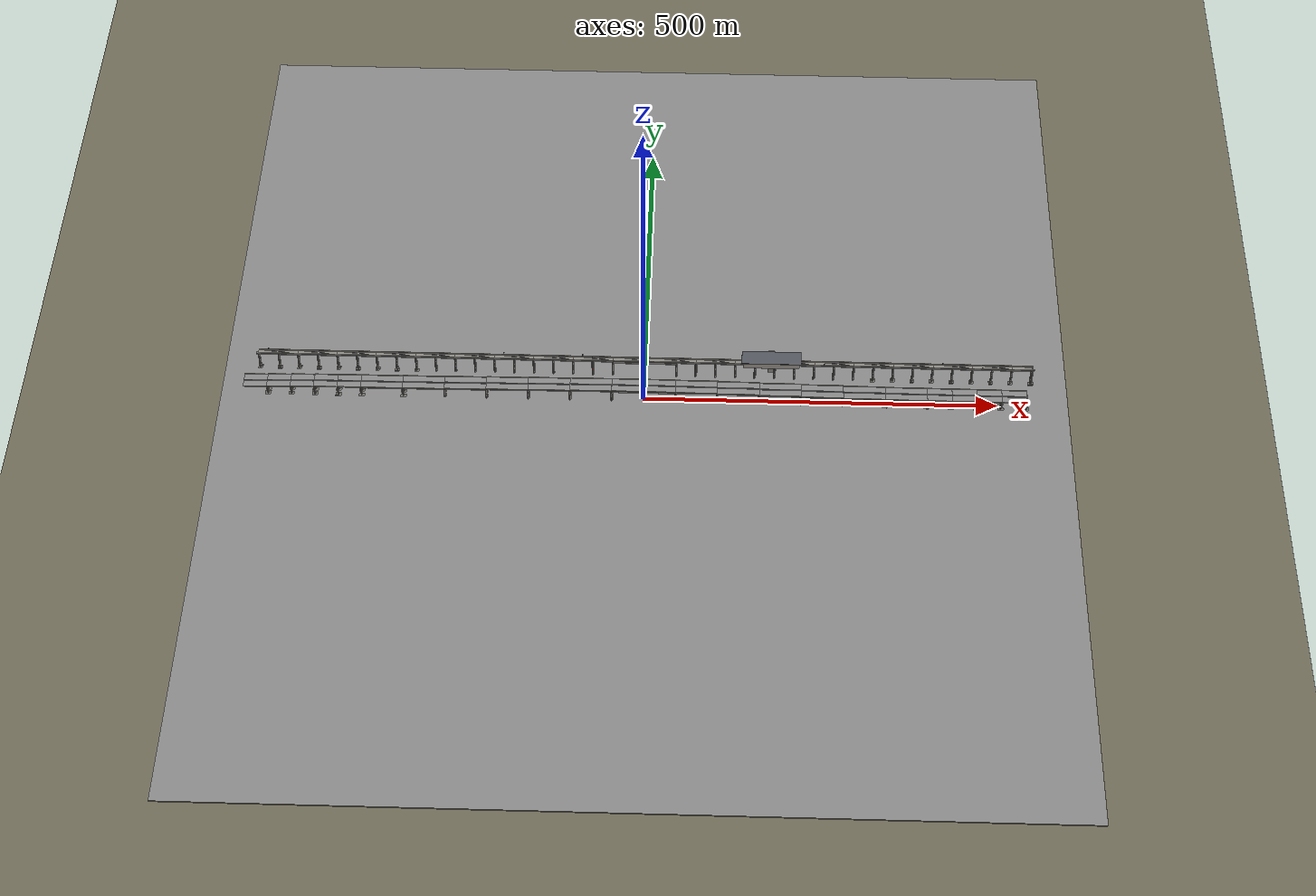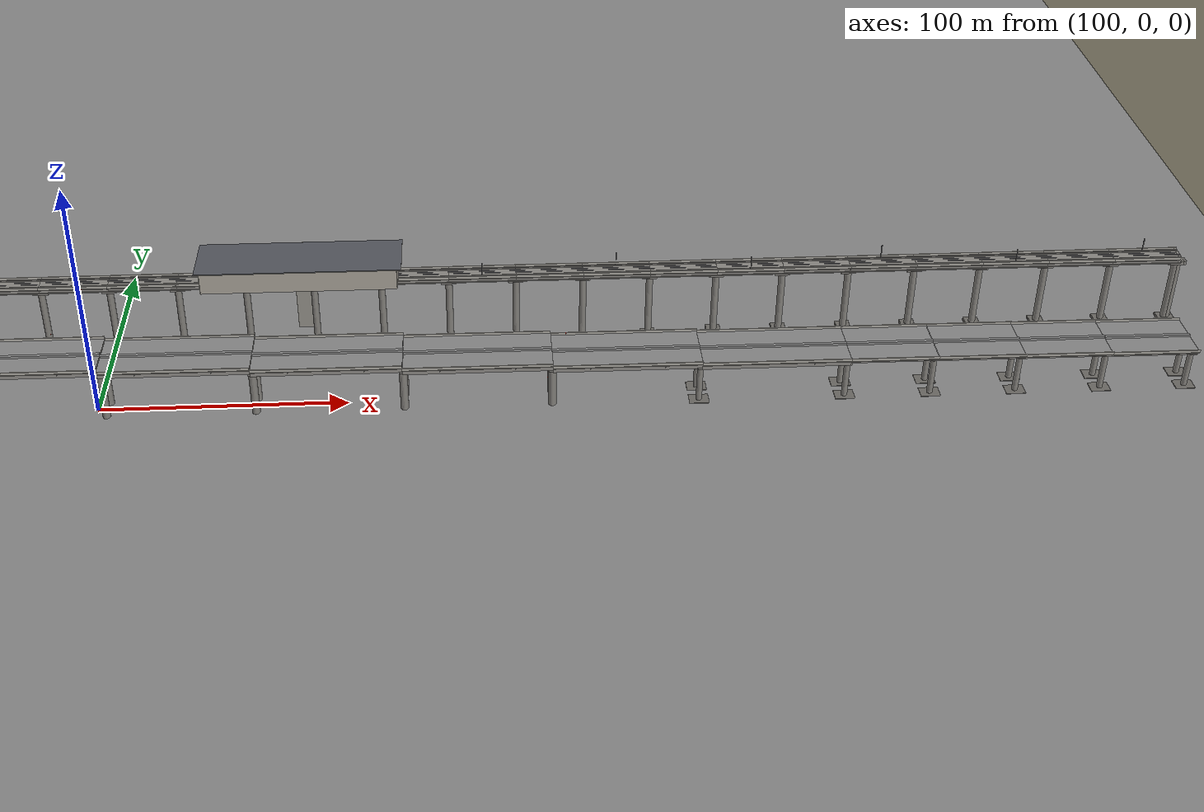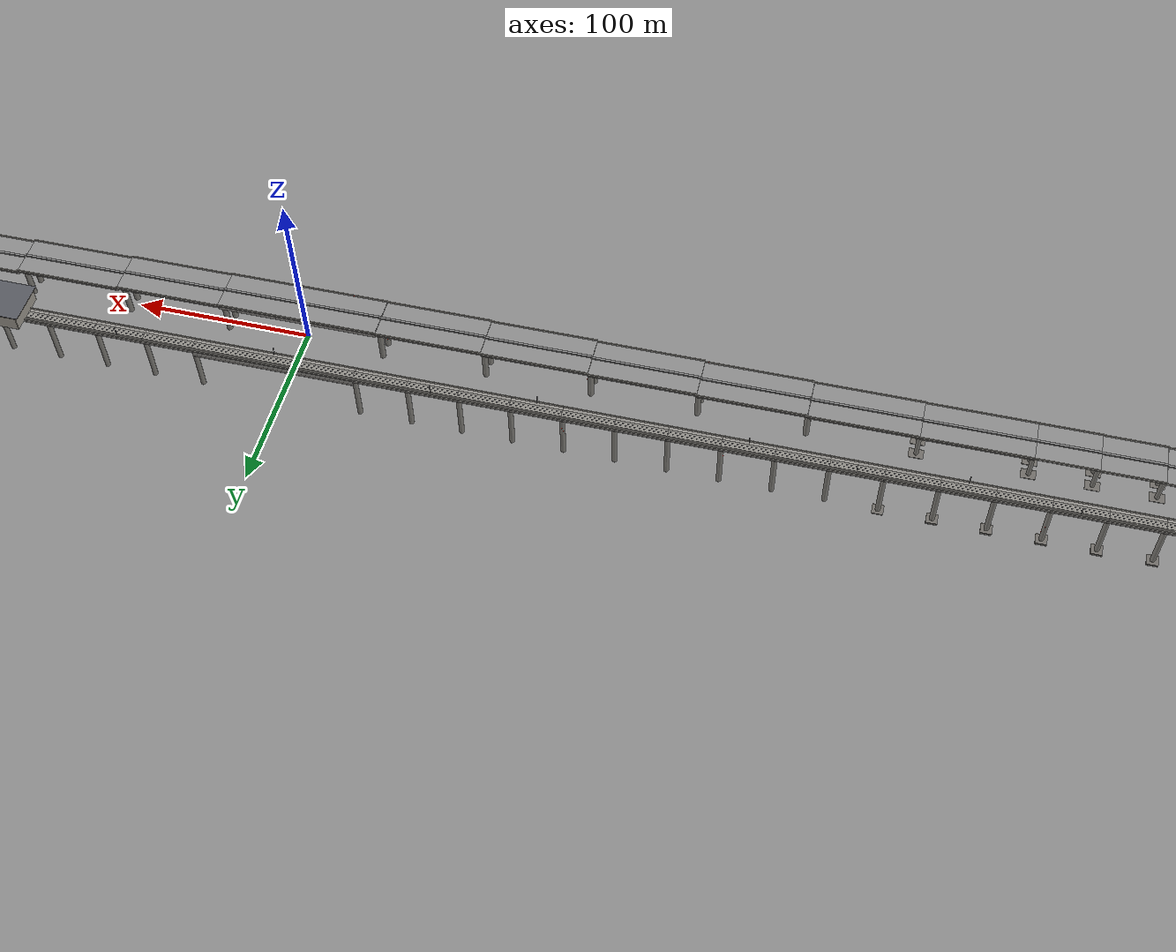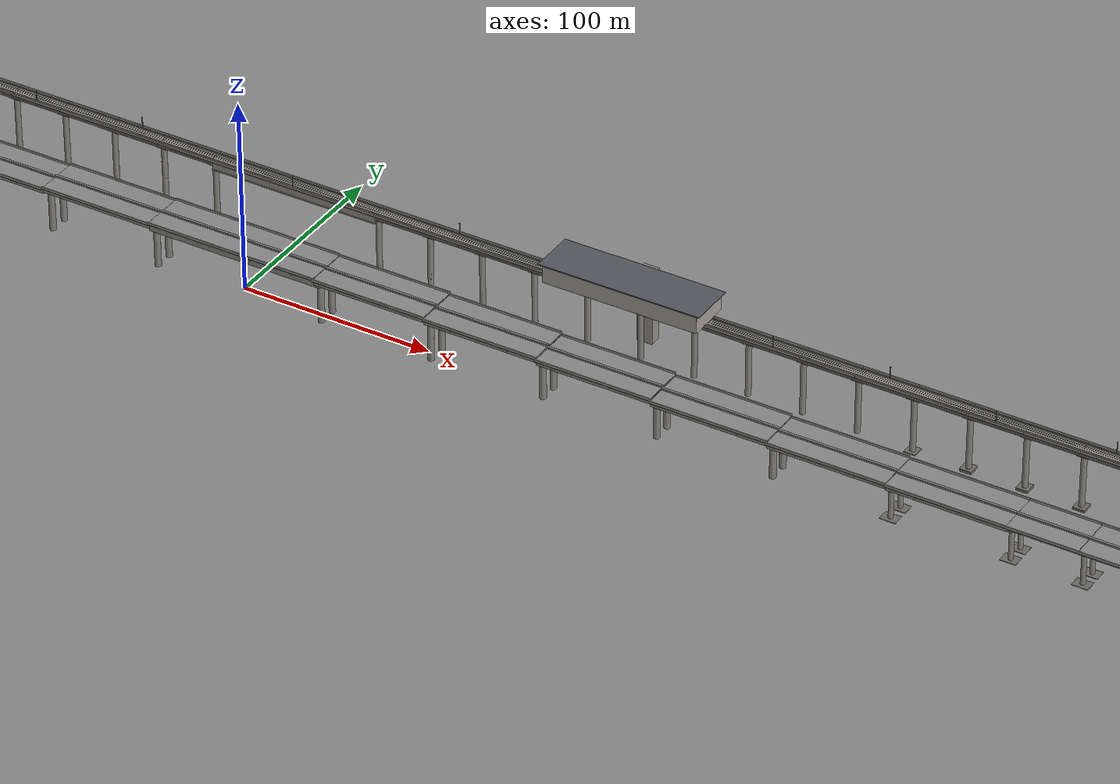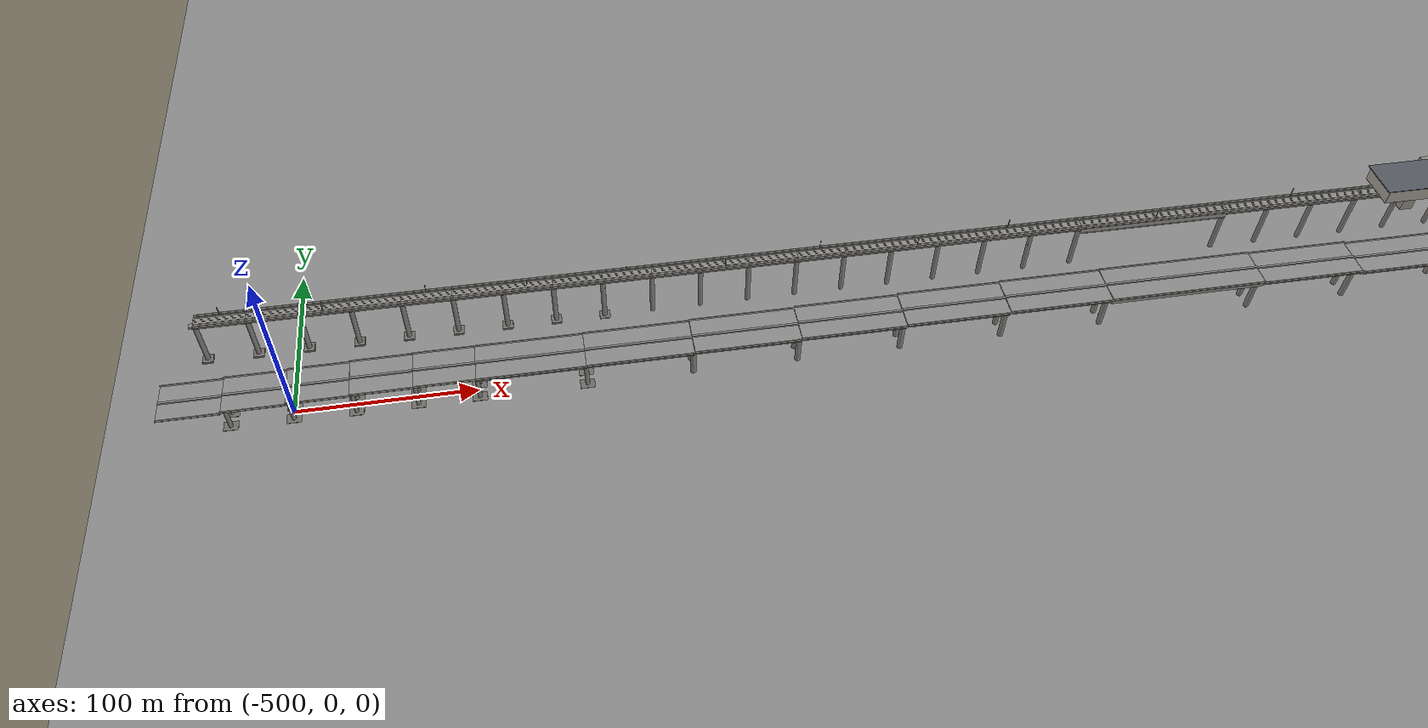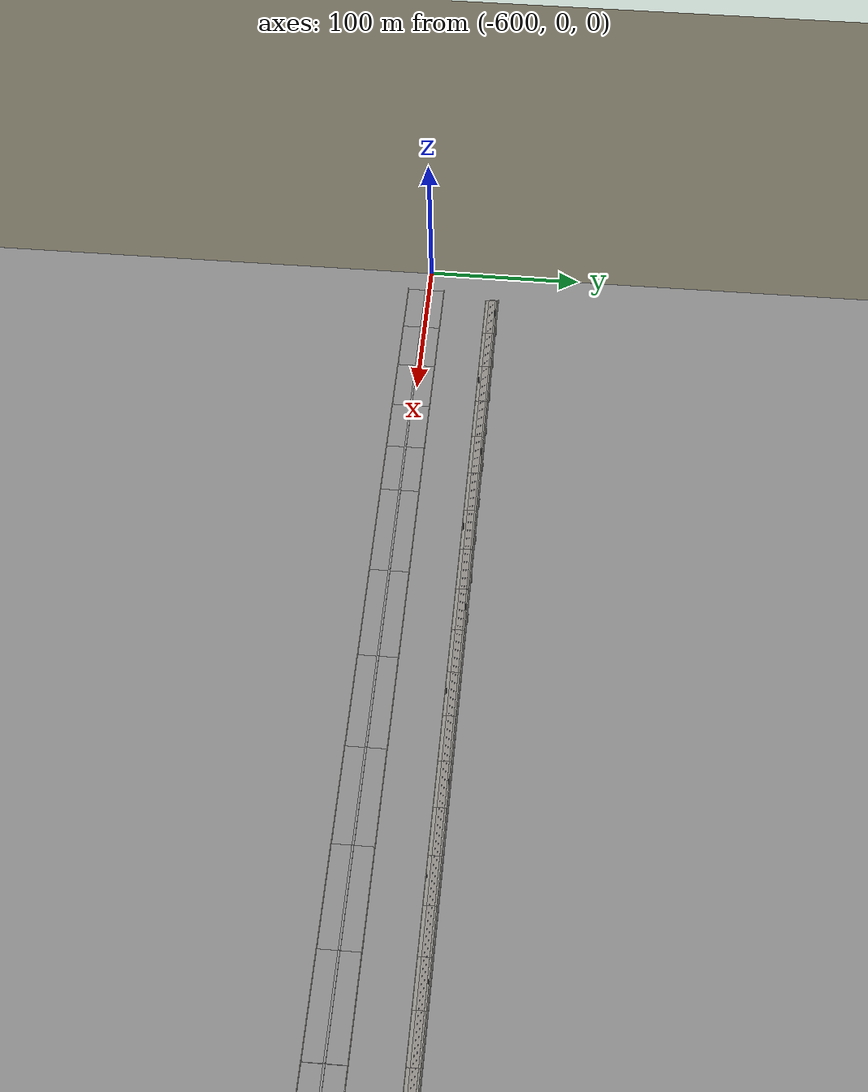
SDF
<?xml version="1.0" ?>
<sdf version="1.9">
  <world name="avian_sic">
    <physics name="default" type="dart">
      <max_step_size>0.002</max_step_size>
      <real_time_factor>1.0</real_time_factor>
    </physics>
    <plugin name="gz::sim::systems::physics" filename="gz-sim-physics-system"/>
    <plugin name="gz::sim::systems::user_commands" filename="gz-sim-user-commands-system"/>
    <plugin name="gz::sim::systems::scene_broadcaster" filename="gz-sim-scene-broadcaster-system"/>
    <plugin name="gz::sim::systems::sensors" filename="gz-sim-sensors-system">
      <render_engine>ogre2</render_engine>
    </plugin>
    <plugin name="gz::sim::systems::contact" filename="gz-sim-contact-system"/>
    <light name="sun" type="directional">
      <cast_shadows>true</cast_shadows>
      <pose>0 0 300 0 0 0</pose>
      <diffuse>0.9 0.88 0.85 1</diffuse>
      <specular>0.2 0.2 0.2 1</specular>
      <direction>-0.5 0.3 -0.8</direction>
    </light>
    <model name="ground_plane">
      <static>true</static>
      <link name="link">
        <collision name="collision">
          <geometry>
            <plane>
              <normal>0 0 1</normal>
              <size>4000 4000</size>
            </plane>
          </geometry>
        </collision>
        <visual name="visual">
          <geometry>
            <plane>
              <normal>0 0 1</normal>
              <size>4000 4000</size>
            </plane>
          </geometry>
          <material>
            <ambient>0.25 0.24 0.20 1</ambient>
            <diffuse>0.45 0.43 0.36 1</diffuse>
          </material>
        </visual>
      </link>
      <pose>0 0 0 0 0 0</pose>
    </model>
    <include>
      <uri>model://avian_bridge</uri>
      <pose>0 0 0 0 0 0</pose>
    </include>
    <include>
      <uri>model://avian_metro</uri>
      <pose>0 0 0 0 0 0</pose>
    </include>
    <include>
      <uri>model://avian_terrain</uri>
      <pose>0 0 0 0 0 0</pose>
    </include>
    <include>
      <uri>model://avian_defects</uri>
      <pose>0 0 0 0 0 0</pose>
    </include>
    <gui fullscreen="0">
      <camera name="user_camera">
        <pose>0 -420 520 0 0.95 1.5708</pose>
      </camera>
    </gui>
  </world>
</sdf>

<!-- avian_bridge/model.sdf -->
<sdf version="1.9">
  <model name="avian_bridge">
    <static>true</static>
    <pose>0 0 0 0 0 0</pose>
    <link name="link">
      <collision name="BR_BEARING_055_G2_collision">
        <pose>-533.333000 -6.000000 18.048000 0 0 0.000000</pose>
        <geometry>
          <box>
            <size>0.700000 0.600000 0.350000</size>
          </box>
        </geometry>
      </collision>
      <visual name="BR_BEARING_055_G2_visual">
        <pose>-533.333000 -6.000000 18.048000 0 0 0.000000</pose>
        <geometry>
          <box>
            <size>0.700000 0.600000 0.350000</size>
          </box>
        </geometry>
        <material>
          <ambient>0.064 0.064 0.068 1</ambient>
          <diffuse>0.160 0.160 0.170 1</diffuse>
          <specular>0.1 0.1 0.1 1</specular>
        </material>
      </visual>
      <collision name="BR_BEARING_055_G3_collision">
        <pose>-533.333000 -2.000000 18.048000 0 0 0.000000</pose>
        <geometry>
          <box>
            <size>0.700000 0.600000 0.350000</size>
          </box>
        </geometry>
      </collision>
      <visual name="BR_BEARING_055_G3_visual">
        <pose>-533.333000 -2.000000 18.048000 0 0 0.000000</pose>
        <geometry>
          <box>
            <size>0.700000 0.600000 0.350000</size>
          </box>
        </geometry>
        <material>
          <ambient>0.064 0.064 0.068 1</ambient>
          <diffuse>0.160 0.160 0.170 1</diffuse>
          <specular>0.1 0.1 0.1 1</specular>
        </material>
      </visual>
      <collision name="BR_BEARING_055_G4_collision">
        <pose>-533.333000 2.000000 18.048000 0 0 0.000000</pose>
        <geometry>
          <box>
            <size>0.700000 0.600000 0.350000</size>
          </box>
        </geometry>
      </collision>
      <visual name="BR_BEARING_055_G4_visual">
        <pose>-533.333000 2.000000 18.048000 0 0 0.000000</pose>
        <geometry>
          <box>
            <size>0.700000 0.600000 0.350000</size>
          </box>
        </geometry>
        <material>
          <ambient>0.064 0.064 0.068 1</ambient>
          <diffuse>0.160 0.160 0.170 1</diffuse>
          <specular>0.1 0.1 0.1 1</specular>
        </material>
      </visual>
      <collision name="BR_BEARING_055_G5_collision">
        <pose>-533.333000 6.000000 18.048000 0 0 0.000000</pose>
        <geometry>
          <box>
            <size>0.700000 0.600000 0.350000</size>
          </box>
        </geometry>
      </collision>
      <visual name="BR_BEARING_055_G5_visual">
        <pose>-533.333000 6.000000 18.048000 0 0 0.000000</pose>
        <geometry>
          <box>
            <size>0.700000 0.600000 0.350000</size>
          </box>
        </geometry>
        <material>
          <ambient>0.064 0.064 0.068 1</ambient>
          <diffuse>0.160 0.160 0.170 1</diffuse>
          <specular>0.1 0.1 0.1 1</specular>
        </material>
      </visual>
      <collision name="BR_BEARING_056_G2_collision">
        <pose>-500.000000 -6.000000 18.994400 0 0 0.000000</pose>
        <geometry>
          <box>
            <size>0.700000 0.600000 0.350000</size>
          </box>
        </geometry>
      </collision>
      <visual name="BR_BEARING_056_G2_visual">
        <pose>-500.000000 -6.000000 18.994400 0 0 0.000000</pose>
        <geometry>
          <box>
            <size>0.700000 0.600000 0.350000</size>
          </box>
        </geometry>
        <material>
          <ambient>0.064 0.064 0.068 1</ambient>
          <diffuse>0.160 0.160 0.170 1</diffuse>
          <specular>0.1 0.1 0.1 1</specular>
        </material>
      </visual>
      <collision name="BR_BEARING_056_G3_collision">
        <pose>-500.000000 -2.000000 18.994400 0 0 0.000000</pose>
        <geometry>
          <box>
            <size>0.700000 0.600000 0.350000</size>
          </box>
        </geometry>
      </collision>
      <visual name="BR_BEARING_056_G3_visual">
        <pose>-500.000000 -2.000000 18.994400 0 0 0.000000</pose>
        <geometry>
          <box>
            <size>0.700000 0.600000 0.350000</size>
          </box>
        </geometry>
        <material>
          <ambient>0.064 0.064 0.068 1</ambient>
          <diffuse>0.160 0.160 0.170 1</diffuse>
          <specular>0.1 0.1 0.1 1</specular>
        </material>
      </visual>
      <collision name="BR_BEARING_056_G4_collision">
        <pose>-500.000000 2.000000 18.994400 0 0 0.000000</pose>
        <geometry>
          <box>
            <size>0.700000 0.600000 0.350000</size>
          </box>
        </geometry>
      </collision>
      <visual name="BR_BEARING_056_G4_visual">
        <pose>-500.000000 2.000000 18.994400 0 0 0.000000</pose>
        <geometry>
          <box>
            <size>0.700000 0.600000 0.350000</size>
          </box>
        </geometry>
        <material>
          <ambient>0.064 0.064 0.068 1</ambient>
          <diffuse>0.160 0.160 0.170 1</diffuse>
          <specular>0.1 0.1 0.1 1</specular>
        </material>
      </visual>
      <collision name="BR_BEARING_056_G5_collision">
        <pose>-500.000000 6.000000 18.994400 0 0 0.000000</pose>
        <geometry>
          <box>
            <size>0.700000 0.600000 0.350000</size>
          </box>
        </geometry>
      </collision>
      <visual name="BR_BEARING_056_G5_visual">
        <pose>-500.000000 6.000000 18.994400 0 0 0.000000</pose>
        <geometry>
          <box>
            <size>0.700000 0.600000 0.350000</size>
          </box>
        </geometry>
        <material>
          <ambient>0.064 0.064 0.068 1</ambient>
          <diffuse>0.160 0.160 0.170 1</diffuse>
          <specular>0.1 0.1 0.1 1</specular>
        </material>
      </visual>
      <collision name="BR_BEARING_057_G2_collision">
        <pose>-466.667000 -6.000000 19.792800 0 0 0.000000</pose>
        <geometry>
          <box>
            <size>0.700000 0.600000 0.350000</size>
          </box>
        </geometry>
      </collision>
      <visual name="BR_BEARING_057_G2_visual">
        <pose>-466.667000 -6.000000 19.792800 0 0 0.000000</pose>
        <geometry>
          <box>
            <size>0.700000 0.600000 0.350000</size>
          </box>
        </geometry>
        <material>
          <ambient>0.064 0.064 0.068 1</ambient>
          <diffuse>0.160 0.160 0.170 1</diffuse>
          <specular>0.1 0.1 0.1 1</specular>
        </material>
      </visual>
      <collision name="BR_BEARING_057_G3_collision">
        <pose>-466.667000 -2.000000 19.792800 0 0 0.000000</pose>
        <geometry>
          <box>
            <size>0.700000 0.600000 0.350000</size>
          </box>
        </geometry>
      </collision>
      <visual name="BR_BEARING_057_G3_visual">
        <pose>-466.667000 -2.000000 19.792800 0 0 0.000000</pose>
        <geometry>
          <box>
            <size>0.700000 0.600000 0.350000</size>
          </box>
        </geometry>
        <material>
          <ambient>0.064 0.064 0.068 1</ambient>
          <diffuse>0.160 0.160 0.170 1</diffuse>
          <specular>0.1 0.1 0.1 1</specular>
        </material>
      </visual>
      <collision name="BR_BEARING_057_G4_collision">
        <pose>-466.667000 2.000000 19.792800 0 0 0.000000</pose>
        <geometry>
          <box>
            <size>0.700000 0.600000 0.350000</size>
          </box>
        </geometry>
      </collision>
      <visual name="BR_BEARING_057_G4_visual">
        <pose>-466.667000 2.000000 19.792800 0 0 0.000000</pose>
        <geometry>
          <box>
            <size>0.700000 0.600000 0.350000</size>
          </box>
        </geometry>
        <material>
          <ambient>0.064 0.064 0.068 1</ambient>
          <diffuse>0.160 0.160 0.170 1</diffuse>
          <specular>0.1 0.1 0.1 1</specular>
        </material>
      </visual>
      <collision name="BR_BEARING_057_G5_collision">
        <pose>-466.667000 6.000000 19.792800 0 0 0.000000</pose>
        <geometry>
          <box>
            <size>0.700000 0.600000 0.350000</size>
          </box>
        </geometry>
      </collision>
      <visual name="BR_BEARING_057_G5_visual">
        <pose>-466.667000 6.000000 19.792800 0 0 0.000000</pose>
        <geometry>
          <box>
            <size>0.700000 0.600000 0.350000</size>
          </box>
        </geometry>
        <material>
          <ambient>0.064 0.064 0.068 1</ambient>
          <diffuse>0.160 0.160 0.170 1</diffuse>
          <specular>0.1 0.1 0.1 1</specular>
        </material>
      </visual>
      <collision name="BR_BEARING_058_G2_collision">
        <pose>-433.333000 -6.000000 20.344200 0 0 0.000000</pose>
        <geometry>
          <box>
            <size>0.700000 0.600000 0.350000</size>
          </box>
        </geometry>
      </collision>
      <visual name="BR_BEARING_058_G2_visual">
        <pose>-433.333000 -6.000000 20.344200 0 0 0.000000</pose>
        <geometry>
          <box>
            <size>0.700000 0.600000 0.350000</size>
          </box>
        </geometry>
        <material>
          <ambient>0.064 0.064 0.068 1</ambient>
          <diffuse>0.160 0.160 0.170 1</diffuse>
          <specular>0.1 0.1 0.1 1</specular>
        </material>
      </visual>
      <collision name="BR_BEARING_058_G3_collision">
        <pose>-433.333000 -2.000000 20.344200 0 0 0.000000</pose>
        <geometry>
          <box>
            <size>0.700000 0.600000 0.350000</size>
          </box>
        </geometry>
      </collision>
      <visual name="BR_BEARING_058_G3_visual">
        <pose>-433.333000 -2.000000 20.344200 0 0 0.000000</pose>
        <geometry>
          <box>
            <size>0.700000 0.600000 0.350000</size>
          </box>
        </geometry>
        <material>
          <ambient>0.064 0.064 0.068 1</ambient>
          <diffuse>0.160 0.160 0.170 1</diffuse>
          <specular>0.1 0.1 0.1 1</specular>
        </material>
      </visual>
      <collision name="BR_BEARING_058_G4_collision">
        <pose>-433.333000 2.000000 20.344200 0 0 0.000000</pose>
        <geometry>
          <box>
            <size>0.700000 0.600000 0.350000</size>
          </box>
        </geometry>
      </collision>
      <visual name="BR_BEARING_058_G4_visual">
        <pose>-433.333000 2.000000 20.344200 0 0 0.000000</pose>
        <geometry>
          <box>
            <size>0.700000 0.600000 0.350000</size>
          </box>
        </geometry>
        <material>
          <ambient>0.064 0.064 0.068 1</ambient>
          <diffuse>0.160 0.160 0.170 1</diffuse>
          <specular>0.1 0.1 0.1 1</specular>
        </material>
      </visual>
      <collision name="BR_BEARING_058_G5_collision">
        <pose>-433.333000 6.000000 20.344200 0 0 0.000000</pose>
        <geometry>
          <box>
            <size>0.700000 0.600000 0.350000</size>
          </box>
        </geometry>
      </collision>
      <visual name="BR_BEARING_058_G5_visual">
        <pose>-433.333000 6.000000 20.344200 0 0 0.000000</pose>
        <geometry>
          <box>
            <size>0.700000 0.600000 0.350000</size>
          </box>
        </geometry>
        <material>
          <ambient>0.064 0.064 0.068 1</ambient>
          <diffuse>0.160 0.160 0.170 1</diffuse>
          <specular>0.1 0.1 0.1 1</specular>
        </material>
      </visual>
      <collision name="BR_BEARING_059_G2_collision">
        <pose>-400.000000 -6.000000 20.550000 0 0 0.000000</pose>
        <geometry>
          <box>
            <size>0.700000 0.600000 0.350000</size>
          </box>
        </geometry>
      </collision>
      <visual name="BR_BEARING_059_G2_visual">
        <pose>-400.000000 -6.000000 20.550000 0 0 0.000000</pose>
        <geometry>
          <box>
            <size>0.700000 0.600000 0.350000</size>
          </box>
        </geometry>
        <material>
          <ambient>0.064 0.064 0.068 1</ambient>
          <diffuse>0.160 0.160 0.170 1</diffuse>
          <specular>0.1 0.1 0.1 1</specular>
        </material>
      </visual>
      <collision name="BR_BEARING_059_G3_collision">
        <pose>-400.000000 -2.000000 20.550000 0 0 0.000000</pose>
        <geometry>
          <box>
            <size>0.700000 0.600000 0.350000</size>
          </box>
        </geometry>
      </collision>
      <visual name="BR_BEARING_059_G3_visual">
        <pose>-400.000000 -2.000000 20.550000 0 0 0.000000</pose>
        <geometry>
          <box>
            <size>0.700000 0.600000 0.350000</size>
          </box>
        </geometry>
        <material>
          <ambient>0.064 0.064 0.068 1</ambient>
          <diffuse>0.160 0.160 0.170 1</diffuse>
          <specular>0.1 0.1 0.1 1</specular>
        </material>
      </visual>
      <collision name="BR_BEARING_059_G4_collision">
        <pose>-400.000000 2.000000 20.550000 0 0 0.000000</pose>
        <geometry>
          <box>
            <size>0.700000 0.600000 0.350000</size>
          </box>
        </geometry>
      </collision>
      <visual name="BR_BEARING_059_G4_visual">
        <pose>-400.000000 2.000000 20.550000 0 0 0.000000</pose>
        <geometry>
          <box>
            <size>0.700000 0.600000 0.350000</size>
          </box>
        </geometry>
        <material>
          <ambient>0.064 0.064 0.068 1</ambient>
          <diffuse>0.160 0.160 0.170 1</diffuse>
          <specular>0.1 0.1 0.1 1</specular>
        </material>
      </visual>
      <collision name="BR_BEARING_059_G5_collision">
        <pose>-400.000000 6.000000 20.550000 0 0 0.000000</pose>
        <geometry>
          <box>
            <size>0.700000 0.600000 0.350000</size>
          </box>
        </geometry>
      </collision>
      <visual name="BR_BEARING_059_G5_visual">
        <pose>-400.000000 6.000000 20.550000 0 0 0.000000</pose>
        <geometry>
          <box>
            <size>0.700000 0.600000 0.350000</size>
          </box>
        </geometry>
        <material>
          <ambient>0.064 0.064 0.068 1</ambient>
          <diffuse>0.160 0.160 0.170 1</diffuse>
          <specular>0.1 0.1 0.1 1</specular>
        </material>
      </visual>
      <collision name="BR_BEARING_060_G2_collision">
        <pose>-340.833000 -6.000000 19.697300 0 0 0.000000</pose>
        <geometry>
          <box>
            <size>0.700000 0.600000 0.350000</size>
          </box>
        </geometry>
      </collision>
      <visual name="BR_BEARING_060_G2_visual">
        <pose>-340.833000 -6.000000 19.697300 0 0 0.000000</pose>
        <geometry>
          <box>
            <size>0.700000 0.600000 0.350000</size>
          </box>
        </geometry>
        <material>
          <ambient>0.064 0.064 0.068 1</ambient>
          <diffuse>0.160 0.160 0.170 1</diffuse>
          <specular>0.1 0.1 0.1 1</specular>
        </material>
      </visual>
      <collision name="BR_BEARING_060_G3_collision">
        <pose>-340.833000 -2.000000 19.697300 0 0 0.000000</pose>
        <geometry>
          <box>
            <size>0.700000 0.600000 0.350000</size>
          </box>
        </geometry>
      </collision>
      <visual name="BR_BEARING_060_G3_visual">
        <pose>-340.833000 -2.000000 19.697300 0 0 0.000000</pose>
        <geometry>
          <box>
            <size>0.700000 0.600000 0.350000</size>
          </box>
        </geometry>
        <material>
          <ambient>0.064 0.064 0.068 1</ambient>
          <diffuse>0.160 0.160 0.170 1</diffuse>
          <specular>0.1 0.1 0.1 1</specular>
        </material>
      </visual>
      <collision name="BR_BEARING_060_G4_collision">
        <pose>-340.833000 2.000000 19.697300 0 0 0.000000</pose>
        <geometry>
          <box>
            <size>0.700000 0.600000 0.350000</size>
          </box>
        </geometry>
      </collision>
      <visual name="BR_BEARING_060_G4_visual">
        <pose>-340.833000 2.000000 19.697300 0 0 0.000000</pose>
        <geometry>
          <box>
            <size>0.700000 0.600000 0.350000</size>
          </box>
        </geometry>
        <material>
          <ambient>0.064 0.064 0.068 1</ambient>
          <diffuse>0.160 0.160 0.170 1</diffuse>
          <specular>0.1 0.1 0.1 1</specular>
        </material>
      </visual>
      <collision name="BR_BEARING_060_G5_collision">
        <pose>-340.833000 6.000000 19.697300 0 0 0.000000</pose>
        <geometry>
          <box>
            <size>0.700000 0.600000 0.350000</size>
          </box>
        </geometry>
      </collision>
      <visual name="BR_BEARING_060_G5_visual">
        <pose>-340.833000 6.000000 19.697300 0 0 0.000000</pose>
        <geometry>
          <box>
            <size>0.700000 0.600000 0.350000</size>
          </box>
        </geometry>
        <material>
          <ambient>0.064 0.064 0.068 1</ambient>
          <diffuse>0.160 0.160 0.170 1</diffuse>
          <specular>0.1 0.1 0.1 1</specular>
        </material>
      </visual>
      <collision name="BR_BEARING_061_G2_collision">
        <pose>-281.667000 -6.000000 20.303700 0 0 0.000000</pose>
        <geometry>
          <box>
            <size>0.700000 0.600000 0.350000</size>
          </box>
        </geometry>
      </collision>
      <visual name="BR_BEARING_061_G2_visual">
        <pose>-281.667000 -6.000000 20.303700 0 0 0.000000</pose>
        <geometry>
          <box>
            <size>0.700000 0.600000 0.350000</size>
          </box>
        </geometry>
        <material>
          <ambient>0.064 0.064 0.068 1</ambient>
          <diffuse>0.160 0.160 0.170 1</diffuse>
          <specular>0.1 0.1 0.1 1</specular>
        </material>
      </visual>
      <collision name="BR_BEARING_061_G3_collision">
        <pose>-281.667000 -2.000000 20.303700 0 0 0.000000</pose>
        <geometry>
          <box>
            <size>0.700000 0.600000 0.350000</size>
          </box>
        </geometry>
      </collision>
      <visual name="BR_BEARING_061_G3_visual">
        <pose>-281.667000 -2.000000 20.303700 0 0 0.000000</pose>
        <geometry>
          <box>
            <size>0.700000 0.600000 0.350000</size>
          </box>
        </geometry>
        <material>
          <ambient>0.064 0.064 0.068 1</ambient>
          <diffuse>0.160 0.160 0.170 1</diffuse>
          <specular>0.1 0.1 0.1 1</specular>
        </material>
      </visual>
      <collision name="BR_BEARING_061_G4_collision">
        <pose>-281.667000 2.000000 20.303700 0 0 0.000000</pose>
        <geometry>
          <box>
            <size>0.700000 0.600000 0.350000</size>
          </box>
        </geometry>
      </collision>
      <visual name="BR_BEARING_061_G4_visual">
        <pose>-281.667000 2.000000 20.303700 0 0 0.000000</pose>
        <geometry>
          <box>
            <size>0.700000 0.600000 0.350000</size>
          </box>
        </geometry>
        <material>
          <ambient>0.064 0.064 0.068 1</ambient>
          <diffuse>0.160 0.160 0.170 1</diffuse>
          <specular>0.1 0.1 0.1 1</specular>
        </material>
      </visual>
      <collision name="BR_BEARING_061_G5_collision">
        <pose>-281.667000 6.000000 20.303700 0 0 0.000000</pose>
        <geometry>
          <box>
            <size>0.700000 0.600000 0.350000</size>
          </box>
        </geometry>
      </collision>
      <visual name="BR_BEARING_061_G5_visual">
        <pose>-281.667000 6.000000 20.303700 0 0 0.000000</pose>
        <geometry>
          <box>
            <size>0.700000 0.600000 0.350000</size>
          </box>
        </geometry>
        <material>
          <ambient>0.064 0.064 0.068 1</ambient>
          <diffuse>0.160 0.160 0.170 1</diffuse>
          <specular>0.1 0.1 0.1 1</specular>
        </material>
      </visual>
      <collision name="BR_BEARING_062_G2_collision">
        <pose>-222.500000 -6.000000 21.124500 0 0 0.000000</pose>
        <geometry>
          <box>
            <size>0.700000 0.600000 0.350000</size>
          </box>
        </geometry>
      </collision>
      <visual name="BR_BEARING_062_G2_visual">
        <pose>-222.500000 -6.000000 21.124500 0 0 0.000000</pose>
        <geometry>
          <box>
            <size>0.700000 0.600000 0.350000</size>
          </box>
        </geometry>
        <material>
          <ambient>0.064 0.064 0.068 1</ambient>
          <diffuse>0.160 0.160 0.170 1</diffuse>
          <specular>0.1 0.1 0.1 1</specular>
        </material>
      </visual>
      <collision name="BR_BEARING_062_G3_collision">
        <pose>-222.500000 -2.000000 21.124500 0 0 0.000000</pose>
        <geometry>
          <box>
            <size>0.700000 0.600000 0.350000</size>
          </box>
        </geometry>
      </collision>
      <visual name="BR_BEARING_062_G3_visual">
        <pose>-222.500000 -2.000000 21.124500 0 0 0.000000</pose>
        <geometry>
          <box>
            <size>0.700000 0.600000 0.350000</size>
          </box>
        </geometry>
        <material>
          <ambient>0.064 0.064 0.068 1</ambient>
          <diffuse>0.160 0.160 0.170 1</diffuse>
          <specular>0.1 0.1 0.1 1</specular>
        </material>
      </visual>
      <collision name="BR_BEARING_062_G4_collision">
        <pose>-222.500000 2.000000 21.124500 0 0 0.000000</pose>
        <geometry>
          <box>
            <size>0.700000 0.600000 0.350000</size>
          </box>
        </geometry>
      </collision>
      <visual name="BR_BEARING_062_G4_visual">
        <pose>-222.500000 2.000000 21.124500 0 0 0.000000</pose>
        <geometry>
          <box>
            <size>0.700000 0.600000 0.350000</size>
          </box>
        </geometry>
        <material>
          <ambient>0.064 0.064 0.068 1</ambient>
          <diffuse>0.160 0.160 0.170 1</diffuse>
          <specular>0.1 0.1 0.1 1</specular>
        </material>
      </visual>
      <collision name="BR_BEARING_062_G5_collision">
        <pose>-222.500000 6.000000 21.124500 0 0 0.000000</pose>
        <geometry>
          <box>
            <size>0.700000 0.600000 0.350000</size>
          </box>
        </geometry>
      </collision>
      <visual name="BR_BEARING_062_G5_visual">
        <pose>-222.500000 6.000000 21.124500 0 0 0.000000</pose>
        <geometry>
          <box>
            <size>0.700000 0.600000 0.350000</size>
          </box>
        </geometry>
        <material>
          <ambient>0.064 0.064 0.068 1</ambient>
          <diffuse>0.160 0.160 0.170 1</diffuse>
          <specular>0.1 0.1 0.1 1</specular>
        </material>
      </visual>
      <collision name="BR_BEARING_063_G2_collision">
        <pose>-163.333000 -6.000000 22.004400 0 0 0.000000</pose>
        <geometry>
          <box>
            <size>0.700000 0.600000 0.350000</size>
          </box>
        </geometry>
      </collision>
      <visual name="BR_BEARING_063_G2_visual">
        <pose>-163.333000 -6.000000 22.004400 0 0 0.000000</pose>
        <geometry>
          <box>
            <size>0.700000 0.600000 0.350000</size>
          </box>
        </geometry>
        <material>
          <ambient>0.064 0.064 0.068 1</ambient>
          <diffuse>0.160 0.160 0.170 1</diffuse>
          <specular>0.1 0.1 0.1 1</specular>
        </material>
      </visual>
      <collision name="BR_BEARING_063_G3_collision">
        <pose>-163.333000 -2.000000 22.004400 0 0 0.000000</pose>
        <geometry>
          <box>
            <size>0.700000 0.600000 0.350000</size>
          </box>
        </geometry>
      </collision>
      <visual name="BR_BEARING_063_G3_visual">
        <pose>-163.333000 -2.000000 22.004400 0 0 0.000000</pose>
        <geometry>
          <box>
            <size>0.700000 0.600000 0.350000</size>
          </box>
        </geometry>
        <material>
          <ambient>0.064 0.064 0.068 1</ambient>
          <diffuse>0.160 0.160 0.170 1</diffuse>
          <specular>0.1 0.1 0.1 1</specular>
        </material>
      </visual>
      <collision name="BR_BEARING_063_G4_collision">
        <pose>-163.333000 2.000000 22.004400 0 0 0.000000</pose>
        <geometry>
          <box>
            <size>0.700000 0.600000 0.350000</size>
          </box>
        </geometry>
      </collision>
      <visual name="BR_BEARING_063_G4_visual">
        <pose>-163.333000 2.000000 22.004400 0 0 0.000000</pose>
        <geometry>
          <box>
            <size>0.700000 0.600000 0.350000</size>
          </box>
        </geometry>
        <material>
          <ambient>0.064 0.064 0.068 1</ambient>
          <diffuse>0.160 0.160 0.170 1</diffuse>
          <specular>0.1 0.1 0.1 1</specular>
        </material>
      </visual>
      <collision name="BR_BEARING_063_G5_collision">
        <pose>-163.333000 6.000000 22.004400 0 0 0.000000</pose>
        <geometry>
          <box>
            <size>0.700000 0.600000 0.350000</size>
          </box>
        </geometry>
      </collision>
      <visual name="BR_BEARING_063_G5_visual">
        <pose>-163.333000 6.000000 22.004400 0 0 0.000000</pose>
        <geometry>
          <box>
            <size>0.700000 0.600000 0.350000</size>
          </box>
        </geometry>
        <material>
          <ambient>0.064 0.064 0.068 1</ambient>
          <diffuse>0.160 0.160 0.170 1</diffuse>
          <specular>0.1 0.1 0.1 1</specular>
        </material>
      </visual>
      <collision name="BR_BEARING_064_G2_collision">
        <pose>-104.167000 -6.000000 22.788100 0 0 0.000000</pose>
        <geometry>
          <box>
            <size>0.700000 0.600000 0.350000</size>
          </box>
        </geometry>
      </collision>
      <visual name="BR_BEARING_064_G2_visual">
        <pose>-104.167000 -6.000000 22.788100 0 0 0.000000</pose>
        <geometry>
          <box>
            <size>0.700000 0.600000 0.350000</size>
          </box>
        </geometry>
        <material>
          <ambient>0.064 0.064 0.068 1</ambient>
          <diffuse>0.160 0.160 0.170 1</diffuse>
          <specular>0.1 0.1 0.1 1</specular>
        </material>
      </visual>
      <collision name="BR_BEARING_064_G3_collision">
        <pose>-104.167000 -2.000000 22.788100 0 0 0.000000</pose>
        <geometry>
          <box>
            <size>0.700000 0.600000 0.350000</size>
          </box>
        </geometry>
      </collision>
      <visual name="BR_BEARING_064_G3_visual">
        <pose>-104.167000 -2.000000 22.788100 0 0 0.000000</pose>
        <geometry>
          <box>
            <size>0.700000 0.600000 0.350000</size>
          </box>
        </geometry>
        <material>
          <ambient>0.064 0.064 0.068 1</ambient>
          <diffuse>0.160 0.160 0.170 1</diffuse>
          <specular>0.1 0.1 0.1 1</specular>
        </material>
      </visual>
      <collision name="BR_BEARING_064_G4_collision">
        <pose>-104.167000 2.000000 22.788100 0 0 0.000000</pose>
        <geometry>
          <box>
            <size>0.700000 0.600000 0.350000</size>
          </box>
        </geometry>
      </collision>
      <visual name="BR_BEARING_064_G4_visual">
        <pose>-104.167000 2.000000 22.788100 0 0 0.000000</pose>
        <geometry>
          <box>
            <size>0.700000 0.600000 0.350000</size>
          </box>
        </geometry>
        <material>
          <ambient>0.064 0.064 0.068 1</ambient>
          <diffuse>0.160 0.160 0.170 1</diffuse>
          <specular>0.1 0.1 0.1 1</specular>
        </material>
      </visual>
      <collision name="BR_BEARING_064_G5_collision">
        <pose>-104.167000 6.000000 22.788100 0 0 0.000000</pose>
        <geometry>
          <box>
            <size>0.700000 0.600000 0.350000</size>
          </box>
        </geometry>
      </collision>
      <visual name="BR_BEARING_064_G5_visual">
        <pose>-104.167000 6.000000 22.788100 0 0 0.000000</pose>
        <geometry>
          <box>
            <size>0.700000 0.600000 0.350000</size>
          </box>
        </geometry>
        <material>
          <ambient>0.064 0.064 0.068 1</ambient>
          <diffuse>0.160 0.160 0.170 1</diffuse>
          <specular>0.1 0.1 0.1 1</specular>
        </material>
      </visual>
      <collision name="BR_BEARING_065_G2_collision">
        <pose>-45.000000 -6.000000 23.320100 0 0 0.000000</pose>
        <geometry>
          <box>
            <size>0.700200 0.600000 0.350000</size>
          </box>
        </geometry>
      </collision>
      <visual name="BR_BEARING_065_G2_visual">
        <pose>-45.000000 -6.000000 23.320100 0 0 0.000000</pose>
        <geometry>
          <box>
            <size>0.700200 0.600000 0.350000</size>
          </box>
        </geometry>
        <material>
          <ambient>0.064 0.064 0.068 1</ambient>
          <diffuse>0.160 0.160 0.170 1</diffuse>
          <specular>0.1 0.1 0.1 1</specular>
        </material>
      </visual>
      <collision name="BR_BEARING_065_G3_collision">
        <pose>-45.000000 -2.000000 23.320100 0 0 0.000000</pose>
        <geometry>
          <box>
            <size>0.700200 0.600000 0.350000</size>
          </box>
        </geometry>
      </collision>
      <visual name="BR_BEARING_065_G3_visual">
        <pose>-45.000000 -2.000000 23.320100 0 0 0.000000</pose>
        <geometry>
          <box>
            <size>0.700200 0.600000 0.350000</size>
          </box>
        </geometry>
        <material>
          <ambient>0.064 0.064 0.068 1</ambient>
          <diffuse>0.160 0.160 0.170 1</diffuse>
          <specular>0.1 0.1 0.1 1</specular>
        </material>
      </visual>
      <collision name="BR_BEARING_065_G4_collision">
        <pose>-45.000000 2.000000 23.320100 0 0 0.000000</pose>
        <geometry>
          <box>
            <size>0.700200 0.600000 0.350000</size>
          </box>
        </geometry>
      </collision>
      <visual name="BR_BEARING_065_G4_visual">
        <pose>-45.000000 2.000000 23.320100 0 0 0.000000</pose>
        <geometry>
          <box>
            <size>0.700200 0.600000 0.350000</size>
          </box>
        </geometry>
        <material>
          <ambient>0.064 0.064 0.068 1</ambient>
          <diffuse>0.160 0.160 0.170 1</diffuse>
          <specular>0.1 0.1 0.1 1</specular>
        </material>
      </visual>
      <collision name="BR_BEARING_065_G5_collision">
        <pose>-45.000000 6.000000 23.320100 0 0 0.000000</pose>
        <geometry>
          <box>
            <size>0.700200 0.600000 0.350000</size>
          </box>
        </geometry>
      </collision>
      <visual name="BR_BEARING_065_G5_visual">
        <pose>-45.000000 6.000000 23.320100 0 0 0.000000</pose>
        <geometry>
          <box>
            <size>0.700200 0.600000 0.350000</size>
          </box>
        </geometry>
        <material>
          <ambient>0.064 0.064 0.068 1</ambient>
          <diffuse>0.160 0.160 0.170 1</diffuse>
          <specular>0.1 0.1 0.1 1</specular>
        </material>
      </visual>
      <collision name="BR_BEARING_066_G2_collision">
        <pose>45.000000 -6.000000 21.865900 0 0 0.000000</pose>
        <geometry>
          <box>
            <size>0.700200 0.600000 0.350000</size>
          </box>
        </geometry>
      </collision>
      <visual name="BR_BEARING_066_G2_visual">
        <pose>45.000000 -6.000000 21.865900 0 0 0.000000</pose>
        <geometry>
          <box>
            <size>0.700200 0.600000 0.350000</size>
          </box>
        </geometry>
        <material>
          <ambient>0.064 0.064 0.068 1</ambient>
          <diffuse>0.160 0.160 0.170 1</diffuse>
          <specular>0.1 0.1 0.1 1</specular>
        </material>
      </visual>
      <collision name="BR_BEARING_066_G3_collision">
        <pose>45.000000 -2.000000 21.865900 0 0 0.000000</pose>
        <geometry>
          <box>
            <size>0.700200 0.600000 0.350000</size>
          </box>
        </geometry>
      </collision>
      <visual name="BR_BEARING_066_G3_visual">
        <pose>45.000000 -2.000000 21.865900 0 0 0.000000</pose>
        <geometry>
          <box>
            <size>0.700200 0.600000 0.350000</size>
          </box>
        </geometry>
        <material>
          <ambient>0.064 0.064 0.068 1</ambient>
          <diffuse>0.160 0.160 0.170 1</diffuse>
          <specular>0.1 0.1 0.1 1</specular>
        </material>
      </visual>
      <collision name="BR_BEARING_066_G4_collision">
        <pose>45.000000 2.000000 21.865900 0 0 0.000000</pose>
        <geometry>
          <box>
            <size>0.700200 0.600000 0.350000</size>
          </box>
        </geometry>
      </collision>
      <visual name="BR_BEARING_066_G4_visual">
        <pose>45.000000 2.000000 21.865900 0 0 0.000000</pose>
        <geometry>
          <box>
            <size>0.700200 0.600000 0.350000</size>
          </box>
        </geometry>
        <material>
          <ambient>0.064 0.064 0.068 1</ambient>
          <diffuse>0.160 0.160 0.170 1</diffuse>
          <specular>0.1 0.1 0.1 1</specular>
        </material>
      </visual>
      <collision name="BR_BEARING_066_G5_collision">
        <pose>45.000000 6.000000 21.865900 0 0 0.000000</pose>
        <geometry>
          <box>
            <size>0.700200 0.600000 0.350000</size>
          </box>
        </geometry>
      </collision>
      <visual name="BR_BEARING_066_G5_visual">
        <pose>45.000000 6.000000 21.865900 0 0 0.000000</pose>
        <geometry>
          <box>
            <size>0.700200 0.600000 0.350000</size>
          </box>
        </geometry>
        <material>
          <ambient>0.064 0.064 0.068 1</ambient>
          <diffuse>0.160 0.160 0.170 1</diffuse>
          <specular>0.1 0.1 0.1 1</specular>
        </material>
      </visual>
      <collision name="BR_BEARING_067_G2_collision">
        <pose>104.167000 -6.000000 22.535900 0 0 0.000000</pose>
        <geometry>
          <box>
            <size>0.700200 0.600000 0.350000</size>
          </box>
        </geometry>
      </collision>
      <visual name="BR_BEARING_067_G2_visual">
        <pose>104.167000 -6.000000 22.535900 0 0 0.000000</pose>
        <geometry>
          <box>
            <size>0.700200 0.600000 0.350000</size>
          </box>
        </geometry>
        <material>
          <ambient>0.064 0.064 0.068 1</ambient>
          <diffuse>0.160 0.160 0.170 1</diffuse>
          <specular>0.1 0.1 0.1 1</specular>
        </material>
      </visual>
      <collision name="BR_BEARING_067_G3_collision">
        <pose>104.167000 -2.000000 22.535900 0 0 0.000000</pose>
        <geometry>
          <box>
            <size>0.700200 0.600000 0.350000</size>
          </box>
        </geometry>
      </collision>
      <visual name="BR_BEARING_067_G3_visual">
        <pose>104.167000 -2.000000 22.535900 0 0 0.000000</pose>
        <geometry>
          <box>
            <size>0.700200 0.600000 0.350000</size>
          </box>
        </geometry>
        <material>
          <ambient>0.064 0.064 0.068 1</ambient>
          <diffuse>0.160 0.160 0.170 1</diffuse>
          <specular>0.1 0.1 0.1 1</specular>
        </material>
      </visual>
      <collision name="BR_BEARING_067_G4_collision">
        <pose>104.167000 2.000000 22.535900 0 0 0.000000</pose>
        <geometry>
          <box>
            <size>0.700200 0.600000 0.350000</size>
          </box>
        </geometry>
      </collision>
      <visual name="BR_BEARING_067_G4_visual">
        <pose>104.167000 2.000000 22.535900 0 0 0.000000</pose>
        <geometry>
          <box>
            <size>0.700200 0.600000 0.350000</size>
          </box>
        </geometry>
        <material>
          <ambient>0.064 0.064 0.068 1</ambient>
          <diffuse>0.160 0.160 0.170 1</diffuse>
          <specular>0.1 0.1 0.1 1</specular>
        </material>
      </visual>
      <collision name="BR_BEARING_067_G5_collision">
        <pose>104.167000 6.000000 22.535900 0 0 0.000000</pose>
        <geometry>
          <box>
            <size>0.700200 0.600000 0.350000</size>
          </box>
        </geometry>
      </collision>
      <visual name="BR_BEARING_067_G5_visual">
        <pose>104.167000 6.000000 22.535900 0 0 0.000000</pose>
        <geometry>
          <box>
            <size>0.700200 0.600000 0.350000</size>
          </box>
        </geometry>
        <material>
          <ambient>0.064 0.064 0.068 1</ambient>
          <diffuse>0.160 0.160 0.170 1</diffuse>
          <specular>0.1 0.1 0.1 1</specular>
        </material>
      </visual>
      <collision name="BR_BEARING_068_G2_collision">
        <pose>163.333000 -6.000000 21.458400 0 0 0.000000</pose>
        <geometry>
          <box>
            <size>0.700200 0.600000 0.350000</size>
          </box>
        </geometry>
      </collision>
      <visual name="BR_BEARING_068_G2_visual">
        <pose>163.333000 -6.000000 21.458400 0 0 0.000000</pose>
        <geometry>
          <box>
            <size>0.700200 0.600000 0.350000</size>
          </box>
        </geometry>
        <material>
          <ambient>0.064 0.064 0.068 1</ambient>
          <diffuse>0.160 0.160 0.170 1</diffuse>
          <specular>0.1 0.1 0.1 1</specular>
        </material>
      </visual>
      <collision name="BR_BEARING_068_G3_collision">
        <pose>163.333000 -2.000000 21.458400 0 0 0.000000</pose>
        <geometry>
          <box>
            <size>0.700200 0.600000 0.350000</size>
          </box>
        </geometry>
      </collision>
      <visual name="BR_BEARING_068_G3_visual">
        <pose>163.333000 -2.000000 21.458400 0 0 0.000000</pose>
        <geometry>
          <box>
            <size>0.700200 0.600000 0.350000</size>
          </box>
        </geometry>
        <material>
          <ambient>0.064 0.064 0.068 1</ambient>
          <diffuse>0.160 0.160 0.170 1</diffuse>
          <specular>0.1 0.1 0.1 1</specular>
        </material>
      </visual>
      <collision name="BR_BEARING_068_G4_collision">
        <pose>163.333000 2.000000 21.458400 0 0 0.000000</pose>
        <geometry>
          <box>
            <size>0.700200 0.600000 0.350000</size>
          </box>
        </geometry>
      </collision>
      <visual name="BR_BEARING_068_G4_visual">
        <pose>163.333000 2.000000 21.458400 0 0 0.000000</pose>
        <geometry>
          <box>
            <size>0.700200 0.600000 0.350000</size>
          </box>
        </geometry>
        <material>
          <ambient>0.064 0.064 0.068 1</ambient>
          <diffuse>0.160 0.160 0.170 1</diffuse>
          <specular>0.1 0.1 0.1 1</specular>
        </material>
      </visual>
      <collision name="BR_BEARING_068_G5_collision">
        <pose>163.333000 6.000000 21.458400 0 0 0.000000</pose>
        <geometry>
          <box>
            <size>0.700200 0.600000 0.350000</size>
          </box>
        </geometry>
      </collision>
      <visual name="BR_BEARING_068_G5_visual">
        <pose>163.333000 6.000000 21.458400 0 0 0.000000</pose>
        <geometry>
          <box>
            <size>0.700200 0.600000 0.350000</size>
          </box>
        </geometry>
        <material>
          <ambient>0.064 0.064 0.068 1</ambient>
          <diffuse>0.160 0.160 0.170 1</diffuse>
          <specular>0.1 0.1 0.1 1</specular>
        </material>
      </visual>
      <collision name="BR_BEARING_069_G2_collision">
        <pose>222.500000 -6.000000 20.248500 0 0 0.000000</pose>
        <geometry>
          <box>
            <size>0.700200 0.600000 0.350000</size>
          </box>
        </geometry>
      </collision>
      <visual name="BR_BEARING_069_G2_visual">
        <pose>222.500000 -6.000000 20.248500 0 0 0.000000</pose>
        <geometry>
          <box>
            <size>0.700200 0.600000 0.350000</size>
          </box>
        </geometry>
        <material>
          <ambient>0.064 0.064 0.068 1</ambient>
          <diffuse>0.160 0.160 0.170 1</diffuse>
          <specular>0.1 0.1 0.1 1</specular>
        </material>
      </visual>
      <collision name="BR_BEARING_069_G3_collision">
        <pose>222.500000 -2.000000 20.248500 0 0 0.000000</pose>
        <geometry>
          <box>
            <size>0.700200 0.600000 0.350000</size>
          </box>
        </geometry>
      </collision>
      <visual name="BR_BEARING_069_G3_visual">
        <pose>222.500000 -2.000000 20.248500 0 0 0.000000</pose>
        <geometry>
          <box>
            <size>0.700200 0.600000 0.350000</size>
          </box>
        </geometry>
        <material>
          <ambient>0.064 0.064 0.068 1</ambient>
          <diffuse>0.160 0.160 0.170 1</diffuse>
          <specular>0.1 0.1 0.1 1</specular>
        </material>
      </visual>
      <collision name="BR_BEARING_069_G4_collision">
        <pose>222.500000 2.000000 20.248500 0 0 0.000000</pose>
        <geometry>
          <box>
            <size>0.700200 0.600000 0.350000</size>
          </box>
        </geometry>
      </collision>
      <visual name="BR_BEARING_069_G4_visual">
        <pose>222.500000 2.000000 20.248500 0 0 0.000000</pose>
        <geometry>
          <box>
            <size>0.700200 0.600000 0.350000</size>
          </box>
        </geometry>
        <material>
          <ambient>0.064 0.064 0.068 1</ambient>
          <diffuse>0.160 0.160 0.170 1</diffuse>
          <specular>0.1 0.1 0.1 1</specular>
        </material>
      </visual>
      <collision name="BR_BEARING_069_G5_collision">
        <pose>222.500000 6.000000 20.248500 0 0 0.000000</pose>
        <geometry>
          <box>
            <size>0.700200 0.600000 0.350000</size>
          </box>
        </geometry>
      </collision>
      <visual name="BR_BEARING_069_G5_visual">
        <pose>222.500000 6.000000 20.248500 0 0 0.000000</pose>
        <geometry>
          <box>
            <size>0.700200 0.600000 0.350000</size>
          </box>
        </geometry>
        <material>
          <ambient>0.064 0.064 0.068 1</ambient>
          <diffuse>0.160 0.160 0.170 1</diffuse>
          <specular>0.1 0.1 0.1 1</specular>
        </material>
      </visual>
      <collision name="BR_BEARING_070_G2_collision">
        <pose>281.667000 -6.000000 19.119800 0 0 0.000000</pose>
        <geometry>
          <box>
            <size>0.700200 0.600000 0.350000</size>
          </box>
        </geometry>
      </collision>
      <visual name="BR_BEARING_070_G2_visual">
        <pose>281.667000 -6.000000 19.119800 0 0 0.000000</pose>
        <geometry>
          <box>
            <size>0.700200 0.600000 0.350000</size>
          </box>
        </geometry>
        <material>
          <ambient>0.064 0.064 0.068 1</ambient>
          <diffuse>0.160 0.160 0.170 1</diffuse>
          <specular>0.1 0.1 0.1 1</specular>
        </material>
      </visual>
      <collision name="BR_BEARING_070_G3_collision">
        <pose>281.667000 -2.000000 19.119800 0 0 0.000000</pose>
        <geometry>
          <box>
            <size>0.700200 0.600000 0.350000</size>
          </box>
        </geometry>
      </collision>
      <visual name="BR_BEARING_070_G3_visual">
        <pose>281.667000 -2.000000 19.119800 0 0 0.000000</pose>
        <geometry>
          <box>
            <size>0.700200 0.600000 0.350000</size>
          </box>
        </geometry>
        <material>
          <ambient>0.064 0.064 0.068 1</ambient>
          <diffuse>0.160 0.160 0.170 1</diffuse>
          <specular>0.1 0.1 0.1 1</specular>
        </material>
      </visual>
      <collision name="BR_BEARING_070_G4_collision">
        <pose>281.667000 2.000000 19.119800 0 0 0.000000</pose>
        <geometry>
          <box>
            <size>0.700200 0.600000 0.350000</size>
          </box>
        </geometry>
      </collision>
      <visual name="BR_BEARING_070_G4_visual">
        <pose>281.667000 2.000000 19.119800 0 0 0.000000</pose>
        <geometry>
          <box>
            <size>0.700200 0.600000 0.350000</size>
          </box>
        </geometry>
        <material>
          <ambient>0.064 0.064 0.068 1</ambient>
          <diffuse>0.160 0.160 0.170 1</diffuse>
          <specular>0.1 0.1 0.1 1</specular>
        </material>
      </visual>
      <collision name="BR_BEARING_070_G5_collision">
        <pose>281.667000 6.000000 19.119800 0 0 0.000000</pose>
        <geometry>
          <box>
            <size>0.700200 0.600000 0.350000</size>
          </box>
        </geometry>
      </collision>
      <visual name="BR_BEARING_070_G5_visual">
        <pose>281.667000 6.000000 19.119800 0 0 0.000000</pose>
        <geometry>
          <box>
            <size>0.700200 0.600000 0.350000</size>
          </box>
        </geometry>
        <material>
          <ambient>0.064 0.064 0.068 1</ambient>
          <diffuse>0.160 0.160 0.170 1</diffuse>
          <specular>0.1 0.1 0.1 1</specular>
        </material>
      </visual>
      <collision name="BR_BEARING_071_G2_collision">
        <pose>340.833000 -6.000000 18.286000 0 0 0.000000</pose>
        <geometry>
          <box>
            <size>0.700200 0.600000 0.350000</size>
          </box>
        </geometry>
      </collision>
      <visual name="BR_BEARING_071_G2_visual">
        <pose>340.833000 -6.000000 18.286000 0 0 0.000000</pose>
        <geometry>
          <box>
            <size>0.700200 0.600000 0.350000</size>
          </box>
        </geometry>
        <material>
          <ambient>0.064 0.064 0.068 1</ambient>
          <diffuse>0.160 0.160 0.170 1</diffuse>
          <specular>0.1 0.1 0.1 1</specular>
        </material>
      </visual>
      <collision name="BR_BEARING_071_G3_collision">
        <pose>340.833000 -2.000000 18.286000 0 0 0.000000</pose>
        <geometry>
          <box>
            <size>0.700200 0.600000 0.350000</size>
          </box>
        </geometry>
      </collision>
      <visual name="BR_BEARING_071_G3_visual">
        <pose>340.833000 -2.000000 18.286000 0 0 0.000000</pose>
        <geometry>
          <box>
            <size>0.700200 0.600000 0.350000</size>
          </box>
        </geometry>
        <material>
          <ambient>0.064 0.064 0.068 1</ambient>
          <diffuse>0.160 0.160 0.170 1</diffuse>
          <specular>0.1 0.1 0.1 1</specular>
        </material>
      </visual>
      <collision name="BR_BEARING_071_G4_collision">
        <pose>340.833000 2.000000 18.286000 0 0 0.000000</pose>
        <geometry>
          <box>
            <size>0.700200 0.600000 0.350000</size>
          </box>
        </geometry>
      </collision>
      <visual name="BR_BEARING_071_G4_visual">
        <pose>340.833000 2.000000 18.286000 0 0 0.000000</pose>
        <geometry>
          <box>
            <size>0.700200 0.600000 0.350000</size>
          </box>
        </geometry>
        <material>
          <ambient>0.064 0.064 0.068 1</ambient>
          <diffuse>0.160 0.160 0.170 1</diffuse>
          <specular>0.1 0.1 0.1 1</specular>
        </material>
      </visual>
      <collision name="BR_BEARING_071_G5_collision">
        <pose>340.833000 6.000000 18.286000 0 0 0.000000</pose>
        <geometry>
          <box>
            <size>0.700200 0.600000 0.350000</size>
          </box>
        </geometry>
      </collision>
      <visual name="BR_BEARING_071_G5_visual">
        <pose>340.833000 6.000000 18.286000 0 0 0.000000</pose>
        <geometry>
          <box>
            <size>0.700200 0.600000 0.350000</size>
          </box>
        </geometry>
        <material>
          <ambient>0.064 0.064 0.068 1</ambient>
          <diffuse>0.160 0.160 0.170 1</diffuse>
          <specular>0.1 0.1 0.1 1</specular>
        </material>
      </visual>
      <collision name="BR_BEARING_072_G2_collision">
        <pose>400.000000 -6.000000 17.960600 0 0 0.000000</pose>
        <geometry>
          <box>
            <size>0.700200 0.600000 0.350000</size>
          </box>
        </geometry>
      </collision>
      <visual name="BR_BEARING_072_G2_visual">
        <pose>400.000000 -6.000000 17.960600 0 0 0.000000</pose>
        <geometry>
          <box>
            <size>0.700200 0.600000 0.350000</size>
          </box>
        </geometry>
        <material>
          <ambient>0.064 0.064 0.068 1</ambient>
          <diffuse>0.160 0.160 0.170 1</diffuse>
          <specular>0.1 0.1 0.1 1</specular>
        </material>
      </visual>
      <collision name="BR_BEARING_072_G3_collision">
        <pose>400.000000 -2.000000 17.960600 0 0 0.000000</pose>
        <geometry>
          <box>
            <size>0.700200 0.600000 0.350000</size>
          </box>
        </geometry>
      </collision>
      <visual name="BR_BEARING_072_G3_visual">
        <pose>400.000000 -2.000000 17.960600 0 0 0.000000</pose>
        <geometry>
          <box>
            <size>0.700200 0.600000 0.350000</size>
          </box>
        </geometry>
        <material>
          <ambient>0.064 0.064 0.068 1</ambient>
          <diffuse>0.160 0.160 0.170 1</diffuse>
          <specular>0.1 0.1 0.1 1</specular>
        </material>
      </visual>
      <collision name="BR_BEARING_072_G4_collision">
        <pose>400.000000 2.000000 17.960600 0 0 0.000000</pose>
        <geometry>
          <box>
            <size>0.700200 0.600000 0.350000</size>
          </box>
        </geometry>
      </collision>
      <visual name="BR_BEARING_072_G4_visual">
        <pose>400.000000 2.000000 17.960600 0 0 0.000000</pose>
        <geometry>
          <box>
            <size>0.700200 0.600000 0.350000</size>
          </box>
        </geometry>
        <material>
          <ambient>0.064 0.064 0.068 1</ambient>
          <diffuse>0.160 0.160 0.170 1</diffuse>
          <specular>0.1 0.1 0.1 1</specular>
        </material>
      </visual>
      <collision name="BR_BEARING_072_G5_collision">
        <pose>400.000000 6.000000 17.960600 0 0 0.000000</pose>
        <geometry>
          <box>
            <size>0.700200 0.600000 0.350000</size>
          </box>
        </geometry>
      </collision>
      <visual name="BR_BEARING_072_G5_visual">
        <pose>400.000000 6.000000 17.960600 0 0 0.000000</pose>
        <geometry>
          <box>
            <size>0.700200 0.600000 0.350000</size>
          </box>
        </geometry>
        <material>
          <ambient>0.064 0.064 0.068 1</ambient>
          <diffuse>0.160 0.160 0.170 1</diffuse>
          <specular>0.1 0.1 0.1 1</specular>
        </material>
      </visual>
      <collision name="BR_BEARING_073_G2_collision">
        <pose>435.000000 -6.000000 19.002900 0 0 0.000000</pose>
        <geometry>
          <box>
            <size>0.700200 0.600000 0.350000</size>
          </box>
        </geometry>
      </collision>
      <visual name="BR_BEARING_073_G2_visual">
        <pose>435.000000 -6.000000 19.002900 0 0 0.000000</pose>
        <geometry>
          <box>
            <size>0.700200 0.600000 0.350000</size>
          </box>
        </geometry>
        <material>
          <ambient>0.064 0.064 0.068 1</ambient>
          <diffuse>0.160 0.160 0.170 1</diffuse>
          <specular>0.1 0.1 0.1 1</specular>
        </material>
      </visual>
      <collision name="BR_BEARING_073_G3_collision">
        <pose>435.000000 -2.000000 19.002900 0 0 0.000000</pose>
        <geometry>
          <box>
            <size>0.700200 0.600000 0.350000</size>
          </box>
        </geometry>
      </collision>
      <visual name="BR_BEARING_073_G3_visual">
        <pose>435.000000 -2.000000 19.002900 0 0 0.000000</pose>
        <geometry>
          <box>
            <size>0.700200 0.600000 0.350000</size>
          </box>
        </geometry>
        <material>
          <ambient>0.064 0.064 0.068 1</ambient>
          <diffuse>0.160 0.160 0.170 1</diffuse>
          <specular>0.1 0.1 0.1 1</specular>
        </material>
      </visual>
      <collision name="BR_BEARING_073_G4_collision">
        <pose>435.000000 2.000000 19.002900 0 0 0.000000</pose>
        <geometry>
          <box>
            <size>0.700200 0.600000 0.350000</size>
          </box>
        </geometry>
      </collision>
      <visual name="BR_BEARING_073_G4_visual">
        <pose>435.000000 2.000000 19.002900 0 0 0.000000</pose>
        <geometry>
          <box>
            <size>0.700200 0.600000 0.350000</size>
          </box>
        </geometry>
        <material>
          <ambient>0.064 0.064 0.068 1</ambient>
          <diffuse>0.160 0.160 0.170 1</diffuse>
          <specular>0.1 0.1 0.1 1</specular>
        </material>
      </visual>
      <collision name="BR_BEARING_073_G5_collision">
        <pose>435.000000 6.000000 19.002900 0 0 0.000000</pose>
        <geometry>
          <box>
            <size>0.700200 0.600000 0.350000</size>
          </box>
        </geometry>
      </collision>
      <visual name="BR_BEARING_073_G5_visual">
        <pose>435.000000 6.000000 19.002900 0 0 0.000000</pose>
        <geometry>
          <box>
            <size>0.700200 0.600000 0.350000</size>
          </box>
        </geometry>
        <material>
          <ambient>0.064 0.064 0.068 1</ambient>
          <diffuse>0.160 0.160 0.170 1</diffuse>
          <specular>0.1 0.1 0.1 1</specular>
        </material>
      </visual>
      <collision name="BR_BEARING_074_G2_collision">
        <pose>470.000000 -6.000000 18.868000 0 0 0.000000</pose>
        <geometry>
          <box>
            <size>0.700200 0.600000 0.350000</size>
          </box>
        </geometry>
      </collision>
      <visual name="BR_BEARING_074_G2_visual">
        <pose>470.000000 -6.000000 18.868000 0 0 0.000000</pose>
        <geometry>
          <box>
            <size>0.700200 0.600000 0.350000</size>
          </box>
        </geometry>
        <material>
          <ambient>0.064 0.064 0.068 1</ambient>
          <diffuse>0.160 0.160 0.170 1</diffuse>
          <specular>0.1 0.1 0.1 1</specular>
        </material>
      </visual>
      <collision name="BR_BEARING_074_G3_collision">
        <pose>470.000000 -2.000000 18.868000 0 0 0.000000</pose>
        <geometry>
          <box>
            <size>0.700200 0.600000 0.350000</size>
          </box>
        </geometry>
      </collision>
      <visual name="BR_BEARING_074_G3_visual">
        <pose>470.000000 -2.000000 18.868000 0 0 0.000000</pose>
        <geometry>
          <box>
            <size>0.700200 0.600000 0.350000</size>
          </box>
        </geometry>
        <material>
          <ambient>0.064 0.064 0.068 1</ambient>
          <diffuse>0.160 0.160 0.170 1</diffuse>
          <specular>0.1 0.1 0.1 1</specular>
        </material>
      </visual>
      <collision name="BR_BEARING_074_G4_collision">
        <pose>470.000000 2.000000 18.868000 0 0 0.000000</pose>
        <geometry>
          <box>
            <size>0.700200 0.600000 0.350000</size>
          </box>
        </geometry>
      </collision>
      <visual name="BR_BEARING_074_G4_visual">
        <pose>470.000000 2.000000 18.868000 0 0 0.000000</pose>
        <geometry>
          <box>
            <size>0.700200 0.600000 0.350000</size>
          </box>
        </geometry>
        <material>
          <ambient>0.064 0.064 0.068 1</ambient>
          <diffuse>0.160 0.160 0.170 1</diffuse>
          <specular>0.1 0.1 0.1 1</specular>
        </material>
      </visual>
      <collision name="BR_BEARING_074_G5_collision">
        <pose>470.000000 6.000000 18.868000 0 0 0.000000</pose>
        <geometry>
          <box>
            <size>0.700200 0.600000 0.350000</size>
          </box>
        </geometry>
      </collision>
      <visual name="BR_BEARING_074_G5_visual">
        <pose>470.000000 6.000000 18.868000 0 0 0.000000</pose>
        <geometry>
          <box>
            <size>0.700200 0.600000 0.350000</size>
          </box>
        </geometry>
        <material>
          <ambient>0.064 0.064 0.068 1</ambient>
          <diffuse>0.160 0.160 0.170 1</diffuse>
          <specular>0.1 0.1 0.1 1</specular>
        </material>
      </visual>
      <collision name="BR_BEARING_075_G2_collision">
        <pose>505.000000 -6.000000 18.655100 0 0 0.000000</pose>
        <geometry>
          <box>
            <size>0.700200 0.600000 0.350000</size>
          </box>
        </geometry>
      </collision>
      <visual name="BR_BEARING_075_G2_visual">
        <pose>505.000000 -6.000000 18.655100 0 0 0.000000</pose>
        <geometry>
          <box>
            <size>0.700200 0.600000 0.350000</size>
          </box>
        </geometry>
        <material>
          <ambient>0.064 0.064 0.068 1</ambient>
          <diffuse>0.160 0.160 0.170 1</diffuse>
          <specular>0.1 0.1 0.1 1</specular>
        </material>
      </visual>
      <collision name="BR_BEARING_075_G3_collision">
        <pose>505.000000 -2.000000 18.655100 0 0 0.000000</pose>
        <geometry>
          <box>
            <size>0.700200 0.600000 0.350000</size>
          </box>
        </geometry>
      </collision>
      <visual name="BR_BEARING_075_G3_visual">
        <pose>505.000000 -2.000000 18.655100 0 0 0.000000</pose>
        <geometry>
          <box>
            <size>0.700200 0.600000 0.350000</size>
          </box>
        </geometry>
        <material>
          <ambient>0.064 0.064 0.068 1</ambient>
          <diffuse>0.160 0.160 0.170 1</diffuse>
          <specular>0.1 0.1 0.1 1</specular>
        </material>
      </visual>
      <collision name="BR_BEARING_075_G4_collision">
        <pose>505.000000 2.000000 18.655100 0 0 0.000000</pose>
        <geometry>
          <box>
            <size>0.700200 0.600000 0.350000</size>
          </box>
        </geometry>
      </collision>
      <visual name="BR_BEARING_075_G4_visual">
        <pose>505.000000 2.000000 18.655100 0 0 0.000000</pose>
        <geometry>
          <box>
            <size>0.700200 0.600000 0.350000</size>
          </box>
        </geometry>
        <material>
          <ambient>0.064 0.064 0.068 1</ambient>
          <diffuse>0.160 0.160 0.170 1</diffuse>
          <specular>0.1 0.1 0.1 1</specular>
        </material>
      </visual>
      <collision name="BR_BEARING_075_G5_collision">
        <pose>505.000000 6.000000 18.655100 0 0 0.000000</pose>
        <geometry>
          <box>
            <size>0.700200 0.600000 0.350000</size>
          </box>
        </geometry>
      </collision>
      <visual name="BR_BEARING_075_G5_visual">
        <pose>505.000000 6.000000 18.655100 0 0 0.000000</pose>
        <geometry>
          <box>
            <size>0.700200 0.600000 0.350000</size>
          </box>
        </geometry>
        <material>
          <ambient>0.064 0.064 0.068 1</ambient>
          <diffuse>0.160 0.160 0.170 1</diffuse>
          <specular>0.1 0.1 0.1 1</specular>
        </material>
      </visual>
      <collision name="BR_BEARING_076_G2_collision">
        <pose>540.000000 -6.000000 18.374000 0 0 0.000000</pose>
        <geometry>
          <box>
            <size>0.700200 0.600000 0.350000</size>
          </box>
        </geometry>
      </collision>
      <visual name="BR_BEARING_076_G2_visual">
        <pose>540.000000 -6.000000 18.374000 0 0 0.000000</pose>
        <geometry>
          <box>
            <size>0.700200 0.600000 0.350000</size>
          </box>
        </geometry>
        <material>
          <ambient>0.064 0.064 0.068 1</ambient>
          <diffuse>0.160 0.160 0.170 1</diffuse>
          <specular>0.1 0.1 0.1 1</specular>
        </material>
      </visual>
      <collision name="BR_BEARING_076_G3_collision">
        <pose>540.000000 -2.000000 18.374000 0 0 0.000000</pose>
        <geometry>
          <box>
            <size>0.700200 0.600000 0.350000</size>
          </box>
        </geometry>
      </collision>
      <visual name="BR_BEARING_076_G3_visual">
        <pose>540.000000 -2.000000 18.374000 0 0 0.000000</pose>
        <geometry>
          <box>
            <size>0.700200 0.600000 0.350000</size>
          </box>
        </geometry>
        <material>
          <ambient>0.064 0.064 0.068 1</ambient>
          <diffuse>0.160 0.160 0.170 1</diffuse>
          <specular>0.1 0.1 0.1 1</specular>
        </material>
      </visual>
      <collision name="BR_BEARING_076_G4_collision">
        <pose>540.000000 2.000000 18.374000 0 0 0.000000</pose>
        <geometry>
          <box>
            <size>0.700200 0.600000 0.350000</size>
          </box>
        </geometry>
      </collision>
      <visual name="BR_BEARING_076_G4_visual">
        <pose>540.000000 2.000000 18.374000 0 0 0.000000</pose>
        <geometry>
          <box>
            <size>0.700200 0.600000 0.350000</size>
          </box>
        </geometry>
        <material>
          <ambient>0.064 0.064 0.068 1</ambient>
          <diffuse>0.160 0.160 0.170 1</diffuse>
          <specular>0.1 0.1 0.1 1</specular>
        </material>
      </visual>
      <collision name="BR_BEARING_076_G5_collision">
        <pose>540.000000 6.000000 18.374000 0 0 0.000000</pose>
        <geometry>
          <box>
            <size>0.700200 0.600000 0.350000</size>
          </box>
        </geometry>
      </collision>
      <visual name="BR_BEARING_076_G5_visual">
        <pose>540.000000 6.000000 18.374000 0 0 0.000000</pose>
        <geometry>
          <box>
            <size>0.700200 0.600000 0.350000</size>
          </box>
        </geometry>
        <material>
          <ambient>0.064 0.064 0.068 1</ambient>
          <diffuse>0.160 0.160 0.170 1</diffuse>
          <specular>0.1 0.1 0.1 1</specular>
        </material>
      </visual>
      <collision name="BR_DECK_SLAB_054_collision">
        <pose>-550.000000 0.000000 19.800000 0 0 0.000000</pose>
        <geometry>
          <box>
            <size>33.334000 24.000000 0.250000</size>
          </box>
        </geometry>
      </collision>
      <visual name="BR_DECK_SLAB_054_visual">
        <pose>-550.000000 0.000000 19.800000 0 0 0.000000</pose>
        <geometry>
          <box>
            <size>33.334000 24.000000 0.250000</size>
          </box>
        </geometry>
        <material>
          <ambient>0.248 0.244 0.232 1</ambient>
          <diffuse>0.620 0.610 0.580 1</diffuse>
          <specular>0.1 0.1 0.1 1</specular>
        </material>
      </visual>
      <collision name="BR_DECK_SLAB_055_collision">
        <pose>-516.666500 0.000000 20.783500 0 0 0.000000</pose>
        <geometry>
          <box>
            <size>33.333000 24.000000 0.250000</size>
          </box>
        </geometry>
      </collision>
      <visual name="BR_DECK_SLAB_055_visual">
        <pose>-516.666500 0.000000 20.783500 0 0 0.000000</pose>
        <geometry>
          <box>
            <size>33.333000 24.000000 0.250000</size>
          </box>
        </geometry>
        <material>
          <ambient>0.248 0.244 0.232 1</ambient>
          <diffuse>0.620 0.610 0.580 1</diffuse>
          <specular>0.1 0.1 0.1 1</specular>
        </material>
      </visual>
      <collision name="BR_DECK_SLAB_056_collision">
        <pose>-483.333500 0.000000 21.668300 0 0 0.000000</pose>
        <geometry>
          <box>
            <size>33.333000 24.000000 0.250000</size>
          </box>
        </geometry>
      </collision>
      <visual name="BR_DECK_SLAB_056_visual">
        <pose>-483.333500 0.000000 21.668300 0 0 0.000000</pose>
        <geometry>
          <box>
            <size>33.333000 24.000000 0.250000</size>
          </box>
        </geometry>
        <material>
          <ambient>0.248 0.244 0.232 1</ambient>
          <diffuse>0.620 0.610 0.580 1</diffuse>
          <specular>0.1 0.1 0.1 1</specular>
        </material>
      </visual>
      <collision name="BR_DECK_SLAB_057_collision">
        <pose>-450.000000 0.000000 22.355600 0 0 0.000000</pose>
        <geometry>
          <box>
            <size>33.334000 24.000000 0.250000</size>
          </box>
        </geometry>
      </collision>
      <visual name="BR_DECK_SLAB_057_visual">
        <pose>-450.000000 0.000000 22.355600 0 0 0.000000</pose>
        <geometry>
          <box>
            <size>33.334000 24.000000 0.250000</size>
          </box>
        </geometry>
        <material>
          <ambient>0.248 0.244 0.232 1</ambient>
          <diffuse>0.620 0.610 0.580 1</diffuse>
          <specular>0.1 0.1 0.1 1</specular>
        </material>
      </visual>
      <collision name="BR_DECK_SLAB_058_collision">
        <pose>-416.666500 0.000000 22.746500 0 0 0.000000</pose>
        <geometry>
          <box>
            <size>33.333000 24.000000 0.250000</size>
          </box>
        </geometry>
      </collision>
      <visual name="BR_DECK_SLAB_058_visual">
        <pose>-416.666500 0.000000 22.746500 0 0 0.000000</pose>
        <geometry>
          <box>
            <size>33.333000 24.000000 0.250000</size>
          </box>
        </geometry>
        <material>
          <ambient>0.248 0.244 0.232 1</ambient>
          <diffuse>0.620 0.610 0.580 1</diffuse>
          <specular>0.1 0.1 0.1 1</specular>
        </material>
      </visual>
      <collision name="BR_DECK_SLAB_059_collision">
        <pose>-370.416500 0.000000 22.862400 0 0 0.000000</pose>
        <geometry>
          <box>
            <size>59.167000 24.000000 0.250000</size>
          </box>
        </geometry>
      </collision>
      <visual name="BR_DECK_SLAB_059_visual">
        <pose>-370.416500 0.000000 22.862400 0 0 0.000000</pose>
        <geometry>
          <box>
            <size>59.167000 24.000000 0.250000</size>
          </box>
        </geometry>
        <material>
          <ambient>0.248 0.244 0.232 1</ambient>
          <diffuse>0.620 0.610 0.580 1</diffuse>
          <specular>0.1 0.1 0.1 1</specular>
        </material>
      </visual>
      <collision name="BR_DECK_SLAB_060_collision">
        <pose>-311.250000 0.000000 23.303400 0 0 0.000000</pose>
        <geometry>
          <box>
            <size>59.166000 24.000000 0.250000</size>
          </box>
        </geometry>
      </collision>
      <visual name="BR_DECK_SLAB_060_visual">
        <pose>-311.250000 0.000000 23.303400 0 0 0.000000</pose>
        <geometry>
          <box>
            <size>59.166000 24.000000 0.250000</size>
          </box>
        </geometry>
        <material>
          <ambient>0.248 0.244 0.232 1</ambient>
          <diffuse>0.620 0.610 0.580 1</diffuse>
          <specular>0.1 0.1 0.1 1</specular>
        </material>
      </visual>
      <collision name="BR_DECK_SLAB_061_collision">
        <pose>-252.083500 0.000000 24.036400 0 0 0.000000</pose>
        <geometry>
          <box>
            <size>59.167000 24.000000 0.250000</size>
          </box>
        </geometry>
      </collision>
      <visual name="BR_DECK_SLAB_061_visual">
        <pose>-252.083500 0.000000 24.036400 0 0 0.000000</pose>
        <geometry>
          <box>
            <size>59.167000 24.000000 0.250000</size>
          </box>
        </geometry>
        <material>
          <ambient>0.248 0.244 0.232 1</ambient>
          <diffuse>0.620 0.610 0.580 1</diffuse>
          <specular>0.1 0.1 0.1 1</specular>
        </material>
      </visual>
      <collision name="BR_DECK_SLAB_062_collision">
        <pose>-192.916500 0.000000 24.906200 0 0 0.000000</pose>
        <geometry>
          <box>
            <size>59.167000 24.000000 0.250000</size>
          </box>
        </geometry>
      </collision>
      <visual name="BR_DECK_SLAB_062_visual">
        <pose>-192.916500 0.000000 24.906200 0 0 0.000000</pose>
        <geometry>
          <box>
            <size>59.167000 24.000000 0.250000</size>
          </box>
        </geometry>
        <material>
          <ambient>0.248 0.244 0.232 1</ambient>
          <diffuse>0.620 0.610 0.580 1</diffuse>
          <specular>0.1 0.1 0.1 1</specular>
        </material>
      </visual>
      <collision name="BR_DECK_SLAB_063_collision">
        <pose>-133.750000 0.000000 25.757400 0 0 0.000000</pose>
        <geometry>
          <box>
            <size>59.166000 24.000000 0.250000</size>
          </box>
        </geometry>
      </collision>
      <visual name="BR_DECK_SLAB_063_visual">
        <pose>-133.750000 0.000000 25.757400 0 0 0.000000</pose>
        <geometry>
          <box>
            <size>59.166000 24.000000 0.250000</size>
          </box>
        </geometry>
        <material>
          <ambient>0.248 0.244 0.232 1</ambient>
          <diffuse>0.620 0.610 0.580 1</diffuse>
          <specular>0.1 0.1 0.1 1</specular>
        </material>
      </visual>
      <collision name="BR_DECK_SLAB_064_collision">
        <pose>-74.583500 0.000000 26.434700 0 0 0.000000</pose>
        <geometry>
          <box>
            <size>59.167000 24.000000 0.250000</size>
          </box>
        </geometry>
      </collision>
      <visual name="BR_DECK_SLAB_064_visual">
        <pose>-74.583500 0.000000 26.434700 0 0 0.000000</pose>
        <geometry>
          <box>
            <size>59.167000 24.000000 0.250000</size>
          </box>
        </geometry>
        <material>
          <ambient>0.248 0.244 0.232 1</ambient>
          <diffuse>0.620 0.610 0.580 1</diffuse>
          <specular>0.1 0.1 0.1 1</specular>
        </material>
      </visual>
      <collision name="BR_DECK_SLAB_065_collision">
        <pose>0.000000 0.000000 26.800000 0 0 0.000000</pose>
        <geometry>
          <box>
            <size>90.000000 24.000000 0.250000</size>
          </box>
        </geometry>
      </collision>
      <visual name="BR_DECK_SLAB_065_visual">
        <pose>0.000000 0.000000 26.800000 0 0 0.000000</pose>
        <geometry>
          <box>
            <size>90.000000 24.000000 0.250000</size>
          </box>
        </geometry>
        <material>
          <ambient>0.248 0.244 0.232 1</ambient>
          <diffuse>0.620 0.610 0.580 1</diffuse>
          <specular>0.1 0.1 0.1 1</specular>
        </material>
      </visual>
      <collision name="BR_DECK_SLAB_066_collision">
        <pose>74.583500 0.000000 26.297700 0 0 0.000000</pose>
        <geometry>
          <box>
            <size>59.167000 24.000000 0.250000</size>
          </box>
        </geometry>
      </collision>
      <visual name="BR_DECK_SLAB_066_visual">
        <pose>74.583500 0.000000 26.297700 0 0 0.000000</pose>
        <geometry>
          <box>
            <size>59.167000 24.000000 0.250000</size>
          </box>
        </geometry>
        <material>
          <ambient>0.248 0.244 0.232 1</ambient>
          <diffuse>0.620 0.610 0.580 1</diffuse>
          <specular>0.1 0.1 0.1 1</specular>
        </material>
      </visual>
      <collision name="BR_DECK_SLAB_067_collision">
        <pose>133.750000 0.000000 25.366400 0 0 0.000000</pose>
        <geometry>
          <box>
            <size>59.166000 24.000000 0.250000</size>
          </box>
        </geometry>
      </collision>
      <visual name="BR_DECK_SLAB_067_visual">
        <pose>133.750000 0.000000 25.366400 0 0 0.000000</pose>
        <geometry>
          <box>
            <size>59.166000 24.000000 0.250000</size>
          </box>
        </geometry>
        <material>
          <ambient>0.248 0.244 0.232 1</ambient>
          <diffuse>0.620 0.610 0.580 1</diffuse>
          <specular>0.1 0.1 0.1 1</specular>
        </material>
      </visual>
      <collision name="BR_DECK_SLAB_068_collision">
        <pose>192.916500 0.000000 24.196000 0 0 0.000000</pose>
        <geometry>
          <box>
            <size>59.167000 24.000000 0.250000</size>
          </box>
        </geometry>
      </collision>
      <visual name="BR_DECK_SLAB_068_visual">
        <pose>192.916500 0.000000 24.196000 0 0 0.000000</pose>
        <geometry>
          <box>
            <size>59.167000 24.000000 0.250000</size>
          </box>
        </geometry>
        <material>
          <ambient>0.248 0.244 0.232 1</ambient>
          <diffuse>0.620 0.610 0.580 1</diffuse>
          <specular>0.1 0.1 0.1 1</specular>
        </material>
      </visual>
      <collision name="BR_DECK_SLAB_069_collision">
        <pose>252.083500 0.000000 23.000100 0 0 0.000000</pose>
        <geometry>
          <box>
            <size>59.167000 24.000000 0.250000</size>
          </box>
        </geometry>
      </collision>
      <visual name="BR_DECK_SLAB_069_visual">
        <pose>252.083500 0.000000 23.000100 0 0 0.000000</pose>
        <geometry>
          <box>
            <size>59.167000 24.000000 0.250000</size>
          </box>
        </geometry>
        <material>
          <ambient>0.248 0.244 0.232 1</ambient>
          <diffuse>0.620 0.610 0.580 1</diffuse>
          <specular>0.1 0.1 0.1 1</specular>
        </material>
      </visual>
      <collision name="BR_DECK_SLAB_070_collision">
        <pose>311.250000 0.000000 21.992100 0 0 0.000000</pose>
        <geometry>
          <box>
            <size>59.166000 24.000000 0.250000</size>
          </box>
        </geometry>
      </collision>
      <visual name="BR_DECK_SLAB_070_visual">
        <pose>311.250000 0.000000 21.992100 0 0 0.000000</pose>
        <geometry>
          <box>
            <size>59.166000 24.000000 0.250000</size>
          </box>
        </geometry>
        <material>
          <ambient>0.248 0.244 0.232 1</ambient>
          <diffuse>0.620 0.610 0.580 1</diffuse>
          <specular>0.1 0.1 0.1 1</specular>
        </material>
      </visual>
      <collision name="BR_DECK_SLAB_071_collision">
        <pose>370.416500 0.000000 21.385800 0 0 0.000000</pose>
        <geometry>
          <box>
            <size>59.167000 24.000000 0.250000</size>
          </box>
        </geometry>
      </collision>
      <visual name="BR_DECK_SLAB_071_visual">
        <pose>370.416500 0.000000 21.385800 0 0 0.000000</pose>
        <geometry>
          <box>
            <size>59.167000 24.000000 0.250000</size>
          </box>
        </geometry>
        <material>
          <ambient>0.248 0.244 0.232 1</ambient>
          <diffuse>0.620 0.610 0.580 1</diffuse>
          <specular>0.1 0.1 0.1 1</specular>
        </material>
      </visual>
      <collision name="BR_DECK_SLAB_072_collision">
        <pose>417.500000 0.000000 21.288000 0 0 0.000000</pose>
        <geometry>
          <box>
            <size>35.000000 24.000000 0.250000</size>
          </box>
        </geometry>
      </collision>
      <visual name="BR_DECK_SLAB_072_visual">
        <pose>417.500000 0.000000 21.288000 0 0 0.000000</pose>
        <geometry>
          <box>
            <size>35.000000 24.000000 0.250000</size>
          </box>
        </geometry>
        <material>
          <ambient>0.248 0.244 0.232 1</ambient>
          <diffuse>0.620 0.610 0.580 1</diffuse>
          <specular>0.1 0.1 0.1 1</specular>
        </material>
      </visual>
      <collision name="BR_DECK_SLAB_073_collision">
        <pose>452.500000 0.000000 21.195800 0 0 0.000000</pose>
        <geometry>
          <box>
            <size>35.000000 24.000000 0.250000</size>
          </box>
        </geometry>
      </collision>
      <visual name="BR_DECK_SLAB_073_visual">
        <pose>452.500000 0.000000 21.195800 0 0 0.000000</pose>
        <geometry>
          <box>
            <size>35.000000 24.000000 0.250000</size>
          </box>
        </geometry>
        <material>
          <ambient>0.248 0.244 0.232 1</ambient>
          <diffuse>0.620 0.610 0.580 1</diffuse>
          <specular>0.1 0.1 0.1 1</specular>
        </material>
      </visual>
      <collision name="BR_DECK_SLAB_074_collision">
        <pose>487.500000 0.000000 21.020700 0 0 0.000000</pose>
        <geometry>
          <box>
            <size>35.000000 24.000000 0.250000</size>
          </box>
        </geometry>
      </collision>
      <visual name="BR_DECK_SLAB_074_visual">
        <pose>487.500000 0.000000 21.020700 0 0 0.000000</pose>
        <geometry>
          <box>
            <size>35.000000 24.000000 0.250000</size>
          </box>
        </geometry>
        <material>
          <ambient>0.248 0.244 0.232 1</ambient>
          <diffuse>0.620 0.610 0.580 1</diffuse>
          <specular>0.1 0.1 0.1 1</specular>
        </material>
      </visual>
      <collision name="BR_DECK_SLAB_075_collision">
        <pose>522.500000 0.000000 20.772500 0 0 0.000000</pose>
        <geometry>
          <box>
            <size>35.000000 24.000000 0.250000</size>
          </box>
        </geometry>
      </collision>
      <visual name="BR_DECK_SLAB_075_visual">
        <pose>522.500000 0.000000 20.772500 0 0 0.000000</pose>
        <geometry>
          <box>
            <size>35.000000 24.000000 0.250000</size>
          </box>
        </geometry>
        <material>
          <ambient>0.248 0.244 0.232 1</ambient>
          <diffuse>0.620 0.610 0.580 1</diffuse>
          <specular>0.1 0.1 0.1 1</specular>
        </material>
      </visual>
      <collision name="BR_DIAPHRAGM_054_2_collision">
        <pose>-550.000000 0.000000 18.905000 0 0 0.000000</pose>
        <geometry>
          <box>
            <size>0.300000 20.000000 1.100000</size>
          </box>
        </geometry>
      </collision>
      <visual name="BR_DIAPHRAGM_054_2_visual">
        <pose>-550.000000 0.000000 18.905000 0 0 0.000000</pose>
        <geometry>
          <box>
            <size>0.300000 20.000000 1.100000</size>
          </box>
        </geometry>
        <material>
          <ambient>0.208 0.204 0.196 1</ambient>
          <diffuse>0.520 0.510 0.490 1</diffuse>
          <specular>0.1 0.1 0.1 1</specular>
        </material>
      </visual>
      <collision name="BR_DIAPHRAGM_054_3_collision">
        <pose>-533.633000 0.000000 18.905000 0 0 0.000000</pose>
        <geometry>
          <box>
            <size>0.300000 20.000000 1.100000</size>
          </box>
        </geometry>
      </collision>
      <visual name="BR_DIAPHRAGM_054_3_visual">
        <pose>-533.633000 0.000000 18.905000 0 0 0.000000</pose>
        <geometry>
          <box>
            <size>0.300000 20.000000 1.100000</size>
          </box>
        </geometry>
        <material>
          <ambient>0.208 0.204 0.196 1</ambient>
          <diffuse>0.520 0.510 0.490 1</diffuse>
          <specular>0.1 0.1 0.1 1</specular>
        </material>
      </visual>
      <collision name="BR_DIAPHRAGM_055_1_collision">
        <pose>-533.033000 0.000000 19.888500 0 0 0.000000</pose>
        <geometry>
          <box>
            <size>0.300000 20.000000 1.100000</size>
          </box>
        </geometry>
      </collision>
      <visual name="BR_DIAPHRAGM_055_1_visual">
        <pose>-533.033000 0.000000 19.888500 0 0 0.000000</pose>
        <geometry>
          <box>
            <size>0.300000 20.000000 1.100000</size>
          </box>
        </geometry>
        <material>
          <ambient>0.208 0.204 0.196 1</ambient>
          <diffuse>0.520 0.510 0.490 1</diffuse>
          <specular>0.1 0.1 0.1 1</specular>
        </material>
      </visual>
      <collision name="BR_DIAPHRAGM_055_2_collision">
        <pose>-516.666500 0.000000 19.888500 0 0 0.000000</pose>
        <geometry>
          <box>
            <size>0.300000 20.000000 1.100000</size>
          </box>
        </geometry>
      </collision>
      <visual name="BR_DIAPHRAGM_055_2_visual">
        <pose>-516.666500 0.000000 19.888500 0 0 0.000000</pose>
        <geometry>
          <box>
            <size>0.300000 20.000000 1.100000</size>
          </box>
        </geometry>
        <material>
          <ambient>0.208 0.204 0.196 1</ambient>
          <diffuse>0.520 0.510 0.490 1</diffuse>
          <specular>0.1 0.1 0.1 1</specular>
        </material>
      </visual>
      <collision name="BR_DIAPHRAGM_055_3_collision">
        <pose>-500.300000 0.000000 19.888500 0 0 0.000000</pose>
        <geometry>
          <box>
            <size>0.300000 20.000000 1.100000</size>
          </box>
        </geometry>
      </collision>
      <visual name="BR_DIAPHRAGM_055_3_visual">
        <pose>-500.300000 0.000000 19.888500 0 0 0.000000</pose>
        <geometry>
          <box>
            <size>0.300000 20.000000 1.100000</size>
          </box>
        </geometry>
        <material>
          <ambient>0.208 0.204 0.196 1</ambient>
          <diffuse>0.520 0.510 0.490 1</diffuse>
          <specular>0.1 0.1 0.1 1</specular>
        </material>
      </visual>
      <collision name="BR_DIAPHRAGM_056_1_collision">
        <pose>-499.700000 0.000000 20.773300 0 0 0.000000</pose>
        <geometry>
          <box>
            <size>0.300000 20.000000 1.100000</size>
          </box>
        </geometry>
      </collision>
      <visual name="BR_DIAPHRAGM_056_1_visual">
        <pose>-499.700000 0.000000 20.773300 0 0 0.000000</pose>
        <geometry>
          <box>
            <size>0.300000 20.000000 1.100000</size>
          </box>
        </geometry>
        <material>
          <ambient>0.208 0.204 0.196 1</ambient>
          <diffuse>0.520 0.510 0.490 1</diffuse>
          <specular>0.1 0.1 0.1 1</specular>
        </material>
      </visual>
      <collision name="BR_DIAPHRAGM_056_2_collision">
        <pose>-483.333500 0.000000 20.773300 0 0 0.000000</pose>
        <geometry>
          <box>
            <size>0.300000 20.000000 1.100000</size>
          </box>
        </geometry>
      </collision>
      <visual name="BR_DIAPHRAGM_056_2_visual">
        <pose>-483.333500 0.000000 20.773300 0 0 0.000000</pose>
        <geometry>
          <box>
            <size>0.300000 20.000000 1.100000</size>
          </box>
        </geometry>
        <material>
          <ambient>0.208 0.204 0.196 1</ambient>
          <diffuse>0.520 0.510 0.490 1</diffuse>
          <specular>0.1 0.1 0.1 1</specular>
        </material>
      </visual>
      <collision name="BR_DIAPHRAGM_056_3_collision">
        <pose>-466.967000 0.000000 20.773300 0 0 0.000000</pose>
        <geometry>
          <box>
            <size>0.300000 20.000000 1.100000</size>
          </box>
        </geometry>
      </collision>
      <visual name="BR_DIAPHRAGM_056_3_visual">
        <pose>-466.967000 0.000000 20.773300 0 0 0.000000</pose>
        <geometry>
          <box>
            <size>0.300000 20.000000 1.100000</size>
          </box>
        </geometry>
        <material>
          <ambient>0.208 0.204 0.196 1</ambient>
          <diffuse>0.520 0.510 0.490 1</diffuse>
          <specular>0.1 0.1 0.1 1</specular>
        </material>
      </visual>
      <collision name="BR_DIAPHRAGM_057_1_collision">
        <pose>-466.367000 0.000000 21.460600 0 0 0.000000</pose>
        <geometry>
          <box>
            <size>0.300000 20.000000 1.100000</size>
          </box>
        </geometry>
      </collision>
      <visual name="BR_DIAPHRAGM_057_1_visual">
        <pose>-466.367000 0.000000 21.460600 0 0 0.000000</pose>
        <geometry>
          <box>
            <size>0.300000 20.000000 1.100000</size>
          </box>
        </geometry>
        <material>
          <ambient>0.208 0.204 0.196 1</ambient>
          <diffuse>0.520 0.510 0.490 1</diffuse>
          <specular>0.1 0.1 0.1 1</specular>
        </material>
      </visual>
      <collision name="BR_DIAPHRAGM_057_2_collision">
        <pose>-450.000000 0.000000 21.460600 0 0 0.000000</pose>
        <geometry>
          <box>
            <size>0.300000 20.000000 1.100000</size>
          </box>
        </geometry>
      </collision>
      <visual name="BR_DIAPHRAGM_057_2_visual">
        <pose>-450.000000 0.000000 21.460600 0 0 0.000000</pose>
        <geometry>
          <box>
            <size>0.300000 20.000000 1.100000</size>
          </box>
        </geometry>
        <material>
          <ambient>0.208 0.204 0.196 1</ambient>
          <diffuse>0.520 0.510 0.490 1</diffuse>
          <specular>0.1 0.1 0.1 1</specular>
        </material>
      </visual>
      <collision name="BR_DIAPHRAGM_057_3_collision">
        <pose>-433.633000 0.000000 21.460600 0 0 0.000000</pose>
        <geometry>
          <box>
            <size>0.300000 20.000000 1.100000</size>
          </box>
        </geometry>
      </collision>
      <visual name="BR_DIAPHRAGM_057_3_visual">
        <pose>-433.633000 0.000000 21.460600 0 0 0.000000</pose>
        <geometry>
          <box>
            <size>0.300000 20.000000 1.100000</size>
          </box>
        </geometry>
        <material>
          <ambient>0.208 0.204 0.196 1</ambient>
          <diffuse>0.520 0.510 0.490 1</diffuse>
          <specular>0.1 0.1 0.1 1</specular>
        </material>
      </visual>
      <collision name="BR_DIAPHRAGM_058_1_collision">
        <pose>-433.033000 0.000000 21.851500 0 0 0.000000</pose>
        <geometry>
          <box>
            <size>0.300000 20.000000 1.100000</size>
          </box>
        </geometry>
      </collision>
      <visual name="BR_DIAPHRAGM_058_1_visual">
        <pose>-433.033000 0.000000 21.851500 0 0 0.000000</pose>
        <geometry>
          <box>
            <size>0.300000 20.000000 1.100000</size>
          </box>
        </geometry>
        <material>
          <ambient>0.208 0.204 0.196 1</ambient>
          <diffuse>0.520 0.510 0.490 1</diffuse>
          <specular>0.1 0.1 0.1 1</specular>
        </material>
      </visual>
      <collision name="BR_DIAPHRAGM_058_2_collision">
        <pose>-416.666500 0.000000 21.851500 0 0 0.000000</pose>
        <geometry>
          <box>
            <size>0.300000 20.000000 1.100000</size>
          </box>
        </geometry>
      </collision>
      <visual name="BR_DIAPHRAGM_058_2_visual">
        <pose>-416.666500 0.000000 21.851500 0 0 0.000000</pose>
        <geometry>
          <box>
            <size>0.300000 20.000000 1.100000</size>
          </box>
        </geometry>
        <material>
          <ambient>0.208 0.204 0.196 1</ambient>
          <diffuse>0.520 0.510 0.490 1</diffuse>
          <specular>0.1 0.1 0.1 1</specular>
        </material>
      </visual>
      <collision name="BR_DIAPHRAGM_058_3_collision">
        <pose>-400.300000 0.000000 21.851500 0 0 0.000000</pose>
        <geometry>
          <box>
            <size>0.300000 20.000000 1.100000</size>
          </box>
        </geometry>
      </collision>
      <visual name="BR_DIAPHRAGM_058_3_visual">
        <pose>-400.300000 0.000000 21.851500 0 0 0.000000</pose>
        <geometry>
          <box>
            <size>0.300000 20.000000 1.100000</size>
          </box>
        </geometry>
        <material>
          <ambient>0.208 0.204 0.196 1</ambient>
          <diffuse>0.520 0.510 0.490 1</diffuse>
          <specular>0.1 0.1 0.1 1</specular>
        </material>
      </visual>
      <collision name="BR_DIAPHRAGM_059_1_collision">
        <pose>-399.700000 0.000000 21.767400 0 0 0.000000</pose>
        <geometry>
          <box>
            <size>0.300000 20.000000 1.500000</size>
          </box>
        </geometry>
      </collision>
      <visual name="BR_DIAPHRAGM_059_1_visual">
        <pose>-399.700000 0.000000 21.767400 0 0 0.000000</pose>
        <geometry>
          <box>
            <size>0.300000 20.000000 1.500000</size>
          </box>
        </geometry>
        <material>
          <ambient>0.208 0.204 0.196 1</ambient>
          <diffuse>0.520 0.510 0.490 1</diffuse>
          <specular>0.1 0.1 0.1 1</specular>
        </material>
      </visual>
      <collision name="BR_DIAPHRAGM_059_2_collision">
        <pose>-385.208300 0.000000 21.767400 0 0 0.000000</pose>
        <geometry>
          <box>
            <size>0.300000 20.000000 1.500000</size>
          </box>
        </geometry>
      </collision>
      <visual name="BR_DIAPHRAGM_059_2_visual">
        <pose>-385.208300 0.000000 21.767400 0 0 0.000000</pose>
        <geometry>
          <box>
            <size>0.300000 20.000000 1.500000</size>
          </box>
        </geometry>
        <material>
          <ambient>0.208 0.204 0.196 1</ambient>
          <diffuse>0.520 0.510 0.490 1</diffuse>
          <specular>0.1 0.1 0.1 1</specular>
        </material>
      </visual>
      <collision name="BR_DIAPHRAGM_059_3_collision">
        <pose>-370.416500 0.000000 21.767400 0 0 0.000000</pose>
        <geometry>
          <box>
            <size>0.300000 20.000000 1.500000</size>
          </box>
        </geometry>
      </collision>
      <visual name="BR_DIAPHRAGM_059_3_visual">
        <pose>-370.416500 0.000000 21.767400 0 0 0.000000</pose>
        <geometry>
          <box>
            <size>0.300000 20.000000 1.500000</size>
          </box>
        </geometry>
        <material>
          <ambient>0.208 0.204 0.196 1</ambient>
          <diffuse>0.520 0.510 0.490 1</diffuse>
          <specular>0.1 0.1 0.1 1</specular>
        </material>
      </visual>
      <collision name="BR_DIAPHRAGM_059_4_collision">
        <pose>-355.624800 0.000000 21.767400 0 0 0.000000</pose>
        <geometry>
          <box>
            <size>0.300000 20.000000 1.500000</size>
          </box>
        </geometry>
      </collision>
      <visual name="BR_DIAPHRAGM_059_4_visual">
        <pose>-355.624800 0.000000 21.767400 0 0 0.000000</pose>
        <geometry>
          <box>
            <size>0.300000 20.000000 1.500000</size>
          </box>
        </geometry>
        <material>
          <ambient>0.208 0.204 0.196 1</ambient>
          <diffuse>0.520 0.510 0.490 1</diffuse>
          <specular>0.1 0.1 0.1 1</specular>
        </material>
      </visual>
      <collision name="BR_DIAPHRAGM_059_5_collision">
        <pose>-341.133000 0.000000 21.767400 0 0 0.000000</pose>
        <geometry>
          <box>
            <size>0.300000 20.000000 1.500000</size>
          </box>
        </geometry>
      </collision>
      <visual name="BR_DIAPHRAGM_059_5_visual">
        <pose>-341.133000 0.000000 21.767400 0 0 0.000000</pose>
        <geometry>
          <box>
            <size>0.300000 20.000000 1.500000</size>
          </box>
        </geometry>
        <material>
          <ambient>0.208 0.204 0.196 1</ambient>
          <diffuse>0.520 0.510 0.490 1</diffuse>
          <specular>0.1 0.1 0.1 1</specular>
        </material>
      </visual>
      <collision name="BR_DIAPHRAGM_060_1_collision">
        <pose>-340.533000 0.000000 22.208400 0 0 0.000000</pose>
        <geometry>
          <box>
            <size>0.300000 20.000000 1.500000</size>
          </box>
        </geometry>
      </collision>
      <visual name="BR_DIAPHRAGM_060_1_visual">
        <pose>-340.533000 0.000000 22.208400 0 0 0.000000</pose>
        <geometry>
          <box>
            <size>0.300000 20.000000 1.500000</size>
          </box>
        </geometry>
        <material>
          <ambient>0.208 0.204 0.196 1</ambient>
          <diffuse>0.520 0.510 0.490 1</diffuse>
          <specular>0.1 0.1 0.1 1</specular>
        </material>
      </visual>
      <collision name="BR_DIAPHRAGM_060_2_collision">
        <pose>-326.041500 0.000000 22.208400 0 0 0.000000</pose>
        <geometry>
          <box>
            <size>0.300000 20.000000 1.500000</size>
          </box>
        </geometry>
      </collision>
      <visual name="BR_DIAPHRAGM_060_2_visual">
        <pose>-326.041500 0.000000 22.208400 0 0 0.000000</pose>
        <geometry>
          <box>
            <size>0.300000 20.000000 1.500000</size>
          </box>
        </geometry>
        <material>
          <ambient>0.208 0.204 0.196 1</ambient>
          <diffuse>0.520 0.510 0.490 1</diffuse>
          <specular>0.1 0.1 0.1 1</specular>
        </material>
      </visual>
      <collision name="BR_DIAPHRAGM_060_3_collision">
        <pose>-311.250000 0.000000 22.208400 0 0 0.000000</pose>
        <geometry>
          <box>
            <size>0.300000 20.000000 1.500000</size>
          </box>
        </geometry>
      </collision>
      <visual name="BR_DIAPHRAGM_060_3_visual">
        <pose>-311.250000 0.000000 22.208400 0 0 0.000000</pose>
        <geometry>
          <box>
            <size>0.300000 20.000000 1.500000</size>
          </box>
        </geometry>
        <material>
          <ambient>0.208 0.204 0.196 1</ambient>
          <diffuse>0.520 0.510 0.490 1</diffuse>
          <specular>0.1 0.1 0.1 1</specular>
        </material>
      </visual>
      <collision name="BR_DIAPHRAGM_060_4_collision">
        <pose>-296.458500 0.000000 22.208400 0 0 0.000000</pose>
        <geometry>
          <box>
            <size>0.300000 20.000000 1.500000</size>
          </box>
        </geometry>
      </collision>
      <visual name="BR_DIAPHRAGM_060_4_visual">
        <pose>-296.458500 0.000000 22.208400 0 0 0.000000</pose>
        <geometry>
          <box>
            <size>0.300000 20.000000 1.500000</size>
          </box>
        </geometry>
        <material>
          <ambient>0.208 0.204 0.196 1</ambient>
          <diffuse>0.520 0.510 0.490 1</diffuse>
          <specular>0.1 0.1 0.1 1</specular>
        </material>
      </visual>
      <collision name="BR_DIAPHRAGM_060_5_collision">
        <pose>-281.967000 0.000000 22.208400 0 0 0.000000</pose>
        <geometry>
          <box>
            <size>0.300000 20.000000 1.500000</size>
          </box>
        </geometry>
      </collision>
      <visual name="BR_DIAPHRAGM_060_5_visual">
        <pose>-281.967000 0.000000 22.208400 0 0 0.000000</pose>
        <geometry>
          <box>
            <size>0.300000 20.000000 1.500000</size>
          </box>
        </geometry>
        <material>
          <ambient>0.208 0.204 0.196 1</ambient>
          <diffuse>0.520 0.510 0.490 1</diffuse>
          <specular>0.1 0.1 0.1 1</specular>
        </material>
      </visual>
      <collision name="BR_DIAPHRAGM_061_1_collision">
        <pose>-281.367000 0.000000 22.941400 0 0 0.000000</pose>
        <geometry>
          <box>
            <size>0.300000 20.000000 1.500000</size>
          </box>
        </geometry>
      </collision>
      <visual name="BR_DIAPHRAGM_061_1_visual">
        <pose>-281.367000 0.000000 22.941400 0 0 0.000000</pose>
        <geometry>
          <box>
            <size>0.300000 20.000000 1.500000</size>
          </box>
        </geometry>
        <material>
          <ambient>0.208 0.204 0.196 1</ambient>
          <diffuse>0.520 0.510 0.490 1</diffuse>
          <specular>0.1 0.1 0.1 1</specular>
        </material>
      </visual>
      <collision name="BR_DIAPHRAGM_061_2_collision">
        <pose>-266.875200 0.000000 22.941400 0 0 0.000000</pose>
        <geometry>
          <box>
            <size>0.300000 20.000000 1.500000</size>
          </box>
        </geometry>
      </collision>
      <visual name="BR_DIAPHRAGM_061_2_visual">
        <pose>-266.875200 0.000000 22.941400 0 0 0.000000</pose>
        <geometry>
          <box>
            <size>0.300000 20.000000 1.500000</size>
          </box>
        </geometry>
        <material>
          <ambient>0.208 0.204 0.196 1</ambient>
          <diffuse>0.520 0.510 0.490 1</diffuse>
          <specular>0.1 0.1 0.1 1</specular>
        </material>
      </visual>
      <collision name="BR_DIAPHRAGM_061_3_collision">
        <pose>-252.083500 0.000000 22.941400 0 0 0.000000</pose>
        <geometry>
          <box>
            <size>0.300000 20.000000 1.500000</size>
          </box>
        </geometry>
      </collision>
      <visual name="BR_DIAPHRAGM_061_3_visual">
        <pose>-252.083500 0.000000 22.941400 0 0 0.000000</pose>
        <geometry>
          <box>
            <size>0.300000 20.000000 1.500000</size>
          </box>
        </geometry>
        <material>
          <ambient>0.208 0.204 0.196 1</ambient>
          <diffuse>0.520 0.510 0.490 1</diffuse>
          <specular>0.1 0.1 0.1 1</specular>
        </material>
      </visual>
      <collision name="BR_DIAPHRAGM_061_4_collision">
        <pose>-237.291700 0.000000 22.941400 0 0 0.000000</pose>
        <geometry>
          <box>
            <size>0.300000 20.000000 1.500000</size>
          </box>
        </geometry>
      </collision>
      <visual name="BR_DIAPHRAGM_061_4_visual">
        <pose>-237.291700 0.000000 22.941400 0 0 0.000000</pose>
        <geometry>
          <box>
            <size>0.300000 20.000000 1.500000</size>
          </box>
        </geometry>
        <material>
          <ambient>0.208 0.204 0.196 1</ambient>
          <diffuse>0.520 0.510 0.490 1</diffuse>
          <specular>0.1 0.1 0.1 1</specular>
        </material>
      </visual>
      <collision name="BR_DIAPHRAGM_061_5_collision">
        <pose>-222.800000 0.000000 22.941400 0 0 0.000000</pose>
        <geometry>
          <box>
            <size>0.300000 20.000000 1.500000</size>
          </box>
        </geometry>
      </collision>
      <visual name="BR_DIAPHRAGM_061_5_visual">
        <pose>-222.800000 0.000000 22.941400 0 0 0.000000</pose>
        <geometry>
          <box>
            <size>0.300000 20.000000 1.500000</size>
          </box>
        </geometry>
        <material>
          <ambient>0.208 0.204 0.196 1</ambient>
          <diffuse>0.520 0.510 0.490 1</diffuse>
          <specular>0.1 0.1 0.1 1</specular>
        </material>
      </visual>
      <collision name="BR_DIAPHRAGM_062_1_collision">
        <pose>-222.200000 0.000000 23.811200 0 0 0.000000</pose>
        <geometry>
          <box>
            <size>0.300000 20.000000 1.500000</size>
          </box>
        </geometry>
      </collision>
      <visual name="BR_DIAPHRAGM_062_1_visual">
        <pose>-222.200000 0.000000 23.811200 0 0 0.000000</pose>
        <geometry>
          <box>
            <size>0.300000 20.000000 1.500000</size>
          </box>
        </geometry>
        <material>
          <ambient>0.208 0.204 0.196 1</ambient>
          <diffuse>0.520 0.510 0.490 1</diffuse>
          <specular>0.1 0.1 0.1 1</specular>
        </material>
      </visual>
      <collision name="BR_DIAPHRAGM_062_2_collision">
        <pose>-207.708300 0.000000 23.811200 0 0 0.000000</pose>
        <geometry>
          <box>
            <size>0.300000 20.000000 1.500000</size>
          </box>
        </geometry>
      </collision>
      <visual name="BR_DIAPHRAGM_062_2_visual">
        <pose>-207.708300 0.000000 23.811200 0 0 0.000000</pose>
        <geometry>
          <box>
            <size>0.300000 20.000000 1.500000</size>
          </box>
        </geometry>
        <material>
          <ambient>0.208 0.204 0.196 1</ambient>
          <diffuse>0.520 0.510 0.490 1</diffuse>
          <specular>0.1 0.1 0.1 1</specular>
        </material>
      </visual>
      <collision name="BR_DIAPHRAGM_062_3_collision">
        <pose>-192.916500 0.000000 23.811200 0 0 0.000000</pose>
        <geometry>
          <box>
            <size>0.300000 20.000000 1.500000</size>
          </box>
        </geometry>
      </collision>
      <visual name="BR_DIAPHRAGM_062_3_visual">
        <pose>-192.916500 0.000000 23.811200 0 0 0.000000</pose>
        <geometry>
          <box>
            <size>0.300000 20.000000 1.500000</size>
          </box>
        </geometry>
        <material>
          <ambient>0.208 0.204 0.196 1</ambient>
          <diffuse>0.520 0.510 0.490 1</diffuse>
          <specular>0.1 0.1 0.1 1</specular>
        </material>
      </visual>
      <collision name="BR_DIAPHRAGM_062_4_collision">
        <pose>-178.124800 0.000000 23.811200 0 0 0.000000</pose>
        <geometry>
          <box>
            <size>0.300000 20.000000 1.500000</size>
          </box>
        </geometry>
      </collision>
      <visual name="BR_DIAPHRAGM_062_4_visual">
        <pose>-178.124800 0.000000 23.811200 0 0 0.000000</pose>
        <geometry>
          <box>
            <size>0.300000 20.000000 1.500000</size>
          </box>
        </geometry>
        <material>
          <ambient>0.208 0.204 0.196 1</ambient>
          <diffuse>0.520 0.510 0.490 1</diffuse>
          <specular>0.1 0.1 0.1 1</specular>
        </material>
      </visual>
      <collision name="BR_DIAPHRAGM_062_5_collision">
        <pose>-163.633000 0.000000 23.811200 0 0 0.000000</pose>
        <geometry>
          <box>
            <size>0.300000 20.000000 1.500000</size>
          </box>
        </geometry>
      </collision>
      <visual name="BR_DIAPHRAGM_062_5_visual">
        <pose>-163.633000 0.000000 23.811200 0 0 0.000000</pose>
        <geometry>
          <box>
            <size>0.300000 20.000000 1.500000</size>
          </box>
        </geometry>
        <material>
          <ambient>0.208 0.204 0.196 1</ambient>
          <diffuse>0.520 0.510 0.490 1</diffuse>
          <specular>0.1 0.1 0.1 1</specular>
        </material>
      </visual>
      <collision name="BR_DIAPHRAGM_063_1_collision">
        <pose>-163.033000 0.000000 24.662400 0 0 0.000000</pose>
        <geometry>
          <box>
            <size>0.300000 20.000000 1.500000</size>
          </box>
        </geometry>
      </collision>
      <visual name="BR_DIAPHRAGM_063_1_visual">
        <pose>-163.033000 0.000000 24.662400 0 0 0.000000</pose>
        <geometry>
          <box>
            <size>0.300000 20.000000 1.500000</size>
          </box>
        </geometry>
        <material>
          <ambient>0.208 0.204 0.196 1</ambient>
          <diffuse>0.520 0.510 0.490 1</diffuse>
          <specular>0.1 0.1 0.1 1</specular>
        </material>
      </visual>
      <collision name="BR_DIAPHRAGM_063_2_collision">
        <pose>-148.541500 0.000000 24.662400 0 0 0.000000</pose>
        <geometry>
          <box>
            <size>0.300000 20.000000 1.500000</size>
          </box>
        </geometry>
      </collision>
      <visual name="BR_DIAPHRAGM_063_2_visual">
        <pose>-148.541500 0.000000 24.662400 0 0 0.000000</pose>
        <geometry>
          <box>
            <size>0.300000 20.000000 1.500000</size>
          </box>
        </geometry>
        <material>
          <ambient>0.208 0.204 0.196 1</ambient>
          <diffuse>0.520 0.510 0.490 1</diffuse>
          <specular>0.1 0.1 0.1 1</specular>
        </material>
      </visual>
      <collision name="BR_DIAPHRAGM_063_3_collision">
        <pose>-133.750000 0.000000 24.662400 0 0 0.000000</pose>
        <geometry>
          <box>
            <size>0.300000 20.000000 1.500000</size>
          </box>
        </geometry>
      </collision>
      <visual name="BR_DIAPHRAGM_063_3_visual">
        <pose>-133.750000 0.000000 24.662400 0 0 0.000000</pose>
        <geometry>
          <box>
            <size>0.300000 20.000000 1.500000</size>
          </box>
        </geometry>
        <material>
          <ambient>0.208 0.204 0.196 1</ambient>
          <diffuse>0.520 0.510 0.490 1</diffuse>
          <specular>0.1 0.1 0.1 1</specular>
        </material>
      </visual>
      <collision name="BR_DIAPHRAGM_063_4_collision">
        <pose>-118.958500 0.000000 24.662400 0 0 0.000000</pose>
        <geometry>
          <box>
            <size>0.300000 20.000000 1.500000</size>
          </box>
        </geometry>
      </collision>
      <visual name="BR_DIAPHRAGM_063_4_visual">
        <pose>-118.958500 0.000000 24.662400 0 0 0.000000</pose>
        <geometry>
          <box>
            <size>0.300000 20.000000 1.500000</size>
          </box>
        </geometry>
        <material>
          <ambient>0.208 0.204 0.196 1</ambient>
          <diffuse>0.520 0.510 0.490 1</diffuse>
          <specular>0.1 0.1 0.1 1</specular>
        </material>
      </visual>
      <collision name="BR_DIAPHRAGM_063_5_collision">
        <pose>-104.467000 0.000000 24.662400 0 0 0.000000</pose>
        <geometry>
          <box>
            <size>0.300000 20.000000 1.500000</size>
          </box>
        </geometry>
      </collision>
      <visual name="BR_DIAPHRAGM_063_5_visual">
        <pose>-104.467000 0.000000 24.662400 0 0 0.000000</pose>
        <geometry>
          <box>
            <size>0.300000 20.000000 1.500000</size>
          </box>
        </geometry>
        <material>
          <ambient>0.208 0.204 0.196 1</ambient>
          <diffuse>0.520 0.510 0.490 1</diffuse>
          <specular>0.1 0.1 0.1 1</specular>
        </material>
      </visual>
      <collision name="BR_DIAPHRAGM_064_1_collision">
        <pose>-103.867000 0.000000 25.339700 0 0 0.000000</pose>
        <geometry>
          <box>
            <size>0.300000 20.000000 1.500000</size>
          </box>
        </geometry>
      </collision>
      <visual name="BR_DIAPHRAGM_064_1_visual">
        <pose>-103.867000 0.000000 25.339700 0 0 0.000000</pose>
        <geometry>
          <box>
            <size>0.300000 20.000000 1.500000</size>
          </box>
        </geometry>
        <material>
          <ambient>0.208 0.204 0.196 1</ambient>
          <diffuse>0.520 0.510 0.490 1</diffuse>
          <specular>0.1 0.1 0.1 1</specular>
        </material>
      </visual>
      <collision name="BR_DIAPHRAGM_064_2_collision">
        <pose>-89.375200 0.000000 25.339700 0 0 0.000000</pose>
        <geometry>
          <box>
            <size>0.300000 20.000000 1.500000</size>
          </box>
        </geometry>
      </collision>
      <visual name="BR_DIAPHRAGM_064_2_visual">
        <pose>-89.375200 0.000000 25.339700 0 0 0.000000</pose>
        <geometry>
          <box>
            <size>0.300000 20.000000 1.500000</size>
          </box>
        </geometry>
        <material>
          <ambient>0.208 0.204 0.196 1</ambient>
          <diffuse>0.520 0.510 0.490 1</diffuse>
          <specular>0.1 0.1 0.1 1</specular>
        </material>
      </visual>
      <collision name="BR_DIAPHRAGM_064_3_collision">
        <pose>-74.583500 0.000000 25.339700 0 0 0.000000</pose>
        <geometry>
          <box>
            <size>0.300000 20.000000 1.500000</size>
          </box>
        </geometry>
      </collision>
      <visual name="BR_DIAPHRAGM_064_3_visual">
        <pose>-74.583500 0.000000 25.339700 0 0 0.000000</pose>
        <geometry>
          <box>
            <size>0.300000 20.000000 1.500000</size>
          </box>
        </geometry>
        <material>
          <ambient>0.208 0.204 0.196 1</ambient>
          <diffuse>0.520 0.510 0.490 1</diffuse>
          <specular>0.1 0.1 0.1 1</specular>
        </material>
      </visual>
      <collision name="BR_DIAPHRAGM_064_4_collision">
        <pose>-59.791700 0.000000 25.339700 0 0 0.000000</pose>
        <geometry>
          <box>
            <size>0.300000 20.000000 1.500000</size>
          </box>
        </geometry>
      </collision>
      <visual name="BR_DIAPHRAGM_064_4_visual">
        <pose>-59.791700 0.000000 25.339700 0 0 0.000000</pose>
        <geometry>
          <box>
            <size>0.300000 20.000000 1.500000</size>
          </box>
        </geometry>
        <material>
          <ambient>0.208 0.204 0.196 1</ambient>
          <diffuse>0.520 0.510 0.490 1</diffuse>
          <specular>0.1 0.1 0.1 1</specular>
        </material>
      </visual>
      <collision name="BR_DIAPHRAGM_064_5_collision">
        <pose>-45.299900 0.000000 25.339700 0 0 0.000000</pose>
        <geometry>
          <box>
            <size>0.300000 20.000000 1.500000</size>
          </box>
        </geometry>
      </collision>
      <visual name="BR_DIAPHRAGM_064_5_visual">
        <pose>-45.299900 0.000000 25.339700 0 0 0.000000</pose>
        <geometry>
          <box>
            <size>0.300000 20.000000 1.500000</size>
          </box>
        </geometry>
        <material>
          <ambient>0.208 0.204 0.196 1</ambient>
          <diffuse>0.520 0.510 0.490 1</diffuse>
          <specular>0.1 0.1 0.1 1</specular>
        </material>
      </visual>
      <collision name="BR_DIAPHRAGM_065_1_collision">
        <pose>-44.700100 0.000000 25.705000 0 0 0.000000</pose>
        <geometry>
          <box>
            <size>0.300000 20.000000 1.500000</size>
          </box>
        </geometry>
      </collision>
      <visual name="BR_DIAPHRAGM_065_1_visual">
        <pose>-44.700100 0.000000 25.705000 0 0 0.000000</pose>
        <geometry>
          <box>
            <size>0.300000 20.000000 1.500000</size>
          </box>
        </geometry>
        <material>
          <ambient>0.208 0.204 0.196 1</ambient>
          <diffuse>0.520 0.510 0.490 1</diffuse>
          <specular>0.1 0.1 0.1 1</specular>
        </material>
      </visual>
      <collision name="BR_DIAPHRAGM_065_2_collision">
        <pose>-32.142900 0.000000 25.705000 0 0 0.000000</pose>
        <geometry>
          <box>
            <size>0.300000 20.000000 1.500000</size>
          </box>
        </geometry>
      </collision>
      <visual name="BR_DIAPHRAGM_065_2_visual">
        <pose>-32.142900 0.000000 25.705000 0 0 0.000000</pose>
        <geometry>
          <box>
            <size>0.300000 20.000000 1.500000</size>
          </box>
        </geometry>
        <material>
          <ambient>0.208 0.204 0.196 1</ambient>
          <diffuse>0.520 0.510 0.490 1</diffuse>
          <specular>0.1 0.1 0.1 1</specular>
        </material>
      </visual>
      <collision name="BR_DIAPHRAGM_065_3_collision">
        <pose>-19.285800 0.000000 25.705000 0 0 0.000000</pose>
        <geometry>
          <box>
            <size>0.300000 20.000000 1.500000</size>
          </box>
        </geometry>
      </collision>
      <visual name="BR_DIAPHRAGM_065_3_visual">
        <pose>-19.285800 0.000000 25.705000 0 0 0.000000</pose>
        <geometry>
          <box>
            <size>0.300000 20.000000 1.500000</size>
          </box>
        </geometry>
        <material>
          <ambient>0.208 0.204 0.196 1</ambient>
          <diffuse>0.520 0.510 0.490 1</diffuse>
          <specular>0.1 0.1 0.1 1</specular>
        </material>
      </visual>
      <collision name="BR_DIAPHRAGM_065_4_collision">
        <pose>-6.428600 0.000000 25.705000 0 0 0.000000</pose>
        <geometry>
          <box>
            <size>0.300000 20.000000 1.500000</size>
          </box>
        </geometry>
      </collision>
      <visual name="BR_DIAPHRAGM_065_4_visual">
        <pose>-6.428600 0.000000 25.705000 0 0 0.000000</pose>
        <geometry>
          <box>
            <size>0.300000 20.000000 1.500000</size>
          </box>
        </geometry>
        <material>
          <ambient>0.208 0.204 0.196 1</ambient>
          <diffuse>0.520 0.510 0.490 1</diffuse>
          <specular>0.1 0.1 0.1 1</specular>
        </material>
      </visual>
      <collision name="BR_DIAPHRAGM_065_5_collision">
        <pose>6.428600 0.000000 25.705000 0 0 0.000000</pose>
        <geometry>
          <box>
            <size>0.300000 20.000000 1.500000</size>
          </box>
        </geometry>
      </collision>
      <visual name="BR_DIAPHRAGM_065_5_visual">
        <pose>6.428600 0.000000 25.705000 0 0 0.000000</pose>
        <geometry>
          <box>
            <size>0.300000 20.000000 1.500000</size>
          </box>
        </geometry>
        <material>
          <ambient>0.208 0.204 0.196 1</ambient>
          <diffuse>0.520 0.510 0.490 1</diffuse>
          <specular>0.1 0.1 0.1 1</specular>
        </material>
      </visual>
      <collision name="BR_DIAPHRAGM_065_6_collision">
        <pose>19.285800 0.000000 25.705000 0 0 0.000000</pose>
        <geometry>
          <box>
            <size>0.300000 20.000000 1.500000</size>
          </box>
        </geometry>
      </collision>
      <visual name="BR_DIAPHRAGM_065_6_visual">
        <pose>19.285800 0.000000 25.705000 0 0 0.000000</pose>
        <geometry>
          <box>
            <size>0.300000 20.000000 1.500000</size>
          </box>
        </geometry>
        <material>
          <ambient>0.208 0.204 0.196 1</ambient>
          <diffuse>0.520 0.510 0.490 1</diffuse>
          <specular>0.1 0.1 0.1 1</specular>
        </material>
      </visual>
      <collision name="BR_DIAPHRAGM_065_7_collision">
        <pose>32.142900 0.000000 25.705000 0 0 0.000000</pose>
        <geometry>
          <box>
            <size>0.300000 20.000000 1.500000</size>
          </box>
        </geometry>
      </collision>
      <visual name="BR_DIAPHRAGM_065_7_visual">
        <pose>32.142900 0.000000 25.705000 0 0 0.000000</pose>
        <geometry>
          <box>
            <size>0.300000 20.000000 1.500000</size>
          </box>
        </geometry>
        <material>
          <ambient>0.208 0.204 0.196 1</ambient>
          <diffuse>0.520 0.510 0.490 1</diffuse>
          <specular>0.1 0.1 0.1 1</specular>
        </material>
      </visual>
      <collision name="BR_DIAPHRAGM_065_8_collision">
        <pose>44.700100 0.000000 25.705000 0 0 0.000000</pose>
        <geometry>
          <box>
            <size>0.300000 20.000000 1.500000</size>
          </box>
        </geometry>
      </collision>
      <visual name="BR_DIAPHRAGM_065_8_visual">
        <pose>44.700100 0.000000 25.705000 0 0 0.000000</pose>
        <geometry>
          <box>
            <size>0.300000 20.000000 1.500000</size>
          </box>
        </geometry>
        <material>
          <ambient>0.208 0.204 0.196 1</ambient>
          <diffuse>0.520 0.510 0.490 1</diffuse>
          <specular>0.1 0.1 0.1 1</specular>
        </material>
      </visual>
      <collision name="BR_DIAPHRAGM_066_1_collision">
        <pose>45.299900 0.000000 25.202700 0 0 0.000000</pose>
        <geometry>
          <box>
            <size>0.300000 20.000000 1.500000</size>
          </box>
        </geometry>
      </collision>
      <visual name="BR_DIAPHRAGM_066_1_visual">
        <pose>45.299900 0.000000 25.202700 0 0 0.000000</pose>
        <geometry>
          <box>
            <size>0.300000 20.000000 1.500000</size>
          </box>
        </geometry>
        <material>
          <ambient>0.208 0.204 0.196 1</ambient>
          <diffuse>0.520 0.510 0.490 1</diffuse>
          <specular>0.1 0.1 0.1 1</specular>
        </material>
      </visual>
      <collision name="BR_DIAPHRAGM_066_2_collision">
        <pose>59.791700 0.000000 25.202700 0 0 0.000000</pose>
        <geometry>
          <box>
            <size>0.299800 20.000000 1.500000</size>
          </box>
        </geometry>
      </collision>
      <visual name="BR_DIAPHRAGM_066_2_visual">
        <pose>59.791700 0.000000 25.202700 0 0 0.000000</pose>
        <geometry>
          <box>
            <size>0.299800 20.000000 1.500000</size>
          </box>
        </geometry>
        <material>
          <ambient>0.208 0.204 0.196 1</ambient>
          <diffuse>0.520 0.510 0.490 1</diffuse>
          <specular>0.1 0.1 0.1 1</specular>
        </material>
      </visual>
      <collision name="BR_DIAPHRAGM_066_3_collision">
        <pose>74.583500 0.000000 25.202700 0 0 0.000000</pose>
        <geometry>
          <box>
            <size>0.299800 20.000000 1.500000</size>
          </box>
        </geometry>
      </collision>
      <visual name="BR_DIAPHRAGM_066_3_visual">
        <pose>74.583500 0.000000 25.202700 0 0 0.000000</pose>
        <geometry>
          <box>
            <size>0.299800 20.000000 1.500000</size>
          </box>
        </geometry>
        <material>
          <ambient>0.208 0.204 0.196 1</ambient>
          <diffuse>0.520 0.510 0.490 1</diffuse>
          <specular>0.1 0.1 0.1 1</specular>
        </material>
      </visual>
      <collision name="BR_DIAPHRAGM_066_4_collision">
        <pose>89.375200 0.000000 25.202700 0 0 0.000000</pose>
        <geometry>
          <box>
            <size>0.299800 20.000000 1.500000</size>
          </box>
        </geometry>
      </collision>
      <visual name="BR_DIAPHRAGM_066_4_visual">
        <pose>89.375200 0.000000 25.202700 0 0 0.000000</pose>
        <geometry>
          <box>
            <size>0.299800 20.000000 1.500000</size>
          </box>
        </geometry>
        <material>
          <ambient>0.208 0.204 0.196 1</ambient>
          <diffuse>0.520 0.510 0.490 1</diffuse>
          <specular>0.1 0.1 0.1 1</specular>
        </material>
      </visual>
      <collision name="BR_DIAPHRAGM_066_5_collision">
        <pose>103.867100 0.000000 25.202700 0 0 0.000000</pose>
        <geometry>
          <box>
            <size>0.300000 20.000000 1.500000</size>
          </box>
        </geometry>
      </collision>
      <visual name="BR_DIAPHRAGM_066_5_visual">
        <pose>103.867100 0.000000 25.202700 0 0 0.000000</pose>
        <geometry>
          <box>
            <size>0.300000 20.000000 1.500000</size>
          </box>
        </geometry>
        <material>
          <ambient>0.208 0.204 0.196 1</ambient>
          <diffuse>0.520 0.510 0.490 1</diffuse>
          <specular>0.1 0.1 0.1 1</specular>
        </material>
      </visual>
      <collision name="BR_DIAPHRAGM_067_1_collision">
        <pose>104.466900 0.000000 24.271400 0 0 0.000000</pose>
        <geometry>
          <box>
            <size>0.300000 20.000000 1.500000</size>
          </box>
        </geometry>
      </collision>
      <visual name="BR_DIAPHRAGM_067_1_visual">
        <pose>104.466900 0.000000 24.271400 0 0 0.000000</pose>
        <geometry>
          <box>
            <size>0.300000 20.000000 1.500000</size>
          </box>
        </geometry>
        <material>
          <ambient>0.208 0.204 0.196 1</ambient>
          <diffuse>0.520 0.510 0.490 1</diffuse>
          <specular>0.1 0.1 0.1 1</specular>
        </material>
      </visual>
      <collision name="BR_DIAPHRAGM_067_2_collision">
        <pose>118.958500 0.000000 24.271400 0 0 0.000000</pose>
        <geometry>
          <box>
            <size>0.299800 20.000000 1.500000</size>
          </box>
        </geometry>
      </collision>
      <visual name="BR_DIAPHRAGM_067_2_visual">
        <pose>118.958500 0.000000 24.271400 0 0 0.000000</pose>
        <geometry>
          <box>
            <size>0.299800 20.000000 1.500000</size>
          </box>
        </geometry>
        <material>
          <ambient>0.208 0.204 0.196 1</ambient>
          <diffuse>0.520 0.510 0.490 1</diffuse>
          <specular>0.1 0.1 0.1 1</specular>
        </material>
      </visual>
      <collision name="BR_DIAPHRAGM_067_3_collision">
        <pose>133.750000 0.000000 24.271400 0 0 0.000000</pose>
        <geometry>
          <box>
            <size>0.299800 20.000000 1.500000</size>
          </box>
        </geometry>
      </collision>
      <visual name="BR_DIAPHRAGM_067_3_visual">
        <pose>133.750000 0.000000 24.271400 0 0 0.000000</pose>
        <geometry>
          <box>
            <size>0.299800 20.000000 1.500000</size>
          </box>
        </geometry>
        <material>
          <ambient>0.208 0.204 0.196 1</ambient>
          <diffuse>0.520 0.510 0.490 1</diffuse>
          <specular>0.1 0.1 0.1 1</specular>
        </material>
      </visual>
      <collision name="BR_DIAPHRAGM_067_4_collision">
        <pose>148.541500 0.000000 24.271400 0 0 0.000000</pose>
        <geometry>
          <box>
            <size>0.299800 20.000000 1.500000</size>
          </box>
        </geometry>
      </collision>
      <visual name="BR_DIAPHRAGM_067_4_visual">
        <pose>148.541500 0.000000 24.271400 0 0 0.000000</pose>
        <geometry>
          <box>
            <size>0.299800 20.000000 1.500000</size>
          </box>
        </geometry>
        <material>
          <ambient>0.208 0.204 0.196 1</ambient>
          <diffuse>0.520 0.510 0.490 1</diffuse>
          <specular>0.1 0.1 0.1 1</specular>
        </material>
      </visual>
      <collision name="BR_DIAPHRAGM_067_5_collision">
        <pose>163.033100 0.000000 24.271400 0 0 0.000000</pose>
        <geometry>
          <box>
            <size>0.300000 20.000000 1.500000</size>
          </box>
        </geometry>
      </collision>
      <visual name="BR_DIAPHRAGM_067_5_visual">
        <pose>163.033100 0.000000 24.271400 0 0 0.000000</pose>
        <geometry>
          <box>
            <size>0.300000 20.000000 1.500000</size>
          </box>
        </geometry>
        <material>
          <ambient>0.208 0.204 0.196 1</ambient>
          <diffuse>0.520 0.510 0.490 1</diffuse>
          <specular>0.1 0.1 0.1 1</specular>
        </material>
      </visual>
      <collision name="BR_DIAPHRAGM_068_1_collision">
        <pose>163.632900 0.000000 23.101000 0 0 0.000000</pose>
        <geometry>
          <box>
            <size>0.300000 20.000000 1.500000</size>
          </box>
        </geometry>
      </collision>
      <visual name="BR_DIAPHRAGM_068_1_visual">
        <pose>163.632900 0.000000 23.101000 0 0 0.000000</pose>
        <geometry>
          <box>
            <size>0.300000 20.000000 1.500000</size>
          </box>
        </geometry>
        <material>
          <ambient>0.208 0.204 0.196 1</ambient>
          <diffuse>0.520 0.510 0.490 1</diffuse>
          <specular>0.1 0.1 0.1 1</specular>
        </material>
      </visual>
      <collision name="BR_DIAPHRAGM_068_2_collision">
        <pose>178.124800 0.000000 23.101000 0 0 0.000000</pose>
        <geometry>
          <box>
            <size>0.299800 20.000000 1.500000</size>
          </box>
        </geometry>
      </collision>
      <visual name="BR_DIAPHRAGM_068_2_visual">
        <pose>178.124800 0.000000 23.101000 0 0 0.000000</pose>
        <geometry>
          <box>
            <size>0.299800 20.000000 1.500000</size>
          </box>
        </geometry>
        <material>
          <ambient>0.208 0.204 0.196 1</ambient>
          <diffuse>0.520 0.510 0.490 1</diffuse>
          <specular>0.1 0.1 0.1 1</specular>
        </material>
      </visual>
      <collision name="BR_DIAPHRAGM_068_3_collision">
        <pose>192.916500 0.000000 23.101000 0 0 0.000000</pose>
        <geometry>
          <box>
            <size>0.299800 20.000000 1.500000</size>
          </box>
        </geometry>
      </collision>
      <visual name="BR_DIAPHRAGM_068_3_visual">
        <pose>192.916500 0.000000 23.101000 0 0 0.000000</pose>
        <geometry>
          <box>
            <size>0.299800 20.000000 1.500000</size>
          </box>
        </geometry>
        <material>
          <ambient>0.208 0.204 0.196 1</ambient>
          <diffuse>0.520 0.510 0.490 1</diffuse>
          <specular>0.1 0.1 0.1 1</specular>
        </material>
      </visual>
      <collision name="BR_DIAPHRAGM_068_4_collision">
        <pose>207.708300 0.000000 23.101000 0 0 0.000000</pose>
        <geometry>
          <box>
            <size>0.299800 20.000000 1.500000</size>
          </box>
        </geometry>
      </collision>
      <visual name="BR_DIAPHRAGM_068_4_visual">
        <pose>207.708300 0.000000 23.101000 0 0 0.000000</pose>
        <geometry>
          <box>
            <size>0.299800 20.000000 1.500000</size>
          </box>
        </geometry>
        <material>
          <ambient>0.208 0.204 0.196 1</ambient>
          <diffuse>0.520 0.510 0.490 1</diffuse>
          <specular>0.1 0.1 0.1 1</specular>
        </material>
      </visual>
      <collision name="BR_DIAPHRAGM_068_5_collision">
        <pose>222.200100 0.000000 23.101000 0 0 0.000000</pose>
        <geometry>
          <box>
            <size>0.300000 20.000000 1.500000</size>
          </box>
        </geometry>
      </collision>
      <visual name="BR_DIAPHRAGM_068_5_visual">
        <pose>222.200100 0.000000 23.101000 0 0 0.000000</pose>
        <geometry>
          <box>
            <size>0.300000 20.000000 1.500000</size>
          </box>
        </geometry>
        <material>
          <ambient>0.208 0.204 0.196 1</ambient>
          <diffuse>0.520 0.510 0.490 1</diffuse>
          <specular>0.1 0.1 0.1 1</specular>
        </material>
      </visual>
      <collision name="BR_DIAPHRAGM_069_1_collision">
        <pose>222.799900 0.000000 21.905100 0 0 0.000000</pose>
        <geometry>
          <box>
            <size>0.300000 20.000000 1.500000</size>
          </box>
        </geometry>
      </collision>
      <visual name="BR_DIAPHRAGM_069_1_visual">
        <pose>222.799900 0.000000 21.905100 0 0 0.000000</pose>
        <geometry>
          <box>
            <size>0.300000 20.000000 1.500000</size>
          </box>
        </geometry>
        <material>
          <ambient>0.208 0.204 0.196 1</ambient>
          <diffuse>0.520 0.510 0.490 1</diffuse>
          <specular>0.1 0.1 0.1 1</specular>
        </material>
      </visual>
      <collision name="BR_DIAPHRAGM_069_2_collision">
        <pose>237.291700 0.000000 21.905100 0 0 0.000000</pose>
        <geometry>
          <box>
            <size>0.299800 20.000000 1.500000</size>
          </box>
        </geometry>
      </collision>
      <visual name="BR_DIAPHRAGM_069_2_visual">
        <pose>237.291700 0.000000 21.905100 0 0 0.000000</pose>
        <geometry>
          <box>
            <size>0.299800 20.000000 1.500000</size>
          </box>
        </geometry>
        <material>
          <ambient>0.208 0.204 0.196 1</ambient>
          <diffuse>0.520 0.510 0.490 1</diffuse>
          <specular>0.1 0.1 0.1 1</specular>
        </material>
      </visual>
      <collision name="BR_DIAPHRAGM_069_3_collision">
        <pose>252.083500 0.000000 21.905100 0 0 0.000000</pose>
        <geometry>
          <box>
            <size>0.299800 20.000000 1.500000</size>
          </box>
        </geometry>
      </collision>
      <visual name="BR_DIAPHRAGM_069_3_visual">
        <pose>252.083500 0.000000 21.905100 0 0 0.000000</pose>
        <geometry>
          <box>
            <size>0.299800 20.000000 1.500000</size>
          </box>
        </geometry>
        <material>
          <ambient>0.208 0.204 0.196 1</ambient>
          <diffuse>0.520 0.510 0.490 1</diffuse>
          <specular>0.1 0.1 0.1 1</specular>
        </material>
      </visual>
      <collision name="BR_DIAPHRAGM_069_4_collision">
        <pose>266.875200 0.000000 21.905100 0 0 0.000000</pose>
        <geometry>
          <box>
            <size>0.299800 20.000000 1.500000</size>
          </box>
        </geometry>
      </collision>
      <visual name="BR_DIAPHRAGM_069_4_visual">
        <pose>266.875200 0.000000 21.905100 0 0 0.000000</pose>
        <geometry>
          <box>
            <size>0.299800 20.000000 1.500000</size>
          </box>
        </geometry>
        <material>
          <ambient>0.208 0.204 0.196 1</ambient>
          <diffuse>0.520 0.510 0.490 1</diffuse>
          <specular>0.1 0.1 0.1 1</specular>
        </material>
      </visual>
      <collision name="BR_DIAPHRAGM_069_5_collision">
        <pose>281.367100 0.000000 21.905100 0 0 0.000000</pose>
        <geometry>
          <box>
            <size>0.300000 20.000000 1.500000</size>
          </box>
        </geometry>
      </collision>
      <visual name="BR_DIAPHRAGM_069_5_visual">
        <pose>281.367100 0.000000 21.905100 0 0 0.000000</pose>
        <geometry>
          <box>
            <size>0.300000 20.000000 1.500000</size>
          </box>
        </geometry>
        <material>
          <ambient>0.208 0.204 0.196 1</ambient>
          <diffuse>0.520 0.510 0.490 1</diffuse>
          <specular>0.1 0.1 0.1 1</specular>
        </material>
      </visual>
      <collision name="BR_DIAPHRAGM_070_1_collision">
        <pose>281.966900 0.000000 20.897100 0 0 0.000000</pose>
        <geometry>
          <box>
            <size>0.300000 20.000000 1.500000</size>
          </box>
        </geometry>
      </collision>
      <visual name="BR_DIAPHRAGM_070_1_visual">
        <pose>281.966900 0.000000 20.897100 0 0 0.000000</pose>
        <geometry>
          <box>
            <size>0.300000 20.000000 1.500000</size>
          </box>
        </geometry>
        <material>
          <ambient>0.208 0.204 0.196 1</ambient>
          <diffuse>0.520 0.510 0.490 1</diffuse>
          <specular>0.1 0.1 0.1 1</specular>
        </material>
      </visual>
      <collision name="BR_DIAPHRAGM_070_2_collision">
        <pose>296.458500 0.000000 20.897100 0 0 0.000000</pose>
        <geometry>
          <box>
            <size>0.299800 20.000000 1.500000</size>
          </box>
        </geometry>
      </collision>
      <visual name="BR_DIAPHRAGM_070_2_visual">
        <pose>296.458500 0.000000 20.897100 0 0 0.000000</pose>
        <geometry>
          <box>
            <size>0.299800 20.000000 1.500000</size>
          </box>
        </geometry>
        <material>
          <ambient>0.208 0.204 0.196 1</ambient>
          <diffuse>0.520 0.510 0.490 1</diffuse>
          <specular>0.1 0.1 0.1 1</specular>
        </material>
      </visual>
      <collision name="BR_DIAPHRAGM_070_3_collision">
        <pose>311.250000 0.000000 20.897100 0 0 0.000000</pose>
        <geometry>
          <box>
            <size>0.299800 20.000000 1.500000</size>
          </box>
        </geometry>
      </collision>
      <visual name="BR_DIAPHRAGM_070_3_visual">
        <pose>311.250000 0.000000 20.897100 0 0 0.000000</pose>
        <geometry>
          <box>
            <size>0.299800 20.000000 1.500000</size>
          </box>
        </geometry>
        <material>
          <ambient>0.208 0.204 0.196 1</ambient>
          <diffuse>0.520 0.510 0.490 1</diffuse>
          <specular>0.1 0.1 0.1 1</specular>
        </material>
      </visual>
      <collision name="BR_DIAPHRAGM_070_4_collision">
        <pose>326.041500 0.000000 20.897100 0 0 0.000000</pose>
        <geometry>
          <box>
            <size>0.299800 20.000000 1.500000</size>
          </box>
        </geometry>
      </collision>
      <visual name="BR_DIAPHRAGM_070_4_visual">
        <pose>326.041500 0.000000 20.897100 0 0 0.000000</pose>
        <geometry>
          <box>
            <size>0.299800 20.000000 1.500000</size>
          </box>
        </geometry>
        <material>
          <ambient>0.208 0.204 0.196 1</ambient>
          <diffuse>0.520 0.510 0.490 1</diffuse>
          <specular>0.1 0.1 0.1 1</specular>
        </material>
      </visual>
      <collision name="BR_DIAPHRAGM_070_5_collision">
        <pose>340.533100 0.000000 20.897100 0 0 0.000000</pose>
        <geometry>
          <box>
            <size>0.300000 20.000000 1.500000</size>
          </box>
        </geometry>
      </collision>
      <visual name="BR_DIAPHRAGM_070_5_visual">
        <pose>340.533100 0.000000 20.897100 0 0 0.000000</pose>
        <geometry>
          <box>
            <size>0.300000 20.000000 1.500000</size>
          </box>
        </geometry>
        <material>
          <ambient>0.208 0.204 0.196 1</ambient>
          <diffuse>0.520 0.510 0.490 1</diffuse>
          <specular>0.1 0.1 0.1 1</specular>
        </material>
      </visual>
      <collision name="BR_DIAPHRAGM_071_1_collision">
        <pose>341.132900 0.000000 20.290800 0 0 0.000000</pose>
        <geometry>
          <box>
            <size>0.300000 20.000000 1.500000</size>
          </box>
        </geometry>
      </collision>
      <visual name="BR_DIAPHRAGM_071_1_visual">
        <pose>341.132900 0.000000 20.290800 0 0 0.000000</pose>
        <geometry>
          <box>
            <size>0.300000 20.000000 1.500000</size>
          </box>
        </geometry>
        <material>
          <ambient>0.208 0.204 0.196 1</ambient>
          <diffuse>0.520 0.510 0.490 1</diffuse>
          <specular>0.1 0.1 0.1 1</specular>
        </material>
      </visual>
      <collision name="BR_DIAPHRAGM_071_2_collision">
        <pose>355.624800 0.000000 20.290800 0 0 0.000000</pose>
        <geometry>
          <box>
            <size>0.299800 20.000000 1.500000</size>
          </box>
        </geometry>
      </collision>
      <visual name="BR_DIAPHRAGM_071_2_visual">
        <pose>355.624800 0.000000 20.290800 0 0 0.000000</pose>
        <geometry>
          <box>
            <size>0.299800 20.000000 1.500000</size>
          </box>
        </geometry>
        <material>
          <ambient>0.208 0.204 0.196 1</ambient>
          <diffuse>0.520 0.510 0.490 1</diffuse>
          <specular>0.1 0.1 0.1 1</specular>
        </material>
      </visual>
      <collision name="BR_DIAPHRAGM_071_3_collision">
        <pose>370.416500 0.000000 20.290800 0 0 0.000000</pose>
        <geometry>
          <box>
            <size>0.299800 20.000000 1.500000</size>
          </box>
        </geometry>
      </collision>
      <visual name="BR_DIAPHRAGM_071_3_visual">
        <pose>370.416500 0.000000 20.290800 0 0 0.000000</pose>
        <geometry>
          <box>
            <size>0.299800 20.000000 1.500000</size>
          </box>
        </geometry>
        <material>
          <ambient>0.208 0.204 0.196 1</ambient>
          <diffuse>0.520 0.510 0.490 1</diffuse>
          <specular>0.1 0.1 0.1 1</specular>
        </material>
      </visual>
      <collision name="BR_DIAPHRAGM_071_4_collision">
        <pose>385.208300 0.000000 20.290800 0 0 0.000000</pose>
        <geometry>
          <box>
            <size>0.299800 20.000000 1.500000</size>
          </box>
        </geometry>
      </collision>
      <visual name="BR_DIAPHRAGM_071_4_visual">
        <pose>385.208300 0.000000 20.290800 0 0 0.000000</pose>
        <geometry>
          <box>
            <size>0.299800 20.000000 1.500000</size>
          </box>
        </geometry>
        <material>
          <ambient>0.208 0.204 0.196 1</ambient>
          <diffuse>0.520 0.510 0.490 1</diffuse>
          <specular>0.1 0.1 0.1 1</specular>
        </material>
      </visual>
      <collision name="BR_DIAPHRAGM_071_5_collision">
        <pose>399.700100 0.000000 20.290800 0 0 0.000000</pose>
        <geometry>
          <box>
            <size>0.300000 20.000000 1.500000</size>
          </box>
        </geometry>
      </collision>
      <visual name="BR_DIAPHRAGM_071_5_visual">
        <pose>399.700100 0.000000 20.290800 0 0 0.000000</pose>
        <geometry>
          <box>
            <size>0.300000 20.000000 1.500000</size>
          </box>
        </geometry>
        <material>
          <ambient>0.208 0.204 0.196 1</ambient>
          <diffuse>0.520 0.510 0.490 1</diffuse>
          <specular>0.1 0.1 0.1 1</specular>
        </material>
      </visual>
      <collision name="BR_DIAPHRAGM_072_1_collision">
        <pose>400.299900 0.000000 20.393000 0 0 0.000000</pose>
        <geometry>
          <box>
            <size>0.300000 20.000000 1.100000</size>
          </box>
        </geometry>
      </collision>
      <visual name="BR_DIAPHRAGM_072_1_visual">
        <pose>400.299900 0.000000 20.393000 0 0 0.000000</pose>
        <geometry>
          <box>
            <size>0.300000 20.000000 1.100000</size>
          </box>
        </geometry>
        <material>
          <ambient>0.208 0.204 0.196 1</ambient>
          <diffuse>0.520 0.510 0.490 1</diffuse>
          <specular>0.1 0.1 0.1 1</specular>
        </material>
      </visual>
      <collision name="BR_DIAPHRAGM_072_2_collision">
        <pose>417.500000 0.000000 20.393000 0 0 0.000000</pose>
        <geometry>
          <box>
            <size>0.299800 20.000000 1.100000</size>
          </box>
        </geometry>
      </collision>
      <visual name="BR_DIAPHRAGM_072_2_visual">
        <pose>417.500000 0.000000 20.393000 0 0 0.000000</pose>
        <geometry>
          <box>
            <size>0.299800 20.000000 1.100000</size>
          </box>
        </geometry>
        <material>
          <ambient>0.208 0.204 0.196 1</ambient>
          <diffuse>0.520 0.510 0.490 1</diffuse>
          <specular>0.1 0.1 0.1 1</specular>
        </material>
      </visual>
      <collision name="BR_DIAPHRAGM_072_3_collision">
        <pose>434.700100 0.000000 20.393000 0 0 0.000000</pose>
        <geometry>
          <box>
            <size>0.300000 20.000000 1.100000</size>
          </box>
        </geometry>
      </collision>
      <visual name="BR_DIAPHRAGM_072_3_visual">
        <pose>434.700100 0.000000 20.393000 0 0 0.000000</pose>
        <geometry>
          <box>
            <size>0.300000 20.000000 1.100000</size>
          </box>
        </geometry>
        <material>
          <ambient>0.208 0.204 0.196 1</ambient>
          <diffuse>0.520 0.510 0.490 1</diffuse>
          <specular>0.1 0.1 0.1 1</specular>
        </material>
      </visual>
      <collision name="BR_DIAPHRAGM_073_1_collision">
        <pose>435.299900 0.000000 20.300800 0 0 0.000000</pose>
        <geometry>
          <box>
            <size>0.300000 20.000000 1.100000</size>
          </box>
        </geometry>
      </collision>
      <visual name="BR_DIAPHRAGM_073_1_visual">
        <pose>435.299900 0.000000 20.300800 0 0 0.000000</pose>
        <geometry>
          <box>
            <size>0.300000 20.000000 1.100000</size>
          </box>
        </geometry>
        <material>
          <ambient>0.208 0.204 0.196 1</ambient>
          <diffuse>0.520 0.510 0.490 1</diffuse>
          <specular>0.1 0.1 0.1 1</specular>
        </material>
      </visual>
      <collision name="BR_DIAPHRAGM_073_2_collision">
        <pose>452.500000 0.000000 20.300800 0 0 0.000000</pose>
        <geometry>
          <box>
            <size>0.299800 20.000000 1.100000</size>
          </box>
        </geometry>
      </collision>
      <visual name="BR_DIAPHRAGM_073_2_visual">
        <pose>452.500000 0.000000 20.300800 0 0 0.000000</pose>
        <geometry>
          <box>
            <size>0.299800 20.000000 1.100000</size>
          </box>
        </geometry>
        <material>
          <ambient>0.208 0.204 0.196 1</ambient>
          <diffuse>0.520 0.510 0.490 1</diffuse>
          <specular>0.1 0.1 0.1 1</specular>
        </material>
      </visual>
      <collision name="BR_DIAPHRAGM_073_3_collision">
        <pose>469.700100 0.000000 20.300800 0 0 0.000000</pose>
        <geometry>
          <box>
            <size>0.300000 20.000000 1.100000</size>
          </box>
        </geometry>
      </collision>
      <visual name="BR_DIAPHRAGM_073_3_visual">
        <pose>469.700100 0.000000 20.300800 0 0 0.000000</pose>
        <geometry>
          <box>
            <size>0.300000 20.000000 1.100000</size>
          </box>
        </geometry>
        <material>
          <ambient>0.208 0.204 0.196 1</ambient>
          <diffuse>0.520 0.510 0.490 1</diffuse>
          <specular>0.1 0.1 0.1 1</specular>
        </material>
      </visual>
      <collision name="BR_DIAPHRAGM_074_1_collision">
        <pose>470.299900 0.000000 20.125700 0 0 0.000000</pose>
        <geometry>
          <box>
            <size>0.300000 20.000000 1.100000</size>
          </box>
        </geometry>
      </collision>
      <visual name="BR_DIAPHRAGM_074_1_visual">
        <pose>470.299900 0.000000 20.125700 0 0 0.000000</pose>
        <geometry>
          <box>
            <size>0.300000 20.000000 1.100000</size>
          </box>
        </geometry>
        <material>
          <ambient>0.208 0.204 0.196 1</ambient>
          <diffuse>0.520 0.510 0.490 1</diffuse>
          <specular>0.1 0.1 0.1 1</specular>
        </material>
      </visual>
      <collision name="BR_DIAPHRAGM_074_2_collision">
        <pose>487.500000 0.000000 20.125700 0 0 0.000000</pose>
        <geometry>
          <box>
            <size>0.299800 20.000000 1.100000</size>
          </box>
        </geometry>
      </collision>
      <visual name="BR_DIAPHRAGM_074_2_visual">
        <pose>487.500000 0.000000 20.125700 0 0 0.000000</pose>
        <geometry>
          <box>
            <size>0.299800 20.000000 1.100000</size>
          </box>
        </geometry>
        <material>
          <ambient>0.208 0.204 0.196 1</ambient>
          <diffuse>0.520 0.510 0.490 1</diffuse>
          <specular>0.1 0.1 0.1 1</specular>
        </material>
      </visual>
      <collision name="BR_DIAPHRAGM_074_3_collision">
        <pose>504.700100 0.000000 20.125700 0 0 0.000000</pose>
        <geometry>
          <box>
            <size>0.300000 20.000000 1.100000</size>
          </box>
        </geometry>
      </collision>
      <visual name="BR_DIAPHRAGM_074_3_visual">
        <pose>504.700100 0.000000 20.125700 0 0 0.000000</pose>
        <geometry>
          <box>
            <size>0.300000 20.000000 1.100000</size>
          </box>
        </geometry>
        <material>
          <ambient>0.208 0.204 0.196 1</ambient>
          <diffuse>0.520 0.510 0.490 1</diffuse>
          <specular>0.1 0.1 0.1 1</specular>
        </material>
      </visual>
      <collision name="BR_DIAPHRAGM_075_1_collision">
        <pose>505.299900 0.000000 19.877500 0 0 0.000000</pose>
        <geometry>
          <box>
            <size>0.300000 20.000000 1.100000</size>
          </box>
        </geometry>
      </collision>
      <visual name="BR_DIAPHRAGM_075_1_visual">
        <pose>505.299900 0.000000 19.877500 0 0 0.000000</pose>
        <geometry>
          <box>
            <size>0.300000 20.000000 1.100000</size>
          </box>
        </geometry>
        <material>
          <ambient>0.208 0.204 0.196 1</ambient>
          <diffuse>0.520 0.510 0.490 1</diffuse>
          <specular>0.1 0.1 0.1 1</specular>
        </material>
      </visual>
      <collision name="BR_DIAPHRAGM_075_2_collision">
        <pose>522.500000 0.000000 19.877500 0 0 0.000000</pose>
        <geometry>
          <box>
            <size>0.299800 20.000000 1.100000</size>
          </box>
        </geometry>
      </collision>
      <visual name="BR_DIAPHRAGM_075_2_visual">
        <pose>522.500000 0.000000 19.877500 0 0 0.000000</pose>
        <geometry>
          <box>
            <size>0.299800 20.000000 1.100000</size>
          </box>
        </geometry>
        <material>
          <ambient>0.208 0.204 0.196 1</ambient>
          <diffuse>0.520 0.510 0.490 1</diffuse>
          <specular>0.1 0.1 0.1 1</specular>
        </material>
      </visual>
      <collision name="BR_DIAPHRAGM_075_3_collision">
        <pose>539.700100 0.000000 19.877500 0 0 0.000000</pose>
        <geometry>
          <box>
            <size>0.300000 20.000000 1.100000</size>
          </box>
        </geometry>
      </collision>
      <visual name="BR_DIAPHRAGM_075_3_visual">
        <pose>539.700100 0.000000 19.877500 0 0 0.000000</pose>
        <geometry>
          <box>
            <size>0.300000 20.000000 1.100000</size>
          </box>
        </geometry>
        <material>
          <ambient>0.208 0.204 0.196 1</ambient>
          <diffuse>0.520 0.510 0.490 1</diffuse>
          <specular>0.1 0.1 0.1 1</specular>
        </material>
      </visual>
      <collision name="BR_DIAPHRAGM_076_1_collision">
        <pose>540.299900 0.000000 19.565900 0 0 0.000000</pose>
        <geometry>
          <box>
            <size>0.300000 20.000000 1.100000</size>
          </box>
        </geometry>
      </collision>
      <visual name="BR_DIAPHRAGM_076_1_visual">
        <pose>540.299900 0.000000 19.565900 0 0 0.000000</pose>
        <geometry>
          <box>
            <size>0.300000 20.000000 1.100000</size>
          </box>
        </geometry>
        <material>
          <ambient>0.208 0.204 0.196 1</ambient>
          <diffuse>0.520 0.510 0.490 1</diffuse>
          <specular>0.1 0.1 0.1 1</specular>
        </material>
      </visual>
      <collision name="BR_DRAIN_057_1L_collision">
        <pose>-450.000000 11.300000 21.680600 0 0 0.000000</pose>
        <geometry>
          <box>
            <size>0.200000 0.190200 1.300000</size>
          </box>
        </geometry>
      </collision>
      <visual name="BR_DRAIN_057_1L_visual">
        <pose>-450.000000 11.300000 21.680600 0 0 0.000000</pose>
        <geometry>
          <box>
            <size>0.200000 0.190200 1.300000</size>
          </box>
        </geometry>
        <material>
          <ambient>0.220 0.220 0.220 1</ambient>
          <diffuse>0.550 0.550 0.550 1</diffuse>
          <specular>0.1 0.1 0.1 1</specular>
        </material>
      </visual>
      <collision name="BR_DRAIN_057_1R_collision">
        <pose>-450.000000 -11.300000 21.680600 0 0 0.000000</pose>
        <geometry>
          <box>
            <size>0.200000 0.190200 1.300000</size>
          </box>
        </geometry>
      </collision>
      <visual name="BR_DRAIN_057_1R_visual">
        <pose>-450.000000 -11.300000 21.680600 0 0 0.000000</pose>
        <geometry>
          <box>
            <size>0.200000 0.190200 1.300000</size>
          </box>
        </geometry>
        <material>
          <ambient>0.220 0.220 0.220 1</ambient>
          <diffuse>0.550 0.550 0.550 1</diffuse>
          <specular>0.1 0.1 0.1 1</specular>
        </material>
      </visual>
      <collision name="BR_DRAIN_058_1L_collision">
        <pose>-416.666500 11.300000 22.071500 0 0 0.000000</pose>
        <geometry>
          <box>
            <size>0.200000 0.190200 1.300000</size>
          </box>
        </geometry>
      </collision>
      <visual name="BR_DRAIN_058_1L_visual">
        <pose>-416.666500 11.300000 22.071500 0 0 0.000000</pose>
        <geometry>
          <box>
            <size>0.200000 0.190200 1.300000</size>
          </box>
        </geometry>
        <material>
          <ambient>0.220 0.220 0.220 1</ambient>
          <diffuse>0.550 0.550 0.550 1</diffuse>
          <specular>0.1 0.1 0.1 1</specular>
        </material>
      </visual>
      <collision name="BR_DRAIN_058_1R_collision">
        <pose>-416.666500 -11.300000 22.071500 0 0 0.000000</pose>
        <geometry>
          <box>
            <size>0.200000 0.190200 1.300000</size>
          </box>
        </geometry>
      </collision>
      <visual name="BR_DRAIN_058_1R_visual">
        <pose>-416.666500 -11.300000 22.071500 0 0 0.000000</pose>
        <geometry>
          <box>
            <size>0.200000 0.190200 1.300000</size>
          </box>
        </geometry>
        <material>
          <ambient>0.220 0.220 0.220 1</ambient>
          <diffuse>0.550 0.550 0.550 1</diffuse>
          <specular>0.1 0.1 0.1 1</specular>
        </material>
      </visual>
      <collision name="BR_DRAIN_059_1L_collision">
        <pose>-385.208300 11.300000 22.187400 0 0 0.000000</pose>
        <geometry>
          <box>
            <size>0.200000 0.190200 1.300000</size>
          </box>
        </geometry>
      </collision>
      <visual name="BR_DRAIN_059_1L_visual">
        <pose>-385.208300 11.300000 22.187400 0 0 0.000000</pose>
        <geometry>
          <box>
            <size>0.200000 0.190200 1.300000</size>
          </box>
        </geometry>
        <material>
          <ambient>0.220 0.220 0.220 1</ambient>
          <diffuse>0.550 0.550 0.550 1</diffuse>
          <specular>0.1 0.1 0.1 1</specular>
        </material>
      </visual>
      <collision name="BR_DRAIN_059_1R_collision">
        <pose>-385.208300 -11.300000 22.187400 0 0 0.000000</pose>
        <geometry>
          <box>
            <size>0.200000 0.190200 1.300000</size>
          </box>
        </geometry>
      </collision>
      <visual name="BR_DRAIN_059_1R_visual">
        <pose>-385.208300 -11.300000 22.187400 0 0 0.000000</pose>
        <geometry>
          <box>
            <size>0.200000 0.190200 1.300000</size>
          </box>
        </geometry>
        <material>
          <ambient>0.220 0.220 0.220 1</ambient>
          <diffuse>0.550 0.550 0.550 1</diffuse>
          <specular>0.1 0.1 0.1 1</specular>
        </material>
      </visual>
      <collision name="BR_DRAIN_059_2L_collision">
        <pose>-355.624800 11.300000 22.187400 0 0 0.000000</pose>
        <geometry>
          <box>
            <size>0.200000 0.190200 1.300000</size>
          </box>
        </geometry>
      </collision>
      <visual name="BR_DRAIN_059_2L_visual">
        <pose>-355.624800 11.300000 22.187400 0 0 0.000000</pose>
        <geometry>
          <box>
            <size>0.200000 0.190200 1.300000</size>
          </box>
        </geometry>
        <material>
          <ambient>0.220 0.220 0.220 1</ambient>
          <diffuse>0.550 0.550 0.550 1</diffuse>
          <specular>0.1 0.1 0.1 1</specular>
        </material>
      </visual>
      <collision name="BR_DRAIN_059_2R_collision">
        <pose>-355.624800 -11.300000 22.187400 0 0 0.000000</pose>
        <geometry>
          <box>
            <size>0.200000 0.190200 1.300000</size>
          </box>
        </geometry>
      </collision>
      <visual name="BR_DRAIN_059_2R_visual">
        <pose>-355.624800 -11.300000 22.187400 0 0 0.000000</pose>
        <geometry>
          <box>
            <size>0.200000 0.190200 1.300000</size>
          </box>
        </geometry>
        <material>
          <ambient>0.220 0.220 0.220 1</ambient>
          <diffuse>0.550 0.550 0.550 1</diffuse>
          <specular>0.1 0.1 0.1 1</specular>
        </material>
      </visual>
      <collision name="BR_DRAIN_060_1L_collision">
        <pose>-326.041500 11.300000 22.628400 0 0 0.000000</pose>
        <geometry>
          <box>
            <size>0.200000 0.190200 1.300000</size>
          </box>
        </geometry>
      </collision>
      <visual name="BR_DRAIN_060_1L_visual">
        <pose>-326.041500 11.300000 22.628400 0 0 0.000000</pose>
        <geometry>
          <box>
            <size>0.200000 0.190200 1.300000</size>
          </box>
        </geometry>
        <material>
          <ambient>0.220 0.220 0.220 1</ambient>
          <diffuse>0.550 0.550 0.550 1</diffuse>
          <specular>0.1 0.1 0.1 1</specular>
        </material>
      </visual>
      <collision name="BR_DRAIN_060_1R_collision">
        <pose>-326.041500 -11.300000 22.628400 0 0 0.000000</pose>
        <geometry>
          <box>
            <size>0.200000 0.190200 1.300000</size>
          </box>
        </geometry>
      </collision>
      <visual name="BR_DRAIN_060_1R_visual">
        <pose>-326.041500 -11.300000 22.628400 0 0 0.000000</pose>
        <geometry>
          <box>
            <size>0.200000 0.190200 1.300000</size>
          </box>
        </geometry>
        <material>
          <ambient>0.220 0.220 0.220 1</ambient>
          <diffuse>0.550 0.550 0.550 1</diffuse>
          <specular>0.1 0.1 0.1 1</specular>
        </material>
      </visual>
      <collision name="BR_DRAIN_060_2L_collision">
        <pose>-296.458500 11.300000 22.628400 0 0 0.000000</pose>
        <geometry>
          <box>
            <size>0.200000 0.190200 1.300000</size>
          </box>
        </geometry>
      </collision>
      <visual name="BR_DRAIN_060_2L_visual">
        <pose>-296.458500 11.300000 22.628400 0 0 0.000000</pose>
        <geometry>
          <box>
            <size>0.200000 0.190200 1.300000</size>
          </box>
        </geometry>
        <material>
          <ambient>0.220 0.220 0.220 1</ambient>
          <diffuse>0.550 0.550 0.550 1</diffuse>
          <specular>0.1 0.1 0.1 1</specular>
        </material>
      </visual>
      <collision name="BR_DRAIN_060_2R_collision">
        <pose>-296.458500 -11.300000 22.628400 0 0 0.000000</pose>
        <geometry>
          <box>
            <size>0.200000 0.190200 1.300000</size>
          </box>
        </geometry>
      </collision>
      <visual name="BR_DRAIN_060_2R_visual">
        <pose>-296.458500 -11.300000 22.628400 0 0 0.000000</pose>
        <geometry>
          <box>
            <size>0.200000 0.190200 1.300000</size>
          </box>
        </geometry>
        <material>
          <ambient>0.220 0.220 0.220 1</ambient>
          <diffuse>0.550 0.550 0.550 1</diffuse>
          <specular>0.1 0.1 0.1 1</specular>
        </material>
      </visual>
      <collision name="BR_DRAIN_061_1L_collision">
        <pose>-266.875200 11.300000 23.361400 0 0 0.000000</pose>
        <geometry>
          <box>
            <size>0.200000 0.190200 1.300000</size>
          </box>
        </geometry>
      </collision>
      <visual name="BR_DRAIN_061_1L_visual">
        <pose>-266.875200 11.300000 23.361400 0 0 0.000000</pose>
        <geometry>
          <box>
            <size>0.200000 0.190200 1.300000</size>
          </box>
        </geometry>
        <material>
          <ambient>0.220 0.220 0.220 1</ambient>
          <diffuse>0.550 0.550 0.550 1</diffuse>
          <specular>0.1 0.1 0.1 1</specular>
        </material>
      </visual>
      <collision name="BR_DRAIN_061_1R_collision">
        <pose>-266.875200 -11.300000 23.361400 0 0 0.000000</pose>
        <geometry>
          <box>
            <size>0.200000 0.190200 1.300000</size>
          </box>
        </geometry>
      </collision>
      <visual name="BR_DRAIN_061_1R_visual">
        <pose>-266.875200 -11.300000 23.361400 0 0 0.000000</pose>
        <geometry>
          <box>
            <size>0.200000 0.190200 1.300000</size>
          </box>
        </geometry>
        <material>
          <ambient>0.220 0.220 0.220 1</ambient>
          <diffuse>0.550 0.550 0.550 1</diffuse>
          <specular>0.1 0.1 0.1 1</specular>
        </material>
      </visual>
      <collision name="BR_DRAIN_061_2L_collision">
        <pose>-237.291700 11.300000 23.361400 0 0 0.000000</pose>
        <geometry>
          <box>
            <size>0.200000 0.190200 1.300000</size>
          </box>
        </geometry>
      </collision>
      <visual name="BR_DRAIN_061_2L_visual">
        <pose>-237.291700 11.300000 23.361400 0 0 0.000000</pose>
        <geometry>
          <box>
            <size>0.200000 0.190200 1.300000</size>
          </box>
        </geometry>
        <material>
          <ambient>0.220 0.220 0.220 1</ambient>
          <diffuse>0.550 0.550 0.550 1</diffuse>
          <specular>0.1 0.1 0.1 1</specular>
        </material>
      </visual>
      <collision name="BR_DRAIN_061_2R_collision">
        <pose>-237.291700 -11.300000 23.361400 0 0 0.000000</pose>
        <geometry>
          <box>
            <size>0.200000 0.190200 1.300000</size>
          </box>
        </geometry>
      </collision>
      <visual name="BR_DRAIN_061_2R_visual">
        <pose>-237.291700 -11.300000 23.361400 0 0 0.000000</pose>
        <geometry>
          <box>
            <size>0.200000 0.190200 1.300000</size>
          </box>
        </geometry>
        <material>
          <ambient>0.220 0.220 0.220 1</ambient>
          <diffuse>0.550 0.550 0.550 1</diffuse>
          <specular>0.1 0.1 0.1 1</specular>
        </material>
      </visual>
      <collision name="BR_DRAIN_062_1L_collision">
        <pose>-207.708300 11.300000 24.231200 0 0 0.000000</pose>
        <geometry>
          <box>
            <size>0.200000 0.190200 1.300000</size>
          </box>
        </geometry>
      </collision>
      <visual name="BR_DRAIN_062_1L_visual">
        <pose>-207.708300 11.300000 24.231200 0 0 0.000000</pose>
        <geometry>
          <box>
            <size>0.200000 0.190200 1.300000</size>
          </box>
        </geometry>
        <material>
          <ambient>0.220 0.220 0.220 1</ambient>
          <diffuse>0.550 0.550 0.550 1</diffuse>
          <specular>0.1 0.1 0.1 1</specular>
        </material>
      </visual>
      <collision name="BR_DRAIN_062_1R_collision">
        <pose>-207.708300 -11.300000 24.231200 0 0 0.000000</pose>
        <geometry>
          <box>
            <size>0.200000 0.190200 1.300000</size>
          </box>
        </geometry>
      </collision>
      <visual name="BR_DRAIN_062_1R_visual">
        <pose>-207.708300 -11.300000 24.231200 0 0 0.000000</pose>
        <geometry>
          <box>
            <size>0.200000 0.190200 1.300000</size>
          </box>
        </geometry>
        <material>
          <ambient>0.220 0.220 0.220 1</ambient>
          <diffuse>0.550 0.550 0.550 1</diffuse>
          <specular>0.1 0.1 0.1 1</specular>
        </material>
      </visual>
      <collision name="BR_DRAIN_062_2L_collision">
        <pose>-178.124800 11.300000 24.231200 0 0 0.000000</pose>
        <geometry>
          <box>
            <size>0.200000 0.190200 1.300000</size>
          </box>
        </geometry>
      </collision>
      <visual name="BR_DRAIN_062_2L_visual">
        <pose>-178.124800 11.300000 24.231200 0 0 0.000000</pose>
        <geometry>
          <box>
            <size>0.200000 0.190200 1.300000</size>
          </box>
        </geometry>
        <material>
          <ambient>0.220 0.220 0.220 1</ambient>
          <diffuse>0.550 0.550 0.550 1</diffuse>
          <specular>0.1 0.1 0.1 1</specular>
        </material>
      </visual>
      <collision name="BR_DRAIN_062_2R_collision">
        <pose>-178.124800 -11.300000 24.231200 0 0 0.000000</pose>
        <geometry>
          <box>
            <size>0.200000 0.190200 1.300000</size>
          </box>
        </geometry>
      </collision>
      <visual name="BR_DRAIN_062_2R_visual">
        <pose>-178.124800 -11.300000 24.231200 0 0 0.000000</pose>
        <geometry>
          <box>
            <size>0.200000 0.190200 1.300000</size>
          </box>
        </geometry>
        <material>
          <ambient>0.220 0.220 0.220 1</ambient>
          <diffuse>0.550 0.550 0.550 1</diffuse>
          <specular>0.1 0.1 0.1 1</specular>
        </material>
      </visual>
      <collision name="BR_DRAIN_063_1L_collision">
        <pose>-148.541500 11.300000 25.082400 0 0 0.000000</pose>
        <geometry>
          <box>
            <size>0.200000 0.190200 1.300000</size>
          </box>
        </geometry>
      </collision>
      <visual name="BR_DRAIN_063_1L_visual">
        <pose>-148.541500 11.300000 25.082400 0 0 0.000000</pose>
        <geometry>
          <box>
            <size>0.200000 0.190200 1.300000</size>
          </box>
        </geometry>
        <material>
          <ambient>0.220 0.220 0.220 1</ambient>
          <diffuse>0.550 0.550 0.550 1</diffuse>
          <specular>0.1 0.1 0.1 1</specular>
        </material>
      </visual>
      <collision name="BR_DRAIN_063_1R_collision">
        <pose>-148.541500 -11.300000 25.082400 0 0 0.000000</pose>
        <geometry>
          <box>
            <size>0.200000 0.190200 1.300000</size>
          </box>
        </geometry>
      </collision>
      <visual name="BR_DRAIN_063_1R_visual">
        <pose>-148.541500 -11.300000 25.082400 0 0 0.000000</pose>
        <geometry>
          <box>
            <size>0.200000 0.190200 1.300000</size>
          </box>
        </geometry>
        <material>
          <ambient>0.220 0.220 0.220 1</ambient>
          <diffuse>0.550 0.550 0.550 1</diffuse>
          <specular>0.1 0.1 0.1 1</specular>
        </material>
      </visual>
      <collision name="BR_DRAIN_063_2L_collision">
        <pose>-118.958500 11.300000 25.082400 0 0 0.000000</pose>
        <geometry>
          <box>
            <size>0.200000 0.190200 1.300000</size>
          </box>
        </geometry>
      </collision>
      <visual name="BR_DRAIN_063_2L_visual">
        <pose>-118.958500 11.300000 25.082400 0 0 0.000000</pose>
        <geometry>
          <box>
            <size>0.200000 0.190200 1.300000</size>
          </box>
        </geometry>
        <material>
          <ambient>0.220 0.220 0.220 1</ambient>
          <diffuse>0.550 0.550 0.550 1</diffuse>
          <specular>0.1 0.1 0.1 1</specular>
        </material>
      </visual>
      <collision name="BR_DRAIN_063_2R_collision">
        <pose>-118.958500 -11.300000 25.082400 0 0 0.000000</pose>
        <geometry>
          <box>
            <size>0.200000 0.190200 1.300000</size>
          </box>
        </geometry>
      </collision>
      <visual name="BR_DRAIN_063_2R_visual">
        <pose>-118.958500 -11.300000 25.082400 0 0 0.000000</pose>
        <geometry>
          <box>
            <size>0.200000 0.190200 1.300000</size>
          </box>
        </geometry>
        <material>
          <ambient>0.220 0.220 0.220 1</ambient>
          <diffuse>0.550 0.550 0.550 1</diffuse>
          <specular>0.1 0.1 0.1 1</specular>
        </material>
      </visual>
      <collision name="BR_DRAIN_064_1L_collision">
        <pose>-89.375200 11.300000 25.759700 0 0 0.000000</pose>
        <geometry>
          <box>
            <size>0.200000 0.190200 1.300000</size>
          </box>
        </geometry>
      </collision>
      <visual name="BR_DRAIN_064_1L_visual">
        <pose>-89.375200 11.300000 25.759700 0 0 0.000000</pose>
        <geometry>
          <box>
            <size>0.200000 0.190200 1.300000</size>
          </box>
        </geometry>
        <material>
          <ambient>0.220 0.220 0.220 1</ambient>
          <diffuse>0.550 0.550 0.550 1</diffuse>
          <specular>0.1 0.1 0.1 1</specular>
        </material>
      </visual>
      <collision name="BR_DRAIN_064_1R_collision">
        <pose>-89.375200 -11.300000 25.759700 0 0 0.000000</pose>
        <geometry>
          <box>
            <size>0.200000 0.190200 1.300000</size>
          </box>
        </geometry>
      </collision>
      <visual name="BR_DRAIN_064_1R_visual">
        <pose>-89.375200 -11.300000 25.759700 0 0 0.000000</pose>
        <geometry>
          <box>
            <size>0.200000 0.190200 1.300000</size>
          </box>
        </geometry>
        <material>
          <ambient>0.220 0.220 0.220 1</ambient>
          <diffuse>0.550 0.550 0.550 1</diffuse>
          <specular>0.1 0.1 0.1 1</specular>
        </material>
      </visual>
      <collision name="BR_DRAIN_064_2L_collision">
        <pose>-59.791700 11.300000 25.759700 0 0 0.000000</pose>
        <geometry>
          <box>
            <size>0.200000 0.190200 1.300000</size>
          </box>
        </geometry>
      </collision>
      <visual name="BR_DRAIN_064_2L_visual">
        <pose>-59.791700 11.300000 25.759700 0 0 0.000000</pose>
        <geometry>
          <box>
            <size>0.200000 0.190200 1.300000</size>
          </box>
        </geometry>
        <material>
          <ambient>0.220 0.220 0.220 1</ambient>
          <diffuse>0.550 0.550 0.550 1</diffuse>
          <specular>0.1 0.1 0.1 1</specular>
        </material>
      </visual>
      <collision name="BR_DRAIN_064_2R_collision">
        <pose>-59.791700 -11.300000 25.759700 0 0 0.000000</pose>
        <geometry>
          <box>
            <size>0.200000 0.190200 1.300000</size>
          </box>
        </geometry>
      </collision>
      <visual name="BR_DRAIN_064_2R_visual">
        <pose>-59.791700 -11.300000 25.759700 0 0 0.000000</pose>
        <geometry>
          <box>
            <size>0.200000 0.190200 1.300000</size>
          </box>
        </geometry>
        <material>
          <ambient>0.220 0.220 0.220 1</ambient>
          <diffuse>0.550 0.550 0.550 1</diffuse>
          <specular>0.1 0.1 0.1 1</specular>
        </material>
      </visual>
      <collision name="BR_DRAIN_065_1L_collision">
        <pose>-33.750000 11.300000 26.125000 0 0 0.000000</pose>
        <geometry>
          <box>
            <size>0.200200 0.190200 1.300000</size>
          </box>
        </geometry>
      </collision>
      <visual name="BR_DRAIN_065_1L_visual">
        <pose>-33.750000 11.300000 26.125000 0 0 0.000000</pose>
        <geometry>
          <box>
            <size>0.200200 0.190200 1.300000</size>
          </box>
        </geometry>
        <material>
          <ambient>0.220 0.220 0.220 1</ambient>
          <diffuse>0.550 0.550 0.550 1</diffuse>
          <specular>0.1 0.1 0.1 1</specular>
        </material>
      </visual>
      <collision name="BR_DRAIN_065_1R_collision">
        <pose>-33.750000 -11.300000 26.125000 0 0 0.000000</pose>
        <geometry>
          <box>
            <size>0.200200 0.190200 1.300000</size>
          </box>
        </geometry>
      </collision>
      <visual name="BR_DRAIN_065_1R_visual">
        <pose>-33.750000 -11.300000 26.125000 0 0 0.000000</pose>
        <geometry>
          <box>
            <size>0.200200 0.190200 1.300000</size>
          </box>
        </geometry>
        <material>
          <ambient>0.220 0.220 0.220 1</ambient>
          <diffuse>0.550 0.550 0.550 1</diffuse>
          <specular>0.1 0.1 0.1 1</specular>
        </material>
      </visual>
      <collision name="BR_DRAIN_065_2L_collision">
        <pose>-11.250000 11.300000 26.125000 0 0 0.000000</pose>
        <geometry>
          <box>
            <size>0.200200 0.190200 1.300000</size>
          </box>
        </geometry>
      </collision>
      <visual name="BR_DRAIN_065_2L_visual">
        <pose>-11.250000 11.300000 26.125000 0 0 0.000000</pose>
        <geometry>
          <box>
            <size>0.200200 0.190200 1.300000</size>
          </box>
        </geometry>
        <material>
          <ambient>0.220 0.220 0.220 1</ambient>
          <diffuse>0.550 0.550 0.550 1</diffuse>
          <specular>0.1 0.1 0.1 1</specular>
        </material>
      </visual>
      <collision name="BR_DRAIN_065_2R_collision">
        <pose>-11.250000 -11.300000 26.125000 0 0 0.000000</pose>
        <geometry>
          <box>
            <size>0.200200 0.190200 1.300000</size>
          </box>
        </geometry>
      </collision>
      <visual name="BR_DRAIN_065_2R_visual">
        <pose>-11.250000 -11.300000 26.125000 0 0 0.000000</pose>
        <geometry>
          <box>
            <size>0.200200 0.190200 1.300000</size>
          </box>
        </geometry>
        <material>
          <ambient>0.220 0.220 0.220 1</ambient>
          <diffuse>0.550 0.550 0.550 1</diffuse>
          <specular>0.1 0.1 0.1 1</specular>
        </material>
      </visual>
      <collision name="BR_DRAIN_065_3L_collision">
        <pose>11.250000 11.300000 26.125000 0 0 0.000000</pose>
        <geometry>
          <box>
            <size>0.200200 0.190200 1.300000</size>
          </box>
        </geometry>
      </collision>
      <visual name="BR_DRAIN_065_3L_visual">
        <pose>11.250000 11.300000 26.125000 0 0 0.000000</pose>
        <geometry>
          <box>
            <size>0.200200 0.190200 1.300000</size>
          </box>
        </geometry>
        <material>
          <ambient>0.220 0.220 0.220 1</ambient>
          <diffuse>0.550 0.550 0.550 1</diffuse>
          <specular>0.1 0.1 0.1 1</specular>
        </material>
      </visual>
      <collision name="BR_DRAIN_065_3R_collision">
        <pose>11.250000 -11.300000 26.125000 0 0 0.000000</pose>
        <geometry>
          <box>
            <size>0.200200 0.190200 1.300000</size>
          </box>
        </geometry>
      </collision>
      <visual name="BR_DRAIN_065_3R_visual">
        <pose>11.250000 -11.300000 26.125000 0 0 0.000000</pose>
        <geometry>
          <box>
            <size>0.200200 0.190200 1.300000</size>
          </box>
        </geometry>
        <material>
          <ambient>0.220 0.220 0.220 1</ambient>
          <diffuse>0.550 0.550 0.550 1</diffuse>
          <specular>0.1 0.1 0.1 1</specular>
        </material>
      </visual>
      <collision name="BR_DRAIN_065_4L_collision">
        <pose>33.750000 11.300000 26.125000 0 0 0.000000</pose>
        <geometry>
          <box>
            <size>0.200200 0.190200 1.300000</size>
          </box>
        </geometry>
      </collision>
      <visual name="BR_DRAIN_065_4L_visual">
        <pose>33.750000 11.300000 26.125000 0 0 0.000000</pose>
        <geometry>
          <box>
            <size>0.200200 0.190200 1.300000</size>
          </box>
        </geometry>
        <material>
          <ambient>0.220 0.220 0.220 1</ambient>
          <diffuse>0.550 0.550 0.550 1</diffuse>
          <specular>0.1 0.1 0.1 1</specular>
        </material>
      </visual>
      <collision name="BR_DRAIN_065_4R_collision">
        <pose>33.750000 -11.300000 26.125000 0 0 0.000000</pose>
        <geometry>
          <box>
            <size>0.200200 0.190200 1.300000</size>
          </box>
        </geometry>
      </collision>
      <visual name="BR_DRAIN_065_4R_visual">
        <pose>33.750000 -11.300000 26.125000 0 0 0.000000</pose>
        <geometry>
          <box>
            <size>0.200200 0.190200 1.300000</size>
          </box>
        </geometry>
        <material>
          <ambient>0.220 0.220 0.220 1</ambient>
          <diffuse>0.550 0.550 0.550 1</diffuse>
          <specular>0.1 0.1 0.1 1</specular>
        </material>
      </visual>
      <collision name="BR_DRAIN_066_1L_collision">
        <pose>59.791700 11.300000 25.622700 0 0 0.000000</pose>
        <geometry>
          <box>
            <size>0.200200 0.190200 1.300000</size>
          </box>
        </geometry>
      </collision>
      <visual name="BR_DRAIN_066_1L_visual">
        <pose>59.791700 11.300000 25.622700 0 0 0.000000</pose>
        <geometry>
          <box>
            <size>0.200200 0.190200 1.300000</size>
          </box>
        </geometry>
        <material>
          <ambient>0.220 0.220 0.220 1</ambient>
          <diffuse>0.550 0.550 0.550 1</diffuse>
          <specular>0.1 0.1 0.1 1</specular>
        </material>
      </visual>
      <collision name="BR_DRAIN_066_1R_collision">
        <pose>59.791700 -11.300000 25.622700 0 0 0.000000</pose>
        <geometry>
          <box>
            <size>0.200200 0.190200 1.300000</size>
          </box>
        </geometry>
      </collision>
      <visual name="BR_DRAIN_066_1R_visual">
        <pose>59.791700 -11.300000 25.622700 0 0 0.000000</pose>
        <geometry>
          <box>
            <size>0.200200 0.190200 1.300000</size>
          </box>
        </geometry>
        <material>
          <ambient>0.220 0.220 0.220 1</ambient>
          <diffuse>0.550 0.550 0.550 1</diffuse>
          <specular>0.1 0.1 0.1 1</specular>
        </material>
      </visual>
      <collision name="BR_DRAIN_066_2L_collision">
        <pose>89.375200 11.300000 25.622700 0 0 0.000000</pose>
        <geometry>
          <box>
            <size>0.200200 0.190200 1.300000</size>
          </box>
        </geometry>
      </collision>
      <visual name="BR_DRAIN_066_2L_visual">
        <pose>89.375200 11.300000 25.622700 0 0 0.000000</pose>
        <geometry>
          <box>
            <size>0.200200 0.190200 1.300000</size>
          </box>
        </geometry>
        <material>
          <ambient>0.220 0.220 0.220 1</ambient>
          <diffuse>0.550 0.550 0.550 1</diffuse>
          <specular>0.1 0.1 0.1 1</specular>
        </material>
      </visual>
      <collision name="BR_DRAIN_066_2R_collision">
        <pose>89.375200 -11.300000 25.622700 0 0 0.000000</pose>
        <geometry>
          <box>
            <size>0.200200 0.190200 1.300000</size>
          </box>
        </geometry>
      </collision>
      <visual name="BR_DRAIN_066_2R_visual">
        <pose>89.375200 -11.300000 25.622700 0 0 0.000000</pose>
        <geometry>
          <box>
            <size>0.200200 0.190200 1.300000</size>
          </box>
        </geometry>
        <material>
          <ambient>0.220 0.220 0.220 1</ambient>
          <diffuse>0.550 0.550 0.550 1</diffuse>
          <specular>0.1 0.1 0.1 1</specular>
        </material>
      </visual>
      <collision name="BR_DRAIN_067_1L_collision">
        <pose>118.958500 11.300000 24.691400 0 0 0.000000</pose>
        <geometry>
          <box>
            <size>0.200200 0.190200 1.300000</size>
          </box>
        </geometry>
      </collision>
      <visual name="BR_DRAIN_067_1L_visual">
        <pose>118.958500 11.300000 24.691400 0 0 0.000000</pose>
        <geometry>
          <box>
            <size>0.200200 0.190200 1.300000</size>
          </box>
        </geometry>
        <material>
          <ambient>0.220 0.220 0.220 1</ambient>
          <diffuse>0.550 0.550 0.550 1</diffuse>
          <specular>0.1 0.1 0.1 1</specular>
        </material>
      </visual>
      <collision name="BR_DRAIN_067_1R_collision">
        <pose>118.958500 -11.300000 24.691400 0 0 0.000000</pose>
        <geometry>
          <box>
            <size>0.200200 0.190200 1.300000</size>
          </box>
        </geometry>
      </collision>
      <visual name="BR_DRAIN_067_1R_visual">
        <pose>118.958500 -11.300000 24.691400 0 0 0.000000</pose>
        <geometry>
          <box>
            <size>0.200200 0.190200 1.300000</size>
          </box>
        </geometry>
        <material>
          <ambient>0.220 0.220 0.220 1</ambient>
          <diffuse>0.550 0.550 0.550 1</diffuse>
          <specular>0.1 0.1 0.1 1</specular>
        </material>
      </visual>
      <collision name="BR_DRAIN_067_2L_collision">
        <pose>148.541500 11.300000 24.691400 0 0 0.000000</pose>
        <geometry>
          <box>
            <size>0.200200 0.190200 1.300000</size>
          </box>
        </geometry>
      </collision>
      <visual name="BR_DRAIN_067_2L_visual">
        <pose>148.541500 11.300000 24.691400 0 0 0.000000</pose>
        <geometry>
          <box>
            <size>0.200200 0.190200 1.300000</size>
          </box>
        </geometry>
        <material>
          <ambient>0.220 0.220 0.220 1</ambient>
          <diffuse>0.550 0.550 0.550 1</diffuse>
          <specular>0.1 0.1 0.1 1</specular>
        </material>
      </visual>
      <collision name="BR_DRAIN_067_2R_collision">
        <pose>148.541500 -11.300000 24.691400 0 0 0.000000</pose>
        <geometry>
          <box>
            <size>0.200200 0.190200 1.300000</size>
          </box>
        </geometry>
      </collision>
      <visual name="BR_DRAIN_067_2R_visual">
        <pose>148.541500 -11.300000 24.691400 0 0 0.000000</pose>
        <geometry>
          <box>
            <size>0.200200 0.190200 1.300000</size>
          </box>
        </geometry>
        <material>
          <ambient>0.220 0.220 0.220 1</ambient>
          <diffuse>0.550 0.550 0.550 1</diffuse>
          <specular>0.1 0.1 0.1 1</specular>
        </material>
      </visual>
      <collision name="BR_DRAIN_068_1L_collision">
        <pose>178.124800 11.300000 23.521000 0 0 0.000000</pose>
        <geometry>
          <box>
            <size>0.200200 0.190200 1.300000</size>
          </box>
        </geometry>
      </collision>
      <visual name="BR_DRAIN_068_1L_visual">
        <pose>178.124800 11.300000 23.521000 0 0 0.000000</pose>
        <geometry>
          <box>
            <size>0.200200 0.190200 1.300000</size>
          </box>
        </geometry>
        <material>
          <ambient>0.220 0.220 0.220 1</ambient>
          <diffuse>0.550 0.550 0.550 1</diffuse>
          <specular>0.1 0.1 0.1 1</specular>
        </material>
      </visual>
      <collision name="BR_DRAIN_068_1R_collision">
        <pose>178.124800 -11.300000 23.521000 0 0 0.000000</pose>
        <geometry>
          <box>
            <size>0.200200 0.190200 1.300000</size>
          </box>
        </geometry>
      </collision>
      <visual name="BR_DRAIN_068_1R_visual">
        <pose>178.124800 -11.300000 23.521000 0 0 0.000000</pose>
        <geometry>
          <box>
            <size>0.200200 0.190200 1.300000</size>
          </box>
        </geometry>
        <material>
          <ambient>0.220 0.220 0.220 1</ambient>
          <diffuse>0.550 0.550 0.550 1</diffuse>
          <specular>0.1 0.1 0.1 1</specular>
        </material>
      </visual>
      <collision name="BR_DRAIN_068_2L_collision">
        <pose>207.708300 11.300000 23.521000 0 0 0.000000</pose>
        <geometry>
          <box>
            <size>0.200200 0.190200 1.300000</size>
          </box>
        </geometry>
      </collision>
      <visual name="BR_DRAIN_068_2L_visual">
        <pose>207.708300 11.300000 23.521000 0 0 0.000000</pose>
        <geometry>
          <box>
            <size>0.200200 0.190200 1.300000</size>
          </box>
        </geometry>
        <material>
          <ambient>0.220 0.220 0.220 1</ambient>
          <diffuse>0.550 0.550 0.550 1</diffuse>
          <specular>0.1 0.1 0.1 1</specular>
        </material>
      </visual>
      <collision name="BR_DRAIN_068_2R_collision">
        <pose>207.708300 -11.300000 23.521000 0 0 0.000000</pose>
        <geometry>
          <box>
            <size>0.200200 0.190200 1.300000</size>
          </box>
        </geometry>
      </collision>
      <visual name="BR_DRAIN_068_2R_visual">
        <pose>207.708300 -11.300000 23.521000 0 0 0.000000</pose>
        <geometry>
          <box>
            <size>0.200200 0.190200 1.300000</size>
          </box>
        </geometry>
        <material>
          <ambient>0.220 0.220 0.220 1</ambient>
          <diffuse>0.550 0.550 0.550 1</diffuse>
          <specular>0.1 0.1 0.1 1</specular>
        </material>
      </visual>
      <collision name="BR_DRAIN_069_1L_collision">
        <pose>237.291700 11.300000 22.325100 0 0 0.000000</pose>
        <geometry>
          <box>
            <size>0.200200 0.190200 1.300000</size>
          </box>
        </geometry>
      </collision>
      <visual name="BR_DRAIN_069_1L_visual">
        <pose>237.291700 11.300000 22.325100 0 0 0.000000</pose>
        <geometry>
          <box>
            <size>0.200200 0.190200 1.300000</size>
          </box>
        </geometry>
        <material>
          <ambient>0.220 0.220 0.220 1</ambient>
          <diffuse>0.550 0.550 0.550 1</diffuse>
          <specular>0.1 0.1 0.1 1</specular>
        </material>
      </visual>
      <collision name="BR_DRAIN_069_1R_collision">
        <pose>237.291700 -11.300000 22.325100 0 0 0.000000</pose>
        <geometry>
          <box>
            <size>0.200200 0.190200 1.300000</size>
          </box>
        </geometry>
      </collision>
      <visual name="BR_DRAIN_069_1R_visual">
        <pose>237.291700 -11.300000 22.325100 0 0 0.000000</pose>
        <geometry>
          <box>
            <size>0.200200 0.190200 1.300000</size>
          </box>
        </geometry>
        <material>
          <ambient>0.220 0.220 0.220 1</ambient>
          <diffuse>0.550 0.550 0.550 1</diffuse>
          <specular>0.1 0.1 0.1 1</specular>
        </material>
      </visual>
      <collision name="BR_DRAIN_069_2L_collision">
        <pose>266.875200 11.300000 22.325100 0 0 0.000000</pose>
        <geometry>
          <box>
            <size>0.200200 0.190200 1.300000</size>
          </box>
        </geometry>
      </collision>
      <visual name="BR_DRAIN_069_2L_visual">
        <pose>266.875200 11.300000 22.325100 0 0 0.000000</pose>
        <geometry>
          <box>
            <size>0.200200 0.190200 1.300000</size>
          </box>
        </geometry>
        <material>
          <ambient>0.220 0.220 0.220 1</ambient>
          <diffuse>0.550 0.550 0.550 1</diffuse>
          <specular>0.1 0.1 0.1 1</specular>
        </material>
      </visual>
      <collision name="BR_DRAIN_069_2R_collision">
        <pose>266.875200 -11.300000 22.325100 0 0 0.000000</pose>
        <geometry>
          <box>
            <size>0.200200 0.190200 1.300000</size>
          </box>
        </geometry>
      </collision>
      <visual name="BR_DRAIN_069_2R_visual">
        <pose>266.875200 -11.300000 22.325100 0 0 0.000000</pose>
        <geometry>
          <box>
            <size>0.200200 0.190200 1.300000</size>
          </box>
        </geometry>
        <material>
          <ambient>0.220 0.220 0.220 1</ambient>
          <diffuse>0.550 0.550 0.550 1</diffuse>
          <specular>0.1 0.1 0.1 1</specular>
        </material>
      </visual>
      <collision name="BR_DRAIN_070_1L_collision">
        <pose>296.458500 11.300000 21.317100 0 0 0.000000</pose>
        <geometry>
          <box>
            <size>0.200200 0.190200 1.300000</size>
          </box>
        </geometry>
      </collision>
      <visual name="BR_DRAIN_070_1L_visual">
        <pose>296.458500 11.300000 21.317100 0 0 0.000000</pose>
        <geometry>
          <box>
            <size>0.200200 0.190200 1.300000</size>
          </box>
        </geometry>
        <material>
          <ambient>0.220 0.220 0.220 1</ambient>
          <diffuse>0.550 0.550 0.550 1</diffuse>
          <specular>0.1 0.1 0.1 1</specular>
        </material>
      </visual>
      <collision name="BR_DRAIN_070_1R_collision">
        <pose>296.458500 -11.300000 21.317100 0 0 0.000000</pose>
        <geometry>
          <box>
            <size>0.200200 0.190200 1.300000</size>
          </box>
        </geometry>
      </collision>
      <visual name="BR_DRAIN_070_1R_visual">
        <pose>296.458500 -11.300000 21.317100 0 0 0.000000</pose>
        <geometry>
          <box>
            <size>0.200200 0.190200 1.300000</size>
          </box>
        </geometry>
        <material>
          <ambient>0.220 0.220 0.220 1</ambient>
          <diffuse>0.550 0.550 0.550 1</diffuse>
          <specular>0.1 0.1 0.1 1</specular>
        </material>
      </visual>
      <collision name="BR_DRAIN_070_2L_collision">
        <pose>326.041500 11.300000 21.317100 0 0 0.000000</pose>
        <geometry>
          <box>
            <size>0.200200 0.190200 1.300000</size>
          </box>
        </geometry>
      </collision>
      <visual name="BR_DRAIN_070_2L_visual">
        <pose>326.041500 11.300000 21.317100 0 0 0.000000</pose>
        <geometry>
          <box>
            <size>0.200200 0.190200 1.300000</size>
          </box>
        </geometry>
        <material>
          <ambient>0.220 0.220 0.220 1</ambient>
          <diffuse>0.550 0.550 0.550 1</diffuse>
          <specular>0.1 0.1 0.1 1</specular>
        </material>
      </visual>
      <collision name="BR_DRAIN_070_2R_collision">
        <pose>326.041500 -11.300000 21.317100 0 0 0.000000</pose>
        <geometry>
          <box>
            <size>0.200200 0.190200 1.300000</size>
          </box>
        </geometry>
      </collision>
      <visual name="BR_DRAIN_070_2R_visual">
        <pose>326.041500 -11.300000 21.317100 0 0 0.000000</pose>
        <geometry>
          <box>
            <size>0.200200 0.190200 1.300000</size>
          </box>
        </geometry>
        <material>
          <ambient>0.220 0.220 0.220 1</ambient>
          <diffuse>0.550 0.550 0.550 1</diffuse>
          <specular>0.1 0.1 0.1 1</specular>
        </material>
      </visual>
      <collision name="BR_DRAIN_071_1L_collision">
        <pose>355.624800 11.300000 20.710800 0 0 0.000000</pose>
        <geometry>
          <box>
            <size>0.200200 0.190200 1.300000</size>
          </box>
        </geometry>
      </collision>
      <visual name="BR_DRAIN_071_1L_visual">
        <pose>355.624800 11.300000 20.710800 0 0 0.000000</pose>
        <geometry>
          <box>
            <size>0.200200 0.190200 1.300000</size>
          </box>
        </geometry>
        <material>
          <ambient>0.220 0.220 0.220 1</ambient>
          <diffuse>0.550 0.550 0.550 1</diffuse>
          <specular>0.1 0.1 0.1 1</specular>
        </material>
      </visual>
      <collision name="BR_DRAIN_071_1R_collision">
        <pose>355.624800 -11.300000 20.710800 0 0 0.000000</pose>
        <geometry>
          <box>
            <size>0.200200 0.190200 1.300000</size>
          </box>
        </geometry>
      </collision>
      <visual name="BR_DRAIN_071_1R_visual">
        <pose>355.624800 -11.300000 20.710800 0 0 0.000000</pose>
        <geometry>
          <box>
            <size>0.200200 0.190200 1.300000</size>
          </box>
        </geometry>
        <material>
          <ambient>0.220 0.220 0.220 1</ambient>
          <diffuse>0.550 0.550 0.550 1</diffuse>
          <specular>0.1 0.1 0.1 1</specular>
        </material>
      </visual>
      <collision name="BR_DRAIN_071_2L_collision">
        <pose>385.208300 11.300000 20.710800 0 0 0.000000</pose>
        <geometry>
          <box>
            <size>0.200200 0.190200 1.300000</size>
          </box>
        </geometry>
      </collision>
      <visual name="BR_DRAIN_071_2L_visual">
        <pose>385.208300 11.300000 20.710800 0 0 0.000000</pose>
        <geometry>
          <box>
            <size>0.200200 0.190200 1.300000</size>
          </box>
        </geometry>
        <material>
          <ambient>0.220 0.220 0.220 1</ambient>
          <diffuse>0.550 0.550 0.550 1</diffuse>
          <specular>0.1 0.1 0.1 1</specular>
        </material>
      </visual>
      <collision name="BR_DRAIN_071_2R_collision">
        <pose>385.208300 -11.300000 20.710800 0 0 0.000000</pose>
        <geometry>
          <box>
            <size>0.200200 0.190200 1.300000</size>
          </box>
        </geometry>
      </collision>
      <visual name="BR_DRAIN_071_2R_visual">
        <pose>385.208300 -11.300000 20.710800 0 0 0.000000</pose>
        <geometry>
          <box>
            <size>0.200200 0.190200 1.300000</size>
          </box>
        </geometry>
        <material>
          <ambient>0.220 0.220 0.220 1</ambient>
          <diffuse>0.550 0.550 0.550 1</diffuse>
          <specular>0.1 0.1 0.1 1</specular>
        </material>
      </visual>
      <collision name="BR_DRAIN_072_1L_collision">
        <pose>417.500000 11.300000 20.613000 0 0 0.000000</pose>
        <geometry>
          <box>
            <size>0.200200 0.190200 1.300000</size>
          </box>
        </geometry>
      </collision>
      <visual name="BR_DRAIN_072_1L_visual">
        <pose>417.500000 11.300000 20.613000 0 0 0.000000</pose>
        <geometry>
          <box>
            <size>0.200200 0.190200 1.300000</size>
          </box>
        </geometry>
        <material>
          <ambient>0.220 0.220 0.220 1</ambient>
          <diffuse>0.550 0.550 0.550 1</diffuse>
          <specular>0.1 0.1 0.1 1</specular>
        </material>
      </visual>
      <collision name="BR_DRAIN_072_1R_collision">
        <pose>417.500000 -11.300000 20.613000 0 0 0.000000</pose>
        <geometry>
          <box>
            <size>0.200200 0.190200 1.300000</size>
          </box>
        </geometry>
      </collision>
      <visual name="BR_DRAIN_072_1R_visual">
        <pose>417.500000 -11.300000 20.613000 0 0 0.000000</pose>
        <geometry>
          <box>
            <size>0.200200 0.190200 1.300000</size>
          </box>
        </geometry>
        <material>
          <ambient>0.220 0.220 0.220 1</ambient>
          <diffuse>0.550 0.550 0.550 1</diffuse>
          <specular>0.1 0.1 0.1 1</specular>
        </material>
      </visual>
      <collision name="BR_GIRDER_054_G1_collision">
        <pose>-550.000000 -10.000000 18.875000 0 0 0.000000</pose>
        <geometry>
          <box>
            <size>33.334000 0.800000 1.600000</size>
          </box>
        </geometry>
      </collision>
      <visual name="BR_GIRDER_054_G1_visual">
        <pose>-550.000000 -10.000000 18.875000 0 0 0.000000</pose>
        <geometry>
          <box>
            <size>33.334000 0.800000 1.600000</size>
          </box>
        </geometry>
        <material>
          <ambient>0.220 0.216 0.208 1</ambient>
          <diffuse>0.550 0.540 0.520 1</diffuse>
          <specular>0.1 0.1 0.1 1</specular>
        </material>
      </visual>
      <collision name="BR_GIRDER_054_G2_collision">
        <pose>-550.000000 -6.000000 18.875000 0 0 0.000000</pose>
        <geometry>
          <box>
            <size>33.334000 0.800000 1.600000</size>
          </box>
        </geometry>
      </collision>
      <visual name="BR_GIRDER_054_G2_visual">
        <pose>-550.000000 -6.000000 18.875000 0 0 0.000000</pose>
        <geometry>
          <box>
            <size>33.334000 0.800000 1.600000</size>
          </box>
        </geometry>
        <material>
          <ambient>0.220 0.216 0.208 1</ambient>
          <diffuse>0.550 0.540 0.520 1</diffuse>
          <specular>0.1 0.1 0.1 1</specular>
        </material>
      </visual>
      <collision name="BR_GIRDER_054_G3_collision">
        <pose>-550.000000 -2.000000 18.875000 0 0 0.000000</pose>
        <geometry>
          <box>
            <size>33.334000 0.800000 1.600000</size>
          </box>
        </geometry>
      </collision>
      <visual name="BR_GIRDER_054_G3_visual">
        <pose>-550.000000 -2.000000 18.875000 0 0 0.000000</pose>
        <geometry>
          <box>
            <size>33.334000 0.800000 1.600000</size>
          </box>
        </geometry>
        <material>
          <ambient>0.220 0.216 0.208 1</ambient>
          <diffuse>0.550 0.540 0.520 1</diffuse>
          <specular>0.1 0.1 0.1 1</specular>
        </material>
      </visual>
      <collision name="BR_GIRDER_054_G4_collision">
        <pose>-550.000000 2.000000 18.875000 0 0 0.000000</pose>
        <geometry>
          <box>
            <size>33.334000 0.800000 1.600000</size>
          </box>
        </geometry>
      </collision>
      <visual name="BR_GIRDER_054_G4_visual">
        <pose>-550.000000 2.000000 18.875000 0 0 0.000000</pose>
        <geometry>
          <box>
            <size>33.334000 0.800000 1.600000</size>
          </box>
        </geometry>
        <material>
          <ambient>0.220 0.216 0.208 1</ambient>
          <diffuse>0.550 0.540 0.520 1</diffuse>
          <specular>0.1 0.1 0.1 1</specular>
        </material>
      </visual>
      <collision name="BR_GIRDER_054_G5_collision">
        <pose>-550.000000 6.000000 18.875000 0 0 0.000000</pose>
        <geometry>
          <box>
            <size>33.334000 0.800000 1.600000</size>
          </box>
        </geometry>
      </collision>
      <visual name="BR_GIRDER_054_G5_visual">
        <pose>-550.000000 6.000000 18.875000 0 0 0.000000</pose>
        <geometry>
          <box>
            <size>33.334000 0.800000 1.600000</size>
          </box>
        </geometry>
        <material>
          <ambient>0.220 0.216 0.208 1</ambient>
          <diffuse>0.550 0.540 0.520 1</diffuse>
          <specular>0.1 0.1 0.1 1</specular>
        </material>
      </visual>
      <collision name="BR_GIRDER_054_G6_collision">
        <pose>-550.000000 10.000000 18.875000 0 0 0.000000</pose>
        <geometry>
          <box>
            <size>33.334000 0.800000 1.600000</size>
          </box>
        </geometry>
      </collision>
      <visual name="BR_GIRDER_054_G6_visual">
        <pose>-550.000000 10.000000 18.875000 0 0 0.000000</pose>
        <geometry>
          <box>
            <size>33.334000 0.800000 1.600000</size>
          </box>
        </geometry>
        <material>
          <ambient>0.220 0.216 0.208 1</ambient>
          <diffuse>0.550 0.540 0.520 1</diffuse>
          <specular>0.1 0.1 0.1 1</specular>
        </material>
      </visual>
      <collision name="BR_GIRDER_055_G1_collision">
        <pose>-516.666500 -10.000000 19.858500 0 0 0.000000</pose>
        <geometry>
          <box>
            <size>33.333000 0.800000 1.600000</size>
          </box>
        </geometry>
      </collision>
      <visual name="BR_GIRDER_055_G1_visual">
        <pose>-516.666500 -10.000000 19.858500 0 0 0.000000</pose>
        <geometry>
          <box>
            <size>33.333000 0.800000 1.600000</size>
          </box>
        </geometry>
        <material>
          <ambient>0.220 0.216 0.208 1</ambient>
          <diffuse>0.550 0.540 0.520 1</diffuse>
          <specular>0.1 0.1 0.1 1</specular>
        </material>
      </visual>
      <collision name="BR_GIRDER_055_G2_collision">
        <pose>-516.666500 -6.000000 19.858500 0 0 0.000000</pose>
        <geometry>
          <box>
            <size>33.333000 0.800000 1.600000</size>
          </box>
        </geometry>
      </collision>
      <visual name="BR_GIRDER_055_G2_visual">
        <pose>-516.666500 -6.000000 19.858500 0 0 0.000000</pose>
        <geometry>
          <box>
            <size>33.333000 0.800000 1.600000</size>
          </box>
        </geometry>
        <material>
          <ambient>0.220 0.216 0.208 1</ambient>
          <diffuse>0.550 0.540 0.520 1</diffuse>
          <specular>0.1 0.1 0.1 1</specular>
        </material>
      </visual>
      <collision name="BR_GIRDER_055_G3_collision">
        <pose>-516.666500 -2.000000 19.858500 0 0 0.000000</pose>
        <geometry>
          <box>
            <size>33.333000 0.800000 1.600000</size>
          </box>
        </geometry>
      </collision>
      <visual name="BR_GIRDER_055_G3_visual">
        <pose>-516.666500 -2.000000 19.858500 0 0 0.000000</pose>
        <geometry>
          <box>
            <size>33.333000 0.800000 1.600000</size>
          </box>
        </geometry>
        <material>
          <ambient>0.220 0.216 0.208 1</ambient>
          <diffuse>0.550 0.540 0.520 1</diffuse>
          <specular>0.1 0.1 0.1 1</specular>
        </material>
      </visual>
      <collision name="BR_GIRDER_055_G4_collision">
        <pose>-516.666500 2.000000 19.858500 0 0 0.000000</pose>
        <geometry>
          <box>
            <size>33.333000 0.800000 1.600000</size>
          </box>
        </geometry>
      </collision>
      <visual name="BR_GIRDER_055_G4_visual">
        <pose>-516.666500 2.000000 19.858500 0 0 0.000000</pose>
        <geometry>
          <box>
            <size>33.333000 0.800000 1.600000</size>
          </box>
        </geometry>
        <material>
          <ambient>0.220 0.216 0.208 1</ambient>
          <diffuse>0.550 0.540 0.520 1</diffuse>
          <specular>0.1 0.1 0.1 1</specular>
        </material>
      </visual>
      <collision name="BR_GIRDER_055_G5_collision">
        <pose>-516.666500 6.000000 19.858500 0 0 0.000000</pose>
        <geometry>
          <box>
            <size>33.333000 0.800000 1.600000</size>
          </box>
        </geometry>
      </collision>
      <visual name="BR_GIRDER_055_G5_visual">
        <pose>-516.666500 6.000000 19.858500 0 0 0.000000</pose>
        <geometry>
          <box>
            <size>33.333000 0.800000 1.600000</size>
          </box>
        </geometry>
        <material>
          <ambient>0.220 0.216 0.208 1</ambient>
          <diffuse>0.550 0.540 0.520 1</diffuse>
          <specular>0.1 0.1 0.1 1</specular>
        </material>
      </visual>
      <collision name="BR_GIRDER_055_G6_collision">
        <pose>-516.666500 10.000000 19.858500 0 0 0.000000</pose>
        <geometry>
          <box>
            <size>33.333000 0.800000 1.600000</size>
          </box>
        </geometry>
      </collision>
      <visual name="BR_GIRDER_055_G6_visual">
        <pose>-516.666500 10.000000 19.858500 0 0 0.000000</pose>
        <geometry>
          <box>
            <size>33.333000 0.800000 1.600000</size>
          </box>
        </geometry>
        <material>
          <ambient>0.220 0.216 0.208 1</ambient>
          <diffuse>0.550 0.540 0.520 1</diffuse>
          <specular>0.1 0.1 0.1 1</specular>
        </material>
      </visual>
      <collision name="BR_GIRDER_056_G1_collision">
        <pose>-483.333500 -10.000000 20.743300 0 0 0.000000</pose>
        <geometry>
          <box>
            <size>33.333000 0.800000 1.600000</size>
          </box>
        </geometry>
      </collision>
      <visual name="BR_GIRDER_056_G1_visual">
        <pose>-483.333500 -10.000000 20.743300 0 0 0.000000</pose>
        <geometry>
          <box>
            <size>33.333000 0.800000 1.600000</size>
          </box>
        </geometry>
        <material>
          <ambient>0.220 0.216 0.208 1</ambient>
          <diffuse>0.550 0.540 0.520 1</diffuse>
          <specular>0.1 0.1 0.1 1</specular>
        </material>
      </visual>
      <collision name="BR_GIRDER_056_G2_collision">
        <pose>-483.333500 -6.000000 20.743300 0 0 0.000000</pose>
        <geometry>
          <box>
            <size>33.333000 0.800000 1.600000</size>
          </box>
        </geometry>
      </collision>
      <visual name="BR_GIRDER_056_G2_visual">
        <pose>-483.333500 -6.000000 20.743300 0 0 0.000000</pose>
        <geometry>
          <box>
            <size>33.333000 0.800000 1.600000</size>
          </box>
        </geometry>
        <material>
          <ambient>0.220 0.216 0.208 1</ambient>
          <diffuse>0.550 0.540 0.520 1</diffuse>
          <specular>0.1 0.1 0.1 1</specular>
        </material>
      </visual>
      <collision name="BR_GIRDER_056_G3_collision">
        <pose>-483.333500 -2.000000 20.743300 0 0 0.000000</pose>
        <geometry>
          <box>
            <size>33.333000 0.800000 1.600000</size>
          </box>
        </geometry>
      </collision>
      <visual name="BR_GIRDER_056_G3_visual">
        <pose>-483.333500 -2.000000 20.743300 0 0 0.000000</pose>
        <geometry>
          <box>
            <size>33.333000 0.800000 1.600000</size>
          </box>
        </geometry>
        <material>
          <ambient>0.220 0.216 0.208 1</ambient>
          <diffuse>0.550 0.540 0.520 1</diffuse>
          <specular>0.1 0.1 0.1 1</specular>
        </material>
      </visual>
      <collision name="BR_GIRDER_056_G4_collision">
        <pose>-483.333500 2.000000 20.743300 0 0 0.000000</pose>
        <geometry>
          <box>
            <size>33.333000 0.800000 1.600000</size>
          </box>
        </geometry>
      </collision>
      <visual name="BR_GIRDER_056_G4_visual">
        <pose>-483.333500 2.000000 20.743300 0 0 0.000000</pose>
        <geometry>
          <box>
            <size>33.333000 0.800000 1.600000</size>
          </box>
        </geometry>
        <material>
          <ambient>0.220 0.216 0.208 1</ambient>
          <diffuse>0.550 0.540 0.520 1</diffuse>
          <specular>0.1 0.1 0.1 1</specular>
        </material>
      </visual>
      <collision name="BR_GIRDER_056_G5_collision">
        <pose>-483.333500 6.000000 20.743300 0 0 0.000000</pose>
        <geometry>
          <box>
            <size>33.333000 0.800000 1.600000</size>
          </box>
        </geometry>
      </collision>
      <visual name="BR_GIRDER_056_G5_visual">
        <pose>-483.333500 6.000000 20.743300 0 0 0.000000</pose>
        <geometry>
          <box>
            <size>33.333000 0.800000 1.600000</size>
          </box>
        </geometry>
        <material>
          <ambient>0.220 0.216 0.208 1</ambient>
          <diffuse>0.550 0.540 0.520 1</diffuse>
          <specular>0.1 0.1 0.1 1</specular>
        </material>
      </visual>
      <collision name="BR_GIRDER_056_G6_collision">
        <pose>-483.333500 10.000000 20.743300 0 0 0.000000</pose>
        <geometry>
          <box>
            <size>33.333000 0.800000 1.600000</size>
          </box>
        </geometry>
      </collision>
      <visual name="BR_GIRDER_056_G6_visual">
        <pose>-483.333500 10.000000 20.743300 0 0 0.000000</pose>
        <geometry>
          <box>
            <size>33.333000 0.800000 1.600000</size>
          </box>
        </geometry>
        <material>
          <ambient>0.220 0.216 0.208 1</ambient>
          <diffuse>0.550 0.540 0.520 1</diffuse>
          <specular>0.1 0.1 0.1 1</specular>
        </material>
      </visual>
      <collision name="BR_GIRDER_057_G1_collision">
        <pose>-450.000000 -10.000000 21.430600 0 0 0.000000</pose>
        <geometry>
          <box>
            <size>33.334000 0.800000 1.600000</size>
          </box>
        </geometry>
      </collision>
      <visual name="BR_GIRDER_057_G1_visual">
        <pose>-450.000000 -10.000000 21.430600 0 0 0.000000</pose>
        <geometry>
          <box>
            <size>33.334000 0.800000 1.600000</size>
          </box>
        </geometry>
        <material>
          <ambient>0.220 0.216 0.208 1</ambient>
          <diffuse>0.550 0.540 0.520 1</diffuse>
          <specular>0.1 0.1 0.1 1</specular>
        </material>
      </visual>
      <collision name="BR_GIRDER_057_G2_collision">
        <pose>-450.000000 -6.000000 21.430600 0 0 0.000000</pose>
        <geometry>
          <box>
            <size>33.334000 0.800000 1.600000</size>
          </box>
        </geometry>
      </collision>
      <visual name="BR_GIRDER_057_G2_visual">
        <pose>-450.000000 -6.000000 21.430600 0 0 0.000000</pose>
        <geometry>
          <box>
            <size>33.334000 0.800000 1.600000</size>
          </box>
        </geometry>
        <material>
          <ambient>0.220 0.216 0.208 1</ambient>
          <diffuse>0.550 0.540 0.520 1</diffuse>
          <specular>0.1 0.1 0.1 1</specular>
        </material>
      </visual>
      <collision name="BR_GIRDER_057_G3_collision">
        <pose>-450.000000 -2.000000 21.430600 0 0 0.000000</pose>
        <geometry>
          <box>
            <size>33.334000 0.800000 1.600000</size>
          </box>
        </geometry>
      </collision>
      <visual name="BR_GIRDER_057_G3_visual">
        <pose>-450.000000 -2.000000 21.430600 0 0 0.000000</pose>
        <geometry>
          <box>
            <size>33.334000 0.800000 1.600000</size>
          </box>
        </geometry>
        <material>
          <ambient>0.220 0.216 0.208 1</ambient>
          <diffuse>0.550 0.540 0.520 1</diffuse>
          <specular>0.1 0.1 0.1 1</specular>
        </material>
      </visual>
      <collision name="BR_GIRDER_057_G4_collision">
        <pose>-450.000000 2.000000 21.430600 0 0 0.000000</pose>
        <geometry>
          <box>
            <size>33.334000 0.800000 1.600000</size>
          </box>
        </geometry>
      </collision>
      <visual name="BR_GIRDER_057_G4_visual">
        <pose>-450.000000 2.000000 21.430600 0 0 0.000000</pose>
        <geometry>
          <box>
            <size>33.334000 0.800000 1.600000</size>
          </box>
        </geometry>
        <material>
          <ambient>0.220 0.216 0.208 1</ambient>
          <diffuse>0.550 0.540 0.520 1</diffuse>
          <specular>0.1 0.1 0.1 1</specular>
        </material>
      </visual>
      <collision name="BR_GIRDER_057_G5_collision">
        <pose>-450.000000 6.000000 21.430600 0 0 0.000000</pose>
        <geometry>
          <box>
            <size>33.334000 0.800000 1.600000</size>
          </box>
        </geometry>
      </collision>
      <visual name="BR_GIRDER_057_G5_visual">
        <pose>-450.000000 6.000000 21.430600 0 0 0.000000</pose>
        <geometry>
          <box>
            <size>33.334000 0.800000 1.600000</size>
          </box>
        </geometry>
        <material>
          <ambient>0.220 0.216 0.208 1</ambient>
          <diffuse>0.550 0.540 0.520 1</diffuse>
          <specular>0.1 0.1 0.1 1</specular>
        </material>
      </visual>
      <collision name="BR_GIRDER_057_G6_collision">
        <pose>-450.000000 10.000000 21.430600 0 0 0.000000</pose>
        <geometry>
          <box>
            <size>33.334000 0.800000 1.600000</size>
          </box>
        </geometry>
      </collision>
      <visual name="BR_GIRDER_057_G6_visual">
        <pose>-450.000000 10.000000 21.430600 0 0 0.000000</pose>
        <geometry>
          <box>
            <size>33.334000 0.800000 1.600000</size>
          </box>
        </geometry>
        <material>
          <ambient>0.220 0.216 0.208 1</ambient>
          <diffuse>0.550 0.540 0.520 1</diffuse>
          <specular>0.1 0.1 0.1 1</specular>
        </material>
      </visual>
      <collision name="BR_GIRDER_058_G1_collision">
        <pose>-416.666500 -10.000000 21.821500 0 0 0.000000</pose>
        <geometry>
          <box>
            <size>33.333000 0.800000 1.600000</size>
          </box>
        </geometry>
      </collision>
      <visual name="BR_GIRDER_058_G1_visual">
        <pose>-416.666500 -10.000000 21.821500 0 0 0.000000</pose>
        <geometry>
          <box>
            <size>33.333000 0.800000 1.600000</size>
          </box>
        </geometry>
        <material>
          <ambient>0.220 0.216 0.208 1</ambient>
          <diffuse>0.550 0.540 0.520 1</diffuse>
          <specular>0.1 0.1 0.1 1</specular>
        </material>
      </visual>
      <collision name="BR_GIRDER_058_G2_collision">
        <pose>-416.666500 -6.000000 21.821500 0 0 0.000000</pose>
        <geometry>
          <box>
            <size>33.333000 0.800000 1.600000</size>
          </box>
        </geometry>
      </collision>
      <visual name="BR_GIRDER_058_G2_visual">
        <pose>-416.666500 -6.000000 21.821500 0 0 0.000000</pose>
        <geometry>
          <box>
            <size>33.333000 0.800000 1.600000</size>
          </box>
        </geometry>
        <material>
          <ambient>0.220 0.216 0.208 1</ambient>
          <diffuse>0.550 0.540 0.520 1</diffuse>
          <specular>0.1 0.1 0.1 1</specular>
        </material>
      </visual>
      <collision name="BR_GIRDER_058_G3_collision">
        <pose>-416.666500 -2.000000 21.821500 0 0 0.000000</pose>
        <geometry>
          <box>
            <size>33.333000 0.800000 1.600000</size>
          </box>
        </geometry>
      </collision>
      <visual name="BR_GIRDER_058_G3_visual">
        <pose>-416.666500 -2.000000 21.821500 0 0 0.000000</pose>
        <geometry>
          <box>
            <size>33.333000 0.800000 1.600000</size>
          </box>
        </geometry>
        <material>
          <ambient>0.220 0.216 0.208 1</ambient>
          <diffuse>0.550 0.540 0.520 1</diffuse>
          <specular>0.1 0.1 0.1 1</specular>
        </material>
      </visual>
      <collision name="BR_GIRDER_058_G4_collision">
        <pose>-416.666500 2.000000 21.821500 0 0 0.000000</pose>
        <geometry>
          <box>
            <size>33.333000 0.800000 1.600000</size>
          </box>
        </geometry>
      </collision>
      <visual name="BR_GIRDER_058_G4_visual">
        <pose>-416.666500 2.000000 21.821500 0 0 0.000000</pose>
        <geometry>
          <box>
            <size>33.333000 0.800000 1.600000</size>
          </box>
        </geometry>
        <material>
          <ambient>0.220 0.216 0.208 1</ambient>
          <diffuse>0.550 0.540 0.520 1</diffuse>
          <specular>0.1 0.1 0.1 1</specular>
        </material>
      </visual>
      <collision name="BR_GIRDER_058_G5_collision">
        <pose>-416.666500 6.000000 21.821500 0 0 0.000000</pose>
        <geometry>
          <box>
            <size>33.333000 0.800000 1.600000</size>
          </box>
        </geometry>
      </collision>
      <visual name="BR_GIRDER_058_G5_visual">
        <pose>-416.666500 6.000000 21.821500 0 0 0.000000</pose>
        <geometry>
          <box>
            <size>33.333000 0.800000 1.600000</size>
          </box>
        </geometry>
        <material>
          <ambient>0.220 0.216 0.208 1</ambient>
          <diffuse>0.550 0.540 0.520 1</diffuse>
          <specular>0.1 0.1 0.1 1</specular>
        </material>
      </visual>
      <collision name="BR_GIRDER_058_G6_collision">
        <pose>-416.666500 10.000000 21.821500 0 0 0.000000</pose>
        <geometry>
          <box>
            <size>33.333000 0.800000 1.600000</size>
          </box>
        </geometry>
      </collision>
      <visual name="BR_GIRDER_058_G6_visual">
        <pose>-416.666500 10.000000 21.821500 0 0 0.000000</pose>
        <geometry>
          <box>
            <size>33.333000 0.800000 1.600000</size>
          </box>
        </geometry>
        <material>
          <ambient>0.220 0.216 0.208 1</ambient>
          <diffuse>0.550 0.540 0.520 1</diffuse>
          <specular>0.1 0.1 0.1 1</specular>
        </material>
      </visual>
      <collision name="BR_GIRDER_059_G1_collision">
        <pose>-370.416500 -10.000000 21.392700 0 0 0.000000</pose>
        <geometry>
          <box>
            <size>59.167000 0.800000 2.689400</size>
          </box>
        </geometry>
      </collision>
      <visual name="BR_GIRDER_059_G1_visual">
        <pose>-370.416500 -10.000000 21.392700 0 0 0.000000</pose>
        <geometry>
          <box>
            <size>59.167000 0.800000 2.689400</size>
          </box>
        </geometry>
        <material>
          <ambient>0.220 0.216 0.208 1</ambient>
          <diffuse>0.550 0.540 0.520 1</diffuse>
          <specular>0.1 0.1 0.1 1</specular>
        </material>
      </visual>
      <collision name="BR_GIRDER_059_G2_collision">
        <pose>-370.416500 -6.000000 21.392700 0 0 0.000000</pose>
        <geometry>
          <box>
            <size>59.167000 0.800000 2.689400</size>
          </box>
        </geometry>
      </collision>
      <visual name="BR_GIRDER_059_G2_visual">
        <pose>-370.416500 -6.000000 21.392700 0 0 0.000000</pose>
        <geometry>
          <box>
            <size>59.167000 0.800000 2.689400</size>
          </box>
        </geometry>
        <material>
          <ambient>0.220 0.216 0.208 1</ambient>
          <diffuse>0.550 0.540 0.520 1</diffuse>
          <specular>0.1 0.1 0.1 1</specular>
        </material>
      </visual>
      <collision name="BR_GIRDER_059_G3_collision">
        <pose>-370.416500 -2.000000 21.392700 0 0 0.000000</pose>
        <geometry>
          <box>
            <size>59.167000 0.800000 2.689400</size>
          </box>
        </geometry>
      </collision>
      <visual name="BR_GIRDER_059_G3_visual">
        <pose>-370.416500 -2.000000 21.392700 0 0 0.000000</pose>
        <geometry>
          <box>
            <size>59.167000 0.800000 2.689400</size>
          </box>
        </geometry>
        <material>
          <ambient>0.220 0.216 0.208 1</ambient>
          <diffuse>0.550 0.540 0.520 1</diffuse>
          <specular>0.1 0.1 0.1 1</specular>
        </material>
      </visual>
      <collision name="BR_GIRDER_059_G4_collision">
        <pose>-370.416500 2.000000 21.392700 0 0 0.000000</pose>
        <geometry>
          <box>
            <size>59.167000 0.800000 2.689400</size>
          </box>
        </geometry>
      </collision>
      <visual name="BR_GIRDER_059_G4_visual">
        <pose>-370.416500 2.000000 21.392700 0 0 0.000000</pose>
        <geometry>
          <box>
            <size>59.167000 0.800000 2.689400</size>
          </box>
        </geometry>
        <material>
          <ambient>0.220 0.216 0.208 1</ambient>
          <diffuse>0.550 0.540 0.520 1</diffuse>
          <specular>0.1 0.1 0.1 1</specular>
        </material>
      </visual>
      <collision name="BR_GIRDER_059_G5_collision">
        <pose>-370.416500 6.000000 21.392700 0 0 0.000000</pose>
        <geometry>
          <box>
            <size>59.167000 0.800000 2.689400</size>
          </box>
        </geometry>
      </collision>
      <visual name="BR_GIRDER_059_G5_visual">
        <pose>-370.416500 6.000000 21.392700 0 0 0.000000</pose>
        <geometry>
          <box>
            <size>59.167000 0.800000 2.689400</size>
          </box>
        </geometry>
        <material>
          <ambient>0.220 0.216 0.208 1</ambient>
          <diffuse>0.550 0.540 0.520 1</diffuse>
          <specular>0.1 0.1 0.1 1</specular>
        </material>
      </visual>
      <collision name="BR_GIRDER_059_G6_collision">
        <pose>-370.416500 10.000000 21.392700 0 0 0.000000</pose>
        <geometry>
          <box>
            <size>59.167000 0.800000 2.689400</size>
          </box>
        </geometry>
      </collision>
      <visual name="BR_GIRDER_059_G6_visual">
        <pose>-370.416500 10.000000 21.392700 0 0 0.000000</pose>
        <geometry>
          <box>
            <size>59.167000 0.800000 2.689400</size>
          </box>
        </geometry>
        <material>
          <ambient>0.220 0.216 0.208 1</ambient>
          <diffuse>0.550 0.540 0.520 1</diffuse>
          <specular>0.1 0.1 0.1 1</specular>
        </material>
      </visual>
      <collision name="BR_GIRDER_060_G1_collision">
        <pose>-311.250000 -10.000000 21.833700 0 0 0.000000</pose>
        <geometry>
          <box>
            <size>59.166000 0.800000 2.689400</size>
          </box>
        </geometry>
      </collision>
      <visual name="BR_GIRDER_060_G1_visual">
        <pose>-311.250000 -10.000000 21.833700 0 0 0.000000</pose>
        <geometry>
          <box>
            <size>59.166000 0.800000 2.689400</size>
          </box>
        </geometry>
        <material>
          <ambient>0.220 0.216 0.208 1</ambient>
          <diffuse>0.550 0.540 0.520 1</diffuse>
          <specular>0.1 0.1 0.1 1</specular>
        </material>
      </visual>
      <collision name="BR_GIRDER_060_G2_collision">
        <pose>-311.250000 -6.000000 21.833700 0 0 0.000000</pose>
        <geometry>
          <box>
            <size>59.166000 0.800000 2.689400</size>
          </box>
        </geometry>
      </collision>
      <visual name="BR_GIRDER_060_G2_visual">
        <pose>-311.250000 -6.000000 21.833700 0 0 0.000000</pose>
        <geometry>
          <box>
            <size>59.166000 0.800000 2.689400</size>
          </box>
        </geometry>
        <material>
          <ambient>0.220 0.216 0.208 1</ambient>
          <diffuse>0.550 0.540 0.520 1</diffuse>
          <specular>0.1 0.1 0.1 1</specular>
        </material>
      </visual>
      <collision name="BR_GIRDER_060_G3_collision">
        <pose>-311.250000 -2.000000 21.833700 0 0 0.000000</pose>
        <geometry>
          <box>
            <size>59.166000 0.800000 2.689400</size>
          </box>
        </geometry>
      </collision>
      <visual name="BR_GIRDER_060_G3_visual">
        <pose>-311.250000 -2.000000 21.833700 0 0 0.000000</pose>
        <geometry>
          <box>
            <size>59.166000 0.800000 2.689400</size>
          </box>
        </geometry>
        <material>
          <ambient>0.220 0.216 0.208 1</ambient>
          <diffuse>0.550 0.540 0.520 1</diffuse>
          <specular>0.1 0.1 0.1 1</specular>
        </material>
      </visual>
      <collision name="BR_GIRDER_060_G4_collision">
        <pose>-311.250000 2.000000 21.833700 0 0 0.000000</pose>
        <geometry>
          <box>
            <size>59.166000 0.800000 2.689400</size>
          </box>
        </geometry>
      </collision>
      <visual name="BR_GIRDER_060_G4_visual">
        <pose>-311.250000 2.000000 21.833700 0 0 0.000000</pose>
        <geometry>
          <box>
            <size>59.166000 0.800000 2.689400</size>
          </box>
        </geometry>
        <material>
          <ambient>0.220 0.216 0.208 1</ambient>
          <diffuse>0.550 0.540 0.520 1</diffuse>
          <specular>0.1 0.1 0.1 1</specular>
        </material>
      </visual>
      <collision name="BR_GIRDER_060_G5_collision">
        <pose>-311.250000 6.000000 21.833700 0 0 0.000000</pose>
        <geometry>
          <box>
            <size>59.166000 0.800000 2.689400</size>
          </box>
        </geometry>
      </collision>
      <visual name="BR_GIRDER_060_G5_visual">
        <pose>-311.250000 6.000000 21.833700 0 0 0.000000</pose>
        <geometry>
          <box>
            <size>59.166000 0.800000 2.689400</size>
          </box>
        </geometry>
        <material>
          <ambient>0.220 0.216 0.208 1</ambient>
          <diffuse>0.550 0.540 0.520 1</diffuse>
          <specular>0.1 0.1 0.1 1</specular>
        </material>
      </visual>
      <collision name="BR_GIRDER_060_G6_collision">
        <pose>-311.250000 10.000000 21.833700 0 0 0.000000</pose>
        <geometry>
          <box>
            <size>59.166000 0.800000 2.689400</size>
          </box>
        </geometry>
      </collision>
      <visual name="BR_GIRDER_060_G6_visual">
        <pose>-311.250000 10.000000 21.833700 0 0 0.000000</pose>
        <geometry>
          <box>
            <size>59.166000 0.800000 2.689400</size>
          </box>
        </geometry>
        <material>
          <ambient>0.220 0.216 0.208 1</ambient>
          <diffuse>0.550 0.540 0.520 1</diffuse>
          <specular>0.1 0.1 0.1 1</specular>
        </material>
      </visual>
      <collision name="BR_GIRDER_061_G1_collision">
        <pose>-252.083500 -10.000000 22.566700 0 0 0.000000</pose>
        <geometry>
          <box>
            <size>59.167000 0.800000 2.689400</size>
          </box>
        </geometry>
      </collision>
      <visual name="BR_GIRDER_061_G1_visual">
        <pose>-252.083500 -10.000000 22.566700 0 0 0.000000</pose>
        <geometry>
          <box>
            <size>59.167000 0.800000 2.689400</size>
          </box>
        </geometry>
        <material>
          <ambient>0.220 0.216 0.208 1</ambient>
          <diffuse>0.550 0.540 0.520 1</diffuse>
          <specular>0.1 0.1 0.1 1</specular>
        </material>
      </visual>
      <collision name="BR_GIRDER_061_G2_collision">
        <pose>-252.083500 -6.000000 22.566700 0 0 0.000000</pose>
        <geometry>
          <box>
            <size>59.167000 0.800000 2.689400</size>
          </box>
        </geometry>
      </collision>
      <visual name="BR_GIRDER_061_G2_visual">
        <pose>-252.083500 -6.000000 22.566700 0 0 0.000000</pose>
        <geometry>
          <box>
            <size>59.167000 0.800000 2.689400</size>
          </box>
        </geometry>
        <material>
          <ambient>0.220 0.216 0.208 1</ambient>
          <diffuse>0.550 0.540 0.520 1</diffuse>
          <specular>0.1 0.1 0.1 1</specular>
        </material>
      </visual>
      <collision name="BR_GIRDER_061_G3_collision">
        <pose>-252.083500 -2.000000 22.566700 0 0 0.000000</pose>
        <geometry>
          <box>
            <size>59.167000 0.800000 2.689400</size>
          </box>
        </geometry>
      </collision>
      <visual name="BR_GIRDER_061_G3_visual">
        <pose>-252.083500 -2.000000 22.566700 0 0 0.000000</pose>
        <geometry>
          <box>
            <size>59.167000 0.800000 2.689400</size>
          </box>
        </geometry>
        <material>
          <ambient>0.220 0.216 0.208 1</ambient>
          <diffuse>0.550 0.540 0.520 1</diffuse>
          <specular>0.1 0.1 0.1 1</specular>
        </material>
      </visual>
      <collision name="BR_GIRDER_061_G4_collision">
        <pose>-252.083500 2.000000 22.566700 0 0 0.000000</pose>
        <geometry>
          <box>
            <size>59.167000 0.800000 2.689400</size>
          </box>
        </geometry>
      </collision>
      <visual name="BR_GIRDER_061_G4_visual">
        <pose>-252.083500 2.000000 22.566700 0 0 0.000000</pose>
        <geometry>
          <box>
            <size>59.167000 0.800000 2.689400</size>
          </box>
        </geometry>
        <material>
          <ambient>0.220 0.216 0.208 1</ambient>
          <diffuse>0.550 0.540 0.520 1</diffuse>
          <specular>0.1 0.1 0.1 1</specular>
        </material>
      </visual>
      <collision name="BR_GIRDER_061_G5_collision">
        <pose>-252.083500 6.000000 22.566700 0 0 0.000000</pose>
        <geometry>
          <box>
            <size>59.167000 0.800000 2.689400</size>
          </box>
        </geometry>
      </collision>
      <visual name="BR_GIRDER_061_G5_visual">
        <pose>-252.083500 6.000000 22.566700 0 0 0.000000</pose>
        <geometry>
          <box>
            <size>59.167000 0.800000 2.689400</size>
          </box>
        </geometry>
        <material>
          <ambient>0.220 0.216 0.208 1</ambient>
          <diffuse>0.550 0.540 0.520 1</diffuse>
          <specular>0.1 0.1 0.1 1</specular>
        </material>
      </visual>
      <collision name="BR_GIRDER_061_G6_collision">
        <pose>-252.083500 10.000000 22.566700 0 0 0.000000</pose>
        <geometry>
          <box>
            <size>59.167000 0.800000 2.689400</size>
          </box>
        </geometry>
      </collision>
      <visual name="BR_GIRDER_061_G6_visual">
        <pose>-252.083500 10.000000 22.566700 0 0 0.000000</pose>
        <geometry>
          <box>
            <size>59.167000 0.800000 2.689400</size>
          </box>
        </geometry>
        <material>
          <ambient>0.220 0.216 0.208 1</ambient>
          <diffuse>0.550 0.540 0.520 1</diffuse>
          <specular>0.1 0.1 0.1 1</specular>
        </material>
      </visual>
      <collision name="BR_GIRDER_062_G1_collision">
        <pose>-192.916500 -10.000000 23.436500 0 0 0.000000</pose>
        <geometry>
          <box>
            <size>59.167000 0.800000 2.689400</size>
          </box>
        </geometry>
      </collision>
      <visual name="BR_GIRDER_062_G1_visual">
        <pose>-192.916500 -10.000000 23.436500 0 0 0.000000</pose>
        <geometry>
          <box>
            <size>59.167000 0.800000 2.689400</size>
          </box>
        </geometry>
        <material>
          <ambient>0.220 0.216 0.208 1</ambient>
          <diffuse>0.550 0.540 0.520 1</diffuse>
          <specular>0.1 0.1 0.1 1</specular>
        </material>
      </visual>
      <collision name="BR_GIRDER_062_G2_collision">
        <pose>-192.916500 -6.000000 23.436500 0 0 0.000000</pose>
        <geometry>
          <box>
            <size>59.167000 0.800000 2.689400</size>
          </box>
        </geometry>
      </collision>
      <visual name="BR_GIRDER_062_G2_visual">
        <pose>-192.916500 -6.000000 23.436500 0 0 0.000000</pose>
        <geometry>
          <box>
            <size>59.167000 0.800000 2.689400</size>
          </box>
        </geometry>
        <material>
          <ambient>0.220 0.216 0.208 1</ambient>
          <diffuse>0.550 0.540 0.520 1</diffuse>
          <specular>0.1 0.1 0.1 1</specular>
        </material>
      </visual>
      <collision name="BR_GIRDER_062_G3_collision">
        <pose>-192.916500 -2.000000 23.436500 0 0 0.000000</pose>
        <geometry>
          <box>
            <size>59.167000 0.800000 2.689400</size>
          </box>
        </geometry>
      </collision>
      <visual name="BR_GIRDER_062_G3_visual">
        <pose>-192.916500 -2.000000 23.436500 0 0 0.000000</pose>
        <geometry>
          <box>
            <size>59.167000 0.800000 2.689400</size>
          </box>
        </geometry>
        <material>
          <ambient>0.220 0.216 0.208 1</ambient>
          <diffuse>0.550 0.540 0.520 1</diffuse>
          <specular>0.1 0.1 0.1 1</specular>
        </material>
      </visual>
      <collision name="BR_GIRDER_062_G4_collision">
        <pose>-192.916500 2.000000 23.436500 0 0 0.000000</pose>
        <geometry>
          <box>
            <size>59.167000 0.800000 2.689400</size>
          </box>
        </geometry>
      </collision>
      <visual name="BR_GIRDER_062_G4_visual">
        <pose>-192.916500 2.000000 23.436500 0 0 0.000000</pose>
        <geometry>
          <box>
            <size>59.167000 0.800000 2.689400</size>
          </box>
        </geometry>
        <material>
          <ambient>0.220 0.216 0.208 1</ambient>
          <diffuse>0.550 0.540 0.520 1</diffuse>
          <specular>0.1 0.1 0.1 1</specular>
        </material>
      </visual>
      <collision name="BR_GIRDER_062_G5_collision">
        <pose>-192.916500 6.000000 23.436500 0 0 0.000000</pose>
        <geometry>
          <box>
            <size>59.167000 0.800000 2.689400</size>
          </box>
        </geometry>
      </collision>
      <visual name="BR_GIRDER_062_G5_visual">
        <pose>-192.916500 6.000000 23.436500 0 0 0.000000</pose>
        <geometry>
          <box>
            <size>59.167000 0.800000 2.689400</size>
          </box>
        </geometry>
        <material>
          <ambient>0.220 0.216 0.208 1</ambient>
          <diffuse>0.550 0.540 0.520 1</diffuse>
          <specular>0.1 0.1 0.1 1</specular>
        </material>
      </visual>
      <collision name="BR_GIRDER_062_G6_collision">
        <pose>-192.916500 10.000000 23.436500 0 0 0.000000</pose>
        <geometry>
          <box>
            <size>59.167000 0.800000 2.689400</size>
          </box>
        </geometry>
      </collision>
      <visual name="BR_GIRDER_062_G6_visual">
        <pose>-192.916500 10.000000 23.436500 0 0 0.000000</pose>
        <geometry>
          <box>
            <size>59.167000 0.800000 2.689400</size>
          </box>
        </geometry>
        <material>
          <ambient>0.220 0.216 0.208 1</ambient>
          <diffuse>0.550 0.540 0.520 1</diffuse>
          <specular>0.1 0.1 0.1 1</specular>
        </material>
      </visual>
      <collision name="BR_GIRDER_063_G1_collision">
        <pose>-133.750000 -10.000000 24.287700 0 0 0.000000</pose>
        <geometry>
          <box>
            <size>59.166000 0.800000 2.689400</size>
          </box>
        </geometry>
      </collision>
      <visual name="BR_GIRDER_063_G1_visual">
        <pose>-133.750000 -10.000000 24.287700 0 0 0.000000</pose>
        <geometry>
          <box>
            <size>59.166000 0.800000 2.689400</size>
          </box>
        </geometry>
        <material>
          <ambient>0.220 0.216 0.208 1</ambient>
          <diffuse>0.550 0.540 0.520 1</diffuse>
          <specular>0.1 0.1 0.1 1</specular>
        </material>
      </visual>
      <collision name="BR_GIRDER_063_G2_collision">
        <pose>-133.750000 -6.000000 24.287700 0 0 0.000000</pose>
        <geometry>
          <box>
            <size>59.166000 0.800000 2.689400</size>
          </box>
        </geometry>
      </collision>
      <visual name="BR_GIRDER_063_G2_visual">
        <pose>-133.750000 -6.000000 24.287700 0 0 0.000000</pose>
        <geometry>
          <box>
            <size>59.166000 0.800000 2.689400</size>
          </box>
        </geometry>
        <material>
          <ambient>0.220 0.216 0.208 1</ambient>
          <diffuse>0.550 0.540 0.520 1</diffuse>
          <specular>0.1 0.1 0.1 1</specular>
        </material>
      </visual>
      <collision name="BR_GIRDER_063_G3_collision">
        <pose>-133.750000 -2.000000 24.287700 0 0 0.000000</pose>
        <geometry>
          <box>
            <size>59.166000 0.800000 2.689400</size>
          </box>
        </geometry>
      </collision>
      <visual name="BR_GIRDER_063_G3_visual">
        <pose>-133.750000 -2.000000 24.287700 0 0 0.000000</pose>
        <geometry>
          <box>
            <size>59.166000 0.800000 2.689400</size>
          </box>
        </geometry>
        <material>
          <ambient>0.220 0.216 0.208 1</ambient>
          <diffuse>0.550 0.540 0.520 1</diffuse>
          <specular>0.1 0.1 0.1 1</specular>
        </material>
      </visual>
      <collision name="BR_GIRDER_063_G4_collision">
        <pose>-133.750000 2.000000 24.287700 0 0 0.000000</pose>
        <geometry>
          <box>
            <size>59.166000 0.800000 2.689400</size>
          </box>
        </geometry>
      </collision>
      <visual name="BR_GIRDER_063_G4_visual">
        <pose>-133.750000 2.000000 24.287700 0 0 0.000000</pose>
        <geometry>
          <box>
            <size>59.166000 0.800000 2.689400</size>
          </box>
        </geometry>
        <material>
          <ambient>0.220 0.216 0.208 1</ambient>
          <diffuse>0.550 0.540 0.520 1</diffuse>
          <specular>0.1 0.1 0.1 1</specular>
        </material>
      </visual>
      <collision name="BR_GIRDER_063_G5_collision">
        <pose>-133.750000 6.000000 24.287700 0 0 0.000000</pose>
        <geometry>
          <box>
            <size>59.166000 0.800000 2.689400</size>
          </box>
        </geometry>
      </collision>
      <visual name="BR_GIRDER_063_G5_visual">
        <pose>-133.750000 6.000000 24.287700 0 0 0.000000</pose>
        <geometry>
          <box>
            <size>59.166000 0.800000 2.689400</size>
          </box>
        </geometry>
        <material>
          <ambient>0.220 0.216 0.208 1</ambient>
          <diffuse>0.550 0.540 0.520 1</diffuse>
          <specular>0.1 0.1 0.1 1</specular>
        </material>
      </visual>
      <collision name="BR_GIRDER_063_G6_collision">
        <pose>-133.750000 10.000000 24.287700 0 0 0.000000</pose>
        <geometry>
          <box>
            <size>59.166000 0.800000 2.689400</size>
          </box>
        </geometry>
      </collision>
      <visual name="BR_GIRDER_063_G6_visual">
        <pose>-133.750000 10.000000 24.287700 0 0 0.000000</pose>
        <geometry>
          <box>
            <size>59.166000 0.800000 2.689400</size>
          </box>
        </geometry>
        <material>
          <ambient>0.220 0.216 0.208 1</ambient>
          <diffuse>0.550 0.540 0.520 1</diffuse>
          <specular>0.1 0.1 0.1 1</specular>
        </material>
      </visual>
      <collision name="BR_GIRDER_064_G1_collision">
        <pose>-74.583500 -10.000000 24.965000 0 0 0.000000</pose>
        <geometry>
          <box>
            <size>59.167000 0.800000 2.689400</size>
          </box>
        </geometry>
      </collision>
      <visual name="BR_GIRDER_064_G1_visual">
        <pose>-74.583500 -10.000000 24.965000 0 0 0.000000</pose>
        <geometry>
          <box>
            <size>59.167000 0.800000 2.689400</size>
          </box>
        </geometry>
        <material>
          <ambient>0.220 0.216 0.208 1</ambient>
          <diffuse>0.550 0.540 0.520 1</diffuse>
          <specular>0.1 0.1 0.1 1</specular>
        </material>
      </visual>
      <collision name="BR_GIRDER_064_G2_collision">
        <pose>-74.583500 -6.000000 24.965000 0 0 0.000000</pose>
        <geometry>
          <box>
            <size>59.167000 0.800000 2.689400</size>
          </box>
        </geometry>
      </collision>
      <visual name="BR_GIRDER_064_G2_visual">
        <pose>-74.583500 -6.000000 24.965000 0 0 0.000000</pose>
        <geometry>
          <box>
            <size>59.167000 0.800000 2.689400</size>
          </box>
        </geometry>
        <material>
          <ambient>0.220 0.216 0.208 1</ambient>
          <diffuse>0.550 0.540 0.520 1</diffuse>
          <specular>0.1 0.1 0.1 1</specular>
        </material>
      </visual>
      <collision name="BR_GIRDER_064_G3_collision">
        <pose>-74.583500 -2.000000 24.965000 0 0 0.000000</pose>
        <geometry>
          <box>
            <size>59.167000 0.800000 2.689400</size>
          </box>
        </geometry>
      </collision>
      <visual name="BR_GIRDER_064_G3_visual">
        <pose>-74.583500 -2.000000 24.965000 0 0 0.000000</pose>
        <geometry>
          <box>
            <size>59.167000 0.800000 2.689400</size>
          </box>
        </geometry>
        <material>
          <ambient>0.220 0.216 0.208 1</ambient>
          <diffuse>0.550 0.540 0.520 1</diffuse>
          <specular>0.1 0.1 0.1 1</specular>
        </material>
      </visual>
      <collision name="BR_GIRDER_064_G4_collision">
        <pose>-74.583500 2.000000 24.965000 0 0 0.000000</pose>
        <geometry>
          <box>
            <size>59.167000 0.800000 2.689400</size>
          </box>
        </geometry>
      </collision>
      <visual name="BR_GIRDER_064_G4_visual">
        <pose>-74.583500 2.000000 24.965000 0 0 0.000000</pose>
        <geometry>
          <box>
            <size>59.167000 0.800000 2.689400</size>
          </box>
        </geometry>
        <material>
          <ambient>0.220 0.216 0.208 1</ambient>
          <diffuse>0.550 0.540 0.520 1</diffuse>
          <specular>0.1 0.1 0.1 1</specular>
        </material>
      </visual>
      <collision name="BR_GIRDER_064_G5_collision">
        <pose>-74.583500 6.000000 24.965000 0 0 0.000000</pose>
        <geometry>
          <box>
            <size>59.167000 0.800000 2.689400</size>
          </box>
        </geometry>
      </collision>
      <visual name="BR_GIRDER_064_G5_visual">
        <pose>-74.583500 6.000000 24.965000 0 0 0.000000</pose>
        <geometry>
          <box>
            <size>59.167000 0.800000 2.689400</size>
          </box>
        </geometry>
        <material>
          <ambient>0.220 0.216 0.208 1</ambient>
          <diffuse>0.550 0.540 0.520 1</diffuse>
          <specular>0.1 0.1 0.1 1</specular>
        </material>
      </visual>
      <collision name="BR_GIRDER_064_G6_collision">
        <pose>-74.583500 10.000000 24.965000 0 0 0.000000</pose>
        <geometry>
          <box>
            <size>59.167000 0.800000 2.689400</size>
          </box>
        </geometry>
      </collision>
      <visual name="BR_GIRDER_064_G6_visual">
        <pose>-74.583500 10.000000 24.965000 0 0 0.000000</pose>
        <geometry>
          <box>
            <size>59.167000 0.800000 2.689400</size>
          </box>
        </geometry>
        <material>
          <ambient>0.220 0.216 0.208 1</ambient>
          <diffuse>0.550 0.540 0.520 1</diffuse>
          <specular>0.1 0.1 0.1 1</specular>
        </material>
      </visual>
      <collision name="BR_GIRDER_065_G1_collision">
        <pose>0.000000 -10.000000 24.629500 0 0 0.000000</pose>
        <geometry>
          <box>
            <size>90.000000 0.800000 4.091000</size>
          </box>
        </geometry>
      </collision>
      <visual name="BR_GIRDER_065_G1_visual">
        <pose>0.000000 -10.000000 24.629500 0 0 0.000000</pose>
        <geometry>
          <box>
            <size>90.000000 0.800000 4.091000</size>
          </box>
        </geometry>
        <material>
          <ambient>0.220 0.216 0.208 1</ambient>
          <diffuse>0.550 0.540 0.520 1</diffuse>
          <specular>0.1 0.1 0.1 1</specular>
        </material>
      </visual>
      <collision name="BR_GIRDER_065_G2_collision">
        <pose>0.000000 -6.000000 24.629500 0 0 0.000000</pose>
        <geometry>
          <box>
            <size>90.000000 0.800000 4.091000</size>
          </box>
        </geometry>
      </collision>
      <visual name="BR_GIRDER_065_G2_visual">
        <pose>0.000000 -6.000000 24.629500 0 0 0.000000</pose>
        <geometry>
          <box>
            <size>90.000000 0.800000 4.091000</size>
          </box>
        </geometry>
        <material>
          <ambient>0.220 0.216 0.208 1</ambient>
          <diffuse>0.550 0.540 0.520 1</diffuse>
          <specular>0.1 0.1 0.1 1</specular>
        </material>
      </visual>
      <collision name="BR_GIRDER_065_G3_collision">
        <pose>0.000000 -2.000000 24.629500 0 0 0.000000</pose>
        <geometry>
          <box>
            <size>90.000000 0.800000 4.091000</size>
          </box>
        </geometry>
      </collision>
      <visual name="BR_GIRDER_065_G3_visual">
        <pose>0.000000 -2.000000 24.629500 0 0 0.000000</pose>
        <geometry>
          <box>
            <size>90.000000 0.800000 4.091000</size>
          </box>
        </geometry>
        <material>
          <ambient>0.220 0.216 0.208 1</ambient>
          <diffuse>0.550 0.540 0.520 1</diffuse>
          <specular>0.1 0.1 0.1 1</specular>
        </material>
      </visual>
      <collision name="BR_GIRDER_065_G4_collision">
        <pose>0.000000 2.000000 24.629500 0 0 0.000000</pose>
        <geometry>
          <box>
            <size>90.000000 0.800000 4.091000</size>
          </box>
        </geometry>
      </collision>
      <visual name="BR_GIRDER_065_G4_visual">
        <pose>0.000000 2.000000 24.629500 0 0 0.000000</pose>
        <geometry>
          <box>
            <size>90.000000 0.800000 4.091000</size>
          </box>
        </geometry>
        <material>
          <ambient>0.220 0.216 0.208 1</ambient>
          <diffuse>0.550 0.540 0.520 1</diffuse>
          <specular>0.1 0.1 0.1 1</specular>
        </material>
      </visual>
      <collision name="BR_GIRDER_065_G5_collision">
        <pose>0.000000 6.000000 24.629500 0 0 0.000000</pose>
        <geometry>
          <box>
            <size>90.000000 0.800000 4.091000</size>
          </box>
        </geometry>
      </collision>
      <visual name="BR_GIRDER_065_G5_visual">
        <pose>0.000000 6.000000 24.629500 0 0 0.000000</pose>
        <geometry>
          <box>
            <size>90.000000 0.800000 4.091000</size>
          </box>
        </geometry>
        <material>
          <ambient>0.220 0.216 0.208 1</ambient>
          <diffuse>0.550 0.540 0.520 1</diffuse>
          <specular>0.1 0.1 0.1 1</specular>
        </material>
      </visual>
      <collision name="BR_GIRDER_065_G6_collision">
        <pose>0.000000 10.000000 24.629500 0 0 0.000000</pose>
        <geometry>
          <box>
            <size>90.000000 0.800000 4.091000</size>
          </box>
        </geometry>
      </collision>
      <visual name="BR_GIRDER_065_G6_visual">
        <pose>0.000000 10.000000 24.629500 0 0 0.000000</pose>
        <geometry>
          <box>
            <size>90.000000 0.800000 4.091000</size>
          </box>
        </geometry>
        <material>
          <ambient>0.220 0.216 0.208 1</ambient>
          <diffuse>0.550 0.540 0.520 1</diffuse>
          <specular>0.1 0.1 0.1 1</specular>
        </material>
      </visual>
      <collision name="BR_GIRDER_066_G1_collision">
        <pose>74.583500 -10.000000 24.828000 0 0 0.000000</pose>
        <geometry>
          <box>
            <size>59.167000 0.800000 2.689400</size>
          </box>
        </geometry>
      </collision>
      <visual name="BR_GIRDER_066_G1_visual">
        <pose>74.583500 -10.000000 24.828000 0 0 0.000000</pose>
        <geometry>
          <box>
            <size>59.167000 0.800000 2.689400</size>
          </box>
        </geometry>
        <material>
          <ambient>0.220 0.216 0.208 1</ambient>
          <diffuse>0.550 0.540 0.520 1</diffuse>
          <specular>0.1 0.1 0.1 1</specular>
        </material>
      </visual>
      <collision name="BR_GIRDER_066_G2_collision">
        <pose>74.583500 -6.000000 24.828000 0 0 0.000000</pose>
        <geometry>
          <box>
            <size>59.167000 0.800000 2.689400</size>
          </box>
        </geometry>
      </collision>
      <visual name="BR_GIRDER_066_G2_visual">
        <pose>74.583500 -6.000000 24.828000 0 0 0.000000</pose>
        <geometry>
          <box>
            <size>59.167000 0.800000 2.689400</size>
          </box>
        </geometry>
        <material>
          <ambient>0.220 0.216 0.208 1</ambient>
          <diffuse>0.550 0.540 0.520 1</diffuse>
          <specular>0.1 0.1 0.1 1</specular>
        </material>
      </visual>
      <collision name="BR_GIRDER_066_G3_collision">
        <pose>74.583500 -2.000000 24.828000 0 0 0.000000</pose>
        <geometry>
          <box>
            <size>59.167000 0.800000 2.689400</size>
          </box>
        </geometry>
      </collision>
      <visual name="BR_GIRDER_066_G3_visual">
        <pose>74.583500 -2.000000 24.828000 0 0 0.000000</pose>
        <geometry>
          <box>
            <size>59.167000 0.800000 2.689400</size>
          </box>
        </geometry>
        <material>
          <ambient>0.220 0.216 0.208 1</ambient>
          <diffuse>0.550 0.540 0.520 1</diffuse>
          <specular>0.1 0.1 0.1 1</specular>
        </material>
      </visual>
      <collision name="BR_GIRDER_066_G4_collision">
        <pose>74.583500 2.000000 24.828000 0 0 0.000000</pose>
        <geometry>
          <box>
            <size>59.167000 0.800000 2.689400</size>
          </box>
        </geometry>
      </collision>
      <visual name="BR_GIRDER_066_G4_visual">
        <pose>74.583500 2.000000 24.828000 0 0 0.000000</pose>
        <geometry>
          <box>
            <size>59.167000 0.800000 2.689400</size>
          </box>
        </geometry>
        <material>
          <ambient>0.220 0.216 0.208 1</ambient>
          <diffuse>0.550 0.540 0.520 1</diffuse>
          <specular>0.1 0.1 0.1 1</specular>
        </material>
      </visual>
      <collision name="BR_GIRDER_066_G5_collision">
        <pose>74.583500 6.000000 24.828000 0 0 0.000000</pose>
        <geometry>
          <box>
            <size>59.167000 0.800000 2.689400</size>
          </box>
        </geometry>
      </collision>
      <visual name="BR_GIRDER_066_G5_visual">
        <pose>74.583500 6.000000 24.828000 0 0 0.000000</pose>
        <geometry>
          <box>
            <size>59.167000 0.800000 2.689400</size>
          </box>
        </geometry>
        <material>
          <ambient>0.220 0.216 0.208 1</ambient>
          <diffuse>0.550 0.540 0.520 1</diffuse>
          <specular>0.1 0.1 0.1 1</specular>
        </material>
      </visual>
      <collision name="BR_GIRDER_066_G6_collision">
        <pose>74.583500 10.000000 24.828000 0 0 0.000000</pose>
        <geometry>
          <box>
            <size>59.167000 0.800000 2.689400</size>
          </box>
        </geometry>
      </collision>
      <visual name="BR_GIRDER_066_G6_visual">
        <pose>74.583500 10.000000 24.828000 0 0 0.000000</pose>
        <geometry>
          <box>
            <size>59.167000 0.800000 2.689400</size>
          </box>
        </geometry>
        <material>
          <ambient>0.220 0.216 0.208 1</ambient>
          <diffuse>0.550 0.540 0.520 1</diffuse>
          <specular>0.1 0.1 0.1 1</specular>
        </material>
      </visual>
      <collision name="BR_GIRDER_067_G1_collision">
        <pose>133.750000 -10.000000 23.896700 0 0 0.000000</pose>
        <geometry>
          <box>
            <size>59.166000 0.800000 2.689400</size>
          </box>
        </geometry>
      </collision>
      <visual name="BR_GIRDER_067_G1_visual">
        <pose>133.750000 -10.000000 23.896700 0 0 0.000000</pose>
        <geometry>
          <box>
            <size>59.166000 0.800000 2.689400</size>
          </box>
        </geometry>
        <material>
          <ambient>0.220 0.216 0.208 1</ambient>
          <diffuse>0.550 0.540 0.520 1</diffuse>
          <specular>0.1 0.1 0.1 1</specular>
        </material>
      </visual>
      <collision name="BR_GIRDER_067_G2_collision">
        <pose>133.750000 -6.000000 23.896700 0 0 0.000000</pose>
        <geometry>
          <box>
            <size>59.166000 0.800000 2.689400</size>
          </box>
        </geometry>
      </collision>
      <visual name="BR_GIRDER_067_G2_visual">
        <pose>133.750000 -6.000000 23.896700 0 0 0.000000</pose>
        <geometry>
          <box>
            <size>59.166000 0.800000 2.689400</size>
          </box>
        </geometry>
        <material>
          <ambient>0.220 0.216 0.208 1</ambient>
          <diffuse>0.550 0.540 0.520 1</diffuse>
          <specular>0.1 0.1 0.1 1</specular>
        </material>
      </visual>
      <collision name="BR_GIRDER_067_G3_collision">
        <pose>133.750000 -2.000000 23.896700 0 0 0.000000</pose>
        <geometry>
          <box>
            <size>59.166000 0.800000 2.689400</size>
          </box>
        </geometry>
      </collision>
      <visual name="BR_GIRDER_067_G3_visual">
        <pose>133.750000 -2.000000 23.896700 0 0 0.000000</pose>
        <geometry>
          <box>
            <size>59.166000 0.800000 2.689400</size>
          </box>
        </geometry>
        <material>
          <ambient>0.220 0.216 0.208 1</ambient>
          <diffuse>0.550 0.540 0.520 1</diffuse>
          <specular>0.1 0.1 0.1 1</specular>
        </material>
      </visual>
      <collision name="BR_GIRDER_067_G4_collision">
        <pose>133.750000 2.000000 23.896700 0 0 0.000000</pose>
        <geometry>
          <box>
            <size>59.166000 0.800000 2.689400</size>
          </box>
        </geometry>
      </collision>
      <visual name="BR_GIRDER_067_G4_visual">
        <pose>133.750000 2.000000 23.896700 0 0 0.000000</pose>
        <geometry>
          <box>
            <size>59.166000 0.800000 2.689400</size>
          </box>
        </geometry>
        <material>
          <ambient>0.220 0.216 0.208 1</ambient>
          <diffuse>0.550 0.540 0.520 1</diffuse>
          <specular>0.1 0.1 0.1 1</specular>
        </material>
      </visual>
      <collision name="BR_GIRDER_067_G5_collision">
        <pose>133.750000 6.000000 23.896700 0 0 0.000000</pose>
        <geometry>
          <box>
            <size>59.166000 0.800000 2.689400</size>
          </box>
        </geometry>
      </collision>
      <visual name="BR_GIRDER_067_G5_visual">
        <pose>133.750000 6.000000 23.896700 0 0 0.000000</pose>
        <geometry>
          <box>
            <size>59.166000 0.800000 2.689400</size>
          </box>
        </geometry>
        <material>
          <ambient>0.220 0.216 0.208 1</ambient>
          <diffuse>0.550 0.540 0.520 1</diffuse>
          <specular>0.1 0.1 0.1 1</specular>
        </material>
      </visual>
      <collision name="BR_GIRDER_067_G6_collision">
        <pose>133.750000 10.000000 23.896700 0 0 0.000000</pose>
        <geometry>
          <box>
            <size>59.166000 0.800000 2.689400</size>
          </box>
        </geometry>
      </collision>
      <visual name="BR_GIRDER_067_G6_visual">
        <pose>133.750000 10.000000 23.896700 0 0 0.000000</pose>
        <geometry>
          <box>
            <size>59.166000 0.800000 2.689400</size>
          </box>
        </geometry>
        <material>
          <ambient>0.220 0.216 0.208 1</ambient>
          <diffuse>0.550 0.540 0.520 1</diffuse>
          <specular>0.1 0.1 0.1 1</specular>
        </material>
      </visual>
      <collision name="BR_GIRDER_068_G1_collision">
        <pose>192.916500 -10.000000 22.726300 0 0 0.000000</pose>
        <geometry>
          <box>
            <size>59.167000 0.800000 2.689400</size>
          </box>
        </geometry>
      </collision>
      <visual name="BR_GIRDER_068_G1_visual">
        <pose>192.916500 -10.000000 22.726300 0 0 0.000000</pose>
        <geometry>
          <box>
            <size>59.167000 0.800000 2.689400</size>
          </box>
        </geometry>
        <material>
          <ambient>0.220 0.216 0.208 1</ambient>
          <diffuse>0.550 0.540 0.520 1</diffuse>
          <specular>0.1 0.1 0.1 1</specular>
        </material>
      </visual>
      <collision name="BR_GIRDER_068_G2_collision">
        <pose>192.916500 -6.000000 22.726300 0 0 0.000000</pose>
        <geometry>
          <box>
            <size>59.167000 0.800000 2.689400</size>
          </box>
        </geometry>
      </collision>
      <visual name="BR_GIRDER_068_G2_visual">
        <pose>192.916500 -6.000000 22.726300 0 0 0.000000</pose>
        <geometry>
          <box>
            <size>59.167000 0.800000 2.689400</size>
          </box>
        </geometry>
        <material>
          <ambient>0.220 0.216 0.208 1</ambient>
          <diffuse>0.550 0.540 0.520 1</diffuse>
          <specular>0.1 0.1 0.1 1</specular>
        </material>
      </visual>
      <collision name="BR_GIRDER_068_G3_collision">
        <pose>192.916500 -2.000000 22.726300 0 0 0.000000</pose>
        <geometry>
          <box>
            <size>59.167000 0.800000 2.689400</size>
          </box>
        </geometry>
      </collision>
      <visual name="BR_GIRDER_068_G3_visual">
        <pose>192.916500 -2.000000 22.726300 0 0 0.000000</pose>
        <geometry>
          <box>
            <size>59.167000 0.800000 2.689400</size>
          </box>
        </geometry>
        <material>
          <ambient>0.220 0.216 0.208 1</ambient>
          <diffuse>0.550 0.540 0.520 1</diffuse>
          <specular>0.1 0.1 0.1 1</specular>
        </material>
      </visual>
      <collision name="BR_GIRDER_068_G4_collision">
        <pose>192.916500 2.000000 22.726300 0 0 0.000000</pose>
        <geometry>
          <box>
            <size>59.167000 0.800000 2.689400</size>
          </box>
        </geometry>
      </collision>
      <visual name="BR_GIRDER_068_G4_visual">
        <pose>192.916500 2.000000 22.726300 0 0 0.000000</pose>
        <geometry>
          <box>
            <size>59.167000 0.800000 2.689400</size>
          </box>
        </geometry>
        <material>
          <ambient>0.220 0.216 0.208 1</ambient>
          <diffuse>0.550 0.540 0.520 1</diffuse>
          <specular>0.1 0.1 0.1 1</specular>
        </material>
      </visual>
      <collision name="BR_GIRDER_068_G5_collision">
        <pose>192.916500 6.000000 22.726300 0 0 0.000000</pose>
        <geometry>
          <box>
            <size>59.167000 0.800000 2.689400</size>
          </box>
        </geometry>
      </collision>
      <visual name="BR_GIRDER_068_G5_visual">
        <pose>192.916500 6.000000 22.726300 0 0 0.000000</pose>
        <geometry>
          <box>
            <size>59.167000 0.800000 2.689400</size>
          </box>
        </geometry>
        <material>
          <ambient>0.220 0.216 0.208 1</ambient>
          <diffuse>0.550 0.540 0.520 1</diffuse>
          <specular>0.1 0.1 0.1 1</specular>
        </material>
      </visual>
      <collision name="BR_GIRDER_068_G6_collision">
        <pose>192.916500 10.000000 22.726300 0 0 0.000000</pose>
        <geometry>
          <box>
            <size>59.167000 0.800000 2.689400</size>
          </box>
        </geometry>
      </collision>
      <visual name="BR_GIRDER_068_G6_visual">
        <pose>192.916500 10.000000 22.726300 0 0 0.000000</pose>
        <geometry>
          <box>
            <size>59.167000 0.800000 2.689400</size>
          </box>
        </geometry>
        <material>
          <ambient>0.220 0.216 0.208 1</ambient>
          <diffuse>0.550 0.540 0.520 1</diffuse>
          <specular>0.1 0.1 0.1 1</specular>
        </material>
      </visual>
      <collision name="BR_GIRDER_069_G1_collision">
        <pose>252.083500 -10.000000 21.530400 0 0 0.000000</pose>
        <geometry>
          <box>
            <size>59.167000 0.800000 2.689400</size>
          </box>
        </geometry>
      </collision>
      <visual name="BR_GIRDER_069_G1_visual">
        <pose>252.083500 -10.000000 21.530400 0 0 0.000000</pose>
        <geometry>
          <box>
            <size>59.167000 0.800000 2.689400</size>
          </box>
        </geometry>
        <material>
          <ambient>0.220 0.216 0.208 1</ambient>
          <diffuse>0.550 0.540 0.520 1</diffuse>
          <specular>0.1 0.1 0.1 1</specular>
        </material>
      </visual>
      <collision name="BR_GIRDER_069_G2_collision">
        <pose>252.083500 -6.000000 21.530400 0 0 0.000000</pose>
        <geometry>
          <box>
            <size>59.167000 0.800000 2.689400</size>
          </box>
        </geometry>
      </collision>
      <visual name="BR_GIRDER_069_G2_visual">
        <pose>252.083500 -6.000000 21.530400 0 0 0.000000</pose>
        <geometry>
          <box>
            <size>59.167000 0.800000 2.689400</size>
          </box>
        </geometry>
        <material>
          <ambient>0.220 0.216 0.208 1</ambient>
          <diffuse>0.550 0.540 0.520 1</diffuse>
          <specular>0.1 0.1 0.1 1</specular>
        </material>
      </visual>
      <collision name="BR_GIRDER_069_G3_collision">
        <pose>252.083500 -2.000000 21.530400 0 0 0.000000</pose>
        <geometry>
          <box>
            <size>59.167000 0.800000 2.689400</size>
          </box>
        </geometry>
      </collision>
      <visual name="BR_GIRDER_069_G3_visual">
        <pose>252.083500 -2.000000 21.530400 0 0 0.000000</pose>
        <geometry>
          <box>
            <size>59.167000 0.800000 2.689400</size>
          </box>
        </geometry>
        <material>
          <ambient>0.220 0.216 0.208 1</ambient>
          <diffuse>0.550 0.540 0.520 1</diffuse>
          <specular>0.1 0.1 0.1 1</specular>
        </material>
      </visual>
      <collision name="BR_GIRDER_069_G4_collision">
        <pose>252.083500 2.000000 21.530400 0 0 0.000000</pose>
        <geometry>
          <box>
            <size>59.167000 0.800000 2.689400</size>
          </box>
        </geometry>
      </collision>
      <visual name="BR_GIRDER_069_G4_visual">
        <pose>252.083500 2.000000 21.530400 0 0 0.000000</pose>
        <geometry>
          <box>
            <size>59.167000 0.800000 2.689400</size>
          </box>
        </geometry>
        <material>
          <ambient>0.220 0.216 0.208 1</ambient>
          <diffuse>0.550 0.540 0.520 1</diffuse>
          <specular>0.1 0.1 0.1 1</specular>
        </material>
      </visual>
      <collision name="BR_GIRDER_069_G5_collision">
        <pose>252.083500 6.000000 21.530400 0 0 0.000000</pose>
        <geometry>
          <box>
            <size>59.167000 0.800000 2.689400</size>
          </box>
        </geometry>
      </collision>
      <visual name="BR_GIRDER_069_G5_visual">
        <pose>252.083500 6.000000 21.530400 0 0 0.000000</pose>
        <geometry>
          <box>
            <size>59.167000 0.800000 2.689400</size>
          </box>
        </geometry>
        <material>
          <ambient>0.220 0.216 0.208 1</ambient>
          <diffuse>0.550 0.540 0.520 1</diffuse>
          <specular>0.1 0.1 0.1 1</specular>
        </material>
      </visual>
      <collision name="BR_GIRDER_069_G6_collision">
        <pose>252.083500 10.000000 21.530400 0 0 0.000000</pose>
        <geometry>
          <box>
            <size>59.167000 0.800000 2.689400</size>
          </box>
        </geometry>
      </collision>
      <visual name="BR_GIRDER_069_G6_visual">
        <pose>252.083500 10.000000 21.530400 0 0 0.000000</pose>
        <geometry>
          <box>
            <size>59.167000 0.800000 2.689400</size>
          </box>
        </geometry>
        <material>
          <ambient>0.220 0.216 0.208 1</ambient>
          <diffuse>0.550 0.540 0.520 1</diffuse>
          <specular>0.1 0.1 0.1 1</specular>
        </material>
      </visual>
      <collision name="BR_GIRDER_070_G1_collision">
        <pose>311.250000 -10.000000 20.522400 0 0 0.000000</pose>
        <geometry>
          <box>
            <size>59.166000 0.800000 2.689400</size>
          </box>
        </geometry>
      </collision>
      <visual name="BR_GIRDER_070_G1_visual">
        <pose>311.250000 -10.000000 20.522400 0 0 0.000000</pose>
        <geometry>
          <box>
            <size>59.166000 0.800000 2.689400</size>
          </box>
        </geometry>
        <material>
          <ambient>0.220 0.216 0.208 1</ambient>
          <diffuse>0.550 0.540 0.520 1</diffuse>
          <specular>0.1 0.1 0.1 1</specular>
        </material>
      </visual>
      <collision name="BR_GIRDER_070_G2_collision">
        <pose>311.250000 -6.000000 20.522400 0 0 0.000000</pose>
        <geometry>
          <box>
            <size>59.166000 0.800000 2.689400</size>
          </box>
        </geometry>
      </collision>
      <visual name="BR_GIRDER_070_G2_visual">
        <pose>311.250000 -6.000000 20.522400 0 0 0.000000</pose>
        <geometry>
          <box>
            <size>59.166000 0.800000 2.689400</size>
          </box>
        </geometry>
        <material>
          <ambient>0.220 0.216 0.208 1</ambient>
          <diffuse>0.550 0.540 0.520 1</diffuse>
          <specular>0.1 0.1 0.1 1</specular>
        </material>
      </visual>
      <collision name="BR_GIRDER_070_G3_collision">
        <pose>311.250000 -2.000000 20.522400 0 0 0.000000</pose>
        <geometry>
          <box>
            <size>59.166000 0.800000 2.689400</size>
          </box>
        </geometry>
      </collision>
      <visual name="BR_GIRDER_070_G3_visual">
        <pose>311.250000 -2.000000 20.522400 0 0 0.000000</pose>
        <geometry>
          <box>
            <size>59.166000 0.800000 2.689400</size>
          </box>
        </geometry>
        <material>
          <ambient>0.220 0.216 0.208 1</ambient>
          <diffuse>0.550 0.540 0.520 1</diffuse>
          <specular>0.1 0.1 0.1 1</specular>
        </material>
      </visual>
      <collision name="BR_GIRDER_070_G4_collision">
        <pose>311.250000 2.000000 20.522400 0 0 0.000000</pose>
        <geometry>
          <box>
            <size>59.166000 0.800000 2.689400</size>
          </box>
        </geometry>
      </collision>
      <visual name="BR_GIRDER_070_G4_visual">
        <pose>311.250000 2.000000 20.522400 0 0 0.000000</pose>
        <geometry>
          <box>
            <size>59.166000 0.800000 2.689400</size>
          </box>
        </geometry>
        <material>
          <ambient>0.220 0.216 0.208 1</ambient>
          <diffuse>0.550 0.540 0.520 1</diffuse>
          <specular>0.1 0.1 0.1 1</specular>
        </material>
      </visual>
      <collision name="BR_GIRDER_070_G5_collision">
        <pose>311.250000 6.000000 20.522400 0 0 0.000000</pose>
        <geometry>
          <box>
            <size>59.166000 0.800000 2.689400</size>
          </box>
        </geometry>
      </collision>
      <visual name="BR_GIRDER_070_G5_visual">
        <pose>311.250000 6.000000 20.522400 0 0 0.000000</pose>
        <geometry>
          <box>
            <size>59.166000 0.800000 2.689400</size>
          </box>
        </geometry>
        <material>
          <ambient>0.220 0.216 0.208 1</ambient>
          <diffuse>0.550 0.540 0.520 1</diffuse>
          <specular>0.1 0.1 0.1 1</specular>
        </material>
      </visual>
      <collision name="BR_GIRDER_070_G6_collision">
        <pose>311.250000 10.000000 20.522400 0 0 0.000000</pose>
        <geometry>
          <box>
            <size>59.166000 0.800000 2.689400</size>
          </box>
        </geometry>
      </collision>
      <visual name="BR_GIRDER_070_G6_visual">
        <pose>311.250000 10.000000 20.522400 0 0 0.000000</pose>
        <geometry>
          <box>
            <size>59.166000 0.800000 2.689400</size>
          </box>
        </geometry>
        <material>
          <ambient>0.220 0.216 0.208 1</ambient>
          <diffuse>0.550 0.540 0.520 1</diffuse>
          <specular>0.1 0.1 0.1 1</specular>
        </material>
      </visual>
      <collision name="BR_GIRDER_071_G1_collision">
        <pose>370.416500 -10.000000 19.916100 0 0 0.000000</pose>
        <geometry>
          <box>
            <size>59.167000 0.800000 2.689400</size>
          </box>
        </geometry>
      </collision>
      <visual name="BR_GIRDER_071_G1_visual">
        <pose>370.416500 -10.000000 19.916100 0 0 0.000000</pose>
        <geometry>
          <box>
            <size>59.167000 0.800000 2.689400</size>
          </box>
        </geometry>
        <material>
          <ambient>0.220 0.216 0.208 1</ambient>
          <diffuse>0.550 0.540 0.520 1</diffuse>
          <specular>0.1 0.1 0.1 1</specular>
        </material>
      </visual>
      <collision name="BR_GIRDER_071_G2_collision">
        <pose>370.416500 -6.000000 19.916100 0 0 0.000000</pose>
        <geometry>
          <box>
            <size>59.167000 0.800000 2.689400</size>
          </box>
        </geometry>
      </collision>
      <visual name="BR_GIRDER_071_G2_visual">
        <pose>370.416500 -6.000000 19.916100 0 0 0.000000</pose>
        <geometry>
          <box>
            <size>59.167000 0.800000 2.689400</size>
          </box>
        </geometry>
        <material>
          <ambient>0.220 0.216 0.208 1</ambient>
          <diffuse>0.550 0.540 0.520 1</diffuse>
          <specular>0.1 0.1 0.1 1</specular>
        </material>
      </visual>
      <collision name="BR_GIRDER_071_G3_collision">
        <pose>370.416500 -2.000000 19.916100 0 0 0.000000</pose>
        <geometry>
          <box>
            <size>59.167000 0.800000 2.689400</size>
          </box>
        </geometry>
      </collision>
      <visual name="BR_GIRDER_071_G3_visual">
        <pose>370.416500 -2.000000 19.916100 0 0 0.000000</pose>
        <geometry>
          <box>
            <size>59.167000 0.800000 2.689400</size>
          </box>
        </geometry>
        <material>
          <ambient>0.220 0.216 0.208 1</ambient>
          <diffuse>0.550 0.540 0.520 1</diffuse>
          <specular>0.1 0.1 0.1 1</specular>
        </material>
      </visual>
      <collision name="BR_GIRDER_071_G4_collision">
        <pose>370.416500 2.000000 19.916100 0 0 0.000000</pose>
        <geometry>
          <box>
            <size>59.167000 0.800000 2.689400</size>
          </box>
        </geometry>
      </collision>
      <visual name="BR_GIRDER_071_G4_visual">
        <pose>370.416500 2.000000 19.916100 0 0 0.000000</pose>
        <geometry>
          <box>
            <size>59.167000 0.800000 2.689400</size>
          </box>
        </geometry>
        <material>
          <ambient>0.220 0.216 0.208 1</ambient>
          <diffuse>0.550 0.540 0.520 1</diffuse>
          <specular>0.1 0.1 0.1 1</specular>
        </material>
      </visual>
      <collision name="BR_GIRDER_071_G5_collision">
        <pose>370.416500 6.000000 19.916100 0 0 0.000000</pose>
        <geometry>
          <box>
            <size>59.167000 0.800000 2.689400</size>
          </box>
        </geometry>
      </collision>
      <visual name="BR_GIRDER_071_G5_visual">
        <pose>370.416500 6.000000 19.916100 0 0 0.000000</pose>
        <geometry>
          <box>
            <size>59.167000 0.800000 2.689400</size>
          </box>
        </geometry>
        <material>
          <ambient>0.220 0.216 0.208 1</ambient>
          <diffuse>0.550 0.540 0.520 1</diffuse>
          <specular>0.1 0.1 0.1 1</specular>
        </material>
      </visual>
      <collision name="BR_GIRDER_071_G6_collision">
        <pose>370.416500 10.000000 19.916100 0 0 0.000000</pose>
        <geometry>
          <box>
            <size>59.167000 0.800000 2.689400</size>
          </box>
        </geometry>
      </collision>
      <visual name="BR_GIRDER_071_G6_visual">
        <pose>370.416500 10.000000 19.916100 0 0 0.000000</pose>
        <geometry>
          <box>
            <size>59.167000 0.800000 2.689400</size>
          </box>
        </geometry>
        <material>
          <ambient>0.220 0.216 0.208 1</ambient>
          <diffuse>0.550 0.540 0.520 1</diffuse>
          <specular>0.1 0.1 0.1 1</specular>
        </material>
      </visual>
      <collision name="BR_GIRDER_072_G1_collision">
        <pose>417.500000 -10.000000 20.363000 0 0 0.000000</pose>
        <geometry>
          <box>
            <size>35.000000 0.800000 1.600000</size>
          </box>
        </geometry>
      </collision>
      <visual name="BR_GIRDER_072_G1_visual">
        <pose>417.500000 -10.000000 20.363000 0 0 0.000000</pose>
        <geometry>
          <box>
            <size>35.000000 0.800000 1.600000</size>
          </box>
        </geometry>
        <material>
          <ambient>0.220 0.216 0.208 1</ambient>
          <diffuse>0.550 0.540 0.520 1</diffuse>
          <specular>0.1 0.1 0.1 1</specular>
        </material>
      </visual>
      <collision name="BR_GIRDER_072_G2_collision">
        <pose>417.500000 -6.000000 20.363000 0 0 0.000000</pose>
        <geometry>
          <box>
            <size>35.000000 0.800000 1.600000</size>
          </box>
        </geometry>
      </collision>
      <visual name="BR_GIRDER_072_G2_visual">
        <pose>417.500000 -6.000000 20.363000 0 0 0.000000</pose>
        <geometry>
          <box>
            <size>35.000000 0.800000 1.600000</size>
          </box>
        </geometry>
        <material>
          <ambient>0.220 0.216 0.208 1</ambient>
          <diffuse>0.550 0.540 0.520 1</diffuse>
          <specular>0.1 0.1 0.1 1</specular>
        </material>
      </visual>
      <collision name="BR_GIRDER_072_G3_collision">
        <pose>417.500000 -2.000000 20.363000 0 0 0.000000</pose>
        <geometry>
          <box>
            <size>35.000000 0.800000 1.600000</size>
          </box>
        </geometry>
      </collision>
      <visual name="BR_GIRDER_072_G3_visual">
        <pose>417.500000 -2.000000 20.363000 0 0 0.000000</pose>
        <geometry>
          <box>
            <size>35.000000 0.800000 1.600000</size>
          </box>
        </geometry>
        <material>
          <ambient>0.220 0.216 0.208 1</ambient>
          <diffuse>0.550 0.540 0.520 1</diffuse>
          <specular>0.1 0.1 0.1 1</specular>
        </material>
      </visual>
      <collision name="BR_GIRDER_072_G4_collision">
        <pose>417.500000 2.000000 20.363000 0 0 0.000000</pose>
        <geometry>
          <box>
            <size>35.000000 0.800000 1.600000</size>
          </box>
        </geometry>
      </collision>
      <visual name="BR_GIRDER_072_G4_visual">
        <pose>417.500000 2.000000 20.363000 0 0 0.000000</pose>
        <geometry>
          <box>
            <size>35.000000 0.800000 1.600000</size>
          </box>
        </geometry>
        <material>
          <ambient>0.220 0.216 0.208 1</ambient>
          <diffuse>0.550 0.540 0.520 1</diffuse>
          <specular>0.1 0.1 0.1 1</specular>
        </material>
      </visual>
      <collision name="BR_GIRDER_072_G5_collision">
        <pose>417.500000 6.000000 20.363000 0 0 0.000000</pose>
        <geometry>
          <box>
            <size>35.000000 0.800000 1.600000</size>
          </box>
        </geometry>
      </collision>
      <visual name="BR_GIRDER_072_G5_visual">
        <pose>417.500000 6.000000 20.363000 0 0 0.000000</pose>
        <geometry>
          <box>
            <size>35.000000 0.800000 1.600000</size>
          </box>
        </geometry>
        <material>
          <ambient>0.220 0.216 0.208 1</ambient>
          <diffuse>0.550 0.540 0.520 1</diffuse>
          <specular>0.1 0.1 0.1 1</specular>
        </material>
      </visual>
      <collision name="BR_GIRDER_072_G6_collision">
        <pose>417.500000 10.000000 20.363000 0 0 0.000000</pose>
        <geometry>
          <box>
            <size>35.000000 0.800000 1.600000</size>
          </box>
        </geometry>
      </collision>
      <visual name="BR_GIRDER_072_G6_visual">
        <pose>417.500000 10.000000 20.363000 0 0 0.000000</pose>
        <geometry>
          <box>
            <size>35.000000 0.800000 1.600000</size>
          </box>
        </geometry>
        <material>
          <ambient>0.220 0.216 0.208 1</ambient>
          <diffuse>0.550 0.540 0.520 1</diffuse>
          <specular>0.1 0.1 0.1 1</specular>
        </material>
      </visual>
      <collision name="BR_GIRDER_073_G1_collision">
        <pose>452.500000 -10.000000 20.270800 0 0 0.000000</pose>
        <geometry>
          <box>
            <size>35.000000 0.800000 1.600000</size>
          </box>
        </geometry>
      </collision>
      <visual name="BR_GIRDER_073_G1_visual">
        <pose>452.500000 -10.000000 20.270800 0 0 0.000000</pose>
        <geometry>
          <box>
            <size>35.000000 0.800000 1.600000</size>
          </box>
        </geometry>
        <material>
          <ambient>0.220 0.216 0.208 1</ambient>
          <diffuse>0.550 0.540 0.520 1</diffuse>
          <specular>0.1 0.1 0.1 1</specular>
        </material>
      </visual>
      <collision name="BR_GIRDER_073_G2_collision">
        <pose>452.500000 -6.000000 20.270800 0 0 0.000000</pose>
        <geometry>
          <box>
            <size>35.000000 0.800000 1.600000</size>
          </box>
        </geometry>
      </collision>
      <visual name="BR_GIRDER_073_G2_visual">
        <pose>452.500000 -6.000000 20.270800 0 0 0.000000</pose>
        <geometry>
          <box>
            <size>35.000000 0.800000 1.600000</size>
          </box>
        </geometry>
        <material>
          <ambient>0.220 0.216 0.208 1</ambient>
          <diffuse>0.550 0.540 0.520 1</diffuse>
          <specular>0.1 0.1 0.1 1</specular>
        </material>
      </visual>
      <collision name="BR_GIRDER_073_G3_collision">
        <pose>452.500000 -2.000000 20.270800 0 0 0.000000</pose>
        <geometry>
          <box>
            <size>35.000000 0.800000 1.600000</size>
          </box>
        </geometry>
      </collision>
      <visual name="BR_GIRDER_073_G3_visual">
        <pose>452.500000 -2.000000 20.270800 0 0 0.000000</pose>
        <geometry>
          <box>
            <size>35.000000 0.800000 1.600000</size>
          </box>
        </geometry>
        <material>
          <ambient>0.220 0.216 0.208 1</ambient>
          <diffuse>0.550 0.540 0.520 1</diffuse>
          <specular>0.1 0.1 0.1 1</specular>
        </material>
      </visual>
      <collision name="BR_GIRDER_073_G4_collision">
        <pose>452.500000 2.000000 20.270800 0 0 0.000000</pose>
        <geometry>
          <box>
            <size>35.000000 0.800000 1.600000</size>
          </box>
        </geometry>
      </collision>
      <visual name="BR_GIRDER_073_G4_visual">
        <pose>452.500000 2.000000 20.270800 0 0 0.000000</pose>
        <geometry>
          <box>
            <size>35.000000 0.800000 1.600000</size>
          </box>
        </geometry>
        <material>
          <ambient>0.220 0.216 0.208 1</ambient>
          <diffuse>0.550 0.540 0.520 1</diffuse>
          <specular>0.1 0.1 0.1 1</specular>
        </material>
      </visual>
      <collision name="BR_GIRDER_073_G5_collision">
        <pose>452.500000 6.000000 20.270800 0 0 0.000000</pose>
        <geometry>
          <box>
            <size>35.000000 0.800000 1.600000</size>
          </box>
        </geometry>
      </collision>
      <visual name="BR_GIRDER_073_G5_visual">
        <pose>452.500000 6.000000 20.270800 0 0 0.000000</pose>
        <geometry>
          <box>
            <size>35.000000 0.800000 1.600000</size>
          </box>
        </geometry>
        <material>
          <ambient>0.220 0.216 0.208 1</ambient>
          <diffuse>0.550 0.540 0.520 1</diffuse>
          <specular>0.1 0.1 0.1 1</specular>
        </material>
      </visual>
      <collision name="BR_GIRDER_073_G6_collision">
        <pose>452.500000 10.000000 20.270800 0 0 0.000000</pose>
        <geometry>
          <box>
            <size>35.000000 0.800000 1.600000</size>
          </box>
        </geometry>
      </collision>
      <visual name="BR_GIRDER_073_G6_visual">
        <pose>452.500000 10.000000 20.270800 0 0 0.000000</pose>
        <geometry>
          <box>
            <size>35.000000 0.800000 1.600000</size>
          </box>
        </geometry>
        <material>
          <ambient>0.220 0.216 0.208 1</ambient>
          <diffuse>0.550 0.540 0.520 1</diffuse>
          <specular>0.1 0.1 0.1 1</specular>
        </material>
      </visual>
      <collision name="BR_GIRDER_074_G1_collision">
        <pose>487.500000 -10.000000 20.095700 0 0 0.000000</pose>
        <geometry>
          <box>
            <size>35.000000 0.800000 1.600000</size>
          </box>
        </geometry>
      </collision>
      <visual name="BR_GIRDER_074_G1_visual">
        <pose>487.500000 -10.000000 20.095700 0 0 0.000000</pose>
        <geometry>
          <box>
            <size>35.000000 0.800000 1.600000</size>
          </box>
        </geometry>
        <material>
          <ambient>0.220 0.216 0.208 1</ambient>
          <diffuse>0.550 0.540 0.520 1</diffuse>
          <specular>0.1 0.1 0.1 1</specular>
        </material>
      </visual>
      <collision name="BR_GIRDER_074_G2_collision">
        <pose>487.500000 -6.000000 20.095700 0 0 0.000000</pose>
        <geometry>
          <box>
            <size>35.000000 0.800000 1.600000</size>
          </box>
        </geometry>
      </collision>
      <visual name="BR_GIRDER_074_G2_visual">
        <pose>487.500000 -6.000000 20.095700 0 0 0.000000</pose>
        <geometry>
          <box>
            <size>35.000000 0.800000 1.600000</size>
          </box>
        </geometry>
        <material>
          <ambient>0.220 0.216 0.208 1</ambient>
          <diffuse>0.550 0.540 0.520 1</diffuse>
          <specular>0.1 0.1 0.1 1</specular>
        </material>
      </visual>
      <collision name="BR_GIRDER_074_G3_collision">
        <pose>487.500000 -2.000000 20.095700 0 0 0.000000</pose>
        <geometry>
          <box>
            <size>35.000000 0.800000 1.600000</size>
          </box>
        </geometry>
      </collision>
      <visual name="BR_GIRDER_074_G3_visual">
        <pose>487.500000 -2.000000 20.095700 0 0 0.000000</pose>
        <geometry>
          <box>
            <size>35.000000 0.800000 1.600000</size>
          </box>
        </geometry>
        <material>
          <ambient>0.220 0.216 0.208 1</ambient>
          <diffuse>0.550 0.540 0.520 1</diffuse>
          <specular>0.1 0.1 0.1 1</specular>
        </material>
      </visual>
      <collision name="BR_GIRDER_074_G4_collision">
        <pose>487.500000 2.000000 20.095700 0 0 0.000000</pose>
        <geometry>
          <box>
            <size>35.000000 0.800000 1.600000</size>
          </box>
        </geometry>
      </collision>
      <visual name="BR_GIRDER_074_G4_visual">
        <pose>487.500000 2.000000 20.095700 0 0 0.000000</pose>
        <geometry>
          <box>
            <size>35.000000 0.800000 1.600000</size>
          </box>
        </geometry>
        <material>
          <ambient>0.220 0.216 0.208 1</ambient>
          <diffuse>0.550 0.540 0.520 1</diffuse>
          <specular>0.1 0.1 0.1 1</specular>
        </material>
      </visual>
      <collision name="BR_GIRDER_074_G5_collision">
        <pose>487.500000 6.000000 20.095700 0 0 0.000000</pose>
        <geometry>
          <box>
            <size>35.000000 0.800000 1.600000</size>
          </box>
        </geometry>
      </collision>
      <visual name="BR_GIRDER_074_G5_visual">
        <pose>487.500000 6.000000 20.095700 0 0 0.000000</pose>
        <geometry>
          <box>
            <size>35.000000 0.800000 1.600000</size>
          </box>
        </geometry>
        <material>
          <ambient>0.220 0.216 0.208 1</ambient>
          <diffuse>0.550 0.540 0.520 1</diffuse>
          <specular>0.1 0.1 0.1 1</specular>
        </material>
      </visual>
      <collision name="BR_GIRDER_074_G6_collision">
        <pose>487.500000 10.000000 20.095700 0 0 0.000000</pose>
        <geometry>
          <box>
            <size>35.000000 0.800000 1.600000</size>
          </box>
        </geometry>
      </collision>
      <visual name="BR_GIRDER_074_G6_visual">
        <pose>487.500000 10.000000 20.095700 0 0 0.000000</pose>
        <geometry>
          <box>
            <size>35.000000 0.800000 1.600000</size>
          </box>
        </geometry>
        <material>
          <ambient>0.220 0.216 0.208 1</ambient>
          <diffuse>0.550 0.540 0.520 1</diffuse>
          <specular>0.1 0.1 0.1 1</specular>
        </material>
      </visual>
      <collision name="BR_GIRDER_075_G1_collision">
        <pose>522.500000 -10.000000 19.847500 0 0 0.000000</pose>
        <geometry>
          <box>
            <size>35.000000 0.800000 1.600000</size>
          </box>
        </geometry>
      </collision>
      <visual name="BR_GIRDER_075_G1_visual">
        <pose>522.500000 -10.000000 19.847500 0 0 0.000000</pose>
        <geometry>
          <box>
            <size>35.000000 0.800000 1.600000</size>
          </box>
        </geometry>
        <material>
          <ambient>0.220 0.216 0.208 1</ambient>
          <diffuse>0.550 0.540 0.520 1</diffuse>
          <specular>0.1 0.1 0.1 1</specular>
        </material>
      </visual>
      <collision name="BR_GIRDER_075_G2_collision">
        <pose>522.500000 -6.000000 19.847500 0 0 0.000000</pose>
        <geometry>
          <box>
            <size>35.000000 0.800000 1.600000</size>
          </box>
        </geometry>
      </collision>
      <visual name="BR_GIRDER_075_G2_visual">
        <pose>522.500000 -6.000000 19.847500 0 0 0.000000</pose>
        <geometry>
          <box>
            <size>35.000000 0.800000 1.600000</size>
          </box>
        </geometry>
        <material>
          <ambient>0.220 0.216 0.208 1</ambient>
          <diffuse>0.550 0.540 0.520 1</diffuse>
          <specular>0.1 0.1 0.1 1</specular>
        </material>
      </visual>
      <collision name="BR_GIRDER_075_G3_collision">
        <pose>522.500000 -2.000000 19.847500 0 0 0.000000</pose>
        <geometry>
          <box>
            <size>35.000000 0.800000 1.600000</size>
          </box>
        </geometry>
      </collision>
      <visual name="BR_GIRDER_075_G3_visual">
        <pose>522.500000 -2.000000 19.847500 0 0 0.000000</pose>
        <geometry>
          <box>
            <size>35.000000 0.800000 1.600000</size>
          </box>
        </geometry>
        <material>
          <ambient>0.220 0.216 0.208 1</ambient>
          <diffuse>0.550 0.540 0.520 1</diffuse>
          <specular>0.1 0.1 0.1 1</specular>
        </material>
      </visual>
      <collision name="BR_GIRDER_075_G4_collision">
        <pose>522.500000 2.000000 19.847500 0 0 0.000000</pose>
        <geometry>
          <box>
            <size>35.000000 0.800000 1.600000</size>
          </box>
        </geometry>
      </collision>
      <visual name="BR_GIRDER_075_G4_visual">
        <pose>522.500000 2.000000 19.847500 0 0 0.000000</pose>
        <geometry>
          <box>
            <size>35.000000 0.800000 1.600000</size>
          </box>
        </geometry>
        <material>
          <ambient>0.220 0.216 0.208 1</ambient>
          <diffuse>0.550 0.540 0.520 1</diffuse>
          <specular>0.1 0.1 0.1 1</specular>
        </material>
      </visual>
      <collision name="BR_GIRDER_075_G5_collision">
        <pose>522.500000 6.000000 19.847500 0 0 0.000000</pose>
        <geometry>
          <box>
            <size>35.000000 0.800000 1.600000</size>
          </box>
        </geometry>
      </collision>
      <visual name="BR_GIRDER_075_G5_visual">
        <pose>522.500000 6.000000 19.847500 0 0 0.000000</pose>
        <geometry>
          <box>
            <size>35.000000 0.800000 1.600000</size>
          </box>
        </geometry>
        <material>
          <ambient>0.220 0.216 0.208 1</ambient>
          <diffuse>0.550 0.540 0.520 1</diffuse>
          <specular>0.1 0.1 0.1 1</specular>
        </material>
      </visual>
      <collision name="BR_GIRDER_075_G6_collision">
        <pose>522.500000 10.000000 19.847500 0 0 0.000000</pose>
        <geometry>
          <box>
            <size>35.000000 0.800000 1.600000</size>
          </box>
        </geometry>
      </collision>
      <visual name="BR_GIRDER_075_G6_visual">
        <pose>522.500000 10.000000 19.847500 0 0 0.000000</pose>
        <geometry>
          <box>
            <size>35.000000 0.800000 1.600000</size>
          </box>
        </geometry>
        <material>
          <ambient>0.220 0.216 0.208 1</ambient>
          <diffuse>0.550 0.540 0.520 1</diffuse>
          <specular>0.1 0.1 0.1 1</specular>
        </material>
      </visual>
      <collision name="BR_JOINT_014_GAP_collision">
        <pose>-466.667000 0.000000 22.192800 0 0 0.000000</pose>
        <geometry>
          <box>
            <size>0.080000 23.200000 0.120000</size>
          </box>
        </geometry>
      </collision>
      <visual name="BR_JOINT_014_GAP_visual">
        <pose>-466.667000 0.000000 22.192800 0 0 0.000000</pose>
        <geometry>
          <box>
            <size>0.080000 23.200000 0.120000</size>
          </box>
        </geometry>
        <material>
          <ambient>0.104 0.104 0.108 1</ambient>
          <diffuse>0.260 0.260 0.270 1</diffuse>
          <specular>0.1 0.1 0.1 1</specular>
        </material>
      </visual>
      <collision name="BR_JOINT_014_NOSE_A_collision">
        <pose>-466.807000 0.000000 22.197800 0 0 0.000000</pose>
        <geometry>
          <box>
            <size>0.160000 23.200000 0.100000</size>
          </box>
        </geometry>
      </collision>
      <visual name="BR_JOINT_014_NOSE_A_visual">
        <pose>-466.807000 0.000000 22.197800 0 0 0.000000</pose>
        <geometry>
          <box>
            <size>0.160000 23.200000 0.100000</size>
          </box>
        </geometry>
        <material>
          <ambient>0.220 0.220 0.220 1</ambient>
          <diffuse>0.550 0.550 0.550 1</diffuse>
          <specular>0.1 0.1 0.1 1</specular>
        </material>
      </visual>
      <collision name="BR_JOINT_014_NOSE_B_collision">
        <pose>-466.527000 0.000000 22.197800 0 0 0.000000</pose>
        <geometry>
          <box>
            <size>0.160000 23.200000 0.100000</size>
          </box>
        </geometry>
      </collision>
      <visual name="BR_JOINT_014_NOSE_B_visual">
        <pose>-466.527000 0.000000 22.197800 0 0 0.000000</pose>
        <geometry>
          <box>
            <size>0.160000 23.200000 0.100000</size>
          </box>
        </geometry>
        <material>
          <ambient>0.220 0.220 0.220 1</ambient>
          <diffuse>0.550 0.550 0.550 1</diffuse>
          <specular>0.1 0.1 0.1 1</specular>
        </material>
      </visual>
      <collision name="BR_JOINT_015_GAP_collision">
        <pose>-281.667000 0.000000 23.793100 0 0 0.000000</pose>
        <geometry>
          <box>
            <size>0.080000 23.200000 0.120000</size>
          </box>
        </geometry>
      </collision>
      <visual name="BR_JOINT_015_GAP_visual">
        <pose>-281.667000 0.000000 23.793100 0 0 0.000000</pose>
        <geometry>
          <box>
            <size>0.080000 23.200000 0.120000</size>
          </box>
        </geometry>
        <material>
          <ambient>0.104 0.104 0.108 1</ambient>
          <diffuse>0.260 0.260 0.270 1</diffuse>
          <specular>0.1 0.1 0.1 1</specular>
        </material>
      </visual>
      <collision name="BR_JOINT_015_NOSE_A_collision">
        <pose>-281.807000 0.000000 23.798100 0 0 0.000000</pose>
        <geometry>
          <box>
            <size>0.160000 23.200000 0.100000</size>
          </box>
        </geometry>
      </collision>
      <visual name="BR_JOINT_015_NOSE_A_visual">
        <pose>-281.807000 0.000000 23.798100 0 0 0.000000</pose>
        <geometry>
          <box>
            <size>0.160000 23.200000 0.100000</size>
          </box>
        </geometry>
        <material>
          <ambient>0.220 0.220 0.220 1</ambient>
          <diffuse>0.550 0.550 0.550 1</diffuse>
          <specular>0.1 0.1 0.1 1</specular>
        </material>
      </visual>
      <collision name="BR_JOINT_015_NOSE_B_collision">
        <pose>-281.527000 0.000000 23.798100 0 0 0.000000</pose>
        <geometry>
          <box>
            <size>0.160000 23.200000 0.100000</size>
          </box>
        </geometry>
      </collision>
      <visual name="BR_JOINT_015_NOSE_B_visual">
        <pose>-281.527000 0.000000 23.798100 0 0 0.000000</pose>
        <geometry>
          <box>
            <size>0.160000 23.200000 0.100000</size>
          </box>
        </geometry>
        <material>
          <ambient>0.220 0.220 0.220 1</ambient>
          <diffuse>0.550 0.550 0.550 1</diffuse>
          <specular>0.1 0.1 0.1 1</specular>
        </material>
      </visual>
      <collision name="BR_JOINT_016_GAP_collision">
        <pose>-45.000000 0.000000 26.809500 0 0 0.000000</pose>
        <geometry>
          <box>
            <size>0.080000 23.200000 0.120000</size>
          </box>
        </geometry>
      </collision>
      <visual name="BR_JOINT_016_GAP_visual">
        <pose>-45.000000 0.000000 26.809500 0 0 0.000000</pose>
        <geometry>
          <box>
            <size>0.080000 23.200000 0.120000</size>
          </box>
        </geometry>
        <material>
          <ambient>0.104 0.104 0.108 1</ambient>
          <diffuse>0.260 0.260 0.270 1</diffuse>
          <specular>0.1 0.1 0.1 1</specular>
        </material>
      </visual>
      <collision name="BR_JOINT_016_NOSE_A_collision">
        <pose>-45.140000 0.000000 26.814500 0 0 0.000000</pose>
        <geometry>
          <box>
            <size>0.160000 23.200000 0.100000</size>
          </box>
        </geometry>
      </collision>
      <visual name="BR_JOINT_016_NOSE_A_visual">
        <pose>-45.140000 0.000000 26.814500 0 0 0.000000</pose>
        <geometry>
          <box>
            <size>0.160000 23.200000 0.100000</size>
          </box>
        </geometry>
        <material>
          <ambient>0.220 0.220 0.220 1</ambient>
          <diffuse>0.550 0.550 0.550 1</diffuse>
          <specular>0.1 0.1 0.1 1</specular>
        </material>
      </visual>
      <collision name="BR_JOINT_016_NOSE_B_collision">
        <pose>-44.860000 0.000000 26.814500 0 0 0.000000</pose>
        <geometry>
          <box>
            <size>0.160000 23.200000 0.100000</size>
          </box>
        </geometry>
      </collision>
      <visual name="BR_JOINT_016_NOSE_B_visual">
        <pose>-44.860000 0.000000 26.814500 0 0 0.000000</pose>
        <geometry>
          <box>
            <size>0.160000 23.200000 0.100000</size>
          </box>
        </geometry>
        <material>
          <ambient>0.220 0.220 0.220 1</ambient>
          <diffuse>0.550 0.550 0.550 1</diffuse>
          <specular>0.1 0.1 0.1 1</specular>
        </material>
      </visual>
      <collision name="BR_JOINT_017_GAP_collision">
        <pose>222.500000 0.000000 23.737900 0 0 0.000000</pose>
        <geometry>
          <box>
            <size>0.080000 23.200000 0.120000</size>
          </box>
        </geometry>
      </collision>
      <visual name="BR_JOINT_017_GAP_visual">
        <pose>222.500000 0.000000 23.737900 0 0 0.000000</pose>
        <geometry>
          <box>
            <size>0.080000 23.200000 0.120000</size>
          </box>
        </geometry>
        <material>
          <ambient>0.104 0.104 0.108 1</ambient>
          <diffuse>0.260 0.260 0.270 1</diffuse>
          <specular>0.1 0.1 0.1 1</specular>
        </material>
      </visual>
      <collision name="BR_JOINT_017_NOSE_A_collision">
        <pose>222.360000 0.000000 23.742900 0 0 0.000000</pose>
        <geometry>
          <box>
            <size>0.160000 23.200000 0.100000</size>
          </box>
        </geometry>
      </collision>
      <visual name="BR_JOINT_017_NOSE_A_visual">
        <pose>222.360000 0.000000 23.742900 0 0 0.000000</pose>
        <geometry>
          <box>
            <size>0.160000 23.200000 0.100000</size>
          </box>
        </geometry>
        <material>
          <ambient>0.220 0.220 0.220 1</ambient>
          <diffuse>0.550 0.550 0.550 1</diffuse>
          <specular>0.1 0.1 0.1 1</specular>
        </material>
      </visual>
      <collision name="BR_JOINT_017_NOSE_B_collision">
        <pose>222.640000 0.000000 23.742900 0 0 0.000000</pose>
        <geometry>
          <box>
            <size>0.160000 23.200000 0.100000</size>
          </box>
        </geometry>
      </collision>
      <visual name="BR_JOINT_017_NOSE_B_visual">
        <pose>222.640000 0.000000 23.742900 0 0 0.000000</pose>
        <geometry>
          <box>
            <size>0.160000 23.200000 0.100000</size>
          </box>
        </geometry>
        <material>
          <ambient>0.220 0.220 0.220 1</ambient>
          <diffuse>0.550 0.550 0.550 1</diffuse>
          <specular>0.1 0.1 0.1 1</specular>
        </material>
      </visual>
      <collision name="BR_JOINT_018_GAP_collision">
        <pose>435.000000 0.000000 21.402900 0 0 0.000000</pose>
        <geometry>
          <box>
            <size>0.080000 23.200000 0.120000</size>
          </box>
        </geometry>
      </collision>
      <visual name="BR_JOINT_018_GAP_visual">
        <pose>435.000000 0.000000 21.402900 0 0 0.000000</pose>
        <geometry>
          <box>
            <size>0.080000 23.200000 0.120000</size>
          </box>
        </geometry>
        <material>
          <ambient>0.104 0.104 0.108 1</ambient>
          <diffuse>0.260 0.260 0.270 1</diffuse>
          <specular>0.1 0.1 0.1 1</specular>
        </material>
      </visual>
      <collision name="BR_JOINT_018_NOSE_A_collision">
        <pose>434.860000 0.000000 21.407900 0 0 0.000000</pose>
        <geometry>
          <box>
            <size>0.160000 23.200000 0.100000</size>
          </box>
        </geometry>
      </collision>
      <visual name="BR_JOINT_018_NOSE_A_visual">
        <pose>434.860000 0.000000 21.407900 0 0 0.000000</pose>
        <geometry>
          <box>
            <size>0.160000 23.200000 0.100000</size>
          </box>
        </geometry>
        <material>
          <ambient>0.220 0.220 0.220 1</ambient>
          <diffuse>0.550 0.550 0.550 1</diffuse>
          <specular>0.1 0.1 0.1 1</specular>
        </material>
      </visual>
      <collision name="BR_JOINT_018_NOSE_B_collision">
        <pose>435.140000 0.000000 21.407900 0 0 0.000000</pose>
        <geometry>
          <box>
            <size>0.160000 23.200000 0.100000</size>
          </box>
        </geometry>
      </collision>
      <visual name="BR_JOINT_018_NOSE_B_visual">
        <pose>435.140000 0.000000 21.407900 0 0 0.000000</pose>
        <geometry>
          <box>
            <size>0.160000 23.200000 0.100000</size>
          </box>
        </geometry>
        <material>
          <ambient>0.220 0.220 0.220 1</ambient>
          <diffuse>0.550 0.550 0.550 1</diffuse>
          <specular>0.1 0.1 0.1 1</specular>
        </material>
      </visual>
      <collision name="BR_MEDIAN_054_collision">
        <pose>-550.000000 0.000000 20.400000 0 0 0.000000</pose>
        <geometry>
          <box>
            <size>33.334000 1.200000 0.950000</size>
          </box>
        </geometry>
      </collision>
      <visual name="BR_MEDIAN_054_visual">
        <pose>-550.000000 0.000000 20.400000 0 0 0.000000</pose>
        <geometry>
          <box>
            <size>33.334000 1.200000 0.950000</size>
          </box>
        </geometry>
        <material>
          <ambient>0.220 0.220 0.220 1</ambient>
          <diffuse>0.550 0.550 0.550 1</diffuse>
          <specular>0.1 0.1 0.1 1</specular>
        </material>
      </visual>
      <collision name="BR_MEDIAN_055_collision">
        <pose>-516.666500 0.000000 21.383500 0 0 0.000000</pose>
        <geometry>
          <box>
            <size>33.333000 1.200000 0.950000</size>
          </box>
        </geometry>
      </collision>
      <visual name="BR_MEDIAN_055_visual">
        <pose>-516.666500 0.000000 21.383500 0 0 0.000000</pose>
        <geometry>
          <box>
            <size>33.333000 1.200000 0.950000</size>
          </box>
        </geometry>
        <material>
          <ambient>0.220 0.220 0.220 1</ambient>
          <diffuse>0.550 0.550 0.550 1</diffuse>
          <specular>0.1 0.1 0.1 1</specular>
        </material>
      </visual>
      <collision name="BR_MEDIAN_056_collision">
        <pose>-483.333500 0.000000 22.268300 0 0 0.000000</pose>
        <geometry>
          <box>
            <size>33.333000 1.200000 0.950000</size>
          </box>
        </geometry>
      </collision>
      <visual name="BR_MEDIAN_056_visual">
        <pose>-483.333500 0.000000 22.268300 0 0 0.000000</pose>
        <geometry>
          <box>
            <size>33.333000 1.200000 0.950000</size>
          </box>
        </geometry>
        <material>
          <ambient>0.220 0.220 0.220 1</ambient>
          <diffuse>0.550 0.550 0.550 1</diffuse>
          <specular>0.1 0.1 0.1 1</specular>
        </material>
      </visual>
      <collision name="BR_MEDIAN_057_collision">
        <pose>-450.000000 0.000000 22.955600 0 0 0.000000</pose>
        <geometry>
          <box>
            <size>33.334000 1.200000 0.950000</size>
          </box>
        </geometry>
      </collision>
      <visual name="BR_MEDIAN_057_visual">
        <pose>-450.000000 0.000000 22.955600 0 0 0.000000</pose>
        <geometry>
          <box>
            <size>33.334000 1.200000 0.950000</size>
          </box>
        </geometry>
        <material>
          <ambient>0.220 0.220 0.220 1</ambient>
          <diffuse>0.550 0.550 0.550 1</diffuse>
          <specular>0.1 0.1 0.1 1</specular>
        </material>
      </visual>
      <collision name="BR_MEDIAN_058_collision">
        <pose>-416.666500 0.000000 23.346500 0 0 0.000000</pose>
        <geometry>
          <box>
            <size>33.333000 1.200000 0.950000</size>
          </box>
        </geometry>
      </collision>
      <visual name="BR_MEDIAN_058_visual">
        <pose>-416.666500 0.000000 23.346500 0 0 0.000000</pose>
        <geometry>
          <box>
            <size>33.333000 1.200000 0.950000</size>
          </box>
        </geometry>
        <material>
          <ambient>0.220 0.220 0.220 1</ambient>
          <diffuse>0.550 0.550 0.550 1</diffuse>
          <specular>0.1 0.1 0.1 1</specular>
        </material>
      </visual>
      <collision name="BR_MEDIAN_059_collision">
        <pose>-370.416500 0.000000 23.462400 0 0 0.000000</pose>
        <geometry>
          <box>
            <size>59.167000 1.200000 0.950000</size>
          </box>
        </geometry>
      </collision>
      <visual name="BR_MEDIAN_059_visual">
        <pose>-370.416500 0.000000 23.462400 0 0 0.000000</pose>
        <geometry>
          <box>
            <size>59.167000 1.200000 0.950000</size>
          </box>
        </geometry>
        <material>
          <ambient>0.220 0.220 0.220 1</ambient>
          <diffuse>0.550 0.550 0.550 1</diffuse>
          <specular>0.1 0.1 0.1 1</specular>
        </material>
      </visual>
      <collision name="BR_MEDIAN_060_collision">
        <pose>-311.250000 0.000000 23.903400 0 0 0.000000</pose>
        <geometry>
          <box>
            <size>59.166000 1.200000 0.950000</size>
          </box>
        </geometry>
      </collision>
      <visual name="BR_MEDIAN_060_visual">
        <pose>-311.250000 0.000000 23.903400 0 0 0.000000</pose>
        <geometry>
          <box>
            <size>59.166000 1.200000 0.950000</size>
          </box>
        </geometry>
        <material>
          <ambient>0.220 0.220 0.220 1</ambient>
          <diffuse>0.550 0.550 0.550 1</diffuse>
          <specular>0.1 0.1 0.1 1</specular>
        </material>
      </visual>
      <collision name="BR_MEDIAN_061_collision">
        <pose>-252.083500 0.000000 24.636400 0 0 0.000000</pose>
        <geometry>
          <box>
            <size>59.167000 1.200000 0.950000</size>
          </box>
        </geometry>
      </collision>
      <visual name="BR_MEDIAN_061_visual">
        <pose>-252.083500 0.000000 24.636400 0 0 0.000000</pose>
        <geometry>
          <box>
            <size>59.167000 1.200000 0.950000</size>
          </box>
        </geometry>
        <material>
          <ambient>0.220 0.220 0.220 1</ambient>
          <diffuse>0.550 0.550 0.550 1</diffuse>
          <specular>0.1 0.1 0.1 1</specular>
        </material>
      </visual>
      <collision name="BR_MEDIAN_062_collision">
        <pose>-192.916500 0.000000 25.506200 0 0 0.000000</pose>
        <geometry>
          <box>
            <size>59.167000 1.200000 0.950000</size>
          </box>
        </geometry>
      </collision>
      <visual name="BR_MEDIAN_062_visual">
        <pose>-192.916500 0.000000 25.506200 0 0 0.000000</pose>
        <geometry>
          <box>
            <size>59.167000 1.200000 0.950000</size>
          </box>
        </geometry>
        <material>
          <ambient>0.220 0.220 0.220 1</ambient>
          <diffuse>0.550 0.550 0.550 1</diffuse>
          <specular>0.1 0.1 0.1 1</specular>
        </material>
      </visual>
      <collision name="BR_MEDIAN_063_collision">
        <pose>-133.750000 0.000000 26.357400 0 0 0.000000</pose>
        <geometry>
          <box>
            <size>59.166000 1.200000 0.950000</size>
          </box>
        </geometry>
      </collision>
      <visual name="BR_MEDIAN_063_visual">
        <pose>-133.750000 0.000000 26.357400 0 0 0.000000</pose>
        <geometry>
          <box>
            <size>59.166000 1.200000 0.950000</size>
          </box>
        </geometry>
        <material>
          <ambient>0.220 0.220 0.220 1</ambient>
          <diffuse>0.550 0.550 0.550 1</diffuse>
          <specular>0.1 0.1 0.1 1</specular>
        </material>
      </visual>
      <collision name="BR_MEDIAN_064_collision">
        <pose>-74.583500 0.000000 27.034700 0 0 0.000000</pose>
        <geometry>
          <box>
            <size>59.167000 1.200000 0.950000</size>
          </box>
        </geometry>
      </collision>
      <visual name="BR_MEDIAN_064_visual">
        <pose>-74.583500 0.000000 27.034700 0 0 0.000000</pose>
        <geometry>
          <box>
            <size>59.167000 1.200000 0.950000</size>
          </box>
        </geometry>
        <material>
          <ambient>0.220 0.220 0.220 1</ambient>
          <diffuse>0.550 0.550 0.550 1</diffuse>
          <specular>0.1 0.1 0.1 1</specular>
        </material>
      </visual>
      <collision name="BR_MEDIAN_065_collision">
        <pose>0.000000 0.000000 27.400000 0 0 0.000000</pose>
        <geometry>
          <box>
            <size>90.000000 1.200000 0.950000</size>
          </box>
        </geometry>
      </collision>
      <visual name="BR_MEDIAN_065_visual">
        <pose>0.000000 0.000000 27.400000 0 0 0.000000</pose>
        <geometry>
          <box>
            <size>90.000000 1.200000 0.950000</size>
          </box>
        </geometry>
        <material>
          <ambient>0.220 0.220 0.220 1</ambient>
          <diffuse>0.550 0.550 0.550 1</diffuse>
          <specular>0.1 0.1 0.1 1</specular>
        </material>
      </visual>
      <collision name="BR_MEDIAN_066_collision">
        <pose>74.583500 0.000000 26.897700 0 0 0.000000</pose>
        <geometry>
          <box>
            <size>59.167000 1.200000 0.950000</size>
          </box>
        </geometry>
      </collision>
      <visual name="BR_MEDIAN_066_visual">
        <pose>74.583500 0.000000 26.897700 0 0 0.000000</pose>
        <geometry>
          <box>
            <size>59.167000 1.200000 0.950000</size>
          </box>
        </geometry>
        <material>
          <ambient>0.220 0.220 0.220 1</ambient>
          <diffuse>0.550 0.550 0.550 1</diffuse>
          <specular>0.1 0.1 0.1 1</specular>
        </material>
      </visual>
      <collision name="BR_MEDIAN_067_collision">
        <pose>133.750000 0.000000 25.966400 0 0 0.000000</pose>
        <geometry>
          <box>
            <size>59.166000 1.200000 0.950000</size>
          </box>
        </geometry>
      </collision>
      <visual name="BR_MEDIAN_067_visual">
        <pose>133.750000 0.000000 25.966400 0 0 0.000000</pose>
        <geometry>
          <box>
            <size>59.166000 1.200000 0.950000</size>
          </box>
        </geometry>
        <material>
          <ambient>0.220 0.220 0.220 1</ambient>
          <diffuse>0.550 0.550 0.550 1</diffuse>
          <specular>0.1 0.1 0.1 1</specular>
        </material>
      </visual>
      <collision name="BR_MEDIAN_068_collision">
        <pose>192.916500 0.000000 24.796000 0 0 0.000000</pose>
        <geometry>
          <box>
            <size>59.167000 1.200000 0.950000</size>
          </box>
        </geometry>
      </collision>
      <visual name="BR_MEDIAN_068_visual">
        <pose>192.916500 0.000000 24.796000 0 0 0.000000</pose>
        <geometry>
          <box>
            <size>59.167000 1.200000 0.950000</size>
          </box>
        </geometry>
        <material>
          <ambient>0.220 0.220 0.220 1</ambient>
          <diffuse>0.550 0.550 0.550 1</diffuse>
          <specular>0.1 0.1 0.1 1</specular>
        </material>
      </visual>
      <collision name="BR_MEDIAN_069_collision">
        <pose>252.083500 0.000000 23.600100 0 0 0.000000</pose>
        <geometry>
          <box>
            <size>59.167000 1.200000 0.950000</size>
          </box>
        </geometry>
      </collision>
      <visual name="BR_MEDIAN_069_visual">
        <pose>252.083500 0.000000 23.600100 0 0 0.000000</pose>
        <geometry>
          <box>
            <size>59.167000 1.200000 0.950000</size>
          </box>
        </geometry>
        <material>
          <ambient>0.220 0.220 0.220 1</ambient>
          <diffuse>0.550 0.550 0.550 1</diffuse>
          <specular>0.1 0.1 0.1 1</specular>
        </material>
      </visual>
      <collision name="BR_MEDIAN_070_collision">
        <pose>311.250000 0.000000 22.592100 0 0 0.000000</pose>
        <geometry>
          <box>
            <size>59.166000 1.200000 0.950000</size>
          </box>
        </geometry>
      </collision>
      <visual name="BR_MEDIAN_070_visual">
        <pose>311.250000 0.000000 22.592100 0 0 0.000000</pose>
        <geometry>
          <box>
            <size>59.166000 1.200000 0.950000</size>
          </box>
        </geometry>
        <material>
          <ambient>0.220 0.220 0.220 1</ambient>
          <diffuse>0.550 0.550 0.550 1</diffuse>
          <specular>0.1 0.1 0.1 1</specular>
        </material>
      </visual>
      <collision name="BR_MEDIAN_071_collision">
        <pose>370.416500 0.000000 21.985800 0 0 0.000000</pose>
        <geometry>
          <box>
            <size>59.167000 1.200000 0.950000</size>
          </box>
        </geometry>
      </collision>
      <visual name="BR_MEDIAN_071_visual">
        <pose>370.416500 0.000000 21.985800 0 0 0.000000</pose>
        <geometry>
          <box>
            <size>59.167000 1.200000 0.950000</size>
          </box>
        </geometry>
        <material>
          <ambient>0.220 0.220 0.220 1</ambient>
          <diffuse>0.550 0.550 0.550 1</diffuse>
          <specular>0.1 0.1 0.1 1</specular>
        </material>
      </visual>
      <collision name="BR_MEDIAN_072_collision">
        <pose>417.500000 0.000000 21.888000 0 0 0.000000</pose>
        <geometry>
          <box>
            <size>35.000000 1.200000 0.950000</size>
          </box>
        </geometry>
      </collision>
      <visual name="BR_MEDIAN_072_visual">
        <pose>417.500000 0.000000 21.888000 0 0 0.000000</pose>
        <geometry>
          <box>
            <size>35.000000 1.200000 0.950000</size>
          </box>
        </geometry>
        <material>
          <ambient>0.220 0.220 0.220 1</ambient>
          <diffuse>0.550 0.550 0.550 1</diffuse>
          <specular>0.1 0.1 0.1 1</specular>
        </material>
      </visual>
      <collision name="BR_MEDIAN_073_collision">
        <pose>452.500000 0.000000 21.795800 0 0 0.000000</pose>
        <geometry>
          <box>
            <size>35.000000 1.200000 0.950000</size>
          </box>
        </geometry>
      </collision>
      <visual name="BR_MEDIAN_073_visual">
        <pose>452.500000 0.000000 21.795800 0 0 0.000000</pose>
        <geometry>
          <box>
            <size>35.000000 1.200000 0.950000</size>
          </box>
        </geometry>
        <material>
          <ambient>0.220 0.220 0.220 1</ambient>
          <diffuse>0.550 0.550 0.550 1</diffuse>
          <specular>0.1 0.1 0.1 1</specular>
        </material>
      </visual>
      <collision name="BR_MEDIAN_074_collision">
        <pose>487.500000 0.000000 21.620700 0 0 0.000000</pose>
        <geometry>
          <box>
            <size>35.000000 1.200000 0.950000</size>
          </box>
        </geometry>
      </collision>
      <visual name="BR_MEDIAN_074_visual">
        <pose>487.500000 0.000000 21.620700 0 0 0.000000</pose>
        <geometry>
          <box>
            <size>35.000000 1.200000 0.950000</size>
          </box>
        </geometry>
        <material>
          <ambient>0.220 0.220 0.220 1</ambient>
          <diffuse>0.550 0.550 0.550 1</diffuse>
          <specular>0.1 0.1 0.1 1</specular>
        </material>
      </visual>
      <collision name="BR_MEDIAN_075_collision">
        <pose>522.500000 0.000000 21.372500 0 0 0.000000</pose>
        <geometry>
          <box>
            <size>35.000000 1.200000 0.950000</size>
          </box>
        </geometry>
      </collision>
      <visual name="BR_MEDIAN_075_visual">
        <pose>522.500000 0.000000 21.372500 0 0 0.000000</pose>
        <geometry>
          <box>
            <size>35.000000 1.200000 0.950000</size>
          </box>
        </geometry>
        <material>
          <ambient>0.220 0.220 0.220 1</ambient>
          <diffuse>0.550 0.550 0.550 1</diffuse>
          <specular>0.1 0.1 0.1 1</specular>
        </material>
      </visual>
      <collision name="BR_PARAPET_054_L_collision">
        <pose>-550.000000 11.800000 20.475000 0 0 0.000000</pose>
        <geometry>
          <box>
            <size>33.334000 0.400000 1.100000</size>
          </box>
        </geometry>
      </collision>
      <visual name="BR_PARAPET_054_L_visual">
        <pose>-550.000000 11.800000 20.475000 0 0 0.000000</pose>
        <geometry>
          <box>
            <size>33.334000 0.400000 1.100000</size>
          </box>
        </geometry>
        <material>
          <ambient>0.272 0.268 0.256 1</ambient>
          <diffuse>0.680 0.670 0.640 1</diffuse>
          <specular>0.1 0.1 0.1 1</specular>
        </material>
      </visual>
      <collision name="BR_PARAPET_054_R_collision">
        <pose>-550.000000 -11.800000 20.475000 0 0 0.000000</pose>
        <geometry>
          <box>
            <size>33.334000 0.400000 1.100000</size>
          </box>
        </geometry>
      </collision>
      <visual name="BR_PARAPET_054_R_visual">
        <pose>-550.000000 -11.800000 20.475000 0 0 0.000000</pose>
        <geometry>
          <box>
            <size>33.334000 0.400000 1.100000</size>
          </box>
        </geometry>
        <material>
          <ambient>0.272 0.268 0.256 1</ambient>
          <diffuse>0.680 0.670 0.640 1</diffuse>
          <specular>0.1 0.1 0.1 1</specular>
        </material>
      </visual>
      <collision name="BR_PARAPET_055_L_collision">
        <pose>-516.666500 11.800000 21.458500 0 0 0.000000</pose>
        <geometry>
          <box>
            <size>33.333000 0.400000 1.100000</size>
          </box>
        </geometry>
      </collision>
      <visual name="BR_PARAPET_055_L_visual">
        <pose>-516.666500 11.800000 21.458500 0 0 0.000000</pose>
        <geometry>
          <box>
            <size>33.333000 0.400000 1.100000</size>
          </box>
        </geometry>
        <material>
          <ambient>0.272 0.268 0.256 1</ambient>
          <diffuse>0.680 0.670 0.640 1</diffuse>
          <specular>0.1 0.1 0.1 1</specular>
        </material>
      </visual>
      <collision name="BR_PARAPET_055_R_collision">
        <pose>-516.666500 -11.800000 21.458500 0 0 0.000000</pose>
        <geometry>
          <box>
            <size>33.333000 0.400000 1.100000</size>
          </box>
        </geometry>
      </collision>
      <visual name="BR_PARAPET_055_R_visual">
        <pose>-516.666500 -11.800000 21.458500 0 0 0.000000</pose>
        <geometry>
          <box>
            <size>33.333000 0.400000 1.100000</size>
          </box>
        </geometry>
        <material>
          <ambient>0.272 0.268 0.256 1</ambient>
          <diffuse>0.680 0.670 0.640 1</diffuse>
          <specular>0.1 0.1 0.1 1</specular>
        </material>
      </visual>
      <collision name="BR_PARAPET_056_L_collision">
        <pose>-483.333500 11.800000 22.343300 0 0 0.000000</pose>
        <geometry>
          <box>
            <size>33.333000 0.400000 1.100000</size>
          </box>
        </geometry>
      </collision>
      <visual name="BR_PARAPET_056_L_visual">
        <pose>-483.333500 11.800000 22.343300 0 0 0.000000</pose>
        <geometry>
          <box>
            <size>33.333000 0.400000 1.100000</size>
          </box>
        </geometry>
        <material>
          <ambient>0.272 0.268 0.256 1</ambient>
          <diffuse>0.680 0.670 0.640 1</diffuse>
          <specular>0.1 0.1 0.1 1</specular>
        </material>
      </visual>
      <collision name="BR_PARAPET_056_R_collision">
        <pose>-483.333500 -11.800000 22.343300 0 0 0.000000</pose>
        <geometry>
          <box>
            <size>33.333000 0.400000 1.100000</size>
          </box>
        </geometry>
      </collision>
      <visual name="BR_PARAPET_056_R_visual">
        <pose>-483.333500 -11.800000 22.343300 0 0 0.000000</pose>
        <geometry>
          <box>
            <size>33.333000 0.400000 1.100000</size>
          </box>
        </geometry>
        <material>
          <ambient>0.272 0.268 0.256 1</ambient>
          <diffuse>0.680 0.670 0.640 1</diffuse>
          <specular>0.1 0.1 0.1 1</specular>
        </material>
      </visual>
      <collision name="BR_PARAPET_057_L_collision">
        <pose>-450.000000 11.800000 23.030600 0 0 0.000000</pose>
        <geometry>
          <box>
            <size>33.334000 0.400000 1.100000</size>
          </box>
        </geometry>
      </collision>
      <visual name="BR_PARAPET_057_L_visual">
        <pose>-450.000000 11.800000 23.030600 0 0 0.000000</pose>
        <geometry>
          <box>
            <size>33.334000 0.400000 1.100000</size>
          </box>
        </geometry>
        <material>
          <ambient>0.272 0.268 0.256 1</ambient>
          <diffuse>0.680 0.670 0.640 1</diffuse>
          <specular>0.1 0.1 0.1 1</specular>
        </material>
      </visual>
      <collision name="BR_PARAPET_057_R_collision">
        <pose>-450.000000 -11.800000 23.030600 0 0 0.000000</pose>
        <geometry>
          <box>
            <size>33.334000 0.400000 1.100000</size>
          </box>
        </geometry>
      </collision>
      <visual name="BR_PARAPET_057_R_visual">
        <pose>-450.000000 -11.800000 23.030600 0 0 0.000000</pose>
        <geometry>
          <box>
            <size>33.334000 0.400000 1.100000</size>
          </box>
        </geometry>
        <material>
          <ambient>0.272 0.268 0.256 1</ambient>
          <diffuse>0.680 0.670 0.640 1</diffuse>
          <specular>0.1 0.1 0.1 1</specular>
        </material>
      </visual>
      <collision name="BR_PARAPET_058_L_collision">
        <pose>-416.666500 11.800000 23.421500 0 0 0.000000</pose>
        <geometry>
          <box>
            <size>33.333000 0.400000 1.100000</size>
          </box>
        </geometry>
      </collision>
      <visual name="BR_PARAPET_058_L_visual">
        <pose>-416.666500 11.800000 23.421500 0 0 0.000000</pose>
        <geometry>
          <box>
            <size>33.333000 0.400000 1.100000</size>
          </box>
        </geometry>
        <material>
          <ambient>0.272 0.268 0.256 1</ambient>
          <diffuse>0.680 0.670 0.640 1</diffuse>
          <specular>0.1 0.1 0.1 1</specular>
        </material>
      </visual>
      <collision name="BR_PARAPET_058_R_collision">
        <pose>-416.666500 -11.800000 23.421500 0 0 0.000000</pose>
        <geometry>
          <box>
            <size>33.333000 0.400000 1.100000</size>
          </box>
        </geometry>
      </collision>
      <visual name="BR_PARAPET_058_R_visual">
        <pose>-416.666500 -11.800000 23.421500 0 0 0.000000</pose>
        <geometry>
          <box>
            <size>33.333000 0.400000 1.100000</size>
          </box>
        </geometry>
        <material>
          <ambient>0.272 0.268 0.256 1</ambient>
          <diffuse>0.680 0.670 0.640 1</diffuse>
          <specular>0.1 0.1 0.1 1</specular>
        </material>
      </visual>
      <collision name="BR_PARAPET_059_L_collision">
        <pose>-370.416500 11.800000 23.537400 0 0 0.000000</pose>
        <geometry>
          <box>
            <size>59.167000 0.400000 1.100000</size>
          </box>
        </geometry>
      </collision>
      <visual name="BR_PARAPET_059_L_visual">
        <pose>-370.416500 11.800000 23.537400 0 0 0.000000</pose>
        <geometry>
          <box>
            <size>59.167000 0.400000 1.100000</size>
          </box>
        </geometry>
        <material>
          <ambient>0.272 0.268 0.256 1</ambient>
          <diffuse>0.680 0.670 0.640 1</diffuse>
          <specular>0.1 0.1 0.1 1</specular>
        </material>
      </visual>
      <collision name="BR_PARAPET_059_R_collision">
        <pose>-370.416500 -11.800000 23.537400 0 0 0.000000</pose>
        <geometry>
          <box>
            <size>59.167000 0.400000 1.100000</size>
          </box>
        </geometry>
      </collision>
      <visual name="BR_PARAPET_059_R_visual">
        <pose>-370.416500 -11.800000 23.537400 0 0 0.000000</pose>
        <geometry>
          <box>
            <size>59.167000 0.400000 1.100000</size>
          </box>
        </geometry>
        <material>
          <ambient>0.272 0.268 0.256 1</ambient>
          <diffuse>0.680 0.670 0.640 1</diffuse>
          <specular>0.1 0.1 0.1 1</specular>
        </material>
      </visual>
      <collision name="BR_PARAPET_060_L_collision">
        <pose>-311.250000 11.800000 23.978400 0 0 0.000000</pose>
        <geometry>
          <box>
            <size>59.166000 0.400000 1.100000</size>
          </box>
        </geometry>
      </collision>
      <visual name="BR_PARAPET_060_L_visual">
        <pose>-311.250000 11.800000 23.978400 0 0 0.000000</pose>
        <geometry>
          <box>
            <size>59.166000 0.400000 1.100000</size>
          </box>
        </geometry>
        <material>
          <ambient>0.272 0.268 0.256 1</ambient>
          <diffuse>0.680 0.670 0.640 1</diffuse>
          <specular>0.1 0.1 0.1 1</specular>
        </material>
      </visual>
      <collision name="BR_PARAPET_060_R_collision">
        <pose>-311.250000 -11.800000 23.978400 0 0 0.000000</pose>
        <geometry>
          <box>
            <size>59.166000 0.400000 1.100000</size>
          </box>
        </geometry>
      </collision>
      <visual name="BR_PARAPET_060_R_visual">
        <pose>-311.250000 -11.800000 23.978400 0 0 0.000000</pose>
        <geometry>
          <box>
            <size>59.166000 0.400000 1.100000</size>
          </box>
        </geometry>
        <material>
          <ambient>0.272 0.268 0.256 1</ambient>
          <diffuse>0.680 0.670 0.640 1</diffuse>
          <specular>0.1 0.1 0.1 1</specular>
        </material>
      </visual>
      <collision name="BR_PARAPET_061_L_collision">
        <pose>-252.083500 11.800000 24.711400 0 0 0.000000</pose>
        <geometry>
          <box>
            <size>59.167000 0.400000 1.100000</size>
          </box>
        </geometry>
      </collision>
      <visual name="BR_PARAPET_061_L_visual">
        <pose>-252.083500 11.800000 24.711400 0 0 0.000000</pose>
        <geometry>
          <box>
            <size>59.167000 0.400000 1.100000</size>
          </box>
        </geometry>
        <material>
          <ambient>0.272 0.268 0.256 1</ambient>
          <diffuse>0.680 0.670 0.640 1</diffuse>
          <specular>0.1 0.1 0.1 1</specular>
        </material>
      </visual>
      <collision name="BR_PARAPET_061_R_collision">
        <pose>-252.083500 -11.800000 24.711400 0 0 0.000000</pose>
        <geometry>
          <box>
            <size>59.167000 0.400000 1.100000</size>
          </box>
        </geometry>
      </collision>
      <visual name="BR_PARAPET_061_R_visual">
        <pose>-252.083500 -11.800000 24.711400 0 0 0.000000</pose>
        <geometry>
          <box>
            <size>59.167000 0.400000 1.100000</size>
          </box>
        </geometry>
        <material>
          <ambient>0.272 0.268 0.256 1</ambient>
          <diffuse>0.680 0.670 0.640 1</diffuse>
          <specular>0.1 0.1 0.1 1</specular>
        </material>
      </visual>
      <collision name="BR_PARAPET_062_L_collision">
        <pose>-192.916500 11.800000 25.581200 0 0 0.000000</pose>
        <geometry>
          <box>
            <size>59.167000 0.400000 1.100000</size>
          </box>
        </geometry>
      </collision>
      <visual name="BR_PARAPET_062_L_visual">
        <pose>-192.916500 11.800000 25.581200 0 0 0.000000</pose>
        <geometry>
          <box>
            <size>59.167000 0.400000 1.100000</size>
          </box>
        </geometry>
        <material>
          <ambient>0.272 0.268 0.256 1</ambient>
          <diffuse>0.680 0.670 0.640 1</diffuse>
          <specular>0.1 0.1 0.1 1</specular>
        </material>
      </visual>
      <collision name="BR_PARAPET_062_R_collision">
        <pose>-192.916500 -11.800000 25.581200 0 0 0.000000</pose>
        <geometry>
          <box>
            <size>59.167000 0.400000 1.100000</size>
          </box>
        </geometry>
      </collision>
      <visual name="BR_PARAPET_062_R_visual">
        <pose>-192.916500 -11.800000 25.581200 0 0 0.000000</pose>
        <geometry>
          <box>
            <size>59.167000 0.400000 1.100000</size>
          </box>
        </geometry>
        <material>
          <ambient>0.272 0.268 0.256 1</ambient>
          <diffuse>0.680 0.670 0.640 1</diffuse>
          <specular>0.1 0.1 0.1 1</specular>
        </material>
      </visual>
      <collision name="BR_PARAPET_063_L_collision">
        <pose>-133.750000 11.800000 26.432400 0 0 0.000000</pose>
        <geometry>
          <box>
            <size>59.166000 0.400000 1.100000</size>
          </box>
        </geometry>
      </collision>
      <visual name="BR_PARAPET_063_L_visual">
        <pose>-133.750000 11.800000 26.432400 0 0 0.000000</pose>
        <geometry>
          <box>
            <size>59.166000 0.400000 1.100000</size>
          </box>
        </geometry>
        <material>
          <ambient>0.272 0.268 0.256 1</ambient>
          <diffuse>0.680 0.670 0.640 1</diffuse>
          <specular>0.1 0.1 0.1 1</specular>
        </material>
      </visual>
      <collision name="BR_PARAPET_063_R_collision">
        <pose>-133.750000 -11.800000 26.432400 0 0 0.000000</pose>
        <geometry>
          <box>
            <size>59.166000 0.400000 1.100000</size>
          </box>
        </geometry>
      </collision>
      <visual name="BR_PARAPET_063_R_visual">
        <pose>-133.750000 -11.800000 26.432400 0 0 0.000000</pose>
        <geometry>
          <box>
            <size>59.166000 0.400000 1.100000</size>
          </box>
        </geometry>
        <material>
          <ambient>0.272 0.268 0.256 1</ambient>
          <diffuse>0.680 0.670 0.640 1</diffuse>
          <specular>0.1 0.1 0.1 1</specular>
        </material>
      </visual>
      <collision name="BR_PARAPET_064_L_collision">
        <pose>-74.583500 11.800000 27.109700 0 0 0.000000</pose>
        <geometry>
          <box>
            <size>59.167000 0.400000 1.100000</size>
          </box>
        </geometry>
      </collision>
      <visual name="BR_PARAPET_064_L_visual">
        <pose>-74.583500 11.800000 27.109700 0 0 0.000000</pose>
        <geometry>
          <box>
            <size>59.167000 0.400000 1.100000</size>
          </box>
        </geometry>
        <material>
          <ambient>0.272 0.268 0.256 1</ambient>
          <diffuse>0.680 0.670 0.640 1</diffuse>
          <specular>0.1 0.1 0.1 1</specular>
        </material>
      </visual>
      <collision name="BR_PARAPET_064_R_collision">
        <pose>-74.583500 -11.800000 27.109700 0 0 0.000000</pose>
        <geometry>
          <box>
            <size>59.167000 0.400000 1.100000</size>
          </box>
        </geometry>
      </collision>
      <visual name="BR_PARAPET_064_R_visual">
        <pose>-74.583500 -11.800000 27.109700 0 0 0.000000</pose>
        <geometry>
          <box>
            <size>59.167000 0.400000 1.100000</size>
          </box>
        </geometry>
        <material>
          <ambient>0.272 0.268 0.256 1</ambient>
          <diffuse>0.680 0.670 0.640 1</diffuse>
          <specular>0.1 0.1 0.1 1</specular>
        </material>
      </visual>
      <collision name="BR_PARAPET_065_L_collision">
        <pose>0.000000 11.800000 27.475000 0 0 0.000000</pose>
        <geometry>
          <box>
            <size>90.000000 0.400000 1.100000</size>
          </box>
        </geometry>
      </collision>
      <visual name="BR_PARAPET_065_L_visual">
        <pose>0.000000 11.800000 27.475000 0 0 0.000000</pose>
        <geometry>
          <box>
            <size>90.000000 0.400000 1.100000</size>
          </box>
        </geometry>
        <material>
          <ambient>0.272 0.268 0.256 1</ambient>
          <diffuse>0.680 0.670 0.640 1</diffuse>
          <specular>0.1 0.1 0.1 1</specular>
        </material>
      </visual>
      <collision name="BR_PARAPET_065_R_collision">
        <pose>0.000000 -11.800000 27.475000 0 0 0.000000</pose>
        <geometry>
          <box>
            <size>90.000000 0.400000 1.100000</size>
          </box>
        </geometry>
      </collision>
      <visual name="BR_PARAPET_065_R_visual">
        <pose>0.000000 -11.800000 27.475000 0 0 0.000000</pose>
        <geometry>
          <box>
            <size>90.000000 0.400000 1.100000</size>
          </box>
        </geometry>
        <material>
          <ambient>0.272 0.268 0.256 1</ambient>
          <diffuse>0.680 0.670 0.640 1</diffuse>
          <specular>0.1 0.1 0.1 1</specular>
        </material>
      </visual>
      <collision name="BR_PARAPET_066_L_collision">
        <pose>74.583500 11.800000 26.972700 0 0 0.000000</pose>
        <geometry>
          <box>
            <size>59.167000 0.400000 1.100000</size>
          </box>
        </geometry>
      </collision>
      <visual name="BR_PARAPET_066_L_visual">
        <pose>74.583500 11.800000 26.972700 0 0 0.000000</pose>
        <geometry>
          <box>
            <size>59.167000 0.400000 1.100000</size>
          </box>
        </geometry>
        <material>
          <ambient>0.272 0.268 0.256 1</ambient>
          <diffuse>0.680 0.670 0.640 1</diffuse>
          <specular>0.1 0.1 0.1 1</specular>
        </material>
      </visual>
      <collision name="BR_PARAPET_066_R_collision">
        <pose>74.583500 -11.800000 26.972700 0 0 0.000000</pose>
        <geometry>
          <box>
            <size>59.167000 0.400000 1.100000</size>
          </box>
        </geometry>
      </collision>
      <visual name="BR_PARAPET_066_R_visual">
        <pose>74.583500 -11.800000 26.972700 0 0 0.000000</pose>
        <geometry>
          <box>
            <size>59.167000 0.400000 1.100000</size>
          </box>
        </geometry>
        <material>
          <ambient>0.272 0.268 0.256 1</ambient>
          <diffuse>0.680 0.670 0.640 1</diffuse>
          <specular>0.1 0.1 0.1 1</specular>
        </material>
      </visual>
      <collision name="BR_PARAPET_067_L_collision">
        <pose>133.750000 11.800000 26.041400 0 0 0.000000</pose>
        <geometry>
          <box>
            <size>59.166000 0.400000 1.100000</size>
          </box>
        </geometry>
      </collision>
      <visual name="BR_PARAPET_067_L_visual">
        <pose>133.750000 11.800000 26.041400 0 0 0.000000</pose>
        <geometry>
          <box>
            <size>59.166000 0.400000 1.100000</size>
          </box>
        </geometry>
        <material>
          <ambient>0.272 0.268 0.256 1</ambient>
          <diffuse>0.680 0.670 0.640 1</diffuse>
          <specular>0.1 0.1 0.1 1</specular>
        </material>
      </visual>
      <collision name="BR_PARAPET_067_R_collision">
        <pose>133.750000 -11.800000 26.041400 0 0 0.000000</pose>
        <geometry>
          <box>
            <size>59.166000 0.400000 1.100000</size>
          </box>
        </geometry>
      </collision>
      <visual name="BR_PARAPET_067_R_visual">
        <pose>133.750000 -11.800000 26.041400 0 0 0.000000</pose>
        <geometry>
          <box>
            <size>59.166000 0.400000 1.100000</size>
          </box>
        </geometry>
        <material>
          <ambient>0.272 0.268 0.256 1</ambient>
          <diffuse>0.680 0.670 0.640 1</diffuse>
          <specular>0.1 0.1 0.1 1</specular>
        </material>
      </visual>
      <collision name="BR_PARAPET_068_L_collision">
        <pose>192.916500 11.800000 24.871000 0 0 0.000000</pose>
        <geometry>
          <box>
            <size>59.167000 0.400000 1.100000</size>
          </box>
        </geometry>
      </collision>
      <visual name="BR_PARAPET_068_L_visual">
        <pose>192.916500 11.800000 24.871000 0 0 0.000000</pose>
        <geometry>
          <box>
            <size>59.167000 0.400000 1.100000</size>
          </box>
        </geometry>
        <material>
          <ambient>0.272 0.268 0.256 1</ambient>
          <diffuse>0.680 0.670 0.640 1</diffuse>
          <specular>0.1 0.1 0.1 1</specular>
        </material>
      </visual>
      <collision name="BR_PARAPET_068_R_collision">
        <pose>192.916500 -11.800000 24.871000 0 0 0.000000</pose>
        <geometry>
          <box>
            <size>59.167000 0.400000 1.100000</size>
          </box>
        </geometry>
      </collision>
      <visual name="BR_PARAPET_068_R_visual">
        <pose>192.916500 -11.800000 24.871000 0 0 0.000000</pose>
        <geometry>
          <box>
            <size>59.167000 0.400000 1.100000</size>
          </box>
        </geometry>
        <material>
          <ambient>0.272 0.268 0.256 1</ambient>
          <diffuse>0.680 0.670 0.640 1</diffuse>
          <specular>0.1 0.1 0.1 1</specular>
        </material>
      </visual>
      <collision name="BR_PARAPET_069_L_collision">
        <pose>252.083500 11.800000 23.675100 0 0 0.000000</pose>
        <geometry>
          <box>
            <size>59.167000 0.400000 1.100000</size>
          </box>
        </geometry>
      </collision>
      <visual name="BR_PARAPET_069_L_visual">
        <pose>252.083500 11.800000 23.675100 0 0 0.000000</pose>
        <geometry>
          <box>
            <size>59.167000 0.400000 1.100000</size>
          </box>
        </geometry>
        <material>
          <ambient>0.272 0.268 0.256 1</ambient>
          <diffuse>0.680 0.670 0.640 1</diffuse>
          <specular>0.1 0.1 0.1 1</specular>
        </material>
      </visual>
      <collision name="BR_PARAPET_069_R_collision">
        <pose>252.083500 -11.800000 23.675100 0 0 0.000000</pose>
        <geometry>
          <box>
            <size>59.167000 0.400000 1.100000</size>
          </box>
        </geometry>
      </collision>
      <visual name="BR_PARAPET_069_R_visual">
        <pose>252.083500 -11.800000 23.675100 0 0 0.000000</pose>
        <geometry>
          <box>
            <size>59.167000 0.400000 1.100000</size>
          </box>
        </geometry>
        <material>
          <ambient>0.272 0.268 0.256 1</ambient>
          <diffuse>0.680 0.670 0.640 1</diffuse>
          <specular>0.1 0.1 0.1 1</specular>
        </material>
      </visual>
      <collision name="BR_PARAPET_070_L_collision">
        <pose>311.250000 11.800000 22.667100 0 0 0.000000</pose>
        <geometry>
          <box>
            <size>59.166000 0.400000 1.100000</size>
          </box>
        </geometry>
      </collision>
      <visual name="BR_PARAPET_070_L_visual">
        <pose>311.250000 11.800000 22.667100 0 0 0.000000</pose>
        <geometry>
          <box>
            <size>59.166000 0.400000 1.100000</size>
          </box>
        </geometry>
        <material>
          <ambient>0.272 0.268 0.256 1</ambient>
          <diffuse>0.680 0.670 0.640 1</diffuse>
          <specular>0.1 0.1 0.1 1</specular>
        </material>
      </visual>
      <collision name="BR_PARAPET_070_R_collision">
        <pose>311.250000 -11.800000 22.667100 0 0 0.000000</pose>
        <geometry>
          <box>
            <size>59.166000 0.400000 1.100000</size>
          </box>
        </geometry>
      </collision>
      <visual name="BR_PARAPET_070_R_visual">
        <pose>311.250000 -11.800000 22.667100 0 0 0.000000</pose>
        <geometry>
          <box>
            <size>59.166000 0.400000 1.100000</size>
          </box>
        </geometry>
        <material>
          <ambient>0.272 0.268 0.256 1</ambient>
          <diffuse>0.680 0.670 0.640 1</diffuse>
          <specular>0.1 0.1 0.1 1</specular>
        </material>
      </visual>
      <collision name="BR_PARAPET_071_L_collision">
        <pose>370.416500 11.800000 22.060800 0 0 0.000000</pose>
        <geometry>
          <box>
            <size>59.167000 0.400000 1.100000</size>
          </box>
        </geometry>
      </collision>
      <visual name="BR_PARAPET_071_L_visual">
        <pose>370.416500 11.800000 22.060800 0 0 0.000000</pose>
        <geometry>
          <box>
            <size>59.167000 0.400000 1.100000</size>
          </box>
        </geometry>
        <material>
          <ambient>0.272 0.268 0.256 1</ambient>
          <diffuse>0.680 0.670 0.640 1</diffuse>
          <specular>0.1 0.1 0.1 1</specular>
        </material>
      </visual>
      <collision name="BR_PARAPET_071_R_collision">
        <pose>370.416500 -11.800000 22.060800 0 0 0.000000</pose>
        <geometry>
          <box>
            <size>59.167000 0.400000 1.100000</size>
          </box>
        </geometry>
      </collision>
      <visual name="BR_PARAPET_071_R_visual">
        <pose>370.416500 -11.800000 22.060800 0 0 0.000000</pose>
        <geometry>
          <box>
            <size>59.167000 0.400000 1.100000</size>
          </box>
        </geometry>
        <material>
          <ambient>0.272 0.268 0.256 1</ambient>
          <diffuse>0.680 0.670 0.640 1</diffuse>
          <specular>0.1 0.1 0.1 1</specular>
        </material>
      </visual>
      <collision name="BR_PARAPET_072_L_collision">
        <pose>417.500000 11.800000 21.963000 0 0 0.000000</pose>
        <geometry>
          <box>
            <size>35.000000 0.400000 1.100000</size>
          </box>
        </geometry>
      </collision>
      <visual name="BR_PARAPET_072_L_visual">
        <pose>417.500000 11.800000 21.963000 0 0 0.000000</pose>
        <geometry>
          <box>
            <size>35.000000 0.400000 1.100000</size>
          </box>
        </geometry>
        <material>
          <ambient>0.272 0.268 0.256 1</ambient>
          <diffuse>0.680 0.670 0.640 1</diffuse>
          <specular>0.1 0.1 0.1 1</specular>
        </material>
      </visual>
      <collision name="BR_PARAPET_072_R_collision">
        <pose>417.500000 -11.800000 21.963000 0 0 0.000000</pose>
        <geometry>
          <box>
            <size>35.000000 0.400000 1.100000</size>
          </box>
        </geometry>
      </collision>
      <visual name="BR_PARAPET_072_R_visual">
        <pose>417.500000 -11.800000 21.963000 0 0 0.000000</pose>
        <geometry>
          <box>
            <size>35.000000 0.400000 1.100000</size>
          </box>
        </geometry>
        <material>
          <ambient>0.272 0.268 0.256 1</ambient>
          <diffuse>0.680 0.670 0.640 1</diffuse>
          <specular>0.1 0.1 0.1 1</specular>
        </material>
      </visual>
      <collision name="BR_PARAPET_073_L_collision">
        <pose>452.500000 11.800000 21.870800 0 0 0.000000</pose>
        <geometry>
          <box>
            <size>35.000000 0.400000 1.100000</size>
          </box>
        </geometry>
      </collision>
      <visual name="BR_PARAPET_073_L_visual">
        <pose>452.500000 11.800000 21.870800 0 0 0.000000</pose>
        <geometry>
          <box>
            <size>35.000000 0.400000 1.100000</size>
          </box>
        </geometry>
        <material>
          <ambient>0.272 0.268 0.256 1</ambient>
          <diffuse>0.680 0.670 0.640 1</diffuse>
          <specular>0.1 0.1 0.1 1</specular>
        </material>
      </visual>
      <collision name="BR_PARAPET_073_R_collision">
        <pose>452.500000 -11.800000 21.870800 0 0 0.000000</pose>
        <geometry>
          <box>
            <size>35.000000 0.400000 1.100000</size>
          </box>
        </geometry>
      </collision>
      <visual name="BR_PARAPET_073_R_visual">
        <pose>452.500000 -11.800000 21.870800 0 0 0.000000</pose>
        <geometry>
          <box>
            <size>35.000000 0.400000 1.100000</size>
          </box>
        </geometry>
        <material>
          <ambient>0.272 0.268 0.256 1</ambient>
          <diffuse>0.680 0.670 0.640 1</diffuse>
          <specular>0.1 0.1 0.1 1</specular>
        </material>
      </visual>
      <collision name="BR_PARAPET_074_L_collision">
        <pose>487.500000 11.800000 21.695700 0 0 0.000000</pose>
        <geometry>
          <box>
            <size>35.000000 0.400000 1.100000</size>
          </box>
        </geometry>
      </collision>
      <visual name="BR_PARAPET_074_L_visual">
        <pose>487.500000 11.800000 21.695700 0 0 0.000000</pose>
        <geometry>
          <box>
            <size>35.000000 0.400000 1.100000</size>
          </box>
        </geometry>
        <material>
          <ambient>0.272 0.268 0.256 1</ambient>
          <diffuse>0.680 0.670 0.640 1</diffuse>
          <specular>0.1 0.1 0.1 1</specular>
        </material>
      </visual>
      <collision name="BR_PARAPET_074_R_collision">
        <pose>487.500000 -11.800000 21.695700 0 0 0.000000</pose>
        <geometry>
          <box>
            <size>35.000000 0.400000 1.100000</size>
          </box>
        </geometry>
      </collision>
      <visual name="BR_PARAPET_074_R_visual">
        <pose>487.500000 -11.800000 21.695700 0 0 0.000000</pose>
        <geometry>
          <box>
            <size>35.000000 0.400000 1.100000</size>
          </box>
        </geometry>
        <material>
          <ambient>0.272 0.268 0.256 1</ambient>
          <diffuse>0.680 0.670 0.640 1</diffuse>
          <specular>0.1 0.1 0.1 1</specular>
        </material>
      </visual>
      <collision name="BR_PARAPET_075_L_collision">
        <pose>522.500000 11.800000 21.447500 0 0 0.000000</pose>
        <geometry>
          <box>
            <size>35.000000 0.400000 1.100000</size>
          </box>
        </geometry>
      </collision>
      <visual name="BR_PARAPET_075_L_visual">
        <pose>522.500000 11.800000 21.447500 0 0 0.000000</pose>
        <geometry>
          <box>
            <size>35.000000 0.400000 1.100000</size>
          </box>
        </geometry>
        <material>
          <ambient>0.272 0.268 0.256 1</ambient>
          <diffuse>0.680 0.670 0.640 1</diffuse>
          <specular>0.1 0.1 0.1 1</specular>
        </material>
      </visual>
      <collision name="BR_PARAPET_075_R_collision">
        <pose>522.500000 -11.800000 21.447500 0 0 0.000000</pose>
        <geometry>
          <box>
            <size>35.000000 0.400000 1.100000</size>
          </box>
        </geometry>
      </collision>
      <visual name="BR_PARAPET_075_R_visual">
        <pose>522.500000 -11.800000 21.447500 0 0 0.000000</pose>
        <geometry>
          <box>
            <size>35.000000 0.400000 1.100000</size>
          </box>
        </geometry>
        <material>
          <ambient>0.272 0.268 0.256 1</ambient>
          <diffuse>0.680 0.670 0.640 1</diffuse>
          <specular>0.1 0.1 0.1 1</specular>
        </material>
      </visual>
      <collision name="BR_PIER_CAP_055_collision">
        <pose>-533.333000 0.000000 17.323000 0 0 0.000000</pose>
        <geometry>
          <box>
            <size>2.600000 15.000000 1.800000</size>
          </box>
        </geometry>
      </collision>
      <visual name="BR_PIER_CAP_055_visual">
        <pose>-533.333000 0.000000 17.323000 0 0 0.000000</pose>
        <geometry>
          <box>
            <size>2.600000 15.000000 1.800000</size>
          </box>
        </geometry>
        <material>
          <ambient>0.216 0.212 0.204 1</ambient>
          <diffuse>0.540 0.530 0.510 1</diffuse>
          <specular>0.1 0.1 0.1 1</specular>
        </material>
      </visual>
      <collision name="BR_PIER_CAP_056_collision">
        <pose>-500.000000 0.000000 18.269400 0 0 0.000000</pose>
        <geometry>
          <box>
            <size>2.600000 15.000000 1.800000</size>
          </box>
        </geometry>
      </collision>
      <visual name="BR_PIER_CAP_056_visual">
        <pose>-500.000000 0.000000 18.269400 0 0 0.000000</pose>
        <geometry>
          <box>
            <size>2.600000 15.000000 1.800000</size>
          </box>
        </geometry>
        <material>
          <ambient>0.216 0.212 0.204 1</ambient>
          <diffuse>0.540 0.530 0.510 1</diffuse>
          <specular>0.1 0.1 0.1 1</specular>
        </material>
      </visual>
      <collision name="BR_PIER_CAP_057_collision">
        <pose>-466.667000 0.000000 19.067800 0 0 0.000000</pose>
        <geometry>
          <box>
            <size>2.600000 15.000000 1.800000</size>
          </box>
        </geometry>
      </collision>
      <visual name="BR_PIER_CAP_057_visual">
        <pose>-466.667000 0.000000 19.067800 0 0 0.000000</pose>
        <geometry>
          <box>
            <size>2.600000 15.000000 1.800000</size>
          </box>
        </geometry>
        <material>
          <ambient>0.216 0.212 0.204 1</ambient>
          <diffuse>0.540 0.530 0.510 1</diffuse>
          <specular>0.1 0.1 0.1 1</specular>
        </material>
      </visual>
      <collision name="BR_PIER_CAP_058_collision">
        <pose>-433.333000 0.000000 19.619200 0 0 0.000000</pose>
        <geometry>
          <box>
            <size>2.600000 15.000000 1.800000</size>
          </box>
        </geometry>
      </collision>
      <visual name="BR_PIER_CAP_058_visual">
        <pose>-433.333000 0.000000 19.619200 0 0 0.000000</pose>
        <geometry>
          <box>
            <size>2.600000 15.000000 1.800000</size>
          </box>
        </geometry>
        <material>
          <ambient>0.216 0.212 0.204 1</ambient>
          <diffuse>0.540 0.530 0.510 1</diffuse>
          <specular>0.1 0.1 0.1 1</specular>
        </material>
      </visual>
      <collision name="BR_PIER_CAP_059_collision">
        <pose>-400.000000 0.000000 19.825000 0 0 0.000000</pose>
        <geometry>
          <box>
            <size>2.600000 15.000000 1.800000</size>
          </box>
        </geometry>
      </collision>
      <visual name="BR_PIER_CAP_059_visual">
        <pose>-400.000000 0.000000 19.825000 0 0 0.000000</pose>
        <geometry>
          <box>
            <size>2.600000 15.000000 1.800000</size>
          </box>
        </geometry>
        <material>
          <ambient>0.216 0.212 0.204 1</ambient>
          <diffuse>0.540 0.530 0.510 1</diffuse>
          <specular>0.1 0.1 0.1 1</specular>
        </material>
      </visual>
      <collision name="BR_PIER_CAP_060_collision">
        <pose>-340.833000 0.000000 18.972300 0 0 0.000000</pose>
        <geometry>
          <box>
            <size>2.600000 15.000000 1.800000</size>
          </box>
        </geometry>
      </collision>
      <visual name="BR_PIER_CAP_060_visual">
        <pose>-340.833000 0.000000 18.972300 0 0 0.000000</pose>
        <geometry>
          <box>
            <size>2.600000 15.000000 1.800000</size>
          </box>
        </geometry>
        <material>
          <ambient>0.216 0.212 0.204 1</ambient>
          <diffuse>0.540 0.530 0.510 1</diffuse>
          <specular>0.1 0.1 0.1 1</specular>
        </material>
      </visual>
      <collision name="BR_PIER_CAP_061_collision">
        <pose>-281.667000 0.000000 19.578700 0 0 0.000000</pose>
        <geometry>
          <box>
            <size>2.600000 15.000000 1.800000</size>
          </box>
        </geometry>
      </collision>
      <visual name="BR_PIER_CAP_061_visual">
        <pose>-281.667000 0.000000 19.578700 0 0 0.000000</pose>
        <geometry>
          <box>
            <size>2.600000 15.000000 1.800000</size>
          </box>
        </geometry>
        <material>
          <ambient>0.216 0.212 0.204 1</ambient>
          <diffuse>0.540 0.530 0.510 1</diffuse>
          <specular>0.1 0.1 0.1 1</specular>
        </material>
      </visual>
      <collision name="BR_PIER_CAP_062_collision">
        <pose>-222.500000 0.000000 20.399500 0 0 0.000000</pose>
        <geometry>
          <box>
            <size>2.600000 15.000000 1.800000</size>
          </box>
        </geometry>
      </collision>
      <visual name="BR_PIER_CAP_062_visual">
        <pose>-222.500000 0.000000 20.399500 0 0 0.000000</pose>
        <geometry>
          <box>
            <size>2.600000 15.000000 1.800000</size>
          </box>
        </geometry>
        <material>
          <ambient>0.216 0.212 0.204 1</ambient>
          <diffuse>0.540 0.530 0.510 1</diffuse>
          <specular>0.1 0.1 0.1 1</specular>
        </material>
      </visual>
      <collision name="BR_PIER_CAP_063_collision">
        <pose>-163.333000 0.000000 21.279400 0 0 0.000000</pose>
        <geometry>
          <box>
            <size>2.600000 15.000000 1.800000</size>
          </box>
        </geometry>
      </collision>
      <visual name="BR_PIER_CAP_063_visual">
        <pose>-163.333000 0.000000 21.279400 0 0 0.000000</pose>
        <geometry>
          <box>
            <size>2.600000 15.000000 1.800000</size>
          </box>
        </geometry>
        <material>
          <ambient>0.216 0.212 0.204 1</ambient>
          <diffuse>0.540 0.530 0.510 1</diffuse>
          <specular>0.1 0.1 0.1 1</specular>
        </material>
      </visual>
      <collision name="BR_PIER_CAP_064_collision">
        <pose>-104.167000 0.000000 22.063100 0 0 0.000000</pose>
        <geometry>
          <box>
            <size>2.600000 15.000000 1.800000</size>
          </box>
        </geometry>
      </collision>
      <visual name="BR_PIER_CAP_064_visual">
        <pose>-104.167000 0.000000 22.063100 0 0 0.000000</pose>
        <geometry>
          <box>
            <size>2.600000 15.000000 1.800000</size>
          </box>
        </geometry>
        <material>
          <ambient>0.216 0.212 0.204 1</ambient>
          <diffuse>0.540 0.530 0.510 1</diffuse>
          <specular>0.1 0.1 0.1 1</specular>
        </material>
      </visual>
      <collision name="BR_PIER_CAP_065_collision">
        <pose>-45.000000 0.000000 22.595100 0 0 0.000000</pose>
        <geometry>
          <box>
            <size>2.600000 15.000000 1.800000</size>
          </box>
        </geometry>
      </collision>
      <visual name="BR_PIER_CAP_065_visual">
        <pose>-45.000000 0.000000 22.595100 0 0 0.000000</pose>
        <geometry>
          <box>
            <size>2.600000 15.000000 1.800000</size>
          </box>
        </geometry>
        <material>
          <ambient>0.216 0.212 0.204 1</ambient>
          <diffuse>0.540 0.530 0.510 1</diffuse>
          <specular>0.1 0.1 0.1 1</specular>
        </material>
      </visual>
      <collision name="BR_PIER_CAP_066_collision">
        <pose>45.000000 0.000000 21.140900 0 0 0.000000</pose>
        <geometry>
          <box>
            <size>2.600000 15.000000 1.800000</size>
          </box>
        </geometry>
      </collision>
      <visual name="BR_PIER_CAP_066_visual">
        <pose>45.000000 0.000000 21.140900 0 0 0.000000</pose>
        <geometry>
          <box>
            <size>2.600000 15.000000 1.800000</size>
          </box>
        </geometry>
        <material>
          <ambient>0.216 0.212 0.204 1</ambient>
          <diffuse>0.540 0.530 0.510 1</diffuse>
          <specular>0.1 0.1 0.1 1</specular>
        </material>
      </visual>
      <collision name="BR_PIER_CAP_067_collision">
        <pose>104.167000 0.000000 21.810900 0 0 0.000000</pose>
        <geometry>
          <box>
            <size>2.600000 15.000000 1.800000</size>
          </box>
        </geometry>
      </collision>
      <visual name="BR_PIER_CAP_067_visual">
        <pose>104.167000 0.000000 21.810900 0 0 0.000000</pose>
        <geometry>
          <box>
            <size>2.600000 15.000000 1.800000</size>
          </box>
        </geometry>
        <material>
          <ambient>0.216 0.212 0.204 1</ambient>
          <diffuse>0.540 0.530 0.510 1</diffuse>
          <specular>0.1 0.1 0.1 1</specular>
        </material>
      </visual>
      <collision name="BR_PIER_CAP_068_collision">
        <pose>163.333000 0.000000 20.733400 0 0 0.000000</pose>
        <geometry>
          <box>
            <size>2.600000 15.000000 1.800000</size>
          </box>
        </geometry>
      </collision>
      <visual name="BR_PIER_CAP_068_visual">
        <pose>163.333000 0.000000 20.733400 0 0 0.000000</pose>
        <geometry>
          <box>
            <size>2.600000 15.000000 1.800000</size>
          </box>
        </geometry>
        <material>
          <ambient>0.216 0.212 0.204 1</ambient>
          <diffuse>0.540 0.530 0.510 1</diffuse>
          <specular>0.1 0.1 0.1 1</specular>
        </material>
      </visual>
      <collision name="BR_PIER_CAP_069_collision">
        <pose>222.500000 0.000000 19.523500 0 0 0.000000</pose>
        <geometry>
          <box>
            <size>2.600000 15.000000 1.800000</size>
          </box>
        </geometry>
      </collision>
      <visual name="BR_PIER_CAP_069_visual">
        <pose>222.500000 0.000000 19.523500 0 0 0.000000</pose>
        <geometry>
          <box>
            <size>2.600000 15.000000 1.800000</size>
          </box>
        </geometry>
        <material>
          <ambient>0.216 0.212 0.204 1</ambient>
          <diffuse>0.540 0.530 0.510 1</diffuse>
          <specular>0.1 0.1 0.1 1</specular>
        </material>
      </visual>
      <collision name="BR_PIER_CAP_070_collision">
        <pose>281.667000 0.000000 18.394800 0 0 0.000000</pose>
        <geometry>
          <box>
            <size>2.600000 15.000000 1.800000</size>
          </box>
        </geometry>
      </collision>
      <visual name="BR_PIER_CAP_070_visual">
        <pose>281.667000 0.000000 18.394800 0 0 0.000000</pose>
        <geometry>
          <box>
            <size>2.600000 15.000000 1.800000</size>
          </box>
        </geometry>
        <material>
          <ambient>0.216 0.212 0.204 1</ambient>
          <diffuse>0.540 0.530 0.510 1</diffuse>
          <specular>0.1 0.1 0.1 1</specular>
        </material>
      </visual>
      <collision name="BR_PIER_CAP_071_collision">
        <pose>340.833000 0.000000 17.561000 0 0 0.000000</pose>
        <geometry>
          <box>
            <size>2.600000 15.000000 1.800000</size>
          </box>
        </geometry>
      </collision>
      <visual name="BR_PIER_CAP_071_visual">
        <pose>340.833000 0.000000 17.561000 0 0 0.000000</pose>
        <geometry>
          <box>
            <size>2.600000 15.000000 1.800000</size>
          </box>
        </geometry>
        <material>
          <ambient>0.216 0.212 0.204 1</ambient>
          <diffuse>0.540 0.530 0.510 1</diffuse>
          <specular>0.1 0.1 0.1 1</specular>
        </material>
      </visual>
      <collision name="BR_PIER_CAP_072_collision">
        <pose>400.000000 0.000000 17.235600 0 0 0.000000</pose>
        <geometry>
          <box>
            <size>2.600000 15.000000 1.800000</size>
          </box>
        </geometry>
      </collision>
      <visual name="BR_PIER_CAP_072_visual">
        <pose>400.000000 0.000000 17.235600 0 0 0.000000</pose>
        <geometry>
          <box>
            <size>2.600000 15.000000 1.800000</size>
          </box>
        </geometry>
        <material>
          <ambient>0.216 0.212 0.204 1</ambient>
          <diffuse>0.540 0.530 0.510 1</diffuse>
          <specular>0.1 0.1 0.1 1</specular>
        </material>
      </visual>
      <collision name="BR_PIER_CAP_073_collision">
        <pose>435.000000 0.000000 18.277900 0 0 0.000000</pose>
        <geometry>
          <box>
            <size>2.600000 15.000000 1.800000</size>
          </box>
        </geometry>
      </collision>
      <visual name="BR_PIER_CAP_073_visual">
        <pose>435.000000 0.000000 18.277900 0 0 0.000000</pose>
        <geometry>
          <box>
            <size>2.600000 15.000000 1.800000</size>
          </box>
        </geometry>
        <material>
          <ambient>0.216 0.212 0.204 1</ambient>
          <diffuse>0.540 0.530 0.510 1</diffuse>
          <specular>0.1 0.1 0.1 1</specular>
        </material>
      </visual>
      <collision name="BR_PIER_CAP_074_collision">
        <pose>470.000000 0.000000 18.143000 0 0 0.000000</pose>
        <geometry>
          <box>
            <size>2.600000 15.000000 1.800000</size>
          </box>
        </geometry>
      </collision>
      <visual name="BR_PIER_CAP_074_visual">
        <pose>470.000000 0.000000 18.143000 0 0 0.000000</pose>
        <geometry>
          <box>
            <size>2.600000 15.000000 1.800000</size>
          </box>
        </geometry>
        <material>
          <ambient>0.216 0.212 0.204 1</ambient>
          <diffuse>0.540 0.530 0.510 1</diffuse>
          <specular>0.1 0.1 0.1 1</specular>
        </material>
      </visual>
      <collision name="BR_PIER_CAP_075_collision">
        <pose>505.000000 0.000000 17.930100 0 0 0.000000</pose>
        <geometry>
          <box>
            <size>2.600000 15.000000 1.800000</size>
          </box>
        </geometry>
      </collision>
      <visual name="BR_PIER_CAP_075_visual">
        <pose>505.000000 0.000000 17.930100 0 0 0.000000</pose>
        <geometry>
          <box>
            <size>2.600000 15.000000 1.800000</size>
          </box>
        </geometry>
        <material>
          <ambient>0.216 0.212 0.204 1</ambient>
          <diffuse>0.540 0.530 0.510 1</diffuse>
          <specular>0.1 0.1 0.1 1</specular>
        </material>
      </visual>
      <collision name="BR_PIER_CAP_076_collision">
        <pose>540.000000 0.000000 17.649000 0 0 0.000000</pose>
        <geometry>
          <box>
            <size>2.600000 15.000000 1.800000</size>
          </box>
        </geometry>
      </collision>
      <visual name="BR_PIER_CAP_076_visual">
        <pose>540.000000 0.000000 17.649000 0 0 0.000000</pose>
        <geometry>
          <box>
            <size>2.600000 15.000000 1.800000</size>
          </box>
        </geometry>
        <material>
          <ambient>0.216 0.212 0.204 1</ambient>
          <diffuse>0.540 0.530 0.510 1</diffuse>
          <specular>0.1 0.1 0.1 1</specular>
        </material>
      </visual>
      <collision name="BR_PIER_COL_055_1_collision">
        <pose>-533.333000 -4.500000 8.331500 0 0 0.000000</pose>
        <geometry>
          <cylinder>
            <radius>1.200000</radius>
            <length>16.183000</length>
          </cylinder>
        </geometry>
      </collision>
      <visual name="BR_PIER_COL_055_1_visual">
        <pose>-533.333000 -4.500000 8.331500 0 0 0.000000</pose>
        <geometry>
          <cylinder>
            <radius>1.200000</radius>
            <length>16.183000</length>
          </cylinder>
        </geometry>
        <material>
          <ambient>0.200 0.196 0.188 1</ambient>
          <diffuse>0.500 0.490 0.470 1</diffuse>
          <specular>0.1 0.1 0.1 1</specular>
        </material>
      </visual>
      <collision name="BR_PIER_COL_055_2_collision">
        <pose>-533.333000 4.500000 8.331500 0 0 0.000000</pose>
        <geometry>
          <cylinder>
            <radius>1.200000</radius>
            <length>16.183000</length>
          </cylinder>
        </geometry>
      </collision>
      <visual name="BR_PIER_COL_055_2_visual">
        <pose>-533.333000 4.500000 8.331500 0 0 0.000000</pose>
        <geometry>
          <cylinder>
            <radius>1.200000</radius>
            <length>16.183000</length>
          </cylinder>
        </geometry>
        <material>
          <ambient>0.200 0.196 0.188 1</ambient>
          <diffuse>0.500 0.490 0.470 1</diffuse>
          <specular>0.1 0.1 0.1 1</specular>
        </material>
      </visual>
      <collision name="BR_PIER_COL_056_1_collision">
        <pose>-500.000000 -4.500000 8.804700 0 0 0.000000</pose>
        <geometry>
          <cylinder>
            <radius>1.200000</radius>
            <length>17.129400</length>
          </cylinder>
        </geometry>
      </collision>
      <visual name="BR_PIER_COL_056_1_visual">
        <pose>-500.000000 -4.500000 8.804700 0 0 0.000000</pose>
        <geometry>
          <cylinder>
            <radius>1.200000</radius>
            <length>17.129400</length>
          </cylinder>
        </geometry>
        <material>
          <ambient>0.200 0.196 0.188 1</ambient>
          <diffuse>0.500 0.490 0.470 1</diffuse>
          <specular>0.1 0.1 0.1 1</specular>
        </material>
      </visual>
      <collision name="BR_PIER_COL_056_2_collision">
        <pose>-500.000000 4.500000 8.804700 0 0 0.000000</pose>
        <geometry>
          <cylinder>
            <radius>1.200000</radius>
            <length>17.129400</length>
          </cylinder>
        </geometry>
      </collision>
      <visual name="BR_PIER_COL_056_2_visual">
        <pose>-500.000000 4.500000 8.804700 0 0 0.000000</pose>
        <geometry>
          <cylinder>
            <radius>1.200000</radius>
            <length>17.129400</length>
          </cylinder>
        </geometry>
        <material>
          <ambient>0.200 0.196 0.188 1</ambient>
          <diffuse>0.500 0.490 0.470 1</diffuse>
          <specular>0.1 0.1 0.1 1</specular>
        </material>
      </visual>
      <collision name="BR_PIER_COL_057_1_collision">
        <pose>-466.667000 -4.500000 9.203900 0 0 0.000000</pose>
        <geometry>
          <cylinder>
            <radius>1.200000</radius>
            <length>17.927800</length>
          </cylinder>
        </geometry>
      </collision>
      <visual name="BR_PIER_COL_057_1_visual">
        <pose>-466.667000 -4.500000 9.203900 0 0 0.000000</pose>
        <geometry>
          <cylinder>
            <radius>1.200000</radius>
            <length>17.927800</length>
          </cylinder>
        </geometry>
        <material>
          <ambient>0.200 0.196 0.188 1</ambient>
          <diffuse>0.500 0.490 0.470 1</diffuse>
          <specular>0.1 0.1 0.1 1</specular>
        </material>
      </visual>
      <collision name="BR_PIER_COL_057_2_collision">
        <pose>-466.667000 4.500000 9.203900 0 0 0.000000</pose>
        <geometry>
          <cylinder>
            <radius>1.200000</radius>
            <length>17.927800</length>
          </cylinder>
        </geometry>
      </collision>
      <visual name="BR_PIER_COL_057_2_visual">
        <pose>-466.667000 4.500000 9.203900 0 0 0.000000</pose>
        <geometry>
          <cylinder>
            <radius>1.200000</radius>
            <length>17.927800</length>
          </cylinder>
        </geometry>
        <material>
          <ambient>0.200 0.196 0.188 1</ambient>
          <diffuse>0.500 0.490 0.470 1</diffuse>
          <specular>0.1 0.1 0.1 1</specular>
        </material>
      </visual>
      <collision name="BR_PIER_COL_058_1_collision">
        <pose>-433.333000 -4.500000 9.479600 0 0 0.000000</pose>
        <geometry>
          <cylinder>
            <radius>1.200000</radius>
            <length>18.479200</length>
          </cylinder>
        </geometry>
      </collision>
      <visual name="BR_PIER_COL_058_1_visual">
        <pose>-433.333000 -4.500000 9.479600 0 0 0.000000</pose>
        <geometry>
          <cylinder>
            <radius>1.200000</radius>
            <length>18.479200</length>
          </cylinder>
        </geometry>
        <material>
          <ambient>0.200 0.196 0.188 1</ambient>
          <diffuse>0.500 0.490 0.470 1</diffuse>
          <specular>0.1 0.1 0.1 1</specular>
        </material>
      </visual>
      <collision name="BR_PIER_COL_058_2_collision">
        <pose>-433.333000 4.500000 9.479600 0 0 0.000000</pose>
        <geometry>
          <cylinder>
            <radius>1.200000</radius>
            <length>18.479200</length>
          </cylinder>
        </geometry>
      </collision>
      <visual name="BR_PIER_COL_058_2_visual">
        <pose>-433.333000 4.500000 9.479600 0 0 0.000000</pose>
        <geometry>
          <cylinder>
            <radius>1.200000</radius>
            <length>18.479200</length>
          </cylinder>
        </geometry>
        <material>
          <ambient>0.200 0.196 0.188 1</ambient>
          <diffuse>0.500 0.490 0.470 1</diffuse>
          <specular>0.1 0.1 0.1 1</specular>
        </material>
      </visual>
      <collision name="BR_PIER_COL_059_1_collision">
        <pose>-400.000000 -4.500000 9.582500 0 0 0.000000</pose>
        <geometry>
          <cylinder>
            <radius>1.200000</radius>
            <length>18.685000</length>
          </cylinder>
        </geometry>
      </collision>
      <visual name="BR_PIER_COL_059_1_visual">
        <pose>-400.000000 -4.500000 9.582500 0 0 0.000000</pose>
        <geometry>
          <cylinder>
            <radius>1.200000</radius>
            <length>18.685000</length>
          </cylinder>
        </geometry>
        <material>
          <ambient>0.200 0.196 0.188 1</ambient>
          <diffuse>0.500 0.490 0.470 1</diffuse>
          <specular>0.1 0.1 0.1 1</specular>
        </material>
      </visual>
      <collision name="BR_PIER_COL_059_2_collision">
        <pose>-400.000000 4.500000 9.582500 0 0 0.000000</pose>
        <geometry>
          <cylinder>
            <radius>1.200000</radius>
            <length>18.685000</length>
          </cylinder>
        </geometry>
      </collision>
      <visual name="BR_PIER_COL_059_2_visual">
        <pose>-400.000000 4.500000 9.582500 0 0 0.000000</pose>
        <geometry>
          <cylinder>
            <radius>1.200000</radius>
            <length>18.685000</length>
          </cylinder>
        </geometry>
        <material>
          <ambient>0.200 0.196 0.188 1</ambient>
          <diffuse>0.500 0.490 0.470 1</diffuse>
          <specular>0.1 0.1 0.1 1</specular>
        </material>
      </visual>
      <collision name="BR_PIER_COL_060_1_collision">
        <pose>-340.833000 -4.500000 9.156100 0 0 0.000000</pose>
        <geometry>
          <cylinder>
            <radius>1.200000</radius>
            <length>17.832200</length>
          </cylinder>
        </geometry>
      </collision>
      <visual name="BR_PIER_COL_060_1_visual">
        <pose>-340.833000 -4.500000 9.156100 0 0 0.000000</pose>
        <geometry>
          <cylinder>
            <radius>1.200000</radius>
            <length>17.832200</length>
          </cylinder>
        </geometry>
        <material>
          <ambient>0.200 0.196 0.188 1</ambient>
          <diffuse>0.500 0.490 0.470 1</diffuse>
          <specular>0.1 0.1 0.1 1</specular>
        </material>
      </visual>
      <collision name="BR_PIER_COL_060_2_collision">
        <pose>-340.833000 4.500000 9.156100 0 0 0.000000</pose>
        <geometry>
          <cylinder>
            <radius>1.200000</radius>
            <length>17.832200</length>
          </cylinder>
        </geometry>
      </collision>
      <visual name="BR_PIER_COL_060_2_visual">
        <pose>-340.833000 4.500000 9.156100 0 0 0.000000</pose>
        <geometry>
          <cylinder>
            <radius>1.200000</radius>
            <length>17.832200</length>
          </cylinder>
        </geometry>
        <material>
          <ambient>0.200 0.196 0.188 1</ambient>
          <diffuse>0.500 0.490 0.470 1</diffuse>
          <specular>0.1 0.1 0.1 1</specular>
        </material>
      </visual>
      <collision name="BR_PIER_COL_061_1_collision">
        <pose>-281.667000 -4.500000 7.737200 0 0 0.000000</pose>
        <geometry>
          <cylinder>
            <radius>1.600000</radius>
            <length>21.883000</length>
          </cylinder>
        </geometry>
      </collision>
      <visual name="BR_PIER_COL_061_1_visual">
        <pose>-281.667000 -4.500000 7.737200 0 0 0.000000</pose>
        <geometry>
          <cylinder>
            <radius>1.600000</radius>
            <length>21.883000</length>
          </cylinder>
        </geometry>
        <material>
          <ambient>0.200 0.196 0.188 1</ambient>
          <diffuse>0.500 0.490 0.470 1</diffuse>
          <specular>0.1 0.1 0.1 1</specular>
        </material>
      </visual>
      <collision name="BR_PIER_COL_061_2_collision">
        <pose>-281.667000 4.500000 7.737200 0 0 0.000000</pose>
        <geometry>
          <cylinder>
            <radius>1.600000</radius>
            <length>21.883000</length>
          </cylinder>
        </geometry>
      </collision>
      <visual name="BR_PIER_COL_061_2_visual">
        <pose>-281.667000 4.500000 7.737200 0 0 0.000000</pose>
        <geometry>
          <cylinder>
            <radius>1.600000</radius>
            <length>21.883000</length>
          </cylinder>
        </geometry>
        <material>
          <ambient>0.200 0.196 0.188 1</ambient>
          <diffuse>0.500 0.490 0.470 1</diffuse>
          <specular>0.1 0.1 0.1 1</specular>
        </material>
      </visual>
      <collision name="BR_PIER_COL_062_1_collision">
        <pose>-222.500000 -4.500000 6.862500 0 0 0.000000</pose>
        <geometry>
          <cylinder>
            <radius>1.600000</radius>
            <length>25.274000</length>
          </cylinder>
        </geometry>
      </collision>
      <visual name="BR_PIER_COL_062_1_visual">
        <pose>-222.500000 -4.500000 6.862500 0 0 0.000000</pose>
        <geometry>
          <cylinder>
            <radius>1.600000</radius>
            <length>25.274000</length>
          </cylinder>
        </geometry>
        <material>
          <ambient>0.200 0.196 0.188 1</ambient>
          <diffuse>0.500 0.490 0.470 1</diffuse>
          <specular>0.1 0.1 0.1 1</specular>
        </material>
      </visual>
      <collision name="BR_PIER_COL_062_2_collision">
        <pose>-222.500000 4.500000 6.862500 0 0 0.000000</pose>
        <geometry>
          <cylinder>
            <radius>1.600000</radius>
            <length>25.274000</length>
          </cylinder>
        </geometry>
      </collision>
      <visual name="BR_PIER_COL_062_2_visual">
        <pose>-222.500000 4.500000 6.862500 0 0 0.000000</pose>
        <geometry>
          <cylinder>
            <radius>1.600000</radius>
            <length>25.274000</length>
          </cylinder>
        </geometry>
        <material>
          <ambient>0.200 0.196 0.188 1</ambient>
          <diffuse>0.500 0.490 0.470 1</diffuse>
          <specular>0.1 0.1 0.1 1</specular>
        </material>
      </visual>
      <collision name="BR_PIER_COL_063_1_collision">
        <pose>-163.333000 -4.500000 6.319000 0 0 0.000000</pose>
        <geometry>
          <cylinder>
            <radius>1.600000</radius>
            <length>28.120800</length>
          </cylinder>
        </geometry>
      </collision>
      <visual name="BR_PIER_COL_063_1_visual">
        <pose>-163.333000 -4.500000 6.319000 0 0 0.000000</pose>
        <geometry>
          <cylinder>
            <radius>1.600000</radius>
            <length>28.120800</length>
          </cylinder>
        </geometry>
        <material>
          <ambient>0.200 0.196 0.188 1</ambient>
          <diffuse>0.500 0.490 0.470 1</diffuse>
          <specular>0.1 0.1 0.1 1</specular>
        </material>
      </visual>
      <collision name="BR_PIER_COL_063_2_collision">
        <pose>-163.333000 4.500000 6.319000 0 0 0.000000</pose>
        <geometry>
          <cylinder>
            <radius>1.600000</radius>
            <length>28.120800</length>
          </cylinder>
        </geometry>
      </collision>
      <visual name="BR_PIER_COL_063_2_visual">
        <pose>-163.333000 4.500000 6.319000 0 0 0.000000</pose>
        <geometry>
          <cylinder>
            <radius>1.600000</radius>
            <length>28.120800</length>
          </cylinder>
        </geometry>
        <material>
          <ambient>0.200 0.196 0.188 1</ambient>
          <diffuse>0.500 0.490 0.470 1</diffuse>
          <specular>0.1 0.1 0.1 1</specular>
        </material>
      </visual>
      <collision name="BR_PIER_COL_064_1_collision">
        <pose>-104.167000 -4.500000 6.029000 0 0 0.000000</pose>
        <geometry>
          <cylinder>
            <radius>1.600000</radius>
            <length>30.268200</length>
          </cylinder>
        </geometry>
      </collision>
      <visual name="BR_PIER_COL_064_1_visual">
        <pose>-104.167000 -4.500000 6.029000 0 0 0.000000</pose>
        <geometry>
          <cylinder>
            <radius>1.600000</radius>
            <length>30.268200</length>
          </cylinder>
        </geometry>
        <material>
          <ambient>0.200 0.196 0.188 1</ambient>
          <diffuse>0.500 0.490 0.470 1</diffuse>
          <specular>0.1 0.1 0.1 1</specular>
        </material>
      </visual>
      <collision name="BR_PIER_COL_064_2_collision">
        <pose>-104.167000 4.500000 6.029000 0 0 0.000000</pose>
        <geometry>
          <cylinder>
            <radius>1.600000</radius>
            <length>30.268200</length>
          </cylinder>
        </geometry>
      </collision>
      <visual name="BR_PIER_COL_064_2_visual">
        <pose>-104.167000 4.500000 6.029000 0 0 0.000000</pose>
        <geometry>
          <cylinder>
            <radius>1.600000</radius>
            <length>30.268200</length>
          </cylinder>
        </geometry>
        <material>
          <ambient>0.200 0.196 0.188 1</ambient>
          <diffuse>0.500 0.490 0.470 1</diffuse>
          <specular>0.1 0.1 0.1 1</specular>
        </material>
      </visual>
      <collision name="BR_PIER_COL_065_1_collision">
        <pose>-45.000000 -4.500000 5.914800 0 0 0.000000</pose>
        <geometry>
          <cylinder>
            <radius>1.600100</radius>
            <length>31.560600</length>
          </cylinder>
        </geometry>
      </collision>
      <visual name="BR_PIER_COL_065_1_visual">
        <pose>-45.000000 -4.500000 5.914800 0 0 0.000000</pose>
        <geometry>
          <cylinder>
            <radius>1.600100</radius>
            <length>31.560600</length>
          </cylinder>
        </geometry>
        <material>
          <ambient>0.200 0.196 0.188 1</ambient>
          <diffuse>0.500 0.490 0.470 1</diffuse>
          <specular>0.1 0.1 0.1 1</specular>
        </material>
      </visual>
      <collision name="BR_PIER_COL_065_2_collision">
        <pose>-45.000000 4.500000 5.914800 0 0 0.000000</pose>
        <geometry>
          <cylinder>
            <radius>1.600100</radius>
            <length>31.560600</length>
          </cylinder>
        </geometry>
      </collision>
      <visual name="BR_PIER_COL_065_2_visual">
        <pose>-45.000000 4.500000 5.914800 0 0 0.000000</pose>
        <geometry>
          <cylinder>
            <radius>1.600100</radius>
            <length>31.560600</length>
          </cylinder>
        </geometry>
        <material>
          <ambient>0.200 0.196 0.188 1</ambient>
          <diffuse>0.500 0.490 0.470 1</diffuse>
          <specular>0.1 0.1 0.1 1</specular>
        </material>
      </visual>
      <collision name="BR_PIER_COL_066_1_collision">
        <pose>45.000000 -4.500000 5.187700 0 0 0.000000</pose>
        <geometry>
          <cylinder>
            <radius>1.600100</radius>
            <length>30.106400</length>
          </cylinder>
        </geometry>
      </collision>
      <visual name="BR_PIER_COL_066_1_visual">
        <pose>45.000000 -4.500000 5.187700 0 0 0.000000</pose>
        <geometry>
          <cylinder>
            <radius>1.600100</radius>
            <length>30.106400</length>
          </cylinder>
        </geometry>
        <material>
          <ambient>0.200 0.196 0.188 1</ambient>
          <diffuse>0.500 0.490 0.470 1</diffuse>
          <specular>0.1 0.1 0.1 1</specular>
        </material>
      </visual>
      <collision name="BR_PIER_COL_066_2_collision">
        <pose>45.000000 4.500000 5.187700 0 0 0.000000</pose>
        <geometry>
          <cylinder>
            <radius>1.600100</radius>
            <length>30.106400</length>
          </cylinder>
        </geometry>
      </collision>
      <visual name="BR_PIER_COL_066_2_visual">
        <pose>45.000000 4.500000 5.187700 0 0 0.000000</pose>
        <geometry>
          <cylinder>
            <radius>1.600100</radius>
            <length>30.106400</length>
          </cylinder>
        </geometry>
        <material>
          <ambient>0.200 0.196 0.188 1</ambient>
          <diffuse>0.500 0.490 0.470 1</diffuse>
          <specular>0.1 0.1 0.1 1</specular>
        </material>
      </visual>
      <collision name="BR_PIER_COL_067_1_collision">
        <pose>104.167000 -4.500000 5.902900 0 0 0.000000</pose>
        <geometry>
          <cylinder>
            <radius>1.600100</radius>
            <length>30.016000</length>
          </cylinder>
        </geometry>
      </collision>
      <visual name="BR_PIER_COL_067_1_visual">
        <pose>104.167000 -4.500000 5.902900 0 0 0.000000</pose>
        <geometry>
          <cylinder>
            <radius>1.600100</radius>
            <length>30.016000</length>
          </cylinder>
        </geometry>
        <material>
          <ambient>0.200 0.196 0.188 1</ambient>
          <diffuse>0.500 0.490 0.470 1</diffuse>
          <specular>0.1 0.1 0.1 1</specular>
        </material>
      </visual>
      <collision name="BR_PIER_COL_067_2_collision">
        <pose>104.167000 4.500000 5.902900 0 0 0.000000</pose>
        <geometry>
          <cylinder>
            <radius>1.600100</radius>
            <length>30.016000</length>
          </cylinder>
        </geometry>
      </collision>
      <visual name="BR_PIER_COL_067_2_visual">
        <pose>104.167000 4.500000 5.902900 0 0 0.000000</pose>
        <geometry>
          <cylinder>
            <radius>1.600100</radius>
            <length>30.016000</length>
          </cylinder>
        </geometry>
        <material>
          <ambient>0.200 0.196 0.188 1</ambient>
          <diffuse>0.500 0.490 0.470 1</diffuse>
          <specular>0.1 0.1 0.1 1</specular>
        </material>
      </visual>
      <collision name="BR_PIER_COL_068_1_collision">
        <pose>163.333000 -4.500000 6.046000 0 0 0.000000</pose>
        <geometry>
          <cylinder>
            <radius>1.600100</radius>
            <length>27.574800</length>
          </cylinder>
        </geometry>
      </collision>
      <visual name="BR_PIER_COL_068_1_visual">
        <pose>163.333000 -4.500000 6.046000 0 0 0.000000</pose>
        <geometry>
          <cylinder>
            <radius>1.600100</radius>
            <length>27.574800</length>
          </cylinder>
        </geometry>
        <material>
          <ambient>0.200 0.196 0.188 1</ambient>
          <diffuse>0.500 0.490 0.470 1</diffuse>
          <specular>0.1 0.1 0.1 1</specular>
        </material>
      </visual>
      <collision name="BR_PIER_COL_068_2_collision">
        <pose>163.333000 4.500000 6.046000 0 0 0.000000</pose>
        <geometry>
          <cylinder>
            <radius>1.600100</radius>
            <length>27.574800</length>
          </cylinder>
        </geometry>
      </collision>
      <visual name="BR_PIER_COL_068_2_visual">
        <pose>163.333000 4.500000 6.046000 0 0 0.000000</pose>
        <geometry>
          <cylinder>
            <radius>1.600100</radius>
            <length>27.574800</length>
          </cylinder>
        </geometry>
        <material>
          <ambient>0.200 0.196 0.188 1</ambient>
          <diffuse>0.500 0.490 0.470 1</diffuse>
          <specular>0.1 0.1 0.1 1</specular>
        </material>
      </visual>
      <collision name="BR_PIER_COL_069_1_collision">
        <pose>222.500000 -4.500000 6.424500 0 0 0.000000</pose>
        <geometry>
          <cylinder>
            <radius>1.600100</radius>
            <length>24.398000</length>
          </cylinder>
        </geometry>
      </collision>
      <visual name="BR_PIER_COL_069_1_visual">
        <pose>222.500000 -4.500000 6.424500 0 0 0.000000</pose>
        <geometry>
          <cylinder>
            <radius>1.600100</radius>
            <length>24.398000</length>
          </cylinder>
        </geometry>
        <material>
          <ambient>0.200 0.196 0.188 1</ambient>
          <diffuse>0.500 0.490 0.470 1</diffuse>
          <specular>0.1 0.1 0.1 1</specular>
        </material>
      </visual>
      <collision name="BR_PIER_COL_069_2_collision">
        <pose>222.500000 4.500000 6.424500 0 0 0.000000</pose>
        <geometry>
          <cylinder>
            <radius>1.600100</radius>
            <length>24.398000</length>
          </cylinder>
        </geometry>
      </collision>
      <visual name="BR_PIER_COL_069_2_visual">
        <pose>222.500000 4.500000 6.424500 0 0 0.000000</pose>
        <geometry>
          <cylinder>
            <radius>1.600100</radius>
            <length>24.398000</length>
          </cylinder>
        </geometry>
        <material>
          <ambient>0.200 0.196 0.188 1</ambient>
          <diffuse>0.500 0.490 0.470 1</diffuse>
          <specular>0.1 0.1 0.1 1</specular>
        </material>
      </visual>
      <collision name="BR_PIER_COL_070_1_collision">
        <pose>281.667000 -4.500000 7.145200 0 0 0.000000</pose>
        <geometry>
          <cylinder>
            <radius>1.600100</radius>
            <length>20.699200</length>
          </cylinder>
        </geometry>
      </collision>
      <visual name="BR_PIER_COL_070_1_visual">
        <pose>281.667000 -4.500000 7.145200 0 0 0.000000</pose>
        <geometry>
          <cylinder>
            <radius>1.600100</radius>
            <length>20.699200</length>
          </cylinder>
        </geometry>
        <material>
          <ambient>0.200 0.196 0.188 1</ambient>
          <diffuse>0.500 0.490 0.470 1</diffuse>
          <specular>0.1 0.1 0.1 1</specular>
        </material>
      </visual>
      <collision name="BR_PIER_COL_070_2_collision">
        <pose>281.667000 4.500000 7.145200 0 0 0.000000</pose>
        <geometry>
          <cylinder>
            <radius>1.600100</radius>
            <length>20.699200</length>
          </cylinder>
        </geometry>
      </collision>
      <visual name="BR_PIER_COL_070_2_visual">
        <pose>281.667000 4.500000 7.145200 0 0 0.000000</pose>
        <geometry>
          <cylinder>
            <radius>1.600100</radius>
            <length>20.699200</length>
          </cylinder>
        </geometry>
        <material>
          <ambient>0.200 0.196 0.188 1</ambient>
          <diffuse>0.500 0.490 0.470 1</diffuse>
          <specular>0.1 0.1 0.1 1</specular>
        </material>
      </visual>
      <collision name="BR_PIER_COL_071_1_collision">
        <pose>340.833000 -4.500000 8.450500 0 0 0.000000</pose>
        <geometry>
          <cylinder>
            <radius>1.200000</radius>
            <length>16.421000</length>
          </cylinder>
        </geometry>
      </collision>
      <visual name="BR_PIER_COL_071_1_visual">
        <pose>340.833000 -4.500000 8.450500 0 0 0.000000</pose>
        <geometry>
          <cylinder>
            <radius>1.200000</radius>
            <length>16.421000</length>
          </cylinder>
        </geometry>
        <material>
          <ambient>0.200 0.196 0.188 1</ambient>
          <diffuse>0.500 0.490 0.470 1</diffuse>
          <specular>0.1 0.1 0.1 1</specular>
        </material>
      </visual>
      <collision name="BR_PIER_COL_071_2_collision">
        <pose>340.833000 4.500000 8.450500 0 0 0.000000</pose>
        <geometry>
          <cylinder>
            <radius>1.200000</radius>
            <length>16.421000</length>
          </cylinder>
        </geometry>
      </collision>
      <visual name="BR_PIER_COL_071_2_visual">
        <pose>340.833000 4.500000 8.450500 0 0 0.000000</pose>
        <geometry>
          <cylinder>
            <radius>1.200000</radius>
            <length>16.421000</length>
          </cylinder>
        </geometry>
        <material>
          <ambient>0.200 0.196 0.188 1</ambient>
          <diffuse>0.500 0.490 0.470 1</diffuse>
          <specular>0.1 0.1 0.1 1</specular>
        </material>
      </visual>
      <collision name="BR_PIER_COL_072_1_collision">
        <pose>400.000000 -4.500000 8.287800 0 0 0.000000</pose>
        <geometry>
          <cylinder>
            <radius>1.200000</radius>
            <length>16.095600</length>
          </cylinder>
        </geometry>
      </collision>
      <visual name="BR_PIER_COL_072_1_visual">
        <pose>400.000000 -4.500000 8.287800 0 0 0.000000</pose>
        <geometry>
          <cylinder>
            <radius>1.200000</radius>
            <length>16.095600</length>
          </cylinder>
        </geometry>
        <material>
          <ambient>0.200 0.196 0.188 1</ambient>
          <diffuse>0.500 0.490 0.470 1</diffuse>
          <specular>0.1 0.1 0.1 1</specular>
        </material>
      </visual>
      <collision name="BR_PIER_COL_072_2_collision">
        <pose>400.000000 4.500000 8.287800 0 0 0.000000</pose>
        <geometry>
          <cylinder>
            <radius>1.200000</radius>
            <length>16.095600</length>
          </cylinder>
        </geometry>
      </collision>
      <visual name="BR_PIER_COL_072_2_visual">
        <pose>400.000000 4.500000 8.287800 0 0 0.000000</pose>
        <geometry>
          <cylinder>
            <radius>1.200000</radius>
            <length>16.095600</length>
          </cylinder>
        </geometry>
        <material>
          <ambient>0.200 0.196 0.188 1</ambient>
          <diffuse>0.500 0.490 0.470 1</diffuse>
          <specular>0.1 0.1 0.1 1</specular>
        </material>
      </visual>
      <collision name="BR_PIER_COL_073_1_collision">
        <pose>435.000000 -4.500000 8.808900 0 0 0.000000</pose>
        <geometry>
          <cylinder>
            <radius>1.200000</radius>
            <length>17.137800</length>
          </cylinder>
        </geometry>
      </collision>
      <visual name="BR_PIER_COL_073_1_visual">
        <pose>435.000000 -4.500000 8.808900 0 0 0.000000</pose>
        <geometry>
          <cylinder>
            <radius>1.200000</radius>
            <length>17.137800</length>
          </cylinder>
        </geometry>
        <material>
          <ambient>0.200 0.196 0.188 1</ambient>
          <diffuse>0.500 0.490 0.470 1</diffuse>
          <specular>0.1 0.1 0.1 1</specular>
        </material>
      </visual>
      <collision name="BR_PIER_COL_073_2_collision">
        <pose>435.000000 4.500000 8.808900 0 0 0.000000</pose>
        <geometry>
          <cylinder>
            <radius>1.200000</radius>
            <length>17.137800</length>
          </cylinder>
        </geometry>
      </collision>
      <visual name="BR_PIER_COL_073_2_visual">
        <pose>435.000000 4.500000 8.808900 0 0 0.000000</pose>
        <geometry>
          <cylinder>
            <radius>1.200000</radius>
            <length>17.137800</length>
          </cylinder>
        </geometry>
        <material>
          <ambient>0.200 0.196 0.188 1</ambient>
          <diffuse>0.500 0.490 0.470 1</diffuse>
          <specular>0.1 0.1 0.1 1</specular>
        </material>
      </visual>
      <collision name="BR_PIER_COL_074_1_collision">
        <pose>470.000000 -4.500000 8.741500 0 0 0.000000</pose>
        <geometry>
          <cylinder>
            <radius>1.200000</radius>
            <length>17.003000</length>
          </cylinder>
        </geometry>
      </collision>
      <visual name="BR_PIER_COL_074_1_visual">
        <pose>470.000000 -4.500000 8.741500 0 0 0.000000</pose>
        <geometry>
          <cylinder>
            <radius>1.200000</radius>
            <length>17.003000</length>
          </cylinder>
        </geometry>
        <material>
          <ambient>0.200 0.196 0.188 1</ambient>
          <diffuse>0.500 0.490 0.470 1</diffuse>
          <specular>0.1 0.1 0.1 1</specular>
        </material>
      </visual>
      <collision name="BR_PIER_COL_074_2_collision">
        <pose>470.000000 4.500000 8.741500 0 0 0.000000</pose>
        <geometry>
          <cylinder>
            <radius>1.200000</radius>
            <length>17.003000</length>
          </cylinder>
        </geometry>
      </collision>
      <visual name="BR_PIER_COL_074_2_visual">
        <pose>470.000000 4.500000 8.741500 0 0 0.000000</pose>
        <geometry>
          <cylinder>
            <radius>1.200000</radius>
            <length>17.003000</length>
          </cylinder>
        </geometry>
        <material>
          <ambient>0.200 0.196 0.188 1</ambient>
          <diffuse>0.500 0.490 0.470 1</diffuse>
          <specular>0.1 0.1 0.1 1</specular>
        </material>
      </visual>
      <collision name="BR_PIER_COL_075_1_collision">
        <pose>505.000000 -4.500000 8.635100 0 0 0.000000</pose>
        <geometry>
          <cylinder>
            <radius>1.200000</radius>
            <length>16.790200</length>
          </cylinder>
        </geometry>
      </collision>
      <visual name="BR_PIER_COL_075_1_visual">
        <pose>505.000000 -4.500000 8.635100 0 0 0.000000</pose>
        <geometry>
          <cylinder>
            <radius>1.200000</radius>
            <length>16.790200</length>
          </cylinder>
        </geometry>
        <material>
          <ambient>0.200 0.196 0.188 1</ambient>
          <diffuse>0.500 0.490 0.470 1</diffuse>
          <specular>0.1 0.1 0.1 1</specular>
        </material>
      </visual>
      <collision name="BR_PIER_COL_075_2_collision">
        <pose>505.000000 4.500000 8.635100 0 0 0.000000</pose>
        <geometry>
          <cylinder>
            <radius>1.200000</radius>
            <length>16.790200</length>
          </cylinder>
        </geometry>
      </collision>
      <visual name="BR_PIER_COL_075_2_visual">
        <pose>505.000000 4.500000 8.635100 0 0 0.000000</pose>
        <geometry>
          <cylinder>
            <radius>1.200000</radius>
            <length>16.790200</length>
          </cylinder>
        </geometry>
        <material>
          <ambient>0.200 0.196 0.188 1</ambient>
          <diffuse>0.500 0.490 0.470 1</diffuse>
          <specular>0.1 0.1 0.1 1</specular>
        </material>
      </visual>
      <collision name="BR_PIER_COL_076_1_collision">
        <pose>540.000000 -4.500000 8.494500 0 0 0.000000</pose>
        <geometry>
          <cylinder>
            <radius>1.200000</radius>
            <length>16.509000</length>
          </cylinder>
        </geometry>
      </collision>
      <visual name="BR_PIER_COL_076_1_visual">
        <pose>540.000000 -4.500000 8.494500 0 0 0.000000</pose>
        <geometry>
          <cylinder>
            <radius>1.200000</radius>
            <length>16.509000</length>
          </cylinder>
        </geometry>
        <material>
          <ambient>0.200 0.196 0.188 1</ambient>
          <diffuse>0.500 0.490 0.470 1</diffuse>
          <specular>0.1 0.1 0.1 1</specular>
        </material>
      </visual>
      <collision name="BR_PIER_COL_076_2_collision">
        <pose>540.000000 4.500000 8.494500 0 0 0.000000</pose>
        <geometry>
          <cylinder>
            <radius>1.200000</radius>
            <length>16.509000</length>
          </cylinder>
        </geometry>
      </collision>
      <visual name="BR_PIER_COL_076_2_visual">
        <pose>540.000000 4.500000 8.494500 0 0 0.000000</pose>
        <geometry>
          <cylinder>
            <radius>1.200000</radius>
            <length>16.509000</length>
          </cylinder>
        </geometry>
        <material>
          <ambient>0.200 0.196 0.188 1</ambient>
          <diffuse>0.500 0.490 0.470 1</diffuse>
          <specular>0.1 0.1 0.1 1</specular>
        </material>
      </visual>
      <collision name="BR_PIER_COLLAR_061_1_collision">
        <pose>-281.667000 -4.500000 -2.200000 0 0 0.000000</pose>
        <geometry>
          <box>
            <size>4.100000 4.100000 1.600000</size>
          </box>
        </geometry>
      </collision>
      <visual name="BR_PIER_COLLAR_061_1_visual">
        <pose>-281.667000 -4.500000 -2.200000 0 0 0.000000</pose>
        <geometry>
          <box>
            <size>4.100000 4.100000 1.600000</size>
          </box>
        </geometry>
        <material>
          <ambient>0.220 0.220 0.220 1</ambient>
          <diffuse>0.550 0.550 0.550 1</diffuse>
          <specular>0.1 0.1 0.1 1</specular>
        </material>
      </visual>
      <collision name="BR_PIER_COLLAR_061_2_collision">
        <pose>-281.667000 4.500000 -2.200000 0 0 0.000000</pose>
        <geometry>
          <box>
            <size>4.100000 4.100000 1.600000</size>
          </box>
        </geometry>
      </collision>
      <visual name="BR_PIER_COLLAR_061_2_visual">
        <pose>-281.667000 4.500000 -2.200000 0 0 0.000000</pose>
        <geometry>
          <box>
            <size>4.100000 4.100000 1.600000</size>
          </box>
        </geometry>
        <material>
          <ambient>0.220 0.220 0.220 1</ambient>
          <diffuse>0.550 0.550 0.550 1</diffuse>
          <specular>0.1 0.1 0.1 1</specular>
        </material>
      </visual>
      <collision name="BR_PIER_COLLAR_062_1_collision">
        <pose>-222.500000 -4.500000 -2.200000 0 0 0.000000</pose>
        <geometry>
          <box>
            <size>4.100000 4.100000 1.600000</size>
          </box>
        </geometry>
      </collision>
      <visual name="BR_PIER_COLLAR_062_1_visual">
        <pose>-222.500000 -4.500000 -2.200000 0 0 0.000000</pose>
        <geometry>
          <box>
            <size>4.100000 4.100000 1.600000</size>
          </box>
        </geometry>
        <material>
          <ambient>0.220 0.220 0.220 1</ambient>
          <diffuse>0.550 0.550 0.550 1</diffuse>
          <specular>0.1 0.1 0.1 1</specular>
        </material>
      </visual>
      <collision name="BR_PIER_COLLAR_062_2_collision">
        <pose>-222.500000 4.500000 -2.200000 0 0 0.000000</pose>
        <geometry>
          <box>
            <size>4.100000 4.100000 1.600000</size>
          </box>
        </geometry>
      </collision>
      <visual name="BR_PIER_COLLAR_062_2_visual">
        <pose>-222.500000 4.500000 -2.200000 0 0 0.000000</pose>
        <geometry>
          <box>
            <size>4.100000 4.100000 1.600000</size>
          </box>
        </geometry>
        <material>
          <ambient>0.220 0.220 0.220 1</ambient>
          <diffuse>0.550 0.550 0.550 1</diffuse>
          <specular>0.1 0.1 0.1 1</specular>
        </material>
      </visual>
      <collision name="BR_PIER_COLLAR_063_1_collision">
        <pose>-163.333000 -4.500000 -2.200000 0 0 0.000000</pose>
        <geometry>
          <box>
            <size>4.100000 4.100000 1.600000</size>
          </box>
        </geometry>
      </collision>
      <visual name="BR_PIER_COLLAR_063_1_visual">
        <pose>-163.333000 -4.500000 -2.200000 0 0 0.000000</pose>
        <geometry>
          <box>
            <size>4.100000 4.100000 1.600000</size>
          </box>
        </geometry>
        <material>
          <ambient>0.220 0.220 0.220 1</ambient>
          <diffuse>0.550 0.550 0.550 1</diffuse>
          <specular>0.1 0.1 0.1 1</specular>
        </material>
      </visual>
      <collision name="BR_PIER_COLLAR_063_2_collision">
        <pose>-163.333000 4.500000 -2.200000 0 0 0.000000</pose>
        <geometry>
          <box>
            <size>4.100000 4.100000 1.600000</size>
          </box>
        </geometry>
      </collision>
      <visual name="BR_PIER_COLLAR_063_2_visual">
        <pose>-163.333000 4.500000 -2.200000 0 0 0.000000</pose>
        <geometry>
          <box>
            <size>4.100000 4.100000 1.600000</size>
          </box>
        </geometry>
        <material>
          <ambient>0.220 0.220 0.220 1</ambient>
          <diffuse>0.550 0.550 0.550 1</diffuse>
          <specular>0.1 0.1 0.1 1</specular>
        </material>
      </visual>
      <collision name="BR_PIER_COLLAR_064_1_collision">
        <pose>-104.167000 -4.500000 -2.200000 0 0 0.000000</pose>
        <geometry>
          <box>
            <size>4.100000 4.100000 1.600000</size>
          </box>
        </geometry>
      </collision>
      <visual name="BR_PIER_COLLAR_064_1_visual">
        <pose>-104.167000 -4.500000 -2.200000 0 0 0.000000</pose>
        <geometry>
          <box>
            <size>4.100000 4.100000 1.600000</size>
          </box>
        </geometry>
        <material>
          <ambient>0.220 0.220 0.220 1</ambient>
          <diffuse>0.550 0.550 0.550 1</diffuse>
          <specular>0.1 0.1 0.1 1</specular>
        </material>
      </visual>
      <collision name="BR_PIER_COLLAR_064_2_collision">
        <pose>-104.167000 4.500000 -2.200000 0 0 0.000000</pose>
        <geometry>
          <box>
            <size>4.100000 4.100000 1.600000</size>
          </box>
        </geometry>
      </collision>
      <visual name="BR_PIER_COLLAR_064_2_visual">
        <pose>-104.167000 4.500000 -2.200000 0 0 0.000000</pose>
        <geometry>
          <box>
            <size>4.100000 4.100000 1.600000</size>
          </box>
        </geometry>
        <material>
          <ambient>0.220 0.220 0.220 1</ambient>
          <diffuse>0.550 0.550 0.550 1</diffuse>
          <specular>0.1 0.1 0.1 1</specular>
        </material>
      </visual>
      <collision name="BR_PIER_COLLAR_065_1_collision">
        <pose>-45.000000 -4.500000 -2.200000 0 0 0.000000</pose>
        <geometry>
          <box>
            <size>4.100000 4.100000 1.600000</size>
          </box>
        </geometry>
      </collision>
      <visual name="BR_PIER_COLLAR_065_1_visual">
        <pose>-45.000000 -4.500000 -2.200000 0 0 0.000000</pose>
        <geometry>
          <box>
            <size>4.100000 4.100000 1.600000</size>
          </box>
        </geometry>
        <material>
          <ambient>0.220 0.220 0.220 1</ambient>
          <diffuse>0.550 0.550 0.550 1</diffuse>
          <specular>0.1 0.1 0.1 1</specular>
        </material>
      </visual>
      <collision name="BR_PIER_COLLAR_065_2_collision">
        <pose>-45.000000 4.500000 -2.200000 0 0 0.000000</pose>
        <geometry>
          <box>
            <size>4.100000 4.100000 1.600000</size>
          </box>
        </geometry>
      </collision>
      <visual name="BR_PIER_COLLAR_065_2_visual">
        <pose>-45.000000 4.500000 -2.200000 0 0 0.000000</pose>
        <geometry>
          <box>
            <size>4.100000 4.100000 1.600000</size>
          </box>
        </geometry>
        <material>
          <ambient>0.220 0.220 0.220 1</ambient>
          <diffuse>0.550 0.550 0.550 1</diffuse>
          <specular>0.1 0.1 0.1 1</specular>
        </material>
      </visual>
      <collision name="BR_PIER_COLLAR_066_1_collision">
        <pose>45.000000 -4.500000 -2.200000 0 0 0.000000</pose>
        <geometry>
          <box>
            <size>4.100000 4.100000 1.600000</size>
          </box>
        </geometry>
      </collision>
      <visual name="BR_PIER_COLLAR_066_1_visual">
        <pose>45.000000 -4.500000 -2.200000 0 0 0.000000</pose>
        <geometry>
          <box>
            <size>4.100000 4.100000 1.600000</size>
          </box>
        </geometry>
        <material>
          <ambient>0.220 0.220 0.220 1</ambient>
          <diffuse>0.550 0.550 0.550 1</diffuse>
          <specular>0.1 0.1 0.1 1</specular>
        </material>
      </visual>
      <collision name="BR_PIER_COLLAR_066_2_collision">
        <pose>45.000000 4.500000 -2.200000 0 0 0.000000</pose>
        <geometry>
          <box>
            <size>4.100000 4.100000 1.600000</size>
          </box>
        </geometry>
      </collision>
      <visual name="BR_PIER_COLLAR_066_2_visual">
        <pose>45.000000 4.500000 -2.200000 0 0 0.000000</pose>
        <geometry>
          <box>
            <size>4.100000 4.100000 1.600000</size>
          </box>
        </geometry>
        <material>
          <ambient>0.220 0.220 0.220 1</ambient>
          <diffuse>0.550 0.550 0.550 1</diffuse>
          <specular>0.1 0.1 0.1 1</specular>
        </material>
      </visual>
      <collision name="BR_PIER_COLLAR_067_1_collision">
        <pose>104.167000 -4.500000 -2.200000 0 0 0.000000</pose>
        <geometry>
          <box>
            <size>4.100000 4.100000 1.600000</size>
          </box>
        </geometry>
      </collision>
      <visual name="BR_PIER_COLLAR_067_1_visual">
        <pose>104.167000 -4.500000 -2.200000 0 0 0.000000</pose>
        <geometry>
          <box>
            <size>4.100000 4.100000 1.600000</size>
          </box>
        </geometry>
        <material>
          <ambient>0.220 0.220 0.220 1</ambient>
          <diffuse>0.550 0.550 0.550 1</diffuse>
          <specular>0.1 0.1 0.1 1</specular>
        </material>
      </visual>
      <collision name="BR_PIER_COLLAR_067_2_collision">
        <pose>104.167000 4.500000 -2.200000 0 0 0.000000</pose>
        <geometry>
          <box>
            <size>4.100000 4.100000 1.600000</size>
          </box>
        </geometry>
      </collision>
      <visual name="BR_PIER_COLLAR_067_2_visual">
        <pose>104.167000 4.500000 -2.200000 0 0 0.000000</pose>
        <geometry>
          <box>
            <size>4.100000 4.100000 1.600000</size>
          </box>
        </geometry>
        <material>
          <ambient>0.220 0.220 0.220 1</ambient>
          <diffuse>0.550 0.550 0.550 1</diffuse>
          <specular>0.1 0.1 0.1 1</specular>
        </material>
      </visual>
      <collision name="BR_PIER_COLLAR_068_1_collision">
        <pose>163.333000 -4.500000 -2.200000 0 0 0.000000</pose>
        <geometry>
          <box>
            <size>4.100000 4.100000 1.600000</size>
          </box>
        </geometry>
      </collision>
      <visual name="BR_PIER_COLLAR_068_1_visual">
        <pose>163.333000 -4.500000 -2.200000 0 0 0.000000</pose>
        <geometry>
          <box>
            <size>4.100000 4.100000 1.600000</size>
          </box>
        </geometry>
        <material>
          <ambient>0.220 0.220 0.220 1</ambient>
          <diffuse>0.550 0.550 0.550 1</diffuse>
          <specular>0.1 0.1 0.1 1</specular>
        </material>
      </visual>
      <collision name="BR_PIER_COLLAR_068_2_collision">
        <pose>163.333000 4.500000 -2.200000 0 0 0.000000</pose>
        <geometry>
          <box>
            <size>4.100000 4.100000 1.600000</size>
          </box>
        </geometry>
      </collision>
      <visual name="BR_PIER_COLLAR_068_2_visual">
        <pose>163.333000 4.500000 -2.200000 0 0 0.000000</pose>
        <geometry>
          <box>
            <size>4.100000 4.100000 1.600000</size>
          </box>
        </geometry>
        <material>
          <ambient>0.220 0.220 0.220 1</ambient>
          <diffuse>0.550 0.550 0.550 1</diffuse>
          <specular>0.1 0.1 0.1 1</specular>
        </material>
      </visual>
      <collision name="BR_PIER_COLLAR_069_1_collision">
        <pose>222.500000 -4.500000 -2.200000 0 0 0.000000</pose>
        <geometry>
          <box>
            <size>4.100000 4.100000 1.600000</size>
          </box>
        </geometry>
      </collision>
      <visual name="BR_PIER_COLLAR_069_1_visual">
        <pose>222.500000 -4.500000 -2.200000 0 0 0.000000</pose>
        <geometry>
          <box>
            <size>4.100000 4.100000 1.600000</size>
          </box>
        </geometry>
        <material>
          <ambient>0.220 0.220 0.220 1</ambient>
          <diffuse>0.550 0.550 0.550 1</diffuse>
          <specular>0.1 0.1 0.1 1</specular>
        </material>
      </visual>
      <collision name="BR_PIER_COLLAR_069_2_collision">
        <pose>222.500000 4.500000 -2.200000 0 0 0.000000</pose>
        <geometry>
          <box>
            <size>4.100000 4.100000 1.600000</size>
          </box>
        </geometry>
      </collision>
      <visual name="BR_PIER_COLLAR_069_2_visual">
        <pose>222.500000 4.500000 -2.200000 0 0 0.000000</pose>
        <geometry>
          <box>
            <size>4.100000 4.100000 1.600000</size>
          </box>
        </geometry>
        <material>
          <ambient>0.220 0.220 0.220 1</ambient>
          <diffuse>0.550 0.550 0.550 1</diffuse>
          <specular>0.1 0.1 0.1 1</specular>
        </material>
      </visual>
      <collision name="BR_PIER_COLLAR_070_1_collision">
        <pose>281.667000 -4.500000 -2.200000 0 0 0.000000</pose>
        <geometry>
          <box>
            <size>4.100000 4.100000 1.600000</size>
          </box>
        </geometry>
      </collision>
      <visual name="BR_PIER_COLLAR_070_1_visual">
        <pose>281.667000 -4.500000 -2.200000 0 0 0.000000</pose>
        <geometry>
          <box>
            <size>4.100000 4.100000 1.600000</size>
          </box>
        </geometry>
        <material>
          <ambient>0.220 0.220 0.220 1</ambient>
          <diffuse>0.550 0.550 0.550 1</diffuse>
          <specular>0.1 0.1 0.1 1</specular>
        </material>
      </visual>
      <collision name="BR_PIER_COLLAR_070_2_collision">
        <pose>281.667000 4.500000 -2.200000 0 0 0.000000</pose>
        <geometry>
          <box>
            <size>4.100000 4.100000 1.600000</size>
          </box>
        </geometry>
      </collision>
      <visual name="BR_PIER_COLLAR_070_2_visual">
        <pose>281.667000 4.500000 -2.200000 0 0 0.000000</pose>
        <geometry>
          <box>
            <size>4.100000 4.100000 1.600000</size>
          </box>
        </geometry>
        <material>
          <ambient>0.220 0.220 0.220 1</ambient>
          <diffuse>0.550 0.550 0.550 1</diffuse>
          <specular>0.1 0.1 0.1 1</specular>
        </material>
      </visual>
      <collision name="BR_PIER_FOOTING_055_1_collision">
        <pose>-533.333000 -4.500000 -0.560000 0 0 0.000000</pose>
        <geometry>
          <box>
            <size>8.000000 6.000000 1.600000</size>
          </box>
        </geometry>
      </collision>
      <visual name="BR_PIER_FOOTING_055_1_visual">
        <pose>-533.333000 -4.500000 -0.560000 0 0 0.000000</pose>
        <geometry>
          <box>
            <size>8.000000 6.000000 1.600000</size>
          </box>
        </geometry>
        <material>
          <ambient>0.176 0.172 0.164 1</ambient>
          <diffuse>0.440 0.430 0.410 1</diffuse>
          <specular>0.1 0.1 0.1 1</specular>
        </material>
      </visual>
      <collision name="BR_PIER_FOOTING_055_2_collision">
        <pose>-533.333000 4.500000 -0.560000 0 0 0.000000</pose>
        <geometry>
          <box>
            <size>8.000000 6.000000 1.600000</size>
          </box>
        </geometry>
      </collision>
      <visual name="BR_PIER_FOOTING_055_2_visual">
        <pose>-533.333000 4.500000 -0.560000 0 0 0.000000</pose>
        <geometry>
          <box>
            <size>8.000000 6.000000 1.600000</size>
          </box>
        </geometry>
        <material>
          <ambient>0.176 0.172 0.164 1</ambient>
          <diffuse>0.440 0.430 0.410 1</diffuse>
          <specular>0.1 0.1 0.1 1</specular>
        </material>
      </visual>
      <collision name="BR_PIER_FOOTING_056_1_collision">
        <pose>-500.000000 -4.500000 -0.560000 0 0 0.000000</pose>
        <geometry>
          <box>
            <size>8.000000 6.000000 1.600000</size>
          </box>
        </geometry>
      </collision>
      <visual name="BR_PIER_FOOTING_056_1_visual">
        <pose>-500.000000 -4.500000 -0.560000 0 0 0.000000</pose>
        <geometry>
          <box>
            <size>8.000000 6.000000 1.600000</size>
          </box>
        </geometry>
        <material>
          <ambient>0.176 0.172 0.164 1</ambient>
          <diffuse>0.440 0.430 0.410 1</diffuse>
          <specular>0.1 0.1 0.1 1</specular>
        </material>
      </visual>
      <collision name="BR_PIER_FOOTING_056_2_collision">
        <pose>-500.000000 4.500000 -0.560000 0 0 0.000000</pose>
        <geometry>
          <box>
            <size>8.000000 6.000000 1.600000</size>
          </box>
        </geometry>
      </collision>
      <visual name="BR_PIER_FOOTING_056_2_visual">
        <pose>-500.000000 4.500000 -0.560000 0 0 0.000000</pose>
        <geometry>
          <box>
            <size>8.000000 6.000000 1.600000</size>
          </box>
        </geometry>
        <material>
          <ambient>0.176 0.172 0.164 1</ambient>
          <diffuse>0.440 0.430 0.410 1</diffuse>
          <specular>0.1 0.1 0.1 1</specular>
        </material>
      </visual>
      <collision name="BR_PIER_FOOTING_057_1_collision">
        <pose>-466.667000 -4.500000 -0.560000 0 0 0.000000</pose>
        <geometry>
          <box>
            <size>8.000000 6.000000 1.600000</size>
          </box>
        </geometry>
      </collision>
      <visual name="BR_PIER_FOOTING_057_1_visual">
        <pose>-466.667000 -4.500000 -0.560000 0 0 0.000000</pose>
        <geometry>
          <box>
            <size>8.000000 6.000000 1.600000</size>
          </box>
        </geometry>
        <material>
          <ambient>0.176 0.172 0.164 1</ambient>
          <diffuse>0.440 0.430 0.410 1</diffuse>
          <specular>0.1 0.1 0.1 1</specular>
        </material>
      </visual>
      <collision name="BR_PIER_FOOTING_057_2_collision">
        <pose>-466.667000 4.500000 -0.560000 0 0 0.000000</pose>
        <geometry>
          <box>
            <size>8.000000 6.000000 1.600000</size>
          </box>
        </geometry>
      </collision>
      <visual name="BR_PIER_FOOTING_057_2_visual">
        <pose>-466.667000 4.500000 -0.560000 0 0 0.000000</pose>
        <geometry>
          <box>
            <size>8.000000 6.000000 1.600000</size>
          </box>
        </geometry>
        <material>
          <ambient>0.176 0.172 0.164 1</ambient>
          <diffuse>0.440 0.430 0.410 1</diffuse>
          <specular>0.1 0.1 0.1 1</specular>
        </material>
      </visual>
      <collision name="BR_PIER_FOOTING_058_1_collision">
        <pose>-433.333000 -4.500000 -0.560000 0 0 0.000000</pose>
        <geometry>
          <box>
            <size>8.000000 6.000000 1.600000</size>
          </box>
        </geometry>
      </collision>
      <visual name="BR_PIER_FOOTING_058_1_visual">
        <pose>-433.333000 -4.500000 -0.560000 0 0 0.000000</pose>
        <geometry>
          <box>
            <size>8.000000 6.000000 1.600000</size>
          </box>
        </geometry>
        <material>
          <ambient>0.176 0.172 0.164 1</ambient>
          <diffuse>0.440 0.430 0.410 1</diffuse>
          <specular>0.1 0.1 0.1 1</specular>
        </material>
      </visual>
      <collision name="BR_PIER_FOOTING_058_2_collision">
        <pose>-433.333000 4.500000 -0.560000 0 0 0.000000</pose>
        <geometry>
          <box>
            <size>8.000000 6.000000 1.600000</size>
          </box>
        </geometry>
      </collision>
      <visual name="BR_PIER_FOOTING_058_2_visual">
        <pose>-433.333000 4.500000 -0.560000 0 0 0.000000</pose>
        <geometry>
          <box>
            <size>8.000000 6.000000 1.600000</size>
          </box>
        </geometry>
        <material>
          <ambient>0.176 0.172 0.164 1</ambient>
          <diffuse>0.440 0.430 0.410 1</diffuse>
          <specular>0.1 0.1 0.1 1</specular>
        </material>
      </visual>
      <collision name="BR_PIER_FOOTING_059_1_collision">
        <pose>-400.000000 -4.500000 -0.560000 0 0 0.000000</pose>
        <geometry>
          <box>
            <size>8.000000 6.000000 1.600000</size>
          </box>
        </geometry>
      </collision>
      <visual name="BR_PIER_FOOTING_059_1_visual">
        <pose>-400.000000 -4.500000 -0.560000 0 0 0.000000</pose>
        <geometry>
          <box>
            <size>8.000000 6.000000 1.600000</size>
          </box>
        </geometry>
        <material>
          <ambient>0.176 0.172 0.164 1</ambient>
          <diffuse>0.440 0.430 0.410 1</diffuse>
          <specular>0.1 0.1 0.1 1</specular>
        </material>
      </visual>
      <collision name="BR_PIER_FOOTING_059_2_collision">
        <pose>-400.000000 4.500000 -0.560000 0 0 0.000000</pose>
        <geometry>
          <box>
            <size>8.000000 6.000000 1.600000</size>
          </box>
        </geometry>
      </collision>
      <visual name="BR_PIER_FOOTING_059_2_visual">
        <pose>-400.000000 4.500000 -0.560000 0 0 0.000000</pose>
        <geometry>
          <box>
            <size>8.000000 6.000000 1.600000</size>
          </box>
        </geometry>
        <material>
          <ambient>0.176 0.172 0.164 1</ambient>
          <diffuse>0.440 0.430 0.410 1</diffuse>
          <specular>0.1 0.1 0.1 1</specular>
        </material>
      </visual>
      <collision name="BR_PIER_FOOTING_060_1_collision">
        <pose>-340.833000 -4.500000 -0.560000 0 0 0.000000</pose>
        <geometry>
          <box>
            <size>8.000000 6.000000 1.600000</size>
          </box>
        </geometry>
      </collision>
      <visual name="BR_PIER_FOOTING_060_1_visual">
        <pose>-340.833000 -4.500000 -0.560000 0 0 0.000000</pose>
        <geometry>
          <box>
            <size>8.000000 6.000000 1.600000</size>
          </box>
        </geometry>
        <material>
          <ambient>0.176 0.172 0.164 1</ambient>
          <diffuse>0.440 0.430 0.410 1</diffuse>
          <specular>0.1 0.1 0.1 1</specular>
        </material>
      </visual>
      <collision name="BR_PIER_FOOTING_060_2_collision">
        <pose>-340.833000 4.500000 -0.560000 0 0 0.000000</pose>
        <geometry>
          <box>
            <size>8.000000 6.000000 1.600000</size>
          </box>
        </geometry>
      </collision>
      <visual name="BR_PIER_FOOTING_060_2_visual">
        <pose>-340.833000 4.500000 -0.560000 0 0 0.000000</pose>
        <geometry>
          <box>
            <size>8.000000 6.000000 1.600000</size>
          </box>
        </geometry>
        <material>
          <ambient>0.176 0.172 0.164 1</ambient>
          <diffuse>0.440 0.430 0.410 1</diffuse>
          <specular>0.1 0.1 0.1 1</specular>
        </material>
      </visual>
      <collision name="BR_PIER_FOOTING_061_1_collision">
        <pose>-281.667000 -4.500000 -4.004400 0 0 0.000000</pose>
        <geometry>
          <box>
            <size>8.000000 6.000000 1.600000</size>
          </box>
        </geometry>
      </collision>
      <visual name="BR_PIER_FOOTING_061_1_visual">
        <pose>-281.667000 -4.500000 -4.004400 0 0 0.000000</pose>
        <geometry>
          <box>
            <size>8.000000 6.000000 1.600000</size>
          </box>
        </geometry>
        <material>
          <ambient>0.176 0.172 0.164 1</ambient>
          <diffuse>0.440 0.430 0.410 1</diffuse>
          <specular>0.1 0.1 0.1 1</specular>
        </material>
      </visual>
      <collision name="BR_PIER_FOOTING_061_2_collision">
        <pose>-281.667000 4.500000 -4.004400 0 0 0.000000</pose>
        <geometry>
          <box>
            <size>8.000000 6.000000 1.600000</size>
          </box>
        </geometry>
      </collision>
      <visual name="BR_PIER_FOOTING_061_2_visual">
        <pose>-281.667000 4.500000 -4.004400 0 0 0.000000</pose>
        <geometry>
          <box>
            <size>8.000000 6.000000 1.600000</size>
          </box>
        </geometry>
        <material>
          <ambient>0.176 0.172 0.164 1</ambient>
          <diffuse>0.440 0.430 0.410 1</diffuse>
          <specular>0.1 0.1 0.1 1</specular>
        </material>
      </visual>
      <collision name="BR_PIER_FOOTING_062_1_collision">
        <pose>-222.500000 -4.500000 -6.574500 0 0 0.000000</pose>
        <geometry>
          <box>
            <size>8.000000 6.000000 1.600000</size>
          </box>
        </geometry>
      </collision>
      <visual name="BR_PIER_FOOTING_062_1_visual">
        <pose>-222.500000 -4.500000 -6.574500 0 0 0.000000</pose>
        <geometry>
          <box>
            <size>8.000000 6.000000 1.600000</size>
          </box>
        </geometry>
        <material>
          <ambient>0.176 0.172 0.164 1</ambient>
          <diffuse>0.440 0.430 0.410 1</diffuse>
          <specular>0.1 0.1 0.1 1</specular>
        </material>
      </visual>
      <collision name="BR_PIER_FOOTING_062_2_collision">
        <pose>-222.500000 4.500000 -6.574500 0 0 0.000000</pose>
        <geometry>
          <box>
            <size>8.000000 6.000000 1.600000</size>
          </box>
        </geometry>
      </collision>
      <visual name="BR_PIER_FOOTING_062_2_visual">
        <pose>-222.500000 4.500000 -6.574500 0 0 0.000000</pose>
        <geometry>
          <box>
            <size>8.000000 6.000000 1.600000</size>
          </box>
        </geometry>
        <material>
          <ambient>0.176 0.172 0.164 1</ambient>
          <diffuse>0.440 0.430 0.410 1</diffuse>
          <specular>0.1 0.1 0.1 1</specular>
        </material>
      </visual>
      <collision name="BR_PIER_FOOTING_063_1_collision">
        <pose>-163.333000 -4.500000 -8.541400 0 0 0.000000</pose>
        <geometry>
          <box>
            <size>8.000000 6.000000 1.600000</size>
          </box>
        </geometry>
      </collision>
      <visual name="BR_PIER_FOOTING_063_1_visual">
        <pose>-163.333000 -4.500000 -8.541400 0 0 0.000000</pose>
        <geometry>
          <box>
            <size>8.000000 6.000000 1.600000</size>
          </box>
        </geometry>
        <material>
          <ambient>0.176 0.172 0.164 1</ambient>
          <diffuse>0.440 0.430 0.410 1</diffuse>
          <specular>0.1 0.1 0.1 1</specular>
        </material>
      </visual>
      <collision name="BR_PIER_FOOTING_063_2_collision">
        <pose>-163.333000 4.500000 -8.541400 0 0 0.000000</pose>
        <geometry>
          <box>
            <size>8.000000 6.000000 1.600000</size>
          </box>
        </geometry>
      </collision>
      <visual name="BR_PIER_FOOTING_063_2_visual">
        <pose>-163.333000 4.500000 -8.541400 0 0 0.000000</pose>
        <geometry>
          <box>
            <size>8.000000 6.000000 1.600000</size>
          </box>
        </geometry>
        <material>
          <ambient>0.176 0.172 0.164 1</ambient>
          <diffuse>0.440 0.430 0.410 1</diffuse>
          <specular>0.1 0.1 0.1 1</specular>
        </material>
      </visual>
      <collision name="BR_PIER_FOOTING_064_1_collision">
        <pose>-104.167000 -4.500000 -9.905100 0 0 0.000000</pose>
        <geometry>
          <box>
            <size>8.000000 6.000000 1.600000</size>
          </box>
        </geometry>
      </collision>
      <visual name="BR_PIER_FOOTING_064_1_visual">
        <pose>-104.167000 -4.500000 -9.905100 0 0 0.000000</pose>
        <geometry>
          <box>
            <size>8.000000 6.000000 1.600000</size>
          </box>
        </geometry>
        <material>
          <ambient>0.176 0.172 0.164 1</ambient>
          <diffuse>0.440 0.430 0.410 1</diffuse>
          <specular>0.1 0.1 0.1 1</specular>
        </material>
      </visual>
      <collision name="BR_PIER_FOOTING_064_2_collision">
        <pose>-104.167000 4.500000 -9.905100 0 0 0.000000</pose>
        <geometry>
          <box>
            <size>8.000000 6.000000 1.600000</size>
          </box>
        </geometry>
      </collision>
      <visual name="BR_PIER_FOOTING_064_2_visual">
        <pose>-104.167000 4.500000 -9.905100 0 0 0.000000</pose>
        <geometry>
          <box>
            <size>8.000000 6.000000 1.600000</size>
          </box>
        </geometry>
        <material>
          <ambient>0.176 0.172 0.164 1</ambient>
          <diffuse>0.440 0.430 0.410 1</diffuse>
          <specular>0.1 0.1 0.1 1</specular>
        </material>
      </visual>
      <collision name="BR_PIER_FOOTING_065_1_collision">
        <pose>-45.000000 -4.500000 -10.665500 0 0 0.000000</pose>
        <geometry>
          <box>
            <size>8.000000 6.000000 1.600000</size>
          </box>
        </geometry>
      </collision>
      <visual name="BR_PIER_FOOTING_065_1_visual">
        <pose>-45.000000 -4.500000 -10.665500 0 0 0.000000</pose>
        <geometry>
          <box>
            <size>8.000000 6.000000 1.600000</size>
          </box>
        </geometry>
        <material>
          <ambient>0.176 0.172 0.164 1</ambient>
          <diffuse>0.440 0.430 0.410 1</diffuse>
          <specular>0.1 0.1 0.1 1</specular>
        </material>
      </visual>
      <collision name="BR_PIER_FOOTING_065_2_collision">
        <pose>-45.000000 4.500000 -10.665500 0 0 0.000000</pose>
        <geometry>
          <box>
            <size>8.000000 6.000000 1.600000</size>
          </box>
        </geometry>
      </collision>
      <visual name="BR_PIER_FOOTING_065_2_visual">
        <pose>-45.000000 4.500000 -10.665500 0 0 0.000000</pose>
        <geometry>
          <box>
            <size>8.000000 6.000000 1.600000</size>
          </box>
        </geometry>
        <material>
          <ambient>0.176 0.172 0.164 1</ambient>
          <diffuse>0.440 0.430 0.410 1</diffuse>
          <specular>0.1 0.1 0.1 1</specular>
        </material>
      </visual>
      <collision name="BR_PIER_FOOTING_066_1_collision">
        <pose>45.000000 -4.500000 -10.665500 0 0 0.000000</pose>
        <geometry>
          <box>
            <size>8.000000 6.000000 1.600000</size>
          </box>
        </geometry>
      </collision>
      <visual name="BR_PIER_FOOTING_066_1_visual">
        <pose>45.000000 -4.500000 -10.665500 0 0 0.000000</pose>
        <geometry>
          <box>
            <size>8.000000 6.000000 1.600000</size>
          </box>
        </geometry>
        <material>
          <ambient>0.176 0.172 0.164 1</ambient>
          <diffuse>0.440 0.430 0.410 1</diffuse>
          <specular>0.1 0.1 0.1 1</specular>
        </material>
      </visual>
      <collision name="BR_PIER_FOOTING_066_2_collision">
        <pose>45.000000 4.500000 -10.665500 0 0 0.000000</pose>
        <geometry>
          <box>
            <size>8.000000 6.000000 1.600000</size>
          </box>
        </geometry>
      </collision>
      <visual name="BR_PIER_FOOTING_066_2_visual">
        <pose>45.000000 4.500000 -10.665500 0 0 0.000000</pose>
        <geometry>
          <box>
            <size>8.000000 6.000000 1.600000</size>
          </box>
        </geometry>
        <material>
          <ambient>0.176 0.172 0.164 1</ambient>
          <diffuse>0.440 0.430 0.410 1</diffuse>
          <specular>0.1 0.1 0.1 1</specular>
        </material>
      </visual>
      <collision name="BR_PIER_FOOTING_067_1_collision">
        <pose>104.167000 -4.500000 -9.905100 0 0 0.000000</pose>
        <geometry>
          <box>
            <size>8.000000 6.000000 1.600000</size>
          </box>
        </geometry>
      </collision>
      <visual name="BR_PIER_FOOTING_067_1_visual">
        <pose>104.167000 -4.500000 -9.905100 0 0 0.000000</pose>
        <geometry>
          <box>
            <size>8.000000 6.000000 1.600000</size>
          </box>
        </geometry>
        <material>
          <ambient>0.176 0.172 0.164 1</ambient>
          <diffuse>0.440 0.430 0.410 1</diffuse>
          <specular>0.1 0.1 0.1 1</specular>
        </material>
      </visual>
      <collision name="BR_PIER_FOOTING_067_2_collision">
        <pose>104.167000 4.500000 -9.905100 0 0 0.000000</pose>
        <geometry>
          <box>
            <size>8.000000 6.000000 1.600000</size>
          </box>
        </geometry>
      </collision>
      <visual name="BR_PIER_FOOTING_067_2_visual">
        <pose>104.167000 4.500000 -9.905100 0 0 0.000000</pose>
        <geometry>
          <box>
            <size>8.000000 6.000000 1.600000</size>
          </box>
        </geometry>
        <material>
          <ambient>0.176 0.172 0.164 1</ambient>
          <diffuse>0.440 0.430 0.410 1</diffuse>
          <specular>0.1 0.1 0.1 1</specular>
        </material>
      </visual>
      <collision name="BR_PIER_FOOTING_068_1_collision">
        <pose>163.333000 -4.500000 -8.541400 0 0 0.000000</pose>
        <geometry>
          <box>
            <size>8.000000 6.000000 1.600000</size>
          </box>
        </geometry>
      </collision>
      <visual name="BR_PIER_FOOTING_068_1_visual">
        <pose>163.333000 -4.500000 -8.541400 0 0 0.000000</pose>
        <geometry>
          <box>
            <size>8.000000 6.000000 1.600000</size>
          </box>
        </geometry>
        <material>
          <ambient>0.176 0.172 0.164 1</ambient>
          <diffuse>0.440 0.430 0.410 1</diffuse>
          <specular>0.1 0.1 0.1 1</specular>
        </material>
      </visual>
      <collision name="BR_PIER_FOOTING_068_2_collision">
        <pose>163.333000 4.500000 -8.541400 0 0 0.000000</pose>
        <geometry>
          <box>
            <size>8.000000 6.000000 1.600000</size>
          </box>
        </geometry>
      </collision>
      <visual name="BR_PIER_FOOTING_068_2_visual">
        <pose>163.333000 4.500000 -8.541400 0 0 0.000000</pose>
        <geometry>
          <box>
            <size>8.000000 6.000000 1.600000</size>
          </box>
        </geometry>
        <material>
          <ambient>0.176 0.172 0.164 1</ambient>
          <diffuse>0.440 0.430 0.410 1</diffuse>
          <specular>0.1 0.1 0.1 1</specular>
        </material>
      </visual>
      <collision name="BR_PIER_FOOTING_069_1_collision">
        <pose>222.500000 -4.500000 -6.574500 0 0 0.000000</pose>
        <geometry>
          <box>
            <size>8.000000 6.000000 1.600000</size>
          </box>
        </geometry>
      </collision>
      <visual name="BR_PIER_FOOTING_069_1_visual">
        <pose>222.500000 -4.500000 -6.574500 0 0 0.000000</pose>
        <geometry>
          <box>
            <size>8.000000 6.000000 1.600000</size>
          </box>
        </geometry>
        <material>
          <ambient>0.176 0.172 0.164 1</ambient>
          <diffuse>0.440 0.430 0.410 1</diffuse>
          <specular>0.1 0.1 0.1 1</specular>
        </material>
      </visual>
      <collision name="BR_PIER_FOOTING_069_2_collision">
        <pose>222.500000 4.500000 -6.574500 0 0 0.000000</pose>
        <geometry>
          <box>
            <size>8.000000 6.000000 1.600000</size>
          </box>
        </geometry>
      </collision>
      <visual name="BR_PIER_FOOTING_069_2_visual">
        <pose>222.500000 4.500000 -6.574500 0 0 0.000000</pose>
        <geometry>
          <box>
            <size>8.000000 6.000000 1.600000</size>
          </box>
        </geometry>
        <material>
          <ambient>0.176 0.172 0.164 1</ambient>
          <diffuse>0.440 0.430 0.410 1</diffuse>
          <specular>0.1 0.1 0.1 1</specular>
        </material>
      </visual>
      <collision name="BR_PIER_FOOTING_070_1_collision">
        <pose>281.667000 -4.500000 -4.004400 0 0 0.000000</pose>
        <geometry>
          <box>
            <size>8.000000 6.000000 1.600000</size>
          </box>
        </geometry>
      </collision>
      <visual name="BR_PIER_FOOTING_070_1_visual">
        <pose>281.667000 -4.500000 -4.004400 0 0 0.000000</pose>
        <geometry>
          <box>
            <size>8.000000 6.000000 1.600000</size>
          </box>
        </geometry>
        <material>
          <ambient>0.176 0.172 0.164 1</ambient>
          <diffuse>0.440 0.430 0.410 1</diffuse>
          <specular>0.1 0.1 0.1 1</specular>
        </material>
      </visual>
      <collision name="BR_PIER_FOOTING_070_2_collision">
        <pose>281.667000 4.500000 -4.004400 0 0 0.000000</pose>
        <geometry>
          <box>
            <size>8.000000 6.000000 1.600000</size>
          </box>
        </geometry>
      </collision>
      <visual name="BR_PIER_FOOTING_070_2_visual">
        <pose>281.667000 4.500000 -4.004400 0 0 0.000000</pose>
        <geometry>
          <box>
            <size>8.000000 6.000000 1.600000</size>
          </box>
        </geometry>
        <material>
          <ambient>0.176 0.172 0.164 1</ambient>
          <diffuse>0.440 0.430 0.410 1</diffuse>
          <specular>0.1 0.1 0.1 1</specular>
        </material>
      </visual>
      <collision name="BR_PIER_FOOTING_071_1_collision">
        <pose>340.833000 -4.500000 -0.560000 0 0 0.000000</pose>
        <geometry>
          <box>
            <size>8.000000 6.000000 1.600000</size>
          </box>
        </geometry>
      </collision>
      <visual name="BR_PIER_FOOTING_071_1_visual">
        <pose>340.833000 -4.500000 -0.560000 0 0 0.000000</pose>
        <geometry>
          <box>
            <size>8.000000 6.000000 1.600000</size>
          </box>
        </geometry>
        <material>
          <ambient>0.176 0.172 0.164 1</ambient>
          <diffuse>0.440 0.430 0.410 1</diffuse>
          <specular>0.1 0.1 0.1 1</specular>
        </material>
      </visual>
      <collision name="BR_PIER_FOOTING_071_2_collision">
        <pose>340.833000 4.500000 -0.560000 0 0 0.000000</pose>
        <geometry>
          <box>
            <size>8.000000 6.000000 1.600000</size>
          </box>
        </geometry>
      </collision>
      <visual name="BR_PIER_FOOTING_071_2_visual">
        <pose>340.833000 4.500000 -0.560000 0 0 0.000000</pose>
        <geometry>
          <box>
            <size>8.000000 6.000000 1.600000</size>
          </box>
        </geometry>
        <material>
          <ambient>0.176 0.172 0.164 1</ambient>
          <diffuse>0.440 0.430 0.410 1</diffuse>
          <specular>0.1 0.1 0.1 1</specular>
        </material>
      </visual>
      <collision name="BR_PIER_FOOTING_072_1_collision">
        <pose>400.000000 -4.500000 -0.560000 0 0 0.000000</pose>
        <geometry>
          <box>
            <size>8.000000 6.000000 1.600000</size>
          </box>
        </geometry>
      </collision>
      <visual name="BR_PIER_FOOTING_072_1_visual">
        <pose>400.000000 -4.500000 -0.560000 0 0 0.000000</pose>
        <geometry>
          <box>
            <size>8.000000 6.000000 1.600000</size>
          </box>
        </geometry>
        <material>
          <ambient>0.176 0.172 0.164 1</ambient>
          <diffuse>0.440 0.430 0.410 1</diffuse>
          <specular>0.1 0.1 0.1 1</specular>
        </material>
      </visual>
      <collision name="BR_PIER_FOOTING_072_2_collision">
        <pose>400.000000 4.500000 -0.560000 0 0 0.000000</pose>
        <geometry>
          <box>
            <size>8.000000 6.000000 1.600000</size>
          </box>
        </geometry>
      </collision>
      <visual name="BR_PIER_FOOTING_072_2_visual">
        <pose>400.000000 4.500000 -0.560000 0 0 0.000000</pose>
        <geometry>
          <box>
            <size>8.000000 6.000000 1.600000</size>
          </box>
        </geometry>
        <material>
          <ambient>0.176 0.172 0.164 1</ambient>
          <diffuse>0.440 0.430 0.410 1</diffuse>
          <specular>0.1 0.1 0.1 1</specular>
        </material>
      </visual>
      <collision name="BR_PIER_FOOTING_073_1_collision">
        <pose>435.000000 -4.500000 -0.560000 0 0 0.000000</pose>
        <geometry>
          <box>
            <size>8.000000 6.000000 1.600000</size>
          </box>
        </geometry>
      </collision>
      <visual name="BR_PIER_FOOTING_073_1_visual">
        <pose>435.000000 -4.500000 -0.560000 0 0 0.000000</pose>
        <geometry>
          <box>
            <size>8.000000 6.000000 1.600000</size>
          </box>
        </geometry>
        <material>
          <ambient>0.176 0.172 0.164 1</ambient>
          <diffuse>0.440 0.430 0.410 1</diffuse>
          <specular>0.1 0.1 0.1 1</specular>
        </material>
      </visual>
      <collision name="BR_PIER_FOOTING_073_2_collision">
        <pose>435.000000 4.500000 -0.560000 0 0 0.000000</pose>
        <geometry>
          <box>
            <size>8.000000 6.000000 1.600000</size>
          </box>
        </geometry>
      </collision>
      <visual name="BR_PIER_FOOTING_073_2_visual">
        <pose>435.000000 4.500000 -0.560000 0 0 0.000000</pose>
        <geometry>
          <box>
            <size>8.000000 6.000000 1.600000</size>
          </box>
        </geometry>
        <material>
          <ambient>0.176 0.172 0.164 1</ambient>
          <diffuse>0.440 0.430 0.410 1</diffuse>
          <specular>0.1 0.1 0.1 1</specular>
        </material>
      </visual>
      <collision name="BR_PIER_FOOTING_074_1_collision">
        <pose>470.000000 -4.500000 -0.560000 0 0 0.000000</pose>
        <geometry>
          <box>
            <size>8.000000 6.000000 1.600000</size>
          </box>
        </geometry>
      </collision>
      <visual name="BR_PIER_FOOTING_074_1_visual">
        <pose>470.000000 -4.500000 -0.560000 0 0 0.000000</pose>
        <geometry>
          <box>
            <size>8.000000 6.000000 1.600000</size>
          </box>
        </geometry>
        <material>
          <ambient>0.176 0.172 0.164 1</ambient>
          <diffuse>0.440 0.430 0.410 1</diffuse>
          <specular>0.1 0.1 0.1 1</specular>
        </material>
      </visual>
      <collision name="BR_PIER_FOOTING_074_2_collision">
        <pose>470.000000 4.500000 -0.560000 0 0 0.000000</pose>
        <geometry>
          <box>
            <size>8.000000 6.000000 1.600000</size>
          </box>
        </geometry>
      </collision>
      <visual name="BR_PIER_FOOTING_074_2_visual">
        <pose>470.000000 4.500000 -0.560000 0 0 0.000000</pose>
        <geometry>
          <box>
            <size>8.000000 6.000000 1.600000</size>
          </box>
        </geometry>
        <material>
          <ambient>0.176 0.172 0.164 1</ambient>
          <diffuse>0.440 0.430 0.410 1</diffuse>
          <specular>0.1 0.1 0.1 1</specular>
        </material>
      </visual>
      <collision name="BR_PIER_FOOTING_075_1_collision">
        <pose>505.000000 -4.500000 -0.560000 0 0 0.000000</pose>
        <geometry>
          <box>
            <size>8.000000 6.000000 1.600000</size>
          </box>
        </geometry>
      </collision>
      <visual name="BR_PIER_FOOTING_075_1_visual">
        <pose>505.000000 -4.500000 -0.560000 0 0 0.000000</pose>
        <geometry>
          <box>
            <size>8.000000 6.000000 1.600000</size>
          </box>
        </geometry>
        <material>
          <ambient>0.176 0.172 0.164 1</ambient>
          <diffuse>0.440 0.430 0.410 1</diffuse>
          <specular>0.1 0.1 0.1 1</specular>
        </material>
      </visual>
      <collision name="BR_PIER_FOOTING_075_2_collision">
        <pose>505.000000 4.500000 -0.560000 0 0 0.000000</pose>
        <geometry>
          <box>
            <size>8.000000 6.000000 1.600000</size>
          </box>
        </geometry>
      </collision>
      <visual name="BR_PIER_FOOTING_075_2_visual">
        <pose>505.000000 4.500000 -0.560000 0 0 0.000000</pose>
        <geometry>
          <box>
            <size>8.000000 6.000000 1.600000</size>
          </box>
        </geometry>
        <material>
          <ambient>0.176 0.172 0.164 1</ambient>
          <diffuse>0.440 0.430 0.410 1</diffuse>
          <specular>0.1 0.1 0.1 1</specular>
        </material>
      </visual>
      <collision name="BR_PIER_FOOTING_076_1_collision">
        <pose>540.000000 -4.500000 -0.560000 0 0 0.000000</pose>
        <geometry>
          <box>
            <size>8.000000 6.000000 1.600000</size>
          </box>
        </geometry>
      </collision>
      <visual name="BR_PIER_FOOTING_076_1_visual">
        <pose>540.000000 -4.500000 -0.560000 0 0 0.000000</pose>
        <geometry>
          <box>
            <size>8.000000 6.000000 1.600000</size>
          </box>
        </geometry>
        <material>
          <ambient>0.176 0.172 0.164 1</ambient>
          <diffuse>0.440 0.430 0.410 1</diffuse>
          <specular>0.1 0.1 0.1 1</specular>
        </material>
      </visual>
      <collision name="BR_PIER_FOOTING_076_2_collision">
        <pose>540.000000 4.500000 -0.560000 0 0 0.000000</pose>
        <geometry>
          <box>
            <size>8.000000 6.000000 1.600000</size>
          </box>
        </geometry>
      </collision>
      <visual name="BR_PIER_FOOTING_076_2_visual">
        <pose>540.000000 4.500000 -0.560000 0 0 0.000000</pose>
        <geometry>
          <box>
            <size>8.000000 6.000000 1.600000</size>
          </box>
        </geometry>
        <material>
          <ambient>0.176 0.172 0.164 1</ambient>
          <diffuse>0.440 0.430 0.410 1</diffuse>
          <specular>0.1 0.1 0.1 1</specular>
        </material>
      </visual>
      <collision name="BR_SERVICE_DUCT_057_L_collision">
        <pose>-450.000000 10.850000 21.810600 0 0 0.000000</pose>
        <geometry>
          <box>
            <size>33.334000 0.300000 0.300000</size>
          </box>
        </geometry>
      </collision>
      <visual name="BR_SERVICE_DUCT_057_L_visual">
        <pose>-450.000000 10.850000 21.810600 0 0 0.000000</pose>
        <geometry>
          <box>
            <size>33.334000 0.300000 0.300000</size>
          </box>
        </geometry>
        <material>
          <ambient>0.220 0.220 0.220 1</ambient>
          <diffuse>0.550 0.550 0.550 1</diffuse>
          <specular>0.1 0.1 0.1 1</specular>
        </material>
      </visual>
      <collision name="BR_SERVICE_DUCT_057_R_collision">
        <pose>-450.000000 -10.850000 21.810600 0 0 0.000000</pose>
        <geometry>
          <box>
            <size>33.334000 0.300000 0.300000</size>
          </box>
        </geometry>
      </collision>
      <visual name="BR_SERVICE_DUCT_057_R_visual">
        <pose>-450.000000 -10.850000 21.810600 0 0 0.000000</pose>
        <geometry>
          <box>
            <size>33.334000 0.300000 0.300000</size>
          </box>
        </geometry>
        <material>
          <ambient>0.220 0.220 0.220 1</ambient>
          <diffuse>0.550 0.550 0.550 1</diffuse>
          <specular>0.1 0.1 0.1 1</specular>
        </material>
      </visual>
      <collision name="BR_SERVICE_DUCT_058_L_collision">
        <pose>-416.666500 10.850000 22.201500 0 0 0.000000</pose>
        <geometry>
          <box>
            <size>33.333000 0.300000 0.300000</size>
          </box>
        </geometry>
      </collision>
      <visual name="BR_SERVICE_DUCT_058_L_visual">
        <pose>-416.666500 10.850000 22.201500 0 0 0.000000</pose>
        <geometry>
          <box>
            <size>33.333000 0.300000 0.300000</size>
          </box>
        </geometry>
        <material>
          <ambient>0.220 0.220 0.220 1</ambient>
          <diffuse>0.550 0.550 0.550 1</diffuse>
          <specular>0.1 0.1 0.1 1</specular>
        </material>
      </visual>
      <collision name="BR_SERVICE_DUCT_058_R_collision">
        <pose>-416.666500 -10.850000 22.201500 0 0 0.000000</pose>
        <geometry>
          <box>
            <size>33.333000 0.300000 0.300000</size>
          </box>
        </geometry>
      </collision>
      <visual name="BR_SERVICE_DUCT_058_R_visual">
        <pose>-416.666500 -10.850000 22.201500 0 0 0.000000</pose>
        <geometry>
          <box>
            <size>33.333000 0.300000 0.300000</size>
          </box>
        </geometry>
        <material>
          <ambient>0.220 0.220 0.220 1</ambient>
          <diffuse>0.550 0.550 0.550 1</diffuse>
          <specular>0.1 0.1 0.1 1</specular>
        </material>
      </visual>
      <collision name="BR_SERVICE_DUCT_059_L_collision">
        <pose>-370.416500 10.850000 22.317400 0 0 0.000000</pose>
        <geometry>
          <box>
            <size>59.167000 0.300000 0.300000</size>
          </box>
        </geometry>
      </collision>
      <visual name="BR_SERVICE_DUCT_059_L_visual">
        <pose>-370.416500 10.850000 22.317400 0 0 0.000000</pose>
        <geometry>
          <box>
            <size>59.167000 0.300000 0.300000</size>
          </box>
        </geometry>
        <material>
          <ambient>0.220 0.220 0.220 1</ambient>
          <diffuse>0.550 0.550 0.550 1</diffuse>
          <specular>0.1 0.1 0.1 1</specular>
        </material>
      </visual>
      <collision name="BR_SERVICE_DUCT_059_R_collision">
        <pose>-370.416500 -10.850000 22.317400 0 0 0.000000</pose>
        <geometry>
          <box>
            <size>59.167000 0.300000 0.300000</size>
          </box>
        </geometry>
      </collision>
      <visual name="BR_SERVICE_DUCT_059_R_visual">
        <pose>-370.416500 -10.850000 22.317400 0 0 0.000000</pose>
        <geometry>
          <box>
            <size>59.167000 0.300000 0.300000</size>
          </box>
        </geometry>
        <material>
          <ambient>0.220 0.220 0.220 1</ambient>
          <diffuse>0.550 0.550 0.550 1</diffuse>
          <specular>0.1 0.1 0.1 1</specular>
        </material>
      </visual>
      <collision name="BR_SERVICE_DUCT_060_L_collision">
        <pose>-311.250000 10.850000 22.758400 0 0 0.000000</pose>
        <geometry>
          <box>
            <size>59.166000 0.300000 0.300000</size>
          </box>
        </geometry>
      </collision>
      <visual name="BR_SERVICE_DUCT_060_L_visual">
        <pose>-311.250000 10.850000 22.758400 0 0 0.000000</pose>
        <geometry>
          <box>
            <size>59.166000 0.300000 0.300000</size>
          </box>
        </geometry>
        <material>
          <ambient>0.220 0.220 0.220 1</ambient>
          <diffuse>0.550 0.550 0.550 1</diffuse>
          <specular>0.1 0.1 0.1 1</specular>
        </material>
      </visual>
      <collision name="BR_SERVICE_DUCT_060_R_collision">
        <pose>-311.250000 -10.850000 22.758400 0 0 0.000000</pose>
        <geometry>
          <box>
            <size>59.166000 0.300000 0.300000</size>
          </box>
        </geometry>
      </collision>
      <visual name="BR_SERVICE_DUCT_060_R_visual">
        <pose>-311.250000 -10.850000 22.758400 0 0 0.000000</pose>
        <geometry>
          <box>
            <size>59.166000 0.300000 0.300000</size>
          </box>
        </geometry>
        <material>
          <ambient>0.220 0.220 0.220 1</ambient>
          <diffuse>0.550 0.550 0.550 1</diffuse>
          <specular>0.1 0.1 0.1 1</specular>
        </material>
      </visual>
      <collision name="BR_SERVICE_DUCT_061_L_collision">
        <pose>-252.083500 10.850000 23.491400 0 0 0.000000</pose>
        <geometry>
          <box>
            <size>59.167000 0.300000 0.300000</size>
          </box>
        </geometry>
      </collision>
      <visual name="BR_SERVICE_DUCT_061_L_visual">
        <pose>-252.083500 10.850000 23.491400 0 0 0.000000</pose>
        <geometry>
          <box>
            <size>59.167000 0.300000 0.300000</size>
          </box>
        </geometry>
        <material>
          <ambient>0.220 0.220 0.220 1</ambient>
          <diffuse>0.550 0.550 0.550 1</diffuse>
          <specular>0.1 0.1 0.1 1</specular>
        </material>
      </visual>
      <collision name="BR_SERVICE_DUCT_061_R_collision">
        <pose>-252.083500 -10.850000 23.491400 0 0 0.000000</pose>
        <geometry>
          <box>
            <size>59.167000 0.300000 0.300000</size>
          </box>
        </geometry>
      </collision>
      <visual name="BR_SERVICE_DUCT_061_R_visual">
        <pose>-252.083500 -10.850000 23.491400 0 0 0.000000</pose>
        <geometry>
          <box>
            <size>59.167000 0.300000 0.300000</size>
          </box>
        </geometry>
        <material>
          <ambient>0.220 0.220 0.220 1</ambient>
          <diffuse>0.550 0.550 0.550 1</diffuse>
          <specular>0.1 0.1 0.1 1</specular>
        </material>
      </visual>
      <collision name="BR_SERVICE_DUCT_062_L_collision">
        <pose>-192.916500 10.850000 24.361200 0 0 0.000000</pose>
        <geometry>
          <box>
            <size>59.167000 0.300000 0.300000</size>
          </box>
        </geometry>
      </collision>
      <visual name="BR_SERVICE_DUCT_062_L_visual">
        <pose>-192.916500 10.850000 24.361200 0 0 0.000000</pose>
        <geometry>
          <box>
            <size>59.167000 0.300000 0.300000</size>
          </box>
        </geometry>
        <material>
          <ambient>0.220 0.220 0.220 1</ambient>
          <diffuse>0.550 0.550 0.550 1</diffuse>
          <specular>0.1 0.1 0.1 1</specular>
        </material>
      </visual>
      <collision name="BR_SERVICE_DUCT_062_R_collision">
        <pose>-192.916500 -10.850000 24.361200 0 0 0.000000</pose>
        <geometry>
          <box>
            <size>59.167000 0.300000 0.300000</size>
          </box>
        </geometry>
      </collision>
      <visual name="BR_SERVICE_DUCT_062_R_visual">
        <pose>-192.916500 -10.850000 24.361200 0 0 0.000000</pose>
        <geometry>
          <box>
            <size>59.167000 0.300000 0.300000</size>
          </box>
        </geometry>
        <material>
          <ambient>0.220 0.220 0.220 1</ambient>
          <diffuse>0.550 0.550 0.550 1</diffuse>
          <specular>0.1 0.1 0.1 1</specular>
        </material>
      </visual>
      <collision name="BR_SERVICE_DUCT_063_L_collision">
        <pose>-133.750000 10.850000 25.212400 0 0 0.000000</pose>
        <geometry>
          <box>
            <size>59.166000 0.300000 0.300000</size>
          </box>
        </geometry>
      </collision>
      <visual name="BR_SERVICE_DUCT_063_L_visual">
        <pose>-133.750000 10.850000 25.212400 0 0 0.000000</pose>
        <geometry>
          <box>
            <size>59.166000 0.300000 0.300000</size>
          </box>
        </geometry>
        <material>
          <ambient>0.220 0.220 0.220 1</ambient>
          <diffuse>0.550 0.550 0.550 1</diffuse>
          <specular>0.1 0.1 0.1 1</specular>
        </material>
      </visual>
      <collision name="BR_SERVICE_DUCT_063_R_collision">
        <pose>-133.750000 -10.850000 25.212400 0 0 0.000000</pose>
        <geometry>
          <box>
            <size>59.166000 0.300000 0.300000</size>
          </box>
        </geometry>
      </collision>
      <visual name="BR_SERVICE_DUCT_063_R_visual">
        <pose>-133.750000 -10.850000 25.212400 0 0 0.000000</pose>
        <geometry>
          <box>
            <size>59.166000 0.300000 0.300000</size>
          </box>
        </geometry>
        <material>
          <ambient>0.220 0.220 0.220 1</ambient>
          <diffuse>0.550 0.550 0.550 1</diffuse>
          <specular>0.1 0.1 0.1 1</specular>
        </material>
      </visual>
      <collision name="BR_SERVICE_DUCT_064_L_collision">
        <pose>-74.583500 10.850000 25.889700 0 0 0.000000</pose>
        <geometry>
          <box>
            <size>59.167000 0.300000 0.300000</size>
          </box>
        </geometry>
      </collision>
      <visual name="BR_SERVICE_DUCT_064_L_visual">
        <pose>-74.583500 10.850000 25.889700 0 0 0.000000</pose>
        <geometry>
          <box>
            <size>59.167000 0.300000 0.300000</size>
          </box>
        </geometry>
        <material>
          <ambient>0.220 0.220 0.220 1</ambient>
          <diffuse>0.550 0.550 0.550 1</diffuse>
          <specular>0.1 0.1 0.1 1</specular>
        </material>
      </visual>
      <collision name="BR_SERVICE_DUCT_064_R_collision">
        <pose>-74.583500 -10.850000 25.889700 0 0 0.000000</pose>
        <geometry>
          <box>
            <size>59.167000 0.300000 0.300000</size>
          </box>
        </geometry>
      </collision>
      <visual name="BR_SERVICE_DUCT_064_R_visual">
        <pose>-74.583500 -10.850000 25.889700 0 0 0.000000</pose>
        <geometry>
          <box>
            <size>59.167000 0.300000 0.300000</size>
          </box>
        </geometry>
        <material>
          <ambient>0.220 0.220 0.220 1</ambient>
          <diffuse>0.550 0.550 0.550 1</diffuse>
          <specular>0.1 0.1 0.1 1</specular>
        </material>
      </visual>
      <collision name="BR_SERVICE_DUCT_065_L_collision">
        <pose>0.000000 10.850000 26.255000 0 0 0.000000</pose>
        <geometry>
          <box>
            <size>90.000000 0.300000 0.300000</size>
          </box>
        </geometry>
      </collision>
      <visual name="BR_SERVICE_DUCT_065_L_visual">
        <pose>0.000000 10.850000 26.255000 0 0 0.000000</pose>
        <geometry>
          <box>
            <size>90.000000 0.300000 0.300000</size>
          </box>
        </geometry>
        <material>
          <ambient>0.220 0.220 0.220 1</ambient>
          <diffuse>0.550 0.550 0.550 1</diffuse>
          <specular>0.1 0.1 0.1 1</specular>
        </material>
      </visual>
      <collision name="BR_SERVICE_DUCT_065_R_collision">
        <pose>0.000000 -10.850000 26.255000 0 0 0.000000</pose>
        <geometry>
          <box>
            <size>90.000000 0.300000 0.300000</size>
          </box>
        </geometry>
      </collision>
      <visual name="BR_SERVICE_DUCT_065_R_visual">
        <pose>0.000000 -10.850000 26.255000 0 0 0.000000</pose>
        <geometry>
          <box>
            <size>90.000000 0.300000 0.300000</size>
          </box>
        </geometry>
        <material>
          <ambient>0.220 0.220 0.220 1</ambient>
          <diffuse>0.550 0.550 0.550 1</diffuse>
          <specular>0.1 0.1 0.1 1</specular>
        </material>
      </visual>
      <collision name="BR_SERVICE_DUCT_066_L_collision">
        <pose>74.583500 10.850000 25.752700 0 0 0.000000</pose>
        <geometry>
          <box>
            <size>59.167000 0.300000 0.300000</size>
          </box>
        </geometry>
      </collision>
      <visual name="BR_SERVICE_DUCT_066_L_visual">
        <pose>74.583500 10.850000 25.752700 0 0 0.000000</pose>
        <geometry>
          <box>
            <size>59.167000 0.300000 0.300000</size>
          </box>
        </geometry>
        <material>
          <ambient>0.220 0.220 0.220 1</ambient>
          <diffuse>0.550 0.550 0.550 1</diffuse>
          <specular>0.1 0.1 0.1 1</specular>
        </material>
      </visual>
      <collision name="BR_SERVICE_DUCT_066_R_collision">
        <pose>74.583500 -10.850000 25.752700 0 0 0.000000</pose>
        <geometry>
          <box>
            <size>59.167000 0.300000 0.300000</size>
          </box>
        </geometry>
      </collision>
      <visual name="BR_SERVICE_DUCT_066_R_visual">
        <pose>74.583500 -10.850000 25.752700 0 0 0.000000</pose>
        <geometry>
          <box>
            <size>59.167000 0.300000 0.300000</size>
          </box>
        </geometry>
        <material>
          <ambient>0.220 0.220 0.220 1</ambient>
          <diffuse>0.550 0.550 0.550 1</diffuse>
          <specular>0.1 0.1 0.1 1</specular>
        </material>
      </visual>
      <collision name="BR_SERVICE_DUCT_067_L_collision">
        <pose>133.750000 10.850000 24.821400 0 0 0.000000</pose>
        <geometry>
          <box>
            <size>59.166000 0.300000 0.300000</size>
          </box>
        </geometry>
      </collision>
      <visual name="BR_SERVICE_DUCT_067_L_visual">
        <pose>133.750000 10.850000 24.821400 0 0 0.000000</pose>
        <geometry>
          <box>
            <size>59.166000 0.300000 0.300000</size>
          </box>
        </geometry>
        <material>
          <ambient>0.220 0.220 0.220 1</ambient>
          <diffuse>0.550 0.550 0.550 1</diffuse>
          <specular>0.1 0.1 0.1 1</specular>
        </material>
      </visual>
      <collision name="BR_SERVICE_DUCT_067_R_collision">
        <pose>133.750000 -10.850000 24.821400 0 0 0.000000</pose>
        <geometry>
          <box>
            <size>59.166000 0.300000 0.300000</size>
          </box>
        </geometry>
      </collision>
      <visual name="BR_SERVICE_DUCT_067_R_visual">
        <pose>133.750000 -10.850000 24.821400 0 0 0.000000</pose>
        <geometry>
          <box>
            <size>59.166000 0.300000 0.300000</size>
          </box>
        </geometry>
        <material>
          <ambient>0.220 0.220 0.220 1</ambient>
          <diffuse>0.550 0.550 0.550 1</diffuse>
          <specular>0.1 0.1 0.1 1</specular>
        </material>
      </visual>
      <collision name="BR_SERVICE_DUCT_068_L_collision">
        <pose>192.916500 10.850000 23.651000 0 0 0.000000</pose>
        <geometry>
          <box>
            <size>59.167000 0.300000 0.300000</size>
          </box>
        </geometry>
      </collision>
      <visual name="BR_SERVICE_DUCT_068_L_visual">
        <pose>192.916500 10.850000 23.651000 0 0 0.000000</pose>
        <geometry>
          <box>
            <size>59.167000 0.300000 0.300000</size>
          </box>
        </geometry>
        <material>
          <ambient>0.220 0.220 0.220 1</ambient>
          <diffuse>0.550 0.550 0.550 1</diffuse>
          <specular>0.1 0.1 0.1 1</specular>
        </material>
      </visual>
      <collision name="BR_SERVICE_DUCT_068_R_collision">
        <pose>192.916500 -10.850000 23.651000 0 0 0.000000</pose>
        <geometry>
          <box>
            <size>59.167000 0.300000 0.300000</size>
          </box>
        </geometry>
      </collision>
      <visual name="BR_SERVICE_DUCT_068_R_visual">
        <pose>192.916500 -10.850000 23.651000 0 0 0.000000</pose>
        <geometry>
          <box>
            <size>59.167000 0.300000 0.300000</size>
          </box>
        </geometry>
        <material>
          <ambient>0.220 0.220 0.220 1</ambient>
          <diffuse>0.550 0.550 0.550 1</diffuse>
          <specular>0.1 0.1 0.1 1</specular>
        </material>
      </visual>
      <collision name="BR_SERVICE_DUCT_069_L_collision">
        <pose>252.083500 10.850000 22.455100 0 0 0.000000</pose>
        <geometry>
          <box>
            <size>59.167000 0.300000 0.300000</size>
          </box>
        </geometry>
      </collision>
      <visual name="BR_SERVICE_DUCT_069_L_visual">
        <pose>252.083500 10.850000 22.455100 0 0 0.000000</pose>
        <geometry>
          <box>
            <size>59.167000 0.300000 0.300000</size>
          </box>
        </geometry>
        <material>
          <ambient>0.220 0.220 0.220 1</ambient>
          <diffuse>0.550 0.550 0.550 1</diffuse>
          <specular>0.1 0.1 0.1 1</specular>
        </material>
      </visual>
      <collision name="BR_SERVICE_DUCT_069_R_collision">
        <pose>252.083500 -10.850000 22.455100 0 0 0.000000</pose>
        <geometry>
          <box>
            <size>59.167000 0.300000 0.300000</size>
          </box>
        </geometry>
      </collision>
      <visual name="BR_SERVICE_DUCT_069_R_visual">
        <pose>252.083500 -10.850000 22.455100 0 0 0.000000</pose>
        <geometry>
          <box>
            <size>59.167000 0.300000 0.300000</size>
          </box>
        </geometry>
        <material>
          <ambient>0.220 0.220 0.220 1</ambient>
          <diffuse>0.550 0.550 0.550 1</diffuse>
          <specular>0.1 0.1 0.1 1</specular>
        </material>
      </visual>
      <collision name="BR_SERVICE_DUCT_070_L_collision">
        <pose>311.250000 10.850000 21.447100 0 0 0.000000</pose>
        <geometry>
          <box>
            <size>59.166000 0.300000 0.300000</size>
          </box>
        </geometry>
      </collision>
      <visual name="BR_SERVICE_DUCT_070_L_visual">
        <pose>311.250000 10.850000 21.447100 0 0 0.000000</pose>
        <geometry>
          <box>
            <size>59.166000 0.300000 0.300000</size>
          </box>
        </geometry>
        <material>
          <ambient>0.220 0.220 0.220 1</ambient>
          <diffuse>0.550 0.550 0.550 1</diffuse>
          <specular>0.1 0.1 0.1 1</specular>
        </material>
      </visual>
      <collision name="BR_SERVICE_DUCT_070_R_collision">
        <pose>311.250000 -10.850000 21.447100 0 0 0.000000</pose>
        <geometry>
          <box>
            <size>59.166000 0.300000 0.300000</size>
          </box>
        </geometry>
      </collision>
      <visual name="BR_SERVICE_DUCT_070_R_visual">
        <pose>311.250000 -10.850000 21.447100 0 0 0.000000</pose>
        <geometry>
          <box>
            <size>59.166000 0.300000 0.300000</size>
          </box>
        </geometry>
        <material>
          <ambient>0.220 0.220 0.220 1</ambient>
          <diffuse>0.550 0.550 0.550 1</diffuse>
          <specular>0.1 0.1 0.1 1</specular>
        </material>
      </visual>
      <collision name="BR_SERVICE_DUCT_071_L_collision">
        <pose>370.416500 10.850000 20.840800 0 0 0.000000</pose>
        <geometry>
          <box>
            <size>59.167000 0.300000 0.300000</size>
          </box>
        </geometry>
      </collision>
      <visual name="BR_SERVICE_DUCT_071_L_visual">
        <pose>370.416500 10.850000 20.840800 0 0 0.000000</pose>
        <geometry>
          <box>
            <size>59.167000 0.300000 0.300000</size>
          </box>
        </geometry>
        <material>
          <ambient>0.220 0.220 0.220 1</ambient>
          <diffuse>0.550 0.550 0.550 1</diffuse>
          <specular>0.1 0.1 0.1 1</specular>
        </material>
      </visual>
      <collision name="BR_SERVICE_DUCT_071_R_collision">
        <pose>370.416500 -10.850000 20.840800 0 0 0.000000</pose>
        <geometry>
          <box>
            <size>59.167000 0.300000 0.300000</size>
          </box>
        </geometry>
      </collision>
      <visual name="BR_SERVICE_DUCT_071_R_visual">
        <pose>370.416500 -10.850000 20.840800 0 0 0.000000</pose>
        <geometry>
          <box>
            <size>59.167000 0.300000 0.300000</size>
          </box>
        </geometry>
        <material>
          <ambient>0.220 0.220 0.220 1</ambient>
          <diffuse>0.550 0.550 0.550 1</diffuse>
          <specular>0.1 0.1 0.1 1</specular>
        </material>
      </visual>
      <collision name="BR_SERVICE_DUCT_072_L_collision">
        <pose>417.500000 10.850000 20.743000 0 0 0.000000</pose>
        <geometry>
          <box>
            <size>35.000000 0.300000 0.300000</size>
          </box>
        </geometry>
      </collision>
      <visual name="BR_SERVICE_DUCT_072_L_visual">
        <pose>417.500000 10.850000 20.743000 0 0 0.000000</pose>
        <geometry>
          <box>
            <size>35.000000 0.300000 0.300000</size>
          </box>
        </geometry>
        <material>
          <ambient>0.220 0.220 0.220 1</ambient>
          <diffuse>0.550 0.550 0.550 1</diffuse>
          <specular>0.1 0.1 0.1 1</specular>
        </material>
      </visual>
      <collision name="BR_SERVICE_DUCT_072_R_collision">
        <pose>417.500000 -10.850000 20.743000 0 0 0.000000</pose>
        <geometry>
          <box>
            <size>35.000000 0.300000 0.300000</size>
          </box>
        </geometry>
      </collision>
      <visual name="BR_SERVICE_DUCT_072_R_visual">
        <pose>417.500000 -10.850000 20.743000 0 0 0.000000</pose>
        <geometry>
          <box>
            <size>35.000000 0.300000 0.300000</size>
          </box>
        </geometry>
        <material>
          <ambient>0.220 0.220 0.220 1</ambient>
          <diffuse>0.550 0.550 0.550 1</diffuse>
          <specular>0.1 0.1 0.1 1</specular>
        </material>
      </visual>
      <collision name="BR_WEARING_054_collision">
        <pose>-550.000000 0.000000 19.962500 0 0 0.000000</pose>
        <geometry>
          <box>
            <size>33.334000 23.200000 0.075000</size>
          </box>
        </geometry>
      </collision>
      <visual name="BR_WEARING_054_visual">
        <pose>-550.000000 0.000000 19.962500 0 0 0.000000</pose>
        <geometry>
          <box>
            <size>33.334000 23.200000 0.075000</size>
          </box>
        </geometry>
        <material>
          <ambient>0.220 0.220 0.220 1</ambient>
          <diffuse>0.550 0.550 0.550 1</diffuse>
          <specular>0.1 0.1 0.1 1</specular>
        </material>
      </visual>
      <collision name="BR_WEARING_055_collision">
        <pose>-516.666500 0.000000 20.946000 0 0 0.000000</pose>
        <geometry>
          <box>
            <size>33.333000 23.200000 0.075000</size>
          </box>
        </geometry>
      </collision>
      <visual name="BR_WEARING_055_visual">
        <pose>-516.666500 0.000000 20.946000 0 0 0.000000</pose>
        <geometry>
          <box>
            <size>33.333000 23.200000 0.075000</size>
          </box>
        </geometry>
        <material>
          <ambient>0.220 0.220 0.220 1</ambient>
          <diffuse>0.550 0.550 0.550 1</diffuse>
          <specular>0.1 0.1 0.1 1</specular>
        </material>
      </visual>
      <collision name="BR_WEARING_056_collision">
        <pose>-483.333500 0.000000 21.830800 0 0 0.000000</pose>
        <geometry>
          <box>
            <size>33.333000 23.200000 0.075000</size>
          </box>
        </geometry>
      </collision>
      <visual name="BR_WEARING_056_visual">
        <pose>-483.333500 0.000000 21.830800 0 0 0.000000</pose>
        <geometry>
          <box>
            <size>33.333000 23.200000 0.075000</size>
          </box>
        </geometry>
        <material>
          <ambient>0.220 0.220 0.220 1</ambient>
          <diffuse>0.550 0.550 0.550 1</diffuse>
          <specular>0.1 0.1 0.1 1</specular>
        </material>
      </visual>
      <collision name="BR_WEARING_057_collision">
        <pose>-450.000000 0.000000 22.518100 0 0 0.000000</pose>
        <geometry>
          <box>
            <size>33.334000 23.200000 0.075000</size>
          </box>
        </geometry>
      </collision>
      <visual name="BR_WEARING_057_visual">
        <pose>-450.000000 0.000000 22.518100 0 0 0.000000</pose>
        <geometry>
          <box>
            <size>33.334000 23.200000 0.075000</size>
          </box>
        </geometry>
        <material>
          <ambient>0.220 0.220 0.220 1</ambient>
          <diffuse>0.550 0.550 0.550 1</diffuse>
          <specular>0.1 0.1 0.1 1</specular>
        </material>
      </visual>
      <collision name="BR_WEARING_058_collision">
        <pose>-416.666500 0.000000 22.909000 0 0 0.000000</pose>
        <geometry>
          <box>
            <size>33.333000 23.200000 0.075000</size>
          </box>
        </geometry>
      </collision>
      <visual name="BR_WEARING_058_visual">
        <pose>-416.666500 0.000000 22.909000 0 0 0.000000</pose>
        <geometry>
          <box>
            <size>33.333000 23.200000 0.075000</size>
          </box>
        </geometry>
        <material>
          <ambient>0.220 0.220 0.220 1</ambient>
          <diffuse>0.550 0.550 0.550 1</diffuse>
          <specular>0.1 0.1 0.1 1</specular>
        </material>
      </visual>
      <collision name="BR_WEARING_059_collision">
        <pose>-370.416500 0.000000 23.024900 0 0 0.000000</pose>
        <geometry>
          <box>
            <size>59.167000 23.200000 0.075000</size>
          </box>
        </geometry>
      </collision>
      <visual name="BR_WEARING_059_visual">
        <pose>-370.416500 0.000000 23.024900 0 0 0.000000</pose>
        <geometry>
          <box>
            <size>59.167000 23.200000 0.075000</size>
          </box>
        </geometry>
        <material>
          <ambient>0.220 0.220 0.220 1</ambient>
          <diffuse>0.550 0.550 0.550 1</diffuse>
          <specular>0.1 0.1 0.1 1</specular>
        </material>
      </visual>
      <collision name="BR_WEARING_060_collision">
        <pose>-311.250000 0.000000 23.465900 0 0 0.000000</pose>
        <geometry>
          <box>
            <size>59.166000 23.200000 0.075000</size>
          </box>
        </geometry>
      </collision>
      <visual name="BR_WEARING_060_visual">
        <pose>-311.250000 0.000000 23.465900 0 0 0.000000</pose>
        <geometry>
          <box>
            <size>59.166000 23.200000 0.075000</size>
          </box>
        </geometry>
        <material>
          <ambient>0.220 0.220 0.220 1</ambient>
          <diffuse>0.550 0.550 0.550 1</diffuse>
          <specular>0.1 0.1 0.1 1</specular>
        </material>
      </visual>
      <collision name="BR_WEARING_061_collision">
        <pose>-252.083500 0.000000 24.198900 0 0 0.000000</pose>
        <geometry>
          <box>
            <size>59.167000 23.200000 0.075000</size>
          </box>
        </geometry>
      </collision>
      <visual name="BR_WEARING_061_visual">
        <pose>-252.083500 0.000000 24.198900 0 0 0.000000</pose>
        <geometry>
          <box>
            <size>59.167000 23.200000 0.075000</size>
          </box>
        </geometry>
        <material>
          <ambient>0.220 0.220 0.220 1</ambient>
          <diffuse>0.550 0.550 0.550 1</diffuse>
          <specular>0.1 0.1 0.1 1</specular>
        </material>
      </visual>
      <collision name="BR_WEARING_062_collision">
        <pose>-192.916500 0.000000 25.068700 0 0 0.000000</pose>
        <geometry>
          <box>
            <size>59.167000 23.200000 0.075000</size>
          </box>
        </geometry>
      </collision>
      <visual name="BR_WEARING_062_visual">
        <pose>-192.916500 0.000000 25.068700 0 0 0.000000</pose>
        <geometry>
          <box>
            <size>59.167000 23.200000 0.075000</size>
          </box>
        </geometry>
        <material>
          <ambient>0.220 0.220 0.220 1</ambient>
          <diffuse>0.550 0.550 0.550 1</diffuse>
          <specular>0.1 0.1 0.1 1</specular>
        </material>
      </visual>
      <collision name="BR_WEARING_063_collision">
        <pose>-133.750000 0.000000 25.919900 0 0 0.000000</pose>
        <geometry>
          <box>
            <size>59.166000 23.200000 0.075000</size>
          </box>
        </geometry>
      </collision>
      <visual name="BR_WEARING_063_visual">
        <pose>-133.750000 0.000000 25.919900 0 0 0.000000</pose>
        <geometry>
          <box>
            <size>59.166000 23.200000 0.075000</size>
          </box>
        </geometry>
        <material>
          <ambient>0.220 0.220 0.220 1</ambient>
          <diffuse>0.550 0.550 0.550 1</diffuse>
          <specular>0.1 0.1 0.1 1</specular>
        </material>
      </visual>
      <collision name="BR_WEARING_064_collision">
        <pose>-74.583500 0.000000 26.597200 0 0 0.000000</pose>
        <geometry>
          <box>
            <size>59.167000 23.200000 0.075000</size>
          </box>
        </geometry>
      </collision>
      <visual name="BR_WEARING_064_visual">
        <pose>-74.583500 0.000000 26.597200 0 0 0.000000</pose>
        <geometry>
          <box>
            <size>59.167000 23.200000 0.075000</size>
          </box>
        </geometry>
        <material>
          <ambient>0.220 0.220 0.220 1</ambient>
          <diffuse>0.550 0.550 0.550 1</diffuse>
          <specular>0.1 0.1 0.1 1</specular>
        </material>
      </visual>
      <collision name="BR_WEARING_065_collision">
        <pose>0.000000 0.000000 26.962500 0 0 0.000000</pose>
        <geometry>
          <box>
            <size>90.000000 23.200000 0.075000</size>
          </box>
        </geometry>
      </collision>
      <visual name="BR_WEARING_065_visual">
        <pose>0.000000 0.000000 26.962500 0 0 0.000000</pose>
        <geometry>
          <box>
            <size>90.000000 23.200000 0.075000</size>
          </box>
        </geometry>
        <material>
          <ambient>0.220 0.220 0.220 1</ambient>
          <diffuse>0.550 0.550 0.550 1</diffuse>
          <specular>0.1 0.1 0.1 1</specular>
        </material>
      </visual>
      <collision name="BR_WEARING_066_collision">
        <pose>74.583500 0.000000 26.460200 0 0 0.000000</pose>
        <geometry>
          <box>
            <size>59.167000 23.200000 0.075000</size>
          </box>
        </geometry>
      </collision>
      <visual name="BR_WEARING_066_visual">
        <pose>74.583500 0.000000 26.460200 0 0 0.000000</pose>
        <geometry>
          <box>
            <size>59.167000 23.200000 0.075000</size>
          </box>
        </geometry>
        <material>
          <ambient>0.220 0.220 0.220 1</ambient>
          <diffuse>0.550 0.550 0.550 1</diffuse>
          <specular>0.1 0.1 0.1 1</specular>
        </material>
      </visual>
      <collision name="BR_WEARING_067_collision">
        <pose>133.750000 0.000000 25.528900 0 0 0.000000</pose>
        <geometry>
          <box>
            <size>59.166000 23.200000 0.075000</size>
          </box>
        </geometry>
      </collision>
      <visual name="BR_WEARING_067_visual">
        <pose>133.750000 0.000000 25.528900 0 0 0.000000</pose>
        <geometry>
          <box>
            <size>59.166000 23.200000 0.075000</size>
          </box>
        </geometry>
        <material>
          <ambient>0.220 0.220 0.220 1</ambient>
          <diffuse>0.550 0.550 0.550 1</diffuse>
          <specular>0.1 0.1 0.1 1</specular>
        </material>
      </visual>
      <collision name="BR_WEARING_068_collision">
        <pose>192.916500 0.000000 24.358500 0 0 0.000000</pose>
        <geometry>
          <box>
            <size>59.167000 23.200000 0.075000</size>
          </box>
        </geometry>
      </collision>
      <visual name="BR_WEARING_068_visual">
        <pose>192.916500 0.000000 24.358500 0 0 0.000000</pose>
        <geometry>
          <box>
            <size>59.167000 23.200000 0.075000</size>
          </box>
        </geometry>
        <material>
          <ambient>0.220 0.220 0.220 1</ambient>
          <diffuse>0.550 0.550 0.550 1</diffuse>
          <specular>0.1 0.1 0.1 1</specular>
        </material>
      </visual>
      <collision name="BR_WEARING_069_collision">
        <pose>252.083500 0.000000 23.162600 0 0 0.000000</pose>
        <geometry>
          <box>
            <size>59.167000 23.200000 0.075000</size>
          </box>
        </geometry>
      </collision>
      <visual name="BR_WEARING_069_visual">
        <pose>252.083500 0.000000 23.162600 0 0 0.000000</pose>
        <geometry>
          <box>
            <size>59.167000 23.200000 0.075000</size>
          </box>
        </geometry>
        <material>
          <ambient>0.220 0.220 0.220 1</ambient>
          <diffuse>0.550 0.550 0.550 1</diffuse>
          <specular>0.1 0.1 0.1 1</specular>
        </material>
      </visual>
      <collision name="BR_WEARING_070_collision">
        <pose>311.250000 0.000000 22.154600 0 0 0.000000</pose>
        <geometry>
          <box>
            <size>59.166000 23.200000 0.075000</size>
          </box>
        </geometry>
      </collision>
      <visual name="BR_WEARING_070_visual">
        <pose>311.250000 0.000000 22.154600 0 0 0.000000</pose>
        <geometry>
          <box>
            <size>59.166000 23.200000 0.075000</size>
          </box>
        </geometry>
        <material>
          <ambient>0.220 0.220 0.220 1</ambient>
          <diffuse>0.550 0.550 0.550 1</diffuse>
          <specular>0.1 0.1 0.1 1</specular>
        </material>
      </visual>
      <collision name="BR_WEARING_071_collision">
        <pose>370.416500 0.000000 21.548300 0 0 0.000000</pose>
        <geometry>
          <box>
            <size>59.167000 23.200000 0.075000</size>
          </box>
        </geometry>
      </collision>
      <visual name="BR_WEARING_071_visual">
        <pose>370.416500 0.000000 21.548300 0 0 0.000000</pose>
        <geometry>
          <box>
            <size>59.167000 23.200000 0.075000</size>
          </box>
        </geometry>
        <material>
          <ambient>0.220 0.220 0.220 1</ambient>
          <diffuse>0.550 0.550 0.550 1</diffuse>
          <specular>0.1 0.1 0.1 1</specular>
        </material>
      </visual>
      <collision name="BR_WEARING_072_collision">
        <pose>417.500000 0.000000 21.450500 0 0 0.000000</pose>
        <geometry>
          <box>
            <size>35.000000 23.200000 0.075000</size>
          </box>
        </geometry>
      </collision>
      <visual name="BR_WEARING_072_visual">
        <pose>417.500000 0.000000 21.450500 0 0 0.000000</pose>
        <geometry>
          <box>
            <size>35.000000 23.200000 0.075000</size>
          </box>
        </geometry>
        <material>
          <ambient>0.220 0.220 0.220 1</ambient>
          <diffuse>0.550 0.550 0.550 1</diffuse>
          <specular>0.1 0.1 0.1 1</specular>
        </material>
      </visual>
      <collision name="BR_WEARING_073_collision">
        <pose>452.500000 0.000000 21.358300 0 0 0.000000</pose>
        <geometry>
          <box>
            <size>35.000000 23.200000 0.075000</size>
          </box>
        </geometry>
      </collision>
      <visual name="BR_WEARING_073_visual">
        <pose>452.500000 0.000000 21.358300 0 0 0.000000</pose>
        <geometry>
          <box>
            <size>35.000000 23.200000 0.075000</size>
          </box>
        </geometry>
        <material>
          <ambient>0.220 0.220 0.220 1</ambient>
          <diffuse>0.550 0.550 0.550 1</diffuse>
          <specular>0.1 0.1 0.1 1</specular>
        </material>
      </visual>
      <collision name="BR_WEARING_074_collision">
        <pose>487.500000 0.000000 21.183200 0 0 0.000000</pose>
        <geometry>
          <box>
            <size>35.000000 23.200000 0.075000</size>
          </box>
        </geometry>
      </collision>
      <visual name="BR_WEARING_074_visual">
        <pose>487.500000 0.000000 21.183200 0 0 0.000000</pose>
        <geometry>
          <box>
            <size>35.000000 23.200000 0.075000</size>
          </box>
        </geometry>
        <material>
          <ambient>0.220 0.220 0.220 1</ambient>
          <diffuse>0.550 0.550 0.550 1</diffuse>
          <specular>0.1 0.1 0.1 1</specular>
        </material>
      </visual>
      <collision name="BR_WEARING_075_collision">
        <pose>522.500000 0.000000 20.935000 0 0 0.000000</pose>
        <geometry>
          <box>
            <size>35.000000 23.200000 0.075000</size>
          </box>
        </geometry>
      </collision>
      <visual name="BR_WEARING_075_visual">
        <pose>522.500000 0.000000 20.935000 0 0 0.000000</pose>
        <geometry>
          <box>
            <size>35.000000 23.200000 0.075000</size>
          </box>
        </geometry>
        <material>
          <ambient>0.220 0.220 0.220 1</ambient>
          <diffuse>0.550 0.550 0.550 1</diffuse>
          <specular>0.1 0.1 0.1 1</specular>
        </material>
      </visual>
    </link>
  </model>
</sdf>

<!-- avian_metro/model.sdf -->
<sdf version="1.9">
  <model name="avian_metro">
    <static>true</static>
    <pose>0 0 0 0 0 0</pose>
    <link name="link">
      <collision name="MB_BEARING_001_B1_collision">
        <pose>-550.000000 47.600000 29.475000 0 0 0.000000</pose>
        <geometry>
          <box>
            <size>0.700000 0.700000 0.250000</size>
          </box>
        </geometry>
      </collision>
      <visual name="MB_BEARING_001_B1_visual">
        <pose>-550.000000 47.600000 29.475000 0 0 0.000000</pose>
        <geometry>
          <box>
            <size>0.700000 0.700000 0.250000</size>
          </box>
        </geometry>
        <material>
          <ambient>0.064 0.064 0.068 1</ambient>
          <diffuse>0.160 0.160 0.170 1</diffuse>
          <specular>0.1 0.1 0.1 1</specular>
        </material>
      </visual>
      <collision name="MB_BEARING_001_B2_collision">
        <pose>-550.000000 42.400000 29.475000 0 0 0.000000</pose>
        <geometry>
          <box>
            <size>0.700000 0.700000 0.250000</size>
          </box>
        </geometry>
      </collision>
      <visual name="MB_BEARING_001_B2_visual">
        <pose>-550.000000 42.400000 29.475000 0 0 0.000000</pose>
        <geometry>
          <box>
            <size>0.700000 0.700000 0.250000</size>
          </box>
        </geometry>
        <material>
          <ambient>0.064 0.064 0.068 1</ambient>
          <diffuse>0.160 0.160 0.170 1</diffuse>
          <specular>0.1 0.1 0.1 1</specular>
        </material>
      </visual>
      <collision name="MB_BEARING_002_B1_collision">
        <pose>-522.000000 47.600000 29.475000 0 0 0.000000</pose>
        <geometry>
          <box>
            <size>0.700000 0.700000 0.250000</size>
          </box>
        </geometry>
      </collision>
      <visual name="MB_BEARING_002_B1_visual">
        <pose>-522.000000 47.600000 29.475000 0 0 0.000000</pose>
        <geometry>
          <box>
            <size>0.700000 0.700000 0.250000</size>
          </box>
        </geometry>
        <material>
          <ambient>0.064 0.064 0.068 1</ambient>
          <diffuse>0.160 0.160 0.170 1</diffuse>
          <specular>0.1 0.1 0.1 1</specular>
        </material>
      </visual>
      <collision name="MB_BEARING_002_B2_collision">
        <pose>-522.000000 42.400000 29.475000 0 0 0.000000</pose>
        <geometry>
          <box>
            <size>0.700000 0.700000 0.250000</size>
          </box>
        </geometry>
      </collision>
      <visual name="MB_BEARING_002_B2_visual">
        <pose>-522.000000 42.400000 29.475000 0 0 0.000000</pose>
        <geometry>
          <box>
            <size>0.700000 0.700000 0.250000</size>
          </box>
        </geometry>
        <material>
          <ambient>0.064 0.064 0.068 1</ambient>
          <diffuse>0.160 0.160 0.170 1</diffuse>
          <specular>0.1 0.1 0.1 1</specular>
        </material>
      </visual>
      <collision name="MB_BEARING_003_B1_collision">
        <pose>-494.000000 47.600000 29.475000 0 0 0.000000</pose>
        <geometry>
          <box>
            <size>0.700000 0.700000 0.250000</size>
          </box>
        </geometry>
      </collision>
      <visual name="MB_BEARING_003_B1_visual">
        <pose>-494.000000 47.600000 29.475000 0 0 0.000000</pose>
        <geometry>
          <box>
            <size>0.700000 0.700000 0.250000</size>
          </box>
        </geometry>
        <material>
          <ambient>0.064 0.064 0.068 1</ambient>
          <diffuse>0.160 0.160 0.170 1</diffuse>
          <specular>0.1 0.1 0.1 1</specular>
        </material>
      </visual>
      <collision name="MB_BEARING_003_B2_collision">
        <pose>-494.000000 42.400000 29.475000 0 0 0.000000</pose>
        <geometry>
          <box>
            <size>0.700000 0.700000 0.250000</size>
          </box>
        </geometry>
      </collision>
      <visual name="MB_BEARING_003_B2_visual">
        <pose>-494.000000 42.400000 29.475000 0 0 0.000000</pose>
        <geometry>
          <box>
            <size>0.700000 0.700000 0.250000</size>
          </box>
        </geometry>
        <material>
          <ambient>0.064 0.064 0.068 1</ambient>
          <diffuse>0.160 0.160 0.170 1</diffuse>
          <specular>0.1 0.1 0.1 1</specular>
        </material>
      </visual>
      <collision name="MB_BEARING_004_B1_collision">
        <pose>-466.000000 47.600000 29.475000 0 0 0.000000</pose>
        <geometry>
          <box>
            <size>0.700000 0.700000 0.250000</size>
          </box>
        </geometry>
      </collision>
      <visual name="MB_BEARING_004_B1_visual">
        <pose>-466.000000 47.600000 29.475000 0 0 0.000000</pose>
        <geometry>
          <box>
            <size>0.700000 0.700000 0.250000</size>
          </box>
        </geometry>
        <material>
          <ambient>0.064 0.064 0.068 1</ambient>
          <diffuse>0.160 0.160 0.170 1</diffuse>
          <specular>0.1 0.1 0.1 1</specular>
        </material>
      </visual>
      <collision name="MB_BEARING_004_B2_collision">
        <pose>-466.000000 42.400000 29.475000 0 0 0.000000</pose>
        <geometry>
          <box>
            <size>0.700000 0.700000 0.250000</size>
          </box>
        </geometry>
      </collision>
      <visual name="MB_BEARING_004_B2_visual">
        <pose>-466.000000 42.400000 29.475000 0 0 0.000000</pose>
        <geometry>
          <box>
            <size>0.700000 0.700000 0.250000</size>
          </box>
        </geometry>
        <material>
          <ambient>0.064 0.064 0.068 1</ambient>
          <diffuse>0.160 0.160 0.170 1</diffuse>
          <specular>0.1 0.1 0.1 1</specular>
        </material>
      </visual>
      <collision name="MB_BEARING_005_B1_collision">
        <pose>-438.000000 47.600000 29.475000 0 0 0.000000</pose>
        <geometry>
          <box>
            <size>0.700000 0.700000 0.250000</size>
          </box>
        </geometry>
      </collision>
      <visual name="MB_BEARING_005_B1_visual">
        <pose>-438.000000 47.600000 29.475000 0 0 0.000000</pose>
        <geometry>
          <box>
            <size>0.700000 0.700000 0.250000</size>
          </box>
        </geometry>
        <material>
          <ambient>0.064 0.064 0.068 1</ambient>
          <diffuse>0.160 0.160 0.170 1</diffuse>
          <specular>0.1 0.1 0.1 1</specular>
        </material>
      </visual>
      <collision name="MB_BEARING_005_B2_collision">
        <pose>-438.000000 42.400000 29.475000 0 0 0.000000</pose>
        <geometry>
          <box>
            <size>0.700000 0.700000 0.250000</size>
          </box>
        </geometry>
      </collision>
      <visual name="MB_BEARING_005_B2_visual">
        <pose>-438.000000 42.400000 29.475000 0 0 0.000000</pose>
        <geometry>
          <box>
            <size>0.700000 0.700000 0.250000</size>
          </box>
        </geometry>
        <material>
          <ambient>0.064 0.064 0.068 1</ambient>
          <diffuse>0.160 0.160 0.170 1</diffuse>
          <specular>0.1 0.1 0.1 1</specular>
        </material>
      </visual>
      <collision name="MB_BEARING_006_B1_collision">
        <pose>-410.000000 47.600000 29.475000 0 0 0.000000</pose>
        <geometry>
          <box>
            <size>0.700000 0.700000 0.250000</size>
          </box>
        </geometry>
      </collision>
      <visual name="MB_BEARING_006_B1_visual">
        <pose>-410.000000 47.600000 29.475000 0 0 0.000000</pose>
        <geometry>
          <box>
            <size>0.700000 0.700000 0.250000</size>
          </box>
        </geometry>
        <material>
          <ambient>0.064 0.064 0.068 1</ambient>
          <diffuse>0.160 0.160 0.170 1</diffuse>
          <specular>0.1 0.1 0.1 1</specular>
        </material>
      </visual>
      <collision name="MB_BEARING_006_B2_collision">
        <pose>-410.000000 42.400000 29.475000 0 0 0.000000</pose>
        <geometry>
          <box>
            <size>0.700000 0.700000 0.250000</size>
          </box>
        </geometry>
      </collision>
      <visual name="MB_BEARING_006_B2_visual">
        <pose>-410.000000 42.400000 29.475000 0 0 0.000000</pose>
        <geometry>
          <box>
            <size>0.700000 0.700000 0.250000</size>
          </box>
        </geometry>
        <material>
          <ambient>0.064 0.064 0.068 1</ambient>
          <diffuse>0.160 0.160 0.170 1</diffuse>
          <specular>0.1 0.1 0.1 1</specular>
        </material>
      </visual>
      <collision name="MB_BEARING_007_B1_collision">
        <pose>-382.000000 47.600000 29.475000 0 0 0.000000</pose>
        <geometry>
          <box>
            <size>0.700000 0.700000 0.250000</size>
          </box>
        </geometry>
      </collision>
      <visual name="MB_BEARING_007_B1_visual">
        <pose>-382.000000 47.600000 29.475000 0 0 0.000000</pose>
        <geometry>
          <box>
            <size>0.700000 0.700000 0.250000</size>
          </box>
        </geometry>
        <material>
          <ambient>0.064 0.064 0.068 1</ambient>
          <diffuse>0.160 0.160 0.170 1</diffuse>
          <specular>0.1 0.1 0.1 1</specular>
        </material>
      </visual>
      <collision name="MB_BEARING_007_B2_collision">
        <pose>-382.000000 42.400000 29.475000 0 0 0.000000</pose>
        <geometry>
          <box>
            <size>0.700000 0.700000 0.250000</size>
          </box>
        </geometry>
      </collision>
      <visual name="MB_BEARING_007_B2_visual">
        <pose>-382.000000 42.400000 29.475000 0 0 0.000000</pose>
        <geometry>
          <box>
            <size>0.700000 0.700000 0.250000</size>
          </box>
        </geometry>
        <material>
          <ambient>0.064 0.064 0.068 1</ambient>
          <diffuse>0.160 0.160 0.170 1</diffuse>
          <specular>0.1 0.1 0.1 1</specular>
        </material>
      </visual>
      <collision name="MB_BEARING_008_B1_collision">
        <pose>-354.000000 47.600000 29.475000 0 0 0.000000</pose>
        <geometry>
          <box>
            <size>0.700000 0.700000 0.250000</size>
          </box>
        </geometry>
      </collision>
      <visual name="MB_BEARING_008_B1_visual">
        <pose>-354.000000 47.600000 29.475000 0 0 0.000000</pose>
        <geometry>
          <box>
            <size>0.700000 0.700000 0.250000</size>
          </box>
        </geometry>
        <material>
          <ambient>0.064 0.064 0.068 1</ambient>
          <diffuse>0.160 0.160 0.170 1</diffuse>
          <specular>0.1 0.1 0.1 1</specular>
        </material>
      </visual>
      <collision name="MB_BEARING_008_B2_collision">
        <pose>-354.000000 42.400000 29.475000 0 0 0.000000</pose>
        <geometry>
          <box>
            <size>0.700000 0.700000 0.250000</size>
          </box>
        </geometry>
      </collision>
      <visual name="MB_BEARING_008_B2_visual">
        <pose>-354.000000 42.400000 29.475000 0 0 0.000000</pose>
        <geometry>
          <box>
            <size>0.700000 0.700000 0.250000</size>
          </box>
        </geometry>
        <material>
          <ambient>0.064 0.064 0.068 1</ambient>
          <diffuse>0.160 0.160 0.170 1</diffuse>
          <specular>0.1 0.1 0.1 1</specular>
        </material>
      </visual>
      <collision name="MB_BEARING_009_B1_collision">
        <pose>-326.000000 47.600000 29.475000 0 0 0.000000</pose>
        <geometry>
          <box>
            <size>0.700000 0.700000 0.250000</size>
          </box>
        </geometry>
      </collision>
      <visual name="MB_BEARING_009_B1_visual">
        <pose>-326.000000 47.600000 29.475000 0 0 0.000000</pose>
        <geometry>
          <box>
            <size>0.700000 0.700000 0.250000</size>
          </box>
        </geometry>
        <material>
          <ambient>0.064 0.064 0.068 1</ambient>
          <diffuse>0.160 0.160 0.170 1</diffuse>
          <specular>0.1 0.1 0.1 1</specular>
        </material>
      </visual>
      <collision name="MB_BEARING_009_B2_collision">
        <pose>-326.000000 42.400000 29.475000 0 0 0.000000</pose>
        <geometry>
          <box>
            <size>0.700000 0.700000 0.250000</size>
          </box>
        </geometry>
      </collision>
      <visual name="MB_BEARING_009_B2_visual">
        <pose>-326.000000 42.400000 29.475000 0 0 0.000000</pose>
        <geometry>
          <box>
            <size>0.700000 0.700000 0.250000</size>
          </box>
        </geometry>
        <material>
          <ambient>0.064 0.064 0.068 1</ambient>
          <diffuse>0.160 0.160 0.170 1</diffuse>
          <specular>0.1 0.1 0.1 1</specular>
        </material>
      </visual>
      <collision name="MB_BEARING_010_B1_collision">
        <pose>-298.000000 47.600000 29.475000 0 0 0.000000</pose>
        <geometry>
          <box>
            <size>0.700000 0.700000 0.250000</size>
          </box>
        </geometry>
      </collision>
      <visual name="MB_BEARING_010_B1_visual">
        <pose>-298.000000 47.600000 29.475000 0 0 0.000000</pose>
        <geometry>
          <box>
            <size>0.700000 0.700000 0.250000</size>
          </box>
        </geometry>
        <material>
          <ambient>0.064 0.064 0.068 1</ambient>
          <diffuse>0.160 0.160 0.170 1</diffuse>
          <specular>0.1 0.1 0.1 1</specular>
        </material>
      </visual>
      <collision name="MB_BEARING_010_B2_collision">
        <pose>-298.000000 42.400000 29.475000 0 0 0.000000</pose>
        <geometry>
          <box>
            <size>0.700000 0.700000 0.250000</size>
          </box>
        </geometry>
      </collision>
      <visual name="MB_BEARING_010_B2_visual">
        <pose>-298.000000 42.400000 29.475000 0 0 0.000000</pose>
        <geometry>
          <box>
            <size>0.700000 0.700000 0.250000</size>
          </box>
        </geometry>
        <material>
          <ambient>0.064 0.064 0.068 1</ambient>
          <diffuse>0.160 0.160 0.170 1</diffuse>
          <specular>0.1 0.1 0.1 1</specular>
        </material>
      </visual>
      <collision name="MB_BEARING_011_B1_collision">
        <pose>-270.000000 47.600000 29.475000 0 0 0.000000</pose>
        <geometry>
          <box>
            <size>0.700000 0.700000 0.250000</size>
          </box>
        </geometry>
      </collision>
      <visual name="MB_BEARING_011_B1_visual">
        <pose>-270.000000 47.600000 29.475000 0 0 0.000000</pose>
        <geometry>
          <box>
            <size>0.700000 0.700000 0.250000</size>
          </box>
        </geometry>
        <material>
          <ambient>0.064 0.064 0.068 1</ambient>
          <diffuse>0.160 0.160 0.170 1</diffuse>
          <specular>0.1 0.1 0.1 1</specular>
        </material>
      </visual>
      <collision name="MB_BEARING_011_B2_collision">
        <pose>-270.000000 42.400000 29.475000 0 0 0.000000</pose>
        <geometry>
          <box>
            <size>0.700000 0.700000 0.250000</size>
          </box>
        </geometry>
      </collision>
      <visual name="MB_BEARING_011_B2_visual">
        <pose>-270.000000 42.400000 29.475000 0 0 0.000000</pose>
        <geometry>
          <box>
            <size>0.700000 0.700000 0.250000</size>
          </box>
        </geometry>
        <material>
          <ambient>0.064 0.064 0.068 1</ambient>
          <diffuse>0.160 0.160 0.170 1</diffuse>
          <specular>0.1 0.1 0.1 1</specular>
        </material>
      </visual>
      <collision name="MB_BEARING_012_B1_collision">
        <pose>-242.000000 47.600000 29.475000 0 0 0.000000</pose>
        <geometry>
          <box>
            <size>0.700000 0.700000 0.250000</size>
          </box>
        </geometry>
      </collision>
      <visual name="MB_BEARING_012_B1_visual">
        <pose>-242.000000 47.600000 29.475000 0 0 0.000000</pose>
        <geometry>
          <box>
            <size>0.700000 0.700000 0.250000</size>
          </box>
        </geometry>
        <material>
          <ambient>0.064 0.064 0.068 1</ambient>
          <diffuse>0.160 0.160 0.170 1</diffuse>
          <specular>0.1 0.1 0.1 1</specular>
        </material>
      </visual>
      <collision name="MB_BEARING_012_B2_collision">
        <pose>-242.000000 42.400000 29.475000 0 0 0.000000</pose>
        <geometry>
          <box>
            <size>0.700000 0.700000 0.250000</size>
          </box>
        </geometry>
      </collision>
      <visual name="MB_BEARING_012_B2_visual">
        <pose>-242.000000 42.400000 29.475000 0 0 0.000000</pose>
        <geometry>
          <box>
            <size>0.700000 0.700000 0.250000</size>
          </box>
        </geometry>
        <material>
          <ambient>0.064 0.064 0.068 1</ambient>
          <diffuse>0.160 0.160 0.170 1</diffuse>
          <specular>0.1 0.1 0.1 1</specular>
        </material>
      </visual>
      <collision name="MB_BEARING_013_B1_collision">
        <pose>-214.000000 47.600000 29.475000 0 0 0.000000</pose>
        <geometry>
          <box>
            <size>0.700000 0.700000 0.250000</size>
          </box>
        </geometry>
      </collision>
      <visual name="MB_BEARING_013_B1_visual">
        <pose>-214.000000 47.600000 29.475000 0 0 0.000000</pose>
        <geometry>
          <box>
            <size>0.700000 0.700000 0.250000</size>
          </box>
        </geometry>
        <material>
          <ambient>0.064 0.064 0.068 1</ambient>
          <diffuse>0.160 0.160 0.170 1</diffuse>
          <specular>0.1 0.1 0.1 1</specular>
        </material>
      </visual>
      <collision name="MB_BEARING_013_B2_collision">
        <pose>-214.000000 42.400000 29.475000 0 0 0.000000</pose>
        <geometry>
          <box>
            <size>0.700000 0.700000 0.250000</size>
          </box>
        </geometry>
      </collision>
      <visual name="MB_BEARING_013_B2_visual">
        <pose>-214.000000 42.400000 29.475000 0 0 0.000000</pose>
        <geometry>
          <box>
            <size>0.700000 0.700000 0.250000</size>
          </box>
        </geometry>
        <material>
          <ambient>0.064 0.064 0.068 1</ambient>
          <diffuse>0.160 0.160 0.170 1</diffuse>
          <specular>0.1 0.1 0.1 1</specular>
        </material>
      </visual>
      <collision name="MB_BEARING_014_B1_collision">
        <pose>-186.000000 47.600000 29.475000 0 0 0.000000</pose>
        <geometry>
          <box>
            <size>0.700000 0.700000 0.250000</size>
          </box>
        </geometry>
      </collision>
      <visual name="MB_BEARING_014_B1_visual">
        <pose>-186.000000 47.600000 29.475000 0 0 0.000000</pose>
        <geometry>
          <box>
            <size>0.700000 0.700000 0.250000</size>
          </box>
        </geometry>
        <material>
          <ambient>0.064 0.064 0.068 1</ambient>
          <diffuse>0.160 0.160 0.170 1</diffuse>
          <specular>0.1 0.1 0.1 1</specular>
        </material>
      </visual>
      <collision name="MB_BEARING_014_B2_collision">
        <pose>-186.000000 42.400000 29.475000 0 0 0.000000</pose>
        <geometry>
          <box>
            <size>0.700000 0.700000 0.250000</size>
          </box>
        </geometry>
      </collision>
      <visual name="MB_BEARING_014_B2_visual">
        <pose>-186.000000 42.400000 29.475000 0 0 0.000000</pose>
        <geometry>
          <box>
            <size>0.700000 0.700000 0.250000</size>
          </box>
        </geometry>
        <material>
          <ambient>0.064 0.064 0.068 1</ambient>
          <diffuse>0.160 0.160 0.170 1</diffuse>
          <specular>0.1 0.1 0.1 1</specular>
        </material>
      </visual>
      <collision name="MB_BEARING_015_B1_collision">
        <pose>-158.000000 47.600000 29.475000 0 0 0.000000</pose>
        <geometry>
          <box>
            <size>0.700000 0.700000 0.250000</size>
          </box>
        </geometry>
      </collision>
      <visual name="MB_BEARING_015_B1_visual">
        <pose>-158.000000 47.600000 29.475000 0 0 0.000000</pose>
        <geometry>
          <box>
            <size>0.700000 0.700000 0.250000</size>
          </box>
        </geometry>
        <material>
          <ambient>0.064 0.064 0.068 1</ambient>
          <diffuse>0.160 0.160 0.170 1</diffuse>
          <specular>0.1 0.1 0.1 1</specular>
        </material>
      </visual>
      <collision name="MB_BEARING_015_B2_collision">
        <pose>-158.000000 42.400000 29.475000 0 0 0.000000</pose>
        <geometry>
          <box>
            <size>0.700000 0.700000 0.250000</size>
          </box>
        </geometry>
      </collision>
      <visual name="MB_BEARING_015_B2_visual">
        <pose>-158.000000 42.400000 29.475000 0 0 0.000000</pose>
        <geometry>
          <box>
            <size>0.700000 0.700000 0.250000</size>
          </box>
        </geometry>
        <material>
          <ambient>0.064 0.064 0.068 1</ambient>
          <diffuse>0.160 0.160 0.170 1</diffuse>
          <specular>0.1 0.1 0.1 1</specular>
        </material>
      </visual>
      <collision name="MB_BEARING_016_B1_collision">
        <pose>-130.000000 47.600000 29.475000 0 0 0.000000</pose>
        <geometry>
          <box>
            <size>0.700000 0.700000 0.250000</size>
          </box>
        </geometry>
      </collision>
      <visual name="MB_BEARING_016_B1_visual">
        <pose>-130.000000 47.600000 29.475000 0 0 0.000000</pose>
        <geometry>
          <box>
            <size>0.700000 0.700000 0.250000</size>
          </box>
        </geometry>
        <material>
          <ambient>0.064 0.064 0.068 1</ambient>
          <diffuse>0.160 0.160 0.170 1</diffuse>
          <specular>0.1 0.1 0.1 1</specular>
        </material>
      </visual>
      <collision name="MB_BEARING_016_B2_collision">
        <pose>-130.000000 42.400000 29.475000 0 0 0.000000</pose>
        <geometry>
          <box>
            <size>0.700000 0.700000 0.250000</size>
          </box>
        </geometry>
      </collision>
      <visual name="MB_BEARING_016_B2_visual">
        <pose>-130.000000 42.400000 29.475000 0 0 0.000000</pose>
        <geometry>
          <box>
            <size>0.700000 0.700000 0.250000</size>
          </box>
        </geometry>
        <material>
          <ambient>0.064 0.064 0.068 1</ambient>
          <diffuse>0.160 0.160 0.170 1</diffuse>
          <specular>0.1 0.1 0.1 1</specular>
        </material>
      </visual>
      <collision name="MB_BEARING_017_B1_collision">
        <pose>-102.000000 47.600000 29.475000 0 0 0.000000</pose>
        <geometry>
          <box>
            <size>0.700000 0.700000 0.250000</size>
          </box>
        </geometry>
      </collision>
      <visual name="MB_BEARING_017_B1_visual">
        <pose>-102.000000 47.600000 29.475000 0 0 0.000000</pose>
        <geometry>
          <box>
            <size>0.700000 0.700000 0.250000</size>
          </box>
        </geometry>
        <material>
          <ambient>0.064 0.064 0.068 1</ambient>
          <diffuse>0.160 0.160 0.170 1</diffuse>
          <specular>0.1 0.1 0.1 1</specular>
        </material>
      </visual>
      <collision name="MB_BEARING_017_B2_collision">
        <pose>-102.000000 42.400000 29.475000 0 0 0.000000</pose>
        <geometry>
          <box>
            <size>0.700000 0.700000 0.250000</size>
          </box>
        </geometry>
      </collision>
      <visual name="MB_BEARING_017_B2_visual">
        <pose>-102.000000 42.400000 29.475000 0 0 0.000000</pose>
        <geometry>
          <box>
            <size>0.700000 0.700000 0.250000</size>
          </box>
        </geometry>
        <material>
          <ambient>0.064 0.064 0.068 1</ambient>
          <diffuse>0.160 0.160 0.170 1</diffuse>
          <specular>0.1 0.1 0.1 1</specular>
        </material>
      </visual>
      <collision name="MB_BEARING_018_B1_collision">
        <pose>-74.000000 47.600000 29.475000 0 0 0.000000</pose>
        <geometry>
          <box>
            <size>0.700000 0.700000 0.250000</size>
          </box>
        </geometry>
      </collision>
      <visual name="MB_BEARING_018_B1_visual">
        <pose>-74.000000 47.600000 29.475000 0 0 0.000000</pose>
        <geometry>
          <box>
            <size>0.700000 0.700000 0.250000</size>
          </box>
        </geometry>
        <material>
          <ambient>0.064 0.064 0.068 1</ambient>
          <diffuse>0.160 0.160 0.170 1</diffuse>
          <specular>0.1 0.1 0.1 1</specular>
        </material>
      </visual>
      <collision name="MB_BEARING_018_B2_collision">
        <pose>-74.000000 42.400000 29.475000 0 0 0.000000</pose>
        <geometry>
          <box>
            <size>0.700000 0.700000 0.250000</size>
          </box>
        </geometry>
      </collision>
      <visual name="MB_BEARING_018_B2_visual">
        <pose>-74.000000 42.400000 29.475000 0 0 0.000000</pose>
        <geometry>
          <box>
            <size>0.700000 0.700000 0.250000</size>
          </box>
        </geometry>
        <material>
          <ambient>0.064 0.064 0.068 1</ambient>
          <diffuse>0.160 0.160 0.170 1</diffuse>
          <specular>0.1 0.1 0.1 1</specular>
        </material>
      </visual>
      <collision name="MB_BEARING_019_B1_collision">
        <pose>-45.000000 47.600000 29.475000 0 0 0.000000</pose>
        <geometry>
          <box>
            <size>0.700200 0.700000 0.250000</size>
          </box>
        </geometry>
      </collision>
      <visual name="MB_BEARING_019_B1_visual">
        <pose>-45.000000 47.600000 29.475000 0 0 0.000000</pose>
        <geometry>
          <box>
            <size>0.700200 0.700000 0.250000</size>
          </box>
        </geometry>
        <material>
          <ambient>0.064 0.064 0.068 1</ambient>
          <diffuse>0.160 0.160 0.170 1</diffuse>
          <specular>0.1 0.1 0.1 1</specular>
        </material>
      </visual>
      <collision name="MB_BEARING_019_B2_collision">
        <pose>-45.000000 42.400000 29.475000 0 0 0.000000</pose>
        <geometry>
          <box>
            <size>0.700200 0.700000 0.250000</size>
          </box>
        </geometry>
      </collision>
      <visual name="MB_BEARING_019_B2_visual">
        <pose>-45.000000 42.400000 29.475000 0 0 0.000000</pose>
        <geometry>
          <box>
            <size>0.700200 0.700000 0.250000</size>
          </box>
        </geometry>
        <material>
          <ambient>0.064 0.064 0.068 1</ambient>
          <diffuse>0.160 0.160 0.170 1</diffuse>
          <specular>0.1 0.1 0.1 1</specular>
        </material>
      </visual>
      <collision name="MB_BEARING_020_B1_collision">
        <pose>45.000000 47.600000 29.475000 0 0 0.000000</pose>
        <geometry>
          <box>
            <size>0.700200 0.700000 0.250000</size>
          </box>
        </geometry>
      </collision>
      <visual name="MB_BEARING_020_B1_visual">
        <pose>45.000000 47.600000 29.475000 0 0 0.000000</pose>
        <geometry>
          <box>
            <size>0.700200 0.700000 0.250000</size>
          </box>
        </geometry>
        <material>
          <ambient>0.064 0.064 0.068 1</ambient>
          <diffuse>0.160 0.160 0.170 1</diffuse>
          <specular>0.1 0.1 0.1 1</specular>
        </material>
      </visual>
      <collision name="MB_BEARING_020_B2_collision">
        <pose>45.000000 42.400000 29.475000 0 0 0.000000</pose>
        <geometry>
          <box>
            <size>0.700200 0.700000 0.250000</size>
          </box>
        </geometry>
      </collision>
      <visual name="MB_BEARING_020_B2_visual">
        <pose>45.000000 42.400000 29.475000 0 0 0.000000</pose>
        <geometry>
          <box>
            <size>0.700200 0.700000 0.250000</size>
          </box>
        </geometry>
        <material>
          <ambient>0.064 0.064 0.068 1</ambient>
          <diffuse>0.160 0.160 0.170 1</diffuse>
          <specular>0.1 0.1 0.1 1</specular>
        </material>
      </visual>
      <collision name="MB_BEARING_021_B1_collision">
        <pose>73.000000 47.600000 29.475000 0 0 0.000000</pose>
        <geometry>
          <box>
            <size>0.700200 0.700000 0.250000</size>
          </box>
        </geometry>
      </collision>
      <visual name="MB_BEARING_021_B1_visual">
        <pose>73.000000 47.600000 29.475000 0 0 0.000000</pose>
        <geometry>
          <box>
            <size>0.700200 0.700000 0.250000</size>
          </box>
        </geometry>
        <material>
          <ambient>0.064 0.064 0.068 1</ambient>
          <diffuse>0.160 0.160 0.170 1</diffuse>
          <specular>0.1 0.1 0.1 1</specular>
        </material>
      </visual>
      <collision name="MB_BEARING_021_B2_collision">
        <pose>73.000000 42.400000 29.475000 0 0 0.000000</pose>
        <geometry>
          <box>
            <size>0.700200 0.700000 0.250000</size>
          </box>
        </geometry>
      </collision>
      <visual name="MB_BEARING_021_B2_visual">
        <pose>73.000000 42.400000 29.475000 0 0 0.000000</pose>
        <geometry>
          <box>
            <size>0.700200 0.700000 0.250000</size>
          </box>
        </geometry>
        <material>
          <ambient>0.064 0.064 0.068 1</ambient>
          <diffuse>0.160 0.160 0.170 1</diffuse>
          <specular>0.1 0.1 0.1 1</specular>
        </material>
      </visual>
      <collision name="MB_BEARING_022_B1_collision">
        <pose>101.000000 47.600000 29.475000 0 0 0.000000</pose>
        <geometry>
          <box>
            <size>0.700200 0.700000 0.250000</size>
          </box>
        </geometry>
      </collision>
      <visual name="MB_BEARING_022_B1_visual">
        <pose>101.000000 47.600000 29.475000 0 0 0.000000</pose>
        <geometry>
          <box>
            <size>0.700200 0.700000 0.250000</size>
          </box>
        </geometry>
        <material>
          <ambient>0.064 0.064 0.068 1</ambient>
          <diffuse>0.160 0.160 0.170 1</diffuse>
          <specular>0.1 0.1 0.1 1</specular>
        </material>
      </visual>
      <collision name="MB_BEARING_022_B2_collision">
        <pose>101.000000 42.400000 29.475000 0 0 0.000000</pose>
        <geometry>
          <box>
            <size>0.700200 0.700000 0.250000</size>
          </box>
        </geometry>
      </collision>
      <visual name="MB_BEARING_022_B2_visual">
        <pose>101.000000 42.400000 29.475000 0 0 0.000000</pose>
        <geometry>
          <box>
            <size>0.700200 0.700000 0.250000</size>
          </box>
        </geometry>
        <material>
          <ambient>0.064 0.064 0.068 1</ambient>
          <diffuse>0.160 0.160 0.170 1</diffuse>
          <specular>0.1 0.1 0.1 1</specular>
        </material>
      </visual>
      <collision name="MB_BEARING_023_B1_collision">
        <pose>129.000000 47.600000 29.475000 0 0 0.000000</pose>
        <geometry>
          <box>
            <size>0.700200 0.700000 0.250000</size>
          </box>
        </geometry>
      </collision>
      <visual name="MB_BEARING_023_B1_visual">
        <pose>129.000000 47.600000 29.475000 0 0 0.000000</pose>
        <geometry>
          <box>
            <size>0.700200 0.700000 0.250000</size>
          </box>
        </geometry>
        <material>
          <ambient>0.064 0.064 0.068 1</ambient>
          <diffuse>0.160 0.160 0.170 1</diffuse>
          <specular>0.1 0.1 0.1 1</specular>
        </material>
      </visual>
      <collision name="MB_BEARING_023_B2_collision">
        <pose>129.000000 42.400000 29.475000 0 0 0.000000</pose>
        <geometry>
          <box>
            <size>0.700200 0.700000 0.250000</size>
          </box>
        </geometry>
      </collision>
      <visual name="MB_BEARING_023_B2_visual">
        <pose>129.000000 42.400000 29.475000 0 0 0.000000</pose>
        <geometry>
          <box>
            <size>0.700200 0.700000 0.250000</size>
          </box>
        </geometry>
        <material>
          <ambient>0.064 0.064 0.068 1</ambient>
          <diffuse>0.160 0.160 0.170 1</diffuse>
          <specular>0.1 0.1 0.1 1</specular>
        </material>
      </visual>
      <collision name="MB_BEARING_024_B1_collision">
        <pose>157.000000 47.600000 29.475000 0 0 0.000000</pose>
        <geometry>
          <box>
            <size>0.700200 0.700000 0.250000</size>
          </box>
        </geometry>
      </collision>
      <visual name="MB_BEARING_024_B1_visual">
        <pose>157.000000 47.600000 29.475000 0 0 0.000000</pose>
        <geometry>
          <box>
            <size>0.700200 0.700000 0.250000</size>
          </box>
        </geometry>
        <material>
          <ambient>0.064 0.064 0.068 1</ambient>
          <diffuse>0.160 0.160 0.170 1</diffuse>
          <specular>0.1 0.1 0.1 1</specular>
        </material>
      </visual>
      <collision name="MB_BEARING_024_B2_collision">
        <pose>157.000000 42.400000 29.475000 0 0 0.000000</pose>
        <geometry>
          <box>
            <size>0.700200 0.700000 0.250000</size>
          </box>
        </geometry>
      </collision>
      <visual name="MB_BEARING_024_B2_visual">
        <pose>157.000000 42.400000 29.475000 0 0 0.000000</pose>
        <geometry>
          <box>
            <size>0.700200 0.700000 0.250000</size>
          </box>
        </geometry>
        <material>
          <ambient>0.064 0.064 0.068 1</ambient>
          <diffuse>0.160 0.160 0.170 1</diffuse>
          <specular>0.1 0.1 0.1 1</specular>
        </material>
      </visual>
      <collision name="MB_BEARING_025_B1_collision">
        <pose>185.000000 47.600000 29.475000 0 0 0.000000</pose>
        <geometry>
          <box>
            <size>0.700200 0.700000 0.250000</size>
          </box>
        </geometry>
      </collision>
      <visual name="MB_BEARING_025_B1_visual">
        <pose>185.000000 47.600000 29.475000 0 0 0.000000</pose>
        <geometry>
          <box>
            <size>0.700200 0.700000 0.250000</size>
          </box>
        </geometry>
        <material>
          <ambient>0.064 0.064 0.068 1</ambient>
          <diffuse>0.160 0.160 0.170 1</diffuse>
          <specular>0.1 0.1 0.1 1</specular>
        </material>
      </visual>
      <collision name="MB_BEARING_025_B2_collision">
        <pose>185.000000 42.400000 29.475000 0 0 0.000000</pose>
        <geometry>
          <box>
            <size>0.700200 0.700000 0.250000</size>
          </box>
        </geometry>
      </collision>
      <visual name="MB_BEARING_025_B2_visual">
        <pose>185.000000 42.400000 29.475000 0 0 0.000000</pose>
        <geometry>
          <box>
            <size>0.700200 0.700000 0.250000</size>
          </box>
        </geometry>
        <material>
          <ambient>0.064 0.064 0.068 1</ambient>
          <diffuse>0.160 0.160 0.170 1</diffuse>
          <specular>0.1 0.1 0.1 1</specular>
        </material>
      </visual>
      <collision name="MB_BEARING_026_B1_collision">
        <pose>213.000000 47.600000 29.475000 0 0 0.000000</pose>
        <geometry>
          <box>
            <size>0.700200 0.700000 0.250000</size>
          </box>
        </geometry>
      </collision>
      <visual name="MB_BEARING_026_B1_visual">
        <pose>213.000000 47.600000 29.475000 0 0 0.000000</pose>
        <geometry>
          <box>
            <size>0.700200 0.700000 0.250000</size>
          </box>
        </geometry>
        <material>
          <ambient>0.064 0.064 0.068 1</ambient>
          <diffuse>0.160 0.160 0.170 1</diffuse>
          <specular>0.1 0.1 0.1 1</specular>
        </material>
      </visual>
      <collision name="MB_BEARING_026_B2_collision">
        <pose>213.000000 42.400000 29.475000 0 0 0.000000</pose>
        <geometry>
          <box>
            <size>0.700200 0.700000 0.250000</size>
          </box>
        </geometry>
      </collision>
      <visual name="MB_BEARING_026_B2_visual">
        <pose>213.000000 42.400000 29.475000 0 0 0.000000</pose>
        <geometry>
          <box>
            <size>0.700200 0.700000 0.250000</size>
          </box>
        </geometry>
        <material>
          <ambient>0.064 0.064 0.068 1</ambient>
          <diffuse>0.160 0.160 0.170 1</diffuse>
          <specular>0.1 0.1 0.1 1</specular>
        </material>
      </visual>
      <collision name="MB_BEARING_027_B1_collision">
        <pose>241.000000 47.600000 29.475000 0 0 0.000000</pose>
        <geometry>
          <box>
            <size>0.700200 0.700000 0.250000</size>
          </box>
        </geometry>
      </collision>
      <visual name="MB_BEARING_027_B1_visual">
        <pose>241.000000 47.600000 29.475000 0 0 0.000000</pose>
        <geometry>
          <box>
            <size>0.700200 0.700000 0.250000</size>
          </box>
        </geometry>
        <material>
          <ambient>0.064 0.064 0.068 1</ambient>
          <diffuse>0.160 0.160 0.170 1</diffuse>
          <specular>0.1 0.1 0.1 1</specular>
        </material>
      </visual>
      <collision name="MB_BEARING_027_B2_collision">
        <pose>241.000000 42.400000 29.475000 0 0 0.000000</pose>
        <geometry>
          <box>
            <size>0.700200 0.700000 0.250000</size>
          </box>
        </geometry>
      </collision>
      <visual name="MB_BEARING_027_B2_visual">
        <pose>241.000000 42.400000 29.475000 0 0 0.000000</pose>
        <geometry>
          <box>
            <size>0.700200 0.700000 0.250000</size>
          </box>
        </geometry>
        <material>
          <ambient>0.064 0.064 0.068 1</ambient>
          <diffuse>0.160 0.160 0.170 1</diffuse>
          <specular>0.1 0.1 0.1 1</specular>
        </material>
      </visual>
      <collision name="MB_BEARING_028_B1_collision">
        <pose>269.000000 47.600000 29.475000 0 0 0.000000</pose>
        <geometry>
          <box>
            <size>0.700200 0.700000 0.250000</size>
          </box>
        </geometry>
      </collision>
      <visual name="MB_BEARING_028_B1_visual">
        <pose>269.000000 47.600000 29.475000 0 0 0.000000</pose>
        <geometry>
          <box>
            <size>0.700200 0.700000 0.250000</size>
          </box>
        </geometry>
        <material>
          <ambient>0.064 0.064 0.068 1</ambient>
          <diffuse>0.160 0.160 0.170 1</diffuse>
          <specular>0.1 0.1 0.1 1</specular>
        </material>
      </visual>
      <collision name="MB_BEARING_028_B2_collision">
        <pose>269.000000 42.400000 29.475000 0 0 0.000000</pose>
        <geometry>
          <box>
            <size>0.700200 0.700000 0.250000</size>
          </box>
        </geometry>
      </collision>
      <visual name="MB_BEARING_028_B2_visual">
        <pose>269.000000 42.400000 29.475000 0 0 0.000000</pose>
        <geometry>
          <box>
            <size>0.700200 0.700000 0.250000</size>
          </box>
        </geometry>
        <material>
          <ambient>0.064 0.064 0.068 1</ambient>
          <diffuse>0.160 0.160 0.170 1</diffuse>
          <specular>0.1 0.1 0.1 1</specular>
        </material>
      </visual>
      <collision name="MB_BEARING_029_B1_collision">
        <pose>297.000000 47.600000 29.475000 0 0 0.000000</pose>
        <geometry>
          <box>
            <size>0.700200 0.700000 0.250000</size>
          </box>
        </geometry>
      </collision>
      <visual name="MB_BEARING_029_B1_visual">
        <pose>297.000000 47.600000 29.475000 0 0 0.000000</pose>
        <geometry>
          <box>
            <size>0.700200 0.700000 0.250000</size>
          </box>
        </geometry>
        <material>
          <ambient>0.064 0.064 0.068 1</ambient>
          <diffuse>0.160 0.160 0.170 1</diffuse>
          <specular>0.1 0.1 0.1 1</specular>
        </material>
      </visual>
      <collision name="MB_BEARING_029_B2_collision">
        <pose>297.000000 42.400000 29.475000 0 0 0.000000</pose>
        <geometry>
          <box>
            <size>0.700200 0.700000 0.250000</size>
          </box>
        </geometry>
      </collision>
      <visual name="MB_BEARING_029_B2_visual">
        <pose>297.000000 42.400000 29.475000 0 0 0.000000</pose>
        <geometry>
          <box>
            <size>0.700200 0.700000 0.250000</size>
          </box>
        </geometry>
        <material>
          <ambient>0.064 0.064 0.068 1</ambient>
          <diffuse>0.160 0.160 0.170 1</diffuse>
          <specular>0.1 0.1 0.1 1</specular>
        </material>
      </visual>
      <collision name="MB_BEARING_030_B1_collision">
        <pose>325.000000 47.600000 29.475000 0 0 0.000000</pose>
        <geometry>
          <box>
            <size>0.700200 0.700000 0.250000</size>
          </box>
        </geometry>
      </collision>
      <visual name="MB_BEARING_030_B1_visual">
        <pose>325.000000 47.600000 29.475000 0 0 0.000000</pose>
        <geometry>
          <box>
            <size>0.700200 0.700000 0.250000</size>
          </box>
        </geometry>
        <material>
          <ambient>0.064 0.064 0.068 1</ambient>
          <diffuse>0.160 0.160 0.170 1</diffuse>
          <specular>0.1 0.1 0.1 1</specular>
        </material>
      </visual>
      <collision name="MB_BEARING_030_B2_collision">
        <pose>325.000000 42.400000 29.475000 0 0 0.000000</pose>
        <geometry>
          <box>
            <size>0.700200 0.700000 0.250000</size>
          </box>
        </geometry>
      </collision>
      <visual name="MB_BEARING_030_B2_visual">
        <pose>325.000000 42.400000 29.475000 0 0 0.000000</pose>
        <geometry>
          <box>
            <size>0.700200 0.700000 0.250000</size>
          </box>
        </geometry>
        <material>
          <ambient>0.064 0.064 0.068 1</ambient>
          <diffuse>0.160 0.160 0.170 1</diffuse>
          <specular>0.1 0.1 0.1 1</specular>
        </material>
      </visual>
      <collision name="MB_BEARING_031_B1_collision">
        <pose>353.000000 47.600000 29.475000 0 0 0.000000</pose>
        <geometry>
          <box>
            <size>0.700200 0.700000 0.250000</size>
          </box>
        </geometry>
      </collision>
      <visual name="MB_BEARING_031_B1_visual">
        <pose>353.000000 47.600000 29.475000 0 0 0.000000</pose>
        <geometry>
          <box>
            <size>0.700200 0.700000 0.250000</size>
          </box>
        </geometry>
        <material>
          <ambient>0.064 0.064 0.068 1</ambient>
          <diffuse>0.160 0.160 0.170 1</diffuse>
          <specular>0.1 0.1 0.1 1</specular>
        </material>
      </visual>
      <collision name="MB_BEARING_031_B2_collision">
        <pose>353.000000 42.400000 29.475000 0 0 0.000000</pose>
        <geometry>
          <box>
            <size>0.700200 0.700000 0.250000</size>
          </box>
        </geometry>
      </collision>
      <visual name="MB_BEARING_031_B2_visual">
        <pose>353.000000 42.400000 29.475000 0 0 0.000000</pose>
        <geometry>
          <box>
            <size>0.700200 0.700000 0.250000</size>
          </box>
        </geometry>
        <material>
          <ambient>0.064 0.064 0.068 1</ambient>
          <diffuse>0.160 0.160 0.170 1</diffuse>
          <specular>0.1 0.1 0.1 1</specular>
        </material>
      </visual>
      <collision name="MB_BEARING_032_B1_collision">
        <pose>381.000000 47.600000 29.475000 0 0 0.000000</pose>
        <geometry>
          <box>
            <size>0.700200 0.700000 0.250000</size>
          </box>
        </geometry>
      </collision>
      <visual name="MB_BEARING_032_B1_visual">
        <pose>381.000000 47.600000 29.475000 0 0 0.000000</pose>
        <geometry>
          <box>
            <size>0.700200 0.700000 0.250000</size>
          </box>
        </geometry>
        <material>
          <ambient>0.064 0.064 0.068 1</ambient>
          <diffuse>0.160 0.160 0.170 1</diffuse>
          <specular>0.1 0.1 0.1 1</specular>
        </material>
      </visual>
      <collision name="MB_BEARING_032_B2_collision">
        <pose>381.000000 42.400000 29.475000 0 0 0.000000</pose>
        <geometry>
          <box>
            <size>0.700200 0.700000 0.250000</size>
          </box>
        </geometry>
      </collision>
      <visual name="MB_BEARING_032_B2_visual">
        <pose>381.000000 42.400000 29.475000 0 0 0.000000</pose>
        <geometry>
          <box>
            <size>0.700200 0.700000 0.250000</size>
          </box>
        </geometry>
        <material>
          <ambient>0.064 0.064 0.068 1</ambient>
          <diffuse>0.160 0.160 0.170 1</diffuse>
          <specular>0.1 0.1 0.1 1</specular>
        </material>
      </visual>
      <collision name="MB_BEARING_033_B1_collision">
        <pose>409.000000 47.600000 29.475000 0 0 0.000000</pose>
        <geometry>
          <box>
            <size>0.700200 0.700000 0.250000</size>
          </box>
        </geometry>
      </collision>
      <visual name="MB_BEARING_033_B1_visual">
        <pose>409.000000 47.600000 29.475000 0 0 0.000000</pose>
        <geometry>
          <box>
            <size>0.700200 0.700000 0.250000</size>
          </box>
        </geometry>
        <material>
          <ambient>0.064 0.064 0.068 1</ambient>
          <diffuse>0.160 0.160 0.170 1</diffuse>
          <specular>0.1 0.1 0.1 1</specular>
        </material>
      </visual>
      <collision name="MB_BEARING_033_B2_collision">
        <pose>409.000000 42.400000 29.475000 0 0 0.000000</pose>
        <geometry>
          <box>
            <size>0.700200 0.700000 0.250000</size>
          </box>
        </geometry>
      </collision>
      <visual name="MB_BEARING_033_B2_visual">
        <pose>409.000000 42.400000 29.475000 0 0 0.000000</pose>
        <geometry>
          <box>
            <size>0.700200 0.700000 0.250000</size>
          </box>
        </geometry>
        <material>
          <ambient>0.064 0.064 0.068 1</ambient>
          <diffuse>0.160 0.160 0.170 1</diffuse>
          <specular>0.1 0.1 0.1 1</specular>
        </material>
      </visual>
      <collision name="MB_BEARING_034_B1_collision">
        <pose>437.000000 47.600000 29.475000 0 0 0.000000</pose>
        <geometry>
          <box>
            <size>0.700200 0.700000 0.250000</size>
          </box>
        </geometry>
      </collision>
      <visual name="MB_BEARING_034_B1_visual">
        <pose>437.000000 47.600000 29.475000 0 0 0.000000</pose>
        <geometry>
          <box>
            <size>0.700200 0.700000 0.250000</size>
          </box>
        </geometry>
        <material>
          <ambient>0.064 0.064 0.068 1</ambient>
          <diffuse>0.160 0.160 0.170 1</diffuse>
          <specular>0.1 0.1 0.1 1</specular>
        </material>
      </visual>
      <collision name="MB_BEARING_034_B2_collision">
        <pose>437.000000 42.400000 29.475000 0 0 0.000000</pose>
        <geometry>
          <box>
            <size>0.700200 0.700000 0.250000</size>
          </box>
        </geometry>
      </collision>
      <visual name="MB_BEARING_034_B2_visual">
        <pose>437.000000 42.400000 29.475000 0 0 0.000000</pose>
        <geometry>
          <box>
            <size>0.700200 0.700000 0.250000</size>
          </box>
        </geometry>
        <material>
          <ambient>0.064 0.064 0.068 1</ambient>
          <diffuse>0.160 0.160 0.170 1</diffuse>
          <specular>0.1 0.1 0.1 1</specular>
        </material>
      </visual>
      <collision name="MB_BEARING_035_B1_collision">
        <pose>465.000000 47.600000 29.475000 0 0 0.000000</pose>
        <geometry>
          <box>
            <size>0.700200 0.700000 0.250000</size>
          </box>
        </geometry>
      </collision>
      <visual name="MB_BEARING_035_B1_visual">
        <pose>465.000000 47.600000 29.475000 0 0 0.000000</pose>
        <geometry>
          <box>
            <size>0.700200 0.700000 0.250000</size>
          </box>
        </geometry>
        <material>
          <ambient>0.064 0.064 0.068 1</ambient>
          <diffuse>0.160 0.160 0.170 1</diffuse>
          <specular>0.1 0.1 0.1 1</specular>
        </material>
      </visual>
      <collision name="MB_BEARING_035_B2_collision">
        <pose>465.000000 42.400000 29.475000 0 0 0.000000</pose>
        <geometry>
          <box>
            <size>0.700200 0.700000 0.250000</size>
          </box>
        </geometry>
      </collision>
      <visual name="MB_BEARING_035_B2_visual">
        <pose>465.000000 42.400000 29.475000 0 0 0.000000</pose>
        <geometry>
          <box>
            <size>0.700200 0.700000 0.250000</size>
          </box>
        </geometry>
        <material>
          <ambient>0.064 0.064 0.068 1</ambient>
          <diffuse>0.160 0.160 0.170 1</diffuse>
          <specular>0.1 0.1 0.1 1</specular>
        </material>
      </visual>
      <collision name="MB_BEARING_036_B1_collision">
        <pose>493.000000 47.600000 29.475000 0 0 0.000000</pose>
        <geometry>
          <box>
            <size>0.700200 0.700000 0.250000</size>
          </box>
        </geometry>
      </collision>
      <visual name="MB_BEARING_036_B1_visual">
        <pose>493.000000 47.600000 29.475000 0 0 0.000000</pose>
        <geometry>
          <box>
            <size>0.700200 0.700000 0.250000</size>
          </box>
        </geometry>
        <material>
          <ambient>0.064 0.064 0.068 1</ambient>
          <diffuse>0.160 0.160 0.170 1</diffuse>
          <specular>0.1 0.1 0.1 1</specular>
        </material>
      </visual>
      <collision name="MB_BEARING_036_B2_collision">
        <pose>493.000000 42.400000 29.475000 0 0 0.000000</pose>
        <geometry>
          <box>
            <size>0.700200 0.700000 0.250000</size>
          </box>
        </geometry>
      </collision>
      <visual name="MB_BEARING_036_B2_visual">
        <pose>493.000000 42.400000 29.475000 0 0 0.000000</pose>
        <geometry>
          <box>
            <size>0.700200 0.700000 0.250000</size>
          </box>
        </geometry>
        <material>
          <ambient>0.064 0.064 0.068 1</ambient>
          <diffuse>0.160 0.160 0.170 1</diffuse>
          <specular>0.1 0.1 0.1 1</specular>
        </material>
      </visual>
      <collision name="MB_BEARING_037_B1_collision">
        <pose>521.000000 47.600000 29.475000 0 0 0.000000</pose>
        <geometry>
          <box>
            <size>0.700200 0.700000 0.250000</size>
          </box>
        </geometry>
      </collision>
      <visual name="MB_BEARING_037_B1_visual">
        <pose>521.000000 47.600000 29.475000 0 0 0.000000</pose>
        <geometry>
          <box>
            <size>0.700200 0.700000 0.250000</size>
          </box>
        </geometry>
        <material>
          <ambient>0.064 0.064 0.068 1</ambient>
          <diffuse>0.160 0.160 0.170 1</diffuse>
          <specular>0.1 0.1 0.1 1</specular>
        </material>
      </visual>
      <collision name="MB_BEARING_037_B2_collision">
        <pose>521.000000 42.400000 29.475000 0 0 0.000000</pose>
        <geometry>
          <box>
            <size>0.700200 0.700000 0.250000</size>
          </box>
        </geometry>
      </collision>
      <visual name="MB_BEARING_037_B2_visual">
        <pose>521.000000 42.400000 29.475000 0 0 0.000000</pose>
        <geometry>
          <box>
            <size>0.700200 0.700000 0.250000</size>
          </box>
        </geometry>
        <material>
          <ambient>0.064 0.064 0.068 1</ambient>
          <diffuse>0.160 0.160 0.170 1</diffuse>
          <specular>0.1 0.1 0.1 1</specular>
        </material>
      </visual>
      <collision name="MB_BEARING_038_B1_collision">
        <pose>549.000000 47.600000 29.475000 0 0 0.000000</pose>
        <geometry>
          <box>
            <size>0.700200 0.700000 0.250000</size>
          </box>
        </geometry>
      </collision>
      <visual name="MB_BEARING_038_B1_visual">
        <pose>549.000000 47.600000 29.475000 0 0 0.000000</pose>
        <geometry>
          <box>
            <size>0.700200 0.700000 0.250000</size>
          </box>
        </geometry>
        <material>
          <ambient>0.064 0.064 0.068 1</ambient>
          <diffuse>0.160 0.160 0.170 1</diffuse>
          <specular>0.1 0.1 0.1 1</specular>
        </material>
      </visual>
      <collision name="MB_BEARING_038_B2_collision">
        <pose>549.000000 42.400000 29.475000 0 0 0.000000</pose>
        <geometry>
          <box>
            <size>0.700200 0.700000 0.250000</size>
          </box>
        </geometry>
      </collision>
      <visual name="MB_BEARING_038_B2_visual">
        <pose>549.000000 42.400000 29.475000 0 0 0.000000</pose>
        <geometry>
          <box>
            <size>0.700200 0.700000 0.250000</size>
          </box>
        </geometry>
        <material>
          <ambient>0.064 0.064 0.068 1</ambient>
          <diffuse>0.160 0.160 0.170 1</diffuse>
          <specular>0.1 0.1 0.1 1</specular>
        </material>
      </visual>
      <collision name="MB_BEARING_039_B1_collision">
        <pose>550.000000 47.600000 29.475000 0 0 0.000000</pose>
        <geometry>
          <box>
            <size>0.700200 0.700000 0.250000</size>
          </box>
        </geometry>
      </collision>
      <visual name="MB_BEARING_039_B1_visual">
        <pose>550.000000 47.600000 29.475000 0 0 0.000000</pose>
        <geometry>
          <box>
            <size>0.700200 0.700000 0.250000</size>
          </box>
        </geometry>
        <material>
          <ambient>0.064 0.064 0.068 1</ambient>
          <diffuse>0.160 0.160 0.170 1</diffuse>
          <specular>0.1 0.1 0.1 1</specular>
        </material>
      </visual>
      <collision name="MB_BEARING_039_B2_collision">
        <pose>550.000000 42.400000 29.475000 0 0 0.000000</pose>
        <geometry>
          <box>
            <size>0.700200 0.700000 0.250000</size>
          </box>
        </geometry>
      </collision>
      <visual name="MB_BEARING_039_B2_visual">
        <pose>550.000000 42.400000 29.475000 0 0 0.000000</pose>
        <geometry>
          <box>
            <size>0.700200 0.700000 0.250000</size>
          </box>
        </geometry>
        <material>
          <ambient>0.064 0.064 0.068 1</ambient>
          <diffuse>0.160 0.160 0.170 1</diffuse>
          <specular>0.1 0.1 0.1 1</specular>
        </material>
      </visual>
      <collision name="MB_DECK_SOFFIT_001_collision">
        <pose>-536.000000 45.000000 29.740000 0 0 0.000000</pose>
        <geometry>
          <box>
            <size>28.000000 6.800000 0.280000</size>
          </box>
        </geometry>
      </collision>
      <visual name="MB_DECK_SOFFIT_001_visual">
        <pose>-536.000000 45.000000 29.740000 0 0 0.000000</pose>
        <geometry>
          <box>
            <size>28.000000 6.800000 0.280000</size>
          </box>
        </geometry>
        <material>
          <ambient>0.232 0.228 0.220 1</ambient>
          <diffuse>0.580 0.570 0.550 1</diffuse>
          <specular>0.1 0.1 0.1 1</specular>
        </material>
      </visual>
      <collision name="MB_DECK_SOFFIT_002_collision">
        <pose>-508.000000 45.000000 29.740000 0 0 0.000000</pose>
        <geometry>
          <box>
            <size>28.000000 6.800000 0.280000</size>
          </box>
        </geometry>
      </collision>
      <visual name="MB_DECK_SOFFIT_002_visual">
        <pose>-508.000000 45.000000 29.740000 0 0 0.000000</pose>
        <geometry>
          <box>
            <size>28.000000 6.800000 0.280000</size>
          </box>
        </geometry>
        <material>
          <ambient>0.232 0.228 0.220 1</ambient>
          <diffuse>0.580 0.570 0.550 1</diffuse>
          <specular>0.1 0.1 0.1 1</specular>
        </material>
      </visual>
      <collision name="MB_DECK_SOFFIT_003_collision">
        <pose>-480.000000 45.000000 29.740000 0 0 0.000000</pose>
        <geometry>
          <box>
            <size>28.000000 6.800000 0.280000</size>
          </box>
        </geometry>
      </collision>
      <visual name="MB_DECK_SOFFIT_003_visual">
        <pose>-480.000000 45.000000 29.740000 0 0 0.000000</pose>
        <geometry>
          <box>
            <size>28.000000 6.800000 0.280000</size>
          </box>
        </geometry>
        <material>
          <ambient>0.232 0.228 0.220 1</ambient>
          <diffuse>0.580 0.570 0.550 1</diffuse>
          <specular>0.1 0.1 0.1 1</specular>
        </material>
      </visual>
      <collision name="MB_DECK_SOFFIT_004_collision">
        <pose>-452.000000 45.000000 29.740000 0 0 0.000000</pose>
        <geometry>
          <box>
            <size>28.000000 6.800000 0.280000</size>
          </box>
        </geometry>
      </collision>
      <visual name="MB_DECK_SOFFIT_004_visual">
        <pose>-452.000000 45.000000 29.740000 0 0 0.000000</pose>
        <geometry>
          <box>
            <size>28.000000 6.800000 0.280000</size>
          </box>
        </geometry>
        <material>
          <ambient>0.232 0.228 0.220 1</ambient>
          <diffuse>0.580 0.570 0.550 1</diffuse>
          <specular>0.1 0.1 0.1 1</specular>
        </material>
      </visual>
      <collision name="MB_DECK_SOFFIT_005_collision">
        <pose>-424.000000 45.000000 29.740000 0 0 0.000000</pose>
        <geometry>
          <box>
            <size>28.000000 6.800000 0.280000</size>
          </box>
        </geometry>
      </collision>
      <visual name="MB_DECK_SOFFIT_005_visual">
        <pose>-424.000000 45.000000 29.740000 0 0 0.000000</pose>
        <geometry>
          <box>
            <size>28.000000 6.800000 0.280000</size>
          </box>
        </geometry>
        <material>
          <ambient>0.232 0.228 0.220 1</ambient>
          <diffuse>0.580 0.570 0.550 1</diffuse>
          <specular>0.1 0.1 0.1 1</specular>
        </material>
      </visual>
      <collision name="MB_DECK_SOFFIT_006_collision">
        <pose>-396.000000 45.000000 29.740000 0 0 0.000000</pose>
        <geometry>
          <box>
            <size>28.000000 6.800000 0.280000</size>
          </box>
        </geometry>
      </collision>
      <visual name="MB_DECK_SOFFIT_006_visual">
        <pose>-396.000000 45.000000 29.740000 0 0 0.000000</pose>
        <geometry>
          <box>
            <size>28.000000 6.800000 0.280000</size>
          </box>
        </geometry>
        <material>
          <ambient>0.232 0.228 0.220 1</ambient>
          <diffuse>0.580 0.570 0.550 1</diffuse>
          <specular>0.1 0.1 0.1 1</specular>
        </material>
      </visual>
      <collision name="MB_DECK_SOFFIT_007_collision">
        <pose>-368.000000 45.000000 29.740000 0 0 0.000000</pose>
        <geometry>
          <box>
            <size>28.000000 6.800000 0.280000</size>
          </box>
        </geometry>
      </collision>
      <visual name="MB_DECK_SOFFIT_007_visual">
        <pose>-368.000000 45.000000 29.740000 0 0 0.000000</pose>
        <geometry>
          <box>
            <size>28.000000 6.800000 0.280000</size>
          </box>
        </geometry>
        <material>
          <ambient>0.232 0.228 0.220 1</ambient>
          <diffuse>0.580 0.570 0.550 1</diffuse>
          <specular>0.1 0.1 0.1 1</specular>
        </material>
      </visual>
      <collision name="MB_DECK_SOFFIT_008_collision">
        <pose>-340.000000 45.000000 29.740000 0 0 0.000000</pose>
        <geometry>
          <box>
            <size>28.000000 6.800000 0.280000</size>
          </box>
        </geometry>
      </collision>
      <visual name="MB_DECK_SOFFIT_008_visual">
        <pose>-340.000000 45.000000 29.740000 0 0 0.000000</pose>
        <geometry>
          <box>
            <size>28.000000 6.800000 0.280000</size>
          </box>
        </geometry>
        <material>
          <ambient>0.232 0.228 0.220 1</ambient>
          <diffuse>0.580 0.570 0.550 1</diffuse>
          <specular>0.1 0.1 0.1 1</specular>
        </material>
      </visual>
      <collision name="MB_DECK_SOFFIT_009_collision">
        <pose>-312.000000 45.000000 29.740000 0 0 0.000000</pose>
        <geometry>
          <box>
            <size>28.000000 6.800000 0.280000</size>
          </box>
        </geometry>
      </collision>
      <visual name="MB_DECK_SOFFIT_009_visual">
        <pose>-312.000000 45.000000 29.740000 0 0 0.000000</pose>
        <geometry>
          <box>
            <size>28.000000 6.800000 0.280000</size>
          </box>
        </geometry>
        <material>
          <ambient>0.232 0.228 0.220 1</ambient>
          <diffuse>0.580 0.570 0.550 1</diffuse>
          <specular>0.1 0.1 0.1 1</specular>
        </material>
      </visual>
      <collision name="MB_DECK_SOFFIT_010_collision">
        <pose>-284.000000 45.000000 29.740000 0 0 0.000000</pose>
        <geometry>
          <box>
            <size>28.000000 6.800000 0.280000</size>
          </box>
        </geometry>
      </collision>
      <visual name="MB_DECK_SOFFIT_010_visual">
        <pose>-284.000000 45.000000 29.740000 0 0 0.000000</pose>
        <geometry>
          <box>
            <size>28.000000 6.800000 0.280000</size>
          </box>
        </geometry>
        <material>
          <ambient>0.232 0.228 0.220 1</ambient>
          <diffuse>0.580 0.570 0.550 1</diffuse>
          <specular>0.1 0.1 0.1 1</specular>
        </material>
      </visual>
      <collision name="MB_DECK_SOFFIT_011_collision">
        <pose>-256.000000 45.000000 29.740000 0 0 0.000000</pose>
        <geometry>
          <box>
            <size>28.000000 6.800000 0.280000</size>
          </box>
        </geometry>
      </collision>
      <visual name="MB_DECK_SOFFIT_011_visual">
        <pose>-256.000000 45.000000 29.740000 0 0 0.000000</pose>
        <geometry>
          <box>
            <size>28.000000 6.800000 0.280000</size>
          </box>
        </geometry>
        <material>
          <ambient>0.232 0.228 0.220 1</ambient>
          <diffuse>0.580 0.570 0.550 1</diffuse>
          <specular>0.1 0.1 0.1 1</specular>
        </material>
      </visual>
      <collision name="MB_DECK_SOFFIT_012_collision">
        <pose>-228.000000 45.000000 29.740000 0 0 0.000000</pose>
        <geometry>
          <box>
            <size>28.000000 6.800000 0.280000</size>
          </box>
        </geometry>
      </collision>
      <visual name="MB_DECK_SOFFIT_012_visual">
        <pose>-228.000000 45.000000 29.740000 0 0 0.000000</pose>
        <geometry>
          <box>
            <size>28.000000 6.800000 0.280000</size>
          </box>
        </geometry>
        <material>
          <ambient>0.232 0.228 0.220 1</ambient>
          <diffuse>0.580 0.570 0.550 1</diffuse>
          <specular>0.1 0.1 0.1 1</specular>
        </material>
      </visual>
      <collision name="MB_DECK_SOFFIT_013_collision">
        <pose>-200.000000 45.000000 29.740000 0 0 0.000000</pose>
        <geometry>
          <box>
            <size>28.000000 6.800000 0.280000</size>
          </box>
        </geometry>
      </collision>
      <visual name="MB_DECK_SOFFIT_013_visual">
        <pose>-200.000000 45.000000 29.740000 0 0 0.000000</pose>
        <geometry>
          <box>
            <size>28.000000 6.800000 0.280000</size>
          </box>
        </geometry>
        <material>
          <ambient>0.232 0.228 0.220 1</ambient>
          <diffuse>0.580 0.570 0.550 1</diffuse>
          <specular>0.1 0.1 0.1 1</specular>
        </material>
      </visual>
      <collision name="MB_DECK_SOFFIT_014_collision">
        <pose>-172.000000 45.000000 29.740000 0 0 0.000000</pose>
        <geometry>
          <box>
            <size>28.000000 6.800000 0.280000</size>
          </box>
        </geometry>
      </collision>
      <visual name="MB_DECK_SOFFIT_014_visual">
        <pose>-172.000000 45.000000 29.740000 0 0 0.000000</pose>
        <geometry>
          <box>
            <size>28.000000 6.800000 0.280000</size>
          </box>
        </geometry>
        <material>
          <ambient>0.232 0.228 0.220 1</ambient>
          <diffuse>0.580 0.570 0.550 1</diffuse>
          <specular>0.1 0.1 0.1 1</specular>
        </material>
      </visual>
      <collision name="MB_DECK_SOFFIT_015_collision">
        <pose>-144.000000 45.000000 29.740000 0 0 0.000000</pose>
        <geometry>
          <box>
            <size>28.000000 6.800000 0.280000</size>
          </box>
        </geometry>
      </collision>
      <visual name="MB_DECK_SOFFIT_015_visual">
        <pose>-144.000000 45.000000 29.740000 0 0 0.000000</pose>
        <geometry>
          <box>
            <size>28.000000 6.800000 0.280000</size>
          </box>
        </geometry>
        <material>
          <ambient>0.232 0.228 0.220 1</ambient>
          <diffuse>0.580 0.570 0.550 1</diffuse>
          <specular>0.1 0.1 0.1 1</specular>
        </material>
      </visual>
      <collision name="MB_DECK_SOFFIT_016_collision">
        <pose>-116.000000 45.000000 29.740000 0 0 0.000000</pose>
        <geometry>
          <box>
            <size>28.000000 6.800000 0.280000</size>
          </box>
        </geometry>
      </collision>
      <visual name="MB_DECK_SOFFIT_016_visual">
        <pose>-116.000000 45.000000 29.740000 0 0 0.000000</pose>
        <geometry>
          <box>
            <size>28.000000 6.800000 0.280000</size>
          </box>
        </geometry>
        <material>
          <ambient>0.232 0.228 0.220 1</ambient>
          <diffuse>0.580 0.570 0.550 1</diffuse>
          <specular>0.1 0.1 0.1 1</specular>
        </material>
      </visual>
      <collision name="MB_DECK_SOFFIT_017_collision">
        <pose>-88.000000 45.000000 29.740000 0 0 0.000000</pose>
        <geometry>
          <box>
            <size>28.000000 6.800000 0.280000</size>
          </box>
        </geometry>
      </collision>
      <visual name="MB_DECK_SOFFIT_017_visual">
        <pose>-88.000000 45.000000 29.740000 0 0 0.000000</pose>
        <geometry>
          <box>
            <size>28.000000 6.800000 0.280000</size>
          </box>
        </geometry>
        <material>
          <ambient>0.232 0.228 0.220 1</ambient>
          <diffuse>0.580 0.570 0.550 1</diffuse>
          <specular>0.1 0.1 0.1 1</specular>
        </material>
      </visual>
      <collision name="MB_DECK_SOFFIT_018_collision">
        <pose>-59.500000 45.000000 29.740000 0 0 0.000000</pose>
        <geometry>
          <box>
            <size>29.000000 6.800000 0.280000</size>
          </box>
        </geometry>
      </collision>
      <visual name="MB_DECK_SOFFIT_018_visual">
        <pose>-59.500000 45.000000 29.740000 0 0 0.000000</pose>
        <geometry>
          <box>
            <size>29.000000 6.800000 0.280000</size>
          </box>
        </geometry>
        <material>
          <ambient>0.232 0.228 0.220 1</ambient>
          <diffuse>0.580 0.570 0.550 1</diffuse>
          <specular>0.1 0.1 0.1 1</specular>
        </material>
      </visual>
      <collision name="MB_DECK_SOFFIT_019_collision">
        <pose>0.000000 45.000000 27.140000 0 0 0.000000</pose>
        <geometry>
          <box>
            <size>90.000000 6.800000 0.280000</size>
          </box>
        </geometry>
      </collision>
      <visual name="MB_DECK_SOFFIT_019_visual">
        <pose>0.000000 45.000000 27.140000 0 0 0.000000</pose>
        <geometry>
          <box>
            <size>90.000000 6.800000 0.280000</size>
          </box>
        </geometry>
        <material>
          <ambient>0.232 0.228 0.220 1</ambient>
          <diffuse>0.580 0.570 0.550 1</diffuse>
          <specular>0.1 0.1 0.1 1</specular>
        </material>
      </visual>
      <collision name="MB_DECK_SOFFIT_020_collision">
        <pose>59.000000 45.000000 29.740000 0 0 0.000000</pose>
        <geometry>
          <box>
            <size>28.000000 6.800000 0.280000</size>
          </box>
        </geometry>
      </collision>
      <visual name="MB_DECK_SOFFIT_020_visual">
        <pose>59.000000 45.000000 29.740000 0 0 0.000000</pose>
        <geometry>
          <box>
            <size>28.000000 6.800000 0.280000</size>
          </box>
        </geometry>
        <material>
          <ambient>0.232 0.228 0.220 1</ambient>
          <diffuse>0.580 0.570 0.550 1</diffuse>
          <specular>0.1 0.1 0.1 1</specular>
        </material>
      </visual>
      <collision name="MB_DECK_SOFFIT_021_collision">
        <pose>87.000000 45.000000 29.740000 0 0 0.000000</pose>
        <geometry>
          <box>
            <size>28.000000 6.800000 0.280000</size>
          </box>
        </geometry>
      </collision>
      <visual name="MB_DECK_SOFFIT_021_visual">
        <pose>87.000000 45.000000 29.740000 0 0 0.000000</pose>
        <geometry>
          <box>
            <size>28.000000 6.800000 0.280000</size>
          </box>
        </geometry>
        <material>
          <ambient>0.232 0.228 0.220 1</ambient>
          <diffuse>0.580 0.570 0.550 1</diffuse>
          <specular>0.1 0.1 0.1 1</specular>
        </material>
      </visual>
      <collision name="MB_DECK_SOFFIT_022_collision">
        <pose>115.000000 45.000000 29.740000 0 0 0.000000</pose>
        <geometry>
          <box>
            <size>28.000000 6.800000 0.280000</size>
          </box>
        </geometry>
      </collision>
      <visual name="MB_DECK_SOFFIT_022_visual">
        <pose>115.000000 45.000000 29.740000 0 0 0.000000</pose>
        <geometry>
          <box>
            <size>28.000000 6.800000 0.280000</size>
          </box>
        </geometry>
        <material>
          <ambient>0.232 0.228 0.220 1</ambient>
          <diffuse>0.580 0.570 0.550 1</diffuse>
          <specular>0.1 0.1 0.1 1</specular>
        </material>
      </visual>
      <collision name="MB_DECK_SOFFIT_023_collision">
        <pose>143.000000 45.000000 29.740000 0 0 0.000000</pose>
        <geometry>
          <box>
            <size>28.000000 6.800000 0.280000</size>
          </box>
        </geometry>
      </collision>
      <visual name="MB_DECK_SOFFIT_023_visual">
        <pose>143.000000 45.000000 29.740000 0 0 0.000000</pose>
        <geometry>
          <box>
            <size>28.000000 6.800000 0.280000</size>
          </box>
        </geometry>
        <material>
          <ambient>0.232 0.228 0.220 1</ambient>
          <diffuse>0.580 0.570 0.550 1</diffuse>
          <specular>0.1 0.1 0.1 1</specular>
        </material>
      </visual>
      <collision name="MB_DECK_SOFFIT_024_collision">
        <pose>171.000000 45.000000 29.740000 0 0 0.000000</pose>
        <geometry>
          <box>
            <size>28.000000 6.800000 0.280000</size>
          </box>
        </geometry>
      </collision>
      <visual name="MB_DECK_SOFFIT_024_visual">
        <pose>171.000000 45.000000 29.740000 0 0 0.000000</pose>
        <geometry>
          <box>
            <size>28.000000 6.800000 0.280000</size>
          </box>
        </geometry>
        <material>
          <ambient>0.232 0.228 0.220 1</ambient>
          <diffuse>0.580 0.570 0.550 1</diffuse>
          <specular>0.1 0.1 0.1 1</specular>
        </material>
      </visual>
      <collision name="MB_DECK_SOFFIT_025_collision">
        <pose>199.000000 45.000000 29.740000 0 0 0.000000</pose>
        <geometry>
          <box>
            <size>28.000000 6.800000 0.280000</size>
          </box>
        </geometry>
      </collision>
      <visual name="MB_DECK_SOFFIT_025_visual">
        <pose>199.000000 45.000000 29.740000 0 0 0.000000</pose>
        <geometry>
          <box>
            <size>28.000000 6.800000 0.280000</size>
          </box>
        </geometry>
        <material>
          <ambient>0.232 0.228 0.220 1</ambient>
          <diffuse>0.580 0.570 0.550 1</diffuse>
          <specular>0.1 0.1 0.1 1</specular>
        </material>
      </visual>
      <collision name="MB_DECK_SOFFIT_026_collision">
        <pose>227.000000 45.000000 29.740000 0 0 0.000000</pose>
        <geometry>
          <box>
            <size>28.000000 6.800000 0.280000</size>
          </box>
        </geometry>
      </collision>
      <visual name="MB_DECK_SOFFIT_026_visual">
        <pose>227.000000 45.000000 29.740000 0 0 0.000000</pose>
        <geometry>
          <box>
            <size>28.000000 6.800000 0.280000</size>
          </box>
        </geometry>
        <material>
          <ambient>0.232 0.228 0.220 1</ambient>
          <diffuse>0.580 0.570 0.550 1</diffuse>
          <specular>0.1 0.1 0.1 1</specular>
        </material>
      </visual>
      <collision name="MB_DECK_SOFFIT_027_collision">
        <pose>255.000000 45.000000 29.740000 0 0 0.000000</pose>
        <geometry>
          <box>
            <size>28.000000 6.800000 0.280000</size>
          </box>
        </geometry>
      </collision>
      <visual name="MB_DECK_SOFFIT_027_visual">
        <pose>255.000000 45.000000 29.740000 0 0 0.000000</pose>
        <geometry>
          <box>
            <size>28.000000 6.800000 0.280000</size>
          </box>
        </geometry>
        <material>
          <ambient>0.232 0.228 0.220 1</ambient>
          <diffuse>0.580 0.570 0.550 1</diffuse>
          <specular>0.1 0.1 0.1 1</specular>
        </material>
      </visual>
      <collision name="MB_DECK_SOFFIT_028_collision">
        <pose>283.000000 45.000000 29.740000 0 0 0.000000</pose>
        <geometry>
          <box>
            <size>28.000000 6.800000 0.280000</size>
          </box>
        </geometry>
      </collision>
      <visual name="MB_DECK_SOFFIT_028_visual">
        <pose>283.000000 45.000000 29.740000 0 0 0.000000</pose>
        <geometry>
          <box>
            <size>28.000000 6.800000 0.280000</size>
          </box>
        </geometry>
        <material>
          <ambient>0.232 0.228 0.220 1</ambient>
          <diffuse>0.580 0.570 0.550 1</diffuse>
          <specular>0.1 0.1 0.1 1</specular>
        </material>
      </visual>
      <collision name="MB_DECK_SOFFIT_029_collision">
        <pose>311.000000 45.000000 29.740000 0 0 0.000000</pose>
        <geometry>
          <box>
            <size>28.000000 6.800000 0.280000</size>
          </box>
        </geometry>
      </collision>
      <visual name="MB_DECK_SOFFIT_029_visual">
        <pose>311.000000 45.000000 29.740000 0 0 0.000000</pose>
        <geometry>
          <box>
            <size>28.000000 6.800000 0.280000</size>
          </box>
        </geometry>
        <material>
          <ambient>0.232 0.228 0.220 1</ambient>
          <diffuse>0.580 0.570 0.550 1</diffuse>
          <specular>0.1 0.1 0.1 1</specular>
        </material>
      </visual>
      <collision name="MB_DECK_SOFFIT_030_collision">
        <pose>339.000000 45.000000 29.740000 0 0 0.000000</pose>
        <geometry>
          <box>
            <size>28.000000 6.800000 0.280000</size>
          </box>
        </geometry>
      </collision>
      <visual name="MB_DECK_SOFFIT_030_visual">
        <pose>339.000000 45.000000 29.740000 0 0 0.000000</pose>
        <geometry>
          <box>
            <size>28.000000 6.800000 0.280000</size>
          </box>
        </geometry>
        <material>
          <ambient>0.232 0.228 0.220 1</ambient>
          <diffuse>0.580 0.570 0.550 1</diffuse>
          <specular>0.1 0.1 0.1 1</specular>
        </material>
      </visual>
      <collision name="MB_DECK_SOFFIT_031_collision">
        <pose>367.000000 45.000000 29.740000 0 0 0.000000</pose>
        <geometry>
          <box>
            <size>28.000000 6.800000 0.280000</size>
          </box>
        </geometry>
      </collision>
      <visual name="MB_DECK_SOFFIT_031_visual">
        <pose>367.000000 45.000000 29.740000 0 0 0.000000</pose>
        <geometry>
          <box>
            <size>28.000000 6.800000 0.280000</size>
          </box>
        </geometry>
        <material>
          <ambient>0.232 0.228 0.220 1</ambient>
          <diffuse>0.580 0.570 0.550 1</diffuse>
          <specular>0.1 0.1 0.1 1</specular>
        </material>
      </visual>
      <collision name="MB_DECK_SOFFIT_032_collision">
        <pose>395.000000 45.000000 29.740000 0 0 0.000000</pose>
        <geometry>
          <box>
            <size>28.000000 6.800000 0.280000</size>
          </box>
        </geometry>
      </collision>
      <visual name="MB_DECK_SOFFIT_032_visual">
        <pose>395.000000 45.000000 29.740000 0 0 0.000000</pose>
        <geometry>
          <box>
            <size>28.000000 6.800000 0.280000</size>
          </box>
        </geometry>
        <material>
          <ambient>0.232 0.228 0.220 1</ambient>
          <diffuse>0.580 0.570 0.550 1</diffuse>
          <specular>0.1 0.1 0.1 1</specular>
        </material>
      </visual>
      <collision name="MB_DECK_SOFFIT_033_collision">
        <pose>423.000000 45.000000 29.740000 0 0 0.000000</pose>
        <geometry>
          <box>
            <size>28.000000 6.800000 0.280000</size>
          </box>
        </geometry>
      </collision>
      <visual name="MB_DECK_SOFFIT_033_visual">
        <pose>423.000000 45.000000 29.740000 0 0 0.000000</pose>
        <geometry>
          <box>
            <size>28.000000 6.800000 0.280000</size>
          </box>
        </geometry>
        <material>
          <ambient>0.232 0.228 0.220 1</ambient>
          <diffuse>0.580 0.570 0.550 1</diffuse>
          <specular>0.1 0.1 0.1 1</specular>
        </material>
      </visual>
      <collision name="MB_DECK_SOFFIT_034_collision">
        <pose>451.000000 45.000000 29.740000 0 0 0.000000</pose>
        <geometry>
          <box>
            <size>28.000000 6.800000 0.280000</size>
          </box>
        </geometry>
      </collision>
      <visual name="MB_DECK_SOFFIT_034_visual">
        <pose>451.000000 45.000000 29.740000 0 0 0.000000</pose>
        <geometry>
          <box>
            <size>28.000000 6.800000 0.280000</size>
          </box>
        </geometry>
        <material>
          <ambient>0.232 0.228 0.220 1</ambient>
          <diffuse>0.580 0.570 0.550 1</diffuse>
          <specular>0.1 0.1 0.1 1</specular>
        </material>
      </visual>
      <collision name="MB_DECK_SOFFIT_035_collision">
        <pose>479.000000 45.000000 29.740000 0 0 0.000000</pose>
        <geometry>
          <box>
            <size>28.000000 6.800000 0.280000</size>
          </box>
        </geometry>
      </collision>
      <visual name="MB_DECK_SOFFIT_035_visual">
        <pose>479.000000 45.000000 29.740000 0 0 0.000000</pose>
        <geometry>
          <box>
            <size>28.000000 6.800000 0.280000</size>
          </box>
        </geometry>
        <material>
          <ambient>0.232 0.228 0.220 1</ambient>
          <diffuse>0.580 0.570 0.550 1</diffuse>
          <specular>0.1 0.1 0.1 1</specular>
        </material>
      </visual>
      <collision name="MB_DECK_SOFFIT_036_collision">
        <pose>507.000000 45.000000 29.740000 0 0 0.000000</pose>
        <geometry>
          <box>
            <size>28.000000 6.800000 0.280000</size>
          </box>
        </geometry>
      </collision>
      <visual name="MB_DECK_SOFFIT_036_visual">
        <pose>507.000000 45.000000 29.740000 0 0 0.000000</pose>
        <geometry>
          <box>
            <size>28.000000 6.800000 0.280000</size>
          </box>
        </geometry>
        <material>
          <ambient>0.232 0.228 0.220 1</ambient>
          <diffuse>0.580 0.570 0.550 1</diffuse>
          <specular>0.1 0.1 0.1 1</specular>
        </material>
      </visual>
      <collision name="MB_DECK_SOFFIT_037_collision">
        <pose>535.000000 45.000000 29.740000 0 0 0.000000</pose>
        <geometry>
          <box>
            <size>28.000000 6.800000 0.280000</size>
          </box>
        </geometry>
      </collision>
      <visual name="MB_DECK_SOFFIT_037_visual">
        <pose>535.000000 45.000000 29.740000 0 0 0.000000</pose>
        <geometry>
          <box>
            <size>28.000000 6.800000 0.280000</size>
          </box>
        </geometry>
        <material>
          <ambient>0.232 0.228 0.220 1</ambient>
          <diffuse>0.580 0.570 0.550 1</diffuse>
          <specular>0.1 0.1 0.1 1</specular>
        </material>
      </visual>
      <collision name="MB_DECK_SOFFIT_038_collision">
        <pose>549.500000 45.000000 29.740000 0 0 0.000000</pose>
        <geometry>
          <box>
            <size>1.000000 6.800000 0.280000</size>
          </box>
        </geometry>
      </collision>
      <visual name="MB_DECK_SOFFIT_038_visual">
        <pose>549.500000 45.000000 29.740000 0 0 0.000000</pose>
        <geometry>
          <box>
            <size>1.000000 6.800000 0.280000</size>
          </box>
        </geometry>
        <material>
          <ambient>0.232 0.228 0.220 1</ambient>
          <diffuse>0.580 0.570 0.550 1</diffuse>
          <specular>0.1 0.1 0.1 1</specular>
        </material>
      </visual>
      <collision name="MB_DECK_TOP_001_collision">
        <pose>-536.000000 45.000000 31.850000 0 0 0.000000</pose>
        <geometry>
          <box>
            <size>28.000000 8.600000 0.300000</size>
          </box>
        </geometry>
      </collision>
      <visual name="MB_DECK_TOP_001_visual">
        <pose>-536.000000 45.000000 31.850000 0 0 0.000000</pose>
        <geometry>
          <box>
            <size>28.000000 8.600000 0.300000</size>
          </box>
        </geometry>
        <material>
          <ambient>0.232 0.228 0.220 1</ambient>
          <diffuse>0.580 0.570 0.550 1</diffuse>
          <specular>0.1 0.1 0.1 1</specular>
        </material>
      </visual>
      <collision name="MB_DECK_TOP_002_collision">
        <pose>-508.000000 45.000000 31.850000 0 0 0.000000</pose>
        <geometry>
          <box>
            <size>28.000000 8.600000 0.300000</size>
          </box>
        </geometry>
      </collision>
      <visual name="MB_DECK_TOP_002_visual">
        <pose>-508.000000 45.000000 31.850000 0 0 0.000000</pose>
        <geometry>
          <box>
            <size>28.000000 8.600000 0.300000</size>
          </box>
        </geometry>
        <material>
          <ambient>0.232 0.228 0.220 1</ambient>
          <diffuse>0.580 0.570 0.550 1</diffuse>
          <specular>0.1 0.1 0.1 1</specular>
        </material>
      </visual>
      <collision name="MB_DECK_TOP_003_collision">
        <pose>-480.000000 45.000000 31.850000 0 0 0.000000</pose>
        <geometry>
          <box>
            <size>28.000000 8.600000 0.300000</size>
          </box>
        </geometry>
      </collision>
      <visual name="MB_DECK_TOP_003_visual">
        <pose>-480.000000 45.000000 31.850000 0 0 0.000000</pose>
        <geometry>
          <box>
            <size>28.000000 8.600000 0.300000</size>
          </box>
        </geometry>
        <material>
          <ambient>0.232 0.228 0.220 1</ambient>
          <diffuse>0.580 0.570 0.550 1</diffuse>
          <specular>0.1 0.1 0.1 1</specular>
        </material>
      </visual>
      <collision name="MB_DECK_TOP_004_collision">
        <pose>-452.000000 45.000000 31.850000 0 0 0.000000</pose>
        <geometry>
          <box>
            <size>28.000000 8.600000 0.300000</size>
          </box>
        </geometry>
      </collision>
      <visual name="MB_DECK_TOP_004_visual">
        <pose>-452.000000 45.000000 31.850000 0 0 0.000000</pose>
        <geometry>
          <box>
            <size>28.000000 8.600000 0.300000</size>
          </box>
        </geometry>
        <material>
          <ambient>0.232 0.228 0.220 1</ambient>
          <diffuse>0.580 0.570 0.550 1</diffuse>
          <specular>0.1 0.1 0.1 1</specular>
        </material>
      </visual>
      <collision name="MB_DECK_TOP_005_collision">
        <pose>-424.000000 45.000000 31.850000 0 0 0.000000</pose>
        <geometry>
          <box>
            <size>28.000000 8.600000 0.300000</size>
          </box>
        </geometry>
      </collision>
      <visual name="MB_DECK_TOP_005_visual">
        <pose>-424.000000 45.000000 31.850000 0 0 0.000000</pose>
        <geometry>
          <box>
            <size>28.000000 8.600000 0.300000</size>
          </box>
        </geometry>
        <material>
          <ambient>0.232 0.228 0.220 1</ambient>
          <diffuse>0.580 0.570 0.550 1</diffuse>
          <specular>0.1 0.1 0.1 1</specular>
        </material>
      </visual>
      <collision name="MB_DECK_TOP_006_collision">
        <pose>-396.000000 45.000000 31.850000 0 0 0.000000</pose>
        <geometry>
          <box>
            <size>28.000000 8.600000 0.300000</size>
          </box>
        </geometry>
      </collision>
      <visual name="MB_DECK_TOP_006_visual">
        <pose>-396.000000 45.000000 31.850000 0 0 0.000000</pose>
        <geometry>
          <box>
            <size>28.000000 8.600000 0.300000</size>
          </box>
        </geometry>
        <material>
          <ambient>0.232 0.228 0.220 1</ambient>
          <diffuse>0.580 0.570 0.550 1</diffuse>
          <specular>0.1 0.1 0.1 1</specular>
        </material>
      </visual>
      <collision name="MB_DECK_TOP_007_collision">
        <pose>-368.000000 45.000000 31.850000 0 0 0.000000</pose>
        <geometry>
          <box>
            <size>28.000000 8.600000 0.300000</size>
          </box>
        </geometry>
      </collision>
      <visual name="MB_DECK_TOP_007_visual">
        <pose>-368.000000 45.000000 31.850000 0 0 0.000000</pose>
        <geometry>
          <box>
            <size>28.000000 8.600000 0.300000</size>
          </box>
        </geometry>
        <material>
          <ambient>0.232 0.228 0.220 1</ambient>
          <diffuse>0.580 0.570 0.550 1</diffuse>
          <specular>0.1 0.1 0.1 1</specular>
        </material>
      </visual>
      <collision name="MB_DECK_TOP_008_collision">
        <pose>-340.000000 45.000000 31.850000 0 0 0.000000</pose>
        <geometry>
          <box>
            <size>28.000000 8.600000 0.300000</size>
          </box>
        </geometry>
      </collision>
      <visual name="MB_DECK_TOP_008_visual">
        <pose>-340.000000 45.000000 31.850000 0 0 0.000000</pose>
        <geometry>
          <box>
            <size>28.000000 8.600000 0.300000</size>
          </box>
        </geometry>
        <material>
          <ambient>0.232 0.228 0.220 1</ambient>
          <diffuse>0.580 0.570 0.550 1</diffuse>
          <specular>0.1 0.1 0.1 1</specular>
        </material>
      </visual>
      <collision name="MB_DECK_TOP_009_collision">
        <pose>-312.000000 45.000000 31.850000 0 0 0.000000</pose>
        <geometry>
          <box>
            <size>28.000000 8.600000 0.300000</size>
          </box>
        </geometry>
      </collision>
      <visual name="MB_DECK_TOP_009_visual">
        <pose>-312.000000 45.000000 31.850000 0 0 0.000000</pose>
        <geometry>
          <box>
            <size>28.000000 8.600000 0.300000</size>
          </box>
        </geometry>
        <material>
          <ambient>0.232 0.228 0.220 1</ambient>
          <diffuse>0.580 0.570 0.550 1</diffuse>
          <specular>0.1 0.1 0.1 1</specular>
        </material>
      </visual>
      <collision name="MB_DECK_TOP_010_collision">
        <pose>-284.000000 45.000000 31.850000 0 0 0.000000</pose>
        <geometry>
          <box>
            <size>28.000000 8.600000 0.300000</size>
          </box>
        </geometry>
      </collision>
      <visual name="MB_DECK_TOP_010_visual">
        <pose>-284.000000 45.000000 31.850000 0 0 0.000000</pose>
        <geometry>
          <box>
            <size>28.000000 8.600000 0.300000</size>
          </box>
        </geometry>
        <material>
          <ambient>0.232 0.228 0.220 1</ambient>
          <diffuse>0.580 0.570 0.550 1</diffuse>
          <specular>0.1 0.1 0.1 1</specular>
        </material>
      </visual>
      <collision name="MB_DECK_TOP_011_collision">
        <pose>-256.000000 45.000000 31.850000 0 0 0.000000</pose>
        <geometry>
          <box>
            <size>28.000000 8.600000 0.300000</size>
          </box>
        </geometry>
      </collision>
      <visual name="MB_DECK_TOP_011_visual">
        <pose>-256.000000 45.000000 31.850000 0 0 0.000000</pose>
        <geometry>
          <box>
            <size>28.000000 8.600000 0.300000</size>
          </box>
        </geometry>
        <material>
          <ambient>0.232 0.228 0.220 1</ambient>
          <diffuse>0.580 0.570 0.550 1</diffuse>
          <specular>0.1 0.1 0.1 1</specular>
        </material>
      </visual>
      <collision name="MB_DECK_TOP_012_collision">
        <pose>-228.000000 45.000000 31.850000 0 0 0.000000</pose>
        <geometry>
          <box>
            <size>28.000000 8.600000 0.300000</size>
          </box>
        </geometry>
      </collision>
      <visual name="MB_DECK_TOP_012_visual">
        <pose>-228.000000 45.000000 31.850000 0 0 0.000000</pose>
        <geometry>
          <box>
            <size>28.000000 8.600000 0.300000</size>
          </box>
        </geometry>
        <material>
          <ambient>0.232 0.228 0.220 1</ambient>
          <diffuse>0.580 0.570 0.550 1</diffuse>
          <specular>0.1 0.1 0.1 1</specular>
        </material>
      </visual>
      <collision name="MB_DECK_TOP_013_collision">
        <pose>-200.000000 45.000000 31.850000 0 0 0.000000</pose>
        <geometry>
          <box>
            <size>28.000000 8.600000 0.300000</size>
          </box>
        </geometry>
      </collision>
      <visual name="MB_DECK_TOP_013_visual">
        <pose>-200.000000 45.000000 31.850000 0 0 0.000000</pose>
        <geometry>
          <box>
            <size>28.000000 8.600000 0.300000</size>
          </box>
        </geometry>
        <material>
          <ambient>0.232 0.228 0.220 1</ambient>
          <diffuse>0.580 0.570 0.550 1</diffuse>
          <specular>0.1 0.1 0.1 1</specular>
        </material>
      </visual>
      <collision name="MB_DECK_TOP_014_collision">
        <pose>-172.000000 45.000000 31.850000 0 0 0.000000</pose>
        <geometry>
          <box>
            <size>28.000000 8.600000 0.300000</size>
          </box>
        </geometry>
      </collision>
      <visual name="MB_DECK_TOP_014_visual">
        <pose>-172.000000 45.000000 31.850000 0 0 0.000000</pose>
        <geometry>
          <box>
            <size>28.000000 8.600000 0.300000</size>
          </box>
        </geometry>
        <material>
          <ambient>0.232 0.228 0.220 1</ambient>
          <diffuse>0.580 0.570 0.550 1</diffuse>
          <specular>0.1 0.1 0.1 1</specular>
        </material>
      </visual>
      <collision name="MB_DECK_TOP_015_collision">
        <pose>-144.000000 45.000000 31.850000 0 0 0.000000</pose>
        <geometry>
          <box>
            <size>28.000000 8.600000 0.300000</size>
          </box>
        </geometry>
      </collision>
      <visual name="MB_DECK_TOP_015_visual">
        <pose>-144.000000 45.000000 31.850000 0 0 0.000000</pose>
        <geometry>
          <box>
            <size>28.000000 8.600000 0.300000</size>
          </box>
        </geometry>
        <material>
          <ambient>0.232 0.228 0.220 1</ambient>
          <diffuse>0.580 0.570 0.550 1</diffuse>
          <specular>0.1 0.1 0.1 1</specular>
        </material>
      </visual>
      <collision name="MB_DECK_TOP_016_collision">
        <pose>-116.000000 45.000000 31.850000 0 0 0.000000</pose>
        <geometry>
          <box>
            <size>28.000000 8.600000 0.300000</size>
          </box>
        </geometry>
      </collision>
      <visual name="MB_DECK_TOP_016_visual">
        <pose>-116.000000 45.000000 31.850000 0 0 0.000000</pose>
        <geometry>
          <box>
            <size>28.000000 8.600000 0.300000</size>
          </box>
        </geometry>
        <material>
          <ambient>0.232 0.228 0.220 1</ambient>
          <diffuse>0.580 0.570 0.550 1</diffuse>
          <specular>0.1 0.1 0.1 1</specular>
        </material>
      </visual>
      <collision name="MB_DECK_TOP_017_collision">
        <pose>-88.000000 45.000000 31.850000 0 0 0.000000</pose>
        <geometry>
          <box>
            <size>28.000000 8.600000 0.300000</size>
          </box>
        </geometry>
      </collision>
      <visual name="MB_DECK_TOP_017_visual">
        <pose>-88.000000 45.000000 31.850000 0 0 0.000000</pose>
        <geometry>
          <box>
            <size>28.000000 8.600000 0.300000</size>
          </box>
        </geometry>
        <material>
          <ambient>0.232 0.228 0.220 1</ambient>
          <diffuse>0.580 0.570 0.550 1</diffuse>
          <specular>0.1 0.1 0.1 1</specular>
        </material>
      </visual>
      <collision name="MB_DECK_TOP_018_collision">
        <pose>-59.500000 45.000000 31.850000 0 0 0.000000</pose>
        <geometry>
          <box>
            <size>29.000000 8.600000 0.300000</size>
          </box>
        </geometry>
      </collision>
      <visual name="MB_DECK_TOP_018_visual">
        <pose>-59.500000 45.000000 31.850000 0 0 0.000000</pose>
        <geometry>
          <box>
            <size>29.000000 8.600000 0.300000</size>
          </box>
        </geometry>
        <material>
          <ambient>0.232 0.228 0.220 1</ambient>
          <diffuse>0.580 0.570 0.550 1</diffuse>
          <specular>0.1 0.1 0.1 1</specular>
        </material>
      </visual>
      <collision name="MB_DECK_TOP_019_collision">
        <pose>0.000000 45.000000 31.850000 0 0 0.000000</pose>
        <geometry>
          <box>
            <size>90.000000 8.600000 0.300000</size>
          </box>
        </geometry>
      </collision>
      <visual name="MB_DECK_TOP_019_visual">
        <pose>0.000000 45.000000 31.850000 0 0 0.000000</pose>
        <geometry>
          <box>
            <size>90.000000 8.600000 0.300000</size>
          </box>
        </geometry>
        <material>
          <ambient>0.232 0.228 0.220 1</ambient>
          <diffuse>0.580 0.570 0.550 1</diffuse>
          <specular>0.1 0.1 0.1 1</specular>
        </material>
      </visual>
      <collision name="MB_DECK_TOP_020_collision">
        <pose>59.000000 45.000000 31.850000 0 0 0.000000</pose>
        <geometry>
          <box>
            <size>28.000000 8.600000 0.300000</size>
          </box>
        </geometry>
      </collision>
      <visual name="MB_DECK_TOP_020_visual">
        <pose>59.000000 45.000000 31.850000 0 0 0.000000</pose>
        <geometry>
          <box>
            <size>28.000000 8.600000 0.300000</size>
          </box>
        </geometry>
        <material>
          <ambient>0.232 0.228 0.220 1</ambient>
          <diffuse>0.580 0.570 0.550 1</diffuse>
          <specular>0.1 0.1 0.1 1</specular>
        </material>
      </visual>
      <collision name="MB_DECK_TOP_021_collision">
        <pose>87.000000 45.000000 31.850000 0 0 0.000000</pose>
        <geometry>
          <box>
            <size>28.000000 8.600000 0.300000</size>
          </box>
        </geometry>
      </collision>
      <visual name="MB_DECK_TOP_021_visual">
        <pose>87.000000 45.000000 31.850000 0 0 0.000000</pose>
        <geometry>
          <box>
            <size>28.000000 8.600000 0.300000</size>
          </box>
        </geometry>
        <material>
          <ambient>0.232 0.228 0.220 1</ambient>
          <diffuse>0.580 0.570 0.550 1</diffuse>
          <specular>0.1 0.1 0.1 1</specular>
        </material>
      </visual>
      <collision name="MB_DECK_TOP_022_collision">
        <pose>115.000000 45.000000 31.850000 0 0 0.000000</pose>
        <geometry>
          <box>
            <size>28.000000 8.600000 0.300000</size>
          </box>
        </geometry>
      </collision>
      <visual name="MB_DECK_TOP_022_visual">
        <pose>115.000000 45.000000 31.850000 0 0 0.000000</pose>
        <geometry>
          <box>
            <size>28.000000 8.600000 0.300000</size>
          </box>
        </geometry>
        <material>
          <ambient>0.232 0.228 0.220 1</ambient>
          <diffuse>0.580 0.570 0.550 1</diffuse>
          <specular>0.1 0.1 0.1 1</specular>
        </material>
      </visual>
      <collision name="MB_DECK_TOP_023_collision">
        <pose>143.000000 45.000000 31.850000 0 0 0.000000</pose>
        <geometry>
          <box>
            <size>28.000000 8.600000 0.300000</size>
          </box>
        </geometry>
      </collision>
      <visual name="MB_DECK_TOP_023_visual">
        <pose>143.000000 45.000000 31.850000 0 0 0.000000</pose>
        <geometry>
          <box>
            <size>28.000000 8.600000 0.300000</size>
          </box>
        </geometry>
        <material>
          <ambient>0.232 0.228 0.220 1</ambient>
          <diffuse>0.580 0.570 0.550 1</diffuse>
          <specular>0.1 0.1 0.1 1</specular>
        </material>
      </visual>
      <collision name="MB_DECK_TOP_024_collision">
        <pose>171.000000 45.000000 31.850000 0 0 0.000000</pose>
        <geometry>
          <box>
            <size>28.000000 8.600000 0.300000</size>
          </box>
        </geometry>
      </collision>
      <visual name="MB_DECK_TOP_024_visual">
        <pose>171.000000 45.000000 31.850000 0 0 0.000000</pose>
        <geometry>
          <box>
            <size>28.000000 8.600000 0.300000</size>
          </box>
        </geometry>
        <material>
          <ambient>0.232 0.228 0.220 1</ambient>
          <diffuse>0.580 0.570 0.550 1</diffuse>
          <specular>0.1 0.1 0.1 1</specular>
        </material>
      </visual>
      <collision name="MB_DECK_TOP_025_collision">
        <pose>199.000000 45.000000 31.850000 0 0 0.000000</pose>
        <geometry>
          <box>
            <size>28.000000 8.600000 0.300000</size>
          </box>
        </geometry>
      </collision>
      <visual name="MB_DECK_TOP_025_visual">
        <pose>199.000000 45.000000 31.850000 0 0 0.000000</pose>
        <geometry>
          <box>
            <size>28.000000 8.600000 0.300000</size>
          </box>
        </geometry>
        <material>
          <ambient>0.232 0.228 0.220 1</ambient>
          <diffuse>0.580 0.570 0.550 1</diffuse>
          <specular>0.1 0.1 0.1 1</specular>
        </material>
      </visual>
      <collision name="MB_DECK_TOP_026_collision">
        <pose>227.000000 45.000000 31.850000 0 0 0.000000</pose>
        <geometry>
          <box>
            <size>28.000000 8.600000 0.300000</size>
          </box>
        </geometry>
      </collision>
      <visual name="MB_DECK_TOP_026_visual">
        <pose>227.000000 45.000000 31.850000 0 0 0.000000</pose>
        <geometry>
          <box>
            <size>28.000000 8.600000 0.300000</size>
          </box>
        </geometry>
        <material>
          <ambient>0.232 0.228 0.220 1</ambient>
          <diffuse>0.580 0.570 0.550 1</diffuse>
          <specular>0.1 0.1 0.1 1</specular>
        </material>
      </visual>
      <collision name="MB_DECK_TOP_027_collision">
        <pose>255.000000 45.000000 31.850000 0 0 0.000000</pose>
        <geometry>
          <box>
            <size>28.000000 8.600000 0.300000</size>
          </box>
        </geometry>
      </collision>
      <visual name="MB_DECK_TOP_027_visual">
        <pose>255.000000 45.000000 31.850000 0 0 0.000000</pose>
        <geometry>
          <box>
            <size>28.000000 8.600000 0.300000</size>
          </box>
        </geometry>
        <material>
          <ambient>0.232 0.228 0.220 1</ambient>
          <diffuse>0.580 0.570 0.550 1</diffuse>
          <specular>0.1 0.1 0.1 1</specular>
        </material>
      </visual>
      <collision name="MB_DECK_TOP_028_collision">
        <pose>283.000000 45.000000 31.850000 0 0 0.000000</pose>
        <geometry>
          <box>
            <size>28.000000 8.600000 0.300000</size>
          </box>
        </geometry>
      </collision>
      <visual name="MB_DECK_TOP_028_visual">
        <pose>283.000000 45.000000 31.850000 0 0 0.000000</pose>
        <geometry>
          <box>
            <size>28.000000 8.600000 0.300000</size>
          </box>
        </geometry>
        <material>
          <ambient>0.232 0.228 0.220 1</ambient>
          <diffuse>0.580 0.570 0.550 1</diffuse>
          <specular>0.1 0.1 0.1 1</specular>
        </material>
      </visual>
      <collision name="MB_DECK_TOP_029_collision">
        <pose>311.000000 45.000000 31.850000 0 0 0.000000</pose>
        <geometry>
          <box>
            <size>28.000000 8.600000 0.300000</size>
          </box>
        </geometry>
      </collision>
      <visual name="MB_DECK_TOP_029_visual">
        <pose>311.000000 45.000000 31.850000 0 0 0.000000</pose>
        <geometry>
          <box>
            <size>28.000000 8.600000 0.300000</size>
          </box>
        </geometry>
        <material>
          <ambient>0.232 0.228 0.220 1</ambient>
          <diffuse>0.580 0.570 0.550 1</diffuse>
          <specular>0.1 0.1 0.1 1</specular>
        </material>
      </visual>
      <collision name="MB_DECK_TOP_030_collision">
        <pose>339.000000 45.000000 31.850000 0 0 0.000000</pose>
        <geometry>
          <box>
            <size>28.000000 8.600000 0.300000</size>
          </box>
        </geometry>
      </collision>
      <visual name="MB_DECK_TOP_030_visual">
        <pose>339.000000 45.000000 31.850000 0 0 0.000000</pose>
        <geometry>
          <box>
            <size>28.000000 8.600000 0.300000</size>
          </box>
        </geometry>
        <material>
          <ambient>0.232 0.228 0.220 1</ambient>
          <diffuse>0.580 0.570 0.550 1</diffuse>
          <specular>0.1 0.1 0.1 1</specular>
        </material>
      </visual>
      <collision name="MB_DECK_TOP_031_collision">
        <pose>367.000000 45.000000 31.850000 0 0 0.000000</pose>
        <geometry>
          <box>
            <size>28.000000 8.600000 0.300000</size>
          </box>
        </geometry>
      </collision>
      <visual name="MB_DECK_TOP_031_visual">
        <pose>367.000000 45.000000 31.850000 0 0 0.000000</pose>
        <geometry>
          <box>
            <size>28.000000 8.600000 0.300000</size>
          </box>
        </geometry>
        <material>
          <ambient>0.232 0.228 0.220 1</ambient>
          <diffuse>0.580 0.570 0.550 1</diffuse>
          <specular>0.1 0.1 0.1 1</specular>
        </material>
      </visual>
      <collision name="MB_DECK_TOP_032_collision">
        <pose>395.000000 45.000000 31.850000 0 0 0.000000</pose>
        <geometry>
          <box>
            <size>28.000000 8.600000 0.300000</size>
          </box>
        </geometry>
      </collision>
      <visual name="MB_DECK_TOP_032_visual">
        <pose>395.000000 45.000000 31.850000 0 0 0.000000</pose>
        <geometry>
          <box>
            <size>28.000000 8.600000 0.300000</size>
          </box>
        </geometry>
        <material>
          <ambient>0.232 0.228 0.220 1</ambient>
          <diffuse>0.580 0.570 0.550 1</diffuse>
          <specular>0.1 0.1 0.1 1</specular>
        </material>
      </visual>
      <collision name="MB_DECK_TOP_033_collision">
        <pose>423.000000 45.000000 31.850000 0 0 0.000000</pose>
        <geometry>
          <box>
            <size>28.000000 8.600000 0.300000</size>
          </box>
        </geometry>
      </collision>
      <visual name="MB_DECK_TOP_033_visual">
        <pose>423.000000 45.000000 31.850000 0 0 0.000000</pose>
        <geometry>
          <box>
            <size>28.000000 8.600000 0.300000</size>
          </box>
        </geometry>
        <material>
          <ambient>0.232 0.228 0.220 1</ambient>
          <diffuse>0.580 0.570 0.550 1</diffuse>
          <specular>0.1 0.1 0.1 1</specular>
        </material>
      </visual>
      <collision name="MB_DECK_TOP_034_collision">
        <pose>451.000000 45.000000 31.850000 0 0 0.000000</pose>
        <geometry>
          <box>
            <size>28.000000 8.600000 0.300000</size>
          </box>
        </geometry>
      </collision>
      <visual name="MB_DECK_TOP_034_visual">
        <pose>451.000000 45.000000 31.850000 0 0 0.000000</pose>
        <geometry>
          <box>
            <size>28.000000 8.600000 0.300000</size>
          </box>
        </geometry>
        <material>
          <ambient>0.232 0.228 0.220 1</ambient>
          <diffuse>0.580 0.570 0.550 1</diffuse>
          <specular>0.1 0.1 0.1 1</specular>
        </material>
      </visual>
      <collision name="MB_DECK_TOP_035_collision">
        <pose>479.000000 45.000000 31.850000 0 0 0.000000</pose>
        <geometry>
          <box>
            <size>28.000000 8.600000 0.300000</size>
          </box>
        </geometry>
      </collision>
      <visual name="MB_DECK_TOP_035_visual">
        <pose>479.000000 45.000000 31.850000 0 0 0.000000</pose>
        <geometry>
          <box>
            <size>28.000000 8.600000 0.300000</size>
          </box>
        </geometry>
        <material>
          <ambient>0.232 0.228 0.220 1</ambient>
          <diffuse>0.580 0.570 0.550 1</diffuse>
          <specular>0.1 0.1 0.1 1</specular>
        </material>
      </visual>
      <collision name="MB_DECK_TOP_036_collision">
        <pose>507.000000 45.000000 31.850000 0 0 0.000000</pose>
        <geometry>
          <box>
            <size>28.000000 8.600000 0.300000</size>
          </box>
        </geometry>
      </collision>
      <visual name="MB_DECK_TOP_036_visual">
        <pose>507.000000 45.000000 31.850000 0 0 0.000000</pose>
        <geometry>
          <box>
            <size>28.000000 8.600000 0.300000</size>
          </box>
        </geometry>
        <material>
          <ambient>0.232 0.228 0.220 1</ambient>
          <diffuse>0.580 0.570 0.550 1</diffuse>
          <specular>0.1 0.1 0.1 1</specular>
        </material>
      </visual>
      <collision name="MB_DECK_TOP_037_collision">
        <pose>535.000000 45.000000 31.850000 0 0 0.000000</pose>
        <geometry>
          <box>
            <size>28.000000 8.600000 0.300000</size>
          </box>
        </geometry>
      </collision>
      <visual name="MB_DECK_TOP_037_visual">
        <pose>535.000000 45.000000 31.850000 0 0 0.000000</pose>
        <geometry>
          <box>
            <size>28.000000 8.600000 0.300000</size>
          </box>
        </geometry>
        <material>
          <ambient>0.232 0.228 0.220 1</ambient>
          <diffuse>0.580 0.570 0.550 1</diffuse>
          <specular>0.1 0.1 0.1 1</specular>
        </material>
      </visual>
      <collision name="MB_DECK_TOP_038_collision">
        <pose>549.500000 45.000000 31.850000 0 0 0.000000</pose>
        <geometry>
          <box>
            <size>1.000000 8.600000 0.300000</size>
          </box>
        </geometry>
      </collision>
      <visual name="MB_DECK_TOP_038_visual">
        <pose>549.500000 45.000000 31.850000 0 0 0.000000</pose>
        <geometry>
          <box>
            <size>1.000000 8.600000 0.300000</size>
          </box>
        </geometry>
        <material>
          <ambient>0.232 0.228 0.220 1</ambient>
          <diffuse>0.580 0.570 0.550 1</diffuse>
          <specular>0.1 0.1 0.1 1</specular>
        </material>
      </visual>
      <collision name="MB_HATCH_001_collision">
        <pose>-536.000000 45.000000 29.640000 0 0 0.000000</pose>
        <geometry>
          <box>
            <size>0.900000 0.700000 0.080000</size>
          </box>
        </geometry>
      </collision>
      <visual name="MB_HATCH_001_visual">
        <pose>-536.000000 45.000000 29.640000 0 0 0.000000</pose>
        <geometry>
          <box>
            <size>0.900000 0.700000 0.080000</size>
          </box>
        </geometry>
        <material>
          <ambient>0.112 0.112 0.120 1</ambient>
          <diffuse>0.280 0.280 0.300 1</diffuse>
          <specular>0.1 0.1 0.1 1</specular>
        </material>
      </visual>
      <collision name="MB_HATCH_002_collision">
        <pose>-508.000000 45.000000 29.640000 0 0 0.000000</pose>
        <geometry>
          <box>
            <size>0.900000 0.700000 0.080000</size>
          </box>
        </geometry>
      </collision>
      <visual name="MB_HATCH_002_visual">
        <pose>-508.000000 45.000000 29.640000 0 0 0.000000</pose>
        <geometry>
          <box>
            <size>0.900000 0.700000 0.080000</size>
          </box>
        </geometry>
        <material>
          <ambient>0.112 0.112 0.120 1</ambient>
          <diffuse>0.280 0.280 0.300 1</diffuse>
          <specular>0.1 0.1 0.1 1</specular>
        </material>
      </visual>
      <collision name="MB_HATCH_003_collision">
        <pose>-480.000000 45.000000 29.640000 0 0 0.000000</pose>
        <geometry>
          <box>
            <size>0.900000 0.700000 0.080000</size>
          </box>
        </geometry>
      </collision>
      <visual name="MB_HATCH_003_visual">
        <pose>-480.000000 45.000000 29.640000 0 0 0.000000</pose>
        <geometry>
          <box>
            <size>0.900000 0.700000 0.080000</size>
          </box>
        </geometry>
        <material>
          <ambient>0.112 0.112 0.120 1</ambient>
          <diffuse>0.280 0.280 0.300 1</diffuse>
          <specular>0.1 0.1 0.1 1</specular>
        </material>
      </visual>
      <collision name="MB_HATCH_004_collision">
        <pose>-452.000000 45.000000 29.640000 0 0 0.000000</pose>
        <geometry>
          <box>
            <size>0.900000 0.700000 0.080000</size>
          </box>
        </geometry>
      </collision>
      <visual name="MB_HATCH_004_visual">
        <pose>-452.000000 45.000000 29.640000 0 0 0.000000</pose>
        <geometry>
          <box>
            <size>0.900000 0.700000 0.080000</size>
          </box>
        </geometry>
        <material>
          <ambient>0.112 0.112 0.120 1</ambient>
          <diffuse>0.280 0.280 0.300 1</diffuse>
          <specular>0.1 0.1 0.1 1</specular>
        </material>
      </visual>
      <collision name="MB_HATCH_005_collision">
        <pose>-424.000000 45.000000 29.640000 0 0 0.000000</pose>
        <geometry>
          <box>
            <size>0.900000 0.700000 0.080000</size>
          </box>
        </geometry>
      </collision>
      <visual name="MB_HATCH_005_visual">
        <pose>-424.000000 45.000000 29.640000 0 0 0.000000</pose>
        <geometry>
          <box>
            <size>0.900000 0.700000 0.080000</size>
          </box>
        </geometry>
        <material>
          <ambient>0.112 0.112 0.120 1</ambient>
          <diffuse>0.280 0.280 0.300 1</diffuse>
          <specular>0.1 0.1 0.1 1</specular>
        </material>
      </visual>
      <collision name="MB_HATCH_006_collision">
        <pose>-396.000000 45.000000 29.640000 0 0 0.000000</pose>
        <geometry>
          <box>
            <size>0.900000 0.700000 0.080000</size>
          </box>
        </geometry>
      </collision>
      <visual name="MB_HATCH_006_visual">
        <pose>-396.000000 45.000000 29.640000 0 0 0.000000</pose>
        <geometry>
          <box>
            <size>0.900000 0.700000 0.080000</size>
          </box>
        </geometry>
        <material>
          <ambient>0.112 0.112 0.120 1</ambient>
          <diffuse>0.280 0.280 0.300 1</diffuse>
          <specular>0.1 0.1 0.1 1</specular>
        </material>
      </visual>
      <collision name="MB_HATCH_007_collision">
        <pose>-368.000000 45.000000 29.640000 0 0 0.000000</pose>
        <geometry>
          <box>
            <size>0.900000 0.700000 0.080000</size>
          </box>
        </geometry>
      </collision>
      <visual name="MB_HATCH_007_visual">
        <pose>-368.000000 45.000000 29.640000 0 0 0.000000</pose>
        <geometry>
          <box>
            <size>0.900000 0.700000 0.080000</size>
          </box>
        </geometry>
        <material>
          <ambient>0.112 0.112 0.120 1</ambient>
          <diffuse>0.280 0.280 0.300 1</diffuse>
          <specular>0.1 0.1 0.1 1</specular>
        </material>
      </visual>
      <collision name="MB_HATCH_008_collision">
        <pose>-340.000000 45.000000 29.640000 0 0 0.000000</pose>
        <geometry>
          <box>
            <size>0.900000 0.700000 0.080000</size>
          </box>
        </geometry>
      </collision>
      <visual name="MB_HATCH_008_visual">
        <pose>-340.000000 45.000000 29.640000 0 0 0.000000</pose>
        <geometry>
          <box>
            <size>0.900000 0.700000 0.080000</size>
          </box>
        </geometry>
        <material>
          <ambient>0.112 0.112 0.120 1</ambient>
          <diffuse>0.280 0.280 0.300 1</diffuse>
          <specular>0.1 0.1 0.1 1</specular>
        </material>
      </visual>
      <collision name="MB_HATCH_009_collision">
        <pose>-312.000000 45.000000 29.640000 0 0 0.000000</pose>
        <geometry>
          <box>
            <size>0.900000 0.700000 0.080000</size>
          </box>
        </geometry>
      </collision>
      <visual name="MB_HATCH_009_visual">
        <pose>-312.000000 45.000000 29.640000 0 0 0.000000</pose>
        <geometry>
          <box>
            <size>0.900000 0.700000 0.080000</size>
          </box>
        </geometry>
        <material>
          <ambient>0.112 0.112 0.120 1</ambient>
          <diffuse>0.280 0.280 0.300 1</diffuse>
          <specular>0.1 0.1 0.1 1</specular>
        </material>
      </visual>
      <collision name="MB_HATCH_010_collision">
        <pose>-284.000000 45.000000 29.640000 0 0 0.000000</pose>
        <geometry>
          <box>
            <size>0.900000 0.700000 0.080000</size>
          </box>
        </geometry>
      </collision>
      <visual name="MB_HATCH_010_visual">
        <pose>-284.000000 45.000000 29.640000 0 0 0.000000</pose>
        <geometry>
          <box>
            <size>0.900000 0.700000 0.080000</size>
          </box>
        </geometry>
        <material>
          <ambient>0.112 0.112 0.120 1</ambient>
          <diffuse>0.280 0.280 0.300 1</diffuse>
          <specular>0.1 0.1 0.1 1</specular>
        </material>
      </visual>
      <collision name="MB_HATCH_011_collision">
        <pose>-256.000000 45.000000 29.640000 0 0 0.000000</pose>
        <geometry>
          <box>
            <size>0.900000 0.700000 0.080000</size>
          </box>
        </geometry>
      </collision>
      <visual name="MB_HATCH_011_visual">
        <pose>-256.000000 45.000000 29.640000 0 0 0.000000</pose>
        <geometry>
          <box>
            <size>0.900000 0.700000 0.080000</size>
          </box>
        </geometry>
        <material>
          <ambient>0.112 0.112 0.120 1</ambient>
          <diffuse>0.280 0.280 0.300 1</diffuse>
          <specular>0.1 0.1 0.1 1</specular>
        </material>
      </visual>
      <collision name="MB_HATCH_012_collision">
        <pose>-228.000000 45.000000 29.640000 0 0 0.000000</pose>
        <geometry>
          <box>
            <size>0.900000 0.700000 0.080000</size>
          </box>
        </geometry>
      </collision>
      <visual name="MB_HATCH_012_visual">
        <pose>-228.000000 45.000000 29.640000 0 0 0.000000</pose>
        <geometry>
          <box>
            <size>0.900000 0.700000 0.080000</size>
          </box>
        </geometry>
        <material>
          <ambient>0.112 0.112 0.120 1</ambient>
          <diffuse>0.280 0.280 0.300 1</diffuse>
          <specular>0.1 0.1 0.1 1</specular>
        </material>
      </visual>
      <collision name="MB_HATCH_013_collision">
        <pose>-200.000000 45.000000 29.640000 0 0 0.000000</pose>
        <geometry>
          <box>
            <size>0.900000 0.700000 0.080000</size>
          </box>
        </geometry>
      </collision>
      <visual name="MB_HATCH_013_visual">
        <pose>-200.000000 45.000000 29.640000 0 0 0.000000</pose>
        <geometry>
          <box>
            <size>0.900000 0.700000 0.080000</size>
          </box>
        </geometry>
        <material>
          <ambient>0.112 0.112 0.120 1</ambient>
          <diffuse>0.280 0.280 0.300 1</diffuse>
          <specular>0.1 0.1 0.1 1</specular>
        </material>
      </visual>
      <collision name="MB_HATCH_014_collision">
        <pose>-172.000000 45.000000 29.640000 0 0 0.000000</pose>
        <geometry>
          <box>
            <size>0.900000 0.700000 0.080000</size>
          </box>
        </geometry>
      </collision>
      <visual name="MB_HATCH_014_visual">
        <pose>-172.000000 45.000000 29.640000 0 0 0.000000</pose>
        <geometry>
          <box>
            <size>0.900000 0.700000 0.080000</size>
          </box>
        </geometry>
        <material>
          <ambient>0.112 0.112 0.120 1</ambient>
          <diffuse>0.280 0.280 0.300 1</diffuse>
          <specular>0.1 0.1 0.1 1</specular>
        </material>
      </visual>
      <collision name="MB_HATCH_015_collision">
        <pose>-144.000000 45.000000 29.640000 0 0 0.000000</pose>
        <geometry>
          <box>
            <size>0.900000 0.700000 0.080000</size>
          </box>
        </geometry>
      </collision>
      <visual name="MB_HATCH_015_visual">
        <pose>-144.000000 45.000000 29.640000 0 0 0.000000</pose>
        <geometry>
          <box>
            <size>0.900000 0.700000 0.080000</size>
          </box>
        </geometry>
        <material>
          <ambient>0.112 0.112 0.120 1</ambient>
          <diffuse>0.280 0.280 0.300 1</diffuse>
          <specular>0.1 0.1 0.1 1</specular>
        </material>
      </visual>
      <collision name="MB_HATCH_016_collision">
        <pose>-116.000000 45.000000 29.640000 0 0 0.000000</pose>
        <geometry>
          <box>
            <size>0.900000 0.700000 0.080000</size>
          </box>
        </geometry>
      </collision>
      <visual name="MB_HATCH_016_visual">
        <pose>-116.000000 45.000000 29.640000 0 0 0.000000</pose>
        <geometry>
          <box>
            <size>0.900000 0.700000 0.080000</size>
          </box>
        </geometry>
        <material>
          <ambient>0.112 0.112 0.120 1</ambient>
          <diffuse>0.280 0.280 0.300 1</diffuse>
          <specular>0.1 0.1 0.1 1</specular>
        </material>
      </visual>
      <collision name="MB_HATCH_017_collision">
        <pose>-88.000000 45.000000 29.640000 0 0 0.000000</pose>
        <geometry>
          <box>
            <size>0.900000 0.700000 0.080000</size>
          </box>
        </geometry>
      </collision>
      <visual name="MB_HATCH_017_visual">
        <pose>-88.000000 45.000000 29.640000 0 0 0.000000</pose>
        <geometry>
          <box>
            <size>0.900000 0.700000 0.080000</size>
          </box>
        </geometry>
        <material>
          <ambient>0.112 0.112 0.120 1</ambient>
          <diffuse>0.280 0.280 0.300 1</diffuse>
          <specular>0.1 0.1 0.1 1</specular>
        </material>
      </visual>
      <collision name="MB_HATCH_018_collision">
        <pose>-59.500000 45.000000 29.640000 0 0 0.000000</pose>
        <geometry>
          <box>
            <size>0.900000 0.700000 0.080000</size>
          </box>
        </geometry>
      </collision>
      <visual name="MB_HATCH_018_visual">
        <pose>-59.500000 45.000000 29.640000 0 0 0.000000</pose>
        <geometry>
          <box>
            <size>0.900000 0.700000 0.080000</size>
          </box>
        </geometry>
        <material>
          <ambient>0.112 0.112 0.120 1</ambient>
          <diffuse>0.280 0.280 0.300 1</diffuse>
          <specular>0.1 0.1 0.1 1</specular>
        </material>
      </visual>
      <collision name="MB_HATCH_019_collision">
        <pose>0.000000 45.000000 27.040000 0 0 0.000000</pose>
        <geometry>
          <box>
            <size>0.900000 0.700000 0.080000</size>
          </box>
        </geometry>
      </collision>
      <visual name="MB_HATCH_019_visual">
        <pose>0.000000 45.000000 27.040000 0 0 0.000000</pose>
        <geometry>
          <box>
            <size>0.900000 0.700000 0.080000</size>
          </box>
        </geometry>
        <material>
          <ambient>0.112 0.112 0.120 1</ambient>
          <diffuse>0.280 0.280 0.300 1</diffuse>
          <specular>0.1 0.1 0.1 1</specular>
        </material>
      </visual>
      <collision name="MB_HATCH_020_collision">
        <pose>59.000000 45.000000 29.640000 0 0 0.000000</pose>
        <geometry>
          <box>
            <size>0.900000 0.700000 0.080000</size>
          </box>
        </geometry>
      </collision>
      <visual name="MB_HATCH_020_visual">
        <pose>59.000000 45.000000 29.640000 0 0 0.000000</pose>
        <geometry>
          <box>
            <size>0.900000 0.700000 0.080000</size>
          </box>
        </geometry>
        <material>
          <ambient>0.112 0.112 0.120 1</ambient>
          <diffuse>0.280 0.280 0.300 1</diffuse>
          <specular>0.1 0.1 0.1 1</specular>
        </material>
      </visual>
      <collision name="MB_HATCH_021_collision">
        <pose>87.000000 45.000000 29.640000 0 0 0.000000</pose>
        <geometry>
          <box>
            <size>0.900000 0.700000 0.080000</size>
          </box>
        </geometry>
      </collision>
      <visual name="MB_HATCH_021_visual">
        <pose>87.000000 45.000000 29.640000 0 0 0.000000</pose>
        <geometry>
          <box>
            <size>0.900000 0.700000 0.080000</size>
          </box>
        </geometry>
        <material>
          <ambient>0.112 0.112 0.120 1</ambient>
          <diffuse>0.280 0.280 0.300 1</diffuse>
          <specular>0.1 0.1 0.1 1</specular>
        </material>
      </visual>
      <collision name="MB_HATCH_022_collision">
        <pose>115.000000 45.000000 29.640000 0 0 0.000000</pose>
        <geometry>
          <box>
            <size>0.900000 0.700000 0.080000</size>
          </box>
        </geometry>
      </collision>
      <visual name="MB_HATCH_022_visual">
        <pose>115.000000 45.000000 29.640000 0 0 0.000000</pose>
        <geometry>
          <box>
            <size>0.900000 0.700000 0.080000</size>
          </box>
        </geometry>
        <material>
          <ambient>0.112 0.112 0.120 1</ambient>
          <diffuse>0.280 0.280 0.300 1</diffuse>
          <specular>0.1 0.1 0.1 1</specular>
        </material>
      </visual>
      <collision name="MB_HATCH_023_collision">
        <pose>143.000000 45.000000 29.640000 0 0 0.000000</pose>
        <geometry>
          <box>
            <size>0.900000 0.700000 0.080000</size>
          </box>
        </geometry>
      </collision>
      <visual name="MB_HATCH_023_visual">
        <pose>143.000000 45.000000 29.640000 0 0 0.000000</pose>
        <geometry>
          <box>
            <size>0.900000 0.700000 0.080000</size>
          </box>
        </geometry>
        <material>
          <ambient>0.112 0.112 0.120 1</ambient>
          <diffuse>0.280 0.280 0.300 1</diffuse>
          <specular>0.1 0.1 0.1 1</specular>
        </material>
      </visual>
      <collision name="MB_HATCH_024_collision">
        <pose>171.000000 45.000000 29.640000 0 0 0.000000</pose>
        <geometry>
          <box>
            <size>0.900000 0.700000 0.080000</size>
          </box>
        </geometry>
      </collision>
      <visual name="MB_HATCH_024_visual">
        <pose>171.000000 45.000000 29.640000 0 0 0.000000</pose>
        <geometry>
          <box>
            <size>0.900000 0.700000 0.080000</size>
          </box>
        </geometry>
        <material>
          <ambient>0.112 0.112 0.120 1</ambient>
          <diffuse>0.280 0.280 0.300 1</diffuse>
          <specular>0.1 0.1 0.1 1</specular>
        </material>
      </visual>
      <collision name="MB_HATCH_025_collision">
        <pose>199.000000 45.000000 29.640000 0 0 0.000000</pose>
        <geometry>
          <box>
            <size>0.900000 0.700000 0.080000</size>
          </box>
        </geometry>
      </collision>
      <visual name="MB_HATCH_025_visual">
        <pose>199.000000 45.000000 29.640000 0 0 0.000000</pose>
        <geometry>
          <box>
            <size>0.900000 0.700000 0.080000</size>
          </box>
        </geometry>
        <material>
          <ambient>0.112 0.112 0.120 1</ambient>
          <diffuse>0.280 0.280 0.300 1</diffuse>
          <specular>0.1 0.1 0.1 1</specular>
        </material>
      </visual>
      <collision name="MB_HATCH_026_collision">
        <pose>227.000000 45.000000 29.640000 0 0 0.000000</pose>
        <geometry>
          <box>
            <size>0.900000 0.700000 0.080000</size>
          </box>
        </geometry>
      </collision>
      <visual name="MB_HATCH_026_visual">
        <pose>227.000000 45.000000 29.640000 0 0 0.000000</pose>
        <geometry>
          <box>
            <size>0.900000 0.700000 0.080000</size>
          </box>
        </geometry>
        <material>
          <ambient>0.112 0.112 0.120 1</ambient>
          <diffuse>0.280 0.280 0.300 1</diffuse>
          <specular>0.1 0.1 0.1 1</specular>
        </material>
      </visual>
      <collision name="MB_HATCH_027_collision">
        <pose>255.000000 45.000000 29.640000 0 0 0.000000</pose>
        <geometry>
          <box>
            <size>0.900000 0.700000 0.080000</size>
          </box>
        </geometry>
      </collision>
      <visual name="MB_HATCH_027_visual">
        <pose>255.000000 45.000000 29.640000 0 0 0.000000</pose>
        <geometry>
          <box>
            <size>0.900000 0.700000 0.080000</size>
          </box>
        </geometry>
        <material>
          <ambient>0.112 0.112 0.120 1</ambient>
          <diffuse>0.280 0.280 0.300 1</diffuse>
          <specular>0.1 0.1 0.1 1</specular>
        </material>
      </visual>
      <collision name="MB_HATCH_028_collision">
        <pose>283.000000 45.000000 29.640000 0 0 0.000000</pose>
        <geometry>
          <box>
            <size>0.900000 0.700000 0.080000</size>
          </box>
        </geometry>
      </collision>
      <visual name="MB_HATCH_028_visual">
        <pose>283.000000 45.000000 29.640000 0 0 0.000000</pose>
        <geometry>
          <box>
            <size>0.900000 0.700000 0.080000</size>
          </box>
        </geometry>
        <material>
          <ambient>0.112 0.112 0.120 1</ambient>
          <diffuse>0.280 0.280 0.300 1</diffuse>
          <specular>0.1 0.1 0.1 1</specular>
        </material>
      </visual>
      <collision name="MB_HATCH_029_collision">
        <pose>311.000000 45.000000 29.640000 0 0 0.000000</pose>
        <geometry>
          <box>
            <size>0.900000 0.700000 0.080000</size>
          </box>
        </geometry>
      </collision>
      <visual name="MB_HATCH_029_visual">
        <pose>311.000000 45.000000 29.640000 0 0 0.000000</pose>
        <geometry>
          <box>
            <size>0.900000 0.700000 0.080000</size>
          </box>
        </geometry>
        <material>
          <ambient>0.112 0.112 0.120 1</ambient>
          <diffuse>0.280 0.280 0.300 1</diffuse>
          <specular>0.1 0.1 0.1 1</specular>
        </material>
      </visual>
      <collision name="MB_HATCH_030_collision">
        <pose>339.000000 45.000000 29.640000 0 0 0.000000</pose>
        <geometry>
          <box>
            <size>0.900000 0.700000 0.080000</size>
          </box>
        </geometry>
      </collision>
      <visual name="MB_HATCH_030_visual">
        <pose>339.000000 45.000000 29.640000 0 0 0.000000</pose>
        <geometry>
          <box>
            <size>0.900000 0.700000 0.080000</size>
          </box>
        </geometry>
        <material>
          <ambient>0.112 0.112 0.120 1</ambient>
          <diffuse>0.280 0.280 0.300 1</diffuse>
          <specular>0.1 0.1 0.1 1</specular>
        </material>
      </visual>
      <collision name="MB_HATCH_031_collision">
        <pose>367.000000 45.000000 29.640000 0 0 0.000000</pose>
        <geometry>
          <box>
            <size>0.900000 0.700000 0.080000</size>
          </box>
        </geometry>
      </collision>
      <visual name="MB_HATCH_031_visual">
        <pose>367.000000 45.000000 29.640000 0 0 0.000000</pose>
        <geometry>
          <box>
            <size>0.900000 0.700000 0.080000</size>
          </box>
        </geometry>
        <material>
          <ambient>0.112 0.112 0.120 1</ambient>
          <diffuse>0.280 0.280 0.300 1</diffuse>
          <specular>0.1 0.1 0.1 1</specular>
        </material>
      </visual>
      <collision name="MB_HATCH_032_collision">
        <pose>395.000000 45.000000 29.640000 0 0 0.000000</pose>
        <geometry>
          <box>
            <size>0.900000 0.700000 0.080000</size>
          </box>
        </geometry>
      </collision>
      <visual name="MB_HATCH_032_visual">
        <pose>395.000000 45.000000 29.640000 0 0 0.000000</pose>
        <geometry>
          <box>
            <size>0.900000 0.700000 0.080000</size>
          </box>
        </geometry>
        <material>
          <ambient>0.112 0.112 0.120 1</ambient>
          <diffuse>0.280 0.280 0.300 1</diffuse>
          <specular>0.1 0.1 0.1 1</specular>
        </material>
      </visual>
      <collision name="MB_HATCH_033_collision">
        <pose>423.000000 45.000000 29.640000 0 0 0.000000</pose>
        <geometry>
          <box>
            <size>0.900000 0.700000 0.080000</size>
          </box>
        </geometry>
      </collision>
      <visual name="MB_HATCH_033_visual">
        <pose>423.000000 45.000000 29.640000 0 0 0.000000</pose>
        <geometry>
          <box>
            <size>0.900000 0.700000 0.080000</size>
          </box>
        </geometry>
        <material>
          <ambient>0.112 0.112 0.120 1</ambient>
          <diffuse>0.280 0.280 0.300 1</diffuse>
          <specular>0.1 0.1 0.1 1</specular>
        </material>
      </visual>
      <collision name="MB_HATCH_034_collision">
        <pose>451.000000 45.000000 29.640000 0 0 0.000000</pose>
        <geometry>
          <box>
            <size>0.900000 0.700000 0.080000</size>
          </box>
        </geometry>
      </collision>
      <visual name="MB_HATCH_034_visual">
        <pose>451.000000 45.000000 29.640000 0 0 0.000000</pose>
        <geometry>
          <box>
            <size>0.900000 0.700000 0.080000</size>
          </box>
        </geometry>
        <material>
          <ambient>0.112 0.112 0.120 1</ambient>
          <diffuse>0.280 0.280 0.300 1</diffuse>
          <specular>0.1 0.1 0.1 1</specular>
        </material>
      </visual>
      <collision name="MB_HATCH_035_collision">
        <pose>479.000000 45.000000 29.640000 0 0 0.000000</pose>
        <geometry>
          <box>
            <size>0.900000 0.700000 0.080000</size>
          </box>
        </geometry>
      </collision>
      <visual name="MB_HATCH_035_visual">
        <pose>479.000000 45.000000 29.640000 0 0 0.000000</pose>
        <geometry>
          <box>
            <size>0.900000 0.700000 0.080000</size>
          </box>
        </geometry>
        <material>
          <ambient>0.112 0.112 0.120 1</ambient>
          <diffuse>0.280 0.280 0.300 1</diffuse>
          <specular>0.1 0.1 0.1 1</specular>
        </material>
      </visual>
      <collision name="MB_HATCH_036_collision">
        <pose>507.000000 45.000000 29.640000 0 0 0.000000</pose>
        <geometry>
          <box>
            <size>0.900000 0.700000 0.080000</size>
          </box>
        </geometry>
      </collision>
      <visual name="MB_HATCH_036_visual">
        <pose>507.000000 45.000000 29.640000 0 0 0.000000</pose>
        <geometry>
          <box>
            <size>0.900000 0.700000 0.080000</size>
          </box>
        </geometry>
        <material>
          <ambient>0.112 0.112 0.120 1</ambient>
          <diffuse>0.280 0.280 0.300 1</diffuse>
          <specular>0.1 0.1 0.1 1</specular>
        </material>
      </visual>
      <collision name="MB_HATCH_037_collision">
        <pose>535.000000 45.000000 29.640000 0 0 0.000000</pose>
        <geometry>
          <box>
            <size>0.900000 0.700000 0.080000</size>
          </box>
        </geometry>
      </collision>
      <visual name="MB_HATCH_037_visual">
        <pose>535.000000 45.000000 29.640000 0 0 0.000000</pose>
        <geometry>
          <box>
            <size>0.900000 0.700000 0.080000</size>
          </box>
        </geometry>
        <material>
          <ambient>0.112 0.112 0.120 1</ambient>
          <diffuse>0.280 0.280 0.300 1</diffuse>
          <specular>0.1 0.1 0.1 1</specular>
        </material>
      </visual>
      <collision name="MB_HATCH_038_collision">
        <pose>549.500000 45.000000 29.640000 0 0 0.000000</pose>
        <geometry>
          <box>
            <size>0.900000 0.700000 0.080000</size>
          </box>
        </geometry>
      </collision>
      <visual name="MB_HATCH_038_visual">
        <pose>549.500000 45.000000 29.640000 0 0 0.000000</pose>
        <geometry>
          <box>
            <size>0.900000 0.700000 0.080000</size>
          </box>
        </geometry>
        <material>
          <ambient>0.112 0.112 0.120 1</ambient>
          <diffuse>0.280 0.280 0.300 1</diffuse>
          <specular>0.1 0.1 0.1 1</specular>
        </material>
      </visual>
      <collision name="MB_JOINT_001_collision">
        <pose>-550.000000 45.000000 31.775000 0 0 0.000000</pose>
        <geometry>
          <box>
            <size>0.120200 8.600000 0.450000</size>
          </box>
        </geometry>
      </collision>
      <visual name="MB_JOINT_001_visual">
        <pose>-550.000000 45.000000 31.775000 0 0 0.000000</pose>
        <geometry>
          <box>
            <size>0.120200 8.600000 0.450000</size>
          </box>
        </geometry>
        <material>
          <ambient>0.096 0.096 0.100 1</ambient>
          <diffuse>0.240 0.240 0.250 1</diffuse>
          <specular>0.1 0.1 0.1 1</specular>
        </material>
      </visual>
      <collision name="MB_JOINT_002_collision">
        <pose>-522.000000 45.000000 31.775000 0 0 0.000000</pose>
        <geometry>
          <box>
            <size>0.120200 8.600000 0.450000</size>
          </box>
        </geometry>
      </collision>
      <visual name="MB_JOINT_002_visual">
        <pose>-522.000000 45.000000 31.775000 0 0 0.000000</pose>
        <geometry>
          <box>
            <size>0.120200 8.600000 0.450000</size>
          </box>
        </geometry>
        <material>
          <ambient>0.096 0.096 0.100 1</ambient>
          <diffuse>0.240 0.240 0.250 1</diffuse>
          <specular>0.1 0.1 0.1 1</specular>
        </material>
      </visual>
      <collision name="MB_JOINT_003_collision">
        <pose>-494.000000 45.000000 31.775000 0 0 0.000000</pose>
        <geometry>
          <box>
            <size>0.120200 8.600000 0.450000</size>
          </box>
        </geometry>
      </collision>
      <visual name="MB_JOINT_003_visual">
        <pose>-494.000000 45.000000 31.775000 0 0 0.000000</pose>
        <geometry>
          <box>
            <size>0.120200 8.600000 0.450000</size>
          </box>
        </geometry>
        <material>
          <ambient>0.096 0.096 0.100 1</ambient>
          <diffuse>0.240 0.240 0.250 1</diffuse>
          <specular>0.1 0.1 0.1 1</specular>
        </material>
      </visual>
      <collision name="MB_JOINT_004_collision">
        <pose>-466.000000 45.000000 31.775000 0 0 0.000000</pose>
        <geometry>
          <box>
            <size>0.120200 8.600000 0.450000</size>
          </box>
        </geometry>
      </collision>
      <visual name="MB_JOINT_004_visual">
        <pose>-466.000000 45.000000 31.775000 0 0 0.000000</pose>
        <geometry>
          <box>
            <size>0.120200 8.600000 0.450000</size>
          </box>
        </geometry>
        <material>
          <ambient>0.096 0.096 0.100 1</ambient>
          <diffuse>0.240 0.240 0.250 1</diffuse>
          <specular>0.1 0.1 0.1 1</specular>
        </material>
      </visual>
      <collision name="MB_JOINT_005_collision">
        <pose>-438.000000 45.000000 31.775000 0 0 0.000000</pose>
        <geometry>
          <box>
            <size>0.120200 8.600000 0.450000</size>
          </box>
        </geometry>
      </collision>
      <visual name="MB_JOINT_005_visual">
        <pose>-438.000000 45.000000 31.775000 0 0 0.000000</pose>
        <geometry>
          <box>
            <size>0.120200 8.600000 0.450000</size>
          </box>
        </geometry>
        <material>
          <ambient>0.096 0.096 0.100 1</ambient>
          <diffuse>0.240 0.240 0.250 1</diffuse>
          <specular>0.1 0.1 0.1 1</specular>
        </material>
      </visual>
      <collision name="MB_JOINT_006_collision">
        <pose>-410.000000 45.000000 31.775000 0 0 0.000000</pose>
        <geometry>
          <box>
            <size>0.120200 8.600000 0.450000</size>
          </box>
        </geometry>
      </collision>
      <visual name="MB_JOINT_006_visual">
        <pose>-410.000000 45.000000 31.775000 0 0 0.000000</pose>
        <geometry>
          <box>
            <size>0.120200 8.600000 0.450000</size>
          </box>
        </geometry>
        <material>
          <ambient>0.096 0.096 0.100 1</ambient>
          <diffuse>0.240 0.240 0.250 1</diffuse>
          <specular>0.1 0.1 0.1 1</specular>
        </material>
      </visual>
      <collision name="MB_JOINT_007_collision">
        <pose>-382.000000 45.000000 31.775000 0 0 0.000000</pose>
        <geometry>
          <box>
            <size>0.120200 8.600000 0.450000</size>
          </box>
        </geometry>
      </collision>
      <visual name="MB_JOINT_007_visual">
        <pose>-382.000000 45.000000 31.775000 0 0 0.000000</pose>
        <geometry>
          <box>
            <size>0.120200 8.600000 0.450000</size>
          </box>
        </geometry>
        <material>
          <ambient>0.096 0.096 0.100 1</ambient>
          <diffuse>0.240 0.240 0.250 1</diffuse>
          <specular>0.1 0.1 0.1 1</specular>
        </material>
      </visual>
      <collision name="MB_JOINT_008_collision">
        <pose>-354.000000 45.000000 31.775000 0 0 0.000000</pose>
        <geometry>
          <box>
            <size>0.120200 8.600000 0.450000</size>
          </box>
        </geometry>
      </collision>
      <visual name="MB_JOINT_008_visual">
        <pose>-354.000000 45.000000 31.775000 0 0 0.000000</pose>
        <geometry>
          <box>
            <size>0.120200 8.600000 0.450000</size>
          </box>
        </geometry>
        <material>
          <ambient>0.096 0.096 0.100 1</ambient>
          <diffuse>0.240 0.240 0.250 1</diffuse>
          <specular>0.1 0.1 0.1 1</specular>
        </material>
      </visual>
      <collision name="MB_JOINT_009_collision">
        <pose>-326.000000 45.000000 31.775000 0 0 0.000000</pose>
        <geometry>
          <box>
            <size>0.120200 8.600000 0.450000</size>
          </box>
        </geometry>
      </collision>
      <visual name="MB_JOINT_009_visual">
        <pose>-326.000000 45.000000 31.775000 0 0 0.000000</pose>
        <geometry>
          <box>
            <size>0.120200 8.600000 0.450000</size>
          </box>
        </geometry>
        <material>
          <ambient>0.096 0.096 0.100 1</ambient>
          <diffuse>0.240 0.240 0.250 1</diffuse>
          <specular>0.1 0.1 0.1 1</specular>
        </material>
      </visual>
      <collision name="MB_JOINT_010_collision">
        <pose>-298.000000 45.000000 31.775000 0 0 0.000000</pose>
        <geometry>
          <box>
            <size>0.120200 8.600000 0.450000</size>
          </box>
        </geometry>
      </collision>
      <visual name="MB_JOINT_010_visual">
        <pose>-298.000000 45.000000 31.775000 0 0 0.000000</pose>
        <geometry>
          <box>
            <size>0.120200 8.600000 0.450000</size>
          </box>
        </geometry>
        <material>
          <ambient>0.096 0.096 0.100 1</ambient>
          <diffuse>0.240 0.240 0.250 1</diffuse>
          <specular>0.1 0.1 0.1 1</specular>
        </material>
      </visual>
      <collision name="MB_JOINT_011_collision">
        <pose>-270.000000 45.000000 31.775000 0 0 0.000000</pose>
        <geometry>
          <box>
            <size>0.120200 8.600000 0.450000</size>
          </box>
        </geometry>
      </collision>
      <visual name="MB_JOINT_011_visual">
        <pose>-270.000000 45.000000 31.775000 0 0 0.000000</pose>
        <geometry>
          <box>
            <size>0.120200 8.600000 0.450000</size>
          </box>
        </geometry>
        <material>
          <ambient>0.096 0.096 0.100 1</ambient>
          <diffuse>0.240 0.240 0.250 1</diffuse>
          <specular>0.1 0.1 0.1 1</specular>
        </material>
      </visual>
      <collision name="MB_JOINT_012_collision">
        <pose>-242.000000 45.000000 31.775000 0 0 0.000000</pose>
        <geometry>
          <box>
            <size>0.120200 8.600000 0.450000</size>
          </box>
        </geometry>
      </collision>
      <visual name="MB_JOINT_012_visual">
        <pose>-242.000000 45.000000 31.775000 0 0 0.000000</pose>
        <geometry>
          <box>
            <size>0.120200 8.600000 0.450000</size>
          </box>
        </geometry>
        <material>
          <ambient>0.096 0.096 0.100 1</ambient>
          <diffuse>0.240 0.240 0.250 1</diffuse>
          <specular>0.1 0.1 0.1 1</specular>
        </material>
      </visual>
      <collision name="MB_JOINT_013_collision">
        <pose>-214.000000 45.000000 31.775000 0 0 0.000000</pose>
        <geometry>
          <box>
            <size>0.120200 8.600000 0.450000</size>
          </box>
        </geometry>
      </collision>
      <visual name="MB_JOINT_013_visual">
        <pose>-214.000000 45.000000 31.775000 0 0 0.000000</pose>
        <geometry>
          <box>
            <size>0.120200 8.600000 0.450000</size>
          </box>
        </geometry>
        <material>
          <ambient>0.096 0.096 0.100 1</ambient>
          <diffuse>0.240 0.240 0.250 1</diffuse>
          <specular>0.1 0.1 0.1 1</specular>
        </material>
      </visual>
      <collision name="MB_JOINT_014_collision">
        <pose>-186.000000 45.000000 31.775000 0 0 0.000000</pose>
        <geometry>
          <box>
            <size>0.120200 8.600000 0.450000</size>
          </box>
        </geometry>
      </collision>
      <visual name="MB_JOINT_014_visual">
        <pose>-186.000000 45.000000 31.775000 0 0 0.000000</pose>
        <geometry>
          <box>
            <size>0.120200 8.600000 0.450000</size>
          </box>
        </geometry>
        <material>
          <ambient>0.096 0.096 0.100 1</ambient>
          <diffuse>0.240 0.240 0.250 1</diffuse>
          <specular>0.1 0.1 0.1 1</specular>
        </material>
      </visual>
      <collision name="MB_JOINT_015_collision">
        <pose>-158.000000 45.000000 31.775000 0 0 0.000000</pose>
        <geometry>
          <box>
            <size>0.120200 8.600000 0.450000</size>
          </box>
        </geometry>
      </collision>
      <visual name="MB_JOINT_015_visual">
        <pose>-158.000000 45.000000 31.775000 0 0 0.000000</pose>
        <geometry>
          <box>
            <size>0.120200 8.600000 0.450000</size>
          </box>
        </geometry>
        <material>
          <ambient>0.096 0.096 0.100 1</ambient>
          <diffuse>0.240 0.240 0.250 1</diffuse>
          <specular>0.1 0.1 0.1 1</specular>
        </material>
      </visual>
      <collision name="MB_JOINT_016_collision">
        <pose>-130.000000 45.000000 31.775000 0 0 0.000000</pose>
        <geometry>
          <box>
            <size>0.120200 8.600000 0.450000</size>
          </box>
        </geometry>
      </collision>
      <visual name="MB_JOINT_016_visual">
        <pose>-130.000000 45.000000 31.775000 0 0 0.000000</pose>
        <geometry>
          <box>
            <size>0.120200 8.600000 0.450000</size>
          </box>
        </geometry>
        <material>
          <ambient>0.096 0.096 0.100 1</ambient>
          <diffuse>0.240 0.240 0.250 1</diffuse>
          <specular>0.1 0.1 0.1 1</specular>
        </material>
      </visual>
      <collision name="MB_JOINT_017_collision">
        <pose>-102.000000 45.000000 31.775000 0 0 0.000000</pose>
        <geometry>
          <box>
            <size>0.120200 8.600000 0.450000</size>
          </box>
        </geometry>
      </collision>
      <visual name="MB_JOINT_017_visual">
        <pose>-102.000000 45.000000 31.775000 0 0 0.000000</pose>
        <geometry>
          <box>
            <size>0.120200 8.600000 0.450000</size>
          </box>
        </geometry>
        <material>
          <ambient>0.096 0.096 0.100 1</ambient>
          <diffuse>0.240 0.240 0.250 1</diffuse>
          <specular>0.1 0.1 0.1 1</specular>
        </material>
      </visual>
      <collision name="MB_JOINT_018_collision">
        <pose>-74.000000 45.000000 31.775000 0 0 0.000000</pose>
        <geometry>
          <box>
            <size>0.120200 8.600000 0.450000</size>
          </box>
        </geometry>
      </collision>
      <visual name="MB_JOINT_018_visual">
        <pose>-74.000000 45.000000 31.775000 0 0 0.000000</pose>
        <geometry>
          <box>
            <size>0.120200 8.600000 0.450000</size>
          </box>
        </geometry>
        <material>
          <ambient>0.096 0.096 0.100 1</ambient>
          <diffuse>0.240 0.240 0.250 1</diffuse>
          <specular>0.1 0.1 0.1 1</specular>
        </material>
      </visual>
      <collision name="MB_JOINT_019_collision">
        <pose>-45.000000 45.000000 31.775000 0 0 0.000000</pose>
        <geometry>
          <box>
            <size>0.120200 8.600000 0.450000</size>
          </box>
        </geometry>
      </collision>
      <visual name="MB_JOINT_019_visual">
        <pose>-45.000000 45.000000 31.775000 0 0 0.000000</pose>
        <geometry>
          <box>
            <size>0.120200 8.600000 0.450000</size>
          </box>
        </geometry>
        <material>
          <ambient>0.096 0.096 0.100 1</ambient>
          <diffuse>0.240 0.240 0.250 1</diffuse>
          <specular>0.1 0.1 0.1 1</specular>
        </material>
      </visual>
      <collision name="MB_JOINT_020_collision">
        <pose>45.000000 45.000000 31.775000 0 0 0.000000</pose>
        <geometry>
          <box>
            <size>0.120200 8.600000 0.450000</size>
          </box>
        </geometry>
      </collision>
      <visual name="MB_JOINT_020_visual">
        <pose>45.000000 45.000000 31.775000 0 0 0.000000</pose>
        <geometry>
          <box>
            <size>0.120200 8.600000 0.450000</size>
          </box>
        </geometry>
        <material>
          <ambient>0.096 0.096 0.100 1</ambient>
          <diffuse>0.240 0.240 0.250 1</diffuse>
          <specular>0.1 0.1 0.1 1</specular>
        </material>
      </visual>
      <collision name="MB_JOINT_021_collision">
        <pose>73.000000 45.000000 31.775000 0 0 0.000000</pose>
        <geometry>
          <box>
            <size>0.120200 8.600000 0.450000</size>
          </box>
        </geometry>
      </collision>
      <visual name="MB_JOINT_021_visual">
        <pose>73.000000 45.000000 31.775000 0 0 0.000000</pose>
        <geometry>
          <box>
            <size>0.120200 8.600000 0.450000</size>
          </box>
        </geometry>
        <material>
          <ambient>0.096 0.096 0.100 1</ambient>
          <diffuse>0.240 0.240 0.250 1</diffuse>
          <specular>0.1 0.1 0.1 1</specular>
        </material>
      </visual>
      <collision name="MB_JOINT_022_collision">
        <pose>101.000000 45.000000 31.775000 0 0 0.000000</pose>
        <geometry>
          <box>
            <size>0.120200 8.600000 0.450000</size>
          </box>
        </geometry>
      </collision>
      <visual name="MB_JOINT_022_visual">
        <pose>101.000000 45.000000 31.775000 0 0 0.000000</pose>
        <geometry>
          <box>
            <size>0.120200 8.600000 0.450000</size>
          </box>
        </geometry>
        <material>
          <ambient>0.096 0.096 0.100 1</ambient>
          <diffuse>0.240 0.240 0.250 1</diffuse>
          <specular>0.1 0.1 0.1 1</specular>
        </material>
      </visual>
      <collision name="MB_JOINT_023_collision">
        <pose>129.000000 45.000000 31.775000 0 0 0.000000</pose>
        <geometry>
          <box>
            <size>0.120200 8.600000 0.450000</size>
          </box>
        </geometry>
      </collision>
      <visual name="MB_JOINT_023_visual">
        <pose>129.000000 45.000000 31.775000 0 0 0.000000</pose>
        <geometry>
          <box>
            <size>0.120200 8.600000 0.450000</size>
          </box>
        </geometry>
        <material>
          <ambient>0.096 0.096 0.100 1</ambient>
          <diffuse>0.240 0.240 0.250 1</diffuse>
          <specular>0.1 0.1 0.1 1</specular>
        </material>
      </visual>
      <collision name="MB_JOINT_024_collision">
        <pose>157.000000 45.000000 31.775000 0 0 0.000000</pose>
        <geometry>
          <box>
            <size>0.120200 8.600000 0.450000</size>
          </box>
        </geometry>
      </collision>
      <visual name="MB_JOINT_024_visual">
        <pose>157.000000 45.000000 31.775000 0 0 0.000000</pose>
        <geometry>
          <box>
            <size>0.120200 8.600000 0.450000</size>
          </box>
        </geometry>
        <material>
          <ambient>0.096 0.096 0.100 1</ambient>
          <diffuse>0.240 0.240 0.250 1</diffuse>
          <specular>0.1 0.1 0.1 1</specular>
        </material>
      </visual>
      <collision name="MB_JOINT_025_collision">
        <pose>185.000000 45.000000 31.775000 0 0 0.000000</pose>
        <geometry>
          <box>
            <size>0.120200 8.600000 0.450000</size>
          </box>
        </geometry>
      </collision>
      <visual name="MB_JOINT_025_visual">
        <pose>185.000000 45.000000 31.775000 0 0 0.000000</pose>
        <geometry>
          <box>
            <size>0.120200 8.600000 0.450000</size>
          </box>
        </geometry>
        <material>
          <ambient>0.096 0.096 0.100 1</ambient>
          <diffuse>0.240 0.240 0.250 1</diffuse>
          <specular>0.1 0.1 0.1 1</specular>
        </material>
      </visual>
      <collision name="MB_JOINT_026_collision">
        <pose>213.000000 45.000000 31.775000 0 0 0.000000</pose>
        <geometry>
          <box>
            <size>0.120200 8.600000 0.450000</size>
          </box>
        </geometry>
      </collision>
      <visual name="MB_JOINT_026_visual">
        <pose>213.000000 45.000000 31.775000 0 0 0.000000</pose>
        <geometry>
          <box>
            <size>0.120200 8.600000 0.450000</size>
          </box>
        </geometry>
        <material>
          <ambient>0.096 0.096 0.100 1</ambient>
          <diffuse>0.240 0.240 0.250 1</diffuse>
          <specular>0.1 0.1 0.1 1</specular>
        </material>
      </visual>
      <collision name="MB_JOINT_027_collision">
        <pose>241.000000 45.000000 31.775000 0 0 0.000000</pose>
        <geometry>
          <box>
            <size>0.120200 8.600000 0.450000</size>
          </box>
        </geometry>
      </collision>
      <visual name="MB_JOINT_027_visual">
        <pose>241.000000 45.000000 31.775000 0 0 0.000000</pose>
        <geometry>
          <box>
            <size>0.120200 8.600000 0.450000</size>
          </box>
        </geometry>
        <material>
          <ambient>0.096 0.096 0.100 1</ambient>
          <diffuse>0.240 0.240 0.250 1</diffuse>
          <specular>0.1 0.1 0.1 1</specular>
        </material>
      </visual>
      <collision name="MB_JOINT_028_collision">
        <pose>269.000000 45.000000 31.775000 0 0 0.000000</pose>
        <geometry>
          <box>
            <size>0.120200 8.600000 0.450000</size>
          </box>
        </geometry>
      </collision>
      <visual name="MB_JOINT_028_visual">
        <pose>269.000000 45.000000 31.775000 0 0 0.000000</pose>
        <geometry>
          <box>
            <size>0.120200 8.600000 0.450000</size>
          </box>
        </geometry>
        <material>
          <ambient>0.096 0.096 0.100 1</ambient>
          <diffuse>0.240 0.240 0.250 1</diffuse>
          <specular>0.1 0.1 0.1 1</specular>
        </material>
      </visual>
      <collision name="MB_JOINT_029_collision">
        <pose>297.000000 45.000000 31.775000 0 0 0.000000</pose>
        <geometry>
          <box>
            <size>0.120200 8.600000 0.450000</size>
          </box>
        </geometry>
      </collision>
      <visual name="MB_JOINT_029_visual">
        <pose>297.000000 45.000000 31.775000 0 0 0.000000</pose>
        <geometry>
          <box>
            <size>0.120200 8.600000 0.450000</size>
          </box>
        </geometry>
        <material>
          <ambient>0.096 0.096 0.100 1</ambient>
          <diffuse>0.240 0.240 0.250 1</diffuse>
          <specular>0.1 0.1 0.1 1</specular>
        </material>
      </visual>
      <collision name="MB_JOINT_030_collision">
        <pose>325.000000 45.000000 31.775000 0 0 0.000000</pose>
        <geometry>
          <box>
            <size>0.120200 8.600000 0.450000</size>
          </box>
        </geometry>
      </collision>
      <visual name="MB_JOINT_030_visual">
        <pose>325.000000 45.000000 31.775000 0 0 0.000000</pose>
        <geometry>
          <box>
            <size>0.120200 8.600000 0.450000</size>
          </box>
        </geometry>
        <material>
          <ambient>0.096 0.096 0.100 1</ambient>
          <diffuse>0.240 0.240 0.250 1</diffuse>
          <specular>0.1 0.1 0.1 1</specular>
        </material>
      </visual>
      <collision name="MB_JOINT_031_collision">
        <pose>353.000000 45.000000 31.775000 0 0 0.000000</pose>
        <geometry>
          <box>
            <size>0.120200 8.600000 0.450000</size>
          </box>
        </geometry>
      </collision>
      <visual name="MB_JOINT_031_visual">
        <pose>353.000000 45.000000 31.775000 0 0 0.000000</pose>
        <geometry>
          <box>
            <size>0.120200 8.600000 0.450000</size>
          </box>
        </geometry>
        <material>
          <ambient>0.096 0.096 0.100 1</ambient>
          <diffuse>0.240 0.240 0.250 1</diffuse>
          <specular>0.1 0.1 0.1 1</specular>
        </material>
      </visual>
      <collision name="MB_JOINT_032_collision">
        <pose>381.000000 45.000000 31.775000 0 0 0.000000</pose>
        <geometry>
          <box>
            <size>0.120200 8.600000 0.450000</size>
          </box>
        </geometry>
      </collision>
      <visual name="MB_JOINT_032_visual">
        <pose>381.000000 45.000000 31.775000 0 0 0.000000</pose>
        <geometry>
          <box>
            <size>0.120200 8.600000 0.450000</size>
          </box>
        </geometry>
        <material>
          <ambient>0.096 0.096 0.100 1</ambient>
          <diffuse>0.240 0.240 0.250 1</diffuse>
          <specular>0.1 0.1 0.1 1</specular>
        </material>
      </visual>
      <collision name="MB_JOINT_033_collision">
        <pose>409.000000 45.000000 31.775000 0 0 0.000000</pose>
        <geometry>
          <box>
            <size>0.120200 8.600000 0.450000</size>
          </box>
        </geometry>
      </collision>
      <visual name="MB_JOINT_033_visual">
        <pose>409.000000 45.000000 31.775000 0 0 0.000000</pose>
        <geometry>
          <box>
            <size>0.120200 8.600000 0.450000</size>
          </box>
        </geometry>
        <material>
          <ambient>0.096 0.096 0.100 1</ambient>
          <diffuse>0.240 0.240 0.250 1</diffuse>
          <specular>0.1 0.1 0.1 1</specular>
        </material>
      </visual>
      <collision name="MB_JOINT_034_collision">
        <pose>437.000000 45.000000 31.775000 0 0 0.000000</pose>
        <geometry>
          <box>
            <size>0.120200 8.600000 0.450000</size>
          </box>
        </geometry>
      </collision>
      <visual name="MB_JOINT_034_visual">
        <pose>437.000000 45.000000 31.775000 0 0 0.000000</pose>
        <geometry>
          <box>
            <size>0.120200 8.600000 0.450000</size>
          </box>
        </geometry>
        <material>
          <ambient>0.096 0.096 0.100 1</ambient>
          <diffuse>0.240 0.240 0.250 1</diffuse>
          <specular>0.1 0.1 0.1 1</specular>
        </material>
      </visual>
      <collision name="MB_JOINT_035_collision">
        <pose>465.000000 45.000000 31.775000 0 0 0.000000</pose>
        <geometry>
          <box>
            <size>0.120200 8.600000 0.450000</size>
          </box>
        </geometry>
      </collision>
      <visual name="MB_JOINT_035_visual">
        <pose>465.000000 45.000000 31.775000 0 0 0.000000</pose>
        <geometry>
          <box>
            <size>0.120200 8.600000 0.450000</size>
          </box>
        </geometry>
        <material>
          <ambient>0.096 0.096 0.100 1</ambient>
          <diffuse>0.240 0.240 0.250 1</diffuse>
          <specular>0.1 0.1 0.1 1</specular>
        </material>
      </visual>
      <collision name="MB_JOINT_036_collision">
        <pose>493.000000 45.000000 31.775000 0 0 0.000000</pose>
        <geometry>
          <box>
            <size>0.120200 8.600000 0.450000</size>
          </box>
        </geometry>
      </collision>
      <visual name="MB_JOINT_036_visual">
        <pose>493.000000 45.000000 31.775000 0 0 0.000000</pose>
        <geometry>
          <box>
            <size>0.120200 8.600000 0.450000</size>
          </box>
        </geometry>
        <material>
          <ambient>0.096 0.096 0.100 1</ambient>
          <diffuse>0.240 0.240 0.250 1</diffuse>
          <specular>0.1 0.1 0.1 1</specular>
        </material>
      </visual>
      <collision name="MB_JOINT_037_collision">
        <pose>521.000000 45.000000 31.775000 0 0 0.000000</pose>
        <geometry>
          <box>
            <size>0.120200 8.600000 0.450000</size>
          </box>
        </geometry>
      </collision>
      <visual name="MB_JOINT_037_visual">
        <pose>521.000000 45.000000 31.775000 0 0 0.000000</pose>
        <geometry>
          <box>
            <size>0.120200 8.600000 0.450000</size>
          </box>
        </geometry>
        <material>
          <ambient>0.096 0.096 0.100 1</ambient>
          <diffuse>0.240 0.240 0.250 1</diffuse>
          <specular>0.1 0.1 0.1 1</specular>
        </material>
      </visual>
      <collision name="MB_JOINT_038_collision">
        <pose>549.000000 45.000000 31.775000 0 0 0.000000</pose>
        <geometry>
          <box>
            <size>0.120200 8.600000 0.450000</size>
          </box>
        </geometry>
      </collision>
      <visual name="MB_JOINT_038_visual">
        <pose>549.000000 45.000000 31.775000 0 0 0.000000</pose>
        <geometry>
          <box>
            <size>0.120200 8.600000 0.450000</size>
          </box>
        </geometry>
        <material>
          <ambient>0.096 0.096 0.100 1</ambient>
          <diffuse>0.240 0.240 0.250 1</diffuse>
          <specular>0.1 0.1 0.1 1</specular>
        </material>
      </visual>
      <collision name="MB_MAST_001_collision">
        <pose>-536.000000 48.100000 35.350000 0 0 0.000000</pose>
        <geometry>
          <box>
            <size>0.280000 0.280000 6.000000</size>
          </box>
        </geometry>
      </collision>
      <visual name="MB_MAST_001_visual">
        <pose>-536.000000 48.100000 35.350000 0 0 0.000000</pose>
        <geometry>
          <box>
            <size>0.280000 0.280000 6.000000</size>
          </box>
        </geometry>
        <material>
          <ambient>0.120 0.120 0.128 1</ambient>
          <diffuse>0.300 0.300 0.320 1</diffuse>
          <specular>0.1 0.1 0.1 1</specular>
        </material>
      </visual>
      <collision name="MB_MAST_002_collision">
        <pose>-480.000000 41.900000 35.350000 0 0 0.000000</pose>
        <geometry>
          <box>
            <size>0.280000 0.280000 6.000000</size>
          </box>
        </geometry>
      </collision>
      <visual name="MB_MAST_002_visual">
        <pose>-480.000000 41.900000 35.350000 0 0 0.000000</pose>
        <geometry>
          <box>
            <size>0.280000 0.280000 6.000000</size>
          </box>
        </geometry>
        <material>
          <ambient>0.120 0.120 0.128 1</ambient>
          <diffuse>0.300 0.300 0.320 1</diffuse>
          <specular>0.1 0.1 0.1 1</specular>
        </material>
      </visual>
      <collision name="MB_MAST_003_collision">
        <pose>-424.000000 48.100000 35.350000 0 0 0.000000</pose>
        <geometry>
          <box>
            <size>0.280000 0.280000 6.000000</size>
          </box>
        </geometry>
      </collision>
      <visual name="MB_MAST_003_visual">
        <pose>-424.000000 48.100000 35.350000 0 0 0.000000</pose>
        <geometry>
          <box>
            <size>0.280000 0.280000 6.000000</size>
          </box>
        </geometry>
        <material>
          <ambient>0.120 0.120 0.128 1</ambient>
          <diffuse>0.300 0.300 0.320 1</diffuse>
          <specular>0.1 0.1 0.1 1</specular>
        </material>
      </visual>
      <collision name="MB_MAST_004_collision">
        <pose>-368.000000 41.900000 35.350000 0 0 0.000000</pose>
        <geometry>
          <box>
            <size>0.280000 0.280000 6.000000</size>
          </box>
        </geometry>
      </collision>
      <visual name="MB_MAST_004_visual">
        <pose>-368.000000 41.900000 35.350000 0 0 0.000000</pose>
        <geometry>
          <box>
            <size>0.280000 0.280000 6.000000</size>
          </box>
        </geometry>
        <material>
          <ambient>0.120 0.120 0.128 1</ambient>
          <diffuse>0.300 0.300 0.320 1</diffuse>
          <specular>0.1 0.1 0.1 1</specular>
        </material>
      </visual>
      <collision name="MB_MAST_005_collision">
        <pose>-312.000000 48.100000 35.350000 0 0 0.000000</pose>
        <geometry>
          <box>
            <size>0.280000 0.280000 6.000000</size>
          </box>
        </geometry>
      </collision>
      <visual name="MB_MAST_005_visual">
        <pose>-312.000000 48.100000 35.350000 0 0 0.000000</pose>
        <geometry>
          <box>
            <size>0.280000 0.280000 6.000000</size>
          </box>
        </geometry>
        <material>
          <ambient>0.120 0.120 0.128 1</ambient>
          <diffuse>0.300 0.300 0.320 1</diffuse>
          <specular>0.1 0.1 0.1 1</specular>
        </material>
      </visual>
      <collision name="MB_MAST_006_collision">
        <pose>-256.000000 41.900000 35.350000 0 0 0.000000</pose>
        <geometry>
          <box>
            <size>0.280000 0.280000 6.000000</size>
          </box>
        </geometry>
      </collision>
      <visual name="MB_MAST_006_visual">
        <pose>-256.000000 41.900000 35.350000 0 0 0.000000</pose>
        <geometry>
          <box>
            <size>0.280000 0.280000 6.000000</size>
          </box>
        </geometry>
        <material>
          <ambient>0.120 0.120 0.128 1</ambient>
          <diffuse>0.300 0.300 0.320 1</diffuse>
          <specular>0.1 0.1 0.1 1</specular>
        </material>
      </visual>
      <collision name="MB_MAST_007_collision">
        <pose>-200.000000 48.100000 35.350000 0 0 0.000000</pose>
        <geometry>
          <box>
            <size>0.280000 0.280000 6.000000</size>
          </box>
        </geometry>
      </collision>
      <visual name="MB_MAST_007_visual">
        <pose>-200.000000 48.100000 35.350000 0 0 0.000000</pose>
        <geometry>
          <box>
            <size>0.280000 0.280000 6.000000</size>
          </box>
        </geometry>
        <material>
          <ambient>0.120 0.120 0.128 1</ambient>
          <diffuse>0.300 0.300 0.320 1</diffuse>
          <specular>0.1 0.1 0.1 1</specular>
        </material>
      </visual>
      <collision name="MB_MAST_008_collision">
        <pose>-144.000000 41.900000 35.350000 0 0 0.000000</pose>
        <geometry>
          <box>
            <size>0.280000 0.280000 6.000000</size>
          </box>
        </geometry>
      </collision>
      <visual name="MB_MAST_008_visual">
        <pose>-144.000000 41.900000 35.350000 0 0 0.000000</pose>
        <geometry>
          <box>
            <size>0.280000 0.280000 6.000000</size>
          </box>
        </geometry>
        <material>
          <ambient>0.120 0.120 0.128 1</ambient>
          <diffuse>0.300 0.300 0.320 1</diffuse>
          <specular>0.1 0.1 0.1 1</specular>
        </material>
      </visual>
      <collision name="MB_MAST_009_collision">
        <pose>-88.000000 48.100000 35.350000 0 0 0.000000</pose>
        <geometry>
          <box>
            <size>0.280000 0.280000 6.000000</size>
          </box>
        </geometry>
      </collision>
      <visual name="MB_MAST_009_visual">
        <pose>-88.000000 48.100000 35.350000 0 0 0.000000</pose>
        <geometry>
          <box>
            <size>0.280000 0.280000 6.000000</size>
          </box>
        </geometry>
        <material>
          <ambient>0.120 0.120 0.128 1</ambient>
          <diffuse>0.300 0.300 0.320 1</diffuse>
          <specular>0.1 0.1 0.1 1</specular>
        </material>
      </visual>
      <collision name="MB_MAST_010_collision">
        <pose>0.000000 41.900000 35.350000 0 0 0.000000</pose>
        <geometry>
          <box>
            <size>0.279800 0.280000 6.000000</size>
          </box>
        </geometry>
      </collision>
      <visual name="MB_MAST_010_visual">
        <pose>0.000000 41.900000 35.350000 0 0 0.000000</pose>
        <geometry>
          <box>
            <size>0.279800 0.280000 6.000000</size>
          </box>
        </geometry>
        <material>
          <ambient>0.120 0.120 0.128 1</ambient>
          <diffuse>0.300 0.300 0.320 1</diffuse>
          <specular>0.1 0.1 0.1 1</specular>
        </material>
      </visual>
      <collision name="MB_MAST_011_collision">
        <pose>87.000000 48.100000 35.350000 0 0 0.000000</pose>
        <geometry>
          <box>
            <size>0.279800 0.280000 6.000000</size>
          </box>
        </geometry>
      </collision>
      <visual name="MB_MAST_011_visual">
        <pose>87.000000 48.100000 35.350000 0 0 0.000000</pose>
        <geometry>
          <box>
            <size>0.279800 0.280000 6.000000</size>
          </box>
        </geometry>
        <material>
          <ambient>0.120 0.120 0.128 1</ambient>
          <diffuse>0.300 0.300 0.320 1</diffuse>
          <specular>0.1 0.1 0.1 1</specular>
        </material>
      </visual>
      <collision name="MB_MAST_012_collision">
        <pose>255.000000 41.900000 35.350000 0 0 0.000000</pose>
        <geometry>
          <box>
            <size>0.279800 0.280000 6.000000</size>
          </box>
        </geometry>
      </collision>
      <visual name="MB_MAST_012_visual">
        <pose>255.000000 41.900000 35.350000 0 0 0.000000</pose>
        <geometry>
          <box>
            <size>0.279800 0.280000 6.000000</size>
          </box>
        </geometry>
        <material>
          <ambient>0.120 0.120 0.128 1</ambient>
          <diffuse>0.300 0.300 0.320 1</diffuse>
          <specular>0.1 0.1 0.1 1</specular>
        </material>
      </visual>
      <collision name="MB_MAST_013_collision">
        <pose>311.000000 48.100000 35.350000 0 0 0.000000</pose>
        <geometry>
          <box>
            <size>0.279800 0.280000 6.000000</size>
          </box>
        </geometry>
      </collision>
      <visual name="MB_MAST_013_visual">
        <pose>311.000000 48.100000 35.350000 0 0 0.000000</pose>
        <geometry>
          <box>
            <size>0.279800 0.280000 6.000000</size>
          </box>
        </geometry>
        <material>
          <ambient>0.120 0.120 0.128 1</ambient>
          <diffuse>0.300 0.300 0.320 1</diffuse>
          <specular>0.1 0.1 0.1 1</specular>
        </material>
      </visual>
      <collision name="MB_MAST_014_collision">
        <pose>367.000000 41.900000 35.350000 0 0 0.000000</pose>
        <geometry>
          <box>
            <size>0.279800 0.280000 6.000000</size>
          </box>
        </geometry>
      </collision>
      <visual name="MB_MAST_014_visual">
        <pose>367.000000 41.900000 35.350000 0 0 0.000000</pose>
        <geometry>
          <box>
            <size>0.279800 0.280000 6.000000</size>
          </box>
        </geometry>
        <material>
          <ambient>0.120 0.120 0.128 1</ambient>
          <diffuse>0.300 0.300 0.320 1</diffuse>
          <specular>0.1 0.1 0.1 1</specular>
        </material>
      </visual>
      <collision name="MB_MAST_015_collision">
        <pose>423.000000 48.100000 35.350000 0 0 0.000000</pose>
        <geometry>
          <box>
            <size>0.279800 0.280000 6.000000</size>
          </box>
        </geometry>
      </collision>
      <visual name="MB_MAST_015_visual">
        <pose>423.000000 48.100000 35.350000 0 0 0.000000</pose>
        <geometry>
          <box>
            <size>0.279800 0.280000 6.000000</size>
          </box>
        </geometry>
        <material>
          <ambient>0.120 0.120 0.128 1</ambient>
          <diffuse>0.300 0.300 0.320 1</diffuse>
          <specular>0.1 0.1 0.1 1</specular>
        </material>
      </visual>
      <collision name="MB_MAST_016_collision">
        <pose>479.000000 41.900000 35.350000 0 0 0.000000</pose>
        <geometry>
          <box>
            <size>0.279800 0.280000 6.000000</size>
          </box>
        </geometry>
      </collision>
      <visual name="MB_MAST_016_visual">
        <pose>479.000000 41.900000 35.350000 0 0 0.000000</pose>
        <geometry>
          <box>
            <size>0.279800 0.280000 6.000000</size>
          </box>
        </geometry>
        <material>
          <ambient>0.120 0.120 0.128 1</ambient>
          <diffuse>0.300 0.300 0.320 1</diffuse>
          <specular>0.1 0.1 0.1 1</specular>
        </material>
      </visual>
      <collision name="MB_MAST_017_collision">
        <pose>535.000000 48.100000 35.350000 0 0 0.000000</pose>
        <geometry>
          <box>
            <size>0.279800 0.280000 6.000000</size>
          </box>
        </geometry>
      </collision>
      <visual name="MB_MAST_017_visual">
        <pose>535.000000 48.100000 35.350000 0 0 0.000000</pose>
        <geometry>
          <box>
            <size>0.279800 0.280000 6.000000</size>
          </box>
        </geometry>
        <material>
          <ambient>0.120 0.120 0.128 1</ambient>
          <diffuse>0.300 0.300 0.320 1</diffuse>
          <specular>0.1 0.1 0.1 1</specular>
        </material>
      </visual>
      <collision name="MB_PARAPET_001_N_collision">
        <pose>-536.000000 49.180000 32.550000 0 0 0.000000</pose>
        <geometry>
          <box>
            <size>28.000000 0.240000 1.100000</size>
          </box>
        </geometry>
      </collision>
      <visual name="MB_PARAPET_001_N_visual">
        <pose>-536.000000 49.180000 32.550000 0 0 0.000000</pose>
        <geometry>
          <box>
            <size>28.000000 0.240000 1.100000</size>
          </box>
        </geometry>
        <material>
          <ambient>0.272 0.268 0.256 1</ambient>
          <diffuse>0.680 0.670 0.640 1</diffuse>
          <specular>0.1 0.1 0.1 1</specular>
        </material>
      </visual>
      <collision name="MB_PARAPET_001_S_collision">
        <pose>-536.000000 40.820000 32.550000 0 0 0.000000</pose>
        <geometry>
          <box>
            <size>28.000000 0.240000 1.100000</size>
          </box>
        </geometry>
      </collision>
      <visual name="MB_PARAPET_001_S_visual">
        <pose>-536.000000 40.820000 32.550000 0 0 0.000000</pose>
        <geometry>
          <box>
            <size>28.000000 0.240000 1.100000</size>
          </box>
        </geometry>
        <material>
          <ambient>0.272 0.268 0.256 1</ambient>
          <diffuse>0.680 0.670 0.640 1</diffuse>
          <specular>0.1 0.1 0.1 1</specular>
        </material>
      </visual>
      <collision name="MB_PARAPET_002_N_collision">
        <pose>-508.000000 49.180000 32.550000 0 0 0.000000</pose>
        <geometry>
          <box>
            <size>28.000000 0.240000 1.100000</size>
          </box>
        </geometry>
      </collision>
      <visual name="MB_PARAPET_002_N_visual">
        <pose>-508.000000 49.180000 32.550000 0 0 0.000000</pose>
        <geometry>
          <box>
            <size>28.000000 0.240000 1.100000</size>
          </box>
        </geometry>
        <material>
          <ambient>0.272 0.268 0.256 1</ambient>
          <diffuse>0.680 0.670 0.640 1</diffuse>
          <specular>0.1 0.1 0.1 1</specular>
        </material>
      </visual>
      <collision name="MB_PARAPET_002_S_collision">
        <pose>-508.000000 40.820000 32.550000 0 0 0.000000</pose>
        <geometry>
          <box>
            <size>28.000000 0.240000 1.100000</size>
          </box>
        </geometry>
      </collision>
      <visual name="MB_PARAPET_002_S_visual">
        <pose>-508.000000 40.820000 32.550000 0 0 0.000000</pose>
        <geometry>
          <box>
            <size>28.000000 0.240000 1.100000</size>
          </box>
        </geometry>
        <material>
          <ambient>0.272 0.268 0.256 1</ambient>
          <diffuse>0.680 0.670 0.640 1</diffuse>
          <specular>0.1 0.1 0.1 1</specular>
        </material>
      </visual>
      <collision name="MB_PARAPET_003_N_collision">
        <pose>-480.000000 49.180000 32.550000 0 0 0.000000</pose>
        <geometry>
          <box>
            <size>28.000000 0.240000 1.100000</size>
          </box>
        </geometry>
      </collision>
      <visual name="MB_PARAPET_003_N_visual">
        <pose>-480.000000 49.180000 32.550000 0 0 0.000000</pose>
        <geometry>
          <box>
            <size>28.000000 0.240000 1.100000</size>
          </box>
        </geometry>
        <material>
          <ambient>0.272 0.268 0.256 1</ambient>
          <diffuse>0.680 0.670 0.640 1</diffuse>
          <specular>0.1 0.1 0.1 1</specular>
        </material>
      </visual>
      <collision name="MB_PARAPET_003_S_collision">
        <pose>-480.000000 40.820000 32.550000 0 0 0.000000</pose>
        <geometry>
          <box>
            <size>28.000000 0.240000 1.100000</size>
          </box>
        </geometry>
      </collision>
      <visual name="MB_PARAPET_003_S_visual">
        <pose>-480.000000 40.820000 32.550000 0 0 0.000000</pose>
        <geometry>
          <box>
            <size>28.000000 0.240000 1.100000</size>
          </box>
        </geometry>
        <material>
          <ambient>0.272 0.268 0.256 1</ambient>
          <diffuse>0.680 0.670 0.640 1</diffuse>
          <specular>0.1 0.1 0.1 1</specular>
        </material>
      </visual>
      <collision name="MB_PARAPET_004_N_collision">
        <pose>-452.000000 49.180000 32.550000 0 0 0.000000</pose>
        <geometry>
          <box>
            <size>28.000000 0.240000 1.100000</size>
          </box>
        </geometry>
      </collision>
      <visual name="MB_PARAPET_004_N_visual">
        <pose>-452.000000 49.180000 32.550000 0 0 0.000000</pose>
        <geometry>
          <box>
            <size>28.000000 0.240000 1.100000</size>
          </box>
        </geometry>
        <material>
          <ambient>0.272 0.268 0.256 1</ambient>
          <diffuse>0.680 0.670 0.640 1</diffuse>
          <specular>0.1 0.1 0.1 1</specular>
        </material>
      </visual>
      <collision name="MB_PARAPET_004_S_collision">
        <pose>-452.000000 40.820000 32.550000 0 0 0.000000</pose>
        <geometry>
          <box>
            <size>28.000000 0.240000 1.100000</size>
          </box>
        </geometry>
      </collision>
      <visual name="MB_PARAPET_004_S_visual">
        <pose>-452.000000 40.820000 32.550000 0 0 0.000000</pose>
        <geometry>
          <box>
            <size>28.000000 0.240000 1.100000</size>
          </box>
        </geometry>
        <material>
          <ambient>0.272 0.268 0.256 1</ambient>
          <diffuse>0.680 0.670 0.640 1</diffuse>
          <specular>0.1 0.1 0.1 1</specular>
        </material>
      </visual>
      <collision name="MB_PARAPET_005_N_collision">
        <pose>-424.000000 49.180000 32.550000 0 0 0.000000</pose>
        <geometry>
          <box>
            <size>28.000000 0.240000 1.100000</size>
          </box>
        </geometry>
      </collision>
      <visual name="MB_PARAPET_005_N_visual">
        <pose>-424.000000 49.180000 32.550000 0 0 0.000000</pose>
        <geometry>
          <box>
            <size>28.000000 0.240000 1.100000</size>
          </box>
        </geometry>
        <material>
          <ambient>0.272 0.268 0.256 1</ambient>
          <diffuse>0.680 0.670 0.640 1</diffuse>
          <specular>0.1 0.1 0.1 1</specular>
        </material>
      </visual>
      <collision name="MB_PARAPET_005_S_collision">
        <pose>-424.000000 40.820000 32.550000 0 0 0.000000</pose>
        <geometry>
          <box>
            <size>28.000000 0.240000 1.100000</size>
          </box>
        </geometry>
      </collision>
      <visual name="MB_PARAPET_005_S_visual">
        <pose>-424.000000 40.820000 32.550000 0 0 0.000000</pose>
        <geometry>
          <box>
            <size>28.000000 0.240000 1.100000</size>
          </box>
        </geometry>
        <material>
          <ambient>0.272 0.268 0.256 1</ambient>
          <diffuse>0.680 0.670 0.640 1</diffuse>
          <specular>0.1 0.1 0.1 1</specular>
        </material>
      </visual>
      <collision name="MB_PARAPET_006_N_collision">
        <pose>-396.000000 49.180000 32.550000 0 0 0.000000</pose>
        <geometry>
          <box>
            <size>28.000000 0.240000 1.100000</size>
          </box>
        </geometry>
      </collision>
      <visual name="MB_PARAPET_006_N_visual">
        <pose>-396.000000 49.180000 32.550000 0 0 0.000000</pose>
        <geometry>
          <box>
            <size>28.000000 0.240000 1.100000</size>
          </box>
        </geometry>
        <material>
          <ambient>0.272 0.268 0.256 1</ambient>
          <diffuse>0.680 0.670 0.640 1</diffuse>
          <specular>0.1 0.1 0.1 1</specular>
        </material>
      </visual>
      <collision name="MB_PARAPET_006_S_collision">
        <pose>-396.000000 40.820000 32.550000 0 0 0.000000</pose>
        <geometry>
          <box>
            <size>28.000000 0.240000 1.100000</size>
          </box>
        </geometry>
      </collision>
      <visual name="MB_PARAPET_006_S_visual">
        <pose>-396.000000 40.820000 32.550000 0 0 0.000000</pose>
        <geometry>
          <box>
            <size>28.000000 0.240000 1.100000</size>
          </box>
        </geometry>
        <material>
          <ambient>0.272 0.268 0.256 1</ambient>
          <diffuse>0.680 0.670 0.640 1</diffuse>
          <specular>0.1 0.1 0.1 1</specular>
        </material>
      </visual>
      <collision name="MB_PARAPET_007_N_collision">
        <pose>-368.000000 49.180000 32.550000 0 0 0.000000</pose>
        <geometry>
          <box>
            <size>28.000000 0.240000 1.100000</size>
          </box>
        </geometry>
      </collision>
      <visual name="MB_PARAPET_007_N_visual">
        <pose>-368.000000 49.180000 32.550000 0 0 0.000000</pose>
        <geometry>
          <box>
            <size>28.000000 0.240000 1.100000</size>
          </box>
        </geometry>
        <material>
          <ambient>0.272 0.268 0.256 1</ambient>
          <diffuse>0.680 0.670 0.640 1</diffuse>
          <specular>0.1 0.1 0.1 1</specular>
        </material>
      </visual>
      <collision name="MB_PARAPET_007_S_collision">
        <pose>-368.000000 40.820000 32.550000 0 0 0.000000</pose>
        <geometry>
          <box>
            <size>28.000000 0.240000 1.100000</size>
          </box>
        </geometry>
      </collision>
      <visual name="MB_PARAPET_007_S_visual">
        <pose>-368.000000 40.820000 32.550000 0 0 0.000000</pose>
        <geometry>
          <box>
            <size>28.000000 0.240000 1.100000</size>
          </box>
        </geometry>
        <material>
          <ambient>0.272 0.268 0.256 1</ambient>
          <diffuse>0.680 0.670 0.640 1</diffuse>
          <specular>0.1 0.1 0.1 1</specular>
        </material>
      </visual>
      <collision name="MB_PARAPET_008_N_collision">
        <pose>-340.000000 49.180000 32.550000 0 0 0.000000</pose>
        <geometry>
          <box>
            <size>28.000000 0.240000 1.100000</size>
          </box>
        </geometry>
      </collision>
      <visual name="MB_PARAPET_008_N_visual">
        <pose>-340.000000 49.180000 32.550000 0 0 0.000000</pose>
        <geometry>
          <box>
            <size>28.000000 0.240000 1.100000</size>
          </box>
        </geometry>
        <material>
          <ambient>0.272 0.268 0.256 1</ambient>
          <diffuse>0.680 0.670 0.640 1</diffuse>
          <specular>0.1 0.1 0.1 1</specular>
        </material>
      </visual>
      <collision name="MB_PARAPET_008_S_collision">
        <pose>-340.000000 40.820000 32.550000 0 0 0.000000</pose>
        <geometry>
          <box>
            <size>28.000000 0.240000 1.100000</size>
          </box>
        </geometry>
      </collision>
      <visual name="MB_PARAPET_008_S_visual">
        <pose>-340.000000 40.820000 32.550000 0 0 0.000000</pose>
        <geometry>
          <box>
            <size>28.000000 0.240000 1.100000</size>
          </box>
        </geometry>
        <material>
          <ambient>0.272 0.268 0.256 1</ambient>
          <diffuse>0.680 0.670 0.640 1</diffuse>
          <specular>0.1 0.1 0.1 1</specular>
        </material>
      </visual>
      <collision name="MB_PARAPET_009_N_collision">
        <pose>-312.000000 49.180000 32.550000 0 0 0.000000</pose>
        <geometry>
          <box>
            <size>28.000000 0.240000 1.100000</size>
          </box>
        </geometry>
      </collision>
      <visual name="MB_PARAPET_009_N_visual">
        <pose>-312.000000 49.180000 32.550000 0 0 0.000000</pose>
        <geometry>
          <box>
            <size>28.000000 0.240000 1.100000</size>
          </box>
        </geometry>
        <material>
          <ambient>0.272 0.268 0.256 1</ambient>
          <diffuse>0.680 0.670 0.640 1</diffuse>
          <specular>0.1 0.1 0.1 1</specular>
        </material>
      </visual>
      <collision name="MB_PARAPET_009_S_collision">
        <pose>-312.000000 40.820000 32.550000 0 0 0.000000</pose>
        <geometry>
          <box>
            <size>28.000000 0.240000 1.100000</size>
          </box>
        </geometry>
      </collision>
      <visual name="MB_PARAPET_009_S_visual">
        <pose>-312.000000 40.820000 32.550000 0 0 0.000000</pose>
        <geometry>
          <box>
            <size>28.000000 0.240000 1.100000</size>
          </box>
        </geometry>
        <material>
          <ambient>0.272 0.268 0.256 1</ambient>
          <diffuse>0.680 0.670 0.640 1</diffuse>
          <specular>0.1 0.1 0.1 1</specular>
        </material>
      </visual>
      <collision name="MB_PARAPET_010_N_collision">
        <pose>-284.000000 49.180000 32.550000 0 0 0.000000</pose>
        <geometry>
          <box>
            <size>28.000000 0.240000 1.100000</size>
          </box>
        </geometry>
      </collision>
      <visual name="MB_PARAPET_010_N_visual">
        <pose>-284.000000 49.180000 32.550000 0 0 0.000000</pose>
        <geometry>
          <box>
            <size>28.000000 0.240000 1.100000</size>
          </box>
        </geometry>
        <material>
          <ambient>0.272 0.268 0.256 1</ambient>
          <diffuse>0.680 0.670 0.640 1</diffuse>
          <specular>0.1 0.1 0.1 1</specular>
        </material>
      </visual>
      <collision name="MB_PARAPET_010_S_collision">
        <pose>-284.000000 40.820000 32.550000 0 0 0.000000</pose>
        <geometry>
          <box>
            <size>28.000000 0.240000 1.100000</size>
          </box>
        </geometry>
      </collision>
      <visual name="MB_PARAPET_010_S_visual">
        <pose>-284.000000 40.820000 32.550000 0 0 0.000000</pose>
        <geometry>
          <box>
            <size>28.000000 0.240000 1.100000</size>
          </box>
        </geometry>
        <material>
          <ambient>0.272 0.268 0.256 1</ambient>
          <diffuse>0.680 0.670 0.640 1</diffuse>
          <specular>0.1 0.1 0.1 1</specular>
        </material>
      </visual>
      <collision name="MB_PARAPET_011_N_collision">
        <pose>-256.000000 49.180000 32.550000 0 0 0.000000</pose>
        <geometry>
          <box>
            <size>28.000000 0.240000 1.100000</size>
          </box>
        </geometry>
      </collision>
      <visual name="MB_PARAPET_011_N_visual">
        <pose>-256.000000 49.180000 32.550000 0 0 0.000000</pose>
        <geometry>
          <box>
            <size>28.000000 0.240000 1.100000</size>
          </box>
        </geometry>
        <material>
          <ambient>0.272 0.268 0.256 1</ambient>
          <diffuse>0.680 0.670 0.640 1</diffuse>
          <specular>0.1 0.1 0.1 1</specular>
        </material>
      </visual>
      <collision name="MB_PARAPET_011_S_collision">
        <pose>-256.000000 40.820000 32.550000 0 0 0.000000</pose>
        <geometry>
          <box>
            <size>28.000000 0.240000 1.100000</size>
          </box>
        </geometry>
      </collision>
      <visual name="MB_PARAPET_011_S_visual">
        <pose>-256.000000 40.820000 32.550000 0 0 0.000000</pose>
        <geometry>
          <box>
            <size>28.000000 0.240000 1.100000</size>
          </box>
        </geometry>
        <material>
          <ambient>0.272 0.268 0.256 1</ambient>
          <diffuse>0.680 0.670 0.640 1</diffuse>
          <specular>0.1 0.1 0.1 1</specular>
        </material>
      </visual>
      <collision name="MB_PARAPET_012_N_collision">
        <pose>-228.000000 49.180000 32.550000 0 0 0.000000</pose>
        <geometry>
          <box>
            <size>28.000000 0.240000 1.100000</size>
          </box>
        </geometry>
      </collision>
      <visual name="MB_PARAPET_012_N_visual">
        <pose>-228.000000 49.180000 32.550000 0 0 0.000000</pose>
        <geometry>
          <box>
            <size>28.000000 0.240000 1.100000</size>
          </box>
        </geometry>
        <material>
          <ambient>0.272 0.268 0.256 1</ambient>
          <diffuse>0.680 0.670 0.640 1</diffuse>
          <specular>0.1 0.1 0.1 1</specular>
        </material>
      </visual>
      <collision name="MB_PARAPET_012_S_collision">
        <pose>-228.000000 40.820000 32.550000 0 0 0.000000</pose>
        <geometry>
          <box>
            <size>28.000000 0.240000 1.100000</size>
          </box>
        </geometry>
      </collision>
      <visual name="MB_PARAPET_012_S_visual">
        <pose>-228.000000 40.820000 32.550000 0 0 0.000000</pose>
        <geometry>
          <box>
            <size>28.000000 0.240000 1.100000</size>
          </box>
        </geometry>
        <material>
          <ambient>0.272 0.268 0.256 1</ambient>
          <diffuse>0.680 0.670 0.640 1</diffuse>
          <specular>0.1 0.1 0.1 1</specular>
        </material>
      </visual>
      <collision name="MB_PARAPET_013_N_collision">
        <pose>-200.000000 49.180000 32.550000 0 0 0.000000</pose>
        <geometry>
          <box>
            <size>28.000000 0.240000 1.100000</size>
          </box>
        </geometry>
      </collision>
      <visual name="MB_PARAPET_013_N_visual">
        <pose>-200.000000 49.180000 32.550000 0 0 0.000000</pose>
        <geometry>
          <box>
            <size>28.000000 0.240000 1.100000</size>
          </box>
        </geometry>
        <material>
          <ambient>0.272 0.268 0.256 1</ambient>
          <diffuse>0.680 0.670 0.640 1</diffuse>
          <specular>0.1 0.1 0.1 1</specular>
        </material>
      </visual>
      <collision name="MB_PARAPET_013_S_collision">
        <pose>-200.000000 40.820000 32.550000 0 0 0.000000</pose>
        <geometry>
          <box>
            <size>28.000000 0.240000 1.100000</size>
          </box>
        </geometry>
      </collision>
      <visual name="MB_PARAPET_013_S_visual">
        <pose>-200.000000 40.820000 32.550000 0 0 0.000000</pose>
        <geometry>
          <box>
            <size>28.000000 0.240000 1.100000</size>
          </box>
        </geometry>
        <material>
          <ambient>0.272 0.268 0.256 1</ambient>
          <diffuse>0.680 0.670 0.640 1</diffuse>
          <specular>0.1 0.1 0.1 1</specular>
        </material>
      </visual>
      <collision name="MB_PARAPET_014_N_collision">
        <pose>-172.000000 49.180000 32.550000 0 0 0.000000</pose>
        <geometry>
          <box>
            <size>28.000000 0.240000 1.100000</size>
          </box>
        </geometry>
      </collision>
      <visual name="MB_PARAPET_014_N_visual">
        <pose>-172.000000 49.180000 32.550000 0 0 0.000000</pose>
        <geometry>
          <box>
            <size>28.000000 0.240000 1.100000</size>
          </box>
        </geometry>
        <material>
          <ambient>0.272 0.268 0.256 1</ambient>
          <diffuse>0.680 0.670 0.640 1</diffuse>
          <specular>0.1 0.1 0.1 1</specular>
        </material>
      </visual>
      <collision name="MB_PARAPET_014_S_collision">
        <pose>-172.000000 40.820000 32.550000 0 0 0.000000</pose>
        <geometry>
          <box>
            <size>28.000000 0.240000 1.100000</size>
          </box>
        </geometry>
      </collision>
      <visual name="MB_PARAPET_014_S_visual">
        <pose>-172.000000 40.820000 32.550000 0 0 0.000000</pose>
        <geometry>
          <box>
            <size>28.000000 0.240000 1.100000</size>
          </box>
        </geometry>
        <material>
          <ambient>0.272 0.268 0.256 1</ambient>
          <diffuse>0.680 0.670 0.640 1</diffuse>
          <specular>0.1 0.1 0.1 1</specular>
        </material>
      </visual>
      <collision name="MB_PARAPET_015_N_collision">
        <pose>-144.000000 49.180000 32.550000 0 0 0.000000</pose>
        <geometry>
          <box>
            <size>28.000000 0.240000 1.100000</size>
          </box>
        </geometry>
      </collision>
      <visual name="MB_PARAPET_015_N_visual">
        <pose>-144.000000 49.180000 32.550000 0 0 0.000000</pose>
        <geometry>
          <box>
            <size>28.000000 0.240000 1.100000</size>
          </box>
        </geometry>
        <material>
          <ambient>0.272 0.268 0.256 1</ambient>
          <diffuse>0.680 0.670 0.640 1</diffuse>
          <specular>0.1 0.1 0.1 1</specular>
        </material>
      </visual>
      <collision name="MB_PARAPET_015_S_collision">
        <pose>-144.000000 40.820000 32.550000 0 0 0.000000</pose>
        <geometry>
          <box>
            <size>28.000000 0.240000 1.100000</size>
          </box>
        </geometry>
      </collision>
      <visual name="MB_PARAPET_015_S_visual">
        <pose>-144.000000 40.820000 32.550000 0 0 0.000000</pose>
        <geometry>
          <box>
            <size>28.000000 0.240000 1.100000</size>
          </box>
        </geometry>
        <material>
          <ambient>0.272 0.268 0.256 1</ambient>
          <diffuse>0.680 0.670 0.640 1</diffuse>
          <specular>0.1 0.1 0.1 1</specular>
        </material>
      </visual>
      <collision name="MB_PARAPET_016_N_collision">
        <pose>-116.000000 49.180000 32.550000 0 0 0.000000</pose>
        <geometry>
          <box>
            <size>28.000000 0.240000 1.100000</size>
          </box>
        </geometry>
      </collision>
      <visual name="MB_PARAPET_016_N_visual">
        <pose>-116.000000 49.180000 32.550000 0 0 0.000000</pose>
        <geometry>
          <box>
            <size>28.000000 0.240000 1.100000</size>
          </box>
        </geometry>
        <material>
          <ambient>0.272 0.268 0.256 1</ambient>
          <diffuse>0.680 0.670 0.640 1</diffuse>
          <specular>0.1 0.1 0.1 1</specular>
        </material>
      </visual>
      <collision name="MB_PARAPET_016_S_collision">
        <pose>-116.000000 40.820000 32.550000 0 0 0.000000</pose>
        <geometry>
          <box>
            <size>28.000000 0.240000 1.100000</size>
          </box>
        </geometry>
      </collision>
      <visual name="MB_PARAPET_016_S_visual">
        <pose>-116.000000 40.820000 32.550000 0 0 0.000000</pose>
        <geometry>
          <box>
            <size>28.000000 0.240000 1.100000</size>
          </box>
        </geometry>
        <material>
          <ambient>0.272 0.268 0.256 1</ambient>
          <diffuse>0.680 0.670 0.640 1</diffuse>
          <specular>0.1 0.1 0.1 1</specular>
        </material>
      </visual>
      <collision name="MB_PARAPET_017_N_collision">
        <pose>-88.000000 49.180000 32.550000 0 0 0.000000</pose>
        <geometry>
          <box>
            <size>28.000000 0.240000 1.100000</size>
          </box>
        </geometry>
      </collision>
      <visual name="MB_PARAPET_017_N_visual">
        <pose>-88.000000 49.180000 32.550000 0 0 0.000000</pose>
        <geometry>
          <box>
            <size>28.000000 0.240000 1.100000</size>
          </box>
        </geometry>
        <material>
          <ambient>0.272 0.268 0.256 1</ambient>
          <diffuse>0.680 0.670 0.640 1</diffuse>
          <specular>0.1 0.1 0.1 1</specular>
        </material>
      </visual>
      <collision name="MB_PARAPET_017_S_collision">
        <pose>-88.000000 40.820000 32.550000 0 0 0.000000</pose>
        <geometry>
          <box>
            <size>28.000000 0.240000 1.100000</size>
          </box>
        </geometry>
      </collision>
      <visual name="MB_PARAPET_017_S_visual">
        <pose>-88.000000 40.820000 32.550000 0 0 0.000000</pose>
        <geometry>
          <box>
            <size>28.000000 0.240000 1.100000</size>
          </box>
        </geometry>
        <material>
          <ambient>0.272 0.268 0.256 1</ambient>
          <diffuse>0.680 0.670 0.640 1</diffuse>
          <specular>0.1 0.1 0.1 1</specular>
        </material>
      </visual>
      <collision name="MB_PARAPET_018_N_collision">
        <pose>-59.500000 49.180000 32.550000 0 0 0.000000</pose>
        <geometry>
          <box>
            <size>29.000000 0.240000 1.100000</size>
          </box>
        </geometry>
      </collision>
      <visual name="MB_PARAPET_018_N_visual">
        <pose>-59.500000 49.180000 32.550000 0 0 0.000000</pose>
        <geometry>
          <box>
            <size>29.000000 0.240000 1.100000</size>
          </box>
        </geometry>
        <material>
          <ambient>0.272 0.268 0.256 1</ambient>
          <diffuse>0.680 0.670 0.640 1</diffuse>
          <specular>0.1 0.1 0.1 1</specular>
        </material>
      </visual>
      <collision name="MB_PARAPET_018_S_collision">
        <pose>-59.500000 40.820000 32.550000 0 0 0.000000</pose>
        <geometry>
          <box>
            <size>29.000000 0.240000 1.100000</size>
          </box>
        </geometry>
      </collision>
      <visual name="MB_PARAPET_018_S_visual">
        <pose>-59.500000 40.820000 32.550000 0 0 0.000000</pose>
        <geometry>
          <box>
            <size>29.000000 0.240000 1.100000</size>
          </box>
        </geometry>
        <material>
          <ambient>0.272 0.268 0.256 1</ambient>
          <diffuse>0.680 0.670 0.640 1</diffuse>
          <specular>0.1 0.1 0.1 1</specular>
        </material>
      </visual>
      <collision name="MB_PARAPET_019_N_collision">
        <pose>0.000000 49.180000 32.550000 0 0 0.000000</pose>
        <geometry>
          <box>
            <size>90.000000 0.240000 1.100000</size>
          </box>
        </geometry>
      </collision>
      <visual name="MB_PARAPET_019_N_visual">
        <pose>0.000000 49.180000 32.550000 0 0 0.000000</pose>
        <geometry>
          <box>
            <size>90.000000 0.240000 1.100000</size>
          </box>
        </geometry>
        <material>
          <ambient>0.272 0.268 0.256 1</ambient>
          <diffuse>0.680 0.670 0.640 1</diffuse>
          <specular>0.1 0.1 0.1 1</specular>
        </material>
      </visual>
      <collision name="MB_PARAPET_019_S_collision">
        <pose>0.000000 40.820000 32.550000 0 0 0.000000</pose>
        <geometry>
          <box>
            <size>90.000000 0.240000 1.100000</size>
          </box>
        </geometry>
      </collision>
      <visual name="MB_PARAPET_019_S_visual">
        <pose>0.000000 40.820000 32.550000 0 0 0.000000</pose>
        <geometry>
          <box>
            <size>90.000000 0.240000 1.100000</size>
          </box>
        </geometry>
        <material>
          <ambient>0.272 0.268 0.256 1</ambient>
          <diffuse>0.680 0.670 0.640 1</diffuse>
          <specular>0.1 0.1 0.1 1</specular>
        </material>
      </visual>
      <collision name="MB_PARAPET_020_N_collision">
        <pose>59.000000 49.180000 32.550000 0 0 0.000000</pose>
        <geometry>
          <box>
            <size>28.000000 0.240000 1.100000</size>
          </box>
        </geometry>
      </collision>
      <visual name="MB_PARAPET_020_N_visual">
        <pose>59.000000 49.180000 32.550000 0 0 0.000000</pose>
        <geometry>
          <box>
            <size>28.000000 0.240000 1.100000</size>
          </box>
        </geometry>
        <material>
          <ambient>0.272 0.268 0.256 1</ambient>
          <diffuse>0.680 0.670 0.640 1</diffuse>
          <specular>0.1 0.1 0.1 1</specular>
        </material>
      </visual>
      <collision name="MB_PARAPET_020_S_collision">
        <pose>59.000000 40.820000 32.550000 0 0 0.000000</pose>
        <geometry>
          <box>
            <size>28.000000 0.240000 1.100000</size>
          </box>
        </geometry>
      </collision>
      <visual name="MB_PARAPET_020_S_visual">
        <pose>59.000000 40.820000 32.550000 0 0 0.000000</pose>
        <geometry>
          <box>
            <size>28.000000 0.240000 1.100000</size>
          </box>
        </geometry>
        <material>
          <ambient>0.272 0.268 0.256 1</ambient>
          <diffuse>0.680 0.670 0.640 1</diffuse>
          <specular>0.1 0.1 0.1 1</specular>
        </material>
      </visual>
      <collision name="MB_PARAPET_021_N_collision">
        <pose>87.000000 49.180000 32.550000 0 0 0.000000</pose>
        <geometry>
          <box>
            <size>28.000000 0.240000 1.100000</size>
          </box>
        </geometry>
      </collision>
      <visual name="MB_PARAPET_021_N_visual">
        <pose>87.000000 49.180000 32.550000 0 0 0.000000</pose>
        <geometry>
          <box>
            <size>28.000000 0.240000 1.100000</size>
          </box>
        </geometry>
        <material>
          <ambient>0.272 0.268 0.256 1</ambient>
          <diffuse>0.680 0.670 0.640 1</diffuse>
          <specular>0.1 0.1 0.1 1</specular>
        </material>
      </visual>
      <collision name="MB_PARAPET_021_S_collision">
        <pose>87.000000 40.820000 32.550000 0 0 0.000000</pose>
        <geometry>
          <box>
            <size>28.000000 0.240000 1.100000</size>
          </box>
        </geometry>
      </collision>
      <visual name="MB_PARAPET_021_S_visual">
        <pose>87.000000 40.820000 32.550000 0 0 0.000000</pose>
        <geometry>
          <box>
            <size>28.000000 0.240000 1.100000</size>
          </box>
        </geometry>
        <material>
          <ambient>0.272 0.268 0.256 1</ambient>
          <diffuse>0.680 0.670 0.640 1</diffuse>
          <specular>0.1 0.1 0.1 1</specular>
        </material>
      </visual>
      <collision name="MB_PARAPET_022_N_collision">
        <pose>115.000000 49.180000 32.550000 0 0 0.000000</pose>
        <geometry>
          <box>
            <size>28.000000 0.240000 1.100000</size>
          </box>
        </geometry>
      </collision>
      <visual name="MB_PARAPET_022_N_visual">
        <pose>115.000000 49.180000 32.550000 0 0 0.000000</pose>
        <geometry>
          <box>
            <size>28.000000 0.240000 1.100000</size>
          </box>
        </geometry>
        <material>
          <ambient>0.272 0.268 0.256 1</ambient>
          <diffuse>0.680 0.670 0.640 1</diffuse>
          <specular>0.1 0.1 0.1 1</specular>
        </material>
      </visual>
      <collision name="MB_PARAPET_022_S_collision">
        <pose>115.000000 40.820000 32.550000 0 0 0.000000</pose>
        <geometry>
          <box>
            <size>28.000000 0.240000 1.100000</size>
          </box>
        </geometry>
      </collision>
      <visual name="MB_PARAPET_022_S_visual">
        <pose>115.000000 40.820000 32.550000 0 0 0.000000</pose>
        <geometry>
          <box>
            <size>28.000000 0.240000 1.100000</size>
          </box>
        </geometry>
        <material>
          <ambient>0.272 0.268 0.256 1</ambient>
          <diffuse>0.680 0.670 0.640 1</diffuse>
          <specular>0.1 0.1 0.1 1</specular>
        </material>
      </visual>
      <collision name="MB_PARAPET_023_N_collision">
        <pose>143.000000 49.180000 32.550000 0 0 0.000000</pose>
        <geometry>
          <box>
            <size>28.000000 0.240000 1.100000</size>
          </box>
        </geometry>
      </collision>
      <visual name="MB_PARAPET_023_N_visual">
        <pose>143.000000 49.180000 32.550000 0 0 0.000000</pose>
        <geometry>
          <box>
            <size>28.000000 0.240000 1.100000</size>
          </box>
        </geometry>
        <material>
          <ambient>0.272 0.268 0.256 1</ambient>
          <diffuse>0.680 0.670 0.640 1</diffuse>
          <specular>0.1 0.1 0.1 1</specular>
        </material>
      </visual>
      <collision name="MB_PARAPET_023_S_collision">
        <pose>143.000000 40.820000 32.550000 0 0 0.000000</pose>
        <geometry>
          <box>
            <size>28.000000 0.240000 1.100000</size>
          </box>
        </geometry>
      </collision>
      <visual name="MB_PARAPET_023_S_visual">
        <pose>143.000000 40.820000 32.550000 0 0 0.000000</pose>
        <geometry>
          <box>
            <size>28.000000 0.240000 1.100000</size>
          </box>
        </geometry>
        <material>
          <ambient>0.272 0.268 0.256 1</ambient>
          <diffuse>0.680 0.670 0.640 1</diffuse>
          <specular>0.1 0.1 0.1 1</specular>
        </material>
      </visual>
      <collision name="MB_PARAPET_024_N_collision">
        <pose>171.000000 49.180000 32.550000 0 0 0.000000</pose>
        <geometry>
          <box>
            <size>28.000000 0.240000 1.100000</size>
          </box>
        </geometry>
      </collision>
      <visual name="MB_PARAPET_024_N_visual">
        <pose>171.000000 49.180000 32.550000 0 0 0.000000</pose>
        <geometry>
          <box>
            <size>28.000000 0.240000 1.100000</size>
          </box>
        </geometry>
        <material>
          <ambient>0.272 0.268 0.256 1</ambient>
          <diffuse>0.680 0.670 0.640 1</diffuse>
          <specular>0.1 0.1 0.1 1</specular>
        </material>
      </visual>
      <collision name="MB_PARAPET_024_S_collision">
        <pose>171.000000 40.820000 32.550000 0 0 0.000000</pose>
        <geometry>
          <box>
            <size>28.000000 0.240000 1.100000</size>
          </box>
        </geometry>
      </collision>
      <visual name="MB_PARAPET_024_S_visual">
        <pose>171.000000 40.820000 32.550000 0 0 0.000000</pose>
        <geometry>
          <box>
            <size>28.000000 0.240000 1.100000</size>
          </box>
        </geometry>
        <material>
          <ambient>0.272 0.268 0.256 1</ambient>
          <diffuse>0.680 0.670 0.640 1</diffuse>
          <specular>0.1 0.1 0.1 1</specular>
        </material>
      </visual>
      <collision name="MB_PARAPET_025_N_collision">
        <pose>199.000000 49.180000 32.550000 0 0 0.000000</pose>
        <geometry>
          <box>
            <size>28.000000 0.240000 1.100000</size>
          </box>
        </geometry>
      </collision>
      <visual name="MB_PARAPET_025_N_visual">
        <pose>199.000000 49.180000 32.550000 0 0 0.000000</pose>
        <geometry>
          <box>
            <size>28.000000 0.240000 1.100000</size>
          </box>
        </geometry>
        <material>
          <ambient>0.272 0.268 0.256 1</ambient>
          <diffuse>0.680 0.670 0.640 1</diffuse>
          <specular>0.1 0.1 0.1 1</specular>
        </material>
      </visual>
      <collision name="MB_PARAPET_025_S_collision">
        <pose>199.000000 40.820000 32.550000 0 0 0.000000</pose>
        <geometry>
          <box>
            <size>28.000000 0.240000 1.100000</size>
          </box>
        </geometry>
      </collision>
      <visual name="MB_PARAPET_025_S_visual">
        <pose>199.000000 40.820000 32.550000 0 0 0.000000</pose>
        <geometry>
          <box>
            <size>28.000000 0.240000 1.100000</size>
          </box>
        </geometry>
        <material>
          <ambient>0.272 0.268 0.256 1</ambient>
          <diffuse>0.680 0.670 0.640 1</diffuse>
          <specular>0.1 0.1 0.1 1</specular>
        </material>
      </visual>
      <collision name="MB_PARAPET_026_N_collision">
        <pose>227.000000 49.180000 32.550000 0 0 0.000000</pose>
        <geometry>
          <box>
            <size>28.000000 0.240000 1.100000</size>
          </box>
        </geometry>
      </collision>
      <visual name="MB_PARAPET_026_N_visual">
        <pose>227.000000 49.180000 32.550000 0 0 0.000000</pose>
        <geometry>
          <box>
            <size>28.000000 0.240000 1.100000</size>
          </box>
        </geometry>
        <material>
          <ambient>0.272 0.268 0.256 1</ambient>
          <diffuse>0.680 0.670 0.640 1</diffuse>
          <specular>0.1 0.1 0.1 1</specular>
        </material>
      </visual>
      <collision name="MB_PARAPET_026_S_collision">
        <pose>227.000000 40.820000 32.550000 0 0 0.000000</pose>
        <geometry>
          <box>
            <size>28.000000 0.240000 1.100000</size>
          </box>
        </geometry>
      </collision>
      <visual name="MB_PARAPET_026_S_visual">
        <pose>227.000000 40.820000 32.550000 0 0 0.000000</pose>
        <geometry>
          <box>
            <size>28.000000 0.240000 1.100000</size>
          </box>
        </geometry>
        <material>
          <ambient>0.272 0.268 0.256 1</ambient>
          <diffuse>0.680 0.670 0.640 1</diffuse>
          <specular>0.1 0.1 0.1 1</specular>
        </material>
      </visual>
      <collision name="MB_PARAPET_027_N_collision">
        <pose>255.000000 49.180000 32.550000 0 0 0.000000</pose>
        <geometry>
          <box>
            <size>28.000000 0.240000 1.100000</size>
          </box>
        </geometry>
      </collision>
      <visual name="MB_PARAPET_027_N_visual">
        <pose>255.000000 49.180000 32.550000 0 0 0.000000</pose>
        <geometry>
          <box>
            <size>28.000000 0.240000 1.100000</size>
          </box>
        </geometry>
        <material>
          <ambient>0.272 0.268 0.256 1</ambient>
          <diffuse>0.680 0.670 0.640 1</diffuse>
          <specular>0.1 0.1 0.1 1</specular>
        </material>
      </visual>
      <collision name="MB_PARAPET_027_S_collision">
        <pose>255.000000 40.820000 32.550000 0 0 0.000000</pose>
        <geometry>
          <box>
            <size>28.000000 0.240000 1.100000</size>
          </box>
        </geometry>
      </collision>
      <visual name="MB_PARAPET_027_S_visual">
        <pose>255.000000 40.820000 32.550000 0 0 0.000000</pose>
        <geometry>
          <box>
            <size>28.000000 0.240000 1.100000</size>
          </box>
        </geometry>
        <material>
          <ambient>0.272 0.268 0.256 1</ambient>
          <diffuse>0.680 0.670 0.640 1</diffuse>
          <specular>0.1 0.1 0.1 1</specular>
        </material>
      </visual>
      <collision name="MB_PARAPET_028_N_collision">
        <pose>283.000000 49.180000 32.550000 0 0 0.000000</pose>
        <geometry>
          <box>
            <size>28.000000 0.240000 1.100000</size>
          </box>
        </geometry>
      </collision>
      <visual name="MB_PARAPET_028_N_visual">
        <pose>283.000000 49.180000 32.550000 0 0 0.000000</pose>
        <geometry>
          <box>
            <size>28.000000 0.240000 1.100000</size>
          </box>
        </geometry>
        <material>
          <ambient>0.272 0.268 0.256 1</ambient>
          <diffuse>0.680 0.670 0.640 1</diffuse>
          <specular>0.1 0.1 0.1 1</specular>
        </material>
      </visual>
      <collision name="MB_PARAPET_028_S_collision">
        <pose>283.000000 40.820000 32.550000 0 0 0.000000</pose>
        <geometry>
          <box>
            <size>28.000000 0.240000 1.100000</size>
          </box>
        </geometry>
      </collision>
      <visual name="MB_PARAPET_028_S_visual">
        <pose>283.000000 40.820000 32.550000 0 0 0.000000</pose>
        <geometry>
          <box>
            <size>28.000000 0.240000 1.100000</size>
          </box>
        </geometry>
        <material>
          <ambient>0.272 0.268 0.256 1</ambient>
          <diffuse>0.680 0.670 0.640 1</diffuse>
          <specular>0.1 0.1 0.1 1</specular>
        </material>
      </visual>
      <collision name="MB_PARAPET_029_N_collision">
        <pose>311.000000 49.180000 32.550000 0 0 0.000000</pose>
        <geometry>
          <box>
            <size>28.000000 0.240000 1.100000</size>
          </box>
        </geometry>
      </collision>
      <visual name="MB_PARAPET_029_N_visual">
        <pose>311.000000 49.180000 32.550000 0 0 0.000000</pose>
        <geometry>
          <box>
            <size>28.000000 0.240000 1.100000</size>
          </box>
        </geometry>
        <material>
          <ambient>0.272 0.268 0.256 1</ambient>
          <diffuse>0.680 0.670 0.640 1</diffuse>
          <specular>0.1 0.1 0.1 1</specular>
        </material>
      </visual>
      <collision name="MB_PARAPET_029_S_collision">
        <pose>311.000000 40.820000 32.550000 0 0 0.000000</pose>
        <geometry>
          <box>
            <size>28.000000 0.240000 1.100000</size>
          </box>
        </geometry>
      </collision>
      <visual name="MB_PARAPET_029_S_visual">
        <pose>311.000000 40.820000 32.550000 0 0 0.000000</pose>
        <geometry>
          <box>
            <size>28.000000 0.240000 1.100000</size>
          </box>
        </geometry>
        <material>
          <ambient>0.272 0.268 0.256 1</ambient>
          <diffuse>0.680 0.670 0.640 1</diffuse>
          <specular>0.1 0.1 0.1 1</specular>
        </material>
      </visual>
      <collision name="MB_PARAPET_030_N_collision">
        <pose>339.000000 49.180000 32.550000 0 0 0.000000</pose>
        <geometry>
          <box>
            <size>28.000000 0.240000 1.100000</size>
          </box>
        </geometry>
      </collision>
      <visual name="MB_PARAPET_030_N_visual">
        <pose>339.000000 49.180000 32.550000 0 0 0.000000</pose>
        <geometry>
          <box>
            <size>28.000000 0.240000 1.100000</size>
          </box>
        </geometry>
        <material>
          <ambient>0.272 0.268 0.256 1</ambient>
          <diffuse>0.680 0.670 0.640 1</diffuse>
          <specular>0.1 0.1 0.1 1</specular>
        </material>
      </visual>
      <collision name="MB_PARAPET_030_S_collision">
        <pose>339.000000 40.820000 32.550000 0 0 0.000000</pose>
        <geometry>
          <box>
            <size>28.000000 0.240000 1.100000</size>
          </box>
        </geometry>
      </collision>
      <visual name="MB_PARAPET_030_S_visual">
        <pose>339.000000 40.820000 32.550000 0 0 0.000000</pose>
        <geometry>
          <box>
            <size>28.000000 0.240000 1.100000</size>
          </box>
        </geometry>
        <material>
          <ambient>0.272 0.268 0.256 1</ambient>
          <diffuse>0.680 0.670 0.640 1</diffuse>
          <specular>0.1 0.1 0.1 1</specular>
        </material>
      </visual>
      <collision name="MB_PARAPET_031_N_collision">
        <pose>367.000000 49.180000 32.550000 0 0 0.000000</pose>
        <geometry>
          <box>
            <size>28.000000 0.240000 1.100000</size>
          </box>
        </geometry>
      </collision>
      <visual name="MB_PARAPET_031_N_visual">
        <pose>367.000000 49.180000 32.550000 0 0 0.000000</pose>
        <geometry>
          <box>
            <size>28.000000 0.240000 1.100000</size>
          </box>
        </geometry>
        <material>
          <ambient>0.272 0.268 0.256 1</ambient>
          <diffuse>0.680 0.670 0.640 1</diffuse>
          <specular>0.1 0.1 0.1 1</specular>
        </material>
      </visual>
      <collision name="MB_PARAPET_031_S_collision">
        <pose>367.000000 40.820000 32.550000 0 0 0.000000</pose>
        <geometry>
          <box>
            <size>28.000000 0.240000 1.100000</size>
          </box>
        </geometry>
      </collision>
      <visual name="MB_PARAPET_031_S_visual">
        <pose>367.000000 40.820000 32.550000 0 0 0.000000</pose>
        <geometry>
          <box>
            <size>28.000000 0.240000 1.100000</size>
          </box>
        </geometry>
        <material>
          <ambient>0.272 0.268 0.256 1</ambient>
          <diffuse>0.680 0.670 0.640 1</diffuse>
          <specular>0.1 0.1 0.1 1</specular>
        </material>
      </visual>
      <collision name="MB_PARAPET_032_N_collision">
        <pose>395.000000 49.180000 32.550000 0 0 0.000000</pose>
        <geometry>
          <box>
            <size>28.000000 0.240000 1.100000</size>
          </box>
        </geometry>
      </collision>
      <visual name="MB_PARAPET_032_N_visual">
        <pose>395.000000 49.180000 32.550000 0 0 0.000000</pose>
        <geometry>
          <box>
            <size>28.000000 0.240000 1.100000</size>
          </box>
        </geometry>
        <material>
          <ambient>0.272 0.268 0.256 1</ambient>
          <diffuse>0.680 0.670 0.640 1</diffuse>
          <specular>0.1 0.1 0.1 1</specular>
        </material>
      </visual>
      <collision name="MB_PARAPET_032_S_collision">
        <pose>395.000000 40.820000 32.550000 0 0 0.000000</pose>
        <geometry>
          <box>
            <size>28.000000 0.240000 1.100000</size>
          </box>
        </geometry>
      </collision>
      <visual name="MB_PARAPET_032_S_visual">
        <pose>395.000000 40.820000 32.550000 0 0 0.000000</pose>
        <geometry>
          <box>
            <size>28.000000 0.240000 1.100000</size>
          </box>
        </geometry>
        <material>
          <ambient>0.272 0.268 0.256 1</ambient>
          <diffuse>0.680 0.670 0.640 1</diffuse>
          <specular>0.1 0.1 0.1 1</specular>
        </material>
      </visual>
      <collision name="MB_PARAPET_033_N_collision">
        <pose>423.000000 49.180000 32.550000 0 0 0.000000</pose>
        <geometry>
          <box>
            <size>28.000000 0.240000 1.100000</size>
          </box>
        </geometry>
      </collision>
      <visual name="MB_PARAPET_033_N_visual">
        <pose>423.000000 49.180000 32.550000 0 0 0.000000</pose>
        <geometry>
          <box>
            <size>28.000000 0.240000 1.100000</size>
          </box>
        </geometry>
        <material>
          <ambient>0.272 0.268 0.256 1</ambient>
          <diffuse>0.680 0.670 0.640 1</diffuse>
          <specular>0.1 0.1 0.1 1</specular>
        </material>
      </visual>
      <collision name="MB_PARAPET_033_S_collision">
        <pose>423.000000 40.820000 32.550000 0 0 0.000000</pose>
        <geometry>
          <box>
            <size>28.000000 0.240000 1.100000</size>
          </box>
        </geometry>
      </collision>
      <visual name="MB_PARAPET_033_S_visual">
        <pose>423.000000 40.820000 32.550000 0 0 0.000000</pose>
        <geometry>
          <box>
            <size>28.000000 0.240000 1.100000</size>
          </box>
        </geometry>
        <material>
          <ambient>0.272 0.268 0.256 1</ambient>
          <diffuse>0.680 0.670 0.640 1</diffuse>
          <specular>0.1 0.1 0.1 1</specular>
        </material>
      </visual>
      <collision name="MB_PARAPET_034_N_collision">
        <pose>451.000000 49.180000 32.550000 0 0 0.000000</pose>
        <geometry>
          <box>
            <size>28.000000 0.240000 1.100000</size>
          </box>
        </geometry>
      </collision>
      <visual name="MB_PARAPET_034_N_visual">
        <pose>451.000000 49.180000 32.550000 0 0 0.000000</pose>
        <geometry>
          <box>
            <size>28.000000 0.240000 1.100000</size>
          </box>
        </geometry>
        <material>
          <ambient>0.272 0.268 0.256 1</ambient>
          <diffuse>0.680 0.670 0.640 1</diffuse>
          <specular>0.1 0.1 0.1 1</specular>
        </material>
      </visual>
      <collision name="MB_PARAPET_034_S_collision">
        <pose>451.000000 40.820000 32.550000 0 0 0.000000</pose>
        <geometry>
          <box>
            <size>28.000000 0.240000 1.100000</size>
          </box>
        </geometry>
      </collision>
      <visual name="MB_PARAPET_034_S_visual">
        <pose>451.000000 40.820000 32.550000 0 0 0.000000</pose>
        <geometry>
          <box>
            <size>28.000000 0.240000 1.100000</size>
          </box>
        </geometry>
        <material>
          <ambient>0.272 0.268 0.256 1</ambient>
          <diffuse>0.680 0.670 0.640 1</diffuse>
          <specular>0.1 0.1 0.1 1</specular>
        </material>
      </visual>
      <collision name="MB_PARAPET_035_N_collision">
        <pose>479.000000 49.180000 32.550000 0 0 0.000000</pose>
        <geometry>
          <box>
            <size>28.000000 0.240000 1.100000</size>
          </box>
        </geometry>
      </collision>
      <visual name="MB_PARAPET_035_N_visual">
        <pose>479.000000 49.180000 32.550000 0 0 0.000000</pose>
        <geometry>
          <box>
            <size>28.000000 0.240000 1.100000</size>
          </box>
        </geometry>
        <material>
          <ambient>0.272 0.268 0.256 1</ambient>
          <diffuse>0.680 0.670 0.640 1</diffuse>
          <specular>0.1 0.1 0.1 1</specular>
        </material>
      </visual>
      <collision name="MB_PARAPET_035_S_collision">
        <pose>479.000000 40.820000 32.550000 0 0 0.000000</pose>
        <geometry>
          <box>
            <size>28.000000 0.240000 1.100000</size>
          </box>
        </geometry>
      </collision>
      <visual name="MB_PARAPET_035_S_visual">
        <pose>479.000000 40.820000 32.550000 0 0 0.000000</pose>
        <geometry>
          <box>
            <size>28.000000 0.240000 1.100000</size>
          </box>
        </geometry>
        <material>
          <ambient>0.272 0.268 0.256 1</ambient>
          <diffuse>0.680 0.670 0.640 1</diffuse>
          <specular>0.1 0.1 0.1 1</specular>
        </material>
      </visual>
      <collision name="MB_PARAPET_036_N_collision">
        <pose>507.000000 49.180000 32.550000 0 0 0.000000</pose>
        <geometry>
          <box>
            <size>28.000000 0.240000 1.100000</size>
          </box>
        </geometry>
      </collision>
      <visual name="MB_PARAPET_036_N_visual">
        <pose>507.000000 49.180000 32.550000 0 0 0.000000</pose>
        <geometry>
          <box>
            <size>28.000000 0.240000 1.100000</size>
          </box>
        </geometry>
        <material>
          <ambient>0.272 0.268 0.256 1</ambient>
          <diffuse>0.680 0.670 0.640 1</diffuse>
          <specular>0.1 0.1 0.1 1</specular>
        </material>
      </visual>
      <collision name="MB_PARAPET_036_S_collision">
        <pose>507.000000 40.820000 32.550000 0 0 0.000000</pose>
        <geometry>
          <box>
            <size>28.000000 0.240000 1.100000</size>
          </box>
        </geometry>
      </collision>
      <visual name="MB_PARAPET_036_S_visual">
        <pose>507.000000 40.820000 32.550000 0 0 0.000000</pose>
        <geometry>
          <box>
            <size>28.000000 0.240000 1.100000</size>
          </box>
        </geometry>
        <material>
          <ambient>0.272 0.268 0.256 1</ambient>
          <diffuse>0.680 0.670 0.640 1</diffuse>
          <specular>0.1 0.1 0.1 1</specular>
        </material>
      </visual>
      <collision name="MB_PARAPET_037_N_collision">
        <pose>535.000000 49.180000 32.550000 0 0 0.000000</pose>
        <geometry>
          <box>
            <size>28.000000 0.240000 1.100000</size>
          </box>
        </geometry>
      </collision>
      <visual name="MB_PARAPET_037_N_visual">
        <pose>535.000000 49.180000 32.550000 0 0 0.000000</pose>
        <geometry>
          <box>
            <size>28.000000 0.240000 1.100000</size>
          </box>
        </geometry>
        <material>
          <ambient>0.272 0.268 0.256 1</ambient>
          <diffuse>0.680 0.670 0.640 1</diffuse>
          <specular>0.1 0.1 0.1 1</specular>
        </material>
      </visual>
      <collision name="MB_PARAPET_037_S_collision">
        <pose>535.000000 40.820000 32.550000 0 0 0.000000</pose>
        <geometry>
          <box>
            <size>28.000000 0.240000 1.100000</size>
          </box>
        </geometry>
      </collision>
      <visual name="MB_PARAPET_037_S_visual">
        <pose>535.000000 40.820000 32.550000 0 0 0.000000</pose>
        <geometry>
          <box>
            <size>28.000000 0.240000 1.100000</size>
          </box>
        </geometry>
        <material>
          <ambient>0.272 0.268 0.256 1</ambient>
          <diffuse>0.680 0.670 0.640 1</diffuse>
          <specular>0.1 0.1 0.1 1</specular>
        </material>
      </visual>
      <collision name="MB_PARAPET_038_N_collision">
        <pose>549.500000 49.180000 32.550000 0 0 0.000000</pose>
        <geometry>
          <box>
            <size>1.000000 0.240000 1.100000</size>
          </box>
        </geometry>
      </collision>
      <visual name="MB_PARAPET_038_N_visual">
        <pose>549.500000 49.180000 32.550000 0 0 0.000000</pose>
        <geometry>
          <box>
            <size>1.000000 0.240000 1.100000</size>
          </box>
        </geometry>
        <material>
          <ambient>0.272 0.268 0.256 1</ambient>
          <diffuse>0.680 0.670 0.640 1</diffuse>
          <specular>0.1 0.1 0.1 1</specular>
        </material>
      </visual>
      <collision name="MB_PARAPET_038_S_collision">
        <pose>549.500000 40.820000 32.550000 0 0 0.000000</pose>
        <geometry>
          <box>
            <size>1.000000 0.240000 1.100000</size>
          </box>
        </geometry>
      </collision>
      <visual name="MB_PARAPET_038_S_visual">
        <pose>549.500000 40.820000 32.550000 0 0 0.000000</pose>
        <geometry>
          <box>
            <size>1.000000 0.240000 1.100000</size>
          </box>
        </geometry>
        <material>
          <ambient>0.272 0.268 0.256 1</ambient>
          <diffuse>0.680 0.670 0.640 1</diffuse>
          <specular>0.1 0.1 0.1 1</specular>
        </material>
      </visual>
      <collision name="MB_PIER_COL_001_collision">
        <pose>-550.000000 45.000000 14.484400 0 0 0.000000</pose>
        <geometry>
          <cylinder>
            <radius>1.400000</radius>
            <length>26.531200</length>
          </cylinder>
        </geometry>
      </collision>
      <visual name="MB_PIER_COL_001_visual">
        <pose>-550.000000 45.000000 14.484400 0 0 0.000000</pose>
        <geometry>
          <cylinder>
            <radius>1.400000</radius>
            <length>26.531200</length>
          </cylinder>
        </geometry>
        <material>
          <ambient>0.200 0.196 0.188 1</ambient>
          <diffuse>0.500 0.490 0.470 1</diffuse>
          <specular>0.1 0.1 0.1 1</specular>
        </material>
      </visual>
      <collision name="MB_PIER_COL_002_collision">
        <pose>-522.000000 45.000000 14.485200 0 0 0.000000</pose>
        <geometry>
          <cylinder>
            <radius>1.400000</radius>
            <length>26.529600</length>
          </cylinder>
        </geometry>
      </collision>
      <visual name="MB_PIER_COL_002_visual">
        <pose>-522.000000 45.000000 14.485200 0 0 0.000000</pose>
        <geometry>
          <cylinder>
            <radius>1.400000</radius>
            <length>26.529600</length>
          </cylinder>
        </geometry>
        <material>
          <ambient>0.200 0.196 0.188 1</ambient>
          <diffuse>0.500 0.490 0.470 1</diffuse>
          <specular>0.1 0.1 0.1 1</specular>
        </material>
      </visual>
      <collision name="MB_PIER_COL_003_collision">
        <pose>-494.000000 45.000000 14.486200 0 0 0.000000</pose>
        <geometry>
          <cylinder>
            <radius>1.400000</radius>
            <length>26.527600</length>
          </cylinder>
        </geometry>
      </collision>
      <visual name="MB_PIER_COL_003_visual">
        <pose>-494.000000 45.000000 14.486200 0 0 0.000000</pose>
        <geometry>
          <cylinder>
            <radius>1.400000</radius>
            <length>26.527600</length>
          </cylinder>
        </geometry>
        <material>
          <ambient>0.200 0.196 0.188 1</ambient>
          <diffuse>0.500 0.490 0.470 1</diffuse>
          <specular>0.1 0.1 0.1 1</specular>
        </material>
      </visual>
      <collision name="MB_PIER_COL_004_collision">
        <pose>-466.000000 45.000000 14.487500 0 0 0.000000</pose>
        <geometry>
          <cylinder>
            <radius>1.400000</radius>
            <length>26.525000</length>
          </cylinder>
        </geometry>
      </collision>
      <visual name="MB_PIER_COL_004_visual">
        <pose>-466.000000 45.000000 14.487500 0 0 0.000000</pose>
        <geometry>
          <cylinder>
            <radius>1.400000</radius>
            <length>26.525000</length>
          </cylinder>
        </geometry>
        <material>
          <ambient>0.200 0.196 0.188 1</ambient>
          <diffuse>0.500 0.490 0.470 1</diffuse>
          <specular>0.1 0.1 0.1 1</specular>
        </material>
      </visual>
      <collision name="MB_PIER_COL_005_collision">
        <pose>-438.000000 45.000000 14.487700 0 0 0.000000</pose>
        <geometry>
          <cylinder>
            <radius>1.400000</radius>
            <length>26.524600</length>
          </cylinder>
        </geometry>
      </collision>
      <visual name="MB_PIER_COL_005_visual">
        <pose>-438.000000 45.000000 14.487700 0 0 0.000000</pose>
        <geometry>
          <cylinder>
            <radius>1.400000</radius>
            <length>26.524600</length>
          </cylinder>
        </geometry>
        <material>
          <ambient>0.200 0.196 0.188 1</ambient>
          <diffuse>0.500 0.490 0.470 1</diffuse>
          <specular>0.1 0.1 0.1 1</specular>
        </material>
      </visual>
      <collision name="MB_PIER_COL_006_collision">
        <pose>-410.000000 45.000000 14.487400 0 0 0.000000</pose>
        <geometry>
          <cylinder>
            <radius>1.400000</radius>
            <length>26.525200</length>
          </cylinder>
        </geometry>
      </collision>
      <visual name="MB_PIER_COL_006_visual">
        <pose>-410.000000 45.000000 14.487400 0 0 0.000000</pose>
        <geometry>
          <cylinder>
            <radius>1.400000</radius>
            <length>26.525200</length>
          </cylinder>
        </geometry>
        <material>
          <ambient>0.200 0.196 0.188 1</ambient>
          <diffuse>0.500 0.490 0.470 1</diffuse>
          <specular>0.1 0.1 0.1 1</specular>
        </material>
      </visual>
      <collision name="MB_PIER_COL_007_collision">
        <pose>-382.000000 45.000000 14.487200 0 0 0.000000</pose>
        <geometry>
          <cylinder>
            <radius>1.400000</radius>
            <length>26.525600</length>
          </cylinder>
        </geometry>
      </collision>
      <visual name="MB_PIER_COL_007_visual">
        <pose>-382.000000 45.000000 14.487200 0 0 0.000000</pose>
        <geometry>
          <cylinder>
            <radius>1.400000</radius>
            <length>26.525600</length>
          </cylinder>
        </geometry>
        <material>
          <ambient>0.200 0.196 0.188 1</ambient>
          <diffuse>0.500 0.490 0.470 1</diffuse>
          <specular>0.1 0.1 0.1 1</specular>
        </material>
      </visual>
      <collision name="MB_PIER_COL_008_collision">
        <pose>-354.000000 45.000000 14.487500 0 0 0.000000</pose>
        <geometry>
          <cylinder>
            <radius>1.400000</radius>
            <length>26.525000</length>
          </cylinder>
        </geometry>
      </collision>
      <visual name="MB_PIER_COL_008_visual">
        <pose>-354.000000 45.000000 14.487500 0 0 0.000000</pose>
        <geometry>
          <cylinder>
            <radius>1.400000</radius>
            <length>26.525000</length>
          </cylinder>
        </geometry>
        <material>
          <ambient>0.200 0.196 0.188 1</ambient>
          <diffuse>0.500 0.490 0.470 1</diffuse>
          <specular>0.1 0.1 0.1 1</specular>
        </material>
      </visual>
      <collision name="MB_PIER_COL_009_collision">
        <pose>-326.000000 45.000000 14.081400 0 0 0.000000</pose>
        <geometry>
          <cylinder>
            <radius>1.400000</radius>
            <length>27.337200</length>
          </cylinder>
        </geometry>
      </collision>
      <visual name="MB_PIER_COL_009_visual">
        <pose>-326.000000 45.000000 14.081400 0 0 0.000000</pose>
        <geometry>
          <cylinder>
            <radius>1.400000</radius>
            <length>27.337200</length>
          </cylinder>
        </geometry>
        <material>
          <ambient>0.200 0.196 0.188 1</ambient>
          <diffuse>0.500 0.490 0.470 1</diffuse>
          <specular>0.1 0.1 0.1 1</specular>
        </material>
      </visual>
      <collision name="MB_PIER_COL_010_collision">
        <pose>-298.000000 45.000000 13.160700 0 0 0.000000</pose>
        <geometry>
          <cylinder>
            <radius>1.400000</radius>
            <length>29.178600</length>
          </cylinder>
        </geometry>
      </collision>
      <visual name="MB_PIER_COL_010_visual">
        <pose>-298.000000 45.000000 13.160700 0 0 0.000000</pose>
        <geometry>
          <cylinder>
            <radius>1.400000</radius>
            <length>29.178600</length>
          </cylinder>
        </geometry>
        <material>
          <ambient>0.200 0.196 0.188 1</ambient>
          <diffuse>0.500 0.490 0.470 1</diffuse>
          <specular>0.1 0.1 0.1 1</specular>
        </material>
      </visual>
      <collision name="MB_PIER_COL_011_collision">
        <pose>-270.000000 45.000000 12.475500 0 0 0.000000</pose>
        <geometry>
          <cylinder>
            <radius>1.400000</radius>
            <length>30.549000</length>
          </cylinder>
        </geometry>
      </collision>
      <visual name="MB_PIER_COL_011_visual">
        <pose>-270.000000 45.000000 12.475500 0 0 0.000000</pose>
        <geometry>
          <cylinder>
            <radius>1.400000</radius>
            <length>30.549000</length>
          </cylinder>
        </geometry>
        <material>
          <ambient>0.200 0.196 0.188 1</ambient>
          <diffuse>0.500 0.490 0.470 1</diffuse>
          <specular>0.1 0.1 0.1 1</specular>
        </material>
      </visual>
      <collision name="MB_PIER_COL_012_collision">
        <pose>-242.000000 45.000000 11.857900 0 0 0.000000</pose>
        <geometry>
          <cylinder>
            <radius>1.400000</radius>
            <length>31.784200</length>
          </cylinder>
        </geometry>
      </collision>
      <visual name="MB_PIER_COL_012_visual">
        <pose>-242.000000 45.000000 11.857900 0 0 0.000000</pose>
        <geometry>
          <cylinder>
            <radius>1.400000</radius>
            <length>31.784200</length>
          </cylinder>
        </geometry>
        <material>
          <ambient>0.200 0.196 0.188 1</ambient>
          <diffuse>0.500 0.490 0.470 1</diffuse>
          <specular>0.1 0.1 0.1 1</specular>
        </material>
      </visual>
      <collision name="MB_PIER_COL_013_collision">
        <pose>-214.000000 45.000000 11.307900 0 0 0.000000</pose>
        <geometry>
          <cylinder>
            <radius>1.400000</radius>
            <length>32.884200</length>
          </cylinder>
        </geometry>
      </collision>
      <visual name="MB_PIER_COL_013_visual">
        <pose>-214.000000 45.000000 11.307900 0 0 0.000000</pose>
        <geometry>
          <cylinder>
            <radius>1.400000</radius>
            <length>32.884200</length>
          </cylinder>
        </geometry>
        <material>
          <ambient>0.200 0.196 0.188 1</ambient>
          <diffuse>0.500 0.490 0.470 1</diffuse>
          <specular>0.1 0.1 0.1 1</specular>
        </material>
      </visual>
      <collision name="MB_PIER_COL_014_collision">
        <pose>-186.000000 45.000000 10.825400 0 0 0.000000</pose>
        <geometry>
          <cylinder>
            <radius>1.400000</radius>
            <length>33.849200</length>
          </cylinder>
        </geometry>
      </collision>
      <visual name="MB_PIER_COL_014_visual">
        <pose>-186.000000 45.000000 10.825400 0 0 0.000000</pose>
        <geometry>
          <cylinder>
            <radius>1.400000</radius>
            <length>33.849200</length>
          </cylinder>
        </geometry>
        <material>
          <ambient>0.200 0.196 0.188 1</ambient>
          <diffuse>0.500 0.490 0.470 1</diffuse>
          <specular>0.1 0.1 0.1 1</specular>
        </material>
      </visual>
      <collision name="MB_PIER_COL_015_collision">
        <pose>-158.000000 45.000000 10.410500 0 0 0.000000</pose>
        <geometry>
          <cylinder>
            <radius>1.400000</radius>
            <length>34.679000</length>
          </cylinder>
        </geometry>
      </collision>
      <visual name="MB_PIER_COL_015_visual">
        <pose>-158.000000 45.000000 10.410500 0 0 0.000000</pose>
        <geometry>
          <cylinder>
            <radius>1.400000</radius>
            <length>34.679000</length>
          </cylinder>
        </geometry>
        <material>
          <ambient>0.200 0.196 0.188 1</ambient>
          <diffuse>0.500 0.490 0.470 1</diffuse>
          <specular>0.1 0.1 0.1 1</specular>
        </material>
      </visual>
      <collision name="MB_PIER_COL_016_collision">
        <pose>-130.000000 45.000000 10.063100 0 0 0.000000</pose>
        <geometry>
          <cylinder>
            <radius>1.400000</radius>
            <length>35.373800</length>
          </cylinder>
        </geometry>
      </collision>
      <visual name="MB_PIER_COL_016_visual">
        <pose>-130.000000 45.000000 10.063100 0 0 0.000000</pose>
        <geometry>
          <cylinder>
            <radius>1.400000</radius>
            <length>35.373800</length>
          </cylinder>
        </geometry>
        <material>
          <ambient>0.200 0.196 0.188 1</ambient>
          <diffuse>0.500 0.490 0.470 1</diffuse>
          <specular>0.1 0.1 0.1 1</specular>
        </material>
      </visual>
      <collision name="MB_PIER_COL_017_collision">
        <pose>-102.000000 45.000000 9.783200 0 0 0.000000</pose>
        <geometry>
          <cylinder>
            <radius>1.400000</radius>
            <length>35.933600</length>
          </cylinder>
        </geometry>
      </collision>
      <visual name="MB_PIER_COL_017_visual">
        <pose>-102.000000 45.000000 9.783200 0 0 0.000000</pose>
        <geometry>
          <cylinder>
            <radius>1.400000</radius>
            <length>35.933600</length>
          </cylinder>
        </geometry>
        <material>
          <ambient>0.200 0.196 0.188 1</ambient>
          <diffuse>0.500 0.490 0.470 1</diffuse>
          <specular>0.1 0.1 0.1 1</specular>
        </material>
      </visual>
      <collision name="MB_PIER_COL_018_collision">
        <pose>-74.000000 45.000000 9.570900 0 0 0.000000</pose>
        <geometry>
          <cylinder>
            <radius>1.400000</radius>
            <length>36.358200</length>
          </cylinder>
        </geometry>
      </collision>
      <visual name="MB_PIER_COL_018_visual">
        <pose>-74.000000 45.000000 9.570900 0 0 0.000000</pose>
        <geometry>
          <cylinder>
            <radius>1.400000</radius>
            <length>36.358200</length>
          </cylinder>
        </geometry>
        <material>
          <ambient>0.200 0.196 0.188 1</ambient>
          <diffuse>0.500 0.490 0.470 1</diffuse>
          <specular>0.1 0.1 0.1 1</specular>
        </material>
      </visual>
      <collision name="MB_PIER_COL_019_collision">
        <pose>-45.000000 45.000000 9.422200 0 0 0.000000</pose>
        <geometry>
          <cylinder>
            <radius>1.400000</radius>
            <length>36.655600</length>
          </cylinder>
        </geometry>
      </collision>
      <visual name="MB_PIER_COL_019_visual">
        <pose>-45.000000 45.000000 9.422200 0 0 0.000000</pose>
        <geometry>
          <cylinder>
            <radius>1.400000</radius>
            <length>36.655600</length>
          </cylinder>
        </geometry>
        <material>
          <ambient>0.200 0.196 0.188 1</ambient>
          <diffuse>0.500 0.490 0.470 1</diffuse>
          <specular>0.1 0.1 0.1 1</specular>
        </material>
      </visual>
      <collision name="MB_PIER_COL_020_collision">
        <pose>45.000000 45.000000 9.422200 0 0 0.000000</pose>
        <geometry>
          <cylinder>
            <radius>1.400000</radius>
            <length>36.655600</length>
          </cylinder>
        </geometry>
      </collision>
      <visual name="MB_PIER_COL_020_visual">
        <pose>45.000000 45.000000 9.422200 0 0 0.000000</pose>
        <geometry>
          <cylinder>
            <radius>1.400000</radius>
            <length>36.655600</length>
          </cylinder>
        </geometry>
        <material>
          <ambient>0.200 0.196 0.188 1</ambient>
          <diffuse>0.500 0.490 0.470 1</diffuse>
          <specular>0.1 0.1 0.1 1</specular>
        </material>
      </visual>
      <collision name="MB_PIER_COL_021_collision">
        <pose>73.000000 45.000000 9.564600 0 0 0.000000</pose>
        <geometry>
          <cylinder>
            <radius>1.400000</radius>
            <length>36.370800</length>
          </cylinder>
        </geometry>
      </collision>
      <visual name="MB_PIER_COL_021_visual">
        <pose>73.000000 45.000000 9.564600 0 0 0.000000</pose>
        <geometry>
          <cylinder>
            <radius>1.400000</radius>
            <length>36.370800</length>
          </cylinder>
        </geometry>
        <material>
          <ambient>0.200 0.196 0.188 1</ambient>
          <diffuse>0.500 0.490 0.470 1</diffuse>
          <specular>0.1 0.1 0.1 1</specular>
        </material>
      </visual>
      <collision name="MB_PIER_COL_022_collision">
        <pose>101.000000 45.000000 9.774500 0 0 0.000000</pose>
        <geometry>
          <cylinder>
            <radius>1.400000</radius>
            <length>35.951000</length>
          </cylinder>
        </geometry>
      </collision>
      <visual name="MB_PIER_COL_022_visual">
        <pose>101.000000 45.000000 9.774500 0 0 0.000000</pose>
        <geometry>
          <cylinder>
            <radius>1.400000</radius>
            <length>35.951000</length>
          </cylinder>
        </geometry>
        <material>
          <ambient>0.200 0.196 0.188 1</ambient>
          <diffuse>0.500 0.490 0.470 1</diffuse>
          <specular>0.1 0.1 0.1 1</specular>
        </material>
      </visual>
      <collision name="MB_PIER_COL_023_collision">
        <pose>129.000000 45.000000 10.051900 0 0 0.000000</pose>
        <geometry>
          <cylinder>
            <radius>1.400000</radius>
            <length>35.396200</length>
          </cylinder>
        </geometry>
      </collision>
      <visual name="MB_PIER_COL_023_visual">
        <pose>129.000000 45.000000 10.051900 0 0 0.000000</pose>
        <geometry>
          <cylinder>
            <radius>1.400000</radius>
            <length>35.396200</length>
          </cylinder>
        </geometry>
        <material>
          <ambient>0.200 0.196 0.188 1</ambient>
          <diffuse>0.500 0.490 0.470 1</diffuse>
          <specular>0.1 0.1 0.1 1</specular>
        </material>
      </visual>
      <collision name="MB_PIER_COL_024_collision">
        <pose>157.000000 45.000000 10.396900 0 0 0.000000</pose>
        <geometry>
          <cylinder>
            <radius>1.400000</radius>
            <length>34.706200</length>
          </cylinder>
        </geometry>
      </collision>
      <visual name="MB_PIER_COL_024_visual">
        <pose>157.000000 45.000000 10.396900 0 0 0.000000</pose>
        <geometry>
          <cylinder>
            <radius>1.400000</radius>
            <length>34.706200</length>
          </cylinder>
        </geometry>
        <material>
          <ambient>0.200 0.196 0.188 1</ambient>
          <diffuse>0.500 0.490 0.470 1</diffuse>
          <specular>0.1 0.1 0.1 1</specular>
        </material>
      </visual>
      <collision name="MB_PIER_COL_025_collision">
        <pose>185.000000 45.000000 10.809400 0 0 0.000000</pose>
        <geometry>
          <cylinder>
            <radius>1.400000</radius>
            <length>33.881200</length>
          </cylinder>
        </geometry>
      </collision>
      <visual name="MB_PIER_COL_025_visual">
        <pose>185.000000 45.000000 10.809400 0 0 0.000000</pose>
        <geometry>
          <cylinder>
            <radius>1.400000</radius>
            <length>33.881200</length>
          </cylinder>
        </geometry>
        <material>
          <ambient>0.200 0.196 0.188 1</ambient>
          <diffuse>0.500 0.490 0.470 1</diffuse>
          <specular>0.1 0.1 0.1 1</specular>
        </material>
      </visual>
      <collision name="MB_PIER_COL_026_collision">
        <pose>213.000000 45.000000 11.289500 0 0 0.000000</pose>
        <geometry>
          <cylinder>
            <radius>1.400000</radius>
            <length>32.921000</length>
          </cylinder>
        </geometry>
      </collision>
      <visual name="MB_PIER_COL_026_visual">
        <pose>213.000000 45.000000 11.289500 0 0 0.000000</pose>
        <geometry>
          <cylinder>
            <radius>1.400000</radius>
            <length>32.921000</length>
          </cylinder>
        </geometry>
        <material>
          <ambient>0.200 0.196 0.188 1</ambient>
          <diffuse>0.500 0.490 0.470 1</diffuse>
          <specular>0.1 0.1 0.1 1</specular>
        </material>
      </visual>
      <collision name="MB_PIER_COL_027_collision">
        <pose>241.000000 45.000000 11.837100 0 0 0.000000</pose>
        <geometry>
          <cylinder>
            <radius>1.400000</radius>
            <length>31.825800</length>
          </cylinder>
        </geometry>
      </collision>
      <visual name="MB_PIER_COL_027_visual">
        <pose>241.000000 45.000000 11.837100 0 0 0.000000</pose>
        <geometry>
          <cylinder>
            <radius>1.400000</radius>
            <length>31.825800</length>
          </cylinder>
        </geometry>
        <material>
          <ambient>0.200 0.196 0.188 1</ambient>
          <diffuse>0.500 0.490 0.470 1</diffuse>
          <specular>0.1 0.1 0.1 1</specular>
        </material>
      </visual>
      <collision name="MB_PIER_COL_028_collision">
        <pose>269.000000 45.000000 12.452300 0 0 0.000000</pose>
        <geometry>
          <cylinder>
            <radius>1.400000</radius>
            <length>30.595400</length>
          </cylinder>
        </geometry>
      </collision>
      <visual name="MB_PIER_COL_028_visual">
        <pose>269.000000 45.000000 12.452300 0 0 0.000000</pose>
        <geometry>
          <cylinder>
            <radius>1.400000</radius>
            <length>30.595400</length>
          </cylinder>
        </geometry>
        <material>
          <ambient>0.200 0.196 0.188 1</ambient>
          <diffuse>0.500 0.490 0.470 1</diffuse>
          <specular>0.1 0.1 0.1 1</specular>
        </material>
      </visual>
      <collision name="MB_PIER_COL_029_collision">
        <pose>297.000000 45.000000 13.135100 0 0 0.000000</pose>
        <geometry>
          <cylinder>
            <radius>1.400000</radius>
            <length>29.229800</length>
          </cylinder>
        </geometry>
      </collision>
      <visual name="MB_PIER_COL_029_visual">
        <pose>297.000000 45.000000 13.135100 0 0 0.000000</pose>
        <geometry>
          <cylinder>
            <radius>1.400000</radius>
            <length>29.229800</length>
          </cylinder>
        </geometry>
        <material>
          <ambient>0.200 0.196 0.188 1</ambient>
          <diffuse>0.500 0.490 0.470 1</diffuse>
          <specular>0.1 0.1 0.1 1</specular>
        </material>
      </visual>
      <collision name="MB_PIER_COL_030_collision">
        <pose>325.000000 45.000000 14.028500 0 0 0.000000</pose>
        <geometry>
          <cylinder>
            <radius>1.400000</radius>
            <length>27.443000</length>
          </cylinder>
        </geometry>
      </collision>
      <visual name="MB_PIER_COL_030_visual">
        <pose>325.000000 45.000000 14.028500 0 0 0.000000</pose>
        <geometry>
          <cylinder>
            <radius>1.400000</radius>
            <length>27.443000</length>
          </cylinder>
        </geometry>
        <material>
          <ambient>0.200 0.196 0.188 1</ambient>
          <diffuse>0.500 0.490 0.470 1</diffuse>
          <specular>0.1 0.1 0.1 1</specular>
        </material>
      </visual>
      <collision name="MB_PIER_COL_031_collision">
        <pose>353.000000 45.000000 14.500700 0 0 0.000000</pose>
        <geometry>
          <cylinder>
            <radius>1.400000</radius>
            <length>26.498600</length>
          </cylinder>
        </geometry>
      </collision>
      <visual name="MB_PIER_COL_031_visual">
        <pose>353.000000 45.000000 14.500700 0 0 0.000000</pose>
        <geometry>
          <cylinder>
            <radius>1.400000</radius>
            <length>26.498600</length>
          </cylinder>
        </geometry>
        <material>
          <ambient>0.200 0.196 0.188 1</ambient>
          <diffuse>0.500 0.490 0.470 1</diffuse>
          <specular>0.1 0.1 0.1 1</specular>
        </material>
      </visual>
      <collision name="MB_PIER_COL_032_collision">
        <pose>381.000000 45.000000 14.500900 0 0 0.000000</pose>
        <geometry>
          <cylinder>
            <radius>1.400000</radius>
            <length>26.498200</length>
          </cylinder>
        </geometry>
      </collision>
      <visual name="MB_PIER_COL_032_visual">
        <pose>381.000000 45.000000 14.500900 0 0 0.000000</pose>
        <geometry>
          <cylinder>
            <radius>1.400000</radius>
            <length>26.498200</length>
          </cylinder>
        </geometry>
        <material>
          <ambient>0.200 0.196 0.188 1</ambient>
          <diffuse>0.500 0.490 0.470 1</diffuse>
          <specular>0.1 0.1 0.1 1</specular>
        </material>
      </visual>
      <collision name="MB_PIER_COL_033_collision">
        <pose>409.000000 45.000000 14.501000 0 0 0.000000</pose>
        <geometry>
          <cylinder>
            <radius>1.400000</radius>
            <length>26.498000</length>
          </cylinder>
        </geometry>
      </collision>
      <visual name="MB_PIER_COL_033_visual">
        <pose>409.000000 45.000000 14.501000 0 0 0.000000</pose>
        <geometry>
          <cylinder>
            <radius>1.400000</radius>
            <length>26.498000</length>
          </cylinder>
        </geometry>
        <material>
          <ambient>0.200 0.196 0.188 1</ambient>
          <diffuse>0.500 0.490 0.470 1</diffuse>
          <specular>0.1 0.1 0.1 1</specular>
        </material>
      </visual>
      <collision name="MB_PIER_COL_034_collision">
        <pose>437.000000 45.000000 14.500900 0 0 0.000000</pose>
        <geometry>
          <cylinder>
            <radius>1.400000</radius>
            <length>26.498200</length>
          </cylinder>
        </geometry>
      </collision>
      <visual name="MB_PIER_COL_034_visual">
        <pose>437.000000 45.000000 14.500900 0 0 0.000000</pose>
        <geometry>
          <cylinder>
            <radius>1.400000</radius>
            <length>26.498200</length>
          </cylinder>
        </geometry>
        <material>
          <ambient>0.200 0.196 0.188 1</ambient>
          <diffuse>0.500 0.490 0.470 1</diffuse>
          <specular>0.1 0.1 0.1 1</specular>
        </material>
      </visual>
      <collision name="MB_PIER_COL_035_collision">
        <pose>465.000000 45.000000 14.501100 0 0 0.000000</pose>
        <geometry>
          <cylinder>
            <radius>1.400000</radius>
            <length>26.497800</length>
          </cylinder>
        </geometry>
      </collision>
      <visual name="MB_PIER_COL_035_visual">
        <pose>465.000000 45.000000 14.501100 0 0 0.000000</pose>
        <geometry>
          <cylinder>
            <radius>1.400000</radius>
            <length>26.497800</length>
          </cylinder>
        </geometry>
        <material>
          <ambient>0.200 0.196 0.188 1</ambient>
          <diffuse>0.500 0.490 0.470 1</diffuse>
          <specular>0.1 0.1 0.1 1</specular>
        </material>
      </visual>
      <collision name="MB_PIER_COL_036_collision">
        <pose>493.000000 45.000000 14.501200 0 0 0.000000</pose>
        <geometry>
          <cylinder>
            <radius>1.400000</radius>
            <length>26.497600</length>
          </cylinder>
        </geometry>
      </collision>
      <visual name="MB_PIER_COL_036_visual">
        <pose>493.000000 45.000000 14.501200 0 0 0.000000</pose>
        <geometry>
          <cylinder>
            <radius>1.400000</radius>
            <length>26.497600</length>
          </cylinder>
        </geometry>
        <material>
          <ambient>0.200 0.196 0.188 1</ambient>
          <diffuse>0.500 0.490 0.470 1</diffuse>
          <specular>0.1 0.1 0.1 1</specular>
        </material>
      </visual>
      <collision name="MB_PIER_COL_037_collision">
        <pose>521.000000 45.000000 14.501100 0 0 0.000000</pose>
        <geometry>
          <cylinder>
            <radius>1.400000</radius>
            <length>26.497800</length>
          </cylinder>
        </geometry>
      </collision>
      <visual name="MB_PIER_COL_037_visual">
        <pose>521.000000 45.000000 14.501100 0 0 0.000000</pose>
        <geometry>
          <cylinder>
            <radius>1.400000</radius>
            <length>26.497800</length>
          </cylinder>
        </geometry>
        <material>
          <ambient>0.200 0.196 0.188 1</ambient>
          <diffuse>0.500 0.490 0.470 1</diffuse>
          <specular>0.1 0.1 0.1 1</specular>
        </material>
      </visual>
      <collision name="MB_PIER_COL_038_collision">
        <pose>549.000000 45.000000 14.501100 0 0 0.000000</pose>
        <geometry>
          <cylinder>
            <radius>1.400000</radius>
            <length>26.497800</length>
          </cylinder>
        </geometry>
      </collision>
      <visual name="MB_PIER_COL_038_visual">
        <pose>549.000000 45.000000 14.501100 0 0 0.000000</pose>
        <geometry>
          <cylinder>
            <radius>1.400000</radius>
            <length>26.497800</length>
          </cylinder>
        </geometry>
        <material>
          <ambient>0.200 0.196 0.188 1</ambient>
          <diffuse>0.500 0.490 0.470 1</diffuse>
          <specular>0.1 0.1 0.1 1</specular>
        </material>
      </visual>
      <collision name="MB_PIER_COL_039_collision">
        <pose>550.000000 45.000000 14.501100 0 0 0.000000</pose>
        <geometry>
          <cylinder>
            <radius>1.400000</radius>
            <length>26.497800</length>
          </cylinder>
        </geometry>
      </collision>
      <visual name="MB_PIER_COL_039_visual">
        <pose>550.000000 45.000000 14.501100 0 0 0.000000</pose>
        <geometry>
          <cylinder>
            <radius>1.400000</radius>
            <length>26.497800</length>
          </cylinder>
        </geometry>
        <material>
          <ambient>0.200 0.196 0.188 1</ambient>
          <diffuse>0.500 0.490 0.470 1</diffuse>
          <specular>0.1 0.1 0.1 1</specular>
        </material>
      </visual>
      <collision name="MB_PIER_FOOTING_001_collision">
        <pose>-550.000000 45.000000 0.618900 0 0 0.000000</pose>
        <geometry>
          <box>
            <size>6.000000 6.000000 1.200000</size>
          </box>
        </geometry>
      </collision>
      <visual name="MB_PIER_FOOTING_001_visual">
        <pose>-550.000000 45.000000 0.618900 0 0 0.000000</pose>
        <geometry>
          <box>
            <size>6.000000 6.000000 1.200000</size>
          </box>
        </geometry>
        <material>
          <ambient>0.176 0.172 0.164 1</ambient>
          <diffuse>0.440 0.430 0.410 1</diffuse>
          <specular>0.1 0.1 0.1 1</specular>
        </material>
      </visual>
      <collision name="MB_PIER_FOOTING_002_collision">
        <pose>-522.000000 45.000000 0.620500 0 0 0.000000</pose>
        <geometry>
          <box>
            <size>6.000000 6.000000 1.200000</size>
          </box>
        </geometry>
      </collision>
      <visual name="MB_PIER_FOOTING_002_visual">
        <pose>-522.000000 45.000000 0.620500 0 0 0.000000</pose>
        <geometry>
          <box>
            <size>6.000000 6.000000 1.200000</size>
          </box>
        </geometry>
        <material>
          <ambient>0.176 0.172 0.164 1</ambient>
          <diffuse>0.440 0.430 0.410 1</diffuse>
          <specular>0.1 0.1 0.1 1</specular>
        </material>
      </visual>
      <collision name="MB_PIER_FOOTING_003_collision">
        <pose>-494.000000 45.000000 0.622400 0 0 0.000000</pose>
        <geometry>
          <box>
            <size>6.000000 6.000000 1.200000</size>
          </box>
        </geometry>
      </collision>
      <visual name="MB_PIER_FOOTING_003_visual">
        <pose>-494.000000 45.000000 0.622400 0 0 0.000000</pose>
        <geometry>
          <box>
            <size>6.000000 6.000000 1.200000</size>
          </box>
        </geometry>
        <material>
          <ambient>0.176 0.172 0.164 1</ambient>
          <diffuse>0.440 0.430 0.410 1</diffuse>
          <specular>0.1 0.1 0.1 1</specular>
        </material>
      </visual>
      <collision name="MB_PIER_FOOTING_004_collision">
        <pose>-466.000000 45.000000 0.625100 0 0 0.000000</pose>
        <geometry>
          <box>
            <size>6.000000 6.000000 1.200000</size>
          </box>
        </geometry>
      </collision>
      <visual name="MB_PIER_FOOTING_004_visual">
        <pose>-466.000000 45.000000 0.625100 0 0 0.000000</pose>
        <geometry>
          <box>
            <size>6.000000 6.000000 1.200000</size>
          </box>
        </geometry>
        <material>
          <ambient>0.176 0.172 0.164 1</ambient>
          <diffuse>0.440 0.430 0.410 1</diffuse>
          <specular>0.1 0.1 0.1 1</specular>
        </material>
      </visual>
      <collision name="MB_PIER_FOOTING_005_collision">
        <pose>-438.000000 45.000000 0.625500 0 0 0.000000</pose>
        <geometry>
          <box>
            <size>6.000000 6.000000 1.200000</size>
          </box>
        </geometry>
      </collision>
      <visual name="MB_PIER_FOOTING_005_visual">
        <pose>-438.000000 45.000000 0.625500 0 0 0.000000</pose>
        <geometry>
          <box>
            <size>6.000000 6.000000 1.200000</size>
          </box>
        </geometry>
        <material>
          <ambient>0.176 0.172 0.164 1</ambient>
          <diffuse>0.440 0.430 0.410 1</diffuse>
          <specular>0.1 0.1 0.1 1</specular>
        </material>
      </visual>
      <collision name="MB_PIER_FOOTING_006_collision">
        <pose>-410.000000 45.000000 0.624700 0 0 0.000000</pose>
        <geometry>
          <box>
            <size>6.000000 6.000000 1.200000</size>
          </box>
        </geometry>
      </collision>
      <visual name="MB_PIER_FOOTING_006_visual">
        <pose>-410.000000 45.000000 0.624700 0 0 0.000000</pose>
        <geometry>
          <box>
            <size>6.000000 6.000000 1.200000</size>
          </box>
        </geometry>
        <material>
          <ambient>0.176 0.172 0.164 1</ambient>
          <diffuse>0.440 0.430 0.410 1</diffuse>
          <specular>0.1 0.1 0.1 1</specular>
        </material>
      </visual>
      <collision name="MB_PIER_FOOTING_007_collision">
        <pose>-382.000000 45.000000 0.624400 0 0 0.000000</pose>
        <geometry>
          <box>
            <size>6.000000 6.000000 1.200000</size>
          </box>
        </geometry>
      </collision>
      <visual name="MB_PIER_FOOTING_007_visual">
        <pose>-382.000000 45.000000 0.624400 0 0 0.000000</pose>
        <geometry>
          <box>
            <size>6.000000 6.000000 1.200000</size>
          </box>
        </geometry>
        <material>
          <ambient>0.176 0.172 0.164 1</ambient>
          <diffuse>0.440 0.430 0.410 1</diffuse>
          <specular>0.1 0.1 0.1 1</specular>
        </material>
      </visual>
      <collision name="MB_PIER_FOOTING_008_collision">
        <pose>-354.000000 45.000000 0.625000 0 0 0.000000</pose>
        <geometry>
          <box>
            <size>6.000000 6.000000 1.200000</size>
          </box>
        </geometry>
      </collision>
      <visual name="MB_PIER_FOOTING_008_visual">
        <pose>-354.000000 45.000000 0.625000 0 0 0.000000</pose>
        <geometry>
          <box>
            <size>6.000000 6.000000 1.200000</size>
          </box>
        </geometry>
        <material>
          <ambient>0.176 0.172 0.164 1</ambient>
          <diffuse>0.440 0.430 0.410 1</diffuse>
          <specular>0.1 0.1 0.1 1</specular>
        </material>
      </visual>
      <collision name="MB_PIER_FOOTING_009_collision">
        <pose>-326.000000 45.000000 -0.187200 0 0 0.000000</pose>
        <geometry>
          <box>
            <size>6.000000 6.000000 1.200000</size>
          </box>
        </geometry>
      </collision>
      <visual name="MB_PIER_FOOTING_009_visual">
        <pose>-326.000000 45.000000 -0.187200 0 0 0.000000</pose>
        <geometry>
          <box>
            <size>6.000000 6.000000 1.200000</size>
          </box>
        </geometry>
        <material>
          <ambient>0.176 0.172 0.164 1</ambient>
          <diffuse>0.440 0.430 0.410 1</diffuse>
          <specular>0.1 0.1 0.1 1</specular>
        </material>
      </visual>
      <collision name="MB_PIER_FOOTING_010_collision">
        <pose>-298.000000 45.000000 -2.028600 0 0 0.000000</pose>
        <geometry>
          <box>
            <size>6.000000 6.000000 1.200000</size>
          </box>
        </geometry>
      </collision>
      <visual name="MB_PIER_FOOTING_010_visual">
        <pose>-298.000000 45.000000 -2.028600 0 0 0.000000</pose>
        <geometry>
          <box>
            <size>6.000000 6.000000 1.200000</size>
          </box>
        </geometry>
        <material>
          <ambient>0.176 0.172 0.164 1</ambient>
          <diffuse>0.440 0.430 0.410 1</diffuse>
          <specular>0.1 0.1 0.1 1</specular>
        </material>
      </visual>
      <collision name="MB_PIER_FOOTING_011_collision">
        <pose>-270.000000 45.000000 -3.398900 0 0 0.000000</pose>
        <geometry>
          <box>
            <size>6.000000 6.000000 1.200000</size>
          </box>
        </geometry>
      </collision>
      <visual name="MB_PIER_FOOTING_011_visual">
        <pose>-270.000000 45.000000 -3.398900 0 0 0.000000</pose>
        <geometry>
          <box>
            <size>6.000000 6.000000 1.200000</size>
          </box>
        </geometry>
        <material>
          <ambient>0.176 0.172 0.164 1</ambient>
          <diffuse>0.440 0.430 0.410 1</diffuse>
          <specular>0.1 0.1 0.1 1</specular>
        </material>
      </visual>
      <collision name="MB_PIER_FOOTING_012_collision">
        <pose>-242.000000 45.000000 -4.634100 0 0 0.000000</pose>
        <geometry>
          <box>
            <size>6.000000 6.000000 1.200000</size>
          </box>
        </geometry>
      </collision>
      <visual name="MB_PIER_FOOTING_012_visual">
        <pose>-242.000000 45.000000 -4.634100 0 0 0.000000</pose>
        <geometry>
          <box>
            <size>6.000000 6.000000 1.200000</size>
          </box>
        </geometry>
        <material>
          <ambient>0.176 0.172 0.164 1</ambient>
          <diffuse>0.440 0.430 0.410 1</diffuse>
          <specular>0.1 0.1 0.1 1</specular>
        </material>
      </visual>
      <collision name="MB_PIER_FOOTING_013_collision">
        <pose>-214.000000 45.000000 -5.734200 0 0 0.000000</pose>
        <geometry>
          <box>
            <size>6.000000 6.000000 1.200000</size>
          </box>
        </geometry>
      </collision>
      <visual name="MB_PIER_FOOTING_013_visual">
        <pose>-214.000000 45.000000 -5.734200 0 0 0.000000</pose>
        <geometry>
          <box>
            <size>6.000000 6.000000 1.200000</size>
          </box>
        </geometry>
        <material>
          <ambient>0.176 0.172 0.164 1</ambient>
          <diffuse>0.440 0.430 0.410 1</diffuse>
          <specular>0.1 0.1 0.1 1</specular>
        </material>
      </visual>
      <collision name="MB_PIER_FOOTING_014_collision">
        <pose>-186.000000 45.000000 -6.699200 0 0 0.000000</pose>
        <geometry>
          <box>
            <size>6.000000 6.000000 1.200000</size>
          </box>
        </geometry>
      </collision>
      <visual name="MB_PIER_FOOTING_014_visual">
        <pose>-186.000000 45.000000 -6.699200 0 0 0.000000</pose>
        <geometry>
          <box>
            <size>6.000000 6.000000 1.200000</size>
          </box>
        </geometry>
        <material>
          <ambient>0.176 0.172 0.164 1</ambient>
          <diffuse>0.440 0.430 0.410 1</diffuse>
          <specular>0.1 0.1 0.1 1</specular>
        </material>
      </visual>
      <collision name="MB_PIER_FOOTING_015_collision">
        <pose>-158.000000 45.000000 -7.529100 0 0 0.000000</pose>
        <geometry>
          <box>
            <size>6.000000 6.000000 1.200000</size>
          </box>
        </geometry>
      </collision>
      <visual name="MB_PIER_FOOTING_015_visual">
        <pose>-158.000000 45.000000 -7.529100 0 0 0.000000</pose>
        <geometry>
          <box>
            <size>6.000000 6.000000 1.200000</size>
          </box>
        </geometry>
        <material>
          <ambient>0.176 0.172 0.164 1</ambient>
          <diffuse>0.440 0.430 0.410 1</diffuse>
          <specular>0.1 0.1 0.1 1</specular>
        </material>
      </visual>
      <collision name="MB_PIER_FOOTING_016_collision">
        <pose>-130.000000 45.000000 -8.223900 0 0 0.000000</pose>
        <geometry>
          <box>
            <size>6.000000 6.000000 1.200000</size>
          </box>
        </geometry>
      </collision>
      <visual name="MB_PIER_FOOTING_016_visual">
        <pose>-130.000000 45.000000 -8.223900 0 0 0.000000</pose>
        <geometry>
          <box>
            <size>6.000000 6.000000 1.200000</size>
          </box>
        </geometry>
        <material>
          <ambient>0.176 0.172 0.164 1</ambient>
          <diffuse>0.440 0.430 0.410 1</diffuse>
          <specular>0.1 0.1 0.1 1</specular>
        </material>
      </visual>
      <collision name="MB_PIER_FOOTING_017_collision">
        <pose>-102.000000 45.000000 -8.783600 0 0 0.000000</pose>
        <geometry>
          <box>
            <size>6.000000 6.000000 1.200000</size>
          </box>
        </geometry>
      </collision>
      <visual name="MB_PIER_FOOTING_017_visual">
        <pose>-102.000000 45.000000 -8.783600 0 0 0.000000</pose>
        <geometry>
          <box>
            <size>6.000000 6.000000 1.200000</size>
          </box>
        </geometry>
        <material>
          <ambient>0.176 0.172 0.164 1</ambient>
          <diffuse>0.440 0.430 0.410 1</diffuse>
          <specular>0.1 0.1 0.1 1</specular>
        </material>
      </visual>
      <collision name="MB_PIER_FOOTING_018_collision">
        <pose>-74.000000 45.000000 -9.208200 0 0 0.000000</pose>
        <geometry>
          <box>
            <size>6.000000 6.000000 1.200000</size>
          </box>
        </geometry>
      </collision>
      <visual name="MB_PIER_FOOTING_018_visual">
        <pose>-74.000000 45.000000 -9.208200 0 0 0.000000</pose>
        <geometry>
          <box>
            <size>6.000000 6.000000 1.200000</size>
          </box>
        </geometry>
        <material>
          <ambient>0.176 0.172 0.164 1</ambient>
          <diffuse>0.440 0.430 0.410 1</diffuse>
          <specular>0.1 0.1 0.1 1</specular>
        </material>
      </visual>
      <collision name="MB_PIER_FOOTING_019_collision">
        <pose>-45.000000 45.000000 -9.505500 0 0 0.000000</pose>
        <geometry>
          <box>
            <size>6.000000 6.000000 1.200000</size>
          </box>
        </geometry>
      </collision>
      <visual name="MB_PIER_FOOTING_019_visual">
        <pose>-45.000000 45.000000 -9.505500 0 0 0.000000</pose>
        <geometry>
          <box>
            <size>6.000000 6.000000 1.200000</size>
          </box>
        </geometry>
        <material>
          <ambient>0.176 0.172 0.164 1</ambient>
          <diffuse>0.440 0.430 0.410 1</diffuse>
          <specular>0.1 0.1 0.1 1</specular>
        </material>
      </visual>
      <collision name="MB_PIER_FOOTING_020_collision">
        <pose>45.000000 45.000000 -9.505500 0 0 0.000000</pose>
        <geometry>
          <box>
            <size>6.000000 6.000000 1.200000</size>
          </box>
        </geometry>
      </collision>
      <visual name="MB_PIER_FOOTING_020_visual">
        <pose>45.000000 45.000000 -9.505500 0 0 0.000000</pose>
        <geometry>
          <box>
            <size>6.000000 6.000000 1.200000</size>
          </box>
        </geometry>
        <material>
          <ambient>0.176 0.172 0.164 1</ambient>
          <diffuse>0.440 0.430 0.410 1</diffuse>
          <specular>0.1 0.1 0.1 1</specular>
        </material>
      </visual>
      <collision name="MB_PIER_FOOTING_021_collision">
        <pose>73.000000 45.000000 -9.220900 0 0 0.000000</pose>
        <geometry>
          <box>
            <size>6.000000 6.000000 1.200000</size>
          </box>
        </geometry>
      </collision>
      <visual name="MB_PIER_FOOTING_021_visual">
        <pose>73.000000 45.000000 -9.220900 0 0 0.000000</pose>
        <geometry>
          <box>
            <size>6.000000 6.000000 1.200000</size>
          </box>
        </geometry>
        <material>
          <ambient>0.176 0.172 0.164 1</ambient>
          <diffuse>0.440 0.430 0.410 1</diffuse>
          <specular>0.1 0.1 0.1 1</specular>
        </material>
      </visual>
      <collision name="MB_PIER_FOOTING_022_collision">
        <pose>101.000000 45.000000 -8.801100 0 0 0.000000</pose>
        <geometry>
          <box>
            <size>6.000000 6.000000 1.200000</size>
          </box>
        </geometry>
      </collision>
      <visual name="MB_PIER_FOOTING_022_visual">
        <pose>101.000000 45.000000 -8.801100 0 0 0.000000</pose>
        <geometry>
          <box>
            <size>6.000000 6.000000 1.200000</size>
          </box>
        </geometry>
        <material>
          <ambient>0.176 0.172 0.164 1</ambient>
          <diffuse>0.440 0.430 0.410 1</diffuse>
          <specular>0.1 0.1 0.1 1</specular>
        </material>
      </visual>
      <collision name="MB_PIER_FOOTING_023_collision">
        <pose>129.000000 45.000000 -8.246200 0 0 0.000000</pose>
        <geometry>
          <box>
            <size>6.000000 6.000000 1.200000</size>
          </box>
        </geometry>
      </collision>
      <visual name="MB_PIER_FOOTING_023_visual">
        <pose>129.000000 45.000000 -8.246200 0 0 0.000000</pose>
        <geometry>
          <box>
            <size>6.000000 6.000000 1.200000</size>
          </box>
        </geometry>
        <material>
          <ambient>0.176 0.172 0.164 1</ambient>
          <diffuse>0.440 0.430 0.410 1</diffuse>
          <specular>0.1 0.1 0.1 1</specular>
        </material>
      </visual>
      <collision name="MB_PIER_FOOTING_024_collision">
        <pose>157.000000 45.000000 -7.556200 0 0 0.000000</pose>
        <geometry>
          <box>
            <size>6.000000 6.000000 1.200000</size>
          </box>
        </geometry>
      </collision>
      <visual name="MB_PIER_FOOTING_024_visual">
        <pose>157.000000 45.000000 -7.556200 0 0 0.000000</pose>
        <geometry>
          <box>
            <size>6.000000 6.000000 1.200000</size>
          </box>
        </geometry>
        <material>
          <ambient>0.176 0.172 0.164 1</ambient>
          <diffuse>0.440 0.430 0.410 1</diffuse>
          <specular>0.1 0.1 0.1 1</specular>
        </material>
      </visual>
      <collision name="MB_PIER_FOOTING_025_collision">
        <pose>185.000000 45.000000 -6.731200 0 0 0.000000</pose>
        <geometry>
          <box>
            <size>6.000000 6.000000 1.200000</size>
          </box>
        </geometry>
      </collision>
      <visual name="MB_PIER_FOOTING_025_visual">
        <pose>185.000000 45.000000 -6.731200 0 0 0.000000</pose>
        <geometry>
          <box>
            <size>6.000000 6.000000 1.200000</size>
          </box>
        </geometry>
        <material>
          <ambient>0.176 0.172 0.164 1</ambient>
          <diffuse>0.440 0.430 0.410 1</diffuse>
          <specular>0.1 0.1 0.1 1</specular>
        </material>
      </visual>
      <collision name="MB_PIER_FOOTING_026_collision">
        <pose>213.000000 45.000000 -5.771000 0 0 0.000000</pose>
        <geometry>
          <box>
            <size>6.000000 6.000000 1.200000</size>
          </box>
        </geometry>
      </collision>
      <visual name="MB_PIER_FOOTING_026_visual">
        <pose>213.000000 45.000000 -5.771000 0 0 0.000000</pose>
        <geometry>
          <box>
            <size>6.000000 6.000000 1.200000</size>
          </box>
        </geometry>
        <material>
          <ambient>0.176 0.172 0.164 1</ambient>
          <diffuse>0.440 0.430 0.410 1</diffuse>
          <specular>0.1 0.1 0.1 1</specular>
        </material>
      </visual>
      <collision name="MB_PIER_FOOTING_027_collision">
        <pose>241.000000 45.000000 -4.675700 0 0 0.000000</pose>
        <geometry>
          <box>
            <size>6.000000 6.000000 1.200000</size>
          </box>
        </geometry>
      </collision>
      <visual name="MB_PIER_FOOTING_027_visual">
        <pose>241.000000 45.000000 -4.675700 0 0 0.000000</pose>
        <geometry>
          <box>
            <size>6.000000 6.000000 1.200000</size>
          </box>
        </geometry>
        <material>
          <ambient>0.176 0.172 0.164 1</ambient>
          <diffuse>0.440 0.430 0.410 1</diffuse>
          <specular>0.1 0.1 0.1 1</specular>
        </material>
      </visual>
      <collision name="MB_PIER_FOOTING_028_collision">
        <pose>269.000000 45.000000 -3.445400 0 0 0.000000</pose>
        <geometry>
          <box>
            <size>6.000000 6.000000 1.200000</size>
          </box>
        </geometry>
      </collision>
      <visual name="MB_PIER_FOOTING_028_visual">
        <pose>269.000000 45.000000 -3.445400 0 0 0.000000</pose>
        <geometry>
          <box>
            <size>6.000000 6.000000 1.200000</size>
          </box>
        </geometry>
        <material>
          <ambient>0.176 0.172 0.164 1</ambient>
          <diffuse>0.440 0.430 0.410 1</diffuse>
          <specular>0.1 0.1 0.1 1</specular>
        </material>
      </visual>
      <collision name="MB_PIER_FOOTING_029_collision">
        <pose>297.000000 45.000000 -2.079900 0 0 0.000000</pose>
        <geometry>
          <box>
            <size>6.000000 6.000000 1.200000</size>
          </box>
        </geometry>
      </collision>
      <visual name="MB_PIER_FOOTING_029_visual">
        <pose>297.000000 45.000000 -2.079900 0 0 0.000000</pose>
        <geometry>
          <box>
            <size>6.000000 6.000000 1.200000</size>
          </box>
        </geometry>
        <material>
          <ambient>0.176 0.172 0.164 1</ambient>
          <diffuse>0.440 0.430 0.410 1</diffuse>
          <specular>0.1 0.1 0.1 1</specular>
        </material>
      </visual>
      <collision name="MB_PIER_FOOTING_030_collision">
        <pose>325.000000 45.000000 -0.293000 0 0 0.000000</pose>
        <geometry>
          <box>
            <size>6.000000 6.000000 1.200000</size>
          </box>
        </geometry>
      </collision>
      <visual name="MB_PIER_FOOTING_030_visual">
        <pose>325.000000 45.000000 -0.293000 0 0 0.000000</pose>
        <geometry>
          <box>
            <size>6.000000 6.000000 1.200000</size>
          </box>
        </geometry>
        <material>
          <ambient>0.176 0.172 0.164 1</ambient>
          <diffuse>0.440 0.430 0.410 1</diffuse>
          <specular>0.1 0.1 0.1 1</specular>
        </material>
      </visual>
      <collision name="MB_PIER_FOOTING_031_collision">
        <pose>353.000000 45.000000 0.651500 0 0 0.000000</pose>
        <geometry>
          <box>
            <size>6.000000 6.000000 1.200000</size>
          </box>
        </geometry>
      </collision>
      <visual name="MB_PIER_FOOTING_031_visual">
        <pose>353.000000 45.000000 0.651500 0 0 0.000000</pose>
        <geometry>
          <box>
            <size>6.000000 6.000000 1.200000</size>
          </box>
        </geometry>
        <material>
          <ambient>0.176 0.172 0.164 1</ambient>
          <diffuse>0.440 0.430 0.410 1</diffuse>
          <specular>0.1 0.1 0.1 1</specular>
        </material>
      </visual>
      <collision name="MB_PIER_FOOTING_032_collision">
        <pose>381.000000 45.000000 0.651900 0 0 0.000000</pose>
        <geometry>
          <box>
            <size>6.000000 6.000000 1.200000</size>
          </box>
        </geometry>
      </collision>
      <visual name="MB_PIER_FOOTING_032_visual">
        <pose>381.000000 45.000000 0.651900 0 0 0.000000</pose>
        <geometry>
          <box>
            <size>6.000000 6.000000 1.200000</size>
          </box>
        </geometry>
        <material>
          <ambient>0.176 0.172 0.164 1</ambient>
          <diffuse>0.440 0.430 0.410 1</diffuse>
          <specular>0.1 0.1 0.1 1</specular>
        </material>
      </visual>
      <collision name="MB_PIER_FOOTING_033_collision">
        <pose>409.000000 45.000000 0.651900 0 0 0.000000</pose>
        <geometry>
          <box>
            <size>6.000000 6.000000 1.200000</size>
          </box>
        </geometry>
      </collision>
      <visual name="MB_PIER_FOOTING_033_visual">
        <pose>409.000000 45.000000 0.651900 0 0 0.000000</pose>
        <geometry>
          <box>
            <size>6.000000 6.000000 1.200000</size>
          </box>
        </geometry>
        <material>
          <ambient>0.176 0.172 0.164 1</ambient>
          <diffuse>0.440 0.430 0.410 1</diffuse>
          <specular>0.1 0.1 0.1 1</specular>
        </material>
      </visual>
      <collision name="MB_PIER_FOOTING_034_collision">
        <pose>437.000000 45.000000 0.651900 0 0 0.000000</pose>
        <geometry>
          <box>
            <size>6.000000 6.000000 1.200000</size>
          </box>
        </geometry>
      </collision>
      <visual name="MB_PIER_FOOTING_034_visual">
        <pose>437.000000 45.000000 0.651900 0 0 0.000000</pose>
        <geometry>
          <box>
            <size>6.000000 6.000000 1.200000</size>
          </box>
        </geometry>
        <material>
          <ambient>0.176 0.172 0.164 1</ambient>
          <diffuse>0.440 0.430 0.410 1</diffuse>
          <specular>0.1 0.1 0.1 1</specular>
        </material>
      </visual>
      <collision name="MB_PIER_FOOTING_035_collision">
        <pose>465.000000 45.000000 0.652100 0 0 0.000000</pose>
        <geometry>
          <box>
            <size>6.000000 6.000000 1.200000</size>
          </box>
        </geometry>
      </collision>
      <visual name="MB_PIER_FOOTING_035_visual">
        <pose>465.000000 45.000000 0.652100 0 0 0.000000</pose>
        <geometry>
          <box>
            <size>6.000000 6.000000 1.200000</size>
          </box>
        </geometry>
        <material>
          <ambient>0.176 0.172 0.164 1</ambient>
          <diffuse>0.440 0.430 0.410 1</diffuse>
          <specular>0.1 0.1 0.1 1</specular>
        </material>
      </visual>
      <collision name="MB_PIER_FOOTING_036_collision">
        <pose>493.000000 45.000000 0.652300 0 0 0.000000</pose>
        <geometry>
          <box>
            <size>6.000000 6.000000 1.200000</size>
          </box>
        </geometry>
      </collision>
      <visual name="MB_PIER_FOOTING_036_visual">
        <pose>493.000000 45.000000 0.652300 0 0 0.000000</pose>
        <geometry>
          <box>
            <size>6.000000 6.000000 1.200000</size>
          </box>
        </geometry>
        <material>
          <ambient>0.176 0.172 0.164 1</ambient>
          <diffuse>0.440 0.430 0.410 1</diffuse>
          <specular>0.1 0.1 0.1 1</specular>
        </material>
      </visual>
      <collision name="MB_PIER_FOOTING_037_collision">
        <pose>521.000000 45.000000 0.652200 0 0 0.000000</pose>
        <geometry>
          <box>
            <size>6.000000 6.000000 1.200000</size>
          </box>
        </geometry>
      </collision>
      <visual name="MB_PIER_FOOTING_037_visual">
        <pose>521.000000 45.000000 0.652200 0 0 0.000000</pose>
        <geometry>
          <box>
            <size>6.000000 6.000000 1.200000</size>
          </box>
        </geometry>
        <material>
          <ambient>0.176 0.172 0.164 1</ambient>
          <diffuse>0.440 0.430 0.410 1</diffuse>
          <specular>0.1 0.1 0.1 1</specular>
        </material>
      </visual>
      <collision name="MB_PIER_FOOTING_038_collision">
        <pose>549.000000 45.000000 0.652100 0 0 0.000000</pose>
        <geometry>
          <box>
            <size>6.000000 6.000000 1.200000</size>
          </box>
        </geometry>
      </collision>
      <visual name="MB_PIER_FOOTING_038_visual">
        <pose>549.000000 45.000000 0.652100 0 0 0.000000</pose>
        <geometry>
          <box>
            <size>6.000000 6.000000 1.200000</size>
          </box>
        </geometry>
        <material>
          <ambient>0.176 0.172 0.164 1</ambient>
          <diffuse>0.440 0.430 0.410 1</diffuse>
          <specular>0.1 0.1 0.1 1</specular>
        </material>
      </visual>
      <collision name="MB_PIER_FOOTING_039_collision">
        <pose>550.000000 45.000000 0.652100 0 0 0.000000</pose>
        <geometry>
          <box>
            <size>6.000000 6.000000 1.200000</size>
          </box>
        </geometry>
      </collision>
      <visual name="MB_PIER_FOOTING_039_visual">
        <pose>550.000000 45.000000 0.652100 0 0 0.000000</pose>
        <geometry>
          <box>
            <size>6.000000 6.000000 1.200000</size>
          </box>
        </geometry>
        <material>
          <ambient>0.176 0.172 0.164 1</ambient>
          <diffuse>0.440 0.430 0.410 1</diffuse>
          <specular>0.1 0.1 0.1 1</specular>
        </material>
      </visual>
      <collision name="MB_PIER_HEAD_001_collision">
        <pose>-550.000000 45.000000 28.550000 0 0 0.000000</pose>
        <geometry>
          <box>
            <size>6.400000 2.800000 1.600000</size>
          </box>
        </geometry>
      </collision>
      <visual name="MB_PIER_HEAD_001_visual">
        <pose>-550.000000 45.000000 28.550000 0 0 0.000000</pose>
        <geometry>
          <box>
            <size>6.400000 2.800000 1.600000</size>
          </box>
        </geometry>
        <material>
          <ambient>0.216 0.212 0.204 1</ambient>
          <diffuse>0.540 0.530 0.510 1</diffuse>
          <specular>0.1 0.1 0.1 1</specular>
        </material>
      </visual>
      <collision name="MB_PIER_HEAD_002_collision">
        <pose>-522.000000 45.000000 28.550000 0 0 0.000000</pose>
        <geometry>
          <box>
            <size>6.400000 2.800000 1.600000</size>
          </box>
        </geometry>
      </collision>
      <visual name="MB_PIER_HEAD_002_visual">
        <pose>-522.000000 45.000000 28.550000 0 0 0.000000</pose>
        <geometry>
          <box>
            <size>6.400000 2.800000 1.600000</size>
          </box>
        </geometry>
        <material>
          <ambient>0.216 0.212 0.204 1</ambient>
          <diffuse>0.540 0.530 0.510 1</diffuse>
          <specular>0.1 0.1 0.1 1</specular>
        </material>
      </visual>
      <collision name="MB_PIER_HEAD_003_collision">
        <pose>-494.000000 45.000000 28.550000 0 0 0.000000</pose>
        <geometry>
          <box>
            <size>6.400000 2.800000 1.600000</size>
          </box>
        </geometry>
      </collision>
      <visual name="MB_PIER_HEAD_003_visual">
        <pose>-494.000000 45.000000 28.550000 0 0 0.000000</pose>
        <geometry>
          <box>
            <size>6.400000 2.800000 1.600000</size>
          </box>
        </geometry>
        <material>
          <ambient>0.216 0.212 0.204 1</ambient>
          <diffuse>0.540 0.530 0.510 1</diffuse>
          <specular>0.1 0.1 0.1 1</specular>
        </material>
      </visual>
      <collision name="MB_PIER_HEAD_004_collision">
        <pose>-466.000000 45.000000 28.550000 0 0 0.000000</pose>
        <geometry>
          <box>
            <size>6.400000 2.800000 1.600000</size>
          </box>
        </geometry>
      </collision>
      <visual name="MB_PIER_HEAD_004_visual">
        <pose>-466.000000 45.000000 28.550000 0 0 0.000000</pose>
        <geometry>
          <box>
            <size>6.400000 2.800000 1.600000</size>
          </box>
        </geometry>
        <material>
          <ambient>0.216 0.212 0.204 1</ambient>
          <diffuse>0.540 0.530 0.510 1</diffuse>
          <specular>0.1 0.1 0.1 1</specular>
        </material>
      </visual>
      <collision name="MB_PIER_HEAD_005_collision">
        <pose>-438.000000 45.000000 28.550000 0 0 0.000000</pose>
        <geometry>
          <box>
            <size>6.400000 2.800000 1.600000</size>
          </box>
        </geometry>
      </collision>
      <visual name="MB_PIER_HEAD_005_visual">
        <pose>-438.000000 45.000000 28.550000 0 0 0.000000</pose>
        <geometry>
          <box>
            <size>6.400000 2.800000 1.600000</size>
          </box>
        </geometry>
        <material>
          <ambient>0.216 0.212 0.204 1</ambient>
          <diffuse>0.540 0.530 0.510 1</diffuse>
          <specular>0.1 0.1 0.1 1</specular>
        </material>
      </visual>
      <collision name="MB_PIER_HEAD_006_collision">
        <pose>-410.000000 45.000000 28.550000 0 0 0.000000</pose>
        <geometry>
          <box>
            <size>6.400000 2.800000 1.600000</size>
          </box>
        </geometry>
      </collision>
      <visual name="MB_PIER_HEAD_006_visual">
        <pose>-410.000000 45.000000 28.550000 0 0 0.000000</pose>
        <geometry>
          <box>
            <size>6.400000 2.800000 1.600000</size>
          </box>
        </geometry>
        <material>
          <ambient>0.216 0.212 0.204 1</ambient>
          <diffuse>0.540 0.530 0.510 1</diffuse>
          <specular>0.1 0.1 0.1 1</specular>
        </material>
      </visual>
      <collision name="MB_PIER_HEAD_007_collision">
        <pose>-382.000000 45.000000 28.550000 0 0 0.000000</pose>
        <geometry>
          <box>
            <size>6.400000 2.800000 1.600000</size>
          </box>
        </geometry>
      </collision>
      <visual name="MB_PIER_HEAD_007_visual">
        <pose>-382.000000 45.000000 28.550000 0 0 0.000000</pose>
        <geometry>
          <box>
            <size>6.400000 2.800000 1.600000</size>
          </box>
        </geometry>
        <material>
          <ambient>0.216 0.212 0.204 1</ambient>
          <diffuse>0.540 0.530 0.510 1</diffuse>
          <specular>0.1 0.1 0.1 1</specular>
        </material>
      </visual>
      <collision name="MB_PIER_HEAD_008_collision">
        <pose>-354.000000 45.000000 28.550000 0 0 0.000000</pose>
        <geometry>
          <box>
            <size>6.400000 2.800000 1.600000</size>
          </box>
        </geometry>
      </collision>
      <visual name="MB_PIER_HEAD_008_visual">
        <pose>-354.000000 45.000000 28.550000 0 0 0.000000</pose>
        <geometry>
          <box>
            <size>6.400000 2.800000 1.600000</size>
          </box>
        </geometry>
        <material>
          <ambient>0.216 0.212 0.204 1</ambient>
          <diffuse>0.540 0.530 0.510 1</diffuse>
          <specular>0.1 0.1 0.1 1</specular>
        </material>
      </visual>
      <collision name="MB_PIER_HEAD_009_collision">
        <pose>-326.000000 45.000000 28.550000 0 0 0.000000</pose>
        <geometry>
          <box>
            <size>6.400000 2.800000 1.600000</size>
          </box>
        </geometry>
      </collision>
      <visual name="MB_PIER_HEAD_009_visual">
        <pose>-326.000000 45.000000 28.550000 0 0 0.000000</pose>
        <geometry>
          <box>
            <size>6.400000 2.800000 1.600000</size>
          </box>
        </geometry>
        <material>
          <ambient>0.216 0.212 0.204 1</ambient>
          <diffuse>0.540 0.530 0.510 1</diffuse>
          <specular>0.1 0.1 0.1 1</specular>
        </material>
      </visual>
      <collision name="MB_PIER_HEAD_010_collision">
        <pose>-298.000000 45.000000 28.550000 0 0 0.000000</pose>
        <geometry>
          <box>
            <size>6.400000 2.800000 1.600000</size>
          </box>
        </geometry>
      </collision>
      <visual name="MB_PIER_HEAD_010_visual">
        <pose>-298.000000 45.000000 28.550000 0 0 0.000000</pose>
        <geometry>
          <box>
            <size>6.400000 2.800000 1.600000</size>
          </box>
        </geometry>
        <material>
          <ambient>0.216 0.212 0.204 1</ambient>
          <diffuse>0.540 0.530 0.510 1</diffuse>
          <specular>0.1 0.1 0.1 1</specular>
        </material>
      </visual>
      <collision name="MB_PIER_HEAD_011_collision">
        <pose>-270.000000 45.000000 28.550000 0 0 0.000000</pose>
        <geometry>
          <box>
            <size>6.400000 2.800000 1.600000</size>
          </box>
        </geometry>
      </collision>
      <visual name="MB_PIER_HEAD_011_visual">
        <pose>-270.000000 45.000000 28.550000 0 0 0.000000</pose>
        <geometry>
          <box>
            <size>6.400000 2.800000 1.600000</size>
          </box>
        </geometry>
        <material>
          <ambient>0.216 0.212 0.204 1</ambient>
          <diffuse>0.540 0.530 0.510 1</diffuse>
          <specular>0.1 0.1 0.1 1</specular>
        </material>
      </visual>
      <collision name="MB_PIER_HEAD_012_collision">
        <pose>-242.000000 45.000000 28.550000 0 0 0.000000</pose>
        <geometry>
          <box>
            <size>6.400000 2.800000 1.600000</size>
          </box>
        </geometry>
      </collision>
      <visual name="MB_PIER_HEAD_012_visual">
        <pose>-242.000000 45.000000 28.550000 0 0 0.000000</pose>
        <geometry>
          <box>
            <size>6.400000 2.800000 1.600000</size>
          </box>
        </geometry>
        <material>
          <ambient>0.216 0.212 0.204 1</ambient>
          <diffuse>0.540 0.530 0.510 1</diffuse>
          <specular>0.1 0.1 0.1 1</specular>
        </material>
      </visual>
      <collision name="MB_PIER_HEAD_013_collision">
        <pose>-214.000000 45.000000 28.550000 0 0 0.000000</pose>
        <geometry>
          <box>
            <size>6.400000 2.800000 1.600000</size>
          </box>
        </geometry>
      </collision>
      <visual name="MB_PIER_HEAD_013_visual">
        <pose>-214.000000 45.000000 28.550000 0 0 0.000000</pose>
        <geometry>
          <box>
            <size>6.400000 2.800000 1.600000</size>
          </box>
        </geometry>
        <material>
          <ambient>0.216 0.212 0.204 1</ambient>
          <diffuse>0.540 0.530 0.510 1</diffuse>
          <specular>0.1 0.1 0.1 1</specular>
        </material>
      </visual>
      <collision name="MB_PIER_HEAD_014_collision">
        <pose>-186.000000 45.000000 28.550000 0 0 0.000000</pose>
        <geometry>
          <box>
            <size>6.400000 2.800000 1.600000</size>
          </box>
        </geometry>
      </collision>
      <visual name="MB_PIER_HEAD_014_visual">
        <pose>-186.000000 45.000000 28.550000 0 0 0.000000</pose>
        <geometry>
          <box>
            <size>6.400000 2.800000 1.600000</size>
          </box>
        </geometry>
        <material>
          <ambient>0.216 0.212 0.204 1</ambient>
          <diffuse>0.540 0.530 0.510 1</diffuse>
          <specular>0.1 0.1 0.1 1</specular>
        </material>
      </visual>
      <collision name="MB_PIER_HEAD_015_collision">
        <pose>-158.000000 45.000000 28.550000 0 0 0.000000</pose>
        <geometry>
          <box>
            <size>6.400000 2.800000 1.600000</size>
          </box>
        </geometry>
      </collision>
      <visual name="MB_PIER_HEAD_015_visual">
        <pose>-158.000000 45.000000 28.550000 0 0 0.000000</pose>
        <geometry>
          <box>
            <size>6.400000 2.800000 1.600000</size>
          </box>
        </geometry>
        <material>
          <ambient>0.216 0.212 0.204 1</ambient>
          <diffuse>0.540 0.530 0.510 1</diffuse>
          <specular>0.1 0.1 0.1 1</specular>
        </material>
      </visual>
      <collision name="MB_PIER_HEAD_016_collision">
        <pose>-130.000000 45.000000 28.550000 0 0 0.000000</pose>
        <geometry>
          <box>
            <size>6.400000 2.800000 1.600000</size>
          </box>
        </geometry>
      </collision>
      <visual name="MB_PIER_HEAD_016_visual">
        <pose>-130.000000 45.000000 28.550000 0 0 0.000000</pose>
        <geometry>
          <box>
            <size>6.400000 2.800000 1.600000</size>
          </box>
        </geometry>
        <material>
          <ambient>0.216 0.212 0.204 1</ambient>
          <diffuse>0.540 0.530 0.510 1</diffuse>
          <specular>0.1 0.1 0.1 1</specular>
        </material>
      </visual>
      <collision name="MB_PIER_HEAD_017_collision">
        <pose>-102.000000 45.000000 28.550000 0 0 0.000000</pose>
        <geometry>
          <box>
            <size>6.400000 2.800000 1.600000</size>
          </box>
        </geometry>
      </collision>
      <visual name="MB_PIER_HEAD_017_visual">
        <pose>-102.000000 45.000000 28.550000 0 0 0.000000</pose>
        <geometry>
          <box>
            <size>6.400000 2.800000 1.600000</size>
          </box>
        </geometry>
        <material>
          <ambient>0.216 0.212 0.204 1</ambient>
          <diffuse>0.540 0.530 0.510 1</diffuse>
          <specular>0.1 0.1 0.1 1</specular>
        </material>
      </visual>
      <collision name="MB_PIER_HEAD_018_collision">
        <pose>-74.000000 45.000000 28.550000 0 0 0.000000</pose>
        <geometry>
          <box>
            <size>6.400000 2.800000 1.600000</size>
          </box>
        </geometry>
      </collision>
      <visual name="MB_PIER_HEAD_018_visual">
        <pose>-74.000000 45.000000 28.550000 0 0 0.000000</pose>
        <geometry>
          <box>
            <size>6.400000 2.800000 1.600000</size>
          </box>
        </geometry>
        <material>
          <ambient>0.216 0.212 0.204 1</ambient>
          <diffuse>0.540 0.530 0.510 1</diffuse>
          <specular>0.1 0.1 0.1 1</specular>
        </material>
      </visual>
      <collision name="MB_PIER_HEAD_019_collision">
        <pose>-45.000000 45.000000 28.550000 0 0 0.000000</pose>
        <geometry>
          <box>
            <size>6.400000 2.800000 1.600000</size>
          </box>
        </geometry>
      </collision>
      <visual name="MB_PIER_HEAD_019_visual">
        <pose>-45.000000 45.000000 28.550000 0 0 0.000000</pose>
        <geometry>
          <box>
            <size>6.400000 2.800000 1.600000</size>
          </box>
        </geometry>
        <material>
          <ambient>0.216 0.212 0.204 1</ambient>
          <diffuse>0.540 0.530 0.510 1</diffuse>
          <specular>0.1 0.1 0.1 1</specular>
        </material>
      </visual>
      <collision name="MB_PIER_HEAD_020_collision">
        <pose>45.000000 45.000000 28.550000 0 0 0.000000</pose>
        <geometry>
          <box>
            <size>6.400000 2.800000 1.600000</size>
          </box>
        </geometry>
      </collision>
      <visual name="MB_PIER_HEAD_020_visual">
        <pose>45.000000 45.000000 28.550000 0 0 0.000000</pose>
        <geometry>
          <box>
            <size>6.400000 2.800000 1.600000</size>
          </box>
        </geometry>
        <material>
          <ambient>0.216 0.212 0.204 1</ambient>
          <diffuse>0.540 0.530 0.510 1</diffuse>
          <specular>0.1 0.1 0.1 1</specular>
        </material>
      </visual>
      <collision name="MB_PIER_HEAD_021_collision">
        <pose>73.000000 45.000000 28.550000 0 0 0.000000</pose>
        <geometry>
          <box>
            <size>6.400000 2.800000 1.600000</size>
          </box>
        </geometry>
      </collision>
      <visual name="MB_PIER_HEAD_021_visual">
        <pose>73.000000 45.000000 28.550000 0 0 0.000000</pose>
        <geometry>
          <box>
            <size>6.400000 2.800000 1.600000</size>
          </box>
        </geometry>
        <material>
          <ambient>0.216 0.212 0.204 1</ambient>
          <diffuse>0.540 0.530 0.510 1</diffuse>
          <specular>0.1 0.1 0.1 1</specular>
        </material>
      </visual>
      <collision name="MB_PIER_HEAD_022_collision">
        <pose>101.000000 45.000000 28.550000 0 0 0.000000</pose>
        <geometry>
          <box>
            <size>6.400000 2.800000 1.600000</size>
          </box>
        </geometry>
      </collision>
      <visual name="MB_PIER_HEAD_022_visual">
        <pose>101.000000 45.000000 28.550000 0 0 0.000000</pose>
        <geometry>
          <box>
            <size>6.400000 2.800000 1.600000</size>
          </box>
        </geometry>
        <material>
          <ambient>0.216 0.212 0.204 1</ambient>
          <diffuse>0.540 0.530 0.510 1</diffuse>
          <specular>0.1 0.1 0.1 1</specular>
        </material>
      </visual>
      <collision name="MB_PIER_HEAD_023_collision">
        <pose>129.000000 45.000000 28.550000 0 0 0.000000</pose>
        <geometry>
          <box>
            <size>6.400000 2.800000 1.600000</size>
          </box>
        </geometry>
      </collision>
      <visual name="MB_PIER_HEAD_023_visual">
        <pose>129.000000 45.000000 28.550000 0 0 0.000000</pose>
        <geometry>
          <box>
            <size>6.400000 2.800000 1.600000</size>
          </box>
        </geometry>
        <material>
          <ambient>0.216 0.212 0.204 1</ambient>
          <diffuse>0.540 0.530 0.510 1</diffuse>
          <specular>0.1 0.1 0.1 1</specular>
        </material>
      </visual>
      <collision name="MB_PIER_HEAD_024_collision">
        <pose>157.000000 45.000000 28.550000 0 0 0.000000</pose>
        <geometry>
          <box>
            <size>6.400000 2.800000 1.600000</size>
          </box>
        </geometry>
      </collision>
      <visual name="MB_PIER_HEAD_024_visual">
        <pose>157.000000 45.000000 28.550000 0 0 0.000000</pose>
        <geometry>
          <box>
            <size>6.400000 2.800000 1.600000</size>
          </box>
        </geometry>
        <material>
          <ambient>0.216 0.212 0.204 1</ambient>
          <diffuse>0.540 0.530 0.510 1</diffuse>
          <specular>0.1 0.1 0.1 1</specular>
        </material>
      </visual>
      <collision name="MB_PIER_HEAD_025_collision">
        <pose>185.000000 45.000000 28.550000 0 0 0.000000</pose>
        <geometry>
          <box>
            <size>6.400000 2.800000 1.600000</size>
          </box>
        </geometry>
      </collision>
      <visual name="MB_PIER_HEAD_025_visual">
        <pose>185.000000 45.000000 28.550000 0 0 0.000000</pose>
        <geometry>
          <box>
            <size>6.400000 2.800000 1.600000</size>
          </box>
        </geometry>
        <material>
          <ambient>0.216 0.212 0.204 1</ambient>
          <diffuse>0.540 0.530 0.510 1</diffuse>
          <specular>0.1 0.1 0.1 1</specular>
        </material>
      </visual>
      <collision name="MB_PIER_HEAD_026_collision">
        <pose>213.000000 45.000000 28.550000 0 0 0.000000</pose>
        <geometry>
          <box>
            <size>6.400000 2.800000 1.600000</size>
          </box>
        </geometry>
      </collision>
      <visual name="MB_PIER_HEAD_026_visual">
        <pose>213.000000 45.000000 28.550000 0 0 0.000000</pose>
        <geometry>
          <box>
            <size>6.400000 2.800000 1.600000</size>
          </box>
        </geometry>
        <material>
          <ambient>0.216 0.212 0.204 1</ambient>
          <diffuse>0.540 0.530 0.510 1</diffuse>
          <specular>0.1 0.1 0.1 1</specular>
        </material>
      </visual>
      <collision name="MB_PIER_HEAD_027_collision">
        <pose>241.000000 45.000000 28.550000 0 0 0.000000</pose>
        <geometry>
          <box>
            <size>6.400000 2.800000 1.600000</size>
          </box>
        </geometry>
      </collision>
      <visual name="MB_PIER_HEAD_027_visual">
        <pose>241.000000 45.000000 28.550000 0 0 0.000000</pose>
        <geometry>
          <box>
            <size>6.400000 2.800000 1.600000</size>
          </box>
        </geometry>
        <material>
          <ambient>0.216 0.212 0.204 1</ambient>
          <diffuse>0.540 0.530 0.510 1</diffuse>
          <specular>0.1 0.1 0.1 1</specular>
        </material>
      </visual>
      <collision name="MB_PIER_HEAD_028_collision">
        <pose>269.000000 45.000000 28.550000 0 0 0.000000</pose>
        <geometry>
          <box>
            <size>6.400000 2.800000 1.600000</size>
          </box>
        </geometry>
      </collision>
      <visual name="MB_PIER_HEAD_028_visual">
        <pose>269.000000 45.000000 28.550000 0 0 0.000000</pose>
        <geometry>
          <box>
            <size>6.400000 2.800000 1.600000</size>
          </box>
        </geometry>
        <material>
          <ambient>0.216 0.212 0.204 1</ambient>
          <diffuse>0.540 0.530 0.510 1</diffuse>
          <specular>0.1 0.1 0.1 1</specular>
        </material>
      </visual>
      <collision name="MB_PIER_HEAD_029_collision">
        <pose>297.000000 45.000000 28.550000 0 0 0.000000</pose>
        <geometry>
          <box>
            <size>6.400000 2.800000 1.600000</size>
          </box>
        </geometry>
      </collision>
      <visual name="MB_PIER_HEAD_029_visual">
        <pose>297.000000 45.000000 28.550000 0 0 0.000000</pose>
        <geometry>
          <box>
            <size>6.400000 2.800000 1.600000</size>
          </box>
        </geometry>
        <material>
          <ambient>0.216 0.212 0.204 1</ambient>
          <diffuse>0.540 0.530 0.510 1</diffuse>
          <specular>0.1 0.1 0.1 1</specular>
        </material>
      </visual>
      <collision name="MB_PIER_HEAD_030_collision">
        <pose>325.000000 45.000000 28.550000 0 0 0.000000</pose>
        <geometry>
          <box>
            <size>6.400000 2.800000 1.600000</size>
          </box>
        </geometry>
      </collision>
      <visual name="MB_PIER_HEAD_030_visual">
        <pose>325.000000 45.000000 28.550000 0 0 0.000000</pose>
        <geometry>
          <box>
            <size>6.400000 2.800000 1.600000</size>
          </box>
        </geometry>
        <material>
          <ambient>0.216 0.212 0.204 1</ambient>
          <diffuse>0.540 0.530 0.510 1</diffuse>
          <specular>0.1 0.1 0.1 1</specular>
        </material>
      </visual>
      <collision name="MB_PIER_HEAD_031_collision">
        <pose>353.000000 45.000000 28.550000 0 0 0.000000</pose>
        <geometry>
          <box>
            <size>6.400000 2.800000 1.600000</size>
          </box>
        </geometry>
      </collision>
      <visual name="MB_PIER_HEAD_031_visual">
        <pose>353.000000 45.000000 28.550000 0 0 0.000000</pose>
        <geometry>
          <box>
            <size>6.400000 2.800000 1.600000</size>
          </box>
        </geometry>
        <material>
          <ambient>0.216 0.212 0.204 1</ambient>
          <diffuse>0.540 0.530 0.510 1</diffuse>
          <specular>0.1 0.1 0.1 1</specular>
        </material>
      </visual>
      <collision name="MB_PIER_HEAD_032_collision">
        <pose>381.000000 45.000000 28.550000 0 0 0.000000</pose>
        <geometry>
          <box>
            <size>6.400000 2.800000 1.600000</size>
          </box>
        </geometry>
      </collision>
      <visual name="MB_PIER_HEAD_032_visual">
        <pose>381.000000 45.000000 28.550000 0 0 0.000000</pose>
        <geometry>
          <box>
            <size>6.400000 2.800000 1.600000</size>
          </box>
        </geometry>
        <material>
          <ambient>0.216 0.212 0.204 1</ambient>
          <diffuse>0.540 0.530 0.510 1</diffuse>
          <specular>0.1 0.1 0.1 1</specular>
        </material>
      </visual>
      <collision name="MB_PIER_HEAD_033_collision">
        <pose>409.000000 45.000000 28.550000 0 0 0.000000</pose>
        <geometry>
          <box>
            <size>6.400000 2.800000 1.600000</size>
          </box>
        </geometry>
      </collision>
      <visual name="MB_PIER_HEAD_033_visual">
        <pose>409.000000 45.000000 28.550000 0 0 0.000000</pose>
        <geometry>
          <box>
            <size>6.400000 2.800000 1.600000</size>
          </box>
        </geometry>
        <material>
          <ambient>0.216 0.212 0.204 1</ambient>
          <diffuse>0.540 0.530 0.510 1</diffuse>
          <specular>0.1 0.1 0.1 1</specular>
        </material>
      </visual>
      <collision name="MB_PIER_HEAD_034_collision">
        <pose>437.000000 45.000000 28.550000 0 0 0.000000</pose>
        <geometry>
          <box>
            <size>6.400000 2.800000 1.600000</size>
          </box>
        </geometry>
      </collision>
      <visual name="MB_PIER_HEAD_034_visual">
        <pose>437.000000 45.000000 28.550000 0 0 0.000000</pose>
        <geometry>
          <box>
            <size>6.400000 2.800000 1.600000</size>
          </box>
        </geometry>
        <material>
          <ambient>0.216 0.212 0.204 1</ambient>
          <diffuse>0.540 0.530 0.510 1</diffuse>
          <specular>0.1 0.1 0.1 1</specular>
        </material>
      </visual>
      <collision name="MB_PIER_HEAD_035_collision">
        <pose>465.000000 45.000000 28.550000 0 0 0.000000</pose>
        <geometry>
          <box>
            <size>6.400000 2.800000 1.600000</size>
          </box>
        </geometry>
      </collision>
      <visual name="MB_PIER_HEAD_035_visual">
        <pose>465.000000 45.000000 28.550000 0 0 0.000000</pose>
        <geometry>
          <box>
            <size>6.400000 2.800000 1.600000</size>
          </box>
        </geometry>
        <material>
          <ambient>0.216 0.212 0.204 1</ambient>
          <diffuse>0.540 0.530 0.510 1</diffuse>
          <specular>0.1 0.1 0.1 1</specular>
        </material>
      </visual>
      <collision name="MB_PIER_HEAD_036_collision">
        <pose>493.000000 45.000000 28.550000 0 0 0.000000</pose>
        <geometry>
          <box>
            <size>6.400000 2.800000 1.600000</size>
          </box>
        </geometry>
      </collision>
      <visual name="MB_PIER_HEAD_036_visual">
        <pose>493.000000 45.000000 28.550000 0 0 0.000000</pose>
        <geometry>
          <box>
            <size>6.400000 2.800000 1.600000</size>
          </box>
        </geometry>
        <material>
          <ambient>0.216 0.212 0.204 1</ambient>
          <diffuse>0.540 0.530 0.510 1</diffuse>
          <specular>0.1 0.1 0.1 1</specular>
        </material>
      </visual>
      <collision name="MB_PIER_HEAD_037_collision">
        <pose>521.000000 45.000000 28.550000 0 0 0.000000</pose>
        <geometry>
          <box>
            <size>6.400000 2.800000 1.600000</size>
          </box>
        </geometry>
      </collision>
      <visual name="MB_PIER_HEAD_037_visual">
        <pose>521.000000 45.000000 28.550000 0 0 0.000000</pose>
        <geometry>
          <box>
            <size>6.400000 2.800000 1.600000</size>
          </box>
        </geometry>
        <material>
          <ambient>0.216 0.212 0.204 1</ambient>
          <diffuse>0.540 0.530 0.510 1</diffuse>
          <specular>0.1 0.1 0.1 1</specular>
        </material>
      </visual>
      <collision name="MB_PIER_HEAD_038_collision">
        <pose>549.000000 45.000000 28.550000 0 0 0.000000</pose>
        <geometry>
          <box>
            <size>6.400000 2.800000 1.600000</size>
          </box>
        </geometry>
      </collision>
      <visual name="MB_PIER_HEAD_038_visual">
        <pose>549.000000 45.000000 28.550000 0 0 0.000000</pose>
        <geometry>
          <box>
            <size>6.400000 2.800000 1.600000</size>
          </box>
        </geometry>
        <material>
          <ambient>0.216 0.212 0.204 1</ambient>
          <diffuse>0.540 0.530 0.510 1</diffuse>
          <specular>0.1 0.1 0.1 1</specular>
        </material>
      </visual>
      <collision name="MB_PIER_HEAD_039_collision">
        <pose>550.000000 45.000000 28.550000 0 0 0.000000</pose>
        <geometry>
          <box>
            <size>6.400000 2.800000 1.600000</size>
          </box>
        </geometry>
      </collision>
      <visual name="MB_PIER_HEAD_039_visual">
        <pose>550.000000 45.000000 28.550000 0 0 0.000000</pose>
        <geometry>
          <box>
            <size>6.400000 2.800000 1.600000</size>
          </box>
        </geometry>
        <material>
          <ambient>0.216 0.212 0.204 1</ambient>
          <diffuse>0.540 0.530 0.510 1</diffuse>
          <specular>0.1 0.1 0.1 1</specular>
        </material>
      </visual>
      <collision name="MB_RAIL_001_R1_collision">
        <pose>-536.000000 45.717500 32.430000 0 0 0.000000</pose>
        <geometry>
          <box>
            <size>28.000000 0.075000 0.160000</size>
          </box>
        </geometry>
      </collision>
      <visual name="MB_RAIL_001_R1_visual">
        <pose>-536.000000 45.717500 32.430000 0 0 0.000000</pose>
        <geometry>
          <box>
            <size>28.000000 0.075000 0.160000</size>
          </box>
        </geometry>
        <material>
          <ambient>0.168 0.168 0.180 1</ambient>
          <diffuse>0.420 0.420 0.450 1</diffuse>
          <specular>0.1 0.1 0.1 1</specular>
        </material>
      </visual>
      <collision name="MB_RAIL_001_R2_collision">
        <pose>-536.000000 44.282500 32.430000 0 0 0.000000</pose>
        <geometry>
          <box>
            <size>28.000000 0.075000 0.160000</size>
          </box>
        </geometry>
      </collision>
      <visual name="MB_RAIL_001_R2_visual">
        <pose>-536.000000 44.282500 32.430000 0 0 0.000000</pose>
        <geometry>
          <box>
            <size>28.000000 0.075000 0.160000</size>
          </box>
        </geometry>
        <material>
          <ambient>0.168 0.168 0.180 1</ambient>
          <diffuse>0.420 0.420 0.450 1</diffuse>
          <specular>0.1 0.1 0.1 1</specular>
        </material>
      </visual>
      <collision name="MB_RAIL_002_R1_collision">
        <pose>-508.000000 45.717500 32.430000 0 0 0.000000</pose>
        <geometry>
          <box>
            <size>28.000000 0.075000 0.160000</size>
          </box>
        </geometry>
      </collision>
      <visual name="MB_RAIL_002_R1_visual">
        <pose>-508.000000 45.717500 32.430000 0 0 0.000000</pose>
        <geometry>
          <box>
            <size>28.000000 0.075000 0.160000</size>
          </box>
        </geometry>
        <material>
          <ambient>0.168 0.168 0.180 1</ambient>
          <diffuse>0.420 0.420 0.450 1</diffuse>
          <specular>0.1 0.1 0.1 1</specular>
        </material>
      </visual>
      <collision name="MB_RAIL_002_R2_collision">
        <pose>-508.000000 44.282500 32.430000 0 0 0.000000</pose>
        <geometry>
          <box>
            <size>28.000000 0.075000 0.160000</size>
          </box>
        </geometry>
      </collision>
      <visual name="MB_RAIL_002_R2_visual">
        <pose>-508.000000 44.282500 32.430000 0 0 0.000000</pose>
        <geometry>
          <box>
            <size>28.000000 0.075000 0.160000</size>
          </box>
        </geometry>
        <material>
          <ambient>0.168 0.168 0.180 1</ambient>
          <diffuse>0.420 0.420 0.450 1</diffuse>
          <specular>0.1 0.1 0.1 1</specular>
        </material>
      </visual>
      <collision name="MB_RAIL_003_R1_collision">
        <pose>-480.000000 45.717500 32.430000 0 0 0.000000</pose>
        <geometry>
          <box>
            <size>28.000000 0.075000 0.160000</size>
          </box>
        </geometry>
      </collision>
      <visual name="MB_RAIL_003_R1_visual">
        <pose>-480.000000 45.717500 32.430000 0 0 0.000000</pose>
        <geometry>
          <box>
            <size>28.000000 0.075000 0.160000</size>
          </box>
        </geometry>
        <material>
          <ambient>0.168 0.168 0.180 1</ambient>
          <diffuse>0.420 0.420 0.450 1</diffuse>
          <specular>0.1 0.1 0.1 1</specular>
        </material>
      </visual>
      <collision name="MB_RAIL_003_R2_collision">
        <pose>-480.000000 44.282500 32.430000 0 0 0.000000</pose>
        <geometry>
          <box>
            <size>28.000000 0.075000 0.160000</size>
          </box>
        </geometry>
      </collision>
      <visual name="MB_RAIL_003_R2_visual">
        <pose>-480.000000 44.282500 32.430000 0 0 0.000000</pose>
        <geometry>
          <box>
            <size>28.000000 0.075000 0.160000</size>
          </box>
        </geometry>
        <material>
          <ambient>0.168 0.168 0.180 1</ambient>
          <diffuse>0.420 0.420 0.450 1</diffuse>
          <specular>0.1 0.1 0.1 1</specular>
        </material>
      </visual>
      <collision name="MB_RAIL_004_R1_collision">
        <pose>-452.000000 45.717500 32.430000 0 0 0.000000</pose>
        <geometry>
          <box>
            <size>28.000000 0.075000 0.160000</size>
          </box>
        </geometry>
      </collision>
      <visual name="MB_RAIL_004_R1_visual">
        <pose>-452.000000 45.717500 32.430000 0 0 0.000000</pose>
        <geometry>
          <box>
            <size>28.000000 0.075000 0.160000</size>
          </box>
        </geometry>
        <material>
          <ambient>0.168 0.168 0.180 1</ambient>
          <diffuse>0.420 0.420 0.450 1</diffuse>
          <specular>0.1 0.1 0.1 1</specular>
        </material>
      </visual>
      <collision name="MB_RAIL_004_R2_collision">
        <pose>-452.000000 44.282500 32.430000 0 0 0.000000</pose>
        <geometry>
          <box>
            <size>28.000000 0.075000 0.160000</size>
          </box>
        </geometry>
      </collision>
      <visual name="MB_RAIL_004_R2_visual">
        <pose>-452.000000 44.282500 32.430000 0 0 0.000000</pose>
        <geometry>
          <box>
            <size>28.000000 0.075000 0.160000</size>
          </box>
        </geometry>
        <material>
          <ambient>0.168 0.168 0.180 1</ambient>
          <diffuse>0.420 0.420 0.450 1</diffuse>
          <specular>0.1 0.1 0.1 1</specular>
        </material>
      </visual>
      <collision name="MB_RAIL_005_R1_collision">
        <pose>-424.000000 45.717500 32.430000 0 0 0.000000</pose>
        <geometry>
          <box>
            <size>28.000000 0.075000 0.160000</size>
          </box>
        </geometry>
      </collision>
      <visual name="MB_RAIL_005_R1_visual">
        <pose>-424.000000 45.717500 32.430000 0 0 0.000000</pose>
        <geometry>
          <box>
            <size>28.000000 0.075000 0.160000</size>
          </box>
        </geometry>
        <material>
          <ambient>0.168 0.168 0.180 1</ambient>
          <diffuse>0.420 0.420 0.450 1</diffuse>
          <specular>0.1 0.1 0.1 1</specular>
        </material>
      </visual>
      <collision name="MB_RAIL_005_R2_collision">
        <pose>-424.000000 44.282500 32.430000 0 0 0.000000</pose>
        <geometry>
          <box>
            <size>28.000000 0.075000 0.160000</size>
          </box>
        </geometry>
      </collision>
      <visual name="MB_RAIL_005_R2_visual">
        <pose>-424.000000 44.282500 32.430000 0 0 0.000000</pose>
        <geometry>
          <box>
            <size>28.000000 0.075000 0.160000</size>
          </box>
        </geometry>
        <material>
          <ambient>0.168 0.168 0.180 1</ambient>
          <diffuse>0.420 0.420 0.450 1</diffuse>
          <specular>0.1 0.1 0.1 1</specular>
        </material>
      </visual>
      <collision name="MB_RAIL_006_R1_collision">
        <pose>-396.000000 45.717500 32.430000 0 0 0.000000</pose>
        <geometry>
          <box>
            <size>28.000000 0.075000 0.160000</size>
          </box>
        </geometry>
      </collision>
      <visual name="MB_RAIL_006_R1_visual">
        <pose>-396.000000 45.717500 32.430000 0 0 0.000000</pose>
        <geometry>
          <box>
            <size>28.000000 0.075000 0.160000</size>
          </box>
        </geometry>
        <material>
          <ambient>0.168 0.168 0.180 1</ambient>
          <diffuse>0.420 0.420 0.450 1</diffuse>
          <specular>0.1 0.1 0.1 1</specular>
        </material>
      </visual>
      <collision name="MB_RAIL_006_R2_collision">
        <pose>-396.000000 44.282500 32.430000 0 0 0.000000</pose>
        <geometry>
          <box>
            <size>28.000000 0.075000 0.160000</size>
          </box>
        </geometry>
      </collision>
      <visual name="MB_RAIL_006_R2_visual">
        <pose>-396.000000 44.282500 32.430000 0 0 0.000000</pose>
        <geometry>
          <box>
            <size>28.000000 0.075000 0.160000</size>
          </box>
        </geometry>
        <material>
          <ambient>0.168 0.168 0.180 1</ambient>
          <diffuse>0.420 0.420 0.450 1</diffuse>
          <specular>0.1 0.1 0.1 1</specular>
        </material>
      </visual>
      <collision name="MB_RAIL_007_R1_collision">
        <pose>-368.000000 45.717500 32.430000 0 0 0.000000</pose>
        <geometry>
          <box>
            <size>28.000000 0.075000 0.160000</size>
          </box>
        </geometry>
      </collision>
      <visual name="MB_RAIL_007_R1_visual">
        <pose>-368.000000 45.717500 32.430000 0 0 0.000000</pose>
        <geometry>
          <box>
            <size>28.000000 0.075000 0.160000</size>
          </box>
        </geometry>
        <material>
          <ambient>0.168 0.168 0.180 1</ambient>
          <diffuse>0.420 0.420 0.450 1</diffuse>
          <specular>0.1 0.1 0.1 1</specular>
        </material>
      </visual>
      <collision name="MB_RAIL_007_R2_collision">
        <pose>-368.000000 44.282500 32.430000 0 0 0.000000</pose>
        <geometry>
          <box>
            <size>28.000000 0.075000 0.160000</size>
          </box>
        </geometry>
      </collision>
      <visual name="MB_RAIL_007_R2_visual">
        <pose>-368.000000 44.282500 32.430000 0 0 0.000000</pose>
        <geometry>
          <box>
            <size>28.000000 0.075000 0.160000</size>
          </box>
        </geometry>
        <material>
          <ambient>0.168 0.168 0.180 1</ambient>
          <diffuse>0.420 0.420 0.450 1</diffuse>
          <specular>0.1 0.1 0.1 1</specular>
        </material>
      </visual>
      <collision name="MB_RAIL_008_R1_collision">
        <pose>-340.000000 45.717500 32.430000 0 0 0.000000</pose>
        <geometry>
          <box>
            <size>28.000000 0.075000 0.160000</size>
          </box>
        </geometry>
      </collision>
      <visual name="MB_RAIL_008_R1_visual">
        <pose>-340.000000 45.717500 32.430000 0 0 0.000000</pose>
        <geometry>
          <box>
            <size>28.000000 0.075000 0.160000</size>
          </box>
        </geometry>
        <material>
          <ambient>0.168 0.168 0.180 1</ambient>
          <diffuse>0.420 0.420 0.450 1</diffuse>
          <specular>0.1 0.1 0.1 1</specular>
        </material>
      </visual>
      <collision name="MB_RAIL_008_R2_collision">
        <pose>-340.000000 44.282500 32.430000 0 0 0.000000</pose>
        <geometry>
          <box>
            <size>28.000000 0.075000 0.160000</size>
          </box>
        </geometry>
      </collision>
      <visual name="MB_RAIL_008_R2_visual">
        <pose>-340.000000 44.282500 32.430000 0 0 0.000000</pose>
        <geometry>
          <box>
            <size>28.000000 0.075000 0.160000</size>
          </box>
        </geometry>
        <material>
          <ambient>0.168 0.168 0.180 1</ambient>
          <diffuse>0.420 0.420 0.450 1</diffuse>
          <specular>0.1 0.1 0.1 1</specular>
        </material>
      </visual>
      <collision name="MB_RAIL_009_R1_collision">
        <pose>-312.000000 45.717500 32.430000 0 0 0.000000</pose>
        <geometry>
          <box>
            <size>28.000000 0.075000 0.160000</size>
          </box>
        </geometry>
      </collision>
      <visual name="MB_RAIL_009_R1_visual">
        <pose>-312.000000 45.717500 32.430000 0 0 0.000000</pose>
        <geometry>
          <box>
            <size>28.000000 0.075000 0.160000</size>
          </box>
        </geometry>
        <material>
          <ambient>0.168 0.168 0.180 1</ambient>
          <diffuse>0.420 0.420 0.450 1</diffuse>
          <specular>0.1 0.1 0.1 1</specular>
        </material>
      </visual>
      <collision name="MB_RAIL_009_R2_collision">
        <pose>-312.000000 44.282500 32.430000 0 0 0.000000</pose>
        <geometry>
          <box>
            <size>28.000000 0.075000 0.160000</size>
          </box>
        </geometry>
      </collision>
      <visual name="MB_RAIL_009_R2_visual">
        <pose>-312.000000 44.282500 32.430000 0 0 0.000000</pose>
        <geometry>
          <box>
            <size>28.000000 0.075000 0.160000</size>
          </box>
        </geometry>
        <material>
          <ambient>0.168 0.168 0.180 1</ambient>
          <diffuse>0.420 0.420 0.450 1</diffuse>
          <specular>0.1 0.1 0.1 1</specular>
        </material>
      </visual>
      <collision name="MB_RAIL_010_R1_collision">
        <pose>-284.000000 45.717500 32.430000 0 0 0.000000</pose>
        <geometry>
          <box>
            <size>28.000000 0.075000 0.160000</size>
          </box>
        </geometry>
      </collision>
      <visual name="MB_RAIL_010_R1_visual">
        <pose>-284.000000 45.717500 32.430000 0 0 0.000000</pose>
        <geometry>
          <box>
            <size>28.000000 0.075000 0.160000</size>
          </box>
        </geometry>
        <material>
          <ambient>0.168 0.168 0.180 1</ambient>
          <diffuse>0.420 0.420 0.450 1</diffuse>
          <specular>0.1 0.1 0.1 1</specular>
        </material>
      </visual>
      <collision name="MB_RAIL_010_R2_collision">
        <pose>-284.000000 44.282500 32.430000 0 0 0.000000</pose>
        <geometry>
          <box>
            <size>28.000000 0.075000 0.160000</size>
          </box>
        </geometry>
      </collision>
      <visual name="MB_RAIL_010_R2_visual">
        <pose>-284.000000 44.282500 32.430000 0 0 0.000000</pose>
        <geometry>
          <box>
            <size>28.000000 0.075000 0.160000</size>
          </box>
        </geometry>
        <material>
          <ambient>0.168 0.168 0.180 1</ambient>
          <diffuse>0.420 0.420 0.450 1</diffuse>
          <specular>0.1 0.1 0.1 1</specular>
        </material>
      </visual>
      <collision name="MB_RAIL_011_R1_collision">
        <pose>-256.000000 45.717500 32.430000 0 0 0.000000</pose>
        <geometry>
          <box>
            <size>28.000000 0.075000 0.160000</size>
          </box>
        </geometry>
      </collision>
      <visual name="MB_RAIL_011_R1_visual">
        <pose>-256.000000 45.717500 32.430000 0 0 0.000000</pose>
        <geometry>
          <box>
            <size>28.000000 0.075000 0.160000</size>
          </box>
        </geometry>
        <material>
          <ambient>0.168 0.168 0.180 1</ambient>
          <diffuse>0.420 0.420 0.450 1</diffuse>
          <specular>0.1 0.1 0.1 1</specular>
        </material>
      </visual>
      <collision name="MB_RAIL_011_R2_collision">
        <pose>-256.000000 44.282500 32.430000 0 0 0.000000</pose>
        <geometry>
          <box>
            <size>28.000000 0.075000 0.160000</size>
          </box>
        </geometry>
      </collision>
      <visual name="MB_RAIL_011_R2_visual">
        <pose>-256.000000 44.282500 32.430000 0 0 0.000000</pose>
        <geometry>
          <box>
            <size>28.000000 0.075000 0.160000</size>
          </box>
        </geometry>
        <material>
          <ambient>0.168 0.168 0.180 1</ambient>
          <diffuse>0.420 0.420 0.450 1</diffuse>
          <specular>0.1 0.1 0.1 1</specular>
        </material>
      </visual>
      <collision name="MB_RAIL_012_R1_collision">
        <pose>-228.000000 45.717500 32.430000 0 0 0.000000</pose>
        <geometry>
          <box>
            <size>28.000000 0.075000 0.160000</size>
          </box>
        </geometry>
      </collision>
      <visual name="MB_RAIL_012_R1_visual">
        <pose>-228.000000 45.717500 32.430000 0 0 0.000000</pose>
        <geometry>
          <box>
            <size>28.000000 0.075000 0.160000</size>
          </box>
        </geometry>
        <material>
          <ambient>0.168 0.168 0.180 1</ambient>
          <diffuse>0.420 0.420 0.450 1</diffuse>
          <specular>0.1 0.1 0.1 1</specular>
        </material>
      </visual>
      <collision name="MB_RAIL_012_R2_collision">
        <pose>-228.000000 44.282500 32.430000 0 0 0.000000</pose>
        <geometry>
          <box>
            <size>28.000000 0.075000 0.160000</size>
          </box>
        </geometry>
      </collision>
      <visual name="MB_RAIL_012_R2_visual">
        <pose>-228.000000 44.282500 32.430000 0 0 0.000000</pose>
        <geometry>
          <box>
            <size>28.000000 0.075000 0.160000</size>
          </box>
        </geometry>
        <material>
          <ambient>0.168 0.168 0.180 1</ambient>
          <diffuse>0.420 0.420 0.450 1</diffuse>
          <specular>0.1 0.1 0.1 1</specular>
        </material>
      </visual>
      <collision name="MB_RAIL_013_R1_collision">
        <pose>-200.000000 45.717500 32.430000 0 0 0.000000</pose>
        <geometry>
          <box>
            <size>28.000000 0.075000 0.160000</size>
          </box>
        </geometry>
      </collision>
      <visual name="MB_RAIL_013_R1_visual">
        <pose>-200.000000 45.717500 32.430000 0 0 0.000000</pose>
        <geometry>
          <box>
            <size>28.000000 0.075000 0.160000</size>
          </box>
        </geometry>
        <material>
          <ambient>0.168 0.168 0.180 1</ambient>
          <diffuse>0.420 0.420 0.450 1</diffuse>
          <specular>0.1 0.1 0.1 1</specular>
        </material>
      </visual>
      <collision name="MB_RAIL_013_R2_collision">
        <pose>-200.000000 44.282500 32.430000 0 0 0.000000</pose>
        <geometry>
          <box>
            <size>28.000000 0.075000 0.160000</size>
          </box>
        </geometry>
      </collision>
      <visual name="MB_RAIL_013_R2_visual">
        <pose>-200.000000 44.282500 32.430000 0 0 0.000000</pose>
        <geometry>
          <box>
            <size>28.000000 0.075000 0.160000</size>
          </box>
        </geometry>
        <material>
          <ambient>0.168 0.168 0.180 1</ambient>
          <diffuse>0.420 0.420 0.450 1</diffuse>
          <specular>0.1 0.1 0.1 1</specular>
        </material>
      </visual>
      <collision name="MB_RAIL_014_R1_collision">
        <pose>-172.000000 45.717500 32.430000 0 0 0.000000</pose>
        <geometry>
          <box>
            <size>28.000000 0.075000 0.160000</size>
          </box>
        </geometry>
      </collision>
      <visual name="MB_RAIL_014_R1_visual">
        <pose>-172.000000 45.717500 32.430000 0 0 0.000000</pose>
        <geometry>
          <box>
            <size>28.000000 0.075000 0.160000</size>
          </box>
        </geometry>
        <material>
          <ambient>0.168 0.168 0.180 1</ambient>
          <diffuse>0.420 0.420 0.450 1</diffuse>
          <specular>0.1 0.1 0.1 1</specular>
        </material>
      </visual>
      <collision name="MB_RAIL_014_R2_collision">
        <pose>-172.000000 44.282500 32.430000 0 0 0.000000</pose>
        <geometry>
          <box>
            <size>28.000000 0.075000 0.160000</size>
          </box>
        </geometry>
      </collision>
      <visual name="MB_RAIL_014_R2_visual">
        <pose>-172.000000 44.282500 32.430000 0 0 0.000000</pose>
        <geometry>
          <box>
            <size>28.000000 0.075000 0.160000</size>
          </box>
        </geometry>
        <material>
          <ambient>0.168 0.168 0.180 1</ambient>
          <diffuse>0.420 0.420 0.450 1</diffuse>
          <specular>0.1 0.1 0.1 1</specular>
        </material>
      </visual>
      <collision name="MB_RAIL_015_R1_collision">
        <pose>-144.000000 45.717500 32.430000 0 0 0.000000</pose>
        <geometry>
          <box>
            <size>28.000000 0.075000 0.160000</size>
          </box>
        </geometry>
      </collision>
      <visual name="MB_RAIL_015_R1_visual">
        <pose>-144.000000 45.717500 32.430000 0 0 0.000000</pose>
        <geometry>
          <box>
            <size>28.000000 0.075000 0.160000</size>
          </box>
        </geometry>
        <material>
          <ambient>0.168 0.168 0.180 1</ambient>
          <diffuse>0.420 0.420 0.450 1</diffuse>
          <specular>0.1 0.1 0.1 1</specular>
        </material>
      </visual>
      <collision name="MB_RAIL_015_R2_collision">
        <pose>-144.000000 44.282500 32.430000 0 0 0.000000</pose>
        <geometry>
          <box>
            <size>28.000000 0.075000 0.160000</size>
          </box>
        </geometry>
      </collision>
      <visual name="MB_RAIL_015_R2_visual">
        <pose>-144.000000 44.282500 32.430000 0 0 0.000000</pose>
        <geometry>
          <box>
            <size>28.000000 0.075000 0.160000</size>
          </box>
        </geometry>
        <material>
          <ambient>0.168 0.168 0.180 1</ambient>
          <diffuse>0.420 0.420 0.450 1</diffuse>
          <specular>0.1 0.1 0.1 1</specular>
        </material>
      </visual>
      <collision name="MB_RAIL_016_R1_collision">
        <pose>-116.000000 45.717500 32.430000 0 0 0.000000</pose>
        <geometry>
          <box>
            <size>28.000000 0.075000 0.160000</size>
          </box>
        </geometry>
      </collision>
      <visual name="MB_RAIL_016_R1_visual">
        <pose>-116.000000 45.717500 32.430000 0 0 0.000000</pose>
        <geometry>
          <box>
            <size>28.000000 0.075000 0.160000</size>
          </box>
        </geometry>
        <material>
          <ambient>0.168 0.168 0.180 1</ambient>
          <diffuse>0.420 0.420 0.450 1</diffuse>
          <specular>0.1 0.1 0.1 1</specular>
        </material>
      </visual>
      <collision name="MB_RAIL_016_R2_collision">
        <pose>-116.000000 44.282500 32.430000 0 0 0.000000</pose>
        <geometry>
          <box>
            <size>28.000000 0.075000 0.160000</size>
          </box>
        </geometry>
      </collision>
      <visual name="MB_RAIL_016_R2_visual">
        <pose>-116.000000 44.282500 32.430000 0 0 0.000000</pose>
        <geometry>
          <box>
            <size>28.000000 0.075000 0.160000</size>
          </box>
        </geometry>
        <material>
          <ambient>0.168 0.168 0.180 1</ambient>
          <diffuse>0.420 0.420 0.450 1</diffuse>
          <specular>0.1 0.1 0.1 1</specular>
        </material>
      </visual>
      <collision name="MB_RAIL_017_R1_collision">
        <pose>-88.000000 45.717500 32.430000 0 0 0.000000</pose>
        <geometry>
          <box>
            <size>28.000000 0.075000 0.160000</size>
          </box>
        </geometry>
      </collision>
      <visual name="MB_RAIL_017_R1_visual">
        <pose>-88.000000 45.717500 32.430000 0 0 0.000000</pose>
        <geometry>
          <box>
            <size>28.000000 0.075000 0.160000</size>
          </box>
        </geometry>
        <material>
          <ambient>0.168 0.168 0.180 1</ambient>
          <diffuse>0.420 0.420 0.450 1</diffuse>
          <specular>0.1 0.1 0.1 1</specular>
        </material>
      </visual>
      <collision name="MB_RAIL_017_R2_collision">
        <pose>-88.000000 44.282500 32.430000 0 0 0.000000</pose>
        <geometry>
          <box>
            <size>28.000000 0.075000 0.160000</size>
          </box>
        </geometry>
      </collision>
      <visual name="MB_RAIL_017_R2_visual">
        <pose>-88.000000 44.282500 32.430000 0 0 0.000000</pose>
        <geometry>
          <box>
            <size>28.000000 0.075000 0.160000</size>
          </box>
        </geometry>
        <material>
          <ambient>0.168 0.168 0.180 1</ambient>
          <diffuse>0.420 0.420 0.450 1</diffuse>
          <specular>0.1 0.1 0.1 1</specular>
        </material>
      </visual>
      <collision name="MB_RAIL_018_R1_collision">
        <pose>-59.500000 45.717500 32.430000 0 0 0.000000</pose>
        <geometry>
          <box>
            <size>29.000000 0.075000 0.160000</size>
          </box>
        </geometry>
      </collision>
      <visual name="MB_RAIL_018_R1_visual">
        <pose>-59.500000 45.717500 32.430000 0 0 0.000000</pose>
        <geometry>
          <box>
            <size>29.000000 0.075000 0.160000</size>
          </box>
        </geometry>
        <material>
          <ambient>0.168 0.168 0.180 1</ambient>
          <diffuse>0.420 0.420 0.450 1</diffuse>
          <specular>0.1 0.1 0.1 1</specular>
        </material>
      </visual>
      <collision name="MB_RAIL_018_R2_collision">
        <pose>-59.500000 44.282500 32.430000 0 0 0.000000</pose>
        <geometry>
          <box>
            <size>29.000000 0.075000 0.160000</size>
          </box>
        </geometry>
      </collision>
      <visual name="MB_RAIL_018_R2_visual">
        <pose>-59.500000 44.282500 32.430000 0 0 0.000000</pose>
        <geometry>
          <box>
            <size>29.000000 0.075000 0.160000</size>
          </box>
        </geometry>
        <material>
          <ambient>0.168 0.168 0.180 1</ambient>
          <diffuse>0.420 0.420 0.450 1</diffuse>
          <specular>0.1 0.1 0.1 1</specular>
        </material>
      </visual>
      <collision name="MB_RAIL_019_R1_collision">
        <pose>0.000000 45.717500 32.430000 0 0 0.000000</pose>
        <geometry>
          <box>
            <size>90.000000 0.075000 0.160000</size>
          </box>
        </geometry>
      </collision>
      <visual name="MB_RAIL_019_R1_visual">
        <pose>0.000000 45.717500 32.430000 0 0 0.000000</pose>
        <geometry>
          <box>
            <size>90.000000 0.075000 0.160000</size>
          </box>
        </geometry>
        <material>
          <ambient>0.168 0.168 0.180 1</ambient>
          <diffuse>0.420 0.420 0.450 1</diffuse>
          <specular>0.1 0.1 0.1 1</specular>
        </material>
      </visual>
      <collision name="MB_RAIL_019_R2_collision">
        <pose>0.000000 44.282500 32.430000 0 0 0.000000</pose>
        <geometry>
          <box>
            <size>90.000000 0.075000 0.160000</size>
          </box>
        </geometry>
      </collision>
      <visual name="MB_RAIL_019_R2_visual">
        <pose>0.000000 44.282500 32.430000 0 0 0.000000</pose>
        <geometry>
          <box>
            <size>90.000000 0.075000 0.160000</size>
          </box>
        </geometry>
        <material>
          <ambient>0.168 0.168 0.180 1</ambient>
          <diffuse>0.420 0.420 0.450 1</diffuse>
          <specular>0.1 0.1 0.1 1</specular>
        </material>
      </visual>
      <collision name="MB_RAIL_020_R1_collision">
        <pose>59.000000 45.717500 32.430000 0 0 0.000000</pose>
        <geometry>
          <box>
            <size>28.000000 0.075000 0.160000</size>
          </box>
        </geometry>
      </collision>
      <visual name="MB_RAIL_020_R1_visual">
        <pose>59.000000 45.717500 32.430000 0 0 0.000000</pose>
        <geometry>
          <box>
            <size>28.000000 0.075000 0.160000</size>
          </box>
        </geometry>
        <material>
          <ambient>0.168 0.168 0.180 1</ambient>
          <diffuse>0.420 0.420 0.450 1</diffuse>
          <specular>0.1 0.1 0.1 1</specular>
        </material>
      </visual>
      <collision name="MB_RAIL_020_R2_collision">
        <pose>59.000000 44.282500 32.430000 0 0 0.000000</pose>
        <geometry>
          <box>
            <size>28.000000 0.075000 0.160000</size>
          </box>
        </geometry>
      </collision>
      <visual name="MB_RAIL_020_R2_visual">
        <pose>59.000000 44.282500 32.430000 0 0 0.000000</pose>
        <geometry>
          <box>
            <size>28.000000 0.075000 0.160000</size>
          </box>
        </geometry>
        <material>
          <ambient>0.168 0.168 0.180 1</ambient>
          <diffuse>0.420 0.420 0.450 1</diffuse>
          <specular>0.1 0.1 0.1 1</specular>
        </material>
      </visual>
      <collision name="MB_RAIL_021_R1_collision">
        <pose>87.000000 45.717500 32.430000 0 0 0.000000</pose>
        <geometry>
          <box>
            <size>28.000000 0.075000 0.160000</size>
          </box>
        </geometry>
      </collision>
      <visual name="MB_RAIL_021_R1_visual">
        <pose>87.000000 45.717500 32.430000 0 0 0.000000</pose>
        <geometry>
          <box>
            <size>28.000000 0.075000 0.160000</size>
          </box>
        </geometry>
        <material>
          <ambient>0.168 0.168 0.180 1</ambient>
          <diffuse>0.420 0.420 0.450 1</diffuse>
          <specular>0.1 0.1 0.1 1</specular>
        </material>
      </visual>
      <collision name="MB_RAIL_021_R2_collision">
        <pose>87.000000 44.282500 32.430000 0 0 0.000000</pose>
        <geometry>
          <box>
            <size>28.000000 0.075000 0.160000</size>
          </box>
        </geometry>
      </collision>
      <visual name="MB_RAIL_021_R2_visual">
        <pose>87.000000 44.282500 32.430000 0 0 0.000000</pose>
        <geometry>
          <box>
            <size>28.000000 0.075000 0.160000</size>
          </box>
        </geometry>
        <material>
          <ambient>0.168 0.168 0.180 1</ambient>
          <diffuse>0.420 0.420 0.450 1</diffuse>
          <specular>0.1 0.1 0.1 1</specular>
        </material>
      </visual>
      <collision name="MB_RAIL_022_R1_collision">
        <pose>115.000000 45.717500 32.430000 0 0 0.000000</pose>
        <geometry>
          <box>
            <size>28.000000 0.075000 0.160000</size>
          </box>
        </geometry>
      </collision>
      <visual name="MB_RAIL_022_R1_visual">
        <pose>115.000000 45.717500 32.430000 0 0 0.000000</pose>
        <geometry>
          <box>
            <size>28.000000 0.075000 0.160000</size>
          </box>
        </geometry>
        <material>
          <ambient>0.168 0.168 0.180 1</ambient>
          <diffuse>0.420 0.420 0.450 1</diffuse>
          <specular>0.1 0.1 0.1 1</specular>
        </material>
      </visual>
      <collision name="MB_RAIL_022_R2_collision">
        <pose>115.000000 44.282500 32.430000 0 0 0.000000</pose>
        <geometry>
          <box>
            <size>28.000000 0.075000 0.160000</size>
          </box>
        </geometry>
      </collision>
      <visual name="MB_RAIL_022_R2_visual">
        <pose>115.000000 44.282500 32.430000 0 0 0.000000</pose>
        <geometry>
          <box>
            <size>28.000000 0.075000 0.160000</size>
          </box>
        </geometry>
        <material>
          <ambient>0.168 0.168 0.180 1</ambient>
          <diffuse>0.420 0.420 0.450 1</diffuse>
          <specular>0.1 0.1 0.1 1</specular>
        </material>
      </visual>
      <collision name="MB_RAIL_023_R1_collision">
        <pose>143.000000 45.717500 32.430000 0 0 0.000000</pose>
        <geometry>
          <box>
            <size>28.000000 0.075000 0.160000</size>
          </box>
        </geometry>
      </collision>
      <visual name="MB_RAIL_023_R1_visual">
        <pose>143.000000 45.717500 32.430000 0 0 0.000000</pose>
        <geometry>
          <box>
            <size>28.000000 0.075000 0.160000</size>
          </box>
        </geometry>
        <material>
          <ambient>0.168 0.168 0.180 1</ambient>
          <diffuse>0.420 0.420 0.450 1</diffuse>
          <specular>0.1 0.1 0.1 1</specular>
        </material>
      </visual>
      <collision name="MB_RAIL_023_R2_collision">
        <pose>143.000000 44.282500 32.430000 0 0 0.000000</pose>
        <geometry>
          <box>
            <size>28.000000 0.075000 0.160000</size>
          </box>
        </geometry>
      </collision>
      <visual name="MB_RAIL_023_R2_visual">
        <pose>143.000000 44.282500 32.430000 0 0 0.000000</pose>
        <geometry>
          <box>
            <size>28.000000 0.075000 0.160000</size>
          </box>
        </geometry>
        <material>
          <ambient>0.168 0.168 0.180 1</ambient>
          <diffuse>0.420 0.420 0.450 1</diffuse>
          <specular>0.1 0.1 0.1 1</specular>
        </material>
      </visual>
      <collision name="MB_RAIL_024_R1_collision">
        <pose>171.000000 45.717500 32.430000 0 0 0.000000</pose>
        <geometry>
          <box>
            <size>28.000000 0.075000 0.160000</size>
          </box>
        </geometry>
      </collision>
      <visual name="MB_RAIL_024_R1_visual">
        <pose>171.000000 45.717500 32.430000 0 0 0.000000</pose>
        <geometry>
          <box>
            <size>28.000000 0.075000 0.160000</size>
          </box>
        </geometry>
        <material>
          <ambient>0.168 0.168 0.180 1</ambient>
          <diffuse>0.420 0.420 0.450 1</diffuse>
          <specular>0.1 0.1 0.1 1</specular>
        </material>
      </visual>
      <collision name="MB_RAIL_024_R2_collision">
        <pose>171.000000 44.282500 32.430000 0 0 0.000000</pose>
        <geometry>
          <box>
            <size>28.000000 0.075000 0.160000</size>
          </box>
        </geometry>
      </collision>
      <visual name="MB_RAIL_024_R2_visual">
        <pose>171.000000 44.282500 32.430000 0 0 0.000000</pose>
        <geometry>
          <box>
            <size>28.000000 0.075000 0.160000</size>
          </box>
        </geometry>
        <material>
          <ambient>0.168 0.168 0.180 1</ambient>
          <diffuse>0.420 0.420 0.450 1</diffuse>
          <specular>0.1 0.1 0.1 1</specular>
        </material>
      </visual>
      <collision name="MB_RAIL_025_R1_collision">
        <pose>199.000000 45.717500 32.430000 0 0 0.000000</pose>
        <geometry>
          <box>
            <size>28.000000 0.075000 0.160000</size>
          </box>
        </geometry>
      </collision>
      <visual name="MB_RAIL_025_R1_visual">
        <pose>199.000000 45.717500 32.430000 0 0 0.000000</pose>
        <geometry>
          <box>
            <size>28.000000 0.075000 0.160000</size>
          </box>
        </geometry>
        <material>
          <ambient>0.168 0.168 0.180 1</ambient>
          <diffuse>0.420 0.420 0.450 1</diffuse>
          <specular>0.1 0.1 0.1 1</specular>
        </material>
      </visual>
      <collision name="MB_RAIL_025_R2_collision">
        <pose>199.000000 44.282500 32.430000 0 0 0.000000</pose>
        <geometry>
          <box>
            <size>28.000000 0.075000 0.160000</size>
          </box>
        </geometry>
      </collision>
      <visual name="MB_RAIL_025_R2_visual">
        <pose>199.000000 44.282500 32.430000 0 0 0.000000</pose>
        <geometry>
          <box>
            <size>28.000000 0.075000 0.160000</size>
          </box>
        </geometry>
        <material>
          <ambient>0.168 0.168 0.180 1</ambient>
          <diffuse>0.420 0.420 0.450 1</diffuse>
          <specular>0.1 0.1 0.1 1</specular>
        </material>
      </visual>
      <collision name="MB_RAIL_026_R1_collision">
        <pose>227.000000 45.717500 32.430000 0 0 0.000000</pose>
        <geometry>
          <box>
            <size>28.000000 0.075000 0.160000</size>
          </box>
        </geometry>
      </collision>
      <visual name="MB_RAIL_026_R1_visual">
        <pose>227.000000 45.717500 32.430000 0 0 0.000000</pose>
        <geometry>
          <box>
            <size>28.000000 0.075000 0.160000</size>
          </box>
        </geometry>
        <material>
          <ambient>0.168 0.168 0.180 1</ambient>
          <diffuse>0.420 0.420 0.450 1</diffuse>
          <specular>0.1 0.1 0.1 1</specular>
        </material>
      </visual>
      <collision name="MB_RAIL_026_R2_collision">
        <pose>227.000000 44.282500 32.430000 0 0 0.000000</pose>
        <geometry>
          <box>
            <size>28.000000 0.075000 0.160000</size>
          </box>
        </geometry>
      </collision>
      <visual name="MB_RAIL_026_R2_visual">
        <pose>227.000000 44.282500 32.430000 0 0 0.000000</pose>
        <geometry>
          <box>
            <size>28.000000 0.075000 0.160000</size>
          </box>
        </geometry>
        <material>
          <ambient>0.168 0.168 0.180 1</ambient>
          <diffuse>0.420 0.420 0.450 1</diffuse>
          <specular>0.1 0.1 0.1 1</specular>
        </material>
      </visual>
      <collision name="MB_RAIL_027_R1_collision">
        <pose>255.000000 45.717500 32.430000 0 0 0.000000</pose>
        <geometry>
          <box>
            <size>28.000000 0.075000 0.160000</size>
          </box>
        </geometry>
      </collision>
      <visual name="MB_RAIL_027_R1_visual">
        <pose>255.000000 45.717500 32.430000 0 0 0.000000</pose>
        <geometry>
          <box>
            <size>28.000000 0.075000 0.160000</size>
          </box>
        </geometry>
        <material>
          <ambient>0.168 0.168 0.180 1</ambient>
          <diffuse>0.420 0.420 0.450 1</diffuse>
          <specular>0.1 0.1 0.1 1</specular>
        </material>
      </visual>
      <collision name="MB_RAIL_027_R2_collision">
        <pose>255.000000 44.282500 32.430000 0 0 0.000000</pose>
        <geometry>
          <box>
            <size>28.000000 0.075000 0.160000</size>
          </box>
        </geometry>
      </collision>
      <visual name="MB_RAIL_027_R2_visual">
        <pose>255.000000 44.282500 32.430000 0 0 0.000000</pose>
        <geometry>
          <box>
            <size>28.000000 0.075000 0.160000</size>
          </box>
        </geometry>
        <material>
          <ambient>0.168 0.168 0.180 1</ambient>
          <diffuse>0.420 0.420 0.450 1</diffuse>
          <specular>0.1 0.1 0.1 1</specular>
        </material>
      </visual>
      <collision name="MB_RAIL_028_R1_collision">
        <pose>283.000000 45.717500 32.430000 0 0 0.000000</pose>
        <geometry>
          <box>
            <size>28.000000 0.075000 0.160000</size>
          </box>
        </geometry>
      </collision>
      <visual name="MB_RAIL_028_R1_visual">
        <pose>283.000000 45.717500 32.430000 0 0 0.000000</pose>
        <geometry>
          <box>
            <size>28.000000 0.075000 0.160000</size>
          </box>
        </geometry>
        <material>
          <ambient>0.168 0.168 0.180 1</ambient>
          <diffuse>0.420 0.420 0.450 1</diffuse>
          <specular>0.1 0.1 0.1 1</specular>
        </material>
      </visual>
      <collision name="MB_RAIL_028_R2_collision">
        <pose>283.000000 44.282500 32.430000 0 0 0.000000</pose>
        <geometry>
          <box>
            <size>28.000000 0.075000 0.160000</size>
          </box>
        </geometry>
      </collision>
      <visual name="MB_RAIL_028_R2_visual">
        <pose>283.000000 44.282500 32.430000 0 0 0.000000</pose>
        <geometry>
          <box>
            <size>28.000000 0.075000 0.160000</size>
          </box>
        </geometry>
        <material>
          <ambient>0.168 0.168 0.180 1</ambient>
          <diffuse>0.420 0.420 0.450 1</diffuse>
          <specular>0.1 0.1 0.1 1</specular>
        </material>
      </visual>
      <collision name="MB_RAIL_029_R1_collision">
        <pose>311.000000 45.717500 32.430000 0 0 0.000000</pose>
        <geometry>
          <box>
            <size>28.000000 0.075000 0.160000</size>
          </box>
        </geometry>
      </collision>
      <visual name="MB_RAIL_029_R1_visual">
        <pose>311.000000 45.717500 32.430000 0 0 0.000000</pose>
        <geometry>
          <box>
            <size>28.000000 0.075000 0.160000</size>
          </box>
        </geometry>
        <material>
          <ambient>0.168 0.168 0.180 1</ambient>
          <diffuse>0.420 0.420 0.450 1</diffuse>
          <specular>0.1 0.1 0.1 1</specular>
        </material>
      </visual>
      <collision name="MB_RAIL_029_R2_collision">
        <pose>311.000000 44.282500 32.430000 0 0 0.000000</pose>
        <geometry>
          <box>
            <size>28.000000 0.075000 0.160000</size>
          </box>
        </geometry>
      </collision>
      <visual name="MB_RAIL_029_R2_visual">
        <pose>311.000000 44.282500 32.430000 0 0 0.000000</pose>
        <geometry>
          <box>
            <size>28.000000 0.075000 0.160000</size>
          </box>
        </geometry>
        <material>
          <ambient>0.168 0.168 0.180 1</ambient>
          <diffuse>0.420 0.420 0.450 1</diffuse>
          <specular>0.1 0.1 0.1 1</specular>
        </material>
      </visual>
      <collision name="MB_RAIL_030_R1_collision">
        <pose>339.000000 45.717500 32.430000 0 0 0.000000</pose>
        <geometry>
          <box>
            <size>28.000000 0.075000 0.160000</size>
          </box>
        </geometry>
      </collision>
      <visual name="MB_RAIL_030_R1_visual">
        <pose>339.000000 45.717500 32.430000 0 0 0.000000</pose>
        <geometry>
          <box>
            <size>28.000000 0.075000 0.160000</size>
          </box>
        </geometry>
        <material>
          <ambient>0.168 0.168 0.180 1</ambient>
          <diffuse>0.420 0.420 0.450 1</diffuse>
          <specular>0.1 0.1 0.1 1</specular>
        </material>
      </visual>
      <collision name="MB_RAIL_030_R2_collision">
        <pose>339.000000 44.282500 32.430000 0 0 0.000000</pose>
        <geometry>
          <box>
            <size>28.000000 0.075000 0.160000</size>
          </box>
        </geometry>
      </collision>
      <visual name="MB_RAIL_030_R2_visual">
        <pose>339.000000 44.282500 32.430000 0 0 0.000000</pose>
        <geometry>
          <box>
            <size>28.000000 0.075000 0.160000</size>
          </box>
        </geometry>
        <material>
          <ambient>0.168 0.168 0.180 1</ambient>
          <diffuse>0.420 0.420 0.450 1</diffuse>
          <specular>0.1 0.1 0.1 1</specular>
        </material>
      </visual>
      <collision name="MB_RAIL_031_R1_collision">
        <pose>367.000000 45.717500 32.430000 0 0 0.000000</pose>
        <geometry>
          <box>
            <size>28.000000 0.075000 0.160000</size>
          </box>
        </geometry>
      </collision>
      <visual name="MB_RAIL_031_R1_visual">
        <pose>367.000000 45.717500 32.430000 0 0 0.000000</pose>
        <geometry>
          <box>
            <size>28.000000 0.075000 0.160000</size>
          </box>
        </geometry>
        <material>
          <ambient>0.168 0.168 0.180 1</ambient>
          <diffuse>0.420 0.420 0.450 1</diffuse>
          <specular>0.1 0.1 0.1 1</specular>
        </material>
      </visual>
      <collision name="MB_RAIL_031_R2_collision">
        <pose>367.000000 44.282500 32.430000 0 0 0.000000</pose>
        <geometry>
          <box>
            <size>28.000000 0.075000 0.160000</size>
          </box>
        </geometry>
      </collision>
      <visual name="MB_RAIL_031_R2_visual">
        <pose>367.000000 44.282500 32.430000 0 0 0.000000</pose>
        <geometry>
          <box>
            <size>28.000000 0.075000 0.160000</size>
          </box>
        </geometry>
        <material>
          <ambient>0.168 0.168 0.180 1</ambient>
          <diffuse>0.420 0.420 0.450 1</diffuse>
          <specular>0.1 0.1 0.1 1</specular>
        </material>
      </visual>
      <collision name="MB_RAIL_032_R1_collision">
        <pose>395.000000 45.717500 32.430000 0 0 0.000000</pose>
        <geometry>
          <box>
            <size>28.000000 0.075000 0.160000</size>
          </box>
        </geometry>
      </collision>
      <visual name="MB_RAIL_032_R1_visual">
        <pose>395.000000 45.717500 32.430000 0 0 0.000000</pose>
        <geometry>
          <box>
            <size>28.000000 0.075000 0.160000</size>
          </box>
        </geometry>
        <material>
          <ambient>0.168 0.168 0.180 1</ambient>
          <diffuse>0.420 0.420 0.450 1</diffuse>
          <specular>0.1 0.1 0.1 1</specular>
        </material>
      </visual>
      <collision name="MB_RAIL_032_R2_collision">
        <pose>395.000000 44.282500 32.430000 0 0 0.000000</pose>
        <geometry>
          <box>
            <size>28.000000 0.075000 0.160000</size>
          </box>
        </geometry>
      </collision>
      <visual name="MB_RAIL_032_R2_visual">
        <pose>395.000000 44.282500 32.430000 0 0 0.000000</pose>
        <geometry>
          <box>
            <size>28.000000 0.075000 0.160000</size>
          </box>
        </geometry>
        <material>
          <ambient>0.168 0.168 0.180 1</ambient>
          <diffuse>0.420 0.420 0.450 1</diffuse>
          <specular>0.1 0.1 0.1 1</specular>
        </material>
      </visual>
      <collision name="MB_RAIL_033_R1_collision">
        <pose>423.000000 45.717500 32.430000 0 0 0.000000</pose>
        <geometry>
          <box>
            <size>28.000000 0.075000 0.160000</size>
          </box>
        </geometry>
      </collision>
      <visual name="MB_RAIL_033_R1_visual">
        <pose>423.000000 45.717500 32.430000 0 0 0.000000</pose>
        <geometry>
          <box>
            <size>28.000000 0.075000 0.160000</size>
          </box>
        </geometry>
        <material>
          <ambient>0.168 0.168 0.180 1</ambient>
          <diffuse>0.420 0.420 0.450 1</diffuse>
          <specular>0.1 0.1 0.1 1</specular>
        </material>
      </visual>
      <collision name="MB_RAIL_033_R2_collision">
        <pose>423.000000 44.282500 32.430000 0 0 0.000000</pose>
        <geometry>
          <box>
            <size>28.000000 0.075000 0.160000</size>
          </box>
        </geometry>
      </collision>
      <visual name="MB_RAIL_033_R2_visual">
        <pose>423.000000 44.282500 32.430000 0 0 0.000000</pose>
        <geometry>
          <box>
            <size>28.000000 0.075000 0.160000</size>
          </box>
        </geometry>
        <material>
          <ambient>0.168 0.168 0.180 1</ambient>
          <diffuse>0.420 0.420 0.450 1</diffuse>
          <specular>0.1 0.1 0.1 1</specular>
        </material>
      </visual>
      <collision name="MB_RAIL_034_R1_collision">
        <pose>451.000000 45.717500 32.430000 0 0 0.000000</pose>
        <geometry>
          <box>
            <size>28.000000 0.075000 0.160000</size>
          </box>
        </geometry>
      </collision>
      <visual name="MB_RAIL_034_R1_visual">
        <pose>451.000000 45.717500 32.430000 0 0 0.000000</pose>
        <geometry>
          <box>
            <size>28.000000 0.075000 0.160000</size>
          </box>
        </geometry>
        <material>
          <ambient>0.168 0.168 0.180 1</ambient>
          <diffuse>0.420 0.420 0.450 1</diffuse>
          <specular>0.1 0.1 0.1 1</specular>
        </material>
      </visual>
      <collision name="MB_RAIL_034_R2_collision">
        <pose>451.000000 44.282500 32.430000 0 0 0.000000</pose>
        <geometry>
          <box>
            <size>28.000000 0.075000 0.160000</size>
          </box>
        </geometry>
      </collision>
      <visual name="MB_RAIL_034_R2_visual">
        <pose>451.000000 44.282500 32.430000 0 0 0.000000</pose>
        <geometry>
          <box>
            <size>28.000000 0.075000 0.160000</size>
          </box>
        </geometry>
        <material>
          <ambient>0.168 0.168 0.180 1</ambient>
          <diffuse>0.420 0.420 0.450 1</diffuse>
          <specular>0.1 0.1 0.1 1</specular>
        </material>
      </visual>
      <collision name="MB_RAIL_035_R1_collision">
        <pose>479.000000 45.717500 32.430000 0 0 0.000000</pose>
        <geometry>
          <box>
            <size>28.000000 0.075000 0.160000</size>
          </box>
        </geometry>
      </collision>
      <visual name="MB_RAIL_035_R1_visual">
        <pose>479.000000 45.717500 32.430000 0 0 0.000000</pose>
        <geometry>
          <box>
            <size>28.000000 0.075000 0.160000</size>
          </box>
        </geometry>
        <material>
          <ambient>0.168 0.168 0.180 1</ambient>
          <diffuse>0.420 0.420 0.450 1</diffuse>
          <specular>0.1 0.1 0.1 1</specular>
        </material>
      </visual>
      <collision name="MB_RAIL_035_R2_collision">
        <pose>479.000000 44.282500 32.430000 0 0 0.000000</pose>
        <geometry>
          <box>
            <size>28.000000 0.075000 0.160000</size>
          </box>
        </geometry>
      </collision>
      <visual name="MB_RAIL_035_R2_visual">
        <pose>479.000000 44.282500 32.430000 0 0 0.000000</pose>
        <geometry>
          <box>
            <size>28.000000 0.075000 0.160000</size>
          </box>
        </geometry>
        <material>
          <ambient>0.168 0.168 0.180 1</ambient>
          <diffuse>0.420 0.420 0.450 1</diffuse>
          <specular>0.1 0.1 0.1 1</specular>
        </material>
      </visual>
      <collision name="MB_RAIL_036_R1_collision">
        <pose>507.000000 45.717500 32.430000 0 0 0.000000</pose>
        <geometry>
          <box>
            <size>28.000000 0.075000 0.160000</size>
          </box>
        </geometry>
      </collision>
      <visual name="MB_RAIL_036_R1_visual">
        <pose>507.000000 45.717500 32.430000 0 0 0.000000</pose>
        <geometry>
          <box>
            <size>28.000000 0.075000 0.160000</size>
          </box>
        </geometry>
        <material>
          <ambient>0.168 0.168 0.180 1</ambient>
          <diffuse>0.420 0.420 0.450 1</diffuse>
          <specular>0.1 0.1 0.1 1</specular>
        </material>
      </visual>
      <collision name="MB_RAIL_036_R2_collision">
        <pose>507.000000 44.282500 32.430000 0 0 0.000000</pose>
        <geometry>
          <box>
            <size>28.000000 0.075000 0.160000</size>
          </box>
        </geometry>
      </collision>
      <visual name="MB_RAIL_036_R2_visual">
        <pose>507.000000 44.282500 32.430000 0 0 0.000000</pose>
        <geometry>
          <box>
            <size>28.000000 0.075000 0.160000</size>
          </box>
        </geometry>
        <material>
          <ambient>0.168 0.168 0.180 1</ambient>
          <diffuse>0.420 0.420 0.450 1</diffuse>
          <specular>0.1 0.1 0.1 1</specular>
        </material>
      </visual>
      <collision name="MB_RAIL_037_R1_collision">
        <pose>535.000000 45.717500 32.430000 0 0 0.000000</pose>
        <geometry>
          <box>
            <size>28.000000 0.075000 0.160000</size>
          </box>
        </geometry>
      </collision>
      <visual name="MB_RAIL_037_R1_visual">
        <pose>535.000000 45.717500 32.430000 0 0 0.000000</pose>
        <geometry>
          <box>
            <size>28.000000 0.075000 0.160000</size>
          </box>
        </geometry>
        <material>
          <ambient>0.168 0.168 0.180 1</ambient>
          <diffuse>0.420 0.420 0.450 1</diffuse>
          <specular>0.1 0.1 0.1 1</specular>
        </material>
      </visual>
      <collision name="MB_RAIL_037_R2_collision">
        <pose>535.000000 44.282500 32.430000 0 0 0.000000</pose>
        <geometry>
          <box>
            <size>28.000000 0.075000 0.160000</size>
          </box>
        </geometry>
      </collision>
      <visual name="MB_RAIL_037_R2_visual">
        <pose>535.000000 44.282500 32.430000 0 0 0.000000</pose>
        <geometry>
          <box>
            <size>28.000000 0.075000 0.160000</size>
          </box>
        </geometry>
        <material>
          <ambient>0.168 0.168 0.180 1</ambient>
          <diffuse>0.420 0.420 0.450 1</diffuse>
          <specular>0.1 0.1 0.1 1</specular>
        </material>
      </visual>
      <collision name="MB_RAIL_038_R1_collision">
        <pose>549.500000 45.717500 32.430000 0 0 0.000000</pose>
        <geometry>
          <box>
            <size>1.000000 0.075000 0.160000</size>
          </box>
        </geometry>
      </collision>
      <visual name="MB_RAIL_038_R1_visual">
        <pose>549.500000 45.717500 32.430000 0 0 0.000000</pose>
        <geometry>
          <box>
            <size>1.000000 0.075000 0.160000</size>
          </box>
        </geometry>
        <material>
          <ambient>0.168 0.168 0.180 1</ambient>
          <diffuse>0.420 0.420 0.450 1</diffuse>
          <specular>0.1 0.1 0.1 1</specular>
        </material>
      </visual>
      <collision name="MB_RAIL_038_R2_collision">
        <pose>549.500000 44.282500 32.430000 0 0 0.000000</pose>
        <geometry>
          <box>
            <size>1.000000 0.075000 0.160000</size>
          </box>
        </geometry>
      </collision>
      <visual name="MB_RAIL_038_R2_visual">
        <pose>549.500000 44.282500 32.430000 0 0 0.000000</pose>
        <geometry>
          <box>
            <size>1.000000 0.075000 0.160000</size>
          </box>
        </geometry>
        <material>
          <ambient>0.168 0.168 0.180 1</ambient>
          <diffuse>0.420 0.420 0.450 1</diffuse>
          <specular>0.1 0.1 0.1 1</specular>
        </material>
      </visual>
      <collision name="MB_STN_CONCOURSE_collision">
        <pose>180.000000 45.000000 38.500000 0 0 0.000000</pose>
        <geometry>
          <box>
            <size>80.000000 22.000000 0.350000</size>
          </box>
        </geometry>
      </collision>
      <visual name="MB_STN_CONCOURSE_visual">
        <pose>180.000000 45.000000 38.500000 0 0 0.000000</pose>
        <geometry>
          <box>
            <size>80.000000 22.000000 0.350000</size>
          </box>
        </geometry>
        <material>
          <ambient>0.256 0.252 0.240 1</ambient>
          <diffuse>0.640 0.630 0.600 1</diffuse>
          <specular>0.1 0.1 0.1 1</specular>
        </material>
      </visual>
      <collision name="MB_STN_END_E_collision">
        <pose>220.000000 45.000000 36.800000 0 0 0.000000</pose>
        <geometry>
          <box>
            <size>0.350000 22.000000 9.000000</size>
          </box>
        </geometry>
      </collision>
      <visual name="MB_STN_END_E_visual">
        <pose>220.000000 45.000000 36.800000 0 0 0.000000</pose>
        <geometry>
          <box>
            <size>0.350000 22.000000 9.000000</size>
          </box>
        </geometry>
        <material>
          <ambient>0.264 0.256 0.240 1</ambient>
          <diffuse>0.660 0.640 0.600 1</diffuse>
          <specular>0.1 0.1 0.1 1</specular>
        </material>
      </visual>
      <collision name="MB_STN_END_W_collision">
        <pose>140.000000 45.000000 36.800000 0 0 0.000000</pose>
        <geometry>
          <box>
            <size>0.350000 22.000000 9.000000</size>
          </box>
        </geometry>
      </collision>
      <visual name="MB_STN_END_W_visual">
        <pose>140.000000 45.000000 36.800000 0 0 0.000000</pose>
        <geometry>
          <box>
            <size>0.350000 22.000000 9.000000</size>
          </box>
        </geometry>
        <material>
          <ambient>0.264 0.256 0.240 1</ambient>
          <diffuse>0.660 0.640 0.600 1</diffuse>
          <specular>0.1 0.1 0.1 1</specular>
        </material>
      </visual>
      <collision name="MB_STN_PLATFORM_N_collision">
        <pose>180.000000 49.600000 32.525000 0 0 0.000000</pose>
        <geometry>
          <box>
            <size>80.000000 4.000000 0.350000</size>
          </box>
        </geometry>
      </collision>
      <visual name="MB_STN_PLATFORM_N_visual">
        <pose>180.000000 49.600000 32.525000 0 0 0.000000</pose>
        <geometry>
          <box>
            <size>80.000000 4.000000 0.350000</size>
          </box>
        </geometry>
        <material>
          <ambient>0.240 0.236 0.224 1</ambient>
          <diffuse>0.600 0.590 0.560 1</diffuse>
          <specular>0.1 0.1 0.1 1</specular>
        </material>
      </visual>
      <collision name="MB_STN_PLATFORM_S_collision">
        <pose>180.000000 40.400000 32.525000 0 0 0.000000</pose>
        <geometry>
          <box>
            <size>80.000000 4.000000 0.350000</size>
          </box>
        </geometry>
      </collision>
      <visual name="MB_STN_PLATFORM_S_visual">
        <pose>180.000000 40.400000 32.525000 0 0 0.000000</pose>
        <geometry>
          <box>
            <size>80.000000 4.000000 0.350000</size>
          </box>
        </geometry>
        <material>
          <ambient>0.240 0.236 0.224 1</ambient>
          <diffuse>0.600 0.590 0.560 1</diffuse>
          <specular>0.1 0.1 0.1 1</specular>
        </material>
      </visual>
      <collision name="MB_STN_ROOF_collision">
        <pose>180.000000 45.000000 41.800000 0 0 0.000000</pose>
        <geometry>
          <box>
            <size>84.000000 24.000000 0.400000</size>
          </box>
        </geometry>
      </collision>
      <visual name="MB_STN_ROOF_visual">
        <pose>180.000000 45.000000 41.800000 0 0 0.000000</pose>
        <geometry>
          <box>
            <size>84.000000 24.000000 0.400000</size>
          </box>
        </geometry>
        <material>
          <ambient>0.136 0.140 0.152 1</ambient>
          <diffuse>0.340 0.350 0.380 1</diffuse>
          <specular>0.1 0.1 0.1 1</specular>
        </material>
      </visual>
      <collision name="MB_STN_STAIR_collision">
        <pose>180.000000 60.000000 15.505800 0 0 0.000000</pose>
        <geometry>
          <box>
            <size>8.000000 6.000000 45.988400</size>
          </box>
        </geometry>
      </collision>
      <visual name="MB_STN_STAIR_visual">
        <pose>180.000000 60.000000 15.505800 0 0 0.000000</pose>
        <geometry>
          <box>
            <size>8.000000 6.000000 45.988400</size>
          </box>
        </geometry>
        <material>
          <ambient>0.232 0.228 0.216 1</ambient>
          <diffuse>0.580 0.570 0.540 1</diffuse>
          <specular>0.1 0.1 0.1 1</specular>
        </material>
      </visual>
      <collision name="MB_STN_WALL_N_collision">
        <pose>180.000000 56.000000 36.800000 0 0 0.000000</pose>
        <geometry>
          <box>
            <size>80.000000 0.300000 9.000000</size>
          </box>
        </geometry>
      </collision>
      <visual name="MB_STN_WALL_N_visual">
        <pose>180.000000 56.000000 36.800000 0 0 0.000000</pose>
        <geometry>
          <box>
            <size>80.000000 0.300000 9.000000</size>
          </box>
        </geometry>
        <material>
          <ambient>0.264 0.256 0.240 1</ambient>
          <diffuse>0.660 0.640 0.600 1</diffuse>
          <specular>0.1 0.1 0.1 1</specular>
        </material>
      </visual>
      <collision name="MB_STN_WALL_S_collision">
        <pose>180.000000 34.000000 36.800000 0 0 0.000000</pose>
        <geometry>
          <box>
            <size>80.000000 0.300000 9.000000</size>
          </box>
        </geometry>
      </collision>
      <visual name="MB_STN_WALL_S_visual">
        <pose>180.000000 34.000000 36.800000 0 0 0.000000</pose>
        <geometry>
          <box>
            <size>80.000000 0.300000 9.000000</size>
          </box>
        </geometry>
        <material>
          <ambient>0.264 0.256 0.240 1</ambient>
          <diffuse>0.660 0.640 0.600 1</diffuse>
          <specular>0.1 0.1 0.1 1</specular>
        </material>
      </visual>
      <collision name="MB_TRACKSLAB_001_collision">
        <pose>-536.000000 45.000000 32.175000 0 0 0.000000</pose>
        <geometry>
          <box>
            <size>28.000000 4.200000 0.350000</size>
          </box>
        </geometry>
      </collision>
      <visual name="MB_TRACKSLAB_001_visual">
        <pose>-536.000000 45.000000 32.175000 0 0 0.000000</pose>
        <geometry>
          <box>
            <size>28.000000 4.200000 0.350000</size>
          </box>
        </geometry>
        <material>
          <ambient>0.224 0.220 0.212 1</ambient>
          <diffuse>0.560 0.550 0.530 1</diffuse>
          <specular>0.1 0.1 0.1 1</specular>
        </material>
      </visual>
      <collision name="MB_TRACKSLAB_002_collision">
        <pose>-508.000000 45.000000 32.175000 0 0 0.000000</pose>
        <geometry>
          <box>
            <size>28.000000 4.200000 0.350000</size>
          </box>
        </geometry>
      </collision>
      <visual name="MB_TRACKSLAB_002_visual">
        <pose>-508.000000 45.000000 32.175000 0 0 0.000000</pose>
        <geometry>
          <box>
            <size>28.000000 4.200000 0.350000</size>
          </box>
        </geometry>
        <material>
          <ambient>0.224 0.220 0.212 1</ambient>
          <diffuse>0.560 0.550 0.530 1</diffuse>
          <specular>0.1 0.1 0.1 1</specular>
        </material>
      </visual>
      <collision name="MB_TRACKSLAB_003_collision">
        <pose>-480.000000 45.000000 32.175000 0 0 0.000000</pose>
        <geometry>
          <box>
            <size>28.000000 4.200000 0.350000</size>
          </box>
        </geometry>
      </collision>
      <visual name="MB_TRACKSLAB_003_visual">
        <pose>-480.000000 45.000000 32.175000 0 0 0.000000</pose>
        <geometry>
          <box>
            <size>28.000000 4.200000 0.350000</size>
          </box>
        </geometry>
        <material>
          <ambient>0.224 0.220 0.212 1</ambient>
          <diffuse>0.560 0.550 0.530 1</diffuse>
          <specular>0.1 0.1 0.1 1</specular>
        </material>
      </visual>
      <collision name="MB_TRACKSLAB_004_collision">
        <pose>-452.000000 45.000000 32.175000 0 0 0.000000</pose>
        <geometry>
          <box>
            <size>28.000000 4.200000 0.350000</size>
          </box>
        </geometry>
      </collision>
      <visual name="MB_TRACKSLAB_004_visual">
        <pose>-452.000000 45.000000 32.175000 0 0 0.000000</pose>
        <geometry>
          <box>
            <size>28.000000 4.200000 0.350000</size>
          </box>
        </geometry>
        <material>
          <ambient>0.224 0.220 0.212 1</ambient>
          <diffuse>0.560 0.550 0.530 1</diffuse>
          <specular>0.1 0.1 0.1 1</specular>
        </material>
      </visual>
      <collision name="MB_TRACKSLAB_005_collision">
        <pose>-424.000000 45.000000 32.175000 0 0 0.000000</pose>
        <geometry>
          <box>
            <size>28.000000 4.200000 0.350000</size>
          </box>
        </geometry>
      </collision>
      <visual name="MB_TRACKSLAB_005_visual">
        <pose>-424.000000 45.000000 32.175000 0 0 0.000000</pose>
        <geometry>
          <box>
            <size>28.000000 4.200000 0.350000</size>
          </box>
        </geometry>
        <material>
          <ambient>0.224 0.220 0.212 1</ambient>
          <diffuse>0.560 0.550 0.530 1</diffuse>
          <specular>0.1 0.1 0.1 1</specular>
        </material>
      </visual>
      <collision name="MB_TRACKSLAB_006_collision">
        <pose>-396.000000 45.000000 32.175000 0 0 0.000000</pose>
        <geometry>
          <box>
            <size>28.000000 4.200000 0.350000</size>
          </box>
        </geometry>
      </collision>
      <visual name="MB_TRACKSLAB_006_visual">
        <pose>-396.000000 45.000000 32.175000 0 0 0.000000</pose>
        <geometry>
          <box>
            <size>28.000000 4.200000 0.350000</size>
          </box>
        </geometry>
        <material>
          <ambient>0.224 0.220 0.212 1</ambient>
          <diffuse>0.560 0.550 0.530 1</diffuse>
          <specular>0.1 0.1 0.1 1</specular>
        </material>
      </visual>
      <collision name="MB_TRACKSLAB_007_collision">
        <pose>-368.000000 45.000000 32.175000 0 0 0.000000</pose>
        <geometry>
          <box>
            <size>28.000000 4.200000 0.350000</size>
          </box>
        </geometry>
      </collision>
      <visual name="MB_TRACKSLAB_007_visual">
        <pose>-368.000000 45.000000 32.175000 0 0 0.000000</pose>
        <geometry>
          <box>
            <size>28.000000 4.200000 0.350000</size>
          </box>
        </geometry>
        <material>
          <ambient>0.224 0.220 0.212 1</ambient>
          <diffuse>0.560 0.550 0.530 1</diffuse>
          <specular>0.1 0.1 0.1 1</specular>
        </material>
      </visual>
      <collision name="MB_TRACKSLAB_008_collision">
        <pose>-340.000000 45.000000 32.175000 0 0 0.000000</pose>
        <geometry>
          <box>
            <size>28.000000 4.200000 0.350000</size>
          </box>
        </geometry>
      </collision>
      <visual name="MB_TRACKSLAB_008_visual">
        <pose>-340.000000 45.000000 32.175000 0 0 0.000000</pose>
        <geometry>
          <box>
            <size>28.000000 4.200000 0.350000</size>
          </box>
        </geometry>
        <material>
          <ambient>0.224 0.220 0.212 1</ambient>
          <diffuse>0.560 0.550 0.530 1</diffuse>
          <specular>0.1 0.1 0.1 1</specular>
        </material>
      </visual>
      <collision name="MB_TRACKSLAB_009_collision">
        <pose>-312.000000 45.000000 32.175000 0 0 0.000000</pose>
        <geometry>
          <box>
            <size>28.000000 4.200000 0.350000</size>
          </box>
        </geometry>
      </collision>
      <visual name="MB_TRACKSLAB_009_visual">
        <pose>-312.000000 45.000000 32.175000 0 0 0.000000</pose>
        <geometry>
          <box>
            <size>28.000000 4.200000 0.350000</size>
          </box>
        </geometry>
        <material>
          <ambient>0.224 0.220 0.212 1</ambient>
          <diffuse>0.560 0.550 0.530 1</diffuse>
          <specular>0.1 0.1 0.1 1</specular>
        </material>
      </visual>
      <collision name="MB_TRACKSLAB_010_collision">
        <pose>-284.000000 45.000000 32.175000 0 0 0.000000</pose>
        <geometry>
          <box>
            <size>28.000000 4.200000 0.350000</size>
          </box>
        </geometry>
      </collision>
      <visual name="MB_TRACKSLAB_010_visual">
        <pose>-284.000000 45.000000 32.175000 0 0 0.000000</pose>
        <geometry>
          <box>
            <size>28.000000 4.200000 0.350000</size>
          </box>
        </geometry>
        <material>
          <ambient>0.224 0.220 0.212 1</ambient>
          <diffuse>0.560 0.550 0.530 1</diffuse>
          <specular>0.1 0.1 0.1 1</specular>
        </material>
      </visual>
      <collision name="MB_TRACKSLAB_011_collision">
        <pose>-256.000000 45.000000 32.175000 0 0 0.000000</pose>
        <geometry>
          <box>
            <size>28.000000 4.200000 0.350000</size>
          </box>
        </geometry>
      </collision>
      <visual name="MB_TRACKSLAB_011_visual">
        <pose>-256.000000 45.000000 32.175000 0 0 0.000000</pose>
        <geometry>
          <box>
            <size>28.000000 4.200000 0.350000</size>
          </box>
        </geometry>
        <material>
          <ambient>0.224 0.220 0.212 1</ambient>
          <diffuse>0.560 0.550 0.530 1</diffuse>
          <specular>0.1 0.1 0.1 1</specular>
        </material>
      </visual>
      <collision name="MB_TRACKSLAB_012_collision">
        <pose>-228.000000 45.000000 32.175000 0 0 0.000000</pose>
        <geometry>
          <box>
            <size>28.000000 4.200000 0.350000</size>
          </box>
        </geometry>
      </collision>
      <visual name="MB_TRACKSLAB_012_visual">
        <pose>-228.000000 45.000000 32.175000 0 0 0.000000</pose>
        <geometry>
          <box>
            <size>28.000000 4.200000 0.350000</size>
          </box>
        </geometry>
        <material>
          <ambient>0.224 0.220 0.212 1</ambient>
          <diffuse>0.560 0.550 0.530 1</diffuse>
          <specular>0.1 0.1 0.1 1</specular>
        </material>
      </visual>
      <collision name="MB_TRACKSLAB_013_collision">
        <pose>-200.000000 45.000000 32.175000 0 0 0.000000</pose>
        <geometry>
          <box>
            <size>28.000000 4.200000 0.350000</size>
          </box>
        </geometry>
      </collision>
      <visual name="MB_TRACKSLAB_013_visual">
        <pose>-200.000000 45.000000 32.175000 0 0 0.000000</pose>
        <geometry>
          <box>
            <size>28.000000 4.200000 0.350000</size>
          </box>
        </geometry>
        <material>
          <ambient>0.224 0.220 0.212 1</ambient>
          <diffuse>0.560 0.550 0.530 1</diffuse>
          <specular>0.1 0.1 0.1 1</specular>
        </material>
      </visual>
      <collision name="MB_TRACKSLAB_014_collision">
        <pose>-172.000000 45.000000 32.175000 0 0 0.000000</pose>
        <geometry>
          <box>
            <size>28.000000 4.200000 0.350000</size>
          </box>
        </geometry>
      </collision>
      <visual name="MB_TRACKSLAB_014_visual">
        <pose>-172.000000 45.000000 32.175000 0 0 0.000000</pose>
        <geometry>
          <box>
            <size>28.000000 4.200000 0.350000</size>
          </box>
        </geometry>
        <material>
          <ambient>0.224 0.220 0.212 1</ambient>
          <diffuse>0.560 0.550 0.530 1</diffuse>
          <specular>0.1 0.1 0.1 1</specular>
        </material>
      </visual>
      <collision name="MB_TRACKSLAB_015_collision">
        <pose>-144.000000 45.000000 32.175000 0 0 0.000000</pose>
        <geometry>
          <box>
            <size>28.000000 4.200000 0.350000</size>
          </box>
        </geometry>
      </collision>
      <visual name="MB_TRACKSLAB_015_visual">
        <pose>-144.000000 45.000000 32.175000 0 0 0.000000</pose>
        <geometry>
          <box>
            <size>28.000000 4.200000 0.350000</size>
          </box>
        </geometry>
        <material>
          <ambient>0.224 0.220 0.212 1</ambient>
          <diffuse>0.560 0.550 0.530 1</diffuse>
          <specular>0.1 0.1 0.1 1</specular>
        </material>
      </visual>
      <collision name="MB_TRACKSLAB_016_collision">
        <pose>-116.000000 45.000000 32.175000 0 0 0.000000</pose>
        <geometry>
          <box>
            <size>28.000000 4.200000 0.350000</size>
          </box>
        </geometry>
      </collision>
      <visual name="MB_TRACKSLAB_016_visual">
        <pose>-116.000000 45.000000 32.175000 0 0 0.000000</pose>
        <geometry>
          <box>
            <size>28.000000 4.200000 0.350000</size>
          </box>
        </geometry>
        <material>
          <ambient>0.224 0.220 0.212 1</ambient>
          <diffuse>0.560 0.550 0.530 1</diffuse>
          <specular>0.1 0.1 0.1 1</specular>
        </material>
      </visual>
      <collision name="MB_TRACKSLAB_017_collision">
        <pose>-88.000000 45.000000 32.175000 0 0 0.000000</pose>
        <geometry>
          <box>
            <size>28.000000 4.200000 0.350000</size>
          </box>
        </geometry>
      </collision>
      <visual name="MB_TRACKSLAB_017_visual">
        <pose>-88.000000 45.000000 32.175000 0 0 0.000000</pose>
        <geometry>
          <box>
            <size>28.000000 4.200000 0.350000</size>
          </box>
        </geometry>
        <material>
          <ambient>0.224 0.220 0.212 1</ambient>
          <diffuse>0.560 0.550 0.530 1</diffuse>
          <specular>0.1 0.1 0.1 1</specular>
        </material>
      </visual>
      <collision name="MB_TRACKSLAB_018_collision">
        <pose>-59.500000 45.000000 32.175000 0 0 0.000000</pose>
        <geometry>
          <box>
            <size>29.000000 4.200000 0.350000</size>
          </box>
        </geometry>
      </collision>
      <visual name="MB_TRACKSLAB_018_visual">
        <pose>-59.500000 45.000000 32.175000 0 0 0.000000</pose>
        <geometry>
          <box>
            <size>29.000000 4.200000 0.350000</size>
          </box>
        </geometry>
        <material>
          <ambient>0.224 0.220 0.212 1</ambient>
          <diffuse>0.560 0.550 0.530 1</diffuse>
          <specular>0.1 0.1 0.1 1</specular>
        </material>
      </visual>
      <collision name="MB_TRACKSLAB_019_collision">
        <pose>0.000000 45.000000 32.175000 0 0 0.000000</pose>
        <geometry>
          <box>
            <size>90.000000 4.200000 0.350000</size>
          </box>
        </geometry>
      </collision>
      <visual name="MB_TRACKSLAB_019_visual">
        <pose>0.000000 45.000000 32.175000 0 0 0.000000</pose>
        <geometry>
          <box>
            <size>90.000000 4.200000 0.350000</size>
          </box>
        </geometry>
        <material>
          <ambient>0.224 0.220 0.212 1</ambient>
          <diffuse>0.560 0.550 0.530 1</diffuse>
          <specular>0.1 0.1 0.1 1</specular>
        </material>
      </visual>
      <collision name="MB_TRACKSLAB_020_collision">
        <pose>59.000000 45.000000 32.175000 0 0 0.000000</pose>
        <geometry>
          <box>
            <size>28.000000 4.200000 0.350000</size>
          </box>
        </geometry>
      </collision>
      <visual name="MB_TRACKSLAB_020_visual">
        <pose>59.000000 45.000000 32.175000 0 0 0.000000</pose>
        <geometry>
          <box>
            <size>28.000000 4.200000 0.350000</size>
          </box>
        </geometry>
        <material>
          <ambient>0.224 0.220 0.212 1</ambient>
          <diffuse>0.560 0.550 0.530 1</diffuse>
          <specular>0.1 0.1 0.1 1</specular>
        </material>
      </visual>
      <collision name="MB_TRACKSLAB_021_collision">
        <pose>87.000000 45.000000 32.175000 0 0 0.000000</pose>
        <geometry>
          <box>
            <size>28.000000 4.200000 0.350000</size>
          </box>
        </geometry>
      </collision>
      <visual name="MB_TRACKSLAB_021_visual">
        <pose>87.000000 45.000000 32.175000 0 0 0.000000</pose>
        <geometry>
          <box>
            <size>28.000000 4.200000 0.350000</size>
          </box>
        </geometry>
        <material>
          <ambient>0.224 0.220 0.212 1</ambient>
          <diffuse>0.560 0.550 0.530 1</diffuse>
          <specular>0.1 0.1 0.1 1</specular>
        </material>
      </visual>
      <collision name="MB_TRACKSLAB_022_collision">
        <pose>115.000000 45.000000 32.175000 0 0 0.000000</pose>
        <geometry>
          <box>
            <size>28.000000 4.200000 0.350000</size>
          </box>
        </geometry>
      </collision>
      <visual name="MB_TRACKSLAB_022_visual">
        <pose>115.000000 45.000000 32.175000 0 0 0.000000</pose>
        <geometry>
          <box>
            <size>28.000000 4.200000 0.350000</size>
          </box>
        </geometry>
        <material>
          <ambient>0.224 0.220 0.212 1</ambient>
          <diffuse>0.560 0.550 0.530 1</diffuse>
          <specular>0.1 0.1 0.1 1</specular>
        </material>
      </visual>
      <collision name="MB_TRACKSLAB_023_collision">
        <pose>143.000000 45.000000 32.175000 0 0 0.000000</pose>
        <geometry>
          <box>
            <size>28.000000 4.200000 0.350000</size>
          </box>
        </geometry>
      </collision>
      <visual name="MB_TRACKSLAB_023_visual">
        <pose>143.000000 45.000000 32.175000 0 0 0.000000</pose>
        <geometry>
          <box>
            <size>28.000000 4.200000 0.350000</size>
          </box>
        </geometry>
        <material>
          <ambient>0.224 0.220 0.212 1</ambient>
          <diffuse>0.560 0.550 0.530 1</diffuse>
          <specular>0.1 0.1 0.1 1</specular>
        </material>
      </visual>
      <collision name="MB_TRACKSLAB_024_collision">
        <pose>171.000000 45.000000 32.175000 0 0 0.000000</pose>
        <geometry>
          <box>
            <size>28.000000 4.200000 0.350000</size>
          </box>
        </geometry>
      </collision>
      <visual name="MB_TRACKSLAB_024_visual">
        <pose>171.000000 45.000000 32.175000 0 0 0.000000</pose>
        <geometry>
          <box>
            <size>28.000000 4.200000 0.350000</size>
          </box>
        </geometry>
        <material>
          <ambient>0.224 0.220 0.212 1</ambient>
          <diffuse>0.560 0.550 0.530 1</diffuse>
          <specular>0.1 0.1 0.1 1</specular>
        </material>
      </visual>
      <collision name="MB_TRACKSLAB_025_collision">
        <pose>199.000000 45.000000 32.175000 0 0 0.000000</pose>
        <geometry>
          <box>
            <size>28.000000 4.200000 0.350000</size>
          </box>
        </geometry>
      </collision>
      <visual name="MB_TRACKSLAB_025_visual">
        <pose>199.000000 45.000000 32.175000 0 0 0.000000</pose>
        <geometry>
          <box>
            <size>28.000000 4.200000 0.350000</size>
          </box>
        </geometry>
        <material>
          <ambient>0.224 0.220 0.212 1</ambient>
          <diffuse>0.560 0.550 0.530 1</diffuse>
          <specular>0.1 0.1 0.1 1</specular>
        </material>
      </visual>
      <collision name="MB_TRACKSLAB_026_collision">
        <pose>227.000000 45.000000 32.175000 0 0 0.000000</pose>
        <geometry>
          <box>
            <size>28.000000 4.200000 0.350000</size>
          </box>
        </geometry>
      </collision>
      <visual name="MB_TRACKSLAB_026_visual">
        <pose>227.000000 45.000000 32.175000 0 0 0.000000</pose>
        <geometry>
          <box>
            <size>28.000000 4.200000 0.350000</size>
          </box>
        </geometry>
        <material>
          <ambient>0.224 0.220 0.212 1</ambient>
          <diffuse>0.560 0.550 0.530 1</diffuse>
          <specular>0.1 0.1 0.1 1</specular>
        </material>
      </visual>
      <collision name="MB_TRACKSLAB_027_collision">
        <pose>255.000000 45.000000 32.175000 0 0 0.000000</pose>
        <geometry>
          <box>
            <size>28.000000 4.200000 0.350000</size>
          </box>
        </geometry>
      </collision>
      <visual name="MB_TRACKSLAB_027_visual">
        <pose>255.000000 45.000000 32.175000 0 0 0.000000</pose>
        <geometry>
          <box>
            <size>28.000000 4.200000 0.350000</size>
          </box>
        </geometry>
        <material>
          <ambient>0.224 0.220 0.212 1</ambient>
          <diffuse>0.560 0.550 0.530 1</diffuse>
          <specular>0.1 0.1 0.1 1</specular>
        </material>
      </visual>
      <collision name="MB_TRACKSLAB_028_collision">
        <pose>283.000000 45.000000 32.175000 0 0 0.000000</pose>
        <geometry>
          <box>
            <size>28.000000 4.200000 0.350000</size>
          </box>
        </geometry>
      </collision>
      <visual name="MB_TRACKSLAB_028_visual">
        <pose>283.000000 45.000000 32.175000 0 0 0.000000</pose>
        <geometry>
          <box>
            <size>28.000000 4.200000 0.350000</size>
          </box>
        </geometry>
        <material>
          <ambient>0.224 0.220 0.212 1</ambient>
          <diffuse>0.560 0.550 0.530 1</diffuse>
          <specular>0.1 0.1 0.1 1</specular>
        </material>
      </visual>
      <collision name="MB_TRACKSLAB_029_collision">
        <pose>311.000000 45.000000 32.175000 0 0 0.000000</pose>
        <geometry>
          <box>
            <size>28.000000 4.200000 0.350000</size>
          </box>
        </geometry>
      </collision>
      <visual name="MB_TRACKSLAB_029_visual">
        <pose>311.000000 45.000000 32.175000 0 0 0.000000</pose>
        <geometry>
          <box>
            <size>28.000000 4.200000 0.350000</size>
          </box>
        </geometry>
        <material>
          <ambient>0.224 0.220 0.212 1</ambient>
          <diffuse>0.560 0.550 0.530 1</diffuse>
          <specular>0.1 0.1 0.1 1</specular>
        </material>
      </visual>
      <collision name="MB_TRACKSLAB_030_collision">
        <pose>339.000000 45.000000 32.175000 0 0 0.000000</pose>
        <geometry>
          <box>
            <size>28.000000 4.200000 0.350000</size>
          </box>
        </geometry>
      </collision>
      <visual name="MB_TRACKSLAB_030_visual">
        <pose>339.000000 45.000000 32.175000 0 0 0.000000</pose>
        <geometry>
          <box>
            <size>28.000000 4.200000 0.350000</size>
          </box>
        </geometry>
        <material>
          <ambient>0.224 0.220 0.212 1</ambient>
          <diffuse>0.560 0.550 0.530 1</diffuse>
          <specular>0.1 0.1 0.1 1</specular>
        </material>
      </visual>
      <collision name="MB_TRACKSLAB_031_collision">
        <pose>367.000000 45.000000 32.175000 0 0 0.000000</pose>
        <geometry>
          <box>
            <size>28.000000 4.200000 0.350000</size>
          </box>
        </geometry>
      </collision>
      <visual name="MB_TRACKSLAB_031_visual">
        <pose>367.000000 45.000000 32.175000 0 0 0.000000</pose>
        <geometry>
          <box>
            <size>28.000000 4.200000 0.350000</size>
          </box>
        </geometry>
        <material>
          <ambient>0.224 0.220 0.212 1</ambient>
          <diffuse>0.560 0.550 0.530 1</diffuse>
          <specular>0.1 0.1 0.1 1</specular>
        </material>
      </visual>
      <collision name="MB_TRACKSLAB_032_collision">
        <pose>395.000000 45.000000 32.175000 0 0 0.000000</pose>
        <geometry>
          <box>
            <size>28.000000 4.200000 0.350000</size>
          </box>
        </geometry>
      </collision>
      <visual name="MB_TRACKSLAB_032_visual">
        <pose>395.000000 45.000000 32.175000 0 0 0.000000</pose>
        <geometry>
          <box>
            <size>28.000000 4.200000 0.350000</size>
          </box>
        </geometry>
        <material>
          <ambient>0.224 0.220 0.212 1</ambient>
          <diffuse>0.560 0.550 0.530 1</diffuse>
          <specular>0.1 0.1 0.1 1</specular>
        </material>
      </visual>
      <collision name="MB_TRACKSLAB_033_collision">
        <pose>423.000000 45.000000 32.175000 0 0 0.000000</pose>
        <geometry>
          <box>
            <size>28.000000 4.200000 0.350000</size>
          </box>
        </geometry>
      </collision>
      <visual name="MB_TRACKSLAB_033_visual">
        <pose>423.000000 45.000000 32.175000 0 0 0.000000</pose>
        <geometry>
          <box>
            <size>28.000000 4.200000 0.350000</size>
          </box>
        </geometry>
        <material>
          <ambient>0.224 0.220 0.212 1</ambient>
          <diffuse>0.560 0.550 0.530 1</diffuse>
          <specular>0.1 0.1 0.1 1</specular>
        </material>
      </visual>
      <collision name="MB_TRACKSLAB_034_collision">
        <pose>451.000000 45.000000 32.175000 0 0 0.000000</pose>
        <geometry>
          <box>
            <size>28.000000 4.200000 0.350000</size>
          </box>
        </geometry>
      </collision>
      <visual name="MB_TRACKSLAB_034_visual">
        <pose>451.000000 45.000000 32.175000 0 0 0.000000</pose>
        <geometry>
          <box>
            <size>28.000000 4.200000 0.350000</size>
          </box>
        </geometry>
        <material>
          <ambient>0.224 0.220 0.212 1</ambient>
          <diffuse>0.560 0.550 0.530 1</diffuse>
          <specular>0.1 0.1 0.1 1</specular>
        </material>
      </visual>
      <collision name="MB_TRACKSLAB_035_collision">
        <pose>479.000000 45.000000 32.175000 0 0 0.000000</pose>
        <geometry>
          <box>
            <size>28.000000 4.200000 0.350000</size>
          </box>
        </geometry>
      </collision>
      <visual name="MB_TRACKSLAB_035_visual">
        <pose>479.000000 45.000000 32.175000 0 0 0.000000</pose>
        <geometry>
          <box>
            <size>28.000000 4.200000 0.350000</size>
          </box>
        </geometry>
        <material>
          <ambient>0.224 0.220 0.212 1</ambient>
          <diffuse>0.560 0.550 0.530 1</diffuse>
          <specular>0.1 0.1 0.1 1</specular>
        </material>
      </visual>
      <collision name="MB_TRACKSLAB_036_collision">
        <pose>507.000000 45.000000 32.175000 0 0 0.000000</pose>
        <geometry>
          <box>
            <size>28.000000 4.200000 0.350000</size>
          </box>
        </geometry>
      </collision>
      <visual name="MB_TRACKSLAB_036_visual">
        <pose>507.000000 45.000000 32.175000 0 0 0.000000</pose>
        <geometry>
          <box>
            <size>28.000000 4.200000 0.350000</size>
          </box>
        </geometry>
        <material>
          <ambient>0.224 0.220 0.212 1</ambient>
          <diffuse>0.560 0.550 0.530 1</diffuse>
          <specular>0.1 0.1 0.1 1</specular>
        </material>
      </visual>
      <collision name="MB_TRACKSLAB_037_collision">
        <pose>535.000000 45.000000 32.175000 0 0 0.000000</pose>
        <geometry>
          <box>
            <size>28.000000 4.200000 0.350000</size>
          </box>
        </geometry>
      </collision>
      <visual name="MB_TRACKSLAB_037_visual">
        <pose>535.000000 45.000000 32.175000 0 0 0.000000</pose>
        <geometry>
          <box>
            <size>28.000000 4.200000 0.350000</size>
          </box>
        </geometry>
        <material>
          <ambient>0.224 0.220 0.212 1</ambient>
          <diffuse>0.560 0.550 0.530 1</diffuse>
          <specular>0.1 0.1 0.1 1</specular>
        </material>
      </visual>
      <collision name="MB_TRACKSLAB_038_collision">
        <pose>549.500000 45.000000 32.175000 0 0 0.000000</pose>
        <geometry>
          <box>
            <size>1.000000 4.200000 0.350000</size>
          </box>
        </geometry>
      </collision>
      <visual name="MB_TRACKSLAB_038_visual">
        <pose>549.500000 45.000000 32.175000 0 0 0.000000</pose>
        <geometry>
          <box>
            <size>1.000000 4.200000 0.350000</size>
          </box>
        </geometry>
        <material>
          <ambient>0.224 0.220 0.212 1</ambient>
          <diffuse>0.560 0.550 0.530 1</diffuse>
          <specular>0.1 0.1 0.1 1</specular>
        </material>
      </visual>
      <collision name="MB_TROUGH_001_collision">
        <pose>-536.000000 48.350000 32.225000 0 0 0.000000</pose>
        <geometry>
          <box>
            <size>28.000000 0.550000 0.450000</size>
          </box>
        </geometry>
      </collision>
      <visual name="MB_TROUGH_001_visual">
        <pose>-536.000000 48.350000 32.225000 0 0 0.000000</pose>
        <geometry>
          <box>
            <size>28.000000 0.550000 0.450000</size>
          </box>
        </geometry>
        <material>
          <ambient>0.200 0.196 0.188 1</ambient>
          <diffuse>0.500 0.490 0.470 1</diffuse>
          <specular>0.1 0.1 0.1 1</specular>
        </material>
      </visual>
      <collision name="MB_TROUGH_002_collision">
        <pose>-508.000000 48.350000 32.225000 0 0 0.000000</pose>
        <geometry>
          <box>
            <size>28.000000 0.550000 0.450000</size>
          </box>
        </geometry>
      </collision>
      <visual name="MB_TROUGH_002_visual">
        <pose>-508.000000 48.350000 32.225000 0 0 0.000000</pose>
        <geometry>
          <box>
            <size>28.000000 0.550000 0.450000</size>
          </box>
        </geometry>
        <material>
          <ambient>0.200 0.196 0.188 1</ambient>
          <diffuse>0.500 0.490 0.470 1</diffuse>
          <specular>0.1 0.1 0.1 1</specular>
        </material>
      </visual>
      <collision name="MB_TROUGH_003_collision">
        <pose>-480.000000 48.350000 32.225000 0 0 0.000000</pose>
        <geometry>
          <box>
            <size>28.000000 0.550000 0.450000</size>
          </box>
        </geometry>
      </collision>
      <visual name="MB_TROUGH_003_visual">
        <pose>-480.000000 48.350000 32.225000 0 0 0.000000</pose>
        <geometry>
          <box>
            <size>28.000000 0.550000 0.450000</size>
          </box>
        </geometry>
        <material>
          <ambient>0.200 0.196 0.188 1</ambient>
          <diffuse>0.500 0.490 0.470 1</diffuse>
          <specular>0.1 0.1 0.1 1</specular>
        </material>
      </visual>
      <collision name="MB_TROUGH_004_collision">
        <pose>-452.000000 48.350000 32.225000 0 0 0.000000</pose>
        <geometry>
          <box>
            <size>28.000000 0.550000 0.450000</size>
          </box>
        </geometry>
      </collision>
      <visual name="MB_TROUGH_004_visual">
        <pose>-452.000000 48.350000 32.225000 0 0 0.000000</pose>
        <geometry>
          <box>
            <size>28.000000 0.550000 0.450000</size>
          </box>
        </geometry>
        <material>
          <ambient>0.200 0.196 0.188 1</ambient>
          <diffuse>0.500 0.490 0.470 1</diffuse>
          <specular>0.1 0.1 0.1 1</specular>
        </material>
      </visual>
      <collision name="MB_TROUGH_005_collision">
        <pose>-424.000000 48.350000 32.225000 0 0 0.000000</pose>
        <geometry>
          <box>
            <size>28.000000 0.550000 0.450000</size>
          </box>
        </geometry>
      </collision>
      <visual name="MB_TROUGH_005_visual">
        <pose>-424.000000 48.350000 32.225000 0 0 0.000000</pose>
        <geometry>
          <box>
            <size>28.000000 0.550000 0.450000</size>
          </box>
        </geometry>
        <material>
          <ambient>0.200 0.196 0.188 1</ambient>
          <diffuse>0.500 0.490 0.470 1</diffuse>
          <specular>0.1 0.1 0.1 1</specular>
        </material>
      </visual>
      <collision name="MB_TROUGH_006_collision">
        <pose>-396.000000 48.350000 32.225000 0 0 0.000000</pose>
        <geometry>
          <box>
            <size>28.000000 0.550000 0.450000</size>
          </box>
        </geometry>
      </collision>
      <visual name="MB_TROUGH_006_visual">
        <pose>-396.000000 48.350000 32.225000 0 0 0.000000</pose>
        <geometry>
          <box>
            <size>28.000000 0.550000 0.450000</size>
          </box>
        </geometry>
        <material>
          <ambient>0.200 0.196 0.188 1</ambient>
          <diffuse>0.500 0.490 0.470 1</diffuse>
          <specular>0.1 0.1 0.1 1</specular>
        </material>
      </visual>
      <collision name="MB_TROUGH_007_collision">
        <pose>-368.000000 48.350000 32.225000 0 0 0.000000</pose>
        <geometry>
          <box>
            <size>28.000000 0.550000 0.450000</size>
          </box>
        </geometry>
      </collision>
      <visual name="MB_TROUGH_007_visual">
        <pose>-368.000000 48.350000 32.225000 0 0 0.000000</pose>
        <geometry>
          <box>
            <size>28.000000 0.550000 0.450000</size>
          </box>
        </geometry>
        <material>
          <ambient>0.200 0.196 0.188 1</ambient>
          <diffuse>0.500 0.490 0.470 1</diffuse>
          <specular>0.1 0.1 0.1 1</specular>
        </material>
      </visual>
      <collision name="MB_TROUGH_008_collision">
        <pose>-340.000000 48.350000 32.225000 0 0 0.000000</pose>
        <geometry>
          <box>
            <size>28.000000 0.550000 0.450000</size>
          </box>
        </geometry>
      </collision>
      <visual name="MB_TROUGH_008_visual">
        <pose>-340.000000 48.350000 32.225000 0 0 0.000000</pose>
        <geometry>
          <box>
            <size>28.000000 0.550000 0.450000</size>
          </box>
        </geometry>
        <material>
          <ambient>0.200 0.196 0.188 1</ambient>
          <diffuse>0.500 0.490 0.470 1</diffuse>
          <specular>0.1 0.1 0.1 1</specular>
        </material>
      </visual>
      <collision name="MB_TROUGH_009_collision">
        <pose>-312.000000 48.350000 32.225000 0 0 0.000000</pose>
        <geometry>
          <box>
            <size>28.000000 0.550000 0.450000</size>
          </box>
        </geometry>
      </collision>
      <visual name="MB_TROUGH_009_visual">
        <pose>-312.000000 48.350000 32.225000 0 0 0.000000</pose>
        <geometry>
          <box>
            <size>28.000000 0.550000 0.450000</size>
          </box>
        </geometry>
        <material>
          <ambient>0.200 0.196 0.188 1</ambient>
          <diffuse>0.500 0.490 0.470 1</diffuse>
          <specular>0.1 0.1 0.1 1</specular>
        </material>
      </visual>
      <collision name="MB_TROUGH_010_collision">
        <pose>-284.000000 48.350000 32.225000 0 0 0.000000</pose>
        <geometry>
          <box>
            <size>28.000000 0.550000 0.450000</size>
          </box>
        </geometry>
      </collision>
      <visual name="MB_TROUGH_010_visual">
        <pose>-284.000000 48.350000 32.225000 0 0 0.000000</pose>
        <geometry>
          <box>
            <size>28.000000 0.550000 0.450000</size>
          </box>
        </geometry>
        <material>
          <ambient>0.200 0.196 0.188 1</ambient>
          <diffuse>0.500 0.490 0.470 1</diffuse>
          <specular>0.1 0.1 0.1 1</specular>
        </material>
      </visual>
      <collision name="MB_TROUGH_011_collision">
        <pose>-256.000000 48.350000 32.225000 0 0 0.000000</pose>
        <geometry>
          <box>
            <size>28.000000 0.550000 0.450000</size>
          </box>
        </geometry>
      </collision>
      <visual name="MB_TROUGH_011_visual">
        <pose>-256.000000 48.350000 32.225000 0 0 0.000000</pose>
        <geometry>
          <box>
            <size>28.000000 0.550000 0.450000</size>
          </box>
        </geometry>
        <material>
          <ambient>0.200 0.196 0.188 1</ambient>
          <diffuse>0.500 0.490 0.470 1</diffuse>
          <specular>0.1 0.1 0.1 1</specular>
        </material>
      </visual>
      <collision name="MB_TROUGH_012_collision">
        <pose>-228.000000 48.350000 32.225000 0 0 0.000000</pose>
        <geometry>
          <box>
            <size>28.000000 0.550000 0.450000</size>
          </box>
        </geometry>
      </collision>
      <visual name="MB_TROUGH_012_visual">
        <pose>-228.000000 48.350000 32.225000 0 0 0.000000</pose>
        <geometry>
          <box>
            <size>28.000000 0.550000 0.450000</size>
          </box>
        </geometry>
        <material>
          <ambient>0.200 0.196 0.188 1</ambient>
          <diffuse>0.500 0.490 0.470 1</diffuse>
          <specular>0.1 0.1 0.1 1</specular>
        </material>
      </visual>
      <collision name="MB_TROUGH_013_collision">
        <pose>-200.000000 48.350000 32.225000 0 0 0.000000</pose>
        <geometry>
          <box>
            <size>28.000000 0.550000 0.450000</size>
          </box>
        </geometry>
      </collision>
      <visual name="MB_TROUGH_013_visual">
        <pose>-200.000000 48.350000 32.225000 0 0 0.000000</pose>
        <geometry>
          <box>
            <size>28.000000 0.550000 0.450000</size>
          </box>
        </geometry>
        <material>
          <ambient>0.200 0.196 0.188 1</ambient>
          <diffuse>0.500 0.490 0.470 1</diffuse>
          <specular>0.1 0.1 0.1 1</specular>
        </material>
      </visual>
      <collision name="MB_TROUGH_014_collision">
        <pose>-172.000000 48.350000 32.225000 0 0 0.000000</pose>
        <geometry>
          <box>
            <size>28.000000 0.550000 0.450000</size>
          </box>
        </geometry>
      </collision>
      <visual name="MB_TROUGH_014_visual">
        <pose>-172.000000 48.350000 32.225000 0 0 0.000000</pose>
        <geometry>
          <box>
            <size>28.000000 0.550000 0.450000</size>
          </box>
        </geometry>
        <material>
          <ambient>0.200 0.196 0.188 1</ambient>
          <diffuse>0.500 0.490 0.470 1</diffuse>
          <specular>0.1 0.1 0.1 1</specular>
        </material>
      </visual>
      <collision name="MB_TROUGH_015_collision">
        <pose>-144.000000 48.350000 32.225000 0 0 0.000000</pose>
        <geometry>
          <box>
            <size>28.000000 0.550000 0.450000</size>
          </box>
        </geometry>
      </collision>
      <visual name="MB_TROUGH_015_visual">
        <pose>-144.000000 48.350000 32.225000 0 0 0.000000</pose>
        <geometry>
          <box>
            <size>28.000000 0.550000 0.450000</size>
          </box>
        </geometry>
        <material>
          <ambient>0.200 0.196 0.188 1</ambient>
          <diffuse>0.500 0.490 0.470 1</diffuse>
          <specular>0.1 0.1 0.1 1</specular>
        </material>
      </visual>
      <collision name="MB_TROUGH_016_collision">
        <pose>-116.000000 48.350000 32.225000 0 0 0.000000</pose>
        <geometry>
          <box>
            <size>28.000000 0.550000 0.450000</size>
          </box>
        </geometry>
      </collision>
      <visual name="MB_TROUGH_016_visual">
        <pose>-116.000000 48.350000 32.225000 0 0 0.000000</pose>
        <geometry>
          <box>
            <size>28.000000 0.550000 0.450000</size>
          </box>
        </geometry>
        <material>
          <ambient>0.200 0.196 0.188 1</ambient>
          <diffuse>0.500 0.490 0.470 1</diffuse>
          <specular>0.1 0.1 0.1 1</specular>
        </material>
      </visual>
      <collision name="MB_TROUGH_017_collision">
        <pose>-88.000000 48.350000 32.225000 0 0 0.000000</pose>
        <geometry>
          <box>
            <size>28.000000 0.550000 0.450000</size>
          </box>
        </geometry>
      </collision>
      <visual name="MB_TROUGH_017_visual">
        <pose>-88.000000 48.350000 32.225000 0 0 0.000000</pose>
        <geometry>
          <box>
            <size>28.000000 0.550000 0.450000</size>
          </box>
        </geometry>
        <material>
          <ambient>0.200 0.196 0.188 1</ambient>
          <diffuse>0.500 0.490 0.470 1</diffuse>
          <specular>0.1 0.1 0.1 1</specular>
        </material>
      </visual>
      <collision name="MB_TROUGH_018_collision">
        <pose>-59.500000 48.350000 32.225000 0 0 0.000000</pose>
        <geometry>
          <box>
            <size>29.000000 0.550000 0.450000</size>
          </box>
        </geometry>
      </collision>
      <visual name="MB_TROUGH_018_visual">
        <pose>-59.500000 48.350000 32.225000 0 0 0.000000</pose>
        <geometry>
          <box>
            <size>29.000000 0.550000 0.450000</size>
          </box>
        </geometry>
        <material>
          <ambient>0.200 0.196 0.188 1</ambient>
          <diffuse>0.500 0.490 0.470 1</diffuse>
          <specular>0.1 0.1 0.1 1</specular>
        </material>
      </visual>
      <collision name="MB_TROUGH_019_collision">
        <pose>0.000000 48.350000 32.225000 0 0 0.000000</pose>
        <geometry>
          <box>
            <size>90.000000 0.550000 0.450000</size>
          </box>
        </geometry>
      </collision>
      <visual name="MB_TROUGH_019_visual">
        <pose>0.000000 48.350000 32.225000 0 0 0.000000</pose>
        <geometry>
          <box>
            <size>90.000000 0.550000 0.450000</size>
          </box>
        </geometry>
        <material>
          <ambient>0.200 0.196 0.188 1</ambient>
          <diffuse>0.500 0.490 0.470 1</diffuse>
          <specular>0.1 0.1 0.1 1</specular>
        </material>
      </visual>
      <collision name="MB_TROUGH_020_collision">
        <pose>59.000000 48.350000 32.225000 0 0 0.000000</pose>
        <geometry>
          <box>
            <size>28.000000 0.550000 0.450000</size>
          </box>
        </geometry>
      </collision>
      <visual name="MB_TROUGH_020_visual">
        <pose>59.000000 48.350000 32.225000 0 0 0.000000</pose>
        <geometry>
          <box>
            <size>28.000000 0.550000 0.450000</size>
          </box>
        </geometry>
        <material>
          <ambient>0.200 0.196 0.188 1</ambient>
          <diffuse>0.500 0.490 0.470 1</diffuse>
          <specular>0.1 0.1 0.1 1</specular>
        </material>
      </visual>
      <collision name="MB_TROUGH_021_collision">
        <pose>87.000000 48.350000 32.225000 0 0 0.000000</pose>
        <geometry>
          <box>
            <size>28.000000 0.550000 0.450000</size>
          </box>
        </geometry>
      </collision>
      <visual name="MB_TROUGH_021_visual">
        <pose>87.000000 48.350000 32.225000 0 0 0.000000</pose>
        <geometry>
          <box>
            <size>28.000000 0.550000 0.450000</size>
          </box>
        </geometry>
        <material>
          <ambient>0.200 0.196 0.188 1</ambient>
          <diffuse>0.500 0.490 0.470 1</diffuse>
          <specular>0.1 0.1 0.1 1</specular>
        </material>
      </visual>
      <collision name="MB_TROUGH_022_collision">
        <pose>115.000000 48.350000 32.225000 0 0 0.000000</pose>
        <geometry>
          <box>
            <size>28.000000 0.550000 0.450000</size>
          </box>
        </geometry>
      </collision>
      <visual name="MB_TROUGH_022_visual">
        <pose>115.000000 48.350000 32.225000 0 0 0.000000</pose>
        <geometry>
          <box>
            <size>28.000000 0.550000 0.450000</size>
          </box>
        </geometry>
        <material>
          <ambient>0.200 0.196 0.188 1</ambient>
          <diffuse>0.500 0.490 0.470 1</diffuse>
          <specular>0.1 0.1 0.1 1</specular>
        </material>
      </visual>
      <collision name="MB_TROUGH_023_collision">
        <pose>143.000000 48.350000 32.225000 0 0 0.000000</pose>
        <geometry>
          <box>
            <size>28.000000 0.550000 0.450000</size>
          </box>
        </geometry>
      </collision>
      <visual name="MB_TROUGH_023_visual">
        <pose>143.000000 48.350000 32.225000 0 0 0.000000</pose>
        <geometry>
          <box>
            <size>28.000000 0.550000 0.450000</size>
          </box>
        </geometry>
        <material>
          <ambient>0.200 0.196 0.188 1</ambient>
          <diffuse>0.500 0.490 0.470 1</diffuse>
          <specular>0.1 0.1 0.1 1</specular>
        </material>
      </visual>
      <collision name="MB_TROUGH_024_collision">
        <pose>171.000000 48.350000 32.225000 0 0 0.000000</pose>
        <geometry>
          <box>
            <size>28.000000 0.550000 0.450000</size>
          </box>
        </geometry>
      </collision>
      <visual name="MB_TROUGH_024_visual">
        <pose>171.000000 48.350000 32.225000 0 0 0.000000</pose>
        <geometry>
          <box>
            <size>28.000000 0.550000 0.450000</size>
          </box>
        </geometry>
        <material>
          <ambient>0.200 0.196 0.188 1</ambient>
          <diffuse>0.500 0.490 0.470 1</diffuse>
          <specular>0.1 0.1 0.1 1</specular>
        </material>
      </visual>
      <collision name="MB_TROUGH_025_collision">
        <pose>199.000000 48.350000 32.225000 0 0 0.000000</pose>
        <geometry>
          <box>
            <size>28.000000 0.550000 0.450000</size>
          </box>
        </geometry>
      </collision>
      <visual name="MB_TROUGH_025_visual">
        <pose>199.000000 48.350000 32.225000 0 0 0.000000</pose>
        <geometry>
          <box>
            <size>28.000000 0.550000 0.450000</size>
          </box>
        </geometry>
        <material>
          <ambient>0.200 0.196 0.188 1</ambient>
          <diffuse>0.500 0.490 0.470 1</diffuse>
          <specular>0.1 0.1 0.1 1</specular>
        </material>
      </visual>
      <collision name="MB_TROUGH_026_collision">
        <pose>227.000000 48.350000 32.225000 0 0 0.000000</pose>
        <geometry>
          <box>
            <size>28.000000 0.550000 0.450000</size>
          </box>
        </geometry>
      </collision>
      <visual name="MB_TROUGH_026_visual">
        <pose>227.000000 48.350000 32.225000 0 0 0.000000</pose>
        <geometry>
          <box>
            <size>28.000000 0.550000 0.450000</size>
          </box>
        </geometry>
        <material>
          <ambient>0.200 0.196 0.188 1</ambient>
          <diffuse>0.500 0.490 0.470 1</diffuse>
          <specular>0.1 0.1 0.1 1</specular>
        </material>
      </visual>
      <collision name="MB_TROUGH_027_collision">
        <pose>255.000000 48.350000 32.225000 0 0 0.000000</pose>
        <geometry>
          <box>
            <size>28.000000 0.550000 0.450000</size>
          </box>
        </geometry>
      </collision>
      <visual name="MB_TROUGH_027_visual">
        <pose>255.000000 48.350000 32.225000 0 0 0.000000</pose>
        <geometry>
          <box>
            <size>28.000000 0.550000 0.450000</size>
          </box>
        </geometry>
        <material>
          <ambient>0.200 0.196 0.188 1</ambient>
          <diffuse>0.500 0.490 0.470 1</diffuse>
          <specular>0.1 0.1 0.1 1</specular>
        </material>
      </visual>
      <collision name="MB_TROUGH_028_collision">
        <pose>283.000000 48.350000 32.225000 0 0 0.000000</pose>
        <geometry>
          <box>
            <size>28.000000 0.550000 0.450000</size>
          </box>
        </geometry>
      </collision>
      <visual name="MB_TROUGH_028_visual">
        <pose>283.000000 48.350000 32.225000 0 0 0.000000</pose>
        <geometry>
          <box>
            <size>28.000000 0.550000 0.450000</size>
          </box>
        </geometry>
        <material>
          <ambient>0.200 0.196 0.188 1</ambient>
          <diffuse>0.500 0.490 0.470 1</diffuse>
          <specular>0.1 0.1 0.1 1</specular>
        </material>
      </visual>
      <collision name="MB_TROUGH_029_collision">
        <pose>311.000000 48.350000 32.225000 0 0 0.000000</pose>
        <geometry>
          <box>
            <size>28.000000 0.550000 0.450000</size>
          </box>
        </geometry>
      </collision>
      <visual name="MB_TROUGH_029_visual">
        <pose>311.000000 48.350000 32.225000 0 0 0.000000</pose>
        <geometry>
          <box>
            <size>28.000000 0.550000 0.450000</size>
          </box>
        </geometry>
        <material>
          <ambient>0.200 0.196 0.188 1</ambient>
          <diffuse>0.500 0.490 0.470 1</diffuse>
          <specular>0.1 0.1 0.1 1</specular>
        </material>
      </visual>
      <collision name="MB_TROUGH_030_collision">
        <pose>339.000000 48.350000 32.225000 0 0 0.000000</pose>
        <geometry>
          <box>
            <size>28.000000 0.550000 0.450000</size>
          </box>
        </geometry>
      </collision>
      <visual name="MB_TROUGH_030_visual">
        <pose>339.000000 48.350000 32.225000 0 0 0.000000</pose>
        <geometry>
          <box>
            <size>28.000000 0.550000 0.450000</size>
          </box>
        </geometry>
        <material>
          <ambient>0.200 0.196 0.188 1</ambient>
          <diffuse>0.500 0.490 0.470 1</diffuse>
          <specular>0.1 0.1 0.1 1</specular>
        </material>
      </visual>
      <collision name="MB_TROUGH_031_collision">
        <pose>367.000000 48.350000 32.225000 0 0 0.000000</pose>
        <geometry>
          <box>
            <size>28.000000 0.550000 0.450000</size>
          </box>
        </geometry>
      </collision>
      <visual name="MB_TROUGH_031_visual">
        <pose>367.000000 48.350000 32.225000 0 0 0.000000</pose>
        <geometry>
          <box>
            <size>28.000000 0.550000 0.450000</size>
          </box>
        </geometry>
        <material>
          <ambient>0.200 0.196 0.188 1</ambient>
          <diffuse>0.500 0.490 0.470 1</diffuse>
          <specular>0.1 0.1 0.1 1</specular>
        </material>
      </visual>
      <collision name="MB_TROUGH_032_collision">
        <pose>395.000000 48.350000 32.225000 0 0 0.000000</pose>
        <geometry>
          <box>
            <size>28.000000 0.550000 0.450000</size>
          </box>
        </geometry>
      </collision>
      <visual name="MB_TROUGH_032_visual">
        <pose>395.000000 48.350000 32.225000 0 0 0.000000</pose>
        <geometry>
          <box>
            <size>28.000000 0.550000 0.450000</size>
          </box>
        </geometry>
        <material>
          <ambient>0.200 0.196 0.188 1</ambient>
          <diffuse>0.500 0.490 0.470 1</diffuse>
          <specular>0.1 0.1 0.1 1</specular>
        </material>
      </visual>
      <collision name="MB_TROUGH_033_collision">
        <pose>423.000000 48.350000 32.225000 0 0 0.000000</pose>
        <geometry>
          <box>
            <size>28.000000 0.550000 0.450000</size>
          </box>
        </geometry>
      </collision>
      <visual name="MB_TROUGH_033_visual">
        <pose>423.000000 48.350000 32.225000 0 0 0.000000</pose>
        <geometry>
          <box>
            <size>28.000000 0.550000 0.450000</size>
          </box>
        </geometry>
        <material>
          <ambient>0.200 0.196 0.188 1</ambient>
          <diffuse>0.500 0.490 0.470 1</diffuse>
          <specular>0.1 0.1 0.1 1</specular>
        </material>
      </visual>
      <collision name="MB_TROUGH_034_collision">
        <pose>451.000000 48.350000 32.225000 0 0 0.000000</pose>
        <geometry>
          <box>
            <size>28.000000 0.550000 0.450000</size>
          </box>
        </geometry>
      </collision>
      <visual name="MB_TROUGH_034_visual">
        <pose>451.000000 48.350000 32.225000 0 0 0.000000</pose>
        <geometry>
          <box>
            <size>28.000000 0.550000 0.450000</size>
          </box>
        </geometry>
        <material>
          <ambient>0.200 0.196 0.188 1</ambient>
          <diffuse>0.500 0.490 0.470 1</diffuse>
          <specular>0.1 0.1 0.1 1</specular>
        </material>
      </visual>
      <collision name="MB_TROUGH_035_collision">
        <pose>479.000000 48.350000 32.225000 0 0 0.000000</pose>
        <geometry>
          <box>
            <size>28.000000 0.550000 0.450000</size>
          </box>
        </geometry>
      </collision>
      <visual name="MB_TROUGH_035_visual">
        <pose>479.000000 48.350000 32.225000 0 0 0.000000</pose>
        <geometry>
          <box>
            <size>28.000000 0.550000 0.450000</size>
          </box>
        </geometry>
        <material>
          <ambient>0.200 0.196 0.188 1</ambient>
          <diffuse>0.500 0.490 0.470 1</diffuse>
          <specular>0.1 0.1 0.1 1</specular>
        </material>
      </visual>
      <collision name="MB_TROUGH_036_collision">
        <pose>507.000000 48.350000 32.225000 0 0 0.000000</pose>
        <geometry>
          <box>
            <size>28.000000 0.550000 0.450000</size>
          </box>
        </geometry>
      </collision>
      <visual name="MB_TROUGH_036_visual">
        <pose>507.000000 48.350000 32.225000 0 0 0.000000</pose>
        <geometry>
          <box>
            <size>28.000000 0.550000 0.450000</size>
          </box>
        </geometry>
        <material>
          <ambient>0.200 0.196 0.188 1</ambient>
          <diffuse>0.500 0.490 0.470 1</diffuse>
          <specular>0.1 0.1 0.1 1</specular>
        </material>
      </visual>
      <collision name="MB_TROUGH_037_collision">
        <pose>535.000000 48.350000 32.225000 0 0 0.000000</pose>
        <geometry>
          <box>
            <size>28.000000 0.550000 0.450000</size>
          </box>
        </geometry>
      </collision>
      <visual name="MB_TROUGH_037_visual">
        <pose>535.000000 48.350000 32.225000 0 0 0.000000</pose>
        <geometry>
          <box>
            <size>28.000000 0.550000 0.450000</size>
          </box>
        </geometry>
        <material>
          <ambient>0.200 0.196 0.188 1</ambient>
          <diffuse>0.500 0.490 0.470 1</diffuse>
          <specular>0.1 0.1 0.1 1</specular>
        </material>
      </visual>
      <collision name="MB_TROUGH_038_collision">
        <pose>549.500000 48.350000 32.225000 0 0 0.000000</pose>
        <geometry>
          <box>
            <size>1.000000 0.550000 0.450000</size>
          </box>
        </geometry>
      </collision>
      <visual name="MB_TROUGH_038_visual">
        <pose>549.500000 48.350000 32.225000 0 0 0.000000</pose>
        <geometry>
          <box>
            <size>1.000000 0.550000 0.450000</size>
          </box>
        </geometry>
        <material>
          <ambient>0.200 0.196 0.188 1</ambient>
          <diffuse>0.500 0.490 0.470 1</diffuse>
          <specular>0.1 0.1 0.1 1</specular>
        </material>
      </visual>
      <collision name="MB_WEB_001_W1_collision">
        <pose>-536.000000 47.600000 30.790000 0 0 0.000000</pose>
        <geometry>
          <box>
            <size>28.000000 0.350000 1.820000</size>
          </box>
        </geometry>
      </collision>
      <visual name="MB_WEB_001_W1_visual">
        <pose>-536.000000 47.600000 30.790000 0 0 0.000000</pose>
        <geometry>
          <box>
            <size>28.000000 0.350000 1.820000</size>
          </box>
        </geometry>
        <material>
          <ambient>0.232 0.228 0.220 1</ambient>
          <diffuse>0.580 0.570 0.550 1</diffuse>
          <specular>0.1 0.1 0.1 1</specular>
        </material>
      </visual>
      <collision name="MB_WEB_001_W2_collision">
        <pose>-536.000000 42.400000 30.790000 0 0 0.000000</pose>
        <geometry>
          <box>
            <size>28.000000 0.350000 1.820000</size>
          </box>
        </geometry>
      </collision>
      <visual name="MB_WEB_001_W2_visual">
        <pose>-536.000000 42.400000 30.790000 0 0 0.000000</pose>
        <geometry>
          <box>
            <size>28.000000 0.350000 1.820000</size>
          </box>
        </geometry>
        <material>
          <ambient>0.232 0.228 0.220 1</ambient>
          <diffuse>0.580 0.570 0.550 1</diffuse>
          <specular>0.1 0.1 0.1 1</specular>
        </material>
      </visual>
      <collision name="MB_WEB_002_W1_collision">
        <pose>-508.000000 47.600000 30.790000 0 0 0.000000</pose>
        <geometry>
          <box>
            <size>28.000000 0.350000 1.820000</size>
          </box>
        </geometry>
      </collision>
      <visual name="MB_WEB_002_W1_visual">
        <pose>-508.000000 47.600000 30.790000 0 0 0.000000</pose>
        <geometry>
          <box>
            <size>28.000000 0.350000 1.820000</size>
          </box>
        </geometry>
        <material>
          <ambient>0.232 0.228 0.220 1</ambient>
          <diffuse>0.580 0.570 0.550 1</diffuse>
          <specular>0.1 0.1 0.1 1</specular>
        </material>
      </visual>
      <collision name="MB_WEB_002_W2_collision">
        <pose>-508.000000 42.400000 30.790000 0 0 0.000000</pose>
        <geometry>
          <box>
            <size>28.000000 0.350000 1.820000</size>
          </box>
        </geometry>
      </collision>
      <visual name="MB_WEB_002_W2_visual">
        <pose>-508.000000 42.400000 30.790000 0 0 0.000000</pose>
        <geometry>
          <box>
            <size>28.000000 0.350000 1.820000</size>
          </box>
        </geometry>
        <material>
          <ambient>0.232 0.228 0.220 1</ambient>
          <diffuse>0.580 0.570 0.550 1</diffuse>
          <specular>0.1 0.1 0.1 1</specular>
        </material>
      </visual>
      <collision name="MB_WEB_003_W1_collision">
        <pose>-480.000000 47.600000 30.790000 0 0 0.000000</pose>
        <geometry>
          <box>
            <size>28.000000 0.350000 1.820000</size>
          </box>
        </geometry>
      </collision>
      <visual name="MB_WEB_003_W1_visual">
        <pose>-480.000000 47.600000 30.790000 0 0 0.000000</pose>
        <geometry>
          <box>
            <size>28.000000 0.350000 1.820000</size>
          </box>
        </geometry>
        <material>
          <ambient>0.232 0.228 0.220 1</ambient>
          <diffuse>0.580 0.570 0.550 1</diffuse>
          <specular>0.1 0.1 0.1 1</specular>
        </material>
      </visual>
      <collision name="MB_WEB_003_W2_collision">
        <pose>-480.000000 42.400000 30.790000 0 0 0.000000</pose>
        <geometry>
          <box>
            <size>28.000000 0.350000 1.820000</size>
          </box>
        </geometry>
      </collision>
      <visual name="MB_WEB_003_W2_visual">
        <pose>-480.000000 42.400000 30.790000 0 0 0.000000</pose>
        <geometry>
          <box>
            <size>28.000000 0.350000 1.820000</size>
          </box>
        </geometry>
        <material>
          <ambient>0.232 0.228 0.220 1</ambient>
          <diffuse>0.580 0.570 0.550 1</diffuse>
          <specular>0.1 0.1 0.1 1</specular>
        </material>
      </visual>
      <collision name="MB_WEB_004_W1_collision">
        <pose>-452.000000 47.600000 30.790000 0 0 0.000000</pose>
        <geometry>
          <box>
            <size>28.000000 0.350000 1.820000</size>
          </box>
        </geometry>
      </collision>
      <visual name="MB_WEB_004_W1_visual">
        <pose>-452.000000 47.600000 30.790000 0 0 0.000000</pose>
        <geometry>
          <box>
            <size>28.000000 0.350000 1.820000</size>
          </box>
        </geometry>
        <material>
          <ambient>0.232 0.228 0.220 1</ambient>
          <diffuse>0.580 0.570 0.550 1</diffuse>
          <specular>0.1 0.1 0.1 1</specular>
        </material>
      </visual>
      <collision name="MB_WEB_004_W2_collision">
        <pose>-452.000000 42.400000 30.790000 0 0 0.000000</pose>
        <geometry>
          <box>
            <size>28.000000 0.350000 1.820000</size>
          </box>
        </geometry>
      </collision>
      <visual name="MB_WEB_004_W2_visual">
        <pose>-452.000000 42.400000 30.790000 0 0 0.000000</pose>
        <geometry>
          <box>
            <size>28.000000 0.350000 1.820000</size>
          </box>
        </geometry>
        <material>
          <ambient>0.232 0.228 0.220 1</ambient>
          <diffuse>0.580 0.570 0.550 1</diffuse>
          <specular>0.1 0.1 0.1 1</specular>
        </material>
      </visual>
      <collision name="MB_WEB_005_W1_collision">
        <pose>-424.000000 47.600000 30.790000 0 0 0.000000</pose>
        <geometry>
          <box>
            <size>28.000000 0.350000 1.820000</size>
          </box>
        </geometry>
      </collision>
      <visual name="MB_WEB_005_W1_visual">
        <pose>-424.000000 47.600000 30.790000 0 0 0.000000</pose>
        <geometry>
          <box>
            <size>28.000000 0.350000 1.820000</size>
          </box>
        </geometry>
        <material>
          <ambient>0.232 0.228 0.220 1</ambient>
          <diffuse>0.580 0.570 0.550 1</diffuse>
          <specular>0.1 0.1 0.1 1</specular>
        </material>
      </visual>
      <collision name="MB_WEB_005_W2_collision">
        <pose>-424.000000 42.400000 30.790000 0 0 0.000000</pose>
        <geometry>
          <box>
            <size>28.000000 0.350000 1.820000</size>
          </box>
        </geometry>
      </collision>
      <visual name="MB_WEB_005_W2_visual">
        <pose>-424.000000 42.400000 30.790000 0 0 0.000000</pose>
        <geometry>
          <box>
            <size>28.000000 0.350000 1.820000</size>
          </box>
        </geometry>
        <material>
          <ambient>0.232 0.228 0.220 1</ambient>
          <diffuse>0.580 0.570 0.550 1</diffuse>
          <specular>0.1 0.1 0.1 1</specular>
        </material>
      </visual>
      <collision name="MB_WEB_006_W1_collision">
        <pose>-396.000000 47.600000 30.790000 0 0 0.000000</pose>
        <geometry>
          <box>
            <size>28.000000 0.350000 1.820000</size>
          </box>
        </geometry>
      </collision>
      <visual name="MB_WEB_006_W1_visual">
        <pose>-396.000000 47.600000 30.790000 0 0 0.000000</pose>
        <geometry>
          <box>
            <size>28.000000 0.350000 1.820000</size>
          </box>
        </geometry>
        <material>
          <ambient>0.232 0.228 0.220 1</ambient>
          <diffuse>0.580 0.570 0.550 1</diffuse>
          <specular>0.1 0.1 0.1 1</specular>
        </material>
      </visual>
      <collision name="MB_WEB_006_W2_collision">
        <pose>-396.000000 42.400000 30.790000 0 0 0.000000</pose>
        <geometry>
          <box>
            <size>28.000000 0.350000 1.820000</size>
          </box>
        </geometry>
      </collision>
      <visual name="MB_WEB_006_W2_visual">
        <pose>-396.000000 42.400000 30.790000 0 0 0.000000</pose>
        <geometry>
          <box>
            <size>28.000000 0.350000 1.820000</size>
          </box>
        </geometry>
        <material>
          <ambient>0.232 0.228 0.220 1</ambient>
          <diffuse>0.580 0.570 0.550 1</diffuse>
          <specular>0.1 0.1 0.1 1</specular>
        </material>
      </visual>
      <collision name="MB_WEB_007_W1_collision">
        <pose>-368.000000 47.600000 30.790000 0 0 0.000000</pose>
        <geometry>
          <box>
            <size>28.000000 0.350000 1.820000</size>
          </box>
        </geometry>
      </collision>
      <visual name="MB_WEB_007_W1_visual">
        <pose>-368.000000 47.600000 30.790000 0 0 0.000000</pose>
        <geometry>
          <box>
            <size>28.000000 0.350000 1.820000</size>
          </box>
        </geometry>
        <material>
          <ambient>0.232 0.228 0.220 1</ambient>
          <diffuse>0.580 0.570 0.550 1</diffuse>
          <specular>0.1 0.1 0.1 1</specular>
        </material>
      </visual>
      <collision name="MB_WEB_007_W2_collision">
        <pose>-368.000000 42.400000 30.790000 0 0 0.000000</pose>
        <geometry>
          <box>
            <size>28.000000 0.350000 1.820000</size>
          </box>
        </geometry>
      </collision>
      <visual name="MB_WEB_007_W2_visual">
        <pose>-368.000000 42.400000 30.790000 0 0 0.000000</pose>
        <geometry>
          <box>
            <size>28.000000 0.350000 1.820000</size>
          </box>
        </geometry>
        <material>
          <ambient>0.232 0.228 0.220 1</ambient>
          <diffuse>0.580 0.570 0.550 1</diffuse>
          <specular>0.1 0.1 0.1 1</specular>
        </material>
      </visual>
      <collision name="MB_WEB_008_W1_collision">
        <pose>-340.000000 47.600000 30.790000 0 0 0.000000</pose>
        <geometry>
          <box>
            <size>28.000000 0.350000 1.820000</size>
          </box>
        </geometry>
      </collision>
      <visual name="MB_WEB_008_W1_visual">
        <pose>-340.000000 47.600000 30.790000 0 0 0.000000</pose>
        <geometry>
          <box>
            <size>28.000000 0.350000 1.820000</size>
          </box>
        </geometry>
        <material>
          <ambient>0.232 0.228 0.220 1</ambient>
          <diffuse>0.580 0.570 0.550 1</diffuse>
          <specular>0.1 0.1 0.1 1</specular>
        </material>
      </visual>
      <collision name="MB_WEB_008_W2_collision">
        <pose>-340.000000 42.400000 30.790000 0 0 0.000000</pose>
        <geometry>
          <box>
            <size>28.000000 0.350000 1.820000</size>
          </box>
        </geometry>
      </collision>
      <visual name="MB_WEB_008_W2_visual">
        <pose>-340.000000 42.400000 30.790000 0 0 0.000000</pose>
        <geometry>
          <box>
            <size>28.000000 0.350000 1.820000</size>
          </box>
        </geometry>
        <material>
          <ambient>0.232 0.228 0.220 1</ambient>
          <diffuse>0.580 0.570 0.550 1</diffuse>
          <specular>0.1 0.1 0.1 1</specular>
        </material>
      </visual>
      <collision name="MB_WEB_009_W1_collision">
        <pose>-312.000000 47.600000 30.790000 0 0 0.000000</pose>
        <geometry>
          <box>
            <size>28.000000 0.350000 1.820000</size>
          </box>
        </geometry>
      </collision>
      <visual name="MB_WEB_009_W1_visual">
        <pose>-312.000000 47.600000 30.790000 0 0 0.000000</pose>
        <geometry>
          <box>
            <size>28.000000 0.350000 1.820000</size>
          </box>
        </geometry>
        <material>
          <ambient>0.232 0.228 0.220 1</ambient>
          <diffuse>0.580 0.570 0.550 1</diffuse>
          <specular>0.1 0.1 0.1 1</specular>
        </material>
      </visual>
      <collision name="MB_WEB_009_W2_collision">
        <pose>-312.000000 42.400000 30.790000 0 0 0.000000</pose>
        <geometry>
          <box>
            <size>28.000000 0.350000 1.820000</size>
          </box>
        </geometry>
      </collision>
      <visual name="MB_WEB_009_W2_visual">
        <pose>-312.000000 42.400000 30.790000 0 0 0.000000</pose>
        <geometry>
          <box>
            <size>28.000000 0.350000 1.820000</size>
          </box>
        </geometry>
        <material>
          <ambient>0.232 0.228 0.220 1</ambient>
          <diffuse>0.580 0.570 0.550 1</diffuse>
          <specular>0.1 0.1 0.1 1</specular>
        </material>
      </visual>
      <collision name="MB_WEB_010_W1_collision">
        <pose>-284.000000 47.600000 30.790000 0 0 0.000000</pose>
        <geometry>
          <box>
            <size>28.000000 0.350000 1.820000</size>
          </box>
        </geometry>
      </collision>
      <visual name="MB_WEB_010_W1_visual">
        <pose>-284.000000 47.600000 30.790000 0 0 0.000000</pose>
        <geometry>
          <box>
            <size>28.000000 0.350000 1.820000</size>
          </box>
        </geometry>
        <material>
          <ambient>0.232 0.228 0.220 1</ambient>
          <diffuse>0.580 0.570 0.550 1</diffuse>
          <specular>0.1 0.1 0.1 1</specular>
        </material>
      </visual>
      <collision name="MB_WEB_010_W2_collision">
        <pose>-284.000000 42.400000 30.790000 0 0 0.000000</pose>
        <geometry>
          <box>
            <size>28.000000 0.350000 1.820000</size>
          </box>
        </geometry>
      </collision>
      <visual name="MB_WEB_010_W2_visual">
        <pose>-284.000000 42.400000 30.790000 0 0 0.000000</pose>
        <geometry>
          <box>
            <size>28.000000 0.350000 1.820000</size>
          </box>
        </geometry>
        <material>
          <ambient>0.232 0.228 0.220 1</ambient>
          <diffuse>0.580 0.570 0.550 1</diffuse>
          <specular>0.1 0.1 0.1 1</specular>
        </material>
      </visual>
      <collision name="MB_WEB_011_W1_collision">
        <pose>-256.000000 47.600000 30.790000 0 0 0.000000</pose>
        <geometry>
          <box>
            <size>28.000000 0.350000 1.820000</size>
          </box>
        </geometry>
      </collision>
      <visual name="MB_WEB_011_W1_visual">
        <pose>-256.000000 47.600000 30.790000 0 0 0.000000</pose>
        <geometry>
          <box>
            <size>28.000000 0.350000 1.820000</size>
          </box>
        </geometry>
        <material>
          <ambient>0.232 0.228 0.220 1</ambient>
          <diffuse>0.580 0.570 0.550 1</diffuse>
          <specular>0.1 0.1 0.1 1</specular>
        </material>
      </visual>
      <collision name="MB_WEB_011_W2_collision">
        <pose>-256.000000 42.400000 30.790000 0 0 0.000000</pose>
        <geometry>
          <box>
            <size>28.000000 0.350000 1.820000</size>
          </box>
        </geometry>
      </collision>
      <visual name="MB_WEB_011_W2_visual">
        <pose>-256.000000 42.400000 30.790000 0 0 0.000000</pose>
        <geometry>
          <box>
            <size>28.000000 0.350000 1.820000</size>
          </box>
        </geometry>
        <material>
          <ambient>0.232 0.228 0.220 1</ambient>
          <diffuse>0.580 0.570 0.550 1</diffuse>
          <specular>0.1 0.1 0.1 1</specular>
        </material>
      </visual>
      <collision name="MB_WEB_012_W1_collision">
        <pose>-228.000000 47.600000 30.790000 0 0 0.000000</pose>
        <geometry>
          <box>
            <size>28.000000 0.350000 1.820000</size>
          </box>
        </geometry>
      </collision>
      <visual name="MB_WEB_012_W1_visual">
        <pose>-228.000000 47.600000 30.790000 0 0 0.000000</pose>
        <geometry>
          <box>
            <size>28.000000 0.350000 1.820000</size>
          </box>
        </geometry>
        <material>
          <ambient>0.232 0.228 0.220 1</ambient>
          <diffuse>0.580 0.570 0.550 1</diffuse>
          <specular>0.1 0.1 0.1 1</specular>
        </material>
      </visual>
      <collision name="MB_WEB_012_W2_collision">
        <pose>-228.000000 42.400000 30.790000 0 0 0.000000</pose>
        <geometry>
          <box>
            <size>28.000000 0.350000 1.820000</size>
          </box>
        </geometry>
      </collision>
      <visual name="MB_WEB_012_W2_visual">
        <pose>-228.000000 42.400000 30.790000 0 0 0.000000</pose>
        <geometry>
          <box>
            <size>28.000000 0.350000 1.820000</size>
          </box>
        </geometry>
        <material>
          <ambient>0.232 0.228 0.220 1</ambient>
          <diffuse>0.580 0.570 0.550 1</diffuse>
          <specular>0.1 0.1 0.1 1</specular>
        </material>
      </visual>
      <collision name="MB_WEB_013_W1_collision">
        <pose>-200.000000 47.600000 30.790000 0 0 0.000000</pose>
        <geometry>
          <box>
            <size>28.000000 0.350000 1.820000</size>
          </box>
        </geometry>
      </collision>
      <visual name="MB_WEB_013_W1_visual">
        <pose>-200.000000 47.600000 30.790000 0 0 0.000000</pose>
        <geometry>
          <box>
            <size>28.000000 0.350000 1.820000</size>
          </box>
        </geometry>
        <material>
          <ambient>0.232 0.228 0.220 1</ambient>
          <diffuse>0.580 0.570 0.550 1</diffuse>
          <specular>0.1 0.1 0.1 1</specular>
        </material>
      </visual>
      <collision name="MB_WEB_013_W2_collision">
        <pose>-200.000000 42.400000 30.790000 0 0 0.000000</pose>
        <geometry>
          <box>
            <size>28.000000 0.350000 1.820000</size>
          </box>
        </geometry>
      </collision>
      <visual name="MB_WEB_013_W2_visual">
        <pose>-200.000000 42.400000 30.790000 0 0 0.000000</pose>
        <geometry>
          <box>
            <size>28.000000 0.350000 1.820000</size>
          </box>
        </geometry>
        <material>
          <ambient>0.232 0.228 0.220 1</ambient>
          <diffuse>0.580 0.570 0.550 1</diffuse>
          <specular>0.1 0.1 0.1 1</specular>
        </material>
      </visual>
      <collision name="MB_WEB_014_W1_collision">
        <pose>-172.000000 47.600000 30.790000 0 0 0.000000</pose>
        <geometry>
          <box>
            <size>28.000000 0.350000 1.820000</size>
          </box>
        </geometry>
      </collision>
      <visual name="MB_WEB_014_W1_visual">
        <pose>-172.000000 47.600000 30.790000 0 0 0.000000</pose>
        <geometry>
          <box>
            <size>28.000000 0.350000 1.820000</size>
          </box>
        </geometry>
        <material>
          <ambient>0.232 0.228 0.220 1</ambient>
          <diffuse>0.580 0.570 0.550 1</diffuse>
          <specular>0.1 0.1 0.1 1</specular>
        </material>
      </visual>
      <collision name="MB_WEB_014_W2_collision">
        <pose>-172.000000 42.400000 30.790000 0 0 0.000000</pose>
        <geometry>
          <box>
            <size>28.000000 0.350000 1.820000</size>
          </box>
        </geometry>
      </collision>
      <visual name="MB_WEB_014_W2_visual">
        <pose>-172.000000 42.400000 30.790000 0 0 0.000000</pose>
        <geometry>
          <box>
            <size>28.000000 0.350000 1.820000</size>
          </box>
        </geometry>
        <material>
          <ambient>0.232 0.228 0.220 1</ambient>
          <diffuse>0.580 0.570 0.550 1</diffuse>
          <specular>0.1 0.1 0.1 1</specular>
        </material>
      </visual>
      <collision name="MB_WEB_015_W1_collision">
        <pose>-144.000000 47.600000 30.790000 0 0 0.000000</pose>
        <geometry>
          <box>
            <size>28.000000 0.350000 1.820000</size>
          </box>
        </geometry>
      </collision>
      <visual name="MB_WEB_015_W1_visual">
        <pose>-144.000000 47.600000 30.790000 0 0 0.000000</pose>
        <geometry>
          <box>
            <size>28.000000 0.350000 1.820000</size>
          </box>
        </geometry>
        <material>
          <ambient>0.232 0.228 0.220 1</ambient>
          <diffuse>0.580 0.570 0.550 1</diffuse>
          <specular>0.1 0.1 0.1 1</specular>
        </material>
      </visual>
      <collision name="MB_WEB_015_W2_collision">
        <pose>-144.000000 42.400000 30.790000 0 0 0.000000</pose>
        <geometry>
          <box>
            <size>28.000000 0.350000 1.820000</size>
          </box>
        </geometry>
      </collision>
      <visual name="MB_WEB_015_W2_visual">
        <pose>-144.000000 42.400000 30.790000 0 0 0.000000</pose>
        <geometry>
          <box>
            <size>28.000000 0.350000 1.820000</size>
          </box>
        </geometry>
        <material>
          <ambient>0.232 0.228 0.220 1</ambient>
          <diffuse>0.580 0.570 0.550 1</diffuse>
          <specular>0.1 0.1 0.1 1</specular>
        </material>
      </visual>
      <collision name="MB_WEB_016_W1_collision">
        <pose>-116.000000 47.600000 30.790000 0 0 0.000000</pose>
        <geometry>
          <box>
            <size>28.000000 0.350000 1.820000</size>
          </box>
        </geometry>
      </collision>
      <visual name="MB_WEB_016_W1_visual">
        <pose>-116.000000 47.600000 30.790000 0 0 0.000000</pose>
        <geometry>
          <box>
            <size>28.000000 0.350000 1.820000</size>
          </box>
        </geometry>
        <material>
          <ambient>0.232 0.228 0.220 1</ambient>
          <diffuse>0.580 0.570 0.550 1</diffuse>
          <specular>0.1 0.1 0.1 1</specular>
        </material>
      </visual>
      <collision name="MB_WEB_016_W2_collision">
        <pose>-116.000000 42.400000 30.790000 0 0 0.000000</pose>
        <geometry>
          <box>
            <size>28.000000 0.350000 1.820000</size>
          </box>
        </geometry>
      </collision>
      <visual name="MB_WEB_016_W2_visual">
        <pose>-116.000000 42.400000 30.790000 0 0 0.000000</pose>
        <geometry>
          <box>
            <size>28.000000 0.350000 1.820000</size>
          </box>
        </geometry>
        <material>
          <ambient>0.232 0.228 0.220 1</ambient>
          <diffuse>0.580 0.570 0.550 1</diffuse>
          <specular>0.1 0.1 0.1 1</specular>
        </material>
      </visual>
      <collision name="MB_WEB_017_W1_collision">
        <pose>-88.000000 47.600000 30.790000 0 0 0.000000</pose>
        <geometry>
          <box>
            <size>28.000000 0.350000 1.820000</size>
          </box>
        </geometry>
      </collision>
      <visual name="MB_WEB_017_W1_visual">
        <pose>-88.000000 47.600000 30.790000 0 0 0.000000</pose>
        <geometry>
          <box>
            <size>28.000000 0.350000 1.820000</size>
          </box>
        </geometry>
        <material>
          <ambient>0.232 0.228 0.220 1</ambient>
          <diffuse>0.580 0.570 0.550 1</diffuse>
          <specular>0.1 0.1 0.1 1</specular>
        </material>
      </visual>
      <collision name="MB_WEB_017_W2_collision">
        <pose>-88.000000 42.400000 30.790000 0 0 0.000000</pose>
        <geometry>
          <box>
            <size>28.000000 0.350000 1.820000</size>
          </box>
        </geometry>
      </collision>
      <visual name="MB_WEB_017_W2_visual">
        <pose>-88.000000 42.400000 30.790000 0 0 0.000000</pose>
        <geometry>
          <box>
            <size>28.000000 0.350000 1.820000</size>
          </box>
        </geometry>
        <material>
          <ambient>0.232 0.228 0.220 1</ambient>
          <diffuse>0.580 0.570 0.550 1</diffuse>
          <specular>0.1 0.1 0.1 1</specular>
        </material>
      </visual>
      <collision name="MB_WEB_018_W1_collision">
        <pose>-59.500000 47.600000 30.790000 0 0 0.000000</pose>
        <geometry>
          <box>
            <size>29.000000 0.350000 1.820000</size>
          </box>
        </geometry>
      </collision>
      <visual name="MB_WEB_018_W1_visual">
        <pose>-59.500000 47.600000 30.790000 0 0 0.000000</pose>
        <geometry>
          <box>
            <size>29.000000 0.350000 1.820000</size>
          </box>
        </geometry>
        <material>
          <ambient>0.232 0.228 0.220 1</ambient>
          <diffuse>0.580 0.570 0.550 1</diffuse>
          <specular>0.1 0.1 0.1 1</specular>
        </material>
      </visual>
      <collision name="MB_WEB_018_W2_collision">
        <pose>-59.500000 42.400000 30.790000 0 0 0.000000</pose>
        <geometry>
          <box>
            <size>29.000000 0.350000 1.820000</size>
          </box>
        </geometry>
      </collision>
      <visual name="MB_WEB_018_W2_visual">
        <pose>-59.500000 42.400000 30.790000 0 0 0.000000</pose>
        <geometry>
          <box>
            <size>29.000000 0.350000 1.820000</size>
          </box>
        </geometry>
        <material>
          <ambient>0.232 0.228 0.220 1</ambient>
          <diffuse>0.580 0.570 0.550 1</diffuse>
          <specular>0.1 0.1 0.1 1</specular>
        </material>
      </visual>
      <collision name="MB_WEB_019_W1_collision">
        <pose>0.000000 47.600000 29.490000 0 0 0.000000</pose>
        <geometry>
          <box>
            <size>90.000000 0.350000 4.420000</size>
          </box>
        </geometry>
      </collision>
      <visual name="MB_WEB_019_W1_visual">
        <pose>0.000000 47.600000 29.490000 0 0 0.000000</pose>
        <geometry>
          <box>
            <size>90.000000 0.350000 4.420000</size>
          </box>
        </geometry>
        <material>
          <ambient>0.232 0.228 0.220 1</ambient>
          <diffuse>0.580 0.570 0.550 1</diffuse>
          <specular>0.1 0.1 0.1 1</specular>
        </material>
      </visual>
      <collision name="MB_WEB_019_W2_collision">
        <pose>0.000000 42.400000 29.490000 0 0 0.000000</pose>
        <geometry>
          <box>
            <size>90.000000 0.350000 4.420000</size>
          </box>
        </geometry>
      </collision>
      <visual name="MB_WEB_019_W2_visual">
        <pose>0.000000 42.400000 29.490000 0 0 0.000000</pose>
        <geometry>
          <box>
            <size>90.000000 0.350000 4.420000</size>
          </box>
        </geometry>
        <material>
          <ambient>0.232 0.228 0.220 1</ambient>
          <diffuse>0.580 0.570 0.550 1</diffuse>
          <specular>0.1 0.1 0.1 1</specular>
        </material>
      </visual>
      <collision name="MB_WEB_020_W1_collision">
        <pose>59.000000 47.600000 30.790000 0 0 0.000000</pose>
        <geometry>
          <box>
            <size>28.000000 0.350000 1.820000</size>
          </box>
        </geometry>
      </collision>
      <visual name="MB_WEB_020_W1_visual">
        <pose>59.000000 47.600000 30.790000 0 0 0.000000</pose>
        <geometry>
          <box>
            <size>28.000000 0.350000 1.820000</size>
          </box>
        </geometry>
        <material>
          <ambient>0.232 0.228 0.220 1</ambient>
          <diffuse>0.580 0.570 0.550 1</diffuse>
          <specular>0.1 0.1 0.1 1</specular>
        </material>
      </visual>
      <collision name="MB_WEB_020_W2_collision">
        <pose>59.000000 42.400000 30.790000 0 0 0.000000</pose>
        <geometry>
          <box>
            <size>28.000000 0.350000 1.820000</size>
          </box>
        </geometry>
      </collision>
      <visual name="MB_WEB_020_W2_visual">
        <pose>59.000000 42.400000 30.790000 0 0 0.000000</pose>
        <geometry>
          <box>
            <size>28.000000 0.350000 1.820000</size>
          </box>
        </geometry>
        <material>
          <ambient>0.232 0.228 0.220 1</ambient>
          <diffuse>0.580 0.570 0.550 1</diffuse>
          <specular>0.1 0.1 0.1 1</specular>
        </material>
      </visual>
      <collision name="MB_WEB_021_W1_collision">
        <pose>87.000000 47.600000 30.790000 0 0 0.000000</pose>
        <geometry>
          <box>
            <size>28.000000 0.350000 1.820000</size>
          </box>
        </geometry>
      </collision>
      <visual name="MB_WEB_021_W1_visual">
        <pose>87.000000 47.600000 30.790000 0 0 0.000000</pose>
        <geometry>
          <box>
            <size>28.000000 0.350000 1.820000</size>
          </box>
        </geometry>
        <material>
          <ambient>0.232 0.228 0.220 1</ambient>
          <diffuse>0.580 0.570 0.550 1</diffuse>
          <specular>0.1 0.1 0.1 1</specular>
        </material>
      </visual>
      <collision name="MB_WEB_021_W2_collision">
        <pose>87.000000 42.400000 30.790000 0 0 0.000000</pose>
        <geometry>
          <box>
            <size>28.000000 0.350000 1.820000</size>
          </box>
        </geometry>
      </collision>
      <visual name="MB_WEB_021_W2_visual">
        <pose>87.000000 42.400000 30.790000 0 0 0.000000</pose>
        <geometry>
          <box>
            <size>28.000000 0.350000 1.820000</size>
          </box>
        </geometry>
        <material>
          <ambient>0.232 0.228 0.220 1</ambient>
          <diffuse>0.580 0.570 0.550 1</diffuse>
          <specular>0.1 0.1 0.1 1</specular>
        </material>
      </visual>
      <collision name="MB_WEB_022_W1_collision">
        <pose>115.000000 47.600000 30.790000 0 0 0.000000</pose>
        <geometry>
          <box>
            <size>28.000000 0.350000 1.820000</size>
          </box>
        </geometry>
      </collision>
      <visual name="MB_WEB_022_W1_visual">
        <pose>115.000000 47.600000 30.790000 0 0 0.000000</pose>
        <geometry>
          <box>
            <size>28.000000 0.350000 1.820000</size>
          </box>
        </geometry>
        <material>
          <ambient>0.232 0.228 0.220 1</ambient>
          <diffuse>0.580 0.570 0.550 1</diffuse>
          <specular>0.1 0.1 0.1 1</specular>
        </material>
      </visual>
      <collision name="MB_WEB_022_W2_collision">
        <pose>115.000000 42.400000 30.790000 0 0 0.000000</pose>
        <geometry>
          <box>
            <size>28.000000 0.350000 1.820000</size>
          </box>
        </geometry>
      </collision>
      <visual name="MB_WEB_022_W2_visual">
        <pose>115.000000 42.400000 30.790000 0 0 0.000000</pose>
        <geometry>
          <box>
            <size>28.000000 0.350000 1.820000</size>
          </box>
        </geometry>
        <material>
          <ambient>0.232 0.228 0.220 1</ambient>
          <diffuse>0.580 0.570 0.550 1</diffuse>
          <specular>0.1 0.1 0.1 1</specular>
        </material>
      </visual>
      <collision name="MB_WEB_023_W1_collision">
        <pose>143.000000 47.600000 30.790000 0 0 0.000000</pose>
        <geometry>
          <box>
            <size>28.000000 0.350000 1.820000</size>
          </box>
        </geometry>
      </collision>
      <visual name="MB_WEB_023_W1_visual">
        <pose>143.000000 47.600000 30.790000 0 0 0.000000</pose>
        <geometry>
          <box>
            <size>28.000000 0.350000 1.820000</size>
          </box>
        </geometry>
        <material>
          <ambient>0.232 0.228 0.220 1</ambient>
          <diffuse>0.580 0.570 0.550 1</diffuse>
          <specular>0.1 0.1 0.1 1</specular>
        </material>
      </visual>
      <collision name="MB_WEB_023_W2_collision">
        <pose>143.000000 42.400000 30.790000 0 0 0.000000</pose>
        <geometry>
          <box>
            <size>28.000000 0.350000 1.820000</size>
          </box>
        </geometry>
      </collision>
      <visual name="MB_WEB_023_W2_visual">
        <pose>143.000000 42.400000 30.790000 0 0 0.000000</pose>
        <geometry>
          <box>
            <size>28.000000 0.350000 1.820000</size>
          </box>
        </geometry>
        <material>
          <ambient>0.232 0.228 0.220 1</ambient>
          <diffuse>0.580 0.570 0.550 1</diffuse>
          <specular>0.1 0.1 0.1 1</specular>
        </material>
      </visual>
      <collision name="MB_WEB_024_W1_collision">
        <pose>171.000000 47.600000 30.790000 0 0 0.000000</pose>
        <geometry>
          <box>
            <size>28.000000 0.350000 1.820000</size>
          </box>
        </geometry>
      </collision>
      <visual name="MB_WEB_024_W1_visual">
        <pose>171.000000 47.600000 30.790000 0 0 0.000000</pose>
        <geometry>
          <box>
            <size>28.000000 0.350000 1.820000</size>
          </box>
        </geometry>
        <material>
          <ambient>0.232 0.228 0.220 1</ambient>
          <diffuse>0.580 0.570 0.550 1</diffuse>
          <specular>0.1 0.1 0.1 1</specular>
        </material>
      </visual>
      <collision name="MB_WEB_024_W2_collision">
        <pose>171.000000 42.400000 30.790000 0 0 0.000000</pose>
        <geometry>
          <box>
            <size>28.000000 0.350000 1.820000</size>
          </box>
        </geometry>
      </collision>
      <visual name="MB_WEB_024_W2_visual">
        <pose>171.000000 42.400000 30.790000 0 0 0.000000</pose>
        <geometry>
          <box>
            <size>28.000000 0.350000 1.820000</size>
          </box>
        </geometry>
        <material>
          <ambient>0.232 0.228 0.220 1</ambient>
          <diffuse>0.580 0.570 0.550 1</diffuse>
          <specular>0.1 0.1 0.1 1</specular>
        </material>
      </visual>
      <collision name="MB_WEB_025_W1_collision">
        <pose>199.000000 47.600000 30.790000 0 0 0.000000</pose>
        <geometry>
          <box>
            <size>28.000000 0.350000 1.820000</size>
          </box>
        </geometry>
      </collision>
      <visual name="MB_WEB_025_W1_visual">
        <pose>199.000000 47.600000 30.790000 0 0 0.000000</pose>
        <geometry>
          <box>
            <size>28.000000 0.350000 1.820000</size>
          </box>
        </geometry>
        <material>
          <ambient>0.232 0.228 0.220 1</ambient>
          <diffuse>0.580 0.570 0.550 1</diffuse>
          <specular>0.1 0.1 0.1 1</specular>
        </material>
      </visual>
      <collision name="MB_WEB_025_W2_collision">
        <pose>199.000000 42.400000 30.790000 0 0 0.000000</pose>
        <geometry>
          <box>
            <size>28.000000 0.350000 1.820000</size>
          </box>
        </geometry>
      </collision>
      <visual name="MB_WEB_025_W2_visual">
        <pose>199.000000 42.400000 30.790000 0 0 0.000000</pose>
        <geometry>
          <box>
            <size>28.000000 0.350000 1.820000</size>
          </box>
        </geometry>
        <material>
          <ambient>0.232 0.228 0.220 1</ambient>
          <diffuse>0.580 0.570 0.550 1</diffuse>
          <specular>0.1 0.1 0.1 1</specular>
        </material>
      </visual>
      <collision name="MB_WEB_026_W1_collision">
        <pose>227.000000 47.600000 30.790000 0 0 0.000000</pose>
        <geometry>
          <box>
            <size>28.000000 0.350000 1.820000</size>
          </box>
        </geometry>
      </collision>
      <visual name="MB_WEB_026_W1_visual">
        <pose>227.000000 47.600000 30.790000 0 0 0.000000</pose>
        <geometry>
          <box>
            <size>28.000000 0.350000 1.820000</size>
          </box>
        </geometry>
        <material>
          <ambient>0.232 0.228 0.220 1</ambient>
          <diffuse>0.580 0.570 0.550 1</diffuse>
          <specular>0.1 0.1 0.1 1</specular>
        </material>
      </visual>
      <collision name="MB_WEB_026_W2_collision">
        <pose>227.000000 42.400000 30.790000 0 0 0.000000</pose>
        <geometry>
          <box>
            <size>28.000000 0.350000 1.820000</size>
          </box>
        </geometry>
      </collision>
      <visual name="MB_WEB_026_W2_visual">
        <pose>227.000000 42.400000 30.790000 0 0 0.000000</pose>
        <geometry>
          <box>
            <size>28.000000 0.350000 1.820000</size>
          </box>
        </geometry>
        <material>
          <ambient>0.232 0.228 0.220 1</ambient>
          <diffuse>0.580 0.570 0.550 1</diffuse>
          <specular>0.1 0.1 0.1 1</specular>
        </material>
      </visual>
      <collision name="MB_WEB_027_W1_collision">
        <pose>255.000000 47.600000 30.790000 0 0 0.000000</pose>
        <geometry>
          <box>
            <size>28.000000 0.350000 1.820000</size>
          </box>
        </geometry>
      </collision>
      <visual name="MB_WEB_027_W1_visual">
        <pose>255.000000 47.600000 30.790000 0 0 0.000000</pose>
        <geometry>
          <box>
            <size>28.000000 0.350000 1.820000</size>
          </box>
        </geometry>
        <material>
          <ambient>0.232 0.228 0.220 1</ambient>
          <diffuse>0.580 0.570 0.550 1</diffuse>
          <specular>0.1 0.1 0.1 1</specular>
        </material>
      </visual>
      <collision name="MB_WEB_027_W2_collision">
        <pose>255.000000 42.400000 30.790000 0 0 0.000000</pose>
        <geometry>
          <box>
            <size>28.000000 0.350000 1.820000</size>
          </box>
        </geometry>
      </collision>
      <visual name="MB_WEB_027_W2_visual">
        <pose>255.000000 42.400000 30.790000 0 0 0.000000</pose>
        <geometry>
          <box>
            <size>28.000000 0.350000 1.820000</size>
          </box>
        </geometry>
        <material>
          <ambient>0.232 0.228 0.220 1</ambient>
          <diffuse>0.580 0.570 0.550 1</diffuse>
          <specular>0.1 0.1 0.1 1</specular>
        </material>
      </visual>
      <collision name="MB_WEB_028_W1_collision">
        <pose>283.000000 47.600000 30.790000 0 0 0.000000</pose>
        <geometry>
          <box>
            <size>28.000000 0.350000 1.820000</size>
          </box>
        </geometry>
      </collision>
      <visual name="MB_WEB_028_W1_visual">
        <pose>283.000000 47.600000 30.790000 0 0 0.000000</pose>
        <geometry>
          <box>
            <size>28.000000 0.350000 1.820000</size>
          </box>
        </geometry>
        <material>
          <ambient>0.232 0.228 0.220 1</ambient>
          <diffuse>0.580 0.570 0.550 1</diffuse>
          <specular>0.1 0.1 0.1 1</specular>
        </material>
      </visual>
      <collision name="MB_WEB_028_W2_collision">
        <pose>283.000000 42.400000 30.790000 0 0 0.000000</pose>
        <geometry>
          <box>
            <size>28.000000 0.350000 1.820000</size>
          </box>
        </geometry>
      </collision>
      <visual name="MB_WEB_028_W2_visual">
        <pose>283.000000 42.400000 30.790000 0 0 0.000000</pose>
        <geometry>
          <box>
            <size>28.000000 0.350000 1.820000</size>
          </box>
        </geometry>
        <material>
          <ambient>0.232 0.228 0.220 1</ambient>
          <diffuse>0.580 0.570 0.550 1</diffuse>
          <specular>0.1 0.1 0.1 1</specular>
        </material>
      </visual>
      <collision name="MB_WEB_029_W1_collision">
        <pose>311.000000 47.600000 30.790000 0 0 0.000000</pose>
        <geometry>
          <box>
            <size>28.000000 0.350000 1.820000</size>
          </box>
        </geometry>
      </collision>
      <visual name="MB_WEB_029_W1_visual">
        <pose>311.000000 47.600000 30.790000 0 0 0.000000</pose>
        <geometry>
          <box>
            <size>28.000000 0.350000 1.820000</size>
          </box>
        </geometry>
        <material>
          <ambient>0.232 0.228 0.220 1</ambient>
          <diffuse>0.580 0.570 0.550 1</diffuse>
          <specular>0.1 0.1 0.1 1</specular>
        </material>
      </visual>
      <collision name="MB_WEB_029_W2_collision">
        <pose>311.000000 42.400000 30.790000 0 0 0.000000</pose>
        <geometry>
          <box>
            <size>28.000000 0.350000 1.820000</size>
          </box>
        </geometry>
      </collision>
      <visual name="MB_WEB_029_W2_visual">
        <pose>311.000000 42.400000 30.790000 0 0 0.000000</pose>
        <geometry>
          <box>
            <size>28.000000 0.350000 1.820000</size>
          </box>
        </geometry>
        <material>
          <ambient>0.232 0.228 0.220 1</ambient>
          <diffuse>0.580 0.570 0.550 1</diffuse>
          <specular>0.1 0.1 0.1 1</specular>
        </material>
      </visual>
      <collision name="MB_WEB_030_W1_collision">
        <pose>339.000000 47.600000 30.790000 0 0 0.000000</pose>
        <geometry>
          <box>
            <size>28.000000 0.350000 1.820000</size>
          </box>
        </geometry>
      </collision>
      <visual name="MB_WEB_030_W1_visual">
        <pose>339.000000 47.600000 30.790000 0 0 0.000000</pose>
        <geometry>
          <box>
            <size>28.000000 0.350000 1.820000</size>
          </box>
        </geometry>
        <material>
          <ambient>0.232 0.228 0.220 1</ambient>
          <diffuse>0.580 0.570 0.550 1</diffuse>
          <specular>0.1 0.1 0.1 1</specular>
        </material>
      </visual>
      <collision name="MB_WEB_030_W2_collision">
        <pose>339.000000 42.400000 30.790000 0 0 0.000000</pose>
        <geometry>
          <box>
            <size>28.000000 0.350000 1.820000</size>
          </box>
        </geometry>
      </collision>
      <visual name="MB_WEB_030_W2_visual">
        <pose>339.000000 42.400000 30.790000 0 0 0.000000</pose>
        <geometry>
          <box>
            <size>28.000000 0.350000 1.820000</size>
          </box>
        </geometry>
        <material>
          <ambient>0.232 0.228 0.220 1</ambient>
          <diffuse>0.580 0.570 0.550 1</diffuse>
          <specular>0.1 0.1 0.1 1</specular>
        </material>
      </visual>
      <collision name="MB_WEB_031_W1_collision">
        <pose>367.000000 47.600000 30.790000 0 0 0.000000</pose>
        <geometry>
          <box>
            <size>28.000000 0.350000 1.820000</size>
          </box>
        </geometry>
      </collision>
      <visual name="MB_WEB_031_W1_visual">
        <pose>367.000000 47.600000 30.790000 0 0 0.000000</pose>
        <geometry>
          <box>
            <size>28.000000 0.350000 1.820000</size>
          </box>
        </geometry>
        <material>
          <ambient>0.232 0.228 0.220 1</ambient>
          <diffuse>0.580 0.570 0.550 1</diffuse>
          <specular>0.1 0.1 0.1 1</specular>
        </material>
      </visual>
      <collision name="MB_WEB_031_W2_collision">
        <pose>367.000000 42.400000 30.790000 0 0 0.000000</pose>
        <geometry>
          <box>
            <size>28.000000 0.350000 1.820000</size>
          </box>
        </geometry>
      </collision>
      <visual name="MB_WEB_031_W2_visual">
        <pose>367.000000 42.400000 30.790000 0 0 0.000000</pose>
        <geometry>
          <box>
            <size>28.000000 0.350000 1.820000</size>
          </box>
        </geometry>
        <material>
          <ambient>0.232 0.228 0.220 1</ambient>
          <diffuse>0.580 0.570 0.550 1</diffuse>
          <specular>0.1 0.1 0.1 1</specular>
        </material>
      </visual>
      <collision name="MB_WEB_032_W1_collision">
        <pose>395.000000 47.600000 30.790000 0 0 0.000000</pose>
        <geometry>
          <box>
            <size>28.000000 0.350000 1.820000</size>
          </box>
        </geometry>
      </collision>
      <visual name="MB_WEB_032_W1_visual">
        <pose>395.000000 47.600000 30.790000 0 0 0.000000</pose>
        <geometry>
          <box>
            <size>28.000000 0.350000 1.820000</size>
          </box>
        </geometry>
        <material>
          <ambient>0.232 0.228 0.220 1</ambient>
          <diffuse>0.580 0.570 0.550 1</diffuse>
          <specular>0.1 0.1 0.1 1</specular>
        </material>
      </visual>
      <collision name="MB_WEB_032_W2_collision">
        <pose>395.000000 42.400000 30.790000 0 0 0.000000</pose>
        <geometry>
          <box>
            <size>28.000000 0.350000 1.820000</size>
          </box>
        </geometry>
      </collision>
      <visual name="MB_WEB_032_W2_visual">
        <pose>395.000000 42.400000 30.790000 0 0 0.000000</pose>
        <geometry>
          <box>
            <size>28.000000 0.350000 1.820000</size>
          </box>
        </geometry>
        <material>
          <ambient>0.232 0.228 0.220 1</ambient>
          <diffuse>0.580 0.570 0.550 1</diffuse>
          <specular>0.1 0.1 0.1 1</specular>
        </material>
      </visual>
      <collision name="MB_WEB_033_W1_collision">
        <pose>423.000000 47.600000 30.790000 0 0 0.000000</pose>
        <geometry>
          <box>
            <size>28.000000 0.350000 1.820000</size>
          </box>
        </geometry>
      </collision>
      <visual name="MB_WEB_033_W1_visual">
        <pose>423.000000 47.600000 30.790000 0 0 0.000000</pose>
        <geometry>
          <box>
            <size>28.000000 0.350000 1.820000</size>
          </box>
        </geometry>
        <material>
          <ambient>0.232 0.228 0.220 1</ambient>
          <diffuse>0.580 0.570 0.550 1</diffuse>
          <specular>0.1 0.1 0.1 1</specular>
        </material>
      </visual>
      <collision name="MB_WEB_033_W2_collision">
        <pose>423.000000 42.400000 30.790000 0 0 0.000000</pose>
        <geometry>
          <box>
            <size>28.000000 0.350000 1.820000</size>
          </box>
        </geometry>
      </collision>
      <visual name="MB_WEB_033_W2_visual">
        <pose>423.000000 42.400000 30.790000 0 0 0.000000</pose>
        <geometry>
          <box>
            <size>28.000000 0.350000 1.820000</size>
          </box>
        </geometry>
        <material>
          <ambient>0.232 0.228 0.220 1</ambient>
          <diffuse>0.580 0.570 0.550 1</diffuse>
          <specular>0.1 0.1 0.1 1</specular>
        </material>
      </visual>
      <collision name="MB_WEB_034_W1_collision">
        <pose>451.000000 47.600000 30.790000 0 0 0.000000</pose>
        <geometry>
          <box>
            <size>28.000000 0.350000 1.820000</size>
          </box>
        </geometry>
      </collision>
      <visual name="MB_WEB_034_W1_visual">
        <pose>451.000000 47.600000 30.790000 0 0 0.000000</pose>
        <geometry>
          <box>
            <size>28.000000 0.350000 1.820000</size>
          </box>
        </geometry>
        <material>
          <ambient>0.232 0.228 0.220 1</ambient>
          <diffuse>0.580 0.570 0.550 1</diffuse>
          <specular>0.1 0.1 0.1 1</specular>
        </material>
      </visual>
      <collision name="MB_WEB_034_W2_collision">
        <pose>451.000000 42.400000 30.790000 0 0 0.000000</pose>
        <geometry>
          <box>
            <size>28.000000 0.350000 1.820000</size>
          </box>
        </geometry>
      </collision>
      <visual name="MB_WEB_034_W2_visual">
        <pose>451.000000 42.400000 30.790000 0 0 0.000000</pose>
        <geometry>
          <box>
            <size>28.000000 0.350000 1.820000</size>
          </box>
        </geometry>
        <material>
          <ambient>0.232 0.228 0.220 1</ambient>
          <diffuse>0.580 0.570 0.550 1</diffuse>
          <specular>0.1 0.1 0.1 1</specular>
        </material>
      </visual>
      <collision name="MB_WEB_035_W1_collision">
        <pose>479.000000 47.600000 30.790000 0 0 0.000000</pose>
        <geometry>
          <box>
            <size>28.000000 0.350000 1.820000</size>
          </box>
        </geometry>
      </collision>
      <visual name="MB_WEB_035_W1_visual">
        <pose>479.000000 47.600000 30.790000 0 0 0.000000</pose>
        <geometry>
          <box>
            <size>28.000000 0.350000 1.820000</size>
          </box>
        </geometry>
        <material>
          <ambient>0.232 0.228 0.220 1</ambient>
          <diffuse>0.580 0.570 0.550 1</diffuse>
          <specular>0.1 0.1 0.1 1</specular>
        </material>
      </visual>
      <collision name="MB_WEB_035_W2_collision">
        <pose>479.000000 42.400000 30.790000 0 0 0.000000</pose>
        <geometry>
          <box>
            <size>28.000000 0.350000 1.820000</size>
          </box>
        </geometry>
      </collision>
      <visual name="MB_WEB_035_W2_visual">
        <pose>479.000000 42.400000 30.790000 0 0 0.000000</pose>
        <geometry>
          <box>
            <size>28.000000 0.350000 1.820000</size>
          </box>
        </geometry>
        <material>
          <ambient>0.232 0.228 0.220 1</ambient>
          <diffuse>0.580 0.570 0.550 1</diffuse>
          <specular>0.1 0.1 0.1 1</specular>
        </material>
      </visual>
      <collision name="MB_WEB_036_W1_collision">
        <pose>507.000000 47.600000 30.790000 0 0 0.000000</pose>
        <geometry>
          <box>
            <size>28.000000 0.350000 1.820000</size>
          </box>
        </geometry>
      </collision>
      <visual name="MB_WEB_036_W1_visual">
        <pose>507.000000 47.600000 30.790000 0 0 0.000000</pose>
        <geometry>
          <box>
            <size>28.000000 0.350000 1.820000</size>
          </box>
        </geometry>
        <material>
          <ambient>0.232 0.228 0.220 1</ambient>
          <diffuse>0.580 0.570 0.550 1</diffuse>
          <specular>0.1 0.1 0.1 1</specular>
        </material>
      </visual>
      <collision name="MB_WEB_036_W2_collision">
        <pose>507.000000 42.400000 30.790000 0 0 0.000000</pose>
        <geometry>
          <box>
            <size>28.000000 0.350000 1.820000</size>
          </box>
        </geometry>
      </collision>
      <visual name="MB_WEB_036_W2_visual">
        <pose>507.000000 42.400000 30.790000 0 0 0.000000</pose>
        <geometry>
          <box>
            <size>28.000000 0.350000 1.820000</size>
          </box>
        </geometry>
        <material>
          <ambient>0.232 0.228 0.220 1</ambient>
          <diffuse>0.580 0.570 0.550 1</diffuse>
          <specular>0.1 0.1 0.1 1</specular>
        </material>
      </visual>
      <collision name="MB_WEB_037_W1_collision">
        <pose>535.000000 47.600000 30.790000 0 0 0.000000</pose>
        <geometry>
          <box>
            <size>28.000000 0.350000 1.820000</size>
          </box>
        </geometry>
      </collision>
      <visual name="MB_WEB_037_W1_visual">
        <pose>535.000000 47.600000 30.790000 0 0 0.000000</pose>
        <geometry>
          <box>
            <size>28.000000 0.350000 1.820000</size>
          </box>
        </geometry>
        <material>
          <ambient>0.232 0.228 0.220 1</ambient>
          <diffuse>0.580 0.570 0.550 1</diffuse>
          <specular>0.1 0.1 0.1 1</specular>
        </material>
      </visual>
      <collision name="MB_WEB_037_W2_collision">
        <pose>535.000000 42.400000 30.790000 0 0 0.000000</pose>
        <geometry>
          <box>
            <size>28.000000 0.350000 1.820000</size>
          </box>
        </geometry>
      </collision>
      <visual name="MB_WEB_037_W2_visual">
        <pose>535.000000 42.400000 30.790000 0 0 0.000000</pose>
        <geometry>
          <box>
            <size>28.000000 0.350000 1.820000</size>
          </box>
        </geometry>
        <material>
          <ambient>0.232 0.228 0.220 1</ambient>
          <diffuse>0.580 0.570 0.550 1</diffuse>
          <specular>0.1 0.1 0.1 1</specular>
        </material>
      </visual>
      <collision name="MB_WEB_038_W1_collision">
        <pose>549.500000 47.600000 30.790000 0 0 0.000000</pose>
        <geometry>
          <box>
            <size>1.000000 0.350000 1.820000</size>
          </box>
        </geometry>
      </collision>
      <visual name="MB_WEB_038_W1_visual">
        <pose>549.500000 47.600000 30.790000 0 0 0.000000</pose>
        <geometry>
          <box>
            <size>1.000000 0.350000 1.820000</size>
          </box>
        </geometry>
        <material>
          <ambient>0.232 0.228 0.220 1</ambient>
          <diffuse>0.580 0.570 0.550 1</diffuse>
          <specular>0.1 0.1 0.1 1</specular>
        </material>
      </visual>
      <collision name="MB_WEB_038_W2_collision">
        <pose>549.500000 42.400000 30.790000 0 0 0.000000</pose>
        <geometry>
          <box>
            <size>1.000000 0.350000 1.820000</size>
          </box>
        </geometry>
      </collision>
      <visual name="MB_WEB_038_W2_visual">
        <pose>549.500000 42.400000 30.790000 0 0 0.000000</pose>
        <geometry>
          <box>
            <size>1.000000 0.350000 1.820000</size>
          </box>
        </geometry>
        <material>
          <ambient>0.232 0.228 0.220 1</ambient>
          <diffuse>0.580 0.570 0.550 1</diffuse>
          <specular>0.1 0.1 0.1 1</specular>
        </material>
      </visual>
    </link>
  </model>
</sdf>

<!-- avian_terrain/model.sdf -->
<sdf version="1.9">
  <model name="avian_terrain">
    <static>true</static>
    <pose>0 0 0 0 0 0</pose>
    <link name="link">
      <collision name="ENV_GROUND_PLANE_collision">
        <pose>0.000000 0.000000 -5.000000 0 0 0.000000</pose>
        <geometry>
          <box>
            <size>1200.000000 1400.000000 10.000000</size>
          </box>
        </geometry>
      </collision>
      <visual name="ENV_GROUND_PLANE_visual">
        <pose>0.000000 0.000000 -5.000000 0 0 0.000000</pose>
        <geometry>
          <box>
            <size>1200.000000 1400.000000 10.000000</size>
          </box>
        </geometry>
        <material>
          <ambient>0.220 0.220 0.220 1</ambient>
          <diffuse>0.550 0.550 0.550 1</diffuse>
          <specular>0.1 0.1 0.1 1</specular>
        </material>
      </visual>
      <collision name="ENV_WATER_SURFACE_collision">
        <pose>0.000000 0.000000 -7.000000 0 0 0.000000</pose>
        <geometry>
          <box>
            <size>620.000000 1400.000000 10.000000</size>
          </box>
        </geometry>
      </collision>
      <visual name="ENV_WATER_SURFACE_visual">
        <pose>0.000000 0.000000 -7.000000 0 0 0.000000</pose>
        <geometry>
          <box>
            <size>620.000000 1400.000000 10.000000</size>
          </box>
        </geometry>
        <material>
          <ambient>0.220 0.220 0.220 1</ambient>
          <diffuse>0.550 0.550 0.550 1</diffuse>
          <specular>0.1 0.1 0.1 1</specular>
        </material>
      </visual>
    </link>
  </model>
</sdf>

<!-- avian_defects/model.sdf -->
<sdf version="1.9">
  <model name="avian_defects">
    <static>true</static>
    <pose>0 0 0 0 0 0</pose>
    <link name="link">
      <visual name="DEFECT_CRACK_HAIRLINE_001">
        <pose>391.735100 10.100000 19.541000 0 0 0</pose>
        <geometry>
          <sphere>
            <radius>0.25</radius>
          </sphere>
        </geometry>
        <material>
          <ambient>0.340 0.064 0.040 1</ambient>
          <diffuse>0.850 0.160 0.100 1</diffuse>
        </material>
      </visual>
      <visual name="DEFECT_CRACK_HAIRLINE_002">
        <pose>-341.893600 3.970700 8.931000 0 0 0</pose>
        <geometry>
          <sphere>
            <radius>0.25</radius>
          </sphere>
        </geometry>
        <material>
          <ambient>0.340 0.064 0.040 1</ambient>
          <diffuse>0.850 0.160 0.100 1</diffuse>
        </material>
      </visual>
      <visual name="DEFECT_CRACK_HAIRLINE_003">
        <pose>114.647900 -1.900000 24.248000 0 0 0</pose>
        <geometry>
          <sphere>
            <radius>0.25</radius>
          </sphere>
        </geometry>
        <material>
          <ambient>0.340 0.064 0.040 1</ambient>
          <diffuse>0.850 0.160 0.100 1</diffuse>
        </material>
      </visual>
      <visual name="DEFECT_CRACK_HAIRLINE_004">
        <pose>416.518100 1.027000 21.163000 0 0 0</pose>
        <geometry>
          <sphere>
            <radius>0.25</radius>
          </sphere>
        </geometry>
        <material>
          <ambient>0.340 0.064 0.040 1</ambient>
          <diffuse>0.850 0.160 0.100 1</diffuse>
        </material>
      </visual>
      <visual name="DEFECT_CRACK_HAIRLINE_005">
        <pose>-32.704100 10.100000 24.254000 0 0 0</pose>
        <geometry>
          <sphere>
            <radius>0.25</radius>
          </sphere>
        </geometry>
        <material>
          <ambient>0.340 0.064 0.040 1</ambient>
          <diffuse>0.850 0.160 0.100 1</diffuse>
        </material>
      </visual>
      <visual name="DEFECT_CRACK_HAIRLINE_006">
        <pose>-4.406000 -3.741000 26.675000 0 0 0</pose>
        <geometry>
          <sphere>
            <radius>0.25</radius>
          </sphere>
        </geometry>
        <material>
          <ambient>0.340 0.064 0.040 1</ambient>
          <diffuse>0.850 0.160 0.100 1</diffuse>
        </material>
      </visual>
      <visual name="DEFECT_CRACK_HAIRLINE_007">
        <pose>-417.369100 -0.614000 22.621500 0 0 0</pose>
        <geometry>
          <sphere>
            <radius>0.25</radius>
          </sphere>
        </geometry>
        <material>
          <ambient>0.340 0.064 0.040 1</ambient>
          <diffuse>0.850 0.160 0.100 1</diffuse>
        </material>
      </visual>
      <visual name="DEFECT_CRACK_HAIRLINE_008">
        <pose>-340.485700 -3.355000 10.795000 0 0 0</pose>
        <geometry>
          <sphere>
            <radius>0.25</radius>
          </sphere>
        </geometry>
        <material>
          <ambient>0.340 0.064 0.040 1</ambient>
          <diffuse>0.850 0.160 0.100 1</diffuse>
        </material>
      </visual>
      <visual name="DEFECT_CRACK_HAIRLINE_009">
        <pose>-400.076200 -5.687900 6.501000 0 0 0</pose>
        <geometry>
          <sphere>
            <radius>0.25</radius>
          </sphere>
        </geometry>
        <material>
          <ambient>0.340 0.064 0.040 1</ambient>
          <diffuse>0.850 0.160 0.100 1</diffuse>
        </material>
      </visual>
      <visual name="DEFECT_CRACK_HAIRLINE_010">
        <pose>399.509500 5.580400 3.619000 0 0 0</pose>
        <geometry>
          <sphere>
            <radius>0.25</radius>
          </sphere>
        </geometry>
        <material>
          <ambient>0.340 0.064 0.040 1</ambient>
          <diffuse>0.850 0.160 0.100 1</diffuse>
        </material>
      </visual>
      <visual name="DEFECT_CRACK_HAIRLINE_011">
        <pose>341.732400 5.276700 13.903000 0 0 0</pose>
        <geometry>
          <sphere>
            <radius>0.25</radius>
          </sphere>
        </geometry>
        <material>
          <ambient>0.340 0.064 0.040 1</ambient>
          <diffuse>0.850 0.160 0.100 1</diffuse>
        </material>
      </visual>
      <visual name="DEFECT_CRACK_HAIRLINE_012">
        <pose>289.925800 10.100000 20.162000 0 0 0</pose>
        <geometry>
          <sphere>
            <radius>0.25</radius>
          </sphere>
        </geometry>
        <material>
          <ambient>0.340 0.064 0.040 1</ambient>
          <diffuse>0.850 0.160 0.100 1</diffuse>
        </material>
      </visual>
      <visual name="DEFECT_CRACK_HAIRLINE_013">
        <pose>-164.632200 5.431100 -0.815000 0 0 0</pose>
        <geometry>
          <sphere>
            <radius>0.25</radius>
          </sphere>
        </geometry>
        <material>
          <ambient>0.340 0.064 0.040 1</ambient>
          <diffuse>0.850 0.160 0.100 1</diffuse>
        </material>
      </visual>
      <visual name="DEFECT_CRACK_HAIRLINE_014">
        <pose>252.233400 1.363000 22.003000 0 0 0</pose>
        <geometry>
          <sphere>
            <radius>0.25</radius>
          </sphere>
        </geometry>
        <material>
          <ambient>0.340 0.064 0.040 1</ambient>
          <diffuse>0.850 0.160 0.100 1</diffuse>
        </material>
      </visual>
      <visual name="DEFECT_CRACK_HAIRLINE_015">
        <pose>87.703100 -10.074000 23.483200 0 0 0</pose>
        <geometry>
          <sphere>
            <radius>0.25</radius>
          </sphere>
        </geometry>
        <material>
          <ambient>0.340 0.064 0.040 1</ambient>
          <diffuse>0.850 0.160 0.100 1</diffuse>
        </material>
      </visual>
      <visual name="DEFECT_CRACK_HAIRLINE_016">
        <pose>-174.205000 -10.100000 23.067000 0 0 0</pose>
        <geometry>
          <sphere>
            <radius>0.25</radius>
          </sphere>
        </geometry>
        <material>
          <ambient>0.340 0.064 0.040 1</ambient>
          <diffuse>0.850 0.160 0.100 1</diffuse>
        </material>
      </visual>
      <visual name="DEFECT_CRACK_HAIRLINE_017">
        <pose>-157.924000 -1.900000 23.888000 0 0 0</pose>
        <geometry>
          <sphere>
            <radius>0.25</radius>
          </sphere>
        </geometry>
        <material>
          <ambient>0.340 0.064 0.040 1</ambient>
          <diffuse>0.850 0.160 0.100 1</diffuse>
        </material>
      </visual>
      <visual name="DEFECT_CRACK_HAIRLINE_018">
        <pose>309.583000 9.094000 21.867100 0 0 0</pose>
        <geometry>
          <sphere>
            <radius>0.25</radius>
          </sphere>
        </geometry>
        <material>
          <ambient>0.340 0.064 0.040 1</ambient>
          <diffuse>0.850 0.160 0.100 1</diffuse>
        </material>
      </visual>
      <visual name="DEFECT_CRACK_HAIRLINE_019">
        <pose>-432.033000 5.748000 19.472000 0 0 0</pose>
        <geometry>
          <sphere>
            <radius>0.25</radius>
          </sphere>
        </geometry>
        <material>
          <ambient>0.340 0.064 0.040 1</ambient>
          <diffuse>0.850 0.160 0.100 1</diffuse>
        </material>
      </visual>
      <visual name="DEFECT_CRACK_HAIRLINE_020">
        <pose>-364.319800 2.100000 20.048000 0 0 0</pose>
        <geometry>
          <sphere>
            <radius>0.25</radius>
          </sphere>
        </geometry>
        <material>
          <ambient>0.340 0.064 0.040 1</ambient>
          <diffuse>0.850 0.160 0.100 1</diffuse>
        </material>
      </visual>
      <visual name="DEFECT_CRACK_HAIRLINE_021">
        <pose>385.177200 -2.065000 18.571400 0 0 0</pose>
        <geometry>
          <sphere>
            <radius>0.25</radius>
          </sphere>
        </geometry>
        <material>
          <ambient>0.340 0.064 0.040 1</ambient>
          <diffuse>0.850 0.160 0.100 1</diffuse>
        </material>
      </visual>
      <visual name="DEFECT_CRACK_HAIRLINE_022">
        <pose>-385.058200 3.910000 21.869000 0 0 0</pose>
        <geometry>
          <sphere>
            <radius>0.25</radius>
          </sphere>
        </geometry>
        <material>
          <ambient>0.340 0.064 0.040 1</ambient>
          <diffuse>0.850 0.160 0.100 1</diffuse>
        </material>
      </visual>
      <visual name="DEFECT_CRACK_HAIRLINE_023">
        <pose>287.377000 -10.100000 20.422000 0 0 0</pose>
        <geometry>
          <sphere>
            <radius>0.25</radius>
          </sphere>
        </geometry>
        <material>
          <ambient>0.340 0.064 0.040 1</ambient>
          <diffuse>0.850 0.160 0.100 1</diffuse>
        </material>
      </visual>
      <visual name="DEFECT_CRACK_HAIRLINE_024">
        <pose>45.258500 6.059000 11.542000 0 0 0</pose>
        <geometry>
          <sphere>
            <radius>0.25</radius>
          </sphere>
        </geometry>
        <material>
          <ambient>0.340 0.064 0.040 1</ambient>
          <diffuse>0.850 0.160 0.100 1</diffuse>
        </material>
      </visual>
      <visual name="DEFECT_CRACK_HAIRLINE_025">
        <pose>51.180900 9.900000 24.665000 0 0 0</pose>
        <geometry>
          <sphere>
            <radius>0.25</radius>
          </sphere>
        </geometry>
        <material>
          <ambient>0.340 0.064 0.040 1</ambient>
          <diffuse>0.850 0.160 0.100 1</diffuse>
        </material>
      </visual>
      <visual name="DEFECT_CRACK_HAIRLINE_026">
        <pose>171.508100 9.900000 22.644000 0 0 0</pose>
        <geometry>
          <sphere>
            <radius>0.25</radius>
          </sphere>
        </geometry>
        <material>
          <ambient>0.340 0.064 0.040 1</ambient>
          <diffuse>0.850 0.160 0.100 1</diffuse>
        </material>
      </visual>
      <visual name="DEFECT_CRACK_HAIRLINE_027">
        <pose>-385.358300 -3.339000 21.725000 0 0 0</pose>
        <geometry>
          <sphere>
            <radius>0.25</radius>
          </sphere>
        </geometry>
        <material>
          <ambient>0.340 0.064 0.040 1</ambient>
          <diffuse>0.850 0.160 0.100 1</diffuse>
        </material>
      </visual>
      <visual name="DEFECT_CRACK_HAIRLINE_028">
        <pose>267.025100 -5.098000 22.163000 0 0 0</pose>
        <geometry>
          <sphere>
            <radius>0.25</radius>
          </sphere>
        </geometry>
        <material>
          <ambient>0.340 0.064 0.040 1</ambient>
          <diffuse>0.850 0.160 0.100 1</diffuse>
        </material>
      </visual>
      <visual name="DEFECT_CRACK_HAIRLINE_029">
        <pose>19.435800 -0.340000 25.706000 0 0 0</pose>
        <geometry>
          <sphere>
            <radius>0.25</radius>
          </sphere>
        </geometry>
        <material>
          <ambient>0.340 0.064 0.040 1</ambient>
          <diffuse>0.850 0.160 0.100 1</diffuse>
        </material>
      </visual>
      <visual name="DEFECT_CRACK_HAIRLINE_030">
        <pose>192.425000 0.992000 24.071000 0 0 0</pose>
        <geometry>
          <sphere>
            <radius>0.25</radius>
          </sphere>
        </geometry>
        <material>
          <ambient>0.340 0.064 0.040 1</ambient>
          <diffuse>0.850 0.160 0.100 1</diffuse>
        </material>
      </visual>
      <visual name="DEFECT_CRACK_HAIRLINE_031">
        <pose>-435.165000 9.900000 21.660000 0 0 0</pose>
        <geometry>
          <sphere>
            <radius>0.25</radius>
          </sphere>
        </geometry>
        <material>
          <ambient>0.340 0.064 0.040 1</ambient>
          <diffuse>0.850 0.160 0.100 1</diffuse>
        </material>
      </visual>
      <visual name="DEFECT_CRACK_HAIRLINE_032">
        <pose>288.048100 11.600000 23.005000 0 0 0</pose>
        <geometry>
          <sphere>
            <radius>0.25</radius>
          </sphere>
        </geometry>
        <material>
          <ambient>0.340 0.064 0.040 1</ambient>
          <diffuse>0.850 0.160 0.100 1</diffuse>
        </material>
      </visual>
      <visual name="DEFECT_CRACK_HAIRLINE_033">
        <pose>-278.100000 11.600000 24.335000 0 0 0</pose>
        <geometry>
          <sphere>
            <radius>0.25</radius>
          </sphere>
        </geometry>
        <material>
          <ambient>0.340 0.064 0.040 1</ambient>
          <diffuse>0.850 0.160 0.100 1</diffuse>
        </material>
      </visual>
      <visual name="DEFECT_CRACK_HAIRLINE_034">
        <pose>76.710900 10.024000 23.483200 0 0 0</pose>
        <geometry>
          <sphere>
            <radius>0.25</radius>
          </sphere>
        </geometry>
        <material>
          <ambient>0.340 0.064 0.040 1</ambient>
          <diffuse>0.850 0.160 0.100 1</diffuse>
        </material>
      </visual>
      <visual name="DEFECT_CRACK_HAIRLINE_035">
        <pose>401.300000 4.032000 17.334000 0 0 0</pose>
        <geometry>
          <sphere>
            <radius>0.25</radius>
          </sphere>
        </geometry>
        <material>
          <ambient>0.340 0.064 0.040 1</ambient>
          <diffuse>0.850 0.160 0.100 1</diffuse>
        </material>
      </visual>
      <visual name="DEFECT_CRACK_HAIRLINE_036">
        <pose>266.725300 5.360000 21.707000 0 0 0</pose>
        <geometry>
          <sphere>
            <radius>0.25</radius>
          </sphere>
        </geometry>
        <material>
          <ambient>0.340 0.064 0.040 1</ambient>
          <diffuse>0.850 0.160 0.100 1</diffuse>
        </material>
      </visual>
      <visual name="DEFECT_CRACK_HAIRLINE_037">
        <pose>-26.176000 -11.600000 27.174000 0 0 0</pose>
        <geometry>
          <sphere>
            <radius>0.25</radius>
          </sphere>
        </geometry>
        <material>
          <ambient>0.340 0.064 0.040 1</ambient>
          <diffuse>0.850 0.160 0.100 1</diffuse>
        </material>
      </visual>
      <visual name="DEFECT_CRACK_HAIRLINE_038">
        <pose>-80.583000 -0.490000 26.309700 0 0 0</pose>
        <geometry>
          <sphere>
            <radius>0.25</radius>
          </sphere>
        </geometry>
        <material>
          <ambient>0.340 0.064 0.040 1</ambient>
          <diffuse>0.850 0.160 0.100 1</diffuse>
        </material>
      </visual>
      <visual name="DEFECT_CRACK_HAIRLINE_039">
        <pose>-45.874000 -3.171700 5.524000 0 0 0</pose>
        <geometry>
          <sphere>
            <radius>0.25</radius>
          </sphere>
        </geometry>
        <material>
          <ambient>0.340 0.064 0.040 1</ambient>
          <diffuse>0.850 0.160 0.100 1</diffuse>
        </material>
      </visual>
      <visual name="DEFECT_CRACK_HAIRLINE_040">
        <pose>-62.010000 -5.936000 23.620200 0 0 0</pose>
        <geometry>
          <sphere>
            <radius>0.25</radius>
          </sphere>
        </geometry>
        <material>
          <ambient>0.340 0.064 0.040 1</ambient>
          <diffuse>0.850 0.160 0.100 1</diffuse>
        </material>
      </visual>
      <visual name="DEFECT_CRACK_HAIRLINE_041">
        <pose>-30.534900 -1.900000 24.844000 0 0 0</pose>
        <geometry>
          <sphere>
            <radius>0.25</radius>
          </sphere>
        </geometry>
        <material>
          <ambient>0.340 0.064 0.040 1</ambient>
          <diffuse>0.850 0.160 0.100 1</diffuse>
        </material>
      </visual>
      <visual name="DEFECT_CRACK_HAIRLINE_042">
        <pose>-211.227100 -9.900000 23.379000 0 0 0</pose>
        <geometry>
          <sphere>
            <radius>0.25</radius>
          </sphere>
        </geometry>
        <material>
          <ambient>0.340 0.064 0.040 1</ambient>
          <diffuse>0.850 0.160 0.100 1</diffuse>
        </material>
      </visual>
      <visual name="DEFECT_CRACK_HAIRLINE_043">
        <pose>265.252900 -2.091000 20.185700 0 0 0</pose>
        <geometry>
          <sphere>
            <radius>0.25</radius>
          </sphere>
        </geometry>
        <material>
          <ambient>0.340 0.064 0.040 1</ambient>
          <diffuse>0.850 0.160 0.100 1</diffuse>
        </material>
      </visual>
      <visual name="DEFECT_CRACK_HAIRLINE_044">
        <pose>98.631100 -5.900000 24.618000 0 0 0</pose>
        <geometry>
          <sphere>
            <radius>0.25</radius>
          </sphere>
        </geometry>
        <material>
          <ambient>0.340 0.064 0.040 1</ambient>
          <diffuse>0.850 0.160 0.100 1</diffuse>
        </material>
      </visual>
      <visual name="DEFECT_CRACK_HAIRLINE_045">
        <pose>207.858200 -0.167000 23.288000 0 0 0</pose>
        <geometry>
          <sphere>
            <radius>0.25</radius>
          </sphere>
        </geometry>
        <material>
          <ambient>0.340 0.064 0.040 1</ambient>
          <diffuse>0.850 0.160 0.100 1</diffuse>
        </material>
      </visual>
      <visual name="DEFECT_CRACK_HAIRLINE_046">
        <pose>-408.421000 -2.047000 21.021500 0 0 0</pose>
        <geometry>
          <sphere>
            <radius>0.25</radius>
          </sphere>
        </geometry>
        <material>
          <ambient>0.340 0.064 0.040 1</ambient>
          <diffuse>0.850 0.160 0.100 1</diffuse>
        </material>
      </visual>
      <visual name="DEFECT_CRACK_LONGITUDINAL_001">
        <pose>-347.991800 -5.900000 21.259000 0 0 0</pose>
        <geometry>
          <sphere>
            <radius>0.25</radius>
          </sphere>
        </geometry>
        <material>
          <ambient>0.340 0.064 0.040 1</ambient>
          <diffuse>0.850 0.160 0.100 1</diffuse>
        </material>
      </visual>
      <visual name="DEFECT_CRACK_LONGITUDINAL_002">
        <pose>-95.858000 -10.100000 24.577000 0 0 0</pose>
        <geometry>
          <sphere>
            <radius>0.25</radius>
          </sphere>
        </geometry>
        <material>
          <ambient>0.340 0.064 0.040 1</ambient>
          <diffuse>0.850 0.160 0.100 1</diffuse>
        </material>
      </visual>
      <visual name="DEFECT_CRACK_LONGITUDINAL_003">
        <pose>429.490000 10.100000 20.547000 0 0 0</pose>
        <geometry>
          <sphere>
            <radius>0.25</radius>
          </sphere>
        </geometry>
        <material>
          <ambient>0.340 0.064 0.040 1</ambient>
          <diffuse>0.850 0.160 0.100 1</diffuse>
        </material>
      </visual>
      <visual name="DEFECT_CRACK_LONGITUDINAL_004">
        <pose>-171.787000 -1.900000 23.599000 0 0 0</pose>
        <geometry>
          <sphere>
            <radius>0.25</radius>
          </sphere>
        </geometry>
        <material>
          <ambient>0.340 0.064 0.040 1</ambient>
          <diffuse>0.850 0.160 0.100 1</diffuse>
        </material>
      </visual>
      <visual name="DEFECT_CRACK_LONGITUDINAL_005">
        <pose>-329.574800 6.100000 22.004000 0 0 0</pose>
        <geometry>
          <sphere>
            <radius>0.25</radius>
          </sphere>
        </geometry>
        <material>
          <ambient>0.340 0.064 0.040 1</ambient>
          <diffuse>0.850 0.160 0.100 1</diffuse>
        </material>
      </visual>
      <visual name="DEFECT_CRACK_LONGITUDINAL_006">
        <pose>-224.555100 11.600000 24.938000 0 0 0</pose>
        <geometry>
          <sphere>
            <radius>0.25</radius>
          </sphere>
        </geometry>
        <material>
          <ambient>0.340 0.064 0.040 1</ambient>
          <diffuse>0.850 0.160 0.100 1</diffuse>
        </material>
      </visual>
      <visual name="DEFECT_CRACK_LONGITUDINAL_007">
        <pose>-113.730000 2.100000 24.142000 0 0 0</pose>
        <geometry>
          <sphere>
            <radius>0.25</radius>
          </sphere>
        </geometry>
        <material>
          <ambient>0.340 0.064 0.040 1</ambient>
          <diffuse>0.850 0.160 0.100 1</diffuse>
        </material>
      </visual>
      <visual name="DEFECT_CRACK_LONGITUDINAL_008">
        <pose>227.948000 9.900000 21.634000 0 0 0</pose>
        <geometry>
          <sphere>
            <radius>0.25</radius>
          </sphere>
        </geometry>
        <material>
          <ambient>0.340 0.064 0.040 1</ambient>
          <diffuse>0.850 0.160 0.100 1</diffuse>
        </material>
      </visual>
      <visual name="DEFECT_CRACK_LONGITUDINAL_009">
        <pose>-433.750900 5.617300 7.584000 0 0 0</pose>
        <geometry>
          <sphere>
            <radius>0.25</radius>
          </sphere>
        </geometry>
        <material>
          <ambient>0.340 0.064 0.040 1</ambient>
          <diffuse>0.850 0.160 0.100 1</diffuse>
        </material>
      </visual>
      <visual name="DEFECT_CRACK_LONGITUDINAL_010">
        <pose>400.965100 -3.789100 7.637000 0 0 0</pose>
        <geometry>
          <sphere>
            <radius>0.25</radius>
          </sphere>
        </geometry>
        <material>
          <ambient>0.340 0.064 0.040 1</ambient>
          <diffuse>0.850 0.160 0.100 1</diffuse>
        </material>
      </visual>
      <visual name="DEFECT_CRACK_LONGITUDINAL_011">
        <pose>-95.265100 -1.900000 24.777000 0 0 0</pose>
        <geometry>
          <sphere>
            <radius>0.25</radius>
          </sphere>
        </geometry>
        <material>
          <ambient>0.340 0.064 0.040 1</ambient>
          <diffuse>0.850 0.160 0.100 1</diffuse>
        </material>
      </visual>
      <visual name="DEFECT_CRACK_LONGITUDINAL_012">
        <pose>94.452600 6.100000 24.773000 0 0 0</pose>
        <geometry>
          <sphere>
            <radius>0.25</radius>
          </sphere>
        </geometry>
        <material>
          <ambient>0.340 0.064 0.040 1</ambient>
          <diffuse>0.850 0.160 0.100 1</diffuse>
        </material>
      </visual>
      <visual name="DEFECT_CRACK_LONGITUDINAL_013">
        <pose>215.810100 -11.600000 24.616000 0 0 0</pose>
        <geometry>
          <sphere>
            <radius>0.25</radius>
          </sphere>
        </geometry>
        <material>
          <ambient>0.340 0.064 0.040 1</ambient>
          <diffuse>0.850 0.160 0.100 1</diffuse>
        </material>
      </visual>
      <visual name="DEFECT_CRACK_LONGITUDINAL_014">
        <pose>-332.667800 9.900000 21.569000 0 0 0</pose>
        <geometry>
          <sphere>
            <radius>0.25</radius>
          </sphere>
        </geometry>
        <material>
          <ambient>0.340 0.064 0.040 1</ambient>
          <diffuse>0.850 0.160 0.100 1</diffuse>
        </material>
      </visual>
      <visual name="DEFECT_CRACK_LONGITUDINAL_015">
        <pose>288.048100 -11.600000 23.023000 0 0 0</pose>
        <geometry>
          <sphere>
            <radius>0.25</radius>
          </sphere>
        </geometry>
        <material>
          <ambient>0.340 0.064 0.040 1</ambient>
          <diffuse>0.850 0.160 0.100 1</diffuse>
        </material>
      </visual>
      <visual name="DEFECT_CRACK_LONGITUDINAL_016">
        <pose>-215.985000 10.100000 23.454000 0 0 0</pose>
        <geometry>
          <sphere>
            <radius>0.25</radius>
          </sphere>
        </geometry>
        <material>
          <ambient>0.340 0.064 0.040 1</ambient>
          <diffuse>0.850 0.160 0.100 1</diffuse>
        </material>
      </visual>
      <visual name="DEFECT_CRACK_LONGITUDINAL_017">
        <pose>-348.658000 10.100000 21.126000 0 0 0</pose>
        <geometry>
          <sphere>
            <radius>0.25</radius>
          </sphere>
        </geometry>
        <material>
          <ambient>0.340 0.064 0.040 1</ambient>
          <diffuse>0.850 0.160 0.100 1</diffuse>
        </material>
      </visual>
      <visual name="DEFECT_CRACK_LONGITUDINAL_018">
        <pose>-114.645900 -5.900000 24.284000 0 0 0</pose>
        <geometry>
          <sphere>
            <radius>0.25</radius>
          </sphere>
        </geometry>
        <material>
          <ambient>0.340 0.064 0.040 1</ambient>
          <diffuse>0.850 0.160 0.100 1</diffuse>
        </material>
      </visual>
      <visual name="DEFECT_CRACK_LONGITUDINAL_019">
        <pose>-224.555100 -11.600000 25.248000 0 0 0</pose>
        <geometry>
          <sphere>
            <radius>0.25</radius>
          </sphere>
        </geometry>
        <material>
          <ambient>0.340 0.064 0.040 1</ambient>
          <diffuse>0.850 0.160 0.100 1</diffuse>
        </material>
      </visual>
      <visual name="DEFECT_CRACK_LONGITUDINAL_020">
        <pose>-291.765900 -10.100000 22.068000 0 0 0</pose>
        <geometry>
          <sphere>
            <radius>0.25</radius>
          </sphere>
        </geometry>
        <material>
          <ambient>0.340 0.064 0.040 1</ambient>
          <diffuse>0.850 0.160 0.100 1</diffuse>
        </material>
      </visual>
      <visual name="DEFECT_CRACK_LONGITUDINAL_021">
        <pose>439.835200 -1.900000 20.477100 0 0 0</pose>
        <geometry>
          <sphere>
            <radius>0.25</radius>
          </sphere>
        </geometry>
        <material>
          <ambient>0.340 0.064 0.040 1</ambient>
          <diffuse>0.850 0.160 0.100 1</diffuse>
        </material>
      </visual>
      <visual name="DEFECT_CRACK_LONGITUDINAL_022">
        <pose>332.314900 10.100000 20.886000 0 0 0</pose>
        <geometry>
          <sphere>
            <radius>0.25</radius>
          </sphere>
        </geometry>
        <material>
          <ambient>0.340 0.064 0.040 1</ambient>
          <diffuse>0.850 0.160 0.100 1</diffuse>
        </material>
      </visual>
      <visual name="DEFECT_CRACK_TRANSVERSE_001">
        <pose>257.835900 1.901000 20.185700 0 0 0</pose>
        <geometry>
          <sphere>
            <radius>0.25</radius>
          </sphere>
        </geometry>
        <material>
          <ambient>0.340 0.064 0.040 1</ambient>
          <diffuse>0.850 0.160 0.100 1</diffuse>
        </material>
      </visual>
      <visual name="DEFECT_CRACK_TRANSVERSE_002">
        <pose>-130.097000 -8.304000 25.632400 0 0 0</pose>
        <geometry>
          <sphere>
            <radius>0.25</radius>
          </sphere>
        </geometry>
        <material>
          <ambient>0.340 0.064 0.040 1</ambient>
          <diffuse>0.850 0.160 0.100 1</diffuse>
        </material>
      </visual>
      <visual name="DEFECT_CRACK_TRANSVERSE_003">
        <pose>420.509000 -1.951000 19.563000 0 0 0</pose>
        <geometry>
          <sphere>
            <radius>0.25</radius>
          </sphere>
        </geometry>
        <material>
          <ambient>0.340 0.064 0.040 1</ambient>
          <diffuse>0.850 0.160 0.100 1</diffuse>
        </material>
      </visual>
      <visual name="DEFECT_CRACK_TRANSVERSE_004">
        <pose>-87.735000 -10.032000 23.620200 0 0 0</pose>
        <geometry>
          <sphere>
            <radius>0.25</radius>
          </sphere>
        </geometry>
        <material>
          <ambient>0.340 0.064 0.040 1</ambient>
          <diffuse>0.850 0.160 0.100 1</diffuse>
        </material>
      </visual>
      <visual name="DEFECT_CRACK_TRANSVERSE_005">
        <pose>1.957000 4.709000 26.675000 0 0 0</pose>
        <geometry>
          <sphere>
            <radius>0.25</radius>
          </sphere>
        </geometry>
        <material>
          <ambient>0.340 0.064 0.040 1</ambient>
          <diffuse>0.850 0.160 0.100 1</diffuse>
        </material>
      </visual>
      <visual name="DEFECT_CRACK_TRANSVERSE_006">
        <pose>-122.961200 -2.031000 22.943000 0 0 0</pose>
        <geometry>
          <sphere>
            <radius>0.25</radius>
          </sphere>
        </geometry>
        <material>
          <ambient>0.340 0.064 0.040 1</ambient>
          <diffuse>0.850 0.160 0.100 1</diffuse>
        </material>
      </visual>
      <visual name="DEFECT_CRACK_TRANSVERSE_007">
        <pose>-251.172000 -3.982000 23.911400 0 0 0</pose>
        <geometry>
          <sphere>
            <radius>0.25</radius>
          </sphere>
        </geometry>
        <material>
          <ambient>0.340 0.064 0.040 1</ambient>
          <diffuse>0.850 0.160 0.100 1</diffuse>
        </material>
      </visual>
      <visual name="DEFECT_CRACK_TRANSVERSE_008">
        <pose>-18.819100 2.002000 22.584100 0 0 0</pose>
        <geometry>
          <sphere>
            <radius>0.25</radius>
          </sphere>
        </geometry>
        <material>
          <ambient>0.340 0.064 0.040 1</ambient>
          <diffuse>0.850 0.160 0.100 1</diffuse>
        </material>
      </visual>
      <visual name="DEFECT_CRACK_TRANSVERSE_009">
        <pose>-251.828000 -2.028000 21.222000 0 0 0</pose>
        <geometry>
          <sphere>
            <radius>0.25</radius>
          </sphere>
        </geometry>
        <material>
          <ambient>0.340 0.064 0.040 1</ambient>
          <diffuse>0.850 0.160 0.100 1</diffuse>
        </material>
      </visual>
      <visual name="DEFECT_CRACK_TRANSVERSE_010">
        <pose>305.990000 3.281000 21.867100 0 0 0</pose>
        <geometry>
          <sphere>
            <radius>0.25</radius>
          </sphere>
        </geometry>
        <material>
          <ambient>0.340 0.064 0.040 1</ambient>
          <diffuse>0.850 0.160 0.100 1</diffuse>
        </material>
      </visual>
      <visual name="DEFECT_CRACK_TRANSVERSE_011">
        <pose>-11.487100 -2.077000 22.584100 0 0 0</pose>
        <geometry>
          <sphere>
            <radius>0.25</radius>
          </sphere>
        </geometry>
        <material>
          <ambient>0.340 0.064 0.040 1</ambient>
          <diffuse>0.850 0.160 0.100 1</diffuse>
        </material>
      </visual>
      <visual name="DEFECT_CRACK_TRANSVERSE_012">
        <pose>246.243900 8.322000 22.875100 0 0 0</pose>
        <geometry>
          <sphere>
            <radius>0.25</radius>
          </sphere>
        </geometry>
        <material>
          <ambient>0.340 0.064 0.040 1</ambient>
          <diffuse>0.850 0.160 0.100 1</diffuse>
        </material>
      </visual>
      <visual name="DEFECT_CRACK_TRANSVERSE_013">
        <pose>200.969700 1.927000 21.381600 0 0 0</pose>
        <geometry>
          <sphere>
            <radius>0.25</radius>
          </sphere>
        </geometry>
        <material>
          <ambient>0.340 0.064 0.040 1</ambient>
          <diffuse>0.850 0.160 0.100 1</diffuse>
        </material>
      </visual>
      <visual name="DEFECT_CRACK_TRANSVERSE_014">
        <pose>-309.256000 -6.003000 20.489000 0 0 0</pose>
        <geometry>
          <sphere>
            <radius>0.25</radius>
          </sphere>
        </geometry>
        <material>
          <ambient>0.340 0.064 0.040 1</ambient>
          <diffuse>0.850 0.160 0.100 1</diffuse>
        </material>
      </visual>
      <visual name="DEFECT_CRACK_TRANSVERSE_015">
        <pose>-445.709800 -2.014000 20.630600 0 0 0</pose>
        <geometry>
          <sphere>
            <radius>0.25</radius>
          </sphere>
        </geometry>
        <material>
          <ambient>0.340 0.064 0.040 1</ambient>
          <diffuse>0.850 0.160 0.100 1</diffuse>
        </material>
      </visual>
      <visual name="DEFECT_CRACK_TRANSVERSE_016">
        <pose>75.320100 -4.951000 26.172700 0 0 0</pose>
        <geometry>
          <sphere>
            <radius>0.25</radius>
          </sphere>
        </geometry>
        <material>
          <ambient>0.340 0.064 0.040 1</ambient>
          <diffuse>0.850 0.160 0.100 1</diffuse>
        </material>
      </visual>
      <visual name="DEFECT_CRACK_TRANSVERSE_017">
        <pose>-139.504200 4.714000 25.632400 0 0 0</pose>
        <geometry>
          <sphere>
            <radius>0.25</radius>
          </sphere>
        </geometry>
        <material>
          <ambient>0.340 0.064 0.040 1</ambient>
          <diffuse>0.850 0.160 0.100 1</diffuse>
        </material>
      </visual>
      <visual name="DEFECT_CRACK_TRANSVERSE_018">
        <pose>-134.666000 1.961000 22.943000 0 0 0</pose>
        <geometry>
          <sphere>
            <radius>0.25</radius>
          </sphere>
        </geometry>
        <material>
          <ambient>0.340 0.064 0.040 1</ambient>
          <diffuse>0.850 0.160 0.100 1</diffuse>
        </material>
      </visual>
      <visual name="DEFECT_CRACK_TRANSVERSE_019">
        <pose>208.991900 -6.001000 21.381600 0 0 0</pose>
        <geometry>
          <sphere>
            <radius>0.25</radius>
          </sphere>
        </geometry>
        <material>
          <ambient>0.340 0.064 0.040 1</ambient>
          <diffuse>0.850 0.160 0.100 1</diffuse>
        </material>
      </visual>
      <visual name="DEFECT_CRACK_TRANSVERSE_020">
        <pose>119.955100 -9.982000 22.552100 0 0 0</pose>
        <geometry>
          <sphere>
            <radius>0.25</radius>
          </sphere>
        </geometry>
        <material>
          <ambient>0.340 0.064 0.040 1</ambient>
          <diffuse>0.850 0.160 0.100 1</diffuse>
        </material>
      </visual>
      <visual name="DEFECT_CRACK_DIAGONAL_001">
        <pose>436.300000 -5.780000 18.786000 0 0 0</pose>
        <geometry>
          <sphere>
            <radius>0.25</radius>
          </sphere>
        </geometry>
        <material>
          <ambient>0.340 0.064 0.040 1</ambient>
          <diffuse>0.850 0.160 0.100 1</diffuse>
        </material>
      </visual>
      <visual name="DEFECT_CRACK_DIAGONAL_002">
        <pose>19.135700 -3.089000 25.825000 0 0 0</pose>
        <geometry>
          <sphere>
            <radius>0.25</radius>
          </sphere>
        </geometry>
        <material>
          <ambient>0.340 0.064 0.040 1</ambient>
          <diffuse>0.850 0.160 0.100 1</diffuse>
        </material>
      </visual>
      <visual name="DEFECT_CRACK_DIAGONAL_003">
        <pose>-355.774800 5.135000 21.773000 0 0 0</pose>
        <geometry>
          <sphere>
            <radius>0.25</radius>
          </sphere>
        </geometry>
        <material>
          <ambient>0.340 0.064 0.040 1</ambient>
          <diffuse>0.850 0.160 0.100 1</diffuse>
        </material>
      </visual>
      <visual name="DEFECT_CRACK_DIAGONAL_004">
        <pose>-133.900000 4.305000 24.787000 0 0 0</pose>
        <geometry>
          <sphere>
            <radius>0.25</radius>
          </sphere>
        </geometry>
        <material>
          <ambient>0.340 0.064 0.040 1</ambient>
          <diffuse>0.850 0.160 0.100 1</diffuse>
        </material>
      </visual>
      <visual name="DEFECT_CRACK_DIAGONAL_005">
        <pose>-449.850000 4.849000 21.467000 0 0 0</pose>
        <geometry>
          <sphere>
            <radius>0.25</radius>
          </sphere>
        </geometry>
        <material>
          <ambient>0.340 0.064 0.040 1</ambient>
          <diffuse>0.850 0.160 0.100 1</diffuse>
        </material>
      </visual>
      <visual name="DEFECT_CRACK_DIAGONAL_006">
        <pose>177.974900 0.868000 22.998000 0 0 0</pose>
        <geometry>
          <sphere>
            <radius>0.25</radius>
          </sphere>
        </geometry>
        <material>
          <ambient>0.340 0.064 0.040 1</ambient>
          <diffuse>0.850 0.160 0.100 1</diffuse>
        </material>
      </visual>
      <visual name="DEFECT_CRACK_DIAGONAL_007">
        <pose>-118.808500 -1.601000 24.886000 0 0 0</pose>
        <geometry>
          <sphere>
            <radius>0.25</radius>
          </sphere>
        </geometry>
        <material>
          <ambient>0.340 0.064 0.040 1</ambient>
          <diffuse>0.850 0.160 0.100 1</diffuse>
        </material>
      </visual>
      <visual name="DEFECT_CRACK_DIAGONAL_008">
        <pose>-229.876000 -5.900000 22.564000 0 0 0</pose>
        <geometry>
          <sphere>
            <radius>0.25</radius>
          </sphere>
        </geometry>
        <material>
          <ambient>0.340 0.064 0.040 1</ambient>
          <diffuse>0.850 0.160 0.100 1</diffuse>
        </material>
      </visual>
      <visual name="DEFECT_CRACK_DIAGONAL_009">
        <pose>-19.435800 -5.290000 25.849000 0 0 0</pose>
        <geometry>
          <sphere>
            <radius>0.25</radius>
          </sphere>
        </geometry>
        <material>
          <ambient>0.340 0.064 0.040 1</ambient>
          <diffuse>0.850 0.160 0.100 1</diffuse>
        </material>
      </visual>
      <visual name="DEFECT_CRACK_DIAGONAL_010">
        <pose>-266.725200 0.349000 23.152000 0 0 0</pose>
        <geometry>
          <sphere>
            <radius>0.25</radius>
          </sphere>
        </geometry>
        <material>
          <ambient>0.340 0.064 0.040 1</ambient>
          <diffuse>0.850 0.160 0.100 1</diffuse>
        </material>
      </visual>
      <visual name="DEFECT_CRACK_DIAGONAL_011">
        <pose>-438.562000 -10.100000 21.367000 0 0 0</pose>
        <geometry>
          <sphere>
            <radius>0.25</radius>
          </sphere>
        </geometry>
        <material>
          <ambient>0.340 0.064 0.040 1</ambient>
          <diffuse>0.850 0.160 0.100 1</diffuse>
        </material>
      </visual>
      <visual name="DEFECT_CRACK_DIAGONAL_012">
        <pose>228.799100 6.100000 21.491000 0 0 0</pose>
        <geometry>
          <sphere>
            <radius>0.25</radius>
          </sphere>
        </geometry>
        <material>
          <ambient>0.340 0.064 0.040 1</ambient>
          <diffuse>0.850 0.160 0.100 1</diffuse>
        </material>
      </visual>
      <visual name="DEFECT_CRACK_DIAGONAL_013">
        <pose>393.121100 9.900000 19.752000 0 0 0</pose>
        <geometry>
          <sphere>
            <radius>0.25</radius>
          </sphere>
        </geometry>
        <material>
          <ambient>0.340 0.064 0.040 1</ambient>
          <diffuse>0.850 0.160 0.100 1</diffuse>
        </material>
      </visual>
      <visual name="DEFECT_CRACK_DIAGONAL_014">
        <pose>-157.014000 -5.900000 24.452000 0 0 0</pose>
        <geometry>
          <sphere>
            <radius>0.25</radius>
          </sphere>
        </geometry>
        <material>
          <ambient>0.340 0.064 0.040 1</ambient>
          <diffuse>0.850 0.160 0.100 1</diffuse>
        </material>
      </visual>
      <visual name="DEFECT_CRACK_DIAGONAL_015">
        <pose>442.460900 10.100000 20.422000 0 0 0</pose>
        <geometry>
          <sphere>
            <radius>0.25</radius>
          </sphere>
        </geometry>
        <material>
          <ambient>0.340 0.064 0.040 1</ambient>
          <diffuse>0.850 0.160 0.100 1</diffuse>
        </material>
      </visual>
      <visual name="DEFECT_CRACK_DIAGONAL_016">
        <pose>110.624000 2.100000 23.611000 0 0 0</pose>
        <geometry>
          <sphere>
            <radius>0.25</radius>
          </sphere>
        </geometry>
        <material>
          <ambient>0.340 0.064 0.040 1</ambient>
          <diffuse>0.850 0.160 0.100 1</diffuse>
        </material>
      </visual>
      <visual name="DEFECT_CRACK_NETWORK_001">
        <pose>-339.840000 -3.838300 4.085000 0 0 0</pose>
        <geometry>
          <sphere>
            <radius>0.25</radius>
          </sphere>
        </geometry>
        <material>
          <ambient>0.340 0.064 0.040 1</ambient>
          <diffuse>0.850 0.160 0.100 1</diffuse>
        </material>
      </visual>
      <visual name="DEFECT_CRACK_NETWORK_002">
        <pose>-432.928800 -5.624300 2.509000 0 0 0</pose>
        <geometry>
          <sphere>
            <radius>0.25</radius>
          </sphere>
        </geometry>
        <material>
          <ambient>0.340 0.064 0.040 1</ambient>
          <diffuse>0.850 0.160 0.100 1</diffuse>
        </material>
      </visual>
      <visual name="DEFECT_CRACK_NETWORK_003">
        <pose>-223.800000 -3.334000 20.518000 0 0 0</pose>
        <geometry>
          <sphere>
            <radius>0.25</radius>
          </sphere>
        </geometry>
        <material>
          <ambient>0.340 0.064 0.040 1</ambient>
          <diffuse>0.850 0.160 0.100 1</diffuse>
        </material>
      </visual>
      <visual name="DEFECT_CRACK_NETWORK_004">
        <pose>-161.772000 4.253600 2.867000 0 0 0</pose>
        <geometry>
          <sphere>
            <radius>0.25</radius>
          </sphere>
        </geometry>
        <material>
          <ambient>0.340 0.064 0.040 1</ambient>
          <diffuse>0.850 0.160 0.100 1</diffuse>
        </material>
      </visual>
      <visual name="DEFECT_CRACK_NETWORK_005">
        <pose>398.854000 4.842100 11.822000 0 0 0</pose>
        <geometry>
          <sphere>
            <radius>0.25</radius>
          </sphere>
        </geometry>
        <material>
          <ambient>0.340 0.064 0.040 1</ambient>
          <diffuse>0.850 0.160 0.100 1</diffuse>
        </material>
      </visual>
      <visual name="DEFECT_CRACK_NETWORK_006">
        <pose>164.133100 5.866000 -1.556000 0 0 0</pose>
        <geometry>
          <sphere>
            <radius>0.25</radius>
          </sphere>
        </geometry>
        <material>
          <ambient>0.340 0.064 0.040 1</ambient>
          <diffuse>0.850 0.160 0.100 1</diffuse>
        </material>
      </visual>
      <visual name="DEFECT_CRACK_NETWORK_007">
        <pose>283.252900 4.410900 -1.348000 0 0 0</pose>
        <geometry>
          <sphere>
            <radius>0.25</radius>
          </sphere>
        </geometry>
        <material>
          <ambient>0.340 0.064 0.040 1</ambient>
          <diffuse>0.850 0.160 0.100 1</diffuse>
        </material>
      </visual>
      <visual name="DEFECT_CRACK_NETWORK_008">
        <pose>-412.583900 7.008000 22.621500 0 0 0</pose>
        <geometry>
          <sphere>
            <radius>0.25</radius>
          </sphere>
        </geometry>
        <material>
          <ambient>0.340 0.064 0.040 1</ambient>
          <diffuse>0.850 0.160 0.100 1</diffuse>
        </material>
      </visual>
      <visual name="DEFECT_CRACK_NETWORK_009">
        <pose>-309.382000 4.250000 23.178400 0 0 0</pose>
        <geometry>
          <sphere>
            <radius>0.25</radius>
          </sphere>
        </geometry>
        <material>
          <ambient>0.340 0.064 0.040 1</ambient>
          <diffuse>0.850 0.160 0.100 1</diffuse>
        </material>
      </visual>
      <visual name="DEFECT_CRACK_NETWORK_010">
        <pose>105.762900 -4.474100 12.028000 0 0 0</pose>
        <geometry>
          <sphere>
            <radius>0.25</radius>
          </sphere>
        </geometry>
        <material>
          <ambient>0.340 0.064 0.040 1</ambient>
          <diffuse>0.850 0.160 0.100 1</diffuse>
        </material>
      </visual>
      <visual name="DEFECT_CRACK_NETWORK_011">
        <pose>2.080300 8.004000 26.675000 0 0 0</pose>
        <geometry>
          <sphere>
            <radius>0.25</radius>
          </sphere>
        </geometry>
        <material>
          <ambient>0.340 0.064 0.040 1</ambient>
          <diffuse>0.850 0.160 0.100 1</diffuse>
        </material>
      </visual>
      <visual name="DEFECT_CRACK_NETWORK_012">
        <pose>-447.265000 2.937000 22.230600 0 0 0</pose>
        <geometry>
          <sphere>
            <radius>0.25</radius>
          </sphere>
        </geometry>
        <material>
          <ambient>0.340 0.064 0.040 1</ambient>
          <diffuse>0.850 0.160 0.100 1</diffuse>
        </material>
      </visual>
      <visual name="DEFECT_SPALL_001">
        <pose>-189.470000 -2.042000 22.091800 0 0 0</pose>
        <geometry>
          <sphere>
            <radius>0.25</radius>
          </sphere>
        </geometry>
        <material>
          <ambient>0.340 0.064 0.040 1</ambient>
          <diffuse>0.850 0.160 0.100 1</diffuse>
        </material>
      </visual>
      <visual name="DEFECT_SPALL_002">
        <pose>-176.281000 6.053000 22.091800 0 0 0</pose>
        <geometry>
          <sphere>
            <radius>0.25</radius>
          </sphere>
        </geometry>
        <material>
          <ambient>0.340 0.064 0.040 1</ambient>
          <diffuse>0.850 0.160 0.100 1</diffuse>
        </material>
      </visual>
      <visual name="DEFECT_SPALL_003">
        <pose>-386.496900 -1.955000 20.048000 0 0 0</pose>
        <geometry>
          <sphere>
            <radius>0.25</radius>
          </sphere>
        </geometry>
        <material>
          <ambient>0.340 0.064 0.040 1</ambient>
          <diffuse>0.850 0.160 0.100 1</diffuse>
        </material>
      </visual>
      <visual name="DEFECT_SPALL_004">
        <pose>-60.882000 2.091000 23.620200 0 0 0</pose>
        <geometry>
          <sphere>
            <radius>0.25</radius>
          </sphere>
        </geometry>
        <material>
          <ambient>0.340 0.064 0.040 1</ambient>
          <diffuse>0.850 0.160 0.100 1</diffuse>
        </material>
      </visual>
      <visual name="DEFECT_SPALL_005">
        <pose>195.946000 6.002000 21.381600 0 0 0</pose>
        <geometry>
          <sphere>
            <radius>0.25</radius>
          </sphere>
        </geometry>
        <material>
          <ambient>0.340 0.064 0.040 1</ambient>
          <diffuse>0.850 0.160 0.100 1</diffuse>
        </material>
      </visual>
      <visual name="DEFECT_SPALL_006">
        <pose>224.011700 5.013900 -0.671000 0 0 0</pose>
        <geometry>
          <sphere>
            <radius>0.25</radius>
          </sphere>
        </geometry>
        <material>
          <ambient>0.340 0.064 0.040 1</ambient>
          <diffuse>0.850 0.160 0.100 1</diffuse>
        </material>
      </visual>
      <visual name="DEFECT_SPALL_007">
        <pose>-136.745000 6.092000 22.943000 0 0 0</pose>
        <geometry>
          <sphere>
            <radius>0.25</radius>
          </sphere>
        </geometry>
        <material>
          <ambient>0.340 0.064 0.040 1</ambient>
          <diffuse>0.850 0.160 0.100 1</diffuse>
        </material>
      </visual>
      <visual name="DEFECT_SPALL_008">
        <pose>280.461700 3.470500 7.053000 0 0 0</pose>
        <geometry>
          <sphere>
            <radius>0.25</radius>
          </sphere>
        </geometry>
        <material>
          <ambient>0.340 0.064 0.040 1</ambient>
          <diffuse>0.850 0.160 0.100 1</diffuse>
        </material>
      </visual>
      <visual name="DEFECT_SPALL_009">
        <pose>71.212900 -6.064000 23.483200 0 0 0</pose>
        <geometry>
          <sphere>
            <radius>0.25</radius>
          </sphere>
        </geometry>
        <material>
          <ambient>0.340 0.064 0.040 1</ambient>
          <diffuse>0.850 0.160 0.100 1</diffuse>
        </material>
      </visual>
      <visual name="DEFECT_SPALL_010">
        <pose>25.605000 -10.094000 22.584100 0 0 0</pose>
        <geometry>
          <sphere>
            <radius>0.25</radius>
          </sphere>
        </geometry>
        <material>
          <ambient>0.340 0.064 0.040 1</ambient>
          <diffuse>0.850 0.160 0.100 1</diffuse>
        </material>
      </visual>
      <visual name="DEFECT_SPALL_011">
        <pose>-256.014000 -7.265000 23.911400 0 0 0</pose>
        <geometry>
          <sphere>
            <radius>0.25</radius>
          </sphere>
        </geometry>
        <material>
          <ambient>0.340 0.064 0.040 1</ambient>
          <diffuse>0.850 0.160 0.100 1</diffuse>
        </material>
      </visual>
      <visual name="DEFECT_SPALL_012">
        <pose>373.613000 2.001000 18.571400 0 0 0</pose>
        <geometry>
          <sphere>
            <radius>0.25</radius>
          </sphere>
        </geometry>
        <material>
          <ambient>0.340 0.064 0.040 1</ambient>
          <diffuse>0.850 0.160 0.100 1</diffuse>
        </material>
      </visual>
      <visual name="DEFECT_SPALL_013">
        <pose>371.491000 5.960000 18.571400 0 0 0</pose>
        <geometry>
          <sphere>
            <radius>0.25</radius>
          </sphere>
        </geometry>
        <material>
          <ambient>0.340 0.064 0.040 1</ambient>
          <diffuse>0.850 0.160 0.100 1</diffuse>
        </material>
      </visual>
      <visual name="DEFECT_SPALL_014">
        <pose>-369.564000 -10.024000 20.048000 0 0 0</pose>
        <geometry>
          <sphere>
            <radius>0.25</radius>
          </sphere>
        </geometry>
        <material>
          <ambient>0.340 0.064 0.040 1</ambient>
          <diffuse>0.850 0.160 0.100 1</diffuse>
        </material>
      </visual>
      <visual name="DEFECT_SPALL_015">
        <pose>-222.845600 -2.954700 -0.976100 0 0 0</pose>
        <geometry>
          <sphere>
            <radius>0.25</radius>
          </sphere>
        </geometry>
        <material>
          <ambient>0.340 0.064 0.040 1</ambient>
          <diffuse>0.850 0.160 0.100 1</diffuse>
        </material>
      </visual>
      <visual name="DEFECT_SPALL_016">
        <pose>103.343800 5.854100 -0.773000 0 0 0</pose>
        <geometry>
          <sphere>
            <radius>0.25</radius>
          </sphere>
        </geometry>
        <material>
          <ambient>0.340 0.064 0.040 1</ambient>
          <diffuse>0.850 0.160 0.100 1</diffuse>
        </material>
      </visual>
      <visual name="DEFECT_SPALL_017">
        <pose>-282.967000 3.039000 19.605000 0 0 0</pose>
        <geometry>
          <sphere>
            <radius>0.25</radius>
          </sphere>
        </geometry>
        <material>
          <ambient>0.340 0.064 0.040 1</ambient>
          <diffuse>0.850 0.160 0.100 1</diffuse>
        </material>
      </visual>
      <visual name="DEFECT_SPALL_018">
        <pose>-161.854500 5.079300 13.078000 0 0 0</pose>
        <geometry>
          <sphere>
            <radius>0.25</radius>
          </sphere>
        </geometry>
        <material>
          <ambient>0.340 0.064 0.040 1</ambient>
          <diffuse>0.850 0.160 0.100 1</diffuse>
        </material>
      </visual>
      <visual name="DEFECT_DELAMINATION_001">
        <pose>-243.564800 -10.046000 21.222000 0 0 0</pose>
        <geometry>
          <sphere>
            <radius>0.25</radius>
          </sphere>
        </geometry>
        <material>
          <ambient>0.340 0.064 0.040 1</ambient>
          <diffuse>0.850 0.160 0.100 1</diffuse>
        </material>
      </visual>
      <visual name="DEFECT_DELAMINATION_002">
        <pose>-247.941900 0.565000 23.911400 0 0 0</pose>
        <geometry>
          <sphere>
            <radius>0.25</radius>
          </sphere>
        </geometry>
        <material>
          <ambient>0.340 0.064 0.040 1</ambient>
          <diffuse>0.850 0.160 0.100 1</diffuse>
        </material>
      </visual>
      <visual name="DEFECT_DELAMINATION_003">
        <pose>-72.318000 -4.309000 26.309700 0 0 0</pose>
        <geometry>
          <sphere>
            <radius>0.25</radius>
          </sphere>
        </geometry>
        <material>
          <ambient>0.340 0.064 0.040 1</ambient>
          <diffuse>0.850 0.160 0.100 1</diffuse>
        </material>
      </visual>
      <visual name="DEFECT_DELAMINATION_004">
        <pose>-445.036100 -3.685000 22.230600 0 0 0</pose>
        <geometry>
          <sphere>
            <radius>0.25</radius>
          </sphere>
        </geometry>
        <material>
          <ambient>0.340 0.064 0.040 1</ambient>
          <diffuse>0.850 0.160 0.100 1</diffuse>
        </material>
      </visual>
      <visual name="DEFECT_DELAMINATION_005">
        <pose>-362.421000 -6.044000 20.048000 0 0 0</pose>
        <geometry>
          <sphere>
            <radius>0.25</radius>
          </sphere>
        </geometry>
        <material>
          <ambient>0.340 0.064 0.040 1</ambient>
          <diffuse>0.850 0.160 0.100 1</diffuse>
        </material>
      </visual>
      <visual name="DEFECT_DELAMINATION_006">
        <pose>-370.851100 0.005100 22.737400 0 0 0</pose>
        <geometry>
          <sphere>
            <radius>0.25</radius>
          </sphere>
        </geometry>
        <material>
          <ambient>0.340 0.064 0.040 1</ambient>
          <diffuse>0.850 0.160 0.100 1</diffuse>
        </material>
      </visual>
      <visual name="DEFECT_DELAMINATION_007">
        <pose>-413.579000 -5.996000 21.021500 0 0 0</pose>
        <geometry>
          <sphere>
            <radius>0.25</radius>
          </sphere>
        </geometry>
        <material>
          <ambient>0.340 0.064 0.040 1</ambient>
          <diffuse>0.850 0.160 0.100 1</diffuse>
        </material>
      </visual>
      <visual name="DEFECT_DELAMINATION_008">
        <pose>-91.144000 10.097000 23.620200 0 0 0</pose>
        <geometry>
          <sphere>
            <radius>0.25</radius>
          </sphere>
        </geometry>
        <material>
          <ambient>0.340 0.064 0.040 1</ambient>
          <diffuse>0.850 0.160 0.100 1</diffuse>
        </material>
      </visual>
      <visual name="DEFECT_DELAMINATION_009">
        <pose>-421.967000 3.295000 22.621500 0 0 0</pose>
        <geometry>
          <sphere>
            <radius>0.25</radius>
          </sphere>
        </geometry>
        <material>
          <ambient>0.340 0.064 0.040 1</ambient>
          <diffuse>0.850 0.160 0.100 1</diffuse>
        </material>
      </visual>
      <visual name="DEFECT_DELAMINATION_010">
        <pose>368.389900 4.633900 21.260800 0 0 0</pose>
        <geometry>
          <sphere>
            <radius>0.25</radius>
          </sphere>
        </geometry>
        <material>
          <ambient>0.340 0.064 0.040 1</ambient>
          <diffuse>0.850 0.160 0.100 1</diffuse>
        </material>
      </visual>
      <visual name="DEFECT_REBAR_EXPOSED_001">
        <pose>435.722200 3.546000 13.543000 0 0 0</pose>
        <geometry>
          <sphere>
            <radius>0.25</radius>
          </sphere>
        </geometry>
        <material>
          <ambient>0.340 0.064 0.040 1</ambient>
          <diffuse>0.850 0.160 0.100 1</diffuse>
        </material>
      </visual>
      <visual name="DEFECT_REBAR_EXPOSED_002">
        <pose>222.582300 -6.087000 -1.165000 0 0 0</pose>
        <geometry>
          <sphere>
            <radius>0.25</radius>
          </sphere>
        </geometry>
        <material>
          <ambient>0.340 0.064 0.040 1</ambient>
          <diffuse>0.850 0.160 0.100 1</diffuse>
        </material>
      </visual>
      <visual name="DEFECT_REBAR_EXPOSED_003">
        <pose>45.234900 2.937200 0.117000 0 0 0</pose>
        <geometry>
          <sphere>
            <radius>0.25</radius>
          </sphere>
        </geometry>
        <material>
          <ambient>0.340 0.064 0.040 1</ambient>
          <diffuse>0.850 0.160 0.100 1</diffuse>
        </material>
      </visual>
      <visual name="DEFECT_REBAR_EXPOSED_004">
        <pose>280.488000 5.556000 0.565000 0 0 0</pose>
        <geometry>
          <sphere>
            <radius>0.25</radius>
          </sphere>
        </geometry>
        <material>
          <ambient>0.340 0.064 0.040 1</ambient>
          <diffuse>0.850 0.160 0.100 1</diffuse>
        </material>
      </visual>
      <visual name="DEFECT_REBAR_EXPOSED_005">
        <pose>103.600600 3.015000 0.211000 0 0 0</pose>
        <geometry>
          <sphere>
            <radius>0.25</radius>
          </sphere>
        </geometry>
        <material>
          <ambient>0.340 0.064 0.040 1</ambient>
          <diffuse>0.850 0.160 0.100 1</diffuse>
        </material>
      </visual>
      <visual name="DEFECT_REBAR_EXPOSED_006">
        <pose>-280.628200 -5.696100 -0.278100 0 0 0</pose>
        <geometry>
          <sphere>
            <radius>0.25</radius>
          </sphere>
        </geometry>
        <material>
          <ambient>0.340 0.064 0.040 1</ambient>
          <diffuse>0.850 0.160 0.100 1</diffuse>
        </material>
      </visual>
      <visual name="DEFECT_REBAR_EXPOSED_007">
        <pose>102.814500 -5.326500 -0.954000 0 0 0</pose>
        <geometry>
          <sphere>
            <radius>0.25</radius>
          </sphere>
        </geometry>
        <material>
          <ambient>0.340 0.064 0.040 1</ambient>
          <diffuse>0.850 0.160 0.100 1</diffuse>
        </material>
      </visual>
      <visual name="DEFECT_REBAR_EXPOSED_008">
        <pose>400.382800 -3.364800 11.912000 0 0 0</pose>
        <geometry>
          <sphere>
            <radius>0.25</radius>
          </sphere>
        </geometry>
        <material>
          <ambient>0.340 0.064 0.040 1</ambient>
          <diffuse>0.850 0.160 0.100 1</diffuse>
        </material>
      </visual>
      <visual name="DEFECT_CORROSION_STAIN_001">
        <pose>112.724100 10.100000 23.647000 0 0 0</pose>
        <geometry>
          <sphere>
            <radius>0.25</radius>
          </sphere>
        </geometry>
        <material>
          <ambient>0.340 0.064 0.040 1</ambient>
          <diffuse>0.850 0.160 0.100 1</diffuse>
        </material>
      </visual>
      <visual name="DEFECT_CORROSION_STAIN_002">
        <pose>212.293900 -10.100000 22.657000 0 0 0</pose>
        <geometry>
          <sphere>
            <radius>0.25</radius>
          </sphere>
        </geometry>
        <material>
          <ambient>0.340 0.064 0.040 1</ambient>
          <diffuse>0.850 0.160 0.100 1</diffuse>
        </material>
      </visual>
      <visual name="DEFECT_CORROSION_STAIN_003">
        <pose>35.042000 9.900000 25.212000 0 0 0</pose>
        <geometry>
          <sphere>
            <radius>0.25</radius>
          </sphere>
        </geometry>
        <material>
          <ambient>0.340 0.064 0.040 1</ambient>
          <diffuse>0.850 0.160 0.100 1</diffuse>
        </material>
      </visual>
      <visual name="DEFECT_CORROSION_STAIN_004">
        <pose>34.533000 2.100000 25.072000 0 0 0</pose>
        <geometry>
          <sphere>
            <radius>0.25</radius>
          </sphere>
        </geometry>
        <material>
          <ambient>0.340 0.064 0.040 1</ambient>
          <diffuse>0.850 0.160 0.100 1</diffuse>
        </material>
      </visual>
      <visual name="DEFECT_CORROSION_STAIN_005">
        <pose>430.364000 -5.900000 20.470000 0 0 0</pose>
        <geometry>
          <sphere>
            <radius>0.25</radius>
          </sphere>
        </geometry>
        <material>
          <ambient>0.340 0.064 0.040 1</ambient>
          <diffuse>0.850 0.160 0.100 1</diffuse>
        </material>
      </visual>
      <visual name="DEFECT_CORROSION_STAIN_006">
        <pose>290.774900 -1.900000 20.247000 0 0 0</pose>
        <geometry>
          <sphere>
            <radius>0.25</radius>
          </sphere>
        </geometry>
        <material>
          <ambient>0.340 0.064 0.040 1</ambient>
          <diffuse>0.850 0.160 0.100 1</diffuse>
        </material>
      </visual>
      <visual name="DEFECT_CORROSION_STAIN_007">
        <pose>437.022000 9.900000 20.347000 0 0 0</pose>
        <geometry>
          <sphere>
            <radius>0.25</radius>
          </sphere>
        </geometry>
        <material>
          <ambient>0.340 0.064 0.040 1</ambient>
          <diffuse>0.850 0.160 0.100 1</diffuse>
        </material>
      </visual>
      <visual name="DEFECT_CORROSION_STAIN_008">
        <pose>391.517100 2.100000 19.649000 0 0 0</pose>
        <geometry>
          <sphere>
            <radius>0.25</radius>
          </sphere>
        </geometry>
        <material>
          <ambient>0.340 0.064 0.040 1</ambient>
          <diffuse>0.850 0.160 0.100 1</diffuse>
        </material>
      </visual>
      <visual name="DEFECT_CORROSION_STAIN_009">
        <pose>-271.539900 -1.900000 22.746100 0 0 0</pose>
        <geometry>
          <sphere>
            <radius>0.25</radius>
          </sphere>
        </geometry>
        <material>
          <ambient>0.340 0.064 0.040 1</ambient>
          <diffuse>0.850 0.160 0.100 1</diffuse>
        </material>
      </visual>
      <visual name="DEFECT_CORROSION_STAIN_010">
        <pose>288.608200 -5.900000 20.576000 0 0 0</pose>
        <geometry>
          <sphere>
            <radius>0.25</radius>
          </sphere>
        </geometry>
        <material>
          <ambient>0.340 0.064 0.040 1</ambient>
          <diffuse>0.850 0.160 0.100 1</diffuse>
        </material>
      </visual>
      <visual name="DEFECT_CORROSION_STAIN_011">
        <pose>98.372300 10.100000 24.501000 0 0 0</pose>
        <geometry>
          <sphere>
            <radius>0.25</radius>
          </sphere>
        </geometry>
        <material>
          <ambient>0.340 0.064 0.040 1</ambient>
          <diffuse>0.850 0.160 0.100 1</diffuse>
        </material>
      </visual>
      <visual name="DEFECT_CORROSION_STAIN_012">
        <pose>154.290000 -9.900000 24.081000 0 0 0</pose>
        <geometry>
          <sphere>
            <radius>0.25</radius>
          </sphere>
        </geometry>
        <material>
          <ambient>0.340 0.064 0.040 1</ambient>
          <diffuse>0.850 0.160 0.100 1</diffuse>
        </material>
      </visual>
      <visual name="DEFECT_CORROSION_STAIN_013">
        <pose>-389.774000 9.900000 21.553000 0 0 0</pose>
        <geometry>
          <sphere>
            <radius>0.25</radius>
          </sphere>
        </geometry>
        <material>
          <ambient>0.340 0.064 0.040 1</ambient>
          <diffuse>0.850 0.160 0.100 1</diffuse>
        </material>
      </visual>
      <visual name="DEFECT_CORROSION_STAIN_014">
        <pose>29.530800 -10.100000 24.319100 0 0 0</pose>
        <geometry>
          <sphere>
            <radius>0.25</radius>
          </sphere>
        </geometry>
        <material>
          <ambient>0.340 0.064 0.040 1</ambient>
          <diffuse>0.850 0.160 0.100 1</diffuse>
        </material>
      </visual>
      <visual name="DEFECT_CORROSION_STAIN_015">
        <pose>97.479200 -9.900000 24.807000 0 0 0</pose>
        <geometry>
          <sphere>
            <radius>0.25</radius>
          </sphere>
        </geometry>
        <material>
          <ambient>0.340 0.064 0.040 1</ambient>
          <diffuse>0.850 0.160 0.100 1</diffuse>
        </material>
      </visual>
      <visual name="DEFECT_CORROSION_STAIN_016">
        <pose>-428.516100 -1.900000 21.854000 0 0 0</pose>
        <geometry>
          <sphere>
            <radius>0.25</radius>
          </sphere>
        </geometry>
        <material>
          <ambient>0.340 0.064 0.040 1</ambient>
          <diffuse>0.850 0.160 0.100 1</diffuse>
        </material>
      </visual>
      <visual name="DEFECT_CORROSION_STAIN_017">
        <pose>-211.251000 -10.100000 23.830000 0 0 0</pose>
        <geometry>
          <sphere>
            <radius>0.25</radius>
          </sphere>
        </geometry>
        <material>
          <ambient>0.340 0.064 0.040 1</ambient>
          <diffuse>0.850 0.160 0.100 1</diffuse>
        </material>
      </visual>
      <visual name="DEFECT_CORROSION_STAIN_018">
        <pose>-212.424000 6.100000 23.709000 0 0 0</pose>
        <geometry>
          <sphere>
            <radius>0.25</radius>
          </sphere>
        </geometry>
        <material>
          <ambient>0.340 0.064 0.040 1</ambient>
          <diffuse>0.850 0.160 0.100 1</diffuse>
        </material>
      </visual>
      <visual name="DEFECT_CORROSION_STAIN_019">
        <pose>428.210000 -1.900000 20.279000 0 0 0</pose>
        <geometry>
          <sphere>
            <radius>0.25</radius>
          </sphere>
        </geometry>
        <material>
          <ambient>0.340 0.064 0.040 1</ambient>
          <diffuse>0.850 0.160 0.100 1</diffuse>
        </material>
      </visual>
      <visual name="DEFECT_CORROSION_STAIN_020">
        <pose>-232.538000 10.100000 22.224000 0 0 0</pose>
        <geometry>
          <sphere>
            <radius>0.25</radius>
          </sphere>
        </geometry>
        <material>
          <ambient>0.340 0.064 0.040 1</ambient>
          <diffuse>0.850 0.160 0.100 1</diffuse>
        </material>
      </visual>
      <visual name="DEFECT_JOINT_DETERIORATION_001">
        <pose>102.866900 4.369000 22.292000 0 0 0</pose>
        <geometry>
          <sphere>
            <radius>0.25</radius>
          </sphere>
        </geometry>
        <material>
          <ambient>0.340 0.064 0.040 1</ambient>
          <diffuse>0.850 0.160 0.100 1</diffuse>
        </material>
      </visual>
      <visual name="DEFECT_JOINT_DETERIORATION_002">
        <pose>164.633100 4.058000 20.490000 0 0 0</pose>
        <geometry>
          <sphere>
            <radius>0.25</radius>
          </sphere>
        </geometry>
        <material>
          <ambient>0.340 0.064 0.040 1</ambient>
          <diffuse>0.850 0.160 0.100 1</diffuse>
        </material>
      </visual>
      <visual name="DEFECT_JOINT_DETERIORATION_003">
        <pose>46.300000 0.562000 21.356000 0 0 0</pose>
        <geometry>
          <sphere>
            <radius>0.25</radius>
          </sphere>
        </geometry>
        <material>
          <ambient>0.340 0.064 0.040 1</ambient>
          <diffuse>0.850 0.160 0.100 1</diffuse>
        </material>
      </visual>
      <visual name="DEFECT_JOINT_DETERIORATION_004">
        <pose>-102.866900 0.238000 21.723000 0 0 0</pose>
        <geometry>
          <sphere>
            <radius>0.25</radius>
          </sphere>
        </geometry>
        <material>
          <ambient>0.340 0.064 0.040 1</ambient>
          <diffuse>0.850 0.160 0.100 1</diffuse>
        </material>
      </visual>
      <visual name="DEFECT_JOINT_DETERIORATION_005">
        <pose>162.033000 -5.644000 20.391000 0 0 0</pose>
        <geometry>
          <sphere>
            <radius>0.25</radius>
          </sphere>
        </geometry>
        <material>
          <ambient>0.340 0.064 0.040 1</ambient>
          <diffuse>0.850 0.160 0.100 1</diffuse>
        </material>
      </visual>
      <visual name="DEFECT_JOINT_DETERIORATION_006">
        <pose>433.700000 -4.279000 17.967000 0 0 0</pose>
        <geometry>
          <sphere>
            <radius>0.25</radius>
          </sphere>
        </geometry>
        <material>
          <ambient>0.340 0.064 0.040 1</ambient>
          <diffuse>0.850 0.160 0.100 1</diffuse>
        </material>
      </visual>
      <visual name="DEFECT_JOINT_DETERIORATION_007">
        <pose>-401.300000 5.137000 20.206000 0 0 0</pose>
        <geometry>
          <sphere>
            <radius>0.25</radius>
          </sphere>
        </geometry>
        <material>
          <ambient>0.340 0.064 0.040 1</ambient>
          <diffuse>0.850 0.160 0.100 1</diffuse>
        </material>
      </visual>
      <visual name="DEFECT_JOINT_DETERIORATION_008">
        <pose>339.533000 6.027000 17.433000 0 0 0</pose>
        <geometry>
          <sphere>
            <radius>0.25</radius>
          </sphere>
        </geometry>
        <material>
          <ambient>0.340 0.064 0.040 1</ambient>
          <diffuse>0.850 0.160 0.100 1</diffuse>
        </material>
      </visual>
      <visual name="DEFECT_JOINT_DETERIORATION_009">
        <pose>-43.700000 -4.919000 22.382000 0 0 0</pose>
        <geometry>
          <sphere>
            <radius>0.25</radius>
          </sphere>
        </geometry>
        <material>
          <ambient>0.340 0.064 0.040 1</ambient>
          <diffuse>0.850 0.160 0.100 1</diffuse>
        </material>
      </visual>
      <visual name="DEFECT_REPAIR_PATCH_001">
        <pose>-51.579100 9.900000 25.259000 0 0 0</pose>
        <geometry>
          <sphere>
            <radius>0.25</radius>
          </sphere>
        </geometry>
        <material>
          <ambient>0.340 0.064 0.040 1</ambient>
          <diffuse>0.850 0.160 0.100 1</diffuse>
        </material>
      </visual>
      <visual name="DEFECT_REPAIR_PATCH_002">
        <pose>-437.829000 -1.900000 21.384000 0 0 0</pose>
        <geometry>
          <sphere>
            <radius>0.25</radius>
          </sphere>
        </geometry>
        <material>
          <ambient>0.340 0.064 0.040 1</ambient>
          <diffuse>0.850 0.160 0.100 1</diffuse>
        </material>
      </visual>
      <visual name="DEFECT_REPAIR_PATCH_003">
        <pose>-276.370800 6.100000 22.899100 0 0 0</pose>
        <geometry>
          <sphere>
            <radius>0.25</radius>
          </sphere>
        </geometry>
        <material>
          <ambient>0.340 0.064 0.040 1</ambient>
          <diffuse>0.850 0.160 0.100 1</diffuse>
        </material>
      </visual>
      <visual name="DEFECT_REPAIR_PATCH_004">
        <pose>-436.765100 2.100000 21.244100 0 0 0</pose>
        <geometry>
          <sphere>
            <radius>0.25</radius>
          </sphere>
        </geometry>
        <material>
          <ambient>0.340 0.064 0.040 1</ambient>
          <diffuse>0.850 0.160 0.100 1</diffuse>
        </material>
      </visual>
      <visual name="DEFECT_REPAIR_PATCH_005">
        <pose>170.697800 -10.100000 22.891900 0 0 0</pose>
        <geometry>
          <sphere>
            <radius>0.25</radius>
          </sphere>
        </geometry>
        <material>
          <ambient>0.340 0.064 0.040 1</ambient>
          <diffuse>0.850 0.160 0.100 1</diffuse>
        </material>
      </visual>
      <visual name="DEFECT_REPAIR_PATCH_006">
        <pose>115.103000 6.100000 24.196000 0 0 0</pose>
        <geometry>
          <sphere>
            <radius>0.25</radius>
          </sphere>
        </geometry>
        <material>
          <ambient>0.340 0.064 0.040 1</ambient>
          <diffuse>0.850 0.160 0.100 1</diffuse>
        </material>
      </visual>
      <visual name="DEFECT_REPAIR_PATCH_007">
        <pose>-104.689300 -2.992600 -0.273900 0 0 0</pose>
        <geometry>
          <sphere>
            <radius>0.25</radius>
          </sphere>
        </geometry>
        <material>
          <ambient>0.340 0.064 0.040 1</ambient>
          <diffuse>0.850 0.160 0.100 1</diffuse>
        </material>
      </visual>
      <visual name="DEFECT_REPAIR_PATCH_008">
        <pose>-434.475700 -4.138100 16.837000 0 0 0</pose>
        <geometry>
          <sphere>
            <radius>0.25</radius>
          </sphere>
        </geometry>
        <material>
          <ambient>0.340 0.064 0.040 1</ambient>
          <diffuse>0.850 0.160 0.100 1</diffuse>
        </material>
      </visual>
      <visual name="DEFECT_REPAIR_PATCH_009">
        <pose>-390.936900 6.100000 21.676000 0 0 0</pose>
        <geometry>
          <sphere>
            <radius>0.25</radius>
          </sphere>
        </geometry>
        <material>
          <ambient>0.340 0.064 0.040 1</ambient>
          <diffuse>0.850 0.160 0.100 1</diffuse>
        </material>
      </visual>
      <visual name="DEFECT_REPAIR_PATCH_010">
        <pose>333.697000 -1.900000 20.127000 0 0 0</pose>
        <geometry>
          <sphere>
            <radius>0.25</radius>
          </sphere>
        </geometry>
        <material>
          <ambient>0.340 0.064 0.040 1</ambient>
          <diffuse>0.850 0.160 0.100 1</diffuse>
        </material>
      </visual>
      <visual name="DEFECT_REPAIR_PATCH_011">
        <pose>-54.350100 -5.900000 24.910000 0 0 0</pose>
        <geometry>
          <sphere>
            <radius>0.25</radius>
          </sphere>
        </geometry>
        <material>
          <ambient>0.340 0.064 0.040 1</ambient>
          <diffuse>0.850 0.160 0.100 1</diffuse>
        </material>
      </visual>
      <visual name="MDEFECT_SEGMENTAL_JOINT_LEAKAGE_001">
        <pose>-353.940000 42.355000 31.750000 0 0 0</pose>
        <geometry>
          <sphere>
            <radius>0.25</radius>
          </sphere>
        </geometry>
        <material>
          <ambient>0.340 0.064 0.040 1</ambient>
          <diffuse>0.850 0.160 0.100 1</diffuse>
        </material>
      </visual>
      <visual name="MDEFECT_SEGMENTAL_JOINT_LEAKAGE_002">
        <pose>-157.940000 45.244000 31.750000 0 0 0</pose>
        <geometry>
          <sphere>
            <radius>0.25</radius>
          </sphere>
        </geometry>
        <material>
          <ambient>0.340 0.064 0.040 1</ambient>
          <diffuse>0.850 0.160 0.100 1</diffuse>
        </material>
      </visual>
      <visual name="MDEFECT_SEGMENTAL_JOINT_LEAKAGE_003">
        <pose>101.060000 45.514000 31.750000 0 0 0</pose>
        <geometry>
          <sphere>
            <radius>0.25</radius>
          </sphere>
        </geometry>
        <material>
          <ambient>0.340 0.064 0.040 1</ambient>
          <diffuse>0.850 0.160 0.100 1</diffuse>
        </material>
      </visual>
      <visual name="MDEFECT_SEGMENTAL_JOINT_LEAKAGE_004">
        <pose>297.060000 44.140000 31.750000 0 0 0</pose>
        <geometry>
          <sphere>
            <radius>0.25</radius>
          </sphere>
        </geometry>
        <material>
          <ambient>0.340 0.064 0.040 1</ambient>
          <diffuse>0.850 0.160 0.100 1</diffuse>
        </material>
      </visual>
      <visual name="MDEFECT_SEGMENTAL_JOINT_LEAKAGE_005">
        <pose>-381.940000 42.007000 31.750000 0 0 0</pose>
        <geometry>
          <sphere>
            <radius>0.25</radius>
          </sphere>
        </geometry>
        <material>
          <ambient>0.340 0.064 0.040 1</ambient>
          <diffuse>0.850 0.160 0.100 1</diffuse>
        </material>
      </visual>
      <visual name="MDEFECT_SEGMENTAL_JOINT_LEAKAGE_006">
        <pose>-185.940000 42.453000 31.750000 0 0 0</pose>
        <geometry>
          <sphere>
            <radius>0.25</radius>
          </sphere>
        </geometry>
        <material>
          <ambient>0.340 0.064 0.040 1</ambient>
          <diffuse>0.850 0.160 0.100 1</diffuse>
        </material>
      </visual>
      <visual name="MDEFECT_SEGMENTAL_JOINT_LEAKAGE_007">
        <pose>73.060000 47.129000 31.750000 0 0 0</pose>
        <geometry>
          <sphere>
            <radius>0.25</radius>
          </sphere>
        </geometry>
        <material>
          <ambient>0.340 0.064 0.040 1</ambient>
          <diffuse>0.850 0.160 0.100 1</diffuse>
        </material>
      </visual>
      <visual name="MDEFECT_SEGMENTAL_JOINT_LEAKAGE_008">
        <pose>269.060000 42.380000 31.750000 0 0 0</pose>
        <geometry>
          <sphere>
            <radius>0.25</radius>
          </sphere>
        </geometry>
        <material>
          <ambient>0.340 0.064 0.040 1</ambient>
          <diffuse>0.850 0.160 0.100 1</diffuse>
        </material>
      </visual>
      <visual name="MDEFECT_SEGMENTAL_JOINT_LEAKAGE_009">
        <pose>-409.940000 45.662000 31.750000 0 0 0</pose>
        <geometry>
          <sphere>
            <radius>0.25</radius>
          </sphere>
        </geometry>
        <material>
          <ambient>0.340 0.064 0.040 1</ambient>
          <diffuse>0.850 0.160 0.100 1</diffuse>
        </material>
      </visual>
      <visual name="MDEFECT_EFFLORESCENCE_JOINT_010">
        <pose>-353.940000 44.525000 31.750000 0 0 0</pose>
        <geometry>
          <sphere>
            <radius>0.25</radius>
          </sphere>
        </geometry>
        <material>
          <ambient>0.340 0.064 0.040 1</ambient>
          <diffuse>0.850 0.160 0.100 1</diffuse>
        </material>
      </visual>
      <visual name="MDEFECT_EFFLORESCENCE_JOINT_011">
        <pose>-157.940000 44.532000 31.750000 0 0 0</pose>
        <geometry>
          <sphere>
            <radius>0.25</radius>
          </sphere>
        </geometry>
        <material>
          <ambient>0.340 0.064 0.040 1</ambient>
          <diffuse>0.850 0.160 0.100 1</diffuse>
        </material>
      </visual>
      <visual name="MDEFECT_EFFLORESCENCE_JOINT_012">
        <pose>101.060000 42.910000 31.750000 0 0 0</pose>
        <geometry>
          <sphere>
            <radius>0.25</radius>
          </sphere>
        </geometry>
        <material>
          <ambient>0.340 0.064 0.040 1</ambient>
          <diffuse>0.850 0.160 0.100 1</diffuse>
        </material>
      </visual>
      <visual name="MDEFECT_EFFLORESCENCE_JOINT_013">
        <pose>297.060000 46.593000 31.750000 0 0 0</pose>
        <geometry>
          <sphere>
            <radius>0.25</radius>
          </sphere>
        </geometry>
        <material>
          <ambient>0.340 0.064 0.040 1</ambient>
          <diffuse>0.850 0.160 0.100 1</diffuse>
        </material>
      </visual>
      <visual name="MDEFECT_EFFLORESCENCE_JOINT_014">
        <pose>-381.940000 44.302000 31.750000 0 0 0</pose>
        <geometry>
          <sphere>
            <radius>0.25</radius>
          </sphere>
        </geometry>
        <material>
          <ambient>0.340 0.064 0.040 1</ambient>
          <diffuse>0.850 0.160 0.100 1</diffuse>
        </material>
      </visual>
      <visual name="MDEFECT_EFFLORESCENCE_JOINT_015">
        <pose>-185.940000 45.000000 31.750000 0 0 0</pose>
        <geometry>
          <sphere>
            <radius>0.25</radius>
          </sphere>
        </geometry>
        <material>
          <ambient>0.340 0.064 0.040 1</ambient>
          <diffuse>0.850 0.160 0.100 1</diffuse>
        </material>
      </visual>
      <visual name="MDEFECT_EFFLORESCENCE_JOINT_016">
        <pose>73.060000 42.873000 31.750000 0 0 0</pose>
        <geometry>
          <sphere>
            <radius>0.25</radius>
          </sphere>
        </geometry>
        <material>
          <ambient>0.340 0.064 0.040 1</ambient>
          <diffuse>0.850 0.160 0.100 1</diffuse>
        </material>
      </visual>
      <visual name="MDEFECT_BEARING_DISTRESS_017">
        <pose>-382.000000 47.950000 29.475000 0 0 0</pose>
        <geometry>
          <sphere>
            <radius>0.25</radius>
          </sphere>
        </geometry>
        <material>
          <ambient>0.340 0.064 0.040 1</ambient>
          <diffuse>0.850 0.160 0.100 1</diffuse>
        </material>
      </visual>
      <visual name="MDEFECT_BEARING_DISTRESS_018">
        <pose>-242.000000 42.750000 29.475000 0 0 0</pose>
        <geometry>
          <sphere>
            <radius>0.25</radius>
          </sphere>
        </geometry>
        <material>
          <ambient>0.340 0.064 0.040 1</ambient>
          <diffuse>0.850 0.160 0.100 1</diffuse>
        </material>
      </visual>
      <visual name="MDEFECT_BEARING_DISTRESS_019">
        <pose>-102.000000 42.750000 29.475000 0 0 0</pose>
        <geometry>
          <sphere>
            <radius>0.25</radius>
          </sphere>
        </geometry>
        <material>
          <ambient>0.340 0.064 0.040 1</ambient>
          <diffuse>0.850 0.160 0.100 1</diffuse>
        </material>
      </visual>
      <visual name="MDEFECT_BEARING_DISTRESS_020">
        <pose>101.000000 47.950000 29.475000 0 0 0</pose>
        <geometry>
          <sphere>
            <radius>0.25</radius>
          </sphere>
        </geometry>
        <material>
          <ambient>0.340 0.064 0.040 1</ambient>
          <diffuse>0.850 0.160 0.100 1</diffuse>
        </material>
      </visual>
      <visual name="MDEFECT_BEARING_DISTRESS_021">
        <pose>241.000000 47.950000 29.475000 0 0 0</pose>
        <geometry>
          <sphere>
            <radius>0.25</radius>
          </sphere>
        </geometry>
        <material>
          <ambient>0.340 0.064 0.040 1</ambient>
          <diffuse>0.850 0.160 0.100 1</diffuse>
        </material>
      </visual>
      <visual name="MDEFECT_BEARING_DISTRESS_022">
        <pose>381.000000 47.950000 29.475000 0 0 0</pose>
        <geometry>
          <sphere>
            <radius>0.25</radius>
          </sphere>
        </geometry>
        <material>
          <ambient>0.340 0.064 0.040 1</ambient>
          <diffuse>0.850 0.160 0.100 1</diffuse>
        </material>
      </visual>
      <visual name="MDEFECT_INTERNAL_SOFFIT_CRACK_023">
        <pose>-333.059000 45.717000 31.700000 0 0 0</pose>
        <geometry>
          <sphere>
            <radius>0.25</radius>
          </sphere>
        </geometry>
        <material>
          <ambient>0.340 0.064 0.040 1</ambient>
          <diffuse>0.850 0.160 0.100 1</diffuse>
        </material>
      </visual>
      <visual name="MDEFECT_INTERNAL_SOFFIT_CRACK_024">
        <pose>-137.742000 46.160000 31.700000 0 0 0</pose>
        <geometry>
          <sphere>
            <radius>0.25</radius>
          </sphere>
        </geometry>
        <material>
          <ambient>0.340 0.064 0.040 1</ambient>
          <diffuse>0.850 0.160 0.100 1</diffuse>
        </material>
      </visual>
      <visual name="MDEFECT_INTERNAL_SOFFIT_CRACK_025">
        <pose>118.425000 43.988000 31.700000 0 0 0</pose>
        <geometry>
          <sphere>
            <radius>0.25</radius>
          </sphere>
        </geometry>
        <material>
          <ambient>0.340 0.064 0.040 1</ambient>
          <diffuse>0.850 0.160 0.100 1</diffuse>
        </material>
      </visual>
      <visual name="MDEFECT_INTERNAL_SOFFIT_CRACK_026">
        <pose>303.574000 43.552000 31.700000 0 0 0</pose>
        <geometry>
          <sphere>
            <radius>0.25</radius>
          </sphere>
        </geometry>
        <material>
          <ambient>0.340 0.064 0.040 1</ambient>
          <diffuse>0.850 0.160 0.100 1</diffuse>
        </material>
      </visual>
      <visual name="MDEFECT_INTERNAL_SOFFIT_CRACK_027">
        <pose>-373.707000 46.008000 31.700000 0 0 0</pose>
        <geometry>
          <sphere>
            <radius>0.25</radius>
          </sphere>
        </geometry>
        <material>
          <ambient>0.340 0.064 0.040 1</ambient>
          <diffuse>0.850 0.160 0.100 1</diffuse>
        </material>
      </visual>
      <visual name="MDEFECT_INTERNAL_SOFFIT_CRACK_028">
        <pose>-165.969000 44.162000 31.700000 0 0 0</pose>
        <geometry>
          <sphere>
            <radius>0.25</radius>
          </sphere>
        </geometry>
        <material>
          <ambient>0.340 0.064 0.040 1</ambient>
          <diffuse>0.850 0.160 0.100 1</diffuse>
        </material>
      </visual>
      <visual name="MDEFECT_INTERNAL_SOFFIT_CRACK_029">
        <pose>91.359000 44.291000 31.700000 0 0 0</pose>
        <geometry>
          <sphere>
            <radius>0.25</radius>
          </sphere>
        </geometry>
        <material>
          <ambient>0.340 0.064 0.040 1</ambient>
          <diffuse>0.850 0.160 0.100 1</diffuse>
        </material>
      </visual>
      <visual name="MDEFECT_INTERNAL_SOFFIT_CRACK_030">
        <pose>277.864000 44.068000 31.700000 0 0 0</pose>
        <geometry>
          <sphere>
            <radius>0.25</radius>
          </sphere>
        </geometry>
        <material>
          <ambient>0.340 0.064 0.040 1</ambient>
          <diffuse>0.850 0.160 0.100 1</diffuse>
        </material>
      </visual>
      <visual name="MDEFECT_WEB_SHEAR_CRACK_031">
        <pose>-347.961000 42.225000 30.680000 0 0 0</pose>
        <geometry>
          <sphere>
            <radius>0.25</radius>
          </sphere>
        </geometry>
        <material>
          <ambient>0.340 0.064 0.040 1</ambient>
          <diffuse>0.850 0.160 0.100 1</diffuse>
        </material>
      </visual>
      <visual name="MDEFECT_WEB_SHEAR_CRACK_032">
        <pose>-142.800000 47.775000 30.680000 0 0 0</pose>
        <geometry>
          <sphere>
            <radius>0.25</radius>
          </sphere>
        </geometry>
        <material>
          <ambient>0.340 0.064 0.040 1</ambient>
          <diffuse>0.850 0.160 0.100 1</diffuse>
        </material>
      </visual>
      <visual name="MDEFECT_WEB_SHEAR_CRACK_033">
        <pose>113.794000 47.775000 30.680000 0 0 0</pose>
        <geometry>
          <sphere>
            <radius>0.25</radius>
          </sphere>
        </geometry>
        <material>
          <ambient>0.340 0.064 0.040 1</ambient>
          <diffuse>0.850 0.160 0.100 1</diffuse>
        </material>
      </visual>
      <visual name="MDEFECT_WEB_SHEAR_CRACK_034">
        <pose>313.488000 42.225000 30.680000 0 0 0</pose>
        <geometry>
          <sphere>
            <radius>0.25</radius>
          </sphere>
        </geometry>
        <material>
          <ambient>0.340 0.064 0.040 1</ambient>
          <diffuse>0.850 0.160 0.100 1</diffuse>
        </material>
      </visual>
      <visual name="MDEFECT_WEB_SHEAR_CRACK_035">
        <pose>-374.640000 42.225000 30.680000 0 0 0</pose>
        <geometry>
          <sphere>
            <radius>0.25</radius>
          </sphere>
        </geometry>
        <material>
          <ambient>0.340 0.064 0.040 1</ambient>
          <diffuse>0.850 0.160 0.100 1</diffuse>
        </material>
      </visual>
      <visual name="MDEFECT_WEB_SHEAR_CRACK_036">
        <pose>-167.364000 47.775000 30.680000 0 0 0</pose>
        <geometry>
          <sphere>
            <radius>0.25</radius>
          </sphere>
        </geometry>
        <material>
          <ambient>0.340 0.064 0.040 1</ambient>
          <diffuse>0.850 0.160 0.100 1</diffuse>
        </material>
      </visual>
      <visual name="MDEFECT_WEB_SHEAR_CRACK_037">
        <pose>90.098000 42.225000 30.680000 0 0 0</pose>
        <geometry>
          <sphere>
            <radius>0.25</radius>
          </sphere>
        </geometry>
        <material>
          <ambient>0.340 0.064 0.040 1</ambient>
          <diffuse>0.850 0.160 0.100 1</diffuse>
        </material>
      </visual>
      <visual name="MDEFECT_WEB_SHEAR_CRACK_038">
        <pose>275.762000 42.225000 30.680000 0 0 0</pose>
        <geometry>
          <sphere>
            <radius>0.25</radius>
          </sphere>
        </geometry>
        <material>
          <ambient>0.340 0.064 0.040 1</ambient>
          <diffuse>0.850 0.160 0.100 1</diffuse>
        </material>
      </visual>
      <visual name="MDEFECT_WEB_SHEAR_CRACK_039">
        <pose>-396.700000 42.225000 30.680000 0 0 0</pose>
        <geometry>
          <sphere>
            <radius>0.25</radius>
          </sphere>
        </geometry>
        <material>
          <ambient>0.340 0.064 0.040 1</ambient>
          <diffuse>0.850 0.160 0.100 1</diffuse>
        </material>
      </visual>
      <visual name="MDEFECT_WEB_SHEAR_CRACK_040">
        <pose>-201.439000 42.225000 30.680000 0 0 0</pose>
        <geometry>
          <sphere>
            <radius>0.25</radius>
          </sphere>
        </geometry>
        <material>
          <ambient>0.340 0.064 0.040 1</ambient>
          <diffuse>0.850 0.160 0.100 1</diffuse>
        </material>
      </visual>
      <visual name="MDEFECT_SOFFIT_TRANSVERSE_CRACK_041">
        <pose>-347.595000 47.275000 29.600000 0 0 0</pose>
        <geometry>
          <sphere>
            <radius>0.25</radius>
          </sphere>
        </geometry>
        <material>
          <ambient>0.340 0.064 0.040 1</ambient>
          <diffuse>0.850 0.160 0.100 1</diffuse>
        </material>
      </visual>
      <visual name="MDEFECT_SOFFIT_TRANSVERSE_CRACK_042">
        <pose>-144.609000 44.971000 29.600000 0 0 0</pose>
        <geometry>
          <sphere>
            <radius>0.25</radius>
          </sphere>
        </geometry>
        <material>
          <ambient>0.340 0.064 0.040 1</ambient>
          <diffuse>0.850 0.160 0.100 1</diffuse>
        </material>
      </visual>
      <visual name="MDEFECT_SOFFIT_TRANSVERSE_CRACK_043">
        <pose>116.525000 44.260000 29.600000 0 0 0</pose>
        <geometry>
          <sphere>
            <radius>0.25</radius>
          </sphere>
        </geometry>
        <material>
          <ambient>0.340 0.064 0.040 1</ambient>
          <diffuse>0.850 0.160 0.100 1</diffuse>
        </material>
      </visual>
      <visual name="MDEFECT_SOFFIT_TRANSVERSE_CRACK_044">
        <pose>305.068000 44.023000 29.600000 0 0 0</pose>
        <geometry>
          <sphere>
            <radius>0.25</radius>
          </sphere>
        </geometry>
        <material>
          <ambient>0.340 0.064 0.040 1</ambient>
          <diffuse>0.850 0.160 0.100 1</diffuse>
        </material>
      </visual>
      <visual name="MDEFECT_SOFFIT_TRANSVERSE_CRACK_045">
        <pose>-371.583000 45.597000 29.600000 0 0 0</pose>
        <geometry>
          <sphere>
            <radius>0.25</radius>
          </sphere>
        </geometry>
        <material>
          <ambient>0.340 0.064 0.040 1</ambient>
          <diffuse>0.850 0.160 0.100 1</diffuse>
        </material>
      </visual>
      <visual name="MDEFECT_SOFFIT_TRANSVERSE_CRACK_046">
        <pose>-173.786000 42.876000 29.600000 0 0 0</pose>
        <geometry>
          <sphere>
            <radius>0.25</radius>
          </sphere>
        </geometry>
        <material>
          <ambient>0.340 0.064 0.040 1</ambient>
          <diffuse>0.850 0.160 0.100 1</diffuse>
        </material>
      </visual>
      <visual name="MDEFECT_SOFFIT_TRANSVERSE_CRACK_047">
        <pose>87.412000 46.781000 29.600000 0 0 0</pose>
        <geometry>
          <sphere>
            <radius>0.25</radius>
          </sphere>
        </geometry>
        <material>
          <ambient>0.340 0.064 0.040 1</ambient>
          <diffuse>0.850 0.160 0.100 1</diffuse>
        </material>
      </visual>
      <visual name="MDEFECT_SOFFIT_TRANSVERSE_CRACK_048">
        <pose>290.694000 43.005000 29.600000 0 0 0</pose>
        <geometry>
          <sphere>
            <radius>0.25</radius>
          </sphere>
        </geometry>
        <material>
          <ambient>0.340 0.064 0.040 1</ambient>
          <diffuse>0.850 0.160 0.100 1</diffuse>
        </material>
      </visual>
      <visual name="MDEFECT_PIER_SPALL_049">
        <pose>-409.874000 46.367000 13.747000 0 0 0</pose>
        <geometry>
          <sphere>
            <radius>0.25</radius>
          </sphere>
        </geometry>
        <material>
          <ambient>0.340 0.064 0.040 1</ambient>
          <diffuse>0.850 0.160 0.100 1</diffuse>
        </material>
      </visual>
      <visual name="MDEFECT_PIER_SPALL_050">
        <pose>-327.371000 44.929000 22.823000 0 0 0</pose>
        <geometry>
          <sphere>
            <radius>0.25</radius>
          </sphere>
        </geometry>
        <material>
          <ambient>0.340 0.064 0.040 1</ambient>
          <diffuse>0.850 0.160 0.100 1</diffuse>
        </material>
      </visual>
      <visual name="MDEFECT_PIER_SPALL_051">
        <pose>-243.279000 44.501000 20.718000 0 0 0</pose>
        <geometry>
          <sphere>
            <radius>0.25</radius>
          </sphere>
        </geometry>
        <material>
          <ambient>0.340 0.064 0.040 1</ambient>
          <diffuse>0.850 0.160 0.100 1</diffuse>
        </material>
      </visual>
      <visual name="MDEFECT_PIER_SPALL_052">
        <pose>-157.903000 46.370000 20.816000 0 0 0</pose>
        <geometry>
          <sphere>
            <radius>0.25</radius>
          </sphere>
        </geometry>
        <material>
          <ambient>0.340 0.064 0.040 1</ambient>
          <diffuse>0.850 0.160 0.100 1</diffuse>
        </material>
      </visual>
      <visual name="MDEFECT_PIER_SPALL_053">
        <pose>-74.896000 43.959000 20.190000 0 0 0</pose>
        <geometry>
          <sphere>
            <radius>0.25</radius>
          </sphere>
        </geometry>
        <material>
          <ambient>0.340 0.064 0.040 1</ambient>
          <diffuse>0.850 0.160 0.100 1</diffuse>
        </material>
      </visual>
      <visual name="MDEFECT_PIER_SPALL_054">
        <pose>74.120000 44.206000 8.077000 0 0 0</pose>
        <geometry>
          <sphere>
            <radius>0.25</radius>
          </sphere>
        </geometry>
        <material>
          <ambient>0.340 0.064 0.040 1</ambient>
          <diffuse>0.850 0.160 0.100 1</diffuse>
        </material>
      </visual>
      <visual name="MDEFECT_PIER_CORROSION_STAIN_055">
        <pose>-408.628000 45.053000 7.758000 0 0 0</pose>
        <geometry>
          <sphere>
            <radius>0.25</radius>
          </sphere>
        </geometry>
        <material>
          <ambient>0.340 0.064 0.040 1</ambient>
          <diffuse>0.850 0.160 0.100 1</diffuse>
        </material>
      </visual>
      <visual name="MDEFECT_PIER_CORROSION_STAIN_056">
        <pose>-324.990000 44.070000 23.557000 0 0 0</pose>
        <geometry>
          <sphere>
            <radius>0.25</radius>
          </sphere>
        </geometry>
        <material>
          <ambient>0.340 0.064 0.040 1</ambient>
          <diffuse>0.850 0.160 0.100 1</diffuse>
        </material>
      </visual>
      <visual name="MDEFECT_PIER_CORROSION_STAIN_057">
        <pose>-241.931000 46.371000 19.403000 0 0 0</pose>
        <geometry>
          <sphere>
            <radius>0.25</radius>
          </sphere>
        </geometry>
        <material>
          <ambient>0.340 0.064 0.040 1</ambient>
          <diffuse>0.850 0.160 0.100 1</diffuse>
        </material>
      </visual>
      <visual name="MDEFECT_PIER_CORROSION_STAIN_058">
        <pose>-158.752000 46.149000 18.654000 0 0 0</pose>
        <geometry>
          <sphere>
            <radius>0.25</radius>
          </sphere>
        </geometry>
        <material>
          <ambient>0.340 0.064 0.040 1</ambient>
          <diffuse>0.850 0.160 0.100 1</diffuse>
        </material>
      </visual>
      <visual name="MDEFECT_PIER_CORROSION_STAIN_059">
        <pose>-72.958000 44.106000 11.529000 0 0 0</pose>
        <geometry>
          <sphere>
            <radius>0.25</radius>
          </sphere>
        </geometry>
        <material>
          <ambient>0.340 0.064 0.040 1</ambient>
          <diffuse>0.850 0.160 0.100 1</diffuse>
        </material>
      </visual>
      <visual name="MDEFECT_PIER_CORROSION_STAIN_060">
        <pose>73.773000 43.865000 5.259000 0 0 0</pose>
        <geometry>
          <sphere>
            <radius>0.25</radius>
          </sphere>
        </geometry>
        <material>
          <ambient>0.340 0.064 0.040 1</ambient>
          <diffuse>0.850 0.160 0.100 1</diffuse>
        </material>
      </visual>
    </link>
  </model>
</sdf>
